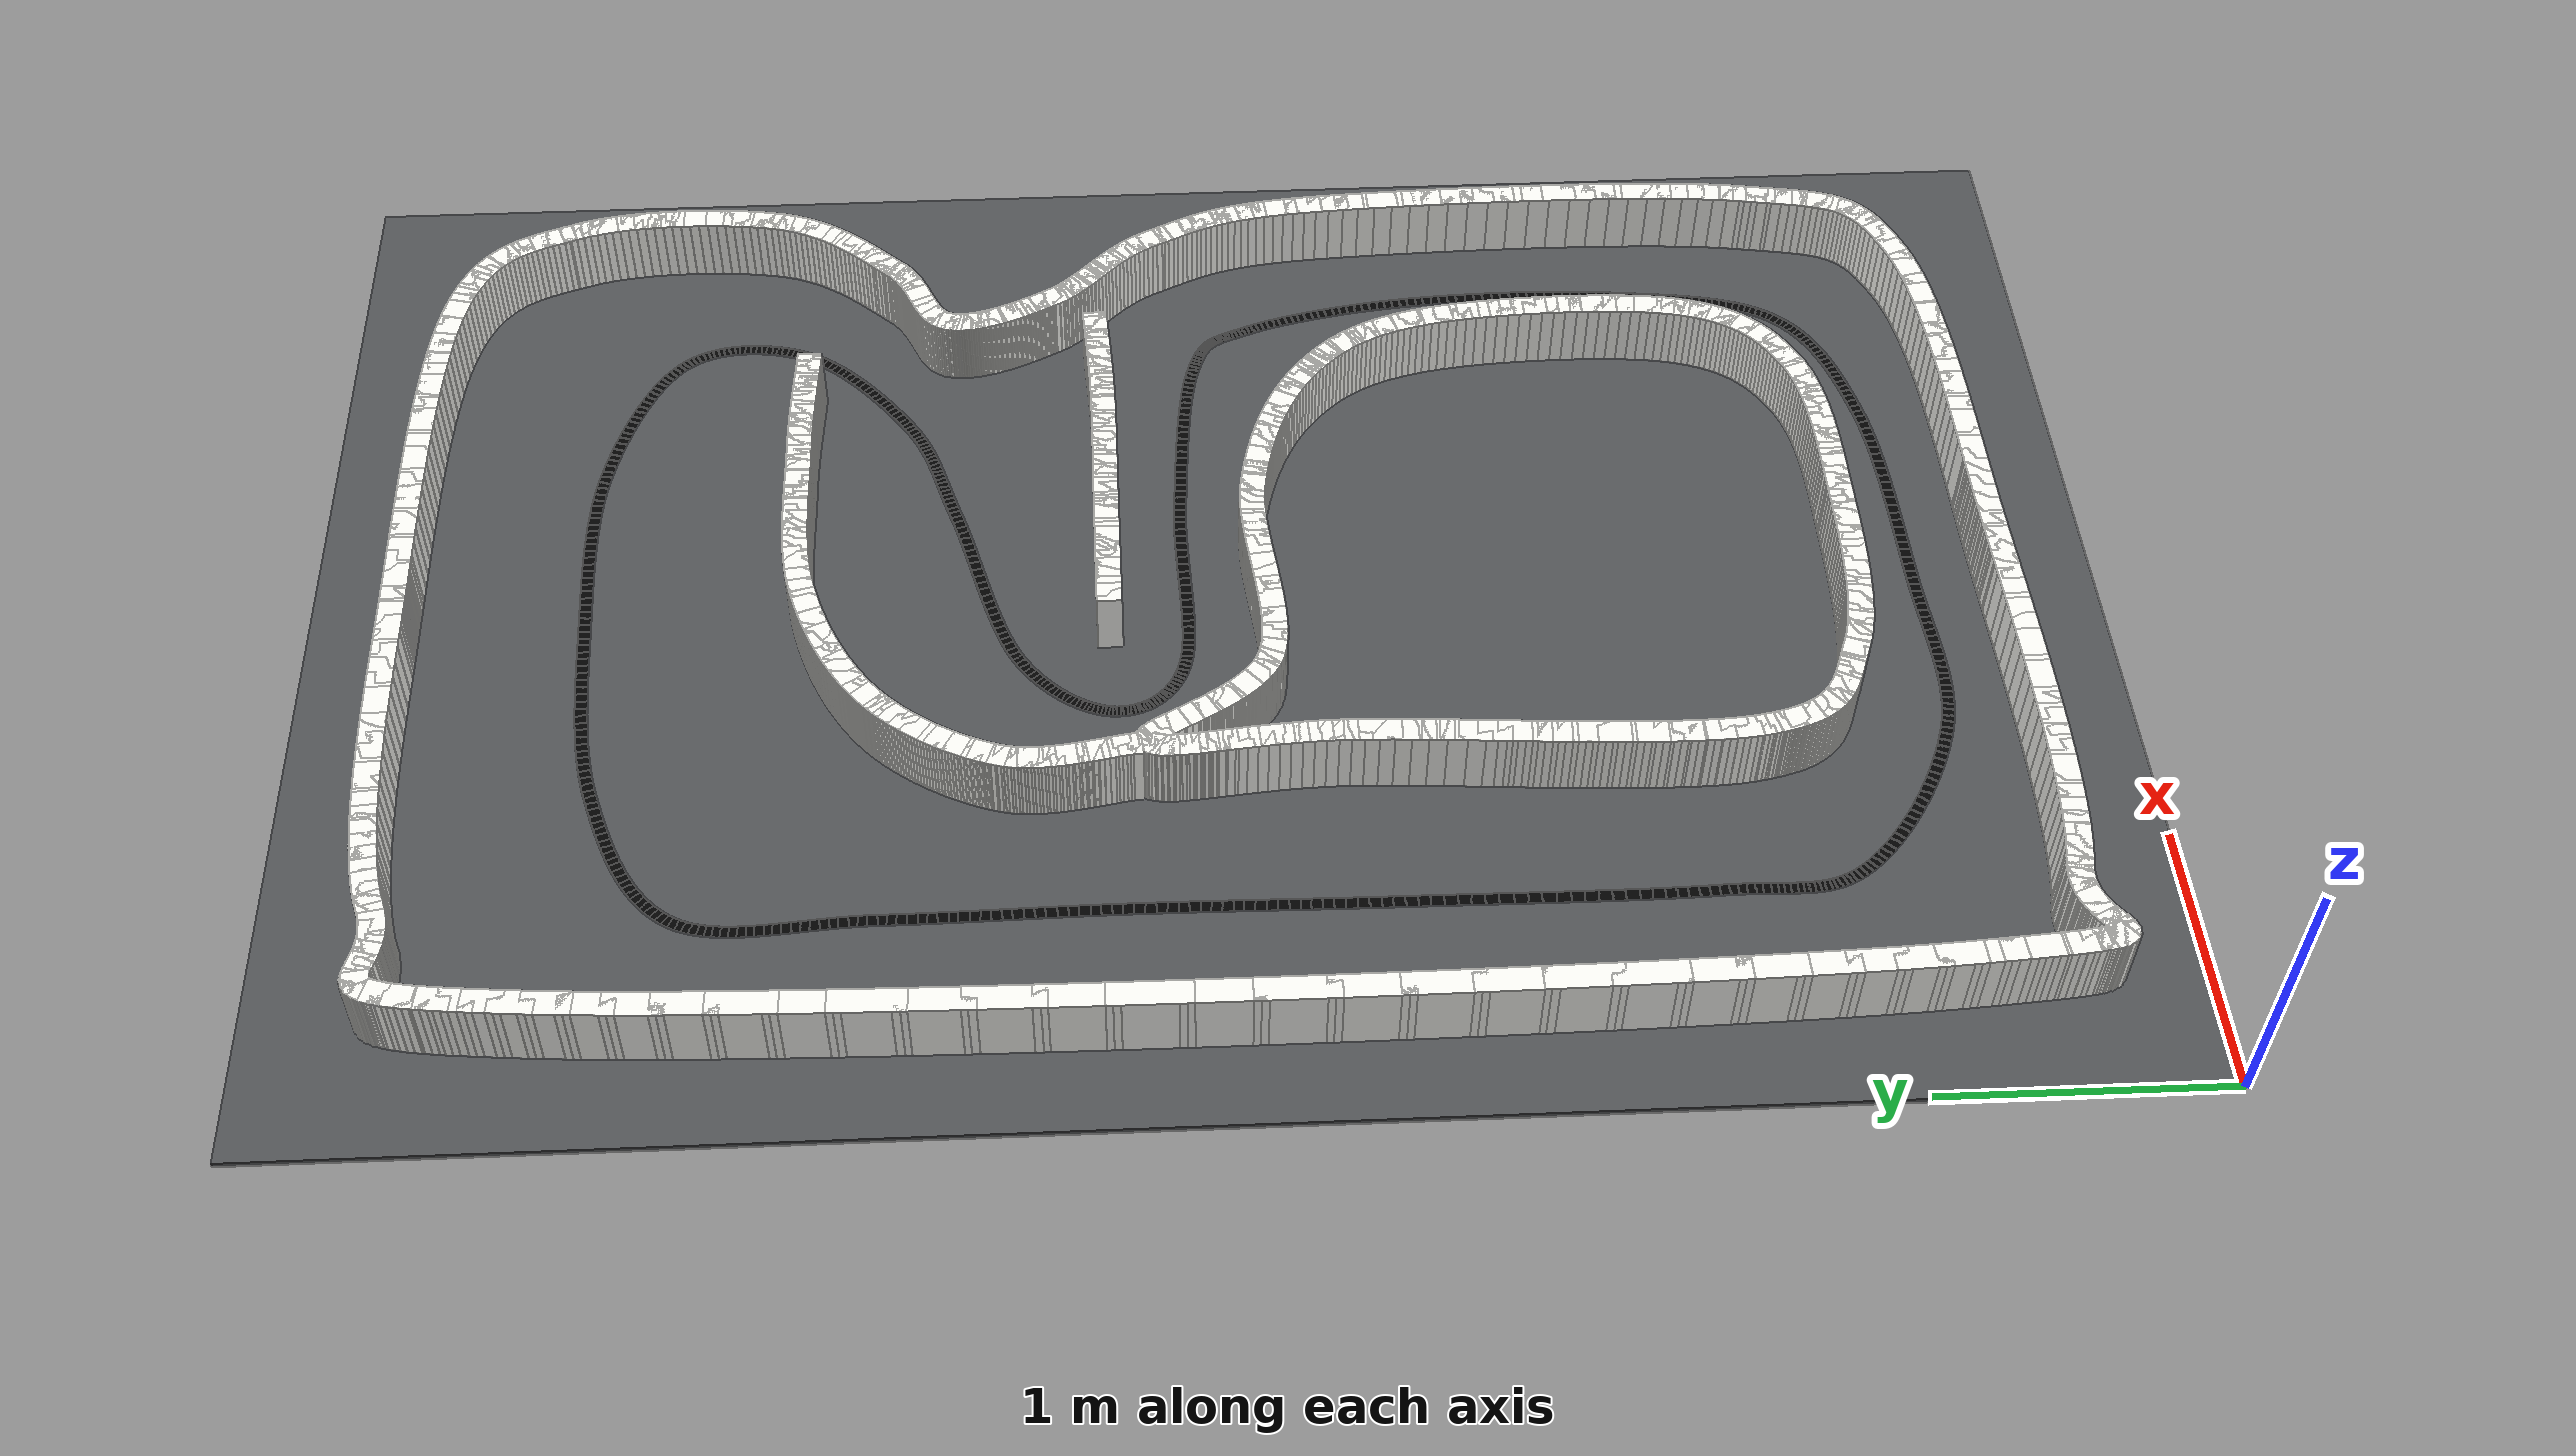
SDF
<?xml version='1.0' encoding='utf-8'?>
<sdf version="1.7">
  <world name="empty">
    <physics name="1ms" type="ignored">
      <max_step_size>0.001</max_step_size>
      <real_time_factor>1.0</real_time_factor>
    </physics>
    <plugin filename="gz-sim-physics-system" name="gz::sim::systems::Physics" />
    <plugin filename="gz-sim-imu-system" name="gz::sim::systems::Imu" />
    <plugin filename="gz-sim-sensors-system" name="gz::sim::systems::Sensors">
      <render_engine>ogre2</render_engine>
    </plugin>
    <plugin filename="gz-sim-user-commands-system" name="gz::sim::systems::UserCommands" />
    <plugin filename="gz-sim-scene-broadcaster-system" name="gz::sim::systems::SceneBroadcaster" />
    <scene>
      <ambient>0.75 0.75 0.75</ambient>
      <background>0.55 0.57 0.60</background>
    </scene>
    <light type="directional" name="lab_light">
      <cast_shadows>true</cast_shadows>
      <pose>2.2 3.2 5.0 0 0 0</pose>
      <diffuse>1 1 1 1</diffuse>
      <specular>0.2 0.2 0.2 1</specular>
      <direction>-0.25 0.15 -1.0</direction>
    </light>
    <model name="lab_floor">
      <static>true</static>
      <pose>2.2 3.2 -0.01 0 0 0</pose>
      <link name="floor_link">
        <collision name="floor_collision">
          <geometry>
            <box>
              <size>4.4 6.4 0.02</size>
            </box>
          </geometry>
        </collision>
        <visual name="floor_visual">
          <geometry>
            <box>
              <size>4.4 6.4 0.02</size>
            </box>
          </geometry>
          <material>
            <ambient>0.28 0.29 0.30 1</ambient>
            <diffuse>0.32 0.33 0.34 1</diffuse>
            <specular>0.15 0.15 0.15 1</specular>
          </material>
        </visual>
      </link>
    </model>
    <model name="lab_track_walls">
      <static>true</static>
      <link name="walls">
        <collision name="outer_collision_000">
          <pose>0.70139 0.42305 0.12500 0 0 2.9793475</pose>
          <geometry>
            <box>
              <size>0.08722 0.09000 0.25000</size>
            </box>
          </geometry>
        </collision>
        <visual name="outer_visual_000">
          <pose>0.70139 0.42305 0.12500 0 0 2.9793475</pose>
          <geometry>
            <box>
              <size>0.08722 0.09000 0.25000</size>
            </box>
          </geometry>
          <material>
            <ambient>0.92 0.92 0.90 1</ambient>
            <diffuse>0.98 0.98 0.96 1</diffuse>
            <specular>0.15 0.15 0.15 1</specular>
            <emissive>0.72 0.72 0.70 1</emissive>
          </material>
        </visual>
        <collision name="outer_collision_001">
          <pose>0.66583 0.42655 0.12500 0 0 3.1145189</pose>
          <geometry>
            <box>
              <size>0.08340 0.09000 0.25000</size>
            </box>
          </geometry>
        </collision>
        <visual name="outer_visual_001">
          <pose>0.66583 0.42655 0.12500 0 0 3.1145189</pose>
          <geometry>
            <box>
              <size>0.08340 0.09000 0.25000</size>
            </box>
          </geometry>
          <material>
            <ambient>0.92 0.92 0.90 1</ambient>
            <diffuse>0.98 0.98 0.96 1</diffuse>
            <specular>0.15 0.15 0.15 1</specular>
            <emissive>0.72 0.72 0.70 1</emissive>
          </material>
        </visual>
        <collision name="outer_collision_002">
          <pose>0.63353 0.42530 0.12500 0 0 -3.0305130</pose>
          <geometry>
            <box>
              <size>0.08042 0.09000 0.25000</size>
            </box>
          </geometry>
        </collision>
        <visual name="outer_visual_002">
          <pose>0.63353 0.42530 0.12500 0 0 -3.0305130</pose>
          <geometry>
            <box>
              <size>0.08042 0.09000 0.25000</size>
            </box>
          </geometry>
          <material>
            <ambient>0.92 0.92 0.90 1</ambient>
            <diffuse>0.98 0.98 0.96 1</diffuse>
            <specular>0.15 0.15 0.15 1</specular>
            <emissive>0.72 0.72 0.70 1</emissive>
          </material>
        </visual>
        <collision name="outer_collision_003">
          <pose>0.60429 0.42011 0.12500 0 0 -2.8964913</pose>
          <geometry>
            <box>
              <size>0.07810 0.09000 0.25000</size>
            </box>
          </geometry>
        </collision>
        <visual name="outer_visual_003">
          <pose>0.60429 0.42011 0.12500 0 0 -2.8964913</pose>
          <geometry>
            <box>
              <size>0.07810 0.09000 0.25000</size>
            </box>
          </geometry>
          <material>
            <ambient>0.92 0.92 0.90 1</ambient>
            <diffuse>0.98 0.98 0.96 1</diffuse>
            <specular>0.15 0.15 0.15 1</specular>
            <emissive>0.72 0.72 0.70 1</emissive>
          </material>
        </visual>
        <collision name="outer_collision_004">
          <pose>0.57794 0.41183 0.12500 0 0 -2.7735206</pose>
          <geometry>
            <box>
              <size>0.07624 0.09000 0.25000</size>
            </box>
          </geometry>
        </collision>
        <visual name="outer_visual_004">
          <pose>0.57794 0.41183 0.12500 0 0 -2.7735206</pose>
          <geometry>
            <box>
              <size>0.07624 0.09000 0.25000</size>
            </box>
          </geometry>
          <material>
            <ambient>0.92 0.92 0.90 1</ambient>
            <diffuse>0.98 0.98 0.96 1</diffuse>
            <specular>0.15 0.15 0.15 1</specular>
            <emissive>0.72 0.72 0.70 1</emissive>
          </material>
        </visual>
        <collision name="outer_collision_005">
          <pose>0.55429 0.40128 0.12500 0 0 -2.6671114</pose>
          <geometry>
            <box>
              <size>0.07461 0.09000 0.25000</size>
            </box>
          </geometry>
        </collision>
        <visual name="outer_visual_005">
          <pose>0.55429 0.40128 0.12500 0 0 -2.6671114</pose>
          <geometry>
            <box>
              <size>0.07461 0.09000 0.25000</size>
            </box>
          </geometry>
          <material>
            <ambient>0.92 0.92 0.90 1</ambient>
            <diffuse>0.98 0.98 0.96 1</diffuse>
            <specular>0.15 0.15 0.15 1</specular>
            <emissive>0.72 0.72 0.70 1</emissive>
          </material>
        </visual>
        <collision name="outer_collision_006">
          <pose>0.53317 0.38930 0.12500 0 0 -2.5811599</pose>
          <geometry>
            <box>
              <size>0.07300 0.09000 0.25000</size>
            </box>
          </geometry>
        </collision>
        <visual name="outer_visual_006">
          <pose>0.53317 0.38930 0.12500 0 0 -2.5811599</pose>
          <geometry>
            <box>
              <size>0.07300 0.09000 0.25000</size>
            </box>
          </geometry>
          <material>
            <ambient>0.92 0.92 0.90 1</ambient>
            <diffuse>0.98 0.98 0.96 1</diffuse>
            <specular>0.15 0.15 0.15 1</specular>
            <emissive>0.72 0.72 0.70 1</emissive>
          </material>
        </visual>
        <collision name="outer_collision_007">
          <pose>0.51439 0.37671 0.12500 0 0 -2.5188002</pose>
          <geometry>
            <box>
              <size>0.07124 0.09000 0.25000</size>
            </box>
          </geometry>
        </collision>
        <visual name="outer_visual_007">
          <pose>0.51439 0.37671 0.12500 0 0 -2.5188002</pose>
          <geometry>
            <box>
              <size>0.07124 0.09000 0.25000</size>
            </box>
          </geometry>
          <material>
            <ambient>0.92 0.92 0.90 1</ambient>
            <diffuse>0.98 0.98 0.96 1</diffuse>
            <specular>0.15 0.15 0.15 1</specular>
            <emissive>0.72 0.72 0.70 1</emissive>
          </material>
        </visual>
        <collision name="outer_collision_008">
          <pose>0.49776 0.36435 0.12500 0 0 -2.4841095</pose>
          <geometry>
            <box>
              <size>0.06920 0.09000 0.25000</size>
            </box>
          </geometry>
        </collision>
        <visual name="outer_visual_008">
          <pose>0.49776 0.36435 0.12500 0 0 -2.4841095</pose>
          <geometry>
            <box>
              <size>0.06920 0.09000 0.25000</size>
            </box>
          </geometry>
          <material>
            <ambient>0.92 0.92 0.90 1</ambient>
            <diffuse>0.98 0.98 0.96 1</diffuse>
            <specular>0.15 0.15 0.15 1</specular>
            <emissive>0.72 0.72 0.70 1</emissive>
          </material>
        </visual>
        <collision name="outer_collision_009">
          <pose>0.48311 0.35305 0.12500 0 0 -2.4849861</pose>
          <geometry>
            <box>
              <size>0.06681 0.09000 0.25000</size>
            </box>
          </geometry>
        </collision>
        <visual name="outer_visual_009">
          <pose>0.48311 0.35305 0.12500 0 0 -2.4849861</pose>
          <geometry>
            <box>
              <size>0.06681 0.09000 0.25000</size>
            </box>
          </geometry>
          <material>
            <ambient>0.92 0.92 0.90 1</ambient>
            <diffuse>0.98 0.98 0.96 1</diffuse>
            <specular>0.15 0.15 0.15 1</specular>
            <emissive>0.72 0.72 0.70 1</emissive>
          </material>
        </visual>
        <collision name="outer_collision_010">
          <pose>0.47025 0.34363 0.12500 0 0 -2.5389935</pose>
          <geometry>
            <box>
              <size>0.06408 0.09000 0.25000</size>
            </box>
          </geometry>
        </collision>
        <visual name="outer_visual_010">
          <pose>0.47025 0.34363 0.12500 0 0 -2.5389935</pose>
          <geometry>
            <box>
              <size>0.06408 0.09000 0.25000</size>
            </box>
          </geometry>
          <material>
            <ambient>0.92 0.92 0.90 1</ambient>
            <diffuse>0.98 0.98 0.96 1</diffuse>
            <specular>0.15 0.15 0.15 1</specular>
            <emissive>0.72 0.72 0.70 1</emissive>
          </material>
        </visual>
        <collision name="outer_collision_011">
          <pose>0.45900 0.33694 0.12500 0 0 -2.6870608</pose>
          <geometry>
            <box>
              <size>0.06118 0.09000 0.25000</size>
            </box>
          </geometry>
        </collision>
        <visual name="outer_visual_011">
          <pose>0.45900 0.33694 0.12500 0 0 -2.6870608</pose>
          <geometry>
            <box>
              <size>0.06118 0.09000 0.25000</size>
            </box>
          </geometry>
          <material>
            <ambient>0.92 0.92 0.90 1</ambient>
            <diffuse>0.98 0.98 0.96 1</diffuse>
            <specular>0.15 0.15 0.15 1</specular>
            <emissive>0.72 0.72 0.70 1</emissive>
          </material>
        </visual>
        <collision name="outer_collision_012">
          <pose>0.44917 0.33380 0.12500 0 0 -3.0156234</pose>
          <geometry>
            <box>
              <size>0.05873 0.09000 0.25000</size>
            </box>
          </geometry>
        </collision>
        <visual name="outer_visual_012">
          <pose>0.44917 0.33380 0.12500 0 0 -3.0156234</pose>
          <geometry>
            <box>
              <size>0.05873 0.09000 0.25000</size>
            </box>
          </geometry>
          <material>
            <ambient>0.92 0.92 0.90 1</ambient>
            <diffuse>0.98 0.98 0.96 1</diffuse>
            <specular>0.15 0.15 0.15 1</specular>
            <emissive>0.72 0.72 0.70 1</emissive>
          </material>
        </visual>
        <collision name="outer_collision_013">
          <pose>0.44060 0.33504 0.12500 0 0 2.7146552</pose>
          <geometry>
            <box>
              <size>0.05829 0.09000 0.25000</size>
            </box>
          </geometry>
        </collision>
        <visual name="outer_visual_013">
          <pose>0.44060 0.33504 0.12500 0 0 2.7146552</pose>
          <geometry>
            <box>
              <size>0.05829 0.09000 0.25000</size>
            </box>
          </geometry>
          <material>
            <ambient>0.92 0.92 0.90 1</ambient>
            <diffuse>0.98 0.98 0.96 1</diffuse>
            <specular>0.15 0.15 0.15 1</specular>
            <emissive>0.72 0.72 0.70 1</emissive>
          </material>
        </visual>
        <collision name="outer_collision_014">
          <pose>0.43308 0.34149 0.12500 0 0 2.2195031</pose>
          <geometry>
            <box>
              <size>0.06113 0.09000 0.25000</size>
            </box>
          </geometry>
        </collision>
        <visual name="outer_visual_014">
          <pose>0.43308 0.34149 0.12500 0 0 2.2195031</pose>
          <geometry>
            <box>
              <size>0.06113 0.09000 0.25000</size>
            </box>
          </geometry>
          <material>
            <ambient>0.92 0.92 0.90 1</ambient>
            <diffuse>0.98 0.98 0.96 1</diffuse>
            <specular>0.15 0.15 0.15 1</specular>
            <emissive>0.72 0.72 0.70 1</emissive>
          </material>
        </visual>
        <collision name="outer_collision_015">
          <pose>0.42645 0.35399 0.12500 0 0 1.9483097</pose>
          <geometry>
            <box>
              <size>0.06642 0.09000 0.25000</size>
            </box>
          </geometry>
        </collision>
        <visual name="outer_visual_015">
          <pose>0.42645 0.35399 0.12500 0 0 1.9483097</pose>
          <geometry>
            <box>
              <size>0.06642 0.09000 0.25000</size>
            </box>
          </geometry>
          <material>
            <ambient>0.92 0.92 0.90 1</ambient>
            <diffuse>0.98 0.98 0.96 1</diffuse>
            <specular>0.15 0.15 0.15 1</specular>
            <emissive>0.72 0.72 0.70 1</emissive>
          </material>
        </visual>
        <collision name="outer_collision_016">
          <pose>0.42052 0.37336 0.12500 0 0 1.8106261</pose>
          <geometry>
            <box>
              <size>0.07320 0.09000 0.25000</size>
            </box>
          </geometry>
        </collision>
        <visual name="outer_visual_016">
          <pose>0.42052 0.37336 0.12500 0 0 1.8106261</pose>
          <geometry>
            <box>
              <size>0.07320 0.09000 0.25000</size>
            </box>
          </geometry>
          <material>
            <ambient>0.92 0.92 0.90 1</ambient>
            <diffuse>0.98 0.98 0.96 1</diffuse>
            <specular>0.15 0.15 0.15 1</specular>
            <emissive>0.72 0.72 0.70 1</emissive>
          </material>
        </visual>
        <collision name="outer_collision_017">
          <pose>0.41510 0.40044 0.12500 0 0 1.7363650</pose>
          <geometry>
            <box>
              <size>0.08108 0.09000 0.25000</size>
            </box>
          </geometry>
        </collision>
        <visual name="outer_visual_017">
          <pose>0.41510 0.40044 0.12500 0 0 1.7363650</pose>
          <geometry>
            <box>
              <size>0.08108 0.09000 0.25000</size>
            </box>
          </geometry>
          <material>
            <ambient>0.92 0.92 0.90 1</ambient>
            <diffuse>0.98 0.98 0.96 1</diffuse>
            <specular>0.15 0.15 0.15 1</specular>
            <emissive>0.72 0.72 0.70 1</emissive>
          </material>
        </visual>
        <collision name="outer_collision_018">
          <pose>0.41002 0.43606 0.12500 0 0 1.6938933</pose>
          <geometry>
            <box>
              <size>0.08990 0.09000 0.25000</size>
            </box>
          </geometry>
        </collision>
        <visual name="outer_visual_018">
          <pose>0.41002 0.43606 0.12500 0 0 1.6938933</pose>
          <geometry>
            <box>
              <size>0.08990 0.09000 0.25000</size>
            </box>
          </geometry>
          <material>
            <ambient>0.92 0.92 0.90 1</ambient>
            <diffuse>0.98 0.98 0.96 1</diffuse>
            <specular>0.15 0.15 0.15 1</specular>
            <emissive>0.72 0.72 0.70 1</emissive>
          </material>
        </visual>
        <collision name="outer_collision_019">
          <pose>0.40509 0.48105 0.12500 0 0 1.6687166</pose>
          <geometry>
            <box>
              <size>0.09962 0.09000 0.25000</size>
            </box>
          </geometry>
        </collision>
        <visual name="outer_visual_019">
          <pose>0.40509 0.48105 0.12500 0 0 1.6687166</pose>
          <geometry>
            <box>
              <size>0.09962 0.09000 0.25000</size>
            </box>
          </geometry>
          <material>
            <ambient>0.92 0.92 0.90 1</ambient>
            <diffuse>0.98 0.98 0.96 1</diffuse>
            <specular>0.15 0.15 0.15 1</specular>
            <emissive>0.72 0.72 0.70 1</emissive>
          </material>
        </visual>
        <collision name="outer_collision_020">
          <pose>0.40013 0.53624 0.12500 0 0 1.6536115</pose>
          <geometry>
            <box>
              <size>0.11021 0.09000 0.25000</size>
            </box>
          </geometry>
        </collision>
        <visual name="outer_visual_020">
          <pose>0.40013 0.53624 0.12500 0 0 1.6536115</pose>
          <geometry>
            <box>
              <size>0.11021 0.09000 0.25000</size>
            </box>
          </geometry>
          <material>
            <ambient>0.92 0.92 0.90 1</ambient>
            <diffuse>0.98 0.98 0.96 1</diffuse>
            <specular>0.15 0.15 0.15 1</specular>
            <emissive>0.72 0.72 0.70 1</emissive>
          </material>
        </visual>
        <collision name="outer_collision_021">
          <pose>0.39495 0.60247 0.12500 0 0 1.6446824</pose>
          <geometry>
            <box>
              <size>0.12164 0.09000 0.25000</size>
            </box>
          </geometry>
        </collision>
        <visual name="outer_visual_021">
          <pose>0.39495 0.60247 0.12500 0 0 1.6446824</pose>
          <geometry>
            <box>
              <size>0.12164 0.09000 0.25000</size>
            </box>
          </geometry>
          <material>
            <ambient>0.92 0.92 0.90 1</ambient>
            <diffuse>0.98 0.98 0.96 1</diffuse>
            <specular>0.15 0.15 0.15 1</specular>
            <emissive>0.72 0.72 0.70 1</emissive>
          </material>
        </visual>
        <collision name="outer_collision_022">
          <pose>0.38939 0.68055 0.12500 0 0 1.6396885</pose>
          <geometry>
            <box>
              <size>0.13393 0.09000 0.25000</size>
            </box>
          </geometry>
        </collision>
        <visual name="outer_visual_022">
          <pose>0.38939 0.68055 0.12500 0 0 1.6396885</pose>
          <geometry>
            <box>
              <size>0.13393 0.09000 0.25000</size>
            </box>
          </geometry>
          <material>
            <ambient>0.92 0.92 0.90 1</ambient>
            <diffuse>0.98 0.98 0.96 1</diffuse>
            <specular>0.15 0.15 0.15 1</specular>
            <emissive>0.72 0.72 0.70 1</emissive>
          </material>
        </visual>
        <collision name="outer_collision_023">
          <pose>0.38324 0.77133 0.12500 0 0 1.6372730</pose>
          <geometry>
            <box>
              <size>0.14705 0.09000 0.25000</size>
            </box>
          </geometry>
        </collision>
        <visual name="outer_visual_023">
          <pose>0.38324 0.77133 0.12500 0 0 1.6372730</pose>
          <geometry>
            <box>
              <size>0.14705 0.09000 0.25000</size>
            </box>
          </geometry>
          <material>
            <ambient>0.92 0.92 0.90 1</ambient>
            <diffuse>0.98 0.98 0.96 1</diffuse>
            <specular>0.15 0.15 0.15 1</specular>
            <emissive>0.72 0.72 0.70 1</emissive>
          </material>
        </visual>
        <collision name="outer_collision_024">
          <pose>0.37670 0.87734 0.12500 0 0 1.6282488</pose>
          <geometry>
            <box>
              <size>0.16437 0.09000 0.25000</size>
            </box>
          </geometry>
        </collision>
        <visual name="outer_visual_024">
          <pose>0.37670 0.87734 0.12500 0 0 1.6282488</pose>
          <geometry>
            <box>
              <size>0.16437 0.09000 0.25000</size>
            </box>
          </geometry>
          <material>
            <ambient>0.92 0.92 0.90 1</ambient>
            <diffuse>0.98 0.98 0.96 1</diffuse>
            <specular>0.15 0.15 0.15 1</specular>
            <emissive>0.72 0.72 0.70 1</emissive>
          </material>
        </visual>
        <collision name="outer_collision_025">
          <pose>0.37039 1.00195 0.12500 0 0 1.6156215</pose>
          <geometry>
            <box>
              <size>0.18416 0.09000 0.25000</size>
            </box>
          </geometry>
        </collision>
        <visual name="outer_visual_025">
          <pose>0.37039 1.00195 0.12500 0 0 1.6156215</pose>
          <geometry>
            <box>
              <size>0.18416 0.09000 0.25000</size>
            </box>
          </geometry>
          <material>
            <ambient>0.92 0.92 0.90 1</ambient>
            <diffuse>0.98 0.98 0.96 1</diffuse>
            <specular>0.15 0.15 0.15 1</specular>
            <emissive>0.72 0.72 0.70 1</emissive>
          </material>
        </visual>
        <collision name="outer_collision_026">
          <pose>0.36464 1.14549 0.12500 0 0 1.6066038</pose>
          <geometry>
            <box>
              <size>0.20217 0.09000 0.25000</size>
            </box>
          </geometry>
        </collision>
        <visual name="outer_visual_026">
          <pose>0.36464 1.14549 0.12500 0 0 1.6066038</pose>
          <geometry>
            <box>
              <size>0.20217 0.09000 0.25000</size>
            </box>
          </geometry>
          <material>
            <ambient>0.92 0.92 0.90 1</ambient>
            <diffuse>0.98 0.98 0.96 1</diffuse>
            <specular>0.15 0.15 0.15 1</specular>
            <emissive>0.72 0.72 0.70 1</emissive>
          </material>
        </visual>
        <collision name="outer_collision_027">
          <pose>0.35946 1.30619 0.12500 0 0 1.5997556</pose>
          <geometry>
            <box>
              <size>0.21840 0.09000 0.25000</size>
            </box>
          </geometry>
        </collision>
        <visual name="outer_visual_027">
          <pose>0.35946 1.30619 0.12500 0 0 1.5997556</pose>
          <geometry>
            <box>
              <size>0.21840 0.09000 0.25000</size>
            </box>
          </geometry>
          <material>
            <ambient>0.92 0.92 0.90 1</ambient>
            <diffuse>0.98 0.98 0.96 1</diffuse>
            <specular>0.15 0.15 0.15 1</specular>
            <emissive>0.72 0.72 0.70 1</emissive>
          </material>
        </visual>
        <collision name="outer_collision_028">
          <pose>0.35486 1.48225 0.12500 0 0 1.5943006</pose>
          <geometry>
            <box>
              <size>0.23284 0.09000 0.25000</size>
            </box>
          </geometry>
        </collision>
        <visual name="outer_visual_028">
          <pose>0.35486 1.48225 0.12500 0 0 1.5943006</pose>
          <geometry>
            <box>
              <size>0.23284 0.09000 0.25000</size>
            </box>
          </geometry>
          <material>
            <ambient>0.92 0.92 0.90 1</ambient>
            <diffuse>0.98 0.98 0.96 1</diffuse>
            <specular>0.15 0.15 0.15 1</specular>
            <emissive>0.72 0.72 0.70 1</emissive>
          </material>
        </visual>
        <collision name="outer_collision_029">
          <pose>0.35084 1.67187 0.12500 0 0 1.5897815</pose>
          <geometry>
            <box>
              <size>0.24549 0.09000 0.25000</size>
            </box>
          </geometry>
        </collision>
        <visual name="outer_visual_029">
          <pose>0.35084 1.67187 0.12500 0 0 1.5897815</pose>
          <geometry>
            <box>
              <size>0.24549 0.09000 0.25000</size>
            </box>
          </geometry>
          <material>
            <ambient>0.92 0.92 0.90 1</ambient>
            <diffuse>0.98 0.98 0.96 1</diffuse>
            <specular>0.15 0.15 0.15 1</specular>
            <emissive>0.72 0.72 0.70 1</emissive>
          </material>
        </visual>
        <collision name="outer_collision_030">
          <pose>0.34742 1.87326 0.12500 0 0 1.5859093</pose>
          <geometry>
            <box>
              <size>0.25636 0.09000 0.25000</size>
            </box>
          </geometry>
        </collision>
        <visual name="outer_visual_030">
          <pose>0.34742 1.87326 0.12500 0 0 1.5859093</pose>
          <geometry>
            <box>
              <size>0.25636 0.09000 0.25000</size>
            </box>
          </geometry>
          <material>
            <ambient>0.92 0.92 0.90 1</ambient>
            <diffuse>0.98 0.98 0.96 1</diffuse>
            <specular>0.15 0.15 0.15 1</specular>
            <emissive>0.72 0.72 0.70 1</emissive>
          </material>
        </visual>
        <collision name="outer_collision_031">
          <pose>0.34460 2.08463 0.12500 0 0 1.5824899</pose>
          <geometry>
            <box>
              <size>0.26543 0.09000 0.25000</size>
            </box>
          </geometry>
        </collision>
        <visual name="outer_visual_031">
          <pose>0.34460 2.08463 0.12500 0 0 1.5824899</pose>
          <geometry>
            <box>
              <size>0.26543 0.09000 0.25000</size>
            </box>
          </geometry>
          <material>
            <ambient>0.92 0.92 0.90 1</ambient>
            <diffuse>0.98 0.98 0.96 1</diffuse>
            <specular>0.15 0.15 0.15 1</specular>
            <emissive>0.72 0.72 0.70 1</emissive>
          </material>
        </visual>
        <collision name="outer_collision_032">
          <pose>0.34237 2.30420 0.12500 0 0 1.5793859</pose>
          <geometry>
            <box>
              <size>0.27272 0.09000 0.25000</size>
            </box>
          </geometry>
        </collision>
        <visual name="outer_visual_032">
          <pose>0.34237 2.30420 0.12500 0 0 1.5793859</pose>
          <geometry>
            <box>
              <size>0.27272 0.09000 0.25000</size>
            </box>
          </geometry>
          <material>
            <ambient>0.92 0.92 0.90 1</ambient>
            <diffuse>0.98 0.98 0.96 1</diffuse>
            <specular>0.15 0.15 0.15 1</specular>
            <emissive>0.72 0.72 0.70 1</emissive>
          </material>
        </visual>
        <collision name="outer_collision_033">
          <pose>0.34076 2.53015 0.12500 0 0 1.5764942</pose>
          <geometry>
            <box>
              <size>0.27821 0.09000 0.25000</size>
            </box>
          </geometry>
        </collision>
        <visual name="outer_visual_033">
          <pose>0.34076 2.53015 0.12500 0 0 1.5764942</pose>
          <geometry>
            <box>
              <size>0.27821 0.09000 0.25000</size>
            </box>
          </geometry>
          <material>
            <ambient>0.92 0.92 0.90 1</ambient>
            <diffuse>0.98 0.98 0.96 1</diffuse>
            <specular>0.15 0.15 0.15 1</specular>
            <emissive>0.72 0.72 0.70 1</emissive>
          </material>
        </visual>
        <collision name="outer_collision_034">
          <pose>0.33977 2.76072 0.12500 0 0 1.5737329</pose>
          <geometry>
            <box>
              <size>0.28191 0.09000 0.25000</size>
            </box>
          </geometry>
        </collision>
        <visual name="outer_visual_034">
          <pose>0.33977 2.76072 0.12500 0 0 1.5737329</pose>
          <geometry>
            <box>
              <size>0.28191 0.09000 0.25000</size>
            </box>
          </geometry>
          <material>
            <ambient>0.92 0.92 0.90 1</ambient>
            <diffuse>0.98 0.98 0.96 1</diffuse>
            <specular>0.15 0.15 0.15 1</specular>
            <emissive>0.72 0.72 0.70 1</emissive>
          </material>
        </visual>
        <collision name="outer_collision_035">
          <pose>0.33940 2.99409 0.12500 0 0 1.5710325</pose>
          <geometry>
            <box>
              <size>0.28383 0.09000 0.25000</size>
            </box>
          </geometry>
        </collision>
        <visual name="outer_visual_035">
          <pose>0.33940 2.99409 0.12500 0 0 1.5710325</pose>
          <geometry>
            <box>
              <size>0.28383 0.09000 0.25000</size>
            </box>
          </geometry>
          <material>
            <ambient>0.92 0.92 0.90 1</ambient>
            <diffuse>0.98 0.98 0.96 1</diffuse>
            <specular>0.15 0.15 0.15 1</specular>
            <emissive>0.72 0.72 0.70 1</emissive>
          </material>
        </visual>
        <collision name="outer_collision_036">
          <pose>0.33966 3.22847 0.12500 0 0 1.5683295</pose>
          <geometry>
            <box>
              <size>0.28395 0.09000 0.25000</size>
            </box>
          </geometry>
        </collision>
        <visual name="outer_visual_036">
          <pose>0.33966 3.22847 0.12500 0 0 1.5683295</pose>
          <geometry>
            <box>
              <size>0.28395 0.09000 0.25000</size>
            </box>
          </geometry>
          <material>
            <ambient>0.92 0.92 0.90 1</ambient>
            <diffuse>0.98 0.98 0.96 1</diffuse>
            <specular>0.15 0.15 0.15 1</specular>
            <emissive>0.72 0.72 0.70 1</emissive>
          </material>
        </visual>
        <collision name="outer_collision_037">
          <pose>0.34056 3.46209 0.12500 0 0 1.5655616</pose>
          <geometry>
            <box>
              <size>0.28228 0.09000 0.25000</size>
            </box>
          </geometry>
        </collision>
        <visual name="outer_visual_037">
          <pose>0.34056 3.46209 0.12500 0 0 1.5655616</pose>
          <geometry>
            <box>
              <size>0.28228 0.09000 0.25000</size>
            </box>
          </geometry>
          <material>
            <ambient>0.92 0.92 0.90 1</ambient>
            <diffuse>0.98 0.98 0.96 1</diffuse>
            <specular>0.15 0.15 0.15 1</specular>
            <emissive>0.72 0.72 0.70 1</emissive>
          </material>
        </visual>
        <collision name="outer_collision_038">
          <pose>0.34210 3.69314 0.12500 0 0 1.5626626</pose>
          <geometry>
            <box>
              <size>0.27882 0.09000 0.25000</size>
            </box>
          </geometry>
        </collision>
        <visual name="outer_visual_038">
          <pose>0.34210 3.69314 0.12500 0 0 1.5626626</pose>
          <geometry>
            <box>
              <size>0.27882 0.09000 0.25000</size>
            </box>
          </geometry>
          <material>
            <ambient>0.92 0.92 0.90 1</ambient>
            <diffuse>0.98 0.98 0.96 1</diffuse>
            <specular>0.15 0.15 0.15 1</specular>
            <emissive>0.72 0.72 0.70 1</emissive>
          </material>
        </visual>
        <collision name="outer_collision_039">
          <pose>0.34430 3.91982 0.12500 0 0 1.5595567</pose>
          <geometry>
            <box>
              <size>0.27357 0.09000 0.25000</size>
            </box>
          </geometry>
        </collision>
        <visual name="outer_visual_039">
          <pose>0.34430 3.91982 0.12500 0 0 1.5595567</pose>
          <geometry>
            <box>
              <size>0.27357 0.09000 0.25000</size>
            </box>
          </geometry>
          <material>
            <ambient>0.92 0.92 0.90 1</ambient>
            <diffuse>0.98 0.98 0.96 1</diffuse>
            <specular>0.15 0.15 0.15 1</specular>
            <emissive>0.72 0.72 0.70 1</emissive>
          </material>
        </visual>
        <collision name="outer_collision_040">
          <pose>0.34714 4.14036 0.12500 0 0 1.5561521</pose>
          <geometry>
            <box>
              <size>0.26653 0.09000 0.25000</size>
            </box>
          </geometry>
        </collision>
        <visual name="outer_visual_040">
          <pose>0.34714 4.14036 0.12500 0 0 1.5561521</pose>
          <geometry>
            <box>
              <size>0.26653 0.09000 0.25000</size>
            </box>
          </geometry>
          <material>
            <ambient>0.92 0.92 0.90 1</ambient>
            <diffuse>0.98 0.98 0.96 1</diffuse>
            <specular>0.15 0.15 0.15 1</specular>
            <emissive>0.72 0.72 0.70 1</emissive>
          </material>
        </visual>
        <collision name="outer_collision_041">
          <pose>0.35066 4.35295 0.12500 0 0 1.5523307</pose>
          <geometry>
            <box>
              <size>0.25770 0.09000 0.25000</size>
            </box>
          </geometry>
        </collision>
        <visual name="outer_visual_041">
          <pose>0.35066 4.35295 0.12500 0 0 1.5523307</pose>
          <geometry>
            <box>
              <size>0.25770 0.09000 0.25000</size>
            </box>
          </geometry>
          <material>
            <ambient>0.92 0.92 0.90 1</ambient>
            <diffuse>0.98 0.98 0.96 1</diffuse>
            <specular>0.15 0.15 0.15 1</specular>
            <emissive>0.72 0.72 0.70 1</emissive>
          </material>
        </visual>
        <collision name="outer_collision_042">
          <pose>0.35484 4.55580 0.12500 0 0 1.5479328</pose>
          <geometry>
            <box>
              <size>0.24709 0.09000 0.25000</size>
            </box>
          </geometry>
        </collision>
        <visual name="outer_visual_042">
          <pose>0.35484 4.55580 0.12500 0 0 1.5479328</pose>
          <geometry>
            <box>
              <size>0.24709 0.09000 0.25000</size>
            </box>
          </geometry>
          <material>
            <ambient>0.92 0.92 0.90 1</ambient>
            <diffuse>0.98 0.98 0.96 1</diffuse>
            <specular>0.15 0.15 0.15 1</specular>
            <emissive>0.72 0.72 0.70 1</emissive>
          </material>
        </visual>
        <collision name="outer_collision_043">
          <pose>0.35969 4.74712 0.12500 0 0 1.5427316</pose>
          <geometry>
            <box>
              <size>0.23468 0.09000 0.25000</size>
            </box>
          </geometry>
        </collision>
        <visual name="outer_visual_043">
          <pose>0.35969 4.74712 0.12500 0 0 1.5427316</pose>
          <geometry>
            <box>
              <size>0.23468 0.09000 0.25000</size>
            </box>
          </geometry>
          <material>
            <ambient>0.92 0.92 0.90 1</ambient>
            <diffuse>0.98 0.98 0.96 1</diffuse>
            <specular>0.15 0.15 0.15 1</specular>
            <emissive>0.72 0.72 0.70 1</emissive>
          </material>
        </visual>
        <collision name="outer_collision_044">
          <pose>0.36523 4.92512 0.12500 0 0 1.5363893</pose>
          <geometry>
            <box>
              <size>0.22049 0.09000 0.25000</size>
            </box>
          </geometry>
        </collision>
        <visual name="outer_visual_044">
          <pose>0.36523 4.92512 0.12500 0 0 1.5363893</pose>
          <geometry>
            <box>
              <size>0.22049 0.09000 0.25000</size>
            </box>
          </geometry>
          <material>
            <ambient>0.92 0.92 0.90 1</ambient>
            <diffuse>0.98 0.98 0.96 1</diffuse>
            <specular>0.15 0.15 0.15 1</specular>
            <emissive>0.72 0.72 0.70 1</emissive>
          </material>
        </visual>
        <collision name="outer_collision_045">
          <pose>0.37146 5.08801 0.12500 0 0 1.5283730</pose>
          <geometry>
            <box>
              <size>0.20452 0.09000 0.25000</size>
            </box>
          </geometry>
        </collision>
        <visual name="outer_visual_045">
          <pose>0.37146 5.08801 0.12500 0 0 1.5283730</pose>
          <geometry>
            <box>
              <size>0.20452 0.09000 0.25000</size>
            </box>
          </geometry>
          <material>
            <ambient>0.92 0.92 0.90 1</ambient>
            <diffuse>0.98 0.98 0.96 1</diffuse>
            <specular>0.15 0.15 0.15 1</specular>
            <emissive>0.72 0.72 0.70 1</emissive>
          </material>
        </visual>
        <collision name="outer_collision_046">
          <pose>0.37838 5.23398 0.12500 0 0 1.5177860</pose>
          <geometry>
            <box>
              <size>0.18677 0.09000 0.25000</size>
            </box>
          </geometry>
        </collision>
        <visual name="outer_visual_046">
          <pose>0.37838 5.23398 0.12500 0 0 1.5177860</pose>
          <geometry>
            <box>
              <size>0.18677 0.09000 0.25000</size>
            </box>
          </geometry>
          <material>
            <ambient>0.92 0.92 0.90 1</ambient>
            <diffuse>0.98 0.98 0.96 1</diffuse>
            <specular>0.15 0.15 0.15 1</specular>
            <emissive>0.72 0.72 0.70 1</emissive>
          </material>
        </visual>
        <collision name="outer_collision_047">
          <pose>0.38601 5.36126 0.12500 0 0 1.5029861</pose>
          <geometry>
            <box>
              <size>0.16725 0.09000 0.25000</size>
            </box>
          </geometry>
        </collision>
        <visual name="outer_visual_047">
          <pose>0.38601 5.36126 0.12500 0 0 1.5029861</pose>
          <geometry>
            <box>
              <size>0.16725 0.09000 0.25000</size>
            </box>
          </geometry>
          <material>
            <ambient>0.92 0.92 0.90 1</ambient>
            <diffuse>0.98 0.98 0.96 1</diffuse>
            <specular>0.15 0.15 0.15 1</specular>
            <emissive>0.72 0.72 0.70 1</emissive>
          </material>
        </visual>
        <collision name="outer_collision_048">
          <pose>0.39406 5.47028 0.12500 0 0 1.4901957</pose>
          <geometry>
            <box>
              <size>0.15038 0.09000 0.25000</size>
            </box>
          </geometry>
        </collision>
        <visual name="outer_visual_048">
          <pose>0.39406 5.47028 0.12500 0 0 1.4901957</pose>
          <geometry>
            <box>
              <size>0.15038 0.09000 0.25000</size>
            </box>
          </geometry>
          <material>
            <ambient>0.92 0.92 0.90 1</ambient>
            <diffuse>0.98 0.98 0.96 1</diffuse>
            <specular>0.15 0.15 0.15 1</specular>
            <emissive>0.72 0.72 0.70 1</emissive>
          </material>
        </visual>
        <collision name="outer_collision_049">
          <pose>0.40202 5.56457 0.12500 0 0 1.4824732</pose>
          <geometry>
            <box>
              <size>0.13787 0.09000 0.25000</size>
            </box>
          </geometry>
        </collision>
        <visual name="outer_visual_049">
          <pose>0.40202 5.56457 0.12500 0 0 1.4824732</pose>
          <geometry>
            <box>
              <size>0.13787 0.09000 0.25000</size>
            </box>
          </geometry>
          <material>
            <ambient>0.92 0.92 0.90 1</ambient>
            <diffuse>0.98 0.98 0.96 1</diffuse>
            <specular>0.15 0.15 0.15 1</specular>
            <emissive>0.72 0.72 0.70 1</emissive>
          </material>
        </visual>
        <collision name="outer_collision_050">
          <pose>0.40972 5.64672 0.12500 0 0 1.4713779</pose>
          <geometry>
            <box>
              <size>0.12615 0.09000 0.25000</size>
            </box>
          </geometry>
        </collision>
        <visual name="outer_visual_050">
          <pose>0.40972 5.64672 0.12500 0 0 1.4713779</pose>
          <geometry>
            <box>
              <size>0.12615 0.09000 0.25000</size>
            </box>
          </geometry>
          <material>
            <ambient>0.92 0.92 0.90 1</ambient>
            <diffuse>0.98 0.98 0.96 1</diffuse>
            <specular>0.15 0.15 0.15 1</specular>
            <emissive>0.72 0.72 0.70 1</emissive>
          </material>
        </visual>
        <collision name="outer_collision_051">
          <pose>0.41731 5.71751 0.12500 0 0 1.4555121</pose>
          <geometry>
            <box>
              <size>0.11524 0.09000 0.25000</size>
            </box>
          </geometry>
        </collision>
        <visual name="outer_visual_051">
          <pose>0.41731 5.71751 0.12500 0 0 1.4555121</pose>
          <geometry>
            <box>
              <size>0.11524 0.09000 0.25000</size>
            </box>
          </geometry>
          <material>
            <ambient>0.92 0.92 0.90 1</ambient>
            <diffuse>0.98 0.98 0.96 1</diffuse>
            <specular>0.15 0.15 0.15 1</specular>
            <emissive>0.72 0.72 0.70 1</emissive>
          </material>
        </visual>
        <collision name="outer_collision_052">
          <pose>0.42492 5.77773 0.12500 0 0 1.4327612</pose>
          <geometry>
            <box>
              <size>0.10516 0.09000 0.25000</size>
            </box>
          </geometry>
        </collision>
        <visual name="outer_visual_052">
          <pose>0.42492 5.77773 0.12500 0 0 1.4327612</pose>
          <geometry>
            <box>
              <size>0.10516 0.09000 0.25000</size>
            </box>
          </geometry>
          <material>
            <ambient>0.92 0.92 0.90 1</ambient>
            <diffuse>0.98 0.98 0.96 1</diffuse>
            <specular>0.15 0.15 0.15 1</specular>
            <emissive>0.72 0.72 0.70 1</emissive>
          </material>
        </visual>
        <collision name="outer_collision_053">
          <pose>0.43269 5.82815 0.12500 0 0 1.3998365</pose>
          <geometry>
            <box>
              <size>0.09590 0.09000 0.25000</size>
            </box>
          </geometry>
        </collision>
        <visual name="outer_visual_053">
          <pose>0.43269 5.82815 0.12500 0 0 1.3998365</pose>
          <geometry>
            <box>
              <size>0.09590 0.09000 0.25000</size>
            </box>
          </geometry>
          <material>
            <ambient>0.92 0.92 0.90 1</ambient>
            <diffuse>0.98 0.98 0.96 1</diffuse>
            <specular>0.15 0.15 0.15 1</specular>
            <emissive>0.72 0.72 0.70 1</emissive>
          </material>
        </visual>
        <collision name="outer_collision_054">
          <pose>0.44078 5.86957 0.12500 0 0 1.3514825</pose>
          <geometry>
            <box>
              <size>0.08752 0.09000 0.25000</size>
            </box>
          </geometry>
        </collision>
        <visual name="outer_visual_054">
          <pose>0.44078 5.86957 0.12500 0 0 1.3514825</pose>
          <geometry>
            <box>
              <size>0.08752 0.09000 0.25000</size>
            </box>
          </geometry>
          <material>
            <ambient>0.92 0.92 0.90 1</ambient>
            <diffuse>0.98 0.98 0.96 1</diffuse>
            <specular>0.15 0.15 0.15 1</specular>
            <emissive>0.72 0.72 0.70 1</emissive>
          </material>
        </visual>
        <collision name="outer_collision_055">
          <pose>0.44931 5.90277 0.12500 0 0 1.2791231</pose>
          <geometry>
            <box>
              <size>0.08007 0.09000 0.25000</size>
            </box>
          </geometry>
        </collision>
        <visual name="outer_visual_055">
          <pose>0.44931 5.90277 0.12500 0 0 1.2791231</pose>
          <geometry>
            <box>
              <size>0.08007 0.09000 0.25000</size>
            </box>
          </geometry>
          <material>
            <ambient>0.92 0.92 0.90 1</ambient>
            <diffuse>0.98 0.98 0.96 1</diffuse>
            <specular>0.15 0.15 0.15 1</specular>
            <emissive>0.72 0.72 0.70 1</emissive>
          </material>
        </visual>
        <collision name="outer_collision_056">
          <pose>0.45843 5.92852 0.12500 0 0 1.1688378</pose>
          <geometry>
            <box>
              <size>0.07366 0.09000 0.25000</size>
            </box>
          </geometry>
        </collision>
        <visual name="outer_visual_056">
          <pose>0.45843 5.92852 0.12500 0 0 1.1688378</pose>
          <geometry>
            <box>
              <size>0.07366 0.09000 0.25000</size>
            </box>
          </geometry>
          <material>
            <ambient>0.92 0.92 0.90 1</ambient>
            <diffuse>0.98 0.98 0.96 1</diffuse>
            <specular>0.15 0.15 0.15 1</specular>
            <emissive>0.72 0.72 0.70 1</emissive>
          </material>
        </visual>
        <collision name="outer_collision_057">
          <pose>0.46828 5.94762 0.12500 0 0 1.0000143</pose>
          <geometry>
            <box>
              <size>0.06847 0.09000 0.25000</size>
            </box>
          </geometry>
        </collision>
        <visual name="outer_visual_057">
          <pose>0.46828 5.94762 0.12500 0 0 1.0000143</pose>
          <geometry>
            <box>
              <size>0.06847 0.09000 0.25000</size>
            </box>
          </geometry>
          <material>
            <ambient>0.92 0.92 0.90 1</ambient>
            <diffuse>0.98 0.98 0.96 1</diffuse>
            <specular>0.15 0.15 0.15 1</specular>
            <emissive>0.72 0.72 0.70 1</emissive>
          </material>
        </visual>
        <collision name="outer_collision_058">
          <pose>0.47900 5.96085 0.12500 0 0 0.7527072</pose>
          <geometry>
            <box>
              <size>0.06484 0.09000 0.25000</size>
            </box>
          </geometry>
        </collision>
        <visual name="outer_visual_058">
          <pose>0.47900 5.96085 0.12500 0 0 0.7527072</pose>
          <geometry>
            <box>
              <size>0.06484 0.09000 0.25000</size>
            </box>
          </geometry>
          <material>
            <ambient>0.92 0.92 0.90 1</ambient>
            <diffuse>0.98 0.98 0.96 1</diffuse>
            <specular>0.15 0.15 0.15 1</specular>
            <emissive>0.72 0.72 0.70 1</emissive>
          </material>
        </visual>
        <collision name="outer_collision_059">
          <pose>0.49074 5.96898 0.12500 0 0 0.4404398</pose>
          <geometry>
            <box>
              <size>0.06307 0.09000 0.25000</size>
            </box>
          </geometry>
        </collision>
        <visual name="outer_visual_059">
          <pose>0.49074 5.96898 0.12500 0 0 0.4404398</pose>
          <geometry>
            <box>
              <size>0.06307 0.09000 0.25000</size>
            </box>
          </geometry>
          <material>
            <ambient>0.92 0.92 0.90 1</ambient>
            <diffuse>0.98 0.98 0.96 1</diffuse>
            <specular>0.15 0.15 0.15 1</specular>
            <emissive>0.72 0.72 0.70 1</emissive>
          </material>
        </visual>
        <collision name="outer_collision_060">
          <pose>0.50363 5.97281 0.12500 0 0 0.1377162</pose>
          <geometry>
            <box>
              <size>0.06313 0.09000 0.25000</size>
            </box>
          </geometry>
        </collision>
        <visual name="outer_visual_060">
          <pose>0.50363 5.97281 0.12500 0 0 0.1377162</pose>
          <geometry>
            <box>
              <size>0.06313 0.09000 0.25000</size>
            </box>
          </geometry>
          <material>
            <ambient>0.92 0.92 0.90 1</ambient>
            <diffuse>0.98 0.98 0.96 1</diffuse>
            <specular>0.15 0.15 0.15 1</specular>
            <emissive>0.72 0.72 0.70 1</emissive>
          </material>
        </visual>
        <collision name="outer_collision_061">
          <pose>0.51781 5.97312 0.12500 0 0 -0.0845929</pose>
          <geometry>
            <box>
              <size>0.06442 0.09000 0.25000</size>
            </box>
          </geometry>
        </collision>
        <visual name="outer_visual_061">
          <pose>0.51781 5.97312 0.12500 0 0 -0.0845929</pose>
          <geometry>
            <box>
              <size>0.06442 0.09000 0.25000</size>
            </box>
          </geometry>
          <material>
            <ambient>0.92 0.92 0.90 1</ambient>
            <diffuse>0.98 0.98 0.96 1</diffuse>
            <specular>0.15 0.15 0.15 1</specular>
            <emissive>0.72 0.72 0.70 1</emissive>
          </material>
        </visual>
        <collision name="outer_collision_062">
          <pose>0.53343 5.97068 0.12500 0 0 -0.2169536</pose>
          <geometry>
            <box>
              <size>0.06626 0.09000 0.25000</size>
            </box>
          </geometry>
        </collision>
        <visual name="outer_visual_062">
          <pose>0.53343 5.97068 0.12500 0 0 -0.2169536</pose>
          <geometry>
            <box>
              <size>0.06626 0.09000 0.25000</size>
            </box>
          </geometry>
          <material>
            <ambient>0.92 0.92 0.90 1</ambient>
            <diffuse>0.98 0.98 0.96 1</diffuse>
            <specular>0.15 0.15 0.15 1</specular>
            <emissive>0.72 0.72 0.70 1</emissive>
          </material>
        </visual>
        <collision name="outer_collision_063">
          <pose>0.55062 5.96629 0.12500 0 0 -0.2795903</pose>
          <geometry>
            <box>
              <size>0.06825 0.09000 0.25000</size>
            </box>
          </geometry>
        </collision>
        <visual name="outer_visual_063">
          <pose>0.55062 5.96629 0.12500 0 0 -0.2795903</pose>
          <geometry>
            <box>
              <size>0.06825 0.09000 0.25000</size>
            </box>
          </geometry>
          <material>
            <ambient>0.92 0.92 0.90 1</ambient>
            <diffuse>0.98 0.98 0.96 1</diffuse>
            <specular>0.15 0.15 0.15 1</specular>
            <emissive>0.72 0.72 0.70 1</emissive>
          </material>
        </visual>
        <collision name="outer_collision_064">
          <pose>0.56953 5.96073 0.12500 0 0 -0.2920380</pose>
          <geometry>
            <box>
              <size>0.07018 0.09000 0.25000</size>
            </box>
          </geometry>
        </collision>
        <visual name="outer_visual_064">
          <pose>0.56953 5.96073 0.12500 0 0 -0.2920380</pose>
          <geometry>
            <box>
              <size>0.07018 0.09000 0.25000</size>
            </box>
          </geometry>
          <material>
            <ambient>0.92 0.92 0.90 1</ambient>
            <diffuse>0.98 0.98 0.96 1</diffuse>
            <specular>0.15 0.15 0.15 1</specular>
            <emissive>0.72 0.72 0.70 1</emissive>
          </material>
        </visual>
        <collision name="outer_collision_065">
          <pose>0.59030 5.95477 0.12500 0 0 -0.2672965</pose>
          <geometry>
            <box>
              <size>0.07204 0.09000 0.25000</size>
            </box>
          </geometry>
        </collision>
        <visual name="outer_visual_065">
          <pose>0.59030 5.95477 0.12500 0 0 -0.2672965</pose>
          <geometry>
            <box>
              <size>0.07204 0.09000 0.25000</size>
            </box>
          </geometry>
          <material>
            <ambient>0.92 0.92 0.90 1</ambient>
            <diffuse>0.98 0.98 0.96 1</diffuse>
            <specular>0.15 0.15 0.15 1</specular>
            <emissive>0.72 0.72 0.70 1</emissive>
          </material>
        </visual>
        <collision name="outer_collision_066">
          <pose>0.61307 5.94921 0.12500 0 0 -0.2137200</pose>
          <geometry>
            <box>
              <size>0.07386 0.09000 0.25000</size>
            </box>
          </geometry>
        </collision>
        <visual name="outer_visual_066">
          <pose>0.61307 5.94921 0.12500 0 0 -0.2137200</pose>
          <geometry>
            <box>
              <size>0.07386 0.09000 0.25000</size>
            </box>
          </geometry>
          <material>
            <ambient>0.92 0.92 0.90 1</ambient>
            <diffuse>0.98 0.98 0.96 1</diffuse>
            <specular>0.15 0.15 0.15 1</specular>
            <emissive>0.72 0.72 0.70 1</emissive>
          </material>
        </visual>
        <collision name="outer_collision_067">
          <pose>0.63799 5.94483 0.12500 0 0 -0.1374100</pose>
          <geometry>
            <box>
              <size>0.07577 0.09000 0.25000</size>
            </box>
          </geometry>
        </collision>
        <visual name="outer_visual_067">
          <pose>0.63799 5.94483 0.12500 0 0 -0.1374100</pose>
          <geometry>
            <box>
              <size>0.07577 0.09000 0.25000</size>
            </box>
          </geometry>
          <material>
            <ambient>0.92 0.92 0.90 1</ambient>
            <diffuse>0.98 0.98 0.96 1</diffuse>
            <specular>0.15 0.15 0.15 1</specular>
            <emissive>0.72 0.72 0.70 1</emissive>
          </material>
        </visual>
        <collision name="outer_collision_068">
          <pose>0.66518 5.94241 0.12500 0 0 -0.0438669</pose>
          <geometry>
            <box>
              <size>0.07790 0.09000 0.25000</size>
            </box>
          </geometry>
        </collision>
        <visual name="outer_visual_068">
          <pose>0.66518 5.94241 0.12500 0 0 -0.0438669</pose>
          <geometry>
            <box>
              <size>0.07790 0.09000 0.25000</size>
            </box>
          </geometry>
          <material>
            <ambient>0.92 0.92 0.90 1</ambient>
            <diffuse>0.98 0.98 0.96 1</diffuse>
            <specular>0.15 0.15 0.15 1</specular>
            <emissive>0.72 0.72 0.70 1</emissive>
          </material>
        </visual>
        <collision name="outer_collision_069">
          <pose>0.69480 5.94273 0.12500 0 0 0.0611791</pose>
          <geometry>
            <box>
              <size>0.08042 0.09000 0.25000</size>
            </box>
          </geometry>
        </collision>
        <visual name="outer_visual_069">
          <pose>0.69480 5.94273 0.12500 0 0 0.0611791</pose>
          <geometry>
            <box>
              <size>0.08042 0.09000 0.25000</size>
            </box>
          </geometry>
          <material>
            <ambient>0.92 0.92 0.90 1</ambient>
            <diffuse>0.98 0.98 0.96 1</diffuse>
            <specular>0.15 0.15 0.15 1</specular>
            <emissive>0.72 0.72 0.70 1</emissive>
          </material>
        </visual>
        <collision name="outer_collision_070">
          <pose>0.72698 5.94658 0.12500 0 0 0.1717301</pose>
          <geometry>
            <box>
              <size>0.08350 0.09000 0.25000</size>
            </box>
          </geometry>
        </collision>
        <visual name="outer_visual_070">
          <pose>0.72698 5.94658 0.12500 0 0 0.1717301</pose>
          <geometry>
            <box>
              <size>0.08350 0.09000 0.25000</size>
            </box>
          </geometry>
          <material>
            <ambient>0.92 0.92 0.90 1</ambient>
            <diffuse>0.98 0.98 0.96 1</diffuse>
            <specular>0.15 0.15 0.15 1</specular>
            <emissive>0.72 0.72 0.70 1</emissive>
          </material>
        </visual>
        <collision name="outer_collision_071">
          <pose>0.76186 5.95474 0.12500 0 0 0.2820844</pose>
          <geometry>
            <box>
              <size>0.08727 0.09000 0.25000</size>
            </box>
          </geometry>
        </collision>
        <visual name="outer_visual_071">
          <pose>0.76186 5.95474 0.12500 0 0 0.2820844</pose>
          <geometry>
            <box>
              <size>0.08727 0.09000 0.25000</size>
            </box>
          </geometry>
          <material>
            <ambient>0.92 0.92 0.90 1</ambient>
            <diffuse>0.98 0.98 0.96 1</diffuse>
            <specular>0.15 0.15 0.15 1</specular>
            <emissive>0.72 0.72 0.70 1</emissive>
          </material>
        </visual>
        <collision name="outer_collision_072">
          <pose>0.79974 5.96625 0.12500 0 0 0.3065019</pose>
          <geometry>
            <box>
              <size>0.09091 0.09000 0.25000</size>
            </box>
          </geometry>
        </collision>
        <visual name="outer_visual_072">
          <pose>0.79974 5.96625 0.12500 0 0 0.3065019</pose>
          <geometry>
            <box>
              <size>0.09091 0.09000 0.25000</size>
            </box>
          </geometry>
          <material>
            <ambient>0.92 0.92 0.90 1</ambient>
            <diffuse>0.98 0.98 0.96 1</diffuse>
            <specular>0.15 0.15 0.15 1</specular>
            <emissive>0.72 0.72 0.70 1</emissive>
          </material>
        </visual>
        <collision name="outer_collision_073">
          <pose>0.84091 5.97813 0.12500 0 0 0.2571625</pose>
          <geometry>
            <box>
              <size>0.09382 0.09000 0.25000</size>
            </box>
          </geometry>
        </collision>
        <visual name="outer_visual_073">
          <pose>0.84091 5.97813 0.12500 0 0 0.2571625</pose>
          <geometry>
            <box>
              <size>0.09382 0.09000 0.25000</size>
            </box>
          </geometry>
          <material>
            <ambient>0.92 0.92 0.90 1</ambient>
            <diffuse>0.98 0.98 0.96 1</diffuse>
            <specular>0.15 0.15 0.15 1</specular>
            <emissive>0.72 0.72 0.70 1</emissive>
          </material>
        </visual>
        <collision name="outer_collision_074">
          <pose>0.88534 5.98882 0.12500 0 0 0.2163282</pose>
          <geometry>
            <box>
              <size>0.09661 0.09000 0.25000</size>
            </box>
          </geometry>
        </collision>
        <visual name="outer_visual_074">
          <pose>0.88534 5.98882 0.12500 0 0 0.2163282</pose>
          <geometry>
            <box>
              <size>0.09661 0.09000 0.25000</size>
            </box>
          </geometry>
          <material>
            <ambient>0.92 0.92 0.90 1</ambient>
            <diffuse>0.98 0.98 0.96 1</diffuse>
            <specular>0.15 0.15 0.15 1</specular>
            <emissive>0.72 0.72 0.70 1</emissive>
          </material>
        </visual>
        <collision name="outer_collision_075">
          <pose>0.93282 5.99839 0.12500 0 0 0.1821866</pose>
          <geometry>
            <box>
              <size>0.09927 0.09000 0.25000</size>
            </box>
          </geometry>
        </collision>
        <visual name="outer_visual_075">
          <pose>0.93282 5.99839 0.12500 0 0 0.1821866</pose>
          <geometry>
            <box>
              <size>0.09927 0.09000 0.25000</size>
            </box>
          </geometry>
          <material>
            <ambient>0.92 0.92 0.90 1</ambient>
            <diffuse>0.98 0.98 0.96 1</diffuse>
            <specular>0.15 0.15 0.15 1</specular>
            <emissive>0.72 0.72 0.70 1</emissive>
          </material>
        </visual>
        <collision name="outer_collision_076">
          <pose>0.98311 6.00689 0.12500 0 0 0.1533813</pose>
          <geometry>
            <box>
              <size>0.10176 0.09000 0.25000</size>
            </box>
          </geometry>
        </collision>
        <visual name="outer_visual_076">
          <pose>0.98311 6.00689 0.12500 0 0 0.1533813</pose>
          <geometry>
            <box>
              <size>0.10176 0.09000 0.25000</size>
            </box>
          </geometry>
          <material>
            <ambient>0.92 0.92 0.90 1</ambient>
            <diffuse>0.98 0.98 0.96 1</diffuse>
            <specular>0.15 0.15 0.15 1</specular>
            <emissive>0.72 0.72 0.70 1</emissive>
          </material>
        </visual>
        <collision name="outer_collision_077">
          <pose>1.03599 6.01438 0.12500 0 0 0.1288892</pose>
          <geometry>
            <box>
              <size>0.10407 0.09000 0.25000</size>
            </box>
          </geometry>
        </collision>
        <visual name="outer_visual_077">
          <pose>1.03599 6.01438 0.12500 0 0 0.1288892</pose>
          <geometry>
            <box>
              <size>0.10407 0.09000 0.25000</size>
            </box>
          </geometry>
          <material>
            <ambient>0.92 0.92 0.90 1</ambient>
            <diffuse>0.98 0.98 0.96 1</diffuse>
            <specular>0.15 0.15 0.15 1</specular>
            <emissive>0.72 0.72 0.70 1</emissive>
          </material>
        </visual>
        <collision name="outer_collision_078">
          <pose>1.09123 6.02094 0.12500 0 0 0.1079304</pose>
          <geometry>
            <box>
              <size>0.10619 0.09000 0.25000</size>
            </box>
          </geometry>
        </collision>
        <visual name="outer_visual_078">
          <pose>1.09123 6.02094 0.12500 0 0 0.1079304</pose>
          <geometry>
            <box>
              <size>0.10619 0.09000 0.25000</size>
            </box>
          </geometry>
          <material>
            <ambient>0.92 0.92 0.90 1</ambient>
            <diffuse>0.98 0.98 0.96 1</diffuse>
            <specular>0.15 0.15 0.15 1</specular>
            <emissive>0.72 0.72 0.70 1</emissive>
          </material>
        </visual>
        <collision name="outer_collision_079">
          <pose>1.14859 6.02663 0.12500 0 0 0.0899045</pose>
          <geometry>
            <box>
              <size>0.10811 0.09000 0.25000</size>
            </box>
          </geometry>
        </collision>
        <visual name="outer_visual_079">
          <pose>1.14859 6.02663 0.12500 0 0 0.0899045</pose>
          <geometry>
            <box>
              <size>0.10811 0.09000 0.25000</size>
            </box>
          </geometry>
          <material>
            <ambient>0.92 0.92 0.90 1</ambient>
            <diffuse>0.98 0.98 0.96 1</diffuse>
            <specular>0.15 0.15 0.15 1</specular>
            <emissive>0.72 0.72 0.70 1</emissive>
          </material>
        </visual>
        <collision name="outer_collision_080">
          <pose>1.20786 6.03150 0.12500 0 0 0.0743449</pose>
          <geometry>
            <box>
              <size>0.10983 0.09000 0.25000</size>
            </box>
          </geometry>
        </collision>
        <visual name="outer_visual_080">
          <pose>1.20786 6.03150 0.12500 0 0 0.0743449</pose>
          <geometry>
            <box>
              <size>0.10983 0.09000 0.25000</size>
            </box>
          </geometry>
          <material>
            <ambient>0.92 0.92 0.90 1</ambient>
            <diffuse>0.98 0.98 0.96 1</diffuse>
            <specular>0.15 0.15 0.15 1</specular>
            <emissive>0.72 0.72 0.70 1</emissive>
          </material>
        </visual>
        <collision name="outer_collision_081">
          <pose>1.26880 6.03562 0.12500 0 0 0.0608860</pose>
          <geometry>
            <box>
              <size>0.11134 0.09000 0.25000</size>
            </box>
          </geometry>
        </collision>
        <visual name="outer_visual_081">
          <pose>1.26880 6.03562 0.12500 0 0 0.0608860</pose>
          <geometry>
            <box>
              <size>0.11134 0.09000 0.25000</size>
            </box>
          </geometry>
          <material>
            <ambient>0.92 0.92 0.90 1</ambient>
            <diffuse>0.98 0.98 0.96 1</diffuse>
            <specular>0.15 0.15 0.15 1</specular>
            <emissive>0.72 0.72 0.70 1</emissive>
          </material>
        </visual>
        <collision name="outer_collision_082">
          <pose>1.33119 6.03906 0.12500 0 0 0.0492394</pose>
          <geometry>
            <box>
              <size>0.11263 0.09000 0.25000</size>
            </box>
          </geometry>
        </collision>
        <visual name="outer_visual_082">
          <pose>1.33119 6.03906 0.12500 0 0 0.0492394</pose>
          <geometry>
            <box>
              <size>0.11263 0.09000 0.25000</size>
            </box>
          </geometry>
          <material>
            <ambient>0.92 0.92 0.90 1</ambient>
            <diffuse>0.98 0.98 0.96 1</diffuse>
            <specular>0.15 0.15 0.15 1</specular>
            <emissive>0.72 0.72 0.70 1</emissive>
          </material>
        </visual>
        <collision name="outer_collision_083">
          <pose>1.39480 6.04187 0.12500 0 0 0.0391767</pose>
          <geometry>
            <box>
              <size>0.11371 0.09000 0.25000</size>
            </box>
          </geometry>
        </collision>
        <visual name="outer_visual_083">
          <pose>1.39480 6.04187 0.12500 0 0 0.0391767</pose>
          <geometry>
            <box>
              <size>0.11371 0.09000 0.25000</size>
            </box>
          </geometry>
          <material>
            <ambient>0.92 0.92 0.90 1</ambient>
            <diffuse>0.98 0.98 0.96 1</diffuse>
            <specular>0.15 0.15 0.15 1</specular>
            <emissive>0.72 0.72 0.70 1</emissive>
          </material>
        </visual>
        <collision name="outer_collision_084">
          <pose>1.45939 6.04412 0.12500 0 0 0.0305170</pose>
          <geometry>
            <box>
              <size>0.11457 0.09000 0.25000</size>
            </box>
          </geometry>
        </collision>
        <visual name="outer_visual_084">
          <pose>1.45939 6.04412 0.12500 0 0 0.0305170</pose>
          <geometry>
            <box>
              <size>0.11457 0.09000 0.25000</size>
            </box>
          </geometry>
          <material>
            <ambient>0.92 0.92 0.90 1</ambient>
            <diffuse>0.98 0.98 0.96 1</diffuse>
            <specular>0.15 0.15 0.15 1</specular>
            <emissive>0.72 0.72 0.70 1</emissive>
          </material>
        </visual>
        <collision name="outer_collision_085">
          <pose>1.52475 6.04587 0.12500 0 0 0.0231175</pose>
          <geometry>
            <box>
              <size>0.11520 0.09000 0.25000</size>
            </box>
          </geometry>
        </collision>
        <visual name="outer_visual_085">
          <pose>1.52475 6.04587 0.12500 0 0 0.0231175</pose>
          <geometry>
            <box>
              <size>0.11520 0.09000 0.25000</size>
            </box>
          </geometry>
          <material>
            <ambient>0.92 0.92 0.90 1</ambient>
            <diffuse>0.98 0.98 0.96 1</diffuse>
            <specular>0.15 0.15 0.15 1</specular>
            <emissive>0.72 0.72 0.70 1</emissive>
          </material>
        </visual>
        <collision name="outer_collision_086">
          <pose>1.59065 6.04719 0.12500 0 0 0.0168667</pose>
          <geometry>
            <box>
              <size>0.11562 0.09000 0.25000</size>
            </box>
          </geometry>
        </collision>
        <visual name="outer_visual_086">
          <pose>1.59065 6.04719 0.12500 0 0 0.0168667</pose>
          <geometry>
            <box>
              <size>0.11562 0.09000 0.25000</size>
            </box>
          </geometry>
          <material>
            <ambient>0.92 0.92 0.90 1</ambient>
            <diffuse>0.98 0.98 0.96 1</diffuse>
            <specular>0.15 0.15 0.15 1</specular>
            <emissive>0.72 0.72 0.70 1</emissive>
          </material>
        </visual>
        <collision name="outer_collision_087">
          <pose>1.65685 6.04813 0.12500 0 0 0.0116796</pose>
          <geometry>
            <box>
              <size>0.11580 0.09000 0.25000</size>
            </box>
          </geometry>
        </collision>
        <visual name="outer_visual_087">
          <pose>1.65685 6.04813 0.12500 0 0 0.0116796</pose>
          <geometry>
            <box>
              <size>0.11580 0.09000 0.25000</size>
            </box>
          </geometry>
          <material>
            <ambient>0.92 0.92 0.90 1</ambient>
            <diffuse>0.98 0.98 0.96 1</diffuse>
            <specular>0.15 0.15 0.15 1</specular>
            <emissive>0.72 0.72 0.70 1</emissive>
          </material>
        </visual>
        <collision name="outer_collision_088">
          <pose>1.72313 6.04877 0.12500 0 0 0.0074941</pose>
          <geometry>
            <box>
              <size>0.11577 0.09000 0.25000</size>
            </box>
          </geometry>
        </collision>
        <visual name="outer_visual_088">
          <pose>1.72313 6.04877 0.12500 0 0 0.0074941</pose>
          <geometry>
            <box>
              <size>0.11577 0.09000 0.25000</size>
            </box>
          </geometry>
          <material>
            <ambient>0.92 0.92 0.90 1</ambient>
            <diffuse>0.98 0.98 0.96 1</diffuse>
            <specular>0.15 0.15 0.15 1</specular>
            <emissive>0.72 0.72 0.70 1</emissive>
          </material>
        </visual>
        <collision name="outer_collision_089">
          <pose>1.78926 6.04916 0.12500 0 0 0.0042689</pose>
          <geometry>
            <box>
              <size>0.11550 0.09000 0.25000</size>
            </box>
          </geometry>
        </collision>
        <visual name="outer_visual_089">
          <pose>1.78926 6.04916 0.12500 0 0 0.0042689</pose>
          <geometry>
            <box>
              <size>0.11550 0.09000 0.25000</size>
            </box>
          </geometry>
          <material>
            <ambient>0.92 0.92 0.90 1</ambient>
            <diffuse>0.98 0.98 0.96 1</diffuse>
            <specular>0.15 0.15 0.15 1</specular>
            <emissive>0.72 0.72 0.70 1</emissive>
          </material>
        </visual>
        <collision name="outer_collision_090">
          <pose>1.85502 6.04936 0.12500 0 0 0.0019821</pose>
          <geometry>
            <box>
              <size>0.11501 0.09000 0.25000</size>
            </box>
          </geometry>
        </collision>
        <visual name="outer_visual_090">
          <pose>1.85502 6.04936 0.12500 0 0 0.0019821</pose>
          <geometry>
            <box>
              <size>0.11501 0.09000 0.25000</size>
            </box>
          </geometry>
          <material>
            <ambient>0.92 0.92 0.90 1</ambient>
            <diffuse>0.98 0.98 0.96 1</diffuse>
            <specular>0.15 0.15 0.15 1</specular>
            <emissive>0.72 0.72 0.70 1</emissive>
          </material>
        </visual>
        <collision name="outer_collision_091">
          <pose>1.92017 6.04945 0.12500 0 0 0.0006308</pose>
          <geometry>
            <box>
              <size>0.11429 0.09000 0.25000</size>
            </box>
          </geometry>
        </collision>
        <visual name="outer_visual_091">
          <pose>1.92017 6.04945 0.12500 0 0 0.0006308</pose>
          <geometry>
            <box>
              <size>0.11429 0.09000 0.25000</size>
            </box>
          </geometry>
          <material>
            <ambient>0.92 0.92 0.90 1</ambient>
            <diffuse>0.98 0.98 0.96 1</diffuse>
            <specular>0.15 0.15 0.15 1</specular>
            <emissive>0.72 0.72 0.70 1</emissive>
          </material>
        </visual>
        <collision name="outer_collision_092">
          <pose>1.98449 6.04948 0.12500 0 0 0.0002323</pose>
          <geometry>
            <box>
              <size>0.11335 0.09000 0.25000</size>
            </box>
          </geometry>
        </collision>
        <visual name="outer_visual_092">
          <pose>1.98449 6.04948 0.12500 0 0 0.0002323</pose>
          <geometry>
            <box>
              <size>0.11335 0.09000 0.25000</size>
            </box>
          </geometry>
          <material>
            <ambient>0.92 0.92 0.90 1</ambient>
            <diffuse>0.98 0.98 0.96 1</diffuse>
            <specular>0.15 0.15 0.15 1</specular>
            <emissive>0.72 0.72 0.70 1</emissive>
          </material>
        </visual>
        <collision name="outer_collision_093">
          <pose>2.04775 6.04951 0.12500 0 0 0.0008253</pose>
          <geometry>
            <box>
              <size>0.11217 0.09000 0.25000</size>
            </box>
          </geometry>
        </collision>
        <visual name="outer_visual_093">
          <pose>2.04775 6.04951 0.12500 0 0 0.0008253</pose>
          <geometry>
            <box>
              <size>0.11217 0.09000 0.25000</size>
            </box>
          </geometry>
          <material>
            <ambient>0.92 0.92 0.90 1</ambient>
            <diffuse>0.98 0.98 0.96 1</diffuse>
            <specular>0.15 0.15 0.15 1</specular>
            <emissive>0.72 0.72 0.70 1</emissive>
          </material>
        </visual>
        <collision name="outer_collision_094">
          <pose>2.10972 6.04961 0.12500 0 0 0.0024734</pose>
          <geometry>
            <box>
              <size>0.11077 0.09000 0.25000</size>
            </box>
          </geometry>
        </collision>
        <visual name="outer_visual_094">
          <pose>2.10972 6.04961 0.12500 0 0 0.0024734</pose>
          <geometry>
            <box>
              <size>0.11077 0.09000 0.25000</size>
            </box>
          </geometry>
          <material>
            <ambient>0.92 0.92 0.90 1</ambient>
            <diffuse>0.98 0.98 0.96 1</diffuse>
            <specular>0.15 0.15 0.15 1</specular>
            <emissive>0.72 0.72 0.70 1</emissive>
          </material>
        </visual>
        <collision name="outer_collision_095">
          <pose>2.17018 6.04984 0.12500 0 0 0.0052700</pose>
          <geometry>
            <box>
              <size>0.10914 0.09000 0.25000</size>
            </box>
          </geometry>
        </collision>
        <visual name="outer_visual_095">
          <pose>2.17018 6.04984 0.12500 0 0 0.0052700</pose>
          <geometry>
            <box>
              <size>0.10914 0.09000 0.25000</size>
            </box>
          </geometry>
          <material>
            <ambient>0.92 0.92 0.90 1</ambient>
            <diffuse>0.98 0.98 0.96 1</diffuse>
            <specular>0.15 0.15 0.15 1</specular>
            <emissive>0.72 0.72 0.70 1</emissive>
          </material>
        </visual>
        <collision name="outer_collision_096">
          <pose>2.22977 6.05022 0.12500 0 0 0.0074587</pose>
          <geometry>
            <box>
              <size>0.10905 0.09000 0.25000</size>
            </box>
          </geometry>
        </collision>
        <visual name="outer_visual_096">
          <pose>2.22977 6.05022 0.12500 0 0 0.0074587</pose>
          <geometry>
            <box>
              <size>0.10905 0.09000 0.25000</size>
            </box>
          </geometry>
          <material>
            <ambient>0.92 0.92 0.90 1</ambient>
            <diffuse>0.98 0.98 0.96 1</diffuse>
            <specular>0.15 0.15 0.15 1</specular>
            <emissive>0.72 0.72 0.70 1</emissive>
          </material>
        </visual>
        <collision name="outer_collision_097">
          <pose>2.29005 6.05068 0.12500 0 0 0.0077078</pose>
          <geometry>
            <box>
              <size>0.11050 0.09000 0.25000</size>
            </box>
          </geometry>
        </collision>
        <visual name="outer_visual_097">
          <pose>2.29005 6.05068 0.12500 0 0 0.0077078</pose>
          <geometry>
            <box>
              <size>0.11050 0.09000 0.25000</size>
            </box>
          </geometry>
          <material>
            <ambient>0.92 0.92 0.90 1</ambient>
            <diffuse>0.98 0.98 0.96 1</diffuse>
            <specular>0.15 0.15 0.15 1</specular>
            <emissive>0.72 0.72 0.70 1</emissive>
          </material>
        </visual>
        <collision name="outer_collision_098">
          <pose>2.35167 6.05114 0.12500 0 0 0.0072751</pose>
          <geometry>
            <box>
              <size>0.11174 0.09000 0.25000</size>
            </box>
          </geometry>
        </collision>
        <visual name="outer_visual_098">
          <pose>2.35167 6.05114 0.12500 0 0 0.0072751</pose>
          <geometry>
            <box>
              <size>0.11174 0.09000 0.25000</size>
            </box>
          </geometry>
          <material>
            <ambient>0.92 0.92 0.90 1</ambient>
            <diffuse>0.98 0.98 0.96 1</diffuse>
            <specular>0.15 0.15 0.15 1</specular>
            <emissive>0.72 0.72 0.70 1</emissive>
          </material>
        </visual>
        <collision name="outer_collision_099">
          <pose>2.41443 6.05156 0.12500 0 0 0.0061965</pose>
          <geometry>
            <box>
              <size>0.11277 0.09000 0.25000</size>
            </box>
          </geometry>
        </collision>
        <visual name="outer_visual_099">
          <pose>2.41443 6.05156 0.12500 0 0 0.0061965</pose>
          <geometry>
            <box>
              <size>0.11277 0.09000 0.25000</size>
            </box>
          </geometry>
          <material>
            <ambient>0.92 0.92 0.90 1</ambient>
            <diffuse>0.98 0.98 0.96 1</diffuse>
            <specular>0.15 0.15 0.15 1</specular>
            <emissive>0.72 0.72 0.70 1</emissive>
          </material>
        </visual>
        <collision name="outer_collision_100">
          <pose>2.47811 6.05190 0.12500 0 0 0.0044923</pose>
          <geometry>
            <box>
              <size>0.11359 0.09000 0.25000</size>
            </box>
          </geometry>
        </collision>
        <visual name="outer_visual_100">
          <pose>2.47811 6.05190 0.12500 0 0 0.0044923</pose>
          <geometry>
            <box>
              <size>0.11359 0.09000 0.25000</size>
            </box>
          </geometry>
          <material>
            <ambient>0.92 0.92 0.90 1</ambient>
            <diffuse>0.98 0.98 0.96 1</diffuse>
            <specular>0.15 0.15 0.15 1</specular>
            <emissive>0.72 0.72 0.70 1</emissive>
          </material>
        </visual>
        <collision name="outer_collision_101">
          <pose>2.54250 6.05212 0.12500 0 0 0.0021693</pose>
          <geometry>
            <box>
              <size>0.11419 0.09000 0.25000</size>
            </box>
          </geometry>
        </collision>
        <visual name="outer_visual_101">
          <pose>2.54250 6.05212 0.12500 0 0 0.0021693</pose>
          <geometry>
            <box>
              <size>0.11419 0.09000 0.25000</size>
            </box>
          </geometry>
          <material>
            <ambient>0.92 0.92 0.90 1</ambient>
            <diffuse>0.98 0.98 0.96 1</diffuse>
            <specular>0.15 0.15 0.15 1</specular>
            <emissive>0.72 0.72 0.70 1</emissive>
          </material>
        </visual>
        <collision name="outer_collision_102">
          <pose>2.60738 6.05216 0.12500 0 0 -0.0007780</pose>
          <geometry>
            <box>
              <size>0.11458 0.09000 0.25000</size>
            </box>
          </geometry>
        </collision>
        <visual name="outer_visual_102">
          <pose>2.60738 6.05216 0.12500 0 0 -0.0007780</pose>
          <geometry>
            <box>
              <size>0.11458 0.09000 0.25000</size>
            </box>
          </geometry>
          <material>
            <ambient>0.92 0.92 0.90 1</ambient>
            <diffuse>0.98 0.98 0.96 1</diffuse>
            <specular>0.15 0.15 0.15 1</specular>
            <emissive>0.72 0.72 0.70 1</emissive>
          </material>
        </visual>
        <collision name="outer_collision_103">
          <pose>2.67256 6.05199 0.12500 0 0 -0.0043673</pose>
          <geometry>
            <box>
              <size>0.11476 0.09000 0.25000</size>
            </box>
          </geometry>
        </collision>
        <visual name="outer_visual_103">
          <pose>2.67256 6.05199 0.12500 0 0 -0.0043673</pose>
          <geometry>
            <box>
              <size>0.11476 0.09000 0.25000</size>
            </box>
          </geometry>
          <material>
            <ambient>0.92 0.92 0.90 1</ambient>
            <diffuse>0.98 0.98 0.96 1</diffuse>
            <specular>0.15 0.15 0.15 1</specular>
            <emissive>0.72 0.72 0.70 1</emissive>
          </material>
        </visual>
        <collision name="outer_collision_104">
          <pose>2.73780 6.05157 0.12500 0 0 -0.0086282</pose>
          <geometry>
            <box>
              <size>0.11473 0.09000 0.25000</size>
            </box>
          </geometry>
        </collision>
        <visual name="outer_visual_104">
          <pose>2.73780 6.05157 0.12500 0 0 -0.0086282</pose>
          <geometry>
            <box>
              <size>0.11473 0.09000 0.25000</size>
            </box>
          </geometry>
          <material>
            <ambient>0.92 0.92 0.90 1</ambient>
            <diffuse>0.98 0.98 0.96 1</diffuse>
            <specular>0.15 0.15 0.15 1</specular>
            <emissive>0.72 0.72 0.70 1</emissive>
          </material>
        </visual>
        <collision name="outer_collision_105">
          <pose>2.80290 6.05085 0.12500 0 0 -0.0136034</pose>
          <geometry>
            <box>
              <size>0.11448 0.09000 0.25000</size>
            </box>
          </geometry>
        </collision>
        <visual name="outer_visual_105">
          <pose>2.80290 6.05085 0.12500 0 0 -0.0136034</pose>
          <geometry>
            <box>
              <size>0.11448 0.09000 0.25000</size>
            </box>
          </geometry>
          <material>
            <ambient>0.92 0.92 0.90 1</ambient>
            <diffuse>0.98 0.98 0.96 1</diffuse>
            <specular>0.15 0.15 0.15 1</specular>
            <emissive>0.72 0.72 0.70 1</emissive>
          </material>
        </visual>
        <collision name="outer_collision_106">
          <pose>2.86765 6.04978 0.12500 0 0 -0.0193497</pose>
          <geometry>
            <box>
              <size>0.11403 0.09000 0.25000</size>
            </box>
          </geometry>
        </collision>
        <visual name="outer_visual_106">
          <pose>2.86765 6.04978 0.12500 0 0 -0.0193497</pose>
          <geometry>
            <box>
              <size>0.11403 0.09000 0.25000</size>
            </box>
          </geometry>
          <material>
            <ambient>0.92 0.92 0.90 1</ambient>
            <diffuse>0.98 0.98 0.96 1</diffuse>
            <specular>0.15 0.15 0.15 1</specular>
            <emissive>0.72 0.72 0.70 1</emissive>
          </material>
        </visual>
        <collision name="outer_collision_107">
          <pose>2.93183 6.04833 0.12500 0 0 -0.0259405</pose>
          <geometry>
            <box>
              <size>0.11337 0.09000 0.25000</size>
            </box>
          </geometry>
        </collision>
        <visual name="outer_visual_107">
          <pose>2.93183 6.04833 0.12500 0 0 -0.0259405</pose>
          <geometry>
            <box>
              <size>0.11337 0.09000 0.25000</size>
            </box>
          </geometry>
          <material>
            <ambient>0.92 0.92 0.90 1</ambient>
            <diffuse>0.98 0.98 0.96 1</diffuse>
            <specular>0.15 0.15 0.15 1</specular>
            <emissive>0.72 0.72 0.70 1</emissive>
          </material>
        </visual>
        <collision name="outer_collision_108">
          <pose>2.99523 6.04645 0.12500 0 0 -0.0334683</pose>
          <geometry>
            <box>
              <size>0.11249 0.09000 0.25000</size>
            </box>
          </geometry>
        </collision>
        <visual name="outer_visual_108">
          <pose>2.99523 6.04645 0.12500 0 0 -0.0334683</pose>
          <geometry>
            <box>
              <size>0.11249 0.09000 0.25000</size>
            </box>
          </geometry>
          <material>
            <ambient>0.92 0.92 0.90 1</ambient>
            <diffuse>0.98 0.98 0.96 1</diffuse>
            <specular>0.15 0.15 0.15 1</specular>
            <emissive>0.72 0.72 0.70 1</emissive>
          </material>
        </visual>
        <collision name="outer_collision_109">
          <pose>3.05764 6.04409 0.12500 0 0 -0.0420487</pose>
          <geometry>
            <box>
              <size>0.11142 0.09000 0.25000</size>
            </box>
          </geometry>
        </collision>
        <visual name="outer_visual_109">
          <pose>3.05764 6.04409 0.12500 0 0 -0.0420487</pose>
          <geometry>
            <box>
              <size>0.11142 0.09000 0.25000</size>
            </box>
          </geometry>
          <material>
            <ambient>0.92 0.92 0.90 1</ambient>
            <diffuse>0.98 0.98 0.96 1</diffuse>
            <specular>0.15 0.15 0.15 1</specular>
            <emissive>0.72 0.72 0.70 1</emissive>
          </material>
        </visual>
        <collision name="outer_collision_110">
          <pose>3.11885 6.04122 0.12500 0 0 -0.0518262</pose>
          <geometry>
            <box>
              <size>0.11013 0.09000 0.25000</size>
            </box>
          </geometry>
        </collision>
        <visual name="outer_visual_110">
          <pose>3.11885 6.04122 0.12500 0 0 -0.0518262</pose>
          <geometry>
            <box>
              <size>0.11013 0.09000 0.25000</size>
            </box>
          </geometry>
          <material>
            <ambient>0.92 0.92 0.90 1</ambient>
            <diffuse>0.98 0.98 0.96 1</diffuse>
            <specular>0.15 0.15 0.15 1</specular>
            <emissive>0.72 0.72 0.70 1</emissive>
          </material>
        </visual>
        <collision name="outer_collision_111">
          <pose>3.17863 6.03779 0.12500 0 0 -0.0629811</pose>
          <geometry>
            <box>
              <size>0.10864 0.09000 0.25000</size>
            </box>
          </geometry>
        </collision>
        <visual name="outer_visual_111">
          <pose>3.17863 6.03779 0.12500 0 0 -0.0629811</pose>
          <geometry>
            <box>
              <size>0.10864 0.09000 0.25000</size>
            </box>
          </geometry>
          <material>
            <ambient>0.92 0.92 0.90 1</ambient>
            <diffuse>0.98 0.98 0.96 1</diffuse>
            <specular>0.15 0.15 0.15 1</specular>
            <emissive>0.72 0.72 0.70 1</emissive>
          </material>
        </visual>
        <collision name="outer_collision_112">
          <pose>3.23679 6.03375 0.12500 0 0 -0.0757396</pose>
          <geometry>
            <box>
              <size>0.10696 0.09000 0.25000</size>
            </box>
          </geometry>
        </collision>
        <visual name="outer_visual_112">
          <pose>3.23679 6.03375 0.12500 0 0 -0.0757396</pose>
          <geometry>
            <box>
              <size>0.10696 0.09000 0.25000</size>
            </box>
          </geometry>
          <material>
            <ambient>0.92 0.92 0.90 1</ambient>
            <diffuse>0.98 0.98 0.96 1</diffuse>
            <specular>0.15 0.15 0.15 1</specular>
            <emissive>0.72 0.72 0.70 1</emissive>
          </material>
        </visual>
        <collision name="outer_collision_113">
          <pose>3.29311 6.02907 0.12500 0 0 -0.0903876</pose>
          <geometry>
            <box>
              <size>0.10507 0.09000 0.25000</size>
            </box>
          </geometry>
        </collision>
        <visual name="outer_visual_113">
          <pose>3.29311 6.02907 0.12500 0 0 -0.0903876</pose>
          <geometry>
            <box>
              <size>0.10507 0.09000 0.25000</size>
            </box>
          </geometry>
          <material>
            <ambient>0.92 0.92 0.90 1</ambient>
            <diffuse>0.98 0.98 0.96 1</diffuse>
            <specular>0.15 0.15 0.15 1</specular>
            <emissive>0.72 0.72 0.70 1</emissive>
          </material>
        </visual>
        <collision name="outer_collision_114">
          <pose>3.34737 6.02370 0.12500 0 0 -0.1072894</pose>
          <geometry>
            <box>
              <size>0.10299 0.09000 0.25000</size>
            </box>
          </geometry>
        </collision>
        <visual name="outer_visual_114">
          <pose>3.34737 6.02370 0.12500 0 0 -0.1072894</pose>
          <geometry>
            <box>
              <size>0.10299 0.09000 0.25000</size>
            </box>
          </geometry>
          <material>
            <ambient>0.92 0.92 0.90 1</ambient>
            <diffuse>0.98 0.98 0.96 1</diffuse>
            <specular>0.15 0.15 0.15 1</specular>
            <emissive>0.72 0.72 0.70 1</emissive>
          </material>
        </visual>
        <collision name="outer_collision_115">
          <pose>3.39937 6.01759 0.12500 0 0 -0.1269144</pose>
          <geometry>
            <box>
              <size>0.10072 0.09000 0.25000</size>
            </box>
          </geometry>
        </collision>
        <visual name="outer_visual_115">
          <pose>3.39937 6.01759 0.12500 0 0 -0.1269144</pose>
          <geometry>
            <box>
              <size>0.10072 0.09000 0.25000</size>
            </box>
          </geometry>
          <material>
            <ambient>0.92 0.92 0.90 1</ambient>
            <diffuse>0.98 0.98 0.96 1</diffuse>
            <specular>0.15 0.15 0.15 1</specular>
            <emissive>0.72 0.72 0.70 1</emissive>
          </material>
        </visual>
        <collision name="outer_collision_116">
          <pose>3.44888 6.01071 0.12500 0 0 -0.1498750</pose>
          <geometry>
            <box>
              <size>0.09827 0.09000 0.25000</size>
            </box>
          </geometry>
        </collision>
        <visual name="outer_visual_116">
          <pose>3.44888 6.01071 0.12500 0 0 -0.1498750</pose>
          <geometry>
            <box>
              <size>0.09827 0.09000 0.25000</size>
            </box>
          </geometry>
          <material>
            <ambient>0.92 0.92 0.90 1</ambient>
            <diffuse>0.98 0.98 0.96 1</diffuse>
            <specular>0.15 0.15 0.15 1</specular>
            <emissive>0.72 0.72 0.70 1</emissive>
          </material>
        </visual>
        <collision name="outer_collision_117">
          <pose>3.49570 6.00301 0.12500 0 0 -0.1769817</pose>
          <geometry>
            <box>
              <size>0.09564 0.09000 0.25000</size>
            </box>
          </geometry>
        </collision>
        <visual name="outer_visual_117">
          <pose>3.49570 6.00301 0.12500 0 0 -0.1769817</pose>
          <geometry>
            <box>
              <size>0.09564 0.09000 0.25000</size>
            </box>
          </geometry>
          <material>
            <ambient>0.92 0.92 0.90 1</ambient>
            <diffuse>0.98 0.98 0.96 1</diffuse>
            <specular>0.15 0.15 0.15 1</specular>
            <emissive>0.72 0.72 0.70 1</emissive>
          </material>
        </visual>
        <collision name="outer_collision_118">
          <pose>3.53961 5.99444 0.12500 0 0 -0.2093232</pose>
          <geometry>
            <box>
              <size>0.09285 0.09000 0.25000</size>
            </box>
          </geometry>
        </collision>
        <visual name="outer_visual_118">
          <pose>3.53961 5.99444 0.12500 0 0 -0.2093232</pose>
          <geometry>
            <box>
              <size>0.09285 0.09000 0.25000</size>
            </box>
          </geometry>
          <material>
            <ambient>0.92 0.92 0.90 1</ambient>
            <diffuse>0.98 0.98 0.96 1</diffuse>
            <specular>0.15 0.15 0.15 1</specular>
            <emissive>0.72 0.72 0.70 1</emissive>
          </material>
        </visual>
        <collision name="outer_collision_119">
          <pose>3.58041 5.98497 0.12500 0 0 -0.2483857</pose>
          <geometry>
            <box>
              <size>0.08992 0.09000 0.25000</size>
            </box>
          </geometry>
        </collision>
        <visual name="outer_visual_119">
          <pose>3.58041 5.98497 0.12500 0 0 -0.2483857</pose>
          <geometry>
            <box>
              <size>0.08992 0.09000 0.25000</size>
            </box>
          </geometry>
          <material>
            <ambient>0.92 0.92 0.90 1</ambient>
            <diffuse>0.98 0.98 0.96 1</diffuse>
            <specular>0.15 0.15 0.15 1</specular>
            <emissive>0.72 0.72 0.70 1</emissive>
          </material>
        </visual>
        <collision name="outer_collision_120">
          <pose>3.61806 5.97463 0.12500 0 0 -0.2891932</pose>
          <geometry>
            <box>
              <size>0.08718 0.09000 0.25000</size>
            </box>
          </geometry>
        </collision>
        <visual name="outer_visual_120">
          <pose>3.61806 5.97463 0.12500 0 0 -0.2891932</pose>
          <geometry>
            <box>
              <size>0.08718 0.09000 0.25000</size>
            </box>
          </geometry>
          <material>
            <ambient>0.92 0.92 0.90 1</ambient>
            <diffuse>0.98 0.98 0.96 1</diffuse>
            <specular>0.15 0.15 0.15 1</specular>
            <emissive>0.72 0.72 0.70 1</emissive>
          </material>
        </visual>
        <collision name="outer_collision_121">
          <pose>3.65284 5.96355 0.12500 0 0 -0.3286012</pose>
          <geometry>
            <box>
              <size>0.08483 0.09000 0.25000</size>
            </box>
          </geometry>
        </collision>
        <visual name="outer_visual_121">
          <pose>3.65284 5.96355 0.12500 0 0 -0.3286012</pose>
          <geometry>
            <box>
              <size>0.08483 0.09000 0.25000</size>
            </box>
          </geometry>
          <material>
            <ambient>0.92 0.92 0.90 1</ambient>
            <diffuse>0.98 0.98 0.96 1</diffuse>
            <specular>0.15 0.15 0.15 1</specular>
            <emissive>0.72 0.72 0.70 1</emissive>
          </material>
        </visual>
        <collision name="outer_collision_122">
          <pose>3.68500 5.95183 0.12500 0 0 -0.3719473</pose>
          <geometry>
            <box>
              <size>0.08266 0.09000 0.25000</size>
            </box>
          </geometry>
        </collision>
        <visual name="outer_visual_122">
          <pose>3.68500 5.95183 0.12500 0 0 -0.3719473</pose>
          <geometry>
            <box>
              <size>0.08266 0.09000 0.25000</size>
            </box>
          </geometry>
          <material>
            <ambient>0.92 0.92 0.90 1</ambient>
            <diffuse>0.98 0.98 0.96 1</diffuse>
            <specular>0.15 0.15 0.15 1</specular>
            <emissive>0.72 0.72 0.70 1</emissive>
          </material>
        </visual>
        <collision name="outer_collision_123">
          <pose>3.71469 5.93945 0.12500 0 0 -0.4193524</pose>
          <geometry>
            <box>
              <size>0.08069 0.09000 0.25000</size>
            </box>
          </geometry>
        </collision>
        <visual name="outer_visual_123">
          <pose>3.71469 5.93945 0.12500 0 0 -0.4193524</pose>
          <geometry>
            <box>
              <size>0.08069 0.09000 0.25000</size>
            </box>
          </geometry>
          <material>
            <ambient>0.92 0.92 0.90 1</ambient>
            <diffuse>0.98 0.98 0.96 1</diffuse>
            <specular>0.15 0.15 0.15 1</specular>
            <emissive>0.72 0.72 0.70 1</emissive>
          </material>
        </visual>
        <collision name="outer_collision_124">
          <pose>3.74204 5.92643 0.12500 0 0 -0.4708082</pose>
          <geometry>
            <box>
              <size>0.07891 0.09000 0.25000</size>
            </box>
          </geometry>
        </collision>
        <visual name="outer_visual_124">
          <pose>3.74204 5.92643 0.12500 0 0 -0.4708082</pose>
          <geometry>
            <box>
              <size>0.07891 0.09000 0.25000</size>
            </box>
          </geometry>
          <material>
            <ambient>0.92 0.92 0.90 1</ambient>
            <diffuse>0.98 0.98 0.96 1</diffuse>
            <specular>0.15 0.15 0.15 1</specular>
            <emissive>0.72 0.72 0.70 1</emissive>
          </material>
        </visual>
        <collision name="outer_collision_125">
          <pose>3.76718 5.91277 0.12500 0 0 -0.5261309</pose>
          <geometry>
            <box>
              <size>0.07734 0.09000 0.25000</size>
            </box>
          </geometry>
        </collision>
        <visual name="outer_visual_125">
          <pose>3.76718 5.91277 0.12500 0 0 -0.5261309</pose>
          <geometry>
            <box>
              <size>0.07734 0.09000 0.25000</size>
            </box>
          </geometry>
          <material>
            <ambient>0.92 0.92 0.90 1</ambient>
            <diffuse>0.98 0.98 0.96 1</diffuse>
            <specular>0.15 0.15 0.15 1</specular>
            <emissive>0.72 0.72 0.70 1</emissive>
          </material>
        </visual>
        <collision name="outer_collision_126">
          <pose>3.79025 5.89847 0.12500 0 0 -0.5849173</pose>
          <geometry>
            <box>
              <size>0.07597 0.09000 0.25000</size>
            </box>
          </geometry>
        </collision>
        <visual name="outer_visual_126">
          <pose>3.79025 5.89847 0.12500 0 0 -0.5849173</pose>
          <geometry>
            <box>
              <size>0.07597 0.09000 0.25000</size>
            </box>
          </geometry>
          <material>
            <ambient>0.92 0.92 0.90 1</ambient>
            <diffuse>0.98 0.98 0.96 1</diffuse>
            <specular>0.15 0.15 0.15 1</specular>
            <emissive>0.72 0.72 0.70 1</emissive>
          </material>
        </visual>
        <collision name="outer_collision_127">
          <pose>3.81138 5.88355 0.12500 0 0 -0.6465144</pose>
          <geometry>
            <box>
              <size>0.07480 0.09000 0.25000</size>
            </box>
          </geometry>
        </collision>
        <visual name="outer_visual_127">
          <pose>3.81138 5.88355 0.12500 0 0 -0.6465144</pose>
          <geometry>
            <box>
              <size>0.07480 0.09000 0.25000</size>
            </box>
          </geometry>
          <material>
            <ambient>0.92 0.92 0.90 1</ambient>
            <diffuse>0.98 0.98 0.96 1</diffuse>
            <specular>0.15 0.15 0.15 1</specular>
            <emissive>0.72 0.72 0.70 1</emissive>
          </material>
        </visual>
        <collision name="outer_collision_128">
          <pose>3.83071 5.86799 0.12500 0 0 -0.7100155</pose>
          <geometry>
            <box>
              <size>0.07384 0.09000 0.25000</size>
            </box>
          </geometry>
        </collision>
        <visual name="outer_visual_128">
          <pose>3.83071 5.86799 0.12500 0 0 -0.7100155</pose>
          <geometry>
            <box>
              <size>0.07384 0.09000 0.25000</size>
            </box>
          </geometry>
          <material>
            <ambient>0.92 0.92 0.90 1</ambient>
            <diffuse>0.98 0.98 0.96 1</diffuse>
            <specular>0.15 0.15 0.15 1</specular>
            <emissive>0.72 0.72 0.70 1</emissive>
          </material>
        </visual>
        <collision name="outer_collision_129">
          <pose>3.84837 5.85181 0.12500 0 0 -0.7742918</pose>
          <geometry>
            <box>
              <size>0.07308 0.09000 0.25000</size>
            </box>
          </geometry>
        </collision>
        <visual name="outer_visual_129">
          <pose>3.84837 5.85181 0.12500 0 0 -0.7742918</pose>
          <geometry>
            <box>
              <size>0.07308 0.09000 0.25000</size>
            </box>
          </geometry>
          <material>
            <ambient>0.92 0.92 0.90 1</ambient>
            <diffuse>0.98 0.98 0.96 1</diffuse>
            <specular>0.15 0.15 0.15 1</specular>
            <emissive>0.72 0.72 0.70 1</emissive>
          </material>
        </visual>
        <collision name="outer_collision_130">
          <pose>3.86450 5.83502 0.12500 0 0 -0.8380630</pose>
          <geometry>
            <box>
              <size>0.07251 0.09000 0.25000</size>
            </box>
          </geometry>
        </collision>
        <visual name="outer_visual_130">
          <pose>3.86450 5.83502 0.12500 0 0 -0.8380630</pose>
          <geometry>
            <box>
              <size>0.07251 0.09000 0.25000</size>
            </box>
          </geometry>
          <material>
            <ambient>0.92 0.92 0.90 1</ambient>
            <diffuse>0.98 0.98 0.96 1</diffuse>
            <specular>0.15 0.15 0.15 1</specular>
            <emissive>0.72 0.72 0.70 1</emissive>
          </material>
        </visual>
        <collision name="outer_collision_131">
          <pose>3.87922 5.81761 0.12500 0 0 -0.8999965</pose>
          <geometry>
            <box>
              <size>0.07212 0.09000 0.25000</size>
            </box>
          </geometry>
        </collision>
        <visual name="outer_visual_131">
          <pose>3.87922 5.81761 0.12500 0 0 -0.8999965</pose>
          <geometry>
            <box>
              <size>0.07212 0.09000 0.25000</size>
            </box>
          </geometry>
          <material>
            <ambient>0.92 0.92 0.90 1</ambient>
            <diffuse>0.98 0.98 0.96 1</diffuse>
            <specular>0.15 0.15 0.15 1</specular>
            <emissive>0.72 0.72 0.70 1</emissive>
          </material>
        </visual>
        <collision name="outer_collision_132">
          <pose>3.89268 5.79959 0.12500 0 0 -0.9588183</pose>
          <geometry>
            <box>
              <size>0.07189 0.09000 0.25000</size>
            </box>
          </geometry>
        </collision>
        <visual name="outer_visual_132">
          <pose>3.89268 5.79959 0.12500 0 0 -0.9588183</pose>
          <geometry>
            <box>
              <size>0.07189 0.09000 0.25000</size>
            </box>
          </geometry>
          <material>
            <ambient>0.92 0.92 0.90 1</ambient>
            <diffuse>0.98 0.98 0.96 1</diffuse>
            <specular>0.15 0.15 0.15 1</specular>
            <emissive>0.72 0.72 0.70 1</emissive>
          </material>
        </visual>
        <collision name="outer_collision_133">
          <pose>3.90501 5.78096 0.12500 0 0 -1.0134106</pose>
          <geometry>
            <box>
              <size>0.07180 0.09000 0.25000</size>
            </box>
          </geometry>
        </collision>
        <visual name="outer_visual_133">
          <pose>3.90501 5.78096 0.12500 0 0 -1.0134106</pose>
          <geometry>
            <box>
              <size>0.07180 0.09000 0.25000</size>
            </box>
          </geometry>
          <material>
            <ambient>0.92 0.92 0.90 1</ambient>
            <diffuse>0.98 0.98 0.96 1</diffuse>
            <specular>0.15 0.15 0.15 1</specular>
            <emissive>0.72 0.72 0.70 1</emissive>
          </material>
        </visual>
        <collision name="outer_collision_134">
          <pose>3.91634 5.76174 0.12500 0 0 -1.0628804</pose>
          <geometry>
            <box>
              <size>0.07185 0.09000 0.25000</size>
            </box>
          </geometry>
        </collision>
        <visual name="outer_visual_134">
          <pose>3.91634 5.76174 0.12500 0 0 -1.0628804</pose>
          <geometry>
            <box>
              <size>0.07185 0.09000 0.25000</size>
            </box>
          </geometry>
          <material>
            <ambient>0.92 0.92 0.90 1</ambient>
            <diffuse>0.98 0.98 0.96 1</diffuse>
            <specular>0.15 0.15 0.15 1</specular>
            <emissive>0.72 0.72 0.70 1</emissive>
          </material>
        </visual>
        <collision name="outer_collision_135">
          <pose>3.92681 5.74191 0.12500 0 0 -1.1065880</pose>
          <geometry>
            <box>
              <size>0.07200 0.09000 0.25000</size>
            </box>
          </geometry>
        </collision>
        <visual name="outer_visual_135">
          <pose>3.92681 5.74191 0.12500 0 0 -1.1065880</pose>
          <geometry>
            <box>
              <size>0.07200 0.09000 0.25000</size>
            </box>
          </geometry>
          <material>
            <ambient>0.92 0.92 0.90 1</ambient>
            <diffuse>0.98 0.98 0.96 1</diffuse>
            <specular>0.15 0.15 0.15 1</specular>
            <emissive>0.72 0.72 0.70 1</emissive>
          </material>
        </visual>
        <collision name="outer_collision_136">
          <pose>3.93656 5.72150 0.12500 0 0 -1.1441425</pose>
          <geometry>
            <box>
              <size>0.07225 0.09000 0.25000</size>
            </box>
          </geometry>
        </collision>
        <visual name="outer_visual_136">
          <pose>3.93656 5.72150 0.12500 0 0 -1.1441425</pose>
          <geometry>
            <box>
              <size>0.07225 0.09000 0.25000</size>
            </box>
          </geometry>
          <material>
            <ambient>0.92 0.92 0.90 1</ambient>
            <diffuse>0.98 0.98 0.96 1</diffuse>
            <specular>0.15 0.15 0.15 1</specular>
            <emissive>0.72 0.72 0.70 1</emissive>
          </material>
        </visual>
        <collision name="outer_collision_137">
          <pose>3.94571 5.70049 0.12500 0 0 -1.1753711</pose>
          <geometry>
            <box>
              <size>0.07258 0.09000 0.25000</size>
            </box>
          </geometry>
        </collision>
        <visual name="outer_visual_137">
          <pose>3.94571 5.70049 0.12500 0 0 -1.1753711</pose>
          <geometry>
            <box>
              <size>0.07258 0.09000 0.25000</size>
            </box>
          </geometry>
          <material>
            <ambient>0.92 0.92 0.90 1</ambient>
            <diffuse>0.98 0.98 0.96 1</diffuse>
            <specular>0.15 0.15 0.15 1</specular>
            <emissive>0.72 0.72 0.70 1</emissive>
          </material>
        </visual>
        <collision name="outer_collision_138">
          <pose>3.95441 5.67890 0.12500 0 0 -1.2002769</pose>
          <geometry>
            <box>
              <size>0.07297 0.09000 0.25000</size>
            </box>
          </geometry>
        </collision>
        <visual name="outer_visual_138">
          <pose>3.95441 5.67890 0.12500 0 0 -1.2002769</pose>
          <geometry>
            <box>
              <size>0.07297 0.09000 0.25000</size>
            </box>
          </geometry>
          <material>
            <ambient>0.92 0.92 0.90 1</ambient>
            <diffuse>0.98 0.98 0.96 1</diffuse>
            <specular>0.15 0.15 0.15 1</specular>
            <emissive>0.72 0.72 0.70 1</emissive>
          </material>
        </visual>
        <collision name="outer_collision_139">
          <pose>3.96278 5.65674 0.12500 0 0 -1.2189947</pose>
          <geometry>
            <box>
              <size>0.07342 0.09000 0.25000</size>
            </box>
          </geometry>
        </collision>
        <visual name="outer_visual_139">
          <pose>3.96278 5.65674 0.12500 0 0 -1.2189947</pose>
          <geometry>
            <box>
              <size>0.07342 0.09000 0.25000</size>
            </box>
          </geometry>
          <material>
            <ambient>0.92 0.92 0.90 1</ambient>
            <diffuse>0.98 0.98 0.96 1</diffuse>
            <specular>0.15 0.15 0.15 1</specular>
            <emissive>0.72 0.72 0.70 1</emissive>
          </material>
        </visual>
        <collision name="outer_collision_140">
          <pose>3.97096 5.63399 0.12500 0 0 -1.2317518</pose>
          <geometry>
            <box>
              <size>0.07392 0.09000 0.25000</size>
            </box>
          </geometry>
        </collision>
        <visual name="outer_visual_140">
          <pose>3.97096 5.63399 0.12500 0 0 -1.2317518</pose>
          <geometry>
            <box>
              <size>0.07392 0.09000 0.25000</size>
            </box>
          </geometry>
          <material>
            <ambient>0.92 0.92 0.90 1</ambient>
            <diffuse>0.98 0.98 0.96 1</diffuse>
            <specular>0.15 0.15 0.15 1</specular>
            <emissive>0.72 0.72 0.70 1</emissive>
          </material>
        </visual>
        <collision name="outer_collision_141">
          <pose>3.97909 5.61068 0.12500 0 0 -1.2388361</pose>
          <geometry>
            <box>
              <size>0.07446 0.09000 0.25000</size>
            </box>
          </geometry>
        </collision>
        <visual name="outer_visual_141">
          <pose>3.97909 5.61068 0.12500 0 0 -1.2388361</pose>
          <geometry>
            <box>
              <size>0.07446 0.09000 0.25000</size>
            </box>
          </geometry>
          <material>
            <ambient>0.92 0.92 0.90 1</ambient>
            <diffuse>0.98 0.98 0.96 1</diffuse>
            <specular>0.15 0.15 0.15 1</specular>
            <emissive>0.72 0.72 0.70 1</emissive>
          </material>
        </visual>
        <collision name="outer_collision_142">
          <pose>3.98729 5.58680 0.12500 0 0 -1.2405732</pose>
          <geometry>
            <box>
              <size>0.07504 0.09000 0.25000</size>
            </box>
          </geometry>
        </collision>
        <visual name="outer_visual_142">
          <pose>3.98729 5.58680 0.12500 0 0 -1.2405732</pose>
          <geometry>
            <box>
              <size>0.07504 0.09000 0.25000</size>
            </box>
          </geometry>
          <material>
            <ambient>0.92 0.92 0.90 1</ambient>
            <diffuse>0.98 0.98 0.96 1</diffuse>
            <specular>0.15 0.15 0.15 1</specular>
            <emissive>0.72 0.72 0.70 1</emissive>
          </material>
        </visual>
        <collision name="outer_collision_143">
          <pose>3.99572 5.56236 0.12500 0 0 -1.2373118</pose>
          <geometry>
            <box>
              <size>0.07566 0.09000 0.25000</size>
            </box>
          </geometry>
        </collision>
        <visual name="outer_visual_143">
          <pose>3.99572 5.56236 0.12500 0 0 -1.2373118</pose>
          <geometry>
            <box>
              <size>0.07566 0.09000 0.25000</size>
            </box>
          </geometry>
          <material>
            <ambient>0.92 0.92 0.90 1</ambient>
            <diffuse>0.98 0.98 0.96 1</diffuse>
            <specular>0.15 0.15 0.15 1</specular>
            <emissive>0.72 0.72 0.70 1</emissive>
          </material>
        </visual>
        <collision name="outer_collision_144">
          <pose>4.00418 5.53708 0.12500 0 0 -1.2578757</pose>
          <geometry>
            <box>
              <size>0.07666 0.09000 0.25000</size>
            </box>
          </geometry>
        </collision>
        <visual name="outer_visual_144">
          <pose>4.00418 5.53708 0.12500 0 0 -1.2578757</pose>
          <geometry>
            <box>
              <size>0.07666 0.09000 0.25000</size>
            </box>
          </geometry>
          <material>
            <ambient>0.92 0.92 0.90 1</ambient>
            <diffuse>0.98 0.98 0.96 1</diffuse>
            <specular>0.15 0.15 0.15 1</specular>
            <emissive>0.72 0.72 0.70 1</emissive>
          </material>
        </visual>
        <collision name="outer_collision_145">
          <pose>4.01216 5.51044 0.12500 0 0 -1.3007145</pose>
          <geometry>
            <box>
              <size>0.07797 0.09000 0.25000</size>
            </box>
          </geometry>
        </collision>
        <visual name="outer_visual_145">
          <pose>4.01216 5.51044 0.12500 0 0 -1.3007145</pose>
          <geometry>
            <box>
              <size>0.07797 0.09000 0.25000</size>
            </box>
          </geometry>
          <material>
            <ambient>0.92 0.92 0.90 1</ambient>
            <diffuse>0.98 0.98 0.96 1</diffuse>
            <specular>0.15 0.15 0.15 1</specular>
            <emissive>0.72 0.72 0.70 1</emissive>
          </material>
        </visual>
        <collision name="outer_collision_146">
          <pose>4.01938 5.48228 0.12500 0 0 -1.3381283</pose>
          <geometry>
            <box>
              <size>0.07919 0.09000 0.25000</size>
            </box>
          </geometry>
        </collision>
        <visual name="outer_visual_146">
          <pose>4.01938 5.48228 0.12500 0 0 -1.3381283</pose>
          <geometry>
            <box>
              <size>0.07919 0.09000 0.25000</size>
            </box>
          </geometry>
          <material>
            <ambient>0.92 0.92 0.90 1</ambient>
            <diffuse>0.98 0.98 0.96 1</diffuse>
            <specular>0.15 0.15 0.15 1</specular>
            <emissive>0.72 0.72 0.70 1</emissive>
          </material>
        </visual>
        <collision name="outer_collision_147">
          <pose>4.02586 5.45274 0.12500 0 0 -1.3711511</pose>
          <geometry>
            <box>
              <size>0.08031 0.09000 0.25000</size>
            </box>
          </geometry>
        </collision>
        <visual name="outer_visual_147">
          <pose>4.02586 5.45274 0.12500 0 0 -1.3711511</pose>
          <geometry>
            <box>
              <size>0.08031 0.09000 0.25000</size>
            </box>
          </geometry>
          <material>
            <ambient>0.92 0.92 0.90 1</ambient>
            <diffuse>0.98 0.98 0.96 1</diffuse>
            <specular>0.15 0.15 0.15 1</specular>
            <emissive>0.72 0.72 0.70 1</emissive>
          </material>
        </visual>
        <collision name="outer_collision_148">
          <pose>4.03161 5.42196 0.12500 0 0 -1.4006016</pose>
          <geometry>
            <box>
              <size>0.08132 0.09000 0.25000</size>
            </box>
          </geometry>
        </collision>
        <visual name="outer_visual_148">
          <pose>4.03161 5.42196 0.12500 0 0 -1.4006016</pose>
          <geometry>
            <box>
              <size>0.08132 0.09000 0.25000</size>
            </box>
          </geometry>
          <material>
            <ambient>0.92 0.92 0.90 1</ambient>
            <diffuse>0.98 0.98 0.96 1</diffuse>
            <specular>0.15 0.15 0.15 1</specular>
            <emissive>0.72 0.72 0.70 1</emissive>
          </material>
        </visual>
        <collision name="outer_collision_149">
          <pose>4.03664 5.39009 0.12500 0 0 -1.4271340</pose>
          <geometry>
            <box>
              <size>0.08221 0.09000 0.25000</size>
            </box>
          </geometry>
        </collision>
        <visual name="outer_visual_149">
          <pose>4.03664 5.39009 0.12500 0 0 -1.4271340</pose>
          <geometry>
            <box>
              <size>0.08221 0.09000 0.25000</size>
            </box>
          </geometry>
          <material>
            <ambient>0.92 0.92 0.90 1</ambient>
            <diffuse>0.98 0.98 0.96 1</diffuse>
            <specular>0.15 0.15 0.15 1</specular>
            <emissive>0.72 0.72 0.70 1</emissive>
          </material>
        </visual>
        <collision name="outer_collision_150">
          <pose>4.04098 5.35728 0.12500 0 0 -1.4512769</pose>
          <geometry>
            <box>
              <size>0.08299 0.09000 0.25000</size>
            </box>
          </geometry>
        </collision>
        <visual name="outer_visual_150">
          <pose>4.04098 5.35728 0.12500 0 0 -1.4512769</pose>
          <geometry>
            <box>
              <size>0.08299 0.09000 0.25000</size>
            </box>
          </geometry>
          <material>
            <ambient>0.92 0.92 0.90 1</ambient>
            <diffuse>0.98 0.98 0.96 1</diffuse>
            <specular>0.15 0.15 0.15 1</specular>
            <emissive>0.72 0.72 0.70 1</emissive>
          </material>
        </visual>
        <collision name="outer_collision_151">
          <pose>4.04464 5.32366 0.12500 0 0 -1.4734632</pose>
          <geometry>
            <box>
              <size>0.08365 0.09000 0.25000</size>
            </box>
          </geometry>
        </collision>
        <visual name="outer_visual_151">
          <pose>4.04464 5.32366 0.12500 0 0 -1.4734632</pose>
          <geometry>
            <box>
              <size>0.08365 0.09000 0.25000</size>
            </box>
          </geometry>
          <material>
            <ambient>0.92 0.92 0.90 1</ambient>
            <diffuse>0.98 0.98 0.96 1</diffuse>
            <specular>0.15 0.15 0.15 1</specular>
            <emissive>0.72 0.72 0.70 1</emissive>
          </material>
        </visual>
        <collision name="outer_collision_152">
          <pose>4.04763 5.28938 0.12500 0 0 -1.4940524</pose>
          <geometry>
            <box>
              <size>0.08418 0.09000 0.25000</size>
            </box>
          </geometry>
        </collision>
        <visual name="outer_visual_152">
          <pose>4.04763 5.28938 0.12500 0 0 -1.4940524</pose>
          <geometry>
            <box>
              <size>0.08418 0.09000 0.25000</size>
            </box>
          </geometry>
          <material>
            <ambient>0.92 0.92 0.90 1</ambient>
            <diffuse>0.98 0.98 0.96 1</diffuse>
            <specular>0.15 0.15 0.15 1</specular>
            <emissive>0.72 0.72 0.70 1</emissive>
          </material>
        </visual>
        <collision name="outer_collision_153">
          <pose>4.04996 5.25458 0.12500 0 0 -1.5133488</pose>
          <geometry>
            <box>
              <size>0.08458 0.09000 0.25000</size>
            </box>
          </geometry>
        </collision>
        <visual name="outer_visual_153">
          <pose>4.04996 5.25458 0.12500 0 0 -1.5133488</pose>
          <geometry>
            <box>
              <size>0.08458 0.09000 0.25000</size>
            </box>
          </geometry>
          <material>
            <ambient>0.92 0.92 0.90 1</ambient>
            <diffuse>0.98 0.98 0.96 1</diffuse>
            <specular>0.15 0.15 0.15 1</specular>
            <emissive>0.72 0.72 0.70 1</emissive>
          </material>
        </visual>
        <collision name="outer_collision_154">
          <pose>4.05166 5.21940 0.12500 0 0 -1.5316146</pose>
          <geometry>
            <box>
              <size>0.08485 0.09000 0.25000</size>
            </box>
          </geometry>
        </collision>
        <visual name="outer_visual_154">
          <pose>4.05166 5.21940 0.12500 0 0 -1.5316146</pose>
          <geometry>
            <box>
              <size>0.08485 0.09000 0.25000</size>
            </box>
          </geometry>
          <material>
            <ambient>0.92 0.92 0.90 1</ambient>
            <diffuse>0.98 0.98 0.96 1</diffuse>
            <specular>0.15 0.15 0.15 1</specular>
            <emissive>0.72 0.72 0.70 1</emissive>
          </material>
        </visual>
        <collision name="outer_collision_155">
          <pose>4.05274 5.18399 0.12500 0 0 -1.5490810</pose>
          <geometry>
            <box>
              <size>0.08500 0.09000 0.25000</size>
            </box>
          </geometry>
        </collision>
        <visual name="outer_visual_155">
          <pose>4.05274 5.18399 0.12500 0 0 -1.5490810</pose>
          <geometry>
            <box>
              <size>0.08500 0.09000 0.25000</size>
            </box>
          </geometry>
          <material>
            <ambient>0.92 0.92 0.90 1</ambient>
            <diffuse>0.98 0.98 0.96 1</diffuse>
            <specular>0.15 0.15 0.15 1</specular>
            <emissive>0.72 0.72 0.70 1</emissive>
          </material>
        </visual>
        <collision name="outer_collision_156">
          <pose>4.05321 5.14850 0.12500 0 0 -1.5659576</pose>
          <geometry>
            <box>
              <size>0.08501 0.09000 0.25000</size>
            </box>
          </geometry>
        </collision>
        <visual name="outer_visual_156">
          <pose>4.05321 5.14850 0.12500 0 0 -1.5659576</pose>
          <geometry>
            <box>
              <size>0.08501 0.09000 0.25000</size>
            </box>
          </geometry>
          <material>
            <ambient>0.92 0.92 0.90 1</ambient>
            <diffuse>0.98 0.98 0.96 1</diffuse>
            <specular>0.15 0.15 0.15 1</specular>
            <emissive>0.72 0.72 0.70 1</emissive>
          </material>
        </visual>
        <collision name="outer_collision_157">
          <pose>4.05309 5.11305 0.12500 0 0 -1.5824399</pose>
          <geometry>
            <box>
              <size>0.08488 0.09000 0.25000</size>
            </box>
          </geometry>
        </collision>
        <visual name="outer_visual_157">
          <pose>4.05309 5.11305 0.12500 0 0 -1.5824399</pose>
          <geometry>
            <box>
              <size>0.08488 0.09000 0.25000</size>
            </box>
          </geometry>
          <material>
            <ambient>0.92 0.92 0.90 1</ambient>
            <diffuse>0.98 0.98 0.96 1</diffuse>
            <specular>0.15 0.15 0.15 1</specular>
            <emissive>0.72 0.72 0.70 1</emissive>
          </material>
        </visual>
        <collision name="outer_collision_158">
          <pose>4.05239 5.07781 0.12500 0 0 -1.5987162</pose>
          <geometry>
            <box>
              <size>0.08462 0.09000 0.25000</size>
            </box>
          </geometry>
        </collision>
        <visual name="outer_visual_158">
          <pose>4.05239 5.07781 0.12500 0 0 -1.5987162</pose>
          <geometry>
            <box>
              <size>0.08462 0.09000 0.25000</size>
            </box>
          </geometry>
          <material>
            <ambient>0.92 0.92 0.90 1</ambient>
            <diffuse>0.98 0.98 0.96 1</diffuse>
            <specular>0.15 0.15 0.15 1</specular>
            <emissive>0.72 0.72 0.70 1</emissive>
          </material>
        </visual>
        <collision name="outer_collision_159">
          <pose>4.05114 5.04290 0.12500 0 0 -1.6149750</pose>
          <geometry>
            <box>
              <size>0.08423 0.09000 0.25000</size>
            </box>
          </geometry>
        </collision>
        <visual name="outer_visual_159">
          <pose>4.05114 5.04290 0.12500 0 0 -1.6149750</pose>
          <geometry>
            <box>
              <size>0.08423 0.09000 0.25000</size>
            </box>
          </geometry>
          <material>
            <ambient>0.92 0.92 0.90 1</ambient>
            <diffuse>0.98 0.98 0.96 1</diffuse>
            <specular>0.15 0.15 0.15 1</specular>
            <emissive>0.72 0.72 0.70 1</emissive>
          </material>
        </visual>
        <collision name="outer_collision_160">
          <pose>4.04933 5.00848 0.12500 0 0 -1.6314118</pose>
          <geometry>
            <box>
              <size>0.08371 0.09000 0.25000</size>
            </box>
          </geometry>
        </collision>
        <visual name="outer_visual_160">
          <pose>4.04933 5.00848 0.12500 0 0 -1.6314118</pose>
          <geometry>
            <box>
              <size>0.08371 0.09000 0.25000</size>
            </box>
          </geometry>
          <material>
            <ambient>0.92 0.92 0.90 1</ambient>
            <diffuse>0.98 0.98 0.96 1</diffuse>
            <specular>0.15 0.15 0.15 1</specular>
            <emissive>0.72 0.72 0.70 1</emissive>
          </material>
        </visual>
        <collision name="outer_collision_161">
          <pose>4.04700 4.97469 0.12500 0 0 -1.6482372</pose>
          <geometry>
            <box>
              <size>0.08304 0.09000 0.25000</size>
            </box>
          </geometry>
        </collision>
        <visual name="outer_visual_161">
          <pose>4.04700 4.97469 0.12500 0 0 -1.6482372</pose>
          <geometry>
            <box>
              <size>0.08304 0.09000 0.25000</size>
            </box>
          </geometry>
          <material>
            <ambient>0.92 0.92 0.90 1</ambient>
            <diffuse>0.98 0.98 0.96 1</diffuse>
            <specular>0.15 0.15 0.15 1</specular>
            <emissive>0.72 0.72 0.70 1</emissive>
          </material>
        </visual>
        <collision name="outer_collision_162">
          <pose>4.04415 4.94167 0.12500 0 0 -1.6656868</pose>
          <geometry>
            <box>
              <size>0.08225 0.09000 0.25000</size>
            </box>
          </geometry>
        </collision>
        <visual name="outer_visual_162">
          <pose>4.04415 4.94167 0.12500 0 0 -1.6656868</pose>
          <geometry>
            <box>
              <size>0.08225 0.09000 0.25000</size>
            </box>
          </geometry>
          <material>
            <ambient>0.92 0.92 0.90 1</ambient>
            <diffuse>0.98 0.98 0.96 1</diffuse>
            <specular>0.15 0.15 0.15 1</specular>
            <emissive>0.72 0.72 0.70 1</emissive>
          </material>
        </visual>
        <collision name="outer_collision_163">
          <pose>4.04080 4.90956 0.12500 0 0 -1.6840330</pose>
          <geometry>
            <box>
              <size>0.08132 0.09000 0.25000</size>
            </box>
          </geometry>
        </collision>
        <visual name="outer_visual_163">
          <pose>4.04080 4.90956 0.12500 0 0 -1.6840330</pose>
          <geometry>
            <box>
              <size>0.08132 0.09000 0.25000</size>
            </box>
          </geometry>
          <material>
            <ambient>0.92 0.92 0.90 1</ambient>
            <diffuse>0.98 0.98 0.96 1</diffuse>
            <specular>0.15 0.15 0.15 1</specular>
            <emissive>0.72 0.72 0.70 1</emissive>
          </material>
        </visual>
        <collision name="outer_collision_164">
          <pose>4.03697 4.87851 0.12500 0 0 -1.7036020</pose>
          <geometry>
            <box>
              <size>0.08026 0.09000 0.25000</size>
            </box>
          </geometry>
        </collision>
        <visual name="outer_visual_164">
          <pose>4.03697 4.87851 0.12500 0 0 -1.7036020</pose>
          <geometry>
            <box>
              <size>0.08026 0.09000 0.25000</size>
            </box>
          </geometry>
          <material>
            <ambient>0.92 0.92 0.90 1</ambient>
            <diffuse>0.98 0.98 0.96 1</diffuse>
            <specular>0.15 0.15 0.15 1</specular>
            <emissive>0.72 0.72 0.70 1</emissive>
          </material>
        </visual>
        <collision name="outer_collision_165">
          <pose>4.03266 4.84865 0.12500 0 0 -1.7247952</pose>
          <geometry>
            <box>
              <size>0.07907 0.09000 0.25000</size>
            </box>
          </geometry>
        </collision>
        <visual name="outer_visual_165">
          <pose>4.03266 4.84865 0.12500 0 0 -1.7247952</pose>
          <geometry>
            <box>
              <size>0.07907 0.09000 0.25000</size>
            </box>
          </geometry>
          <material>
            <ambient>0.92 0.92 0.90 1</ambient>
            <diffuse>0.98 0.98 0.96 1</diffuse>
            <specular>0.15 0.15 0.15 1</specular>
            <emissive>0.72 0.72 0.70 1</emissive>
          </material>
        </visual>
        <collision name="outer_collision_166">
          <pose>4.02791 4.82014 0.12500 0 0 -1.7481220</pose>
          <geometry>
            <box>
              <size>0.07774 0.09000 0.25000</size>
            </box>
          </geometry>
        </collision>
        <visual name="outer_visual_166">
          <pose>4.02791 4.82014 0.12500 0 0 -1.7481220</pose>
          <geometry>
            <box>
              <size>0.07774 0.09000 0.25000</size>
            </box>
          </geometry>
          <material>
            <ambient>0.92 0.92 0.90 1</ambient>
            <diffuse>0.98 0.98 0.96 1</diffuse>
            <specular>0.15 0.15 0.15 1</specular>
            <emissive>0.72 0.72 0.70 1</emissive>
          </material>
        </visual>
        <collision name="outer_collision_167">
          <pose>4.02271 4.79312 0.12500 0 0 -1.7742459</pose>
          <geometry>
            <box>
              <size>0.07630 0.09000 0.25000</size>
            </box>
          </geometry>
        </collision>
        <visual name="outer_visual_167">
          <pose>4.02271 4.79312 0.12500 0 0 -1.7742459</pose>
          <geometry>
            <box>
              <size>0.07630 0.09000 0.25000</size>
            </box>
          </geometry>
          <material>
            <ambient>0.92 0.92 0.90 1</ambient>
            <diffuse>0.98 0.98 0.96 1</diffuse>
            <specular>0.15 0.15 0.15 1</specular>
            <emissive>0.72 0.72 0.70 1</emissive>
          </material>
        </visual>
        <collision name="outer_collision_168">
          <pose>4.01693 4.76746 0.12500 0 0 -1.8110990</pose>
          <geometry>
            <box>
              <size>0.07531 0.09000 0.25000</size>
            </box>
          </geometry>
        </collision>
        <visual name="outer_visual_168">
          <pose>4.01693 4.76746 0.12500 0 0 -1.8110990</pose>
          <geometry>
            <box>
              <size>0.07531 0.09000 0.25000</size>
            </box>
          </geometry>
          <material>
            <ambient>0.92 0.92 0.90 1</ambient>
            <diffuse>0.98 0.98 0.96 1</diffuse>
            <specular>0.15 0.15 0.15 1</specular>
            <emissive>0.72 0.72 0.70 1</emissive>
          </material>
        </visual>
        <collision name="outer_collision_169">
          <pose>4.01029 4.74273 0.12500 0 0 -1.8554328</pose>
          <geometry>
            <box>
              <size>0.07492 0.09000 0.25000</size>
            </box>
          </geometry>
        </collision>
        <visual name="outer_visual_169">
          <pose>4.01029 4.74273 0.12500 0 0 -1.8554328</pose>
          <geometry>
            <box>
              <size>0.07492 0.09000 0.25000</size>
            </box>
          </geometry>
          <material>
            <ambient>0.92 0.92 0.90 1</ambient>
            <diffuse>0.98 0.98 0.96 1</diffuse>
            <specular>0.15 0.15 0.15 1</specular>
            <emissive>0.72 0.72 0.70 1</emissive>
          </material>
        </visual>
        <collision name="outer_collision_170">
          <pose>4.00269 4.71866 0.12500 0 0 -1.8983960</pose>
          <geometry>
            <box>
              <size>0.07457 0.09000 0.25000</size>
            </box>
          </geometry>
        </collision>
        <visual name="outer_visual_170">
          <pose>4.00269 4.71866 0.12500 0 0 -1.8983960</pose>
          <geometry>
            <box>
              <size>0.07457 0.09000 0.25000</size>
            </box>
          </geometry>
          <material>
            <ambient>0.92 0.92 0.90 1</ambient>
            <diffuse>0.98 0.98 0.96 1</diffuse>
            <specular>0.15 0.15 0.15 1</specular>
            <emissive>0.72 0.72 0.70 1</emissive>
          </material>
        </visual>
        <collision name="outer_collision_171">
          <pose>3.99419 4.69525 0.12500 0 0 -1.9397846</pose>
          <geometry>
            <box>
              <size>0.07426 0.09000 0.25000</size>
            </box>
          </geometry>
        </collision>
        <visual name="outer_visual_171">
          <pose>3.99419 4.69525 0.12500 0 0 -1.9397846</pose>
          <geometry>
            <box>
              <size>0.07426 0.09000 0.25000</size>
            </box>
          </geometry>
          <material>
            <ambient>0.92 0.92 0.90 1</ambient>
            <diffuse>0.98 0.98 0.96 1</diffuse>
            <specular>0.15 0.15 0.15 1</specular>
            <emissive>0.72 0.72 0.70 1</emissive>
          </material>
        </visual>
        <collision name="outer_collision_172">
          <pose>3.98486 4.67247 0.12500 0 0 -1.9794240</pose>
          <geometry>
            <box>
              <size>0.07398 0.09000 0.25000</size>
            </box>
          </geometry>
        </collision>
        <visual name="outer_visual_172">
          <pose>3.98486 4.67247 0.12500 0 0 -1.9794240</pose>
          <geometry>
            <box>
              <size>0.07398 0.09000 0.25000</size>
            </box>
          </geometry>
          <material>
            <ambient>0.92 0.92 0.90 1</ambient>
            <diffuse>0.98 0.98 0.96 1</diffuse>
            <specular>0.15 0.15 0.15 1</specular>
            <emissive>0.72 0.72 0.70 1</emissive>
          </material>
        </visual>
        <collision name="outer_collision_173">
          <pose>3.97476 4.65031 0.12500 0 0 -2.0171700</pose>
          <geometry>
            <box>
              <size>0.07374 0.09000 0.25000</size>
            </box>
          </geometry>
        </collision>
        <visual name="outer_visual_173">
          <pose>3.97476 4.65031 0.12500 0 0 -2.0171700</pose>
          <geometry>
            <box>
              <size>0.07374 0.09000 0.25000</size>
            </box>
          </geometry>
          <material>
            <ambient>0.92 0.92 0.90 1</ambient>
            <diffuse>0.98 0.98 0.96 1</diffuse>
            <specular>0.15 0.15 0.15 1</specular>
            <emissive>0.72 0.72 0.70 1</emissive>
          </material>
        </visual>
        <collision name="outer_collision_174">
          <pose>3.96397 4.62874 0.12500 0 0 -2.0529067</pose>
          <geometry>
            <box>
              <size>0.07351 0.09000 0.25000</size>
            </box>
          </geometry>
        </collision>
        <visual name="outer_visual_174">
          <pose>3.96397 4.62874 0.12500 0 0 -2.0529067</pose>
          <geometry>
            <box>
              <size>0.07351 0.09000 0.25000</size>
            </box>
          </geometry>
          <material>
            <ambient>0.92 0.92 0.90 1</ambient>
            <diffuse>0.98 0.98 0.96 1</diffuse>
            <specular>0.15 0.15 0.15 1</specular>
            <emissive>0.72 0.72 0.70 1</emissive>
          </material>
        </visual>
        <collision name="outer_collision_175">
          <pose>3.95253 4.60776 0.12500 0 0 -2.0865446</pose>
          <geometry>
            <box>
              <size>0.07329 0.09000 0.25000</size>
            </box>
          </geometry>
        </collision>
        <visual name="outer_visual_175">
          <pose>3.95253 4.60776 0.12500 0 0 -2.0865446</pose>
          <geometry>
            <box>
              <size>0.07329 0.09000 0.25000</size>
            </box>
          </geometry>
          <material>
            <ambient>0.92 0.92 0.90 1</ambient>
            <diffuse>0.98 0.98 0.96 1</diffuse>
            <specular>0.15 0.15 0.15 1</specular>
            <emissive>0.72 0.72 0.70 1</emissive>
          </material>
        </visual>
        <collision name="outer_collision_176">
          <pose>3.94053 4.58734 0.12500 0 0 -2.1180169</pose>
          <geometry>
            <box>
              <size>0.07309 0.09000 0.25000</size>
            </box>
          </geometry>
        </collision>
        <visual name="outer_visual_176">
          <pose>3.94053 4.58734 0.12500 0 0 -2.1180169</pose>
          <geometry>
            <box>
              <size>0.07309 0.09000 0.25000</size>
            </box>
          </geometry>
          <material>
            <ambient>0.92 0.92 0.90 1</ambient>
            <diffuse>0.98 0.98 0.96 1</diffuse>
            <specular>0.15 0.15 0.15 1</specular>
            <emissive>0.72 0.72 0.70 1</emissive>
          </material>
        </visual>
        <collision name="outer_collision_177">
          <pose>3.92802 4.56746 0.12500 0 0 -2.1472753</pose>
          <geometry>
            <box>
              <size>0.07288 0.09000 0.25000</size>
            </box>
          </geometry>
        </collision>
        <visual name="outer_visual_177">
          <pose>3.92802 4.56746 0.12500 0 0 -2.1472753</pose>
          <geometry>
            <box>
              <size>0.07288 0.09000 0.25000</size>
            </box>
          </geometry>
          <material>
            <ambient>0.92 0.92 0.90 1</ambient>
            <diffuse>0.98 0.98 0.96 1</diffuse>
            <specular>0.15 0.15 0.15 1</specular>
            <emissive>0.72 0.72 0.70 1</emissive>
          </material>
        </visual>
        <collision name="outer_collision_178">
          <pose>3.91507 4.54812 0.12500 0 0 -2.1742861</pose>
          <geometry>
            <box>
              <size>0.07268 0.09000 0.25000</size>
            </box>
          </geometry>
        </collision>
        <visual name="outer_visual_178">
          <pose>3.91507 4.54812 0.12500 0 0 -2.1742861</pose>
          <geometry>
            <box>
              <size>0.07268 0.09000 0.25000</size>
            </box>
          </geometry>
          <material>
            <ambient>0.92 0.92 0.90 1</ambient>
            <diffuse>0.98 0.98 0.96 1</diffuse>
            <specular>0.15 0.15 0.15 1</specular>
            <emissive>0.72 0.72 0.70 1</emissive>
          </material>
        </visual>
        <collision name="outer_collision_179">
          <pose>3.90175 4.52929 0.12500 0 0 -2.1990252</pose>
          <geometry>
            <box>
              <size>0.07246 0.09000 0.25000</size>
            </box>
          </geometry>
        </collision>
        <visual name="outer_visual_179">
          <pose>3.90175 4.52929 0.12500 0 0 -2.1990252</pose>
          <geometry>
            <box>
              <size>0.07246 0.09000 0.25000</size>
            </box>
          </geometry>
          <material>
            <ambient>0.92 0.92 0.90 1</ambient>
            <diffuse>0.98 0.98 0.96 1</diffuse>
            <specular>0.15 0.15 0.15 1</specular>
            <emissive>0.72 0.72 0.70 1</emissive>
          </material>
        </visual>
        <collision name="outer_collision_180">
          <pose>3.88811 4.51095 0.12500 0 0 -2.2214742</pose>
          <geometry>
            <box>
              <size>0.07224 0.09000 0.25000</size>
            </box>
          </geometry>
        </collision>
        <visual name="outer_visual_180">
          <pose>3.88811 4.51095 0.12500 0 0 -2.2214742</pose>
          <geometry>
            <box>
              <size>0.07224 0.09000 0.25000</size>
            </box>
          </geometry>
          <material>
            <ambient>0.92 0.92 0.90 1</ambient>
            <diffuse>0.98 0.98 0.96 1</diffuse>
            <specular>0.15 0.15 0.15 1</specular>
            <emissive>0.72 0.72 0.70 1</emissive>
          </material>
        </visual>
        <collision name="outer_collision_181">
          <pose>3.87423 4.49309 0.12500 0 0 -2.2416158</pose>
          <geometry>
            <box>
              <size>0.07200 0.09000 0.25000</size>
            </box>
          </geometry>
        </collision>
        <visual name="outer_visual_181">
          <pose>3.87423 4.49309 0.12500 0 0 -2.2416158</pose>
          <geometry>
            <box>
              <size>0.07200 0.09000 0.25000</size>
            </box>
          </geometry>
          <material>
            <ambient>0.92 0.92 0.90 1</ambient>
            <diffuse>0.98 0.98 0.96 1</diffuse>
            <specular>0.15 0.15 0.15 1</specular>
            <emissive>0.72 0.72 0.70 1</emissive>
          </material>
        </visual>
        <collision name="outer_collision_182">
          <pose>3.86017 4.47570 0.12500 0 0 -2.2594298</pose>
          <geometry>
            <box>
              <size>0.07174 0.09000 0.25000</size>
            </box>
          </geometry>
        </collision>
        <visual name="outer_visual_182">
          <pose>3.86017 4.47570 0.12500 0 0 -2.2594298</pose>
          <geometry>
            <box>
              <size>0.07174 0.09000 0.25000</size>
            </box>
          </geometry>
          <material>
            <ambient>0.92 0.92 0.90 1</ambient>
            <diffuse>0.98 0.98 0.96 1</diffuse>
            <specular>0.15 0.15 0.15 1</specular>
            <emissive>0.72 0.72 0.70 1</emissive>
          </material>
        </visual>
        <collision name="outer_collision_183">
          <pose>3.84600 4.45874 0.12500 0 0 -2.2748888</pose>
          <geometry>
            <box>
              <size>0.07146 0.09000 0.25000</size>
            </box>
          </geometry>
        </collision>
        <visual name="outer_visual_183">
          <pose>3.84600 4.45874 0.12500 0 0 -2.2748888</pose>
          <geometry>
            <box>
              <size>0.07146 0.09000 0.25000</size>
            </box>
          </geometry>
          <material>
            <ambient>0.92 0.92 0.90 1</ambient>
            <diffuse>0.98 0.98 0.96 1</diffuse>
            <specular>0.15 0.15 0.15 1</specular>
            <emissive>0.72 0.72 0.70 1</emissive>
          </material>
        </visual>
        <collision name="outer_collision_184">
          <pose>3.83177 4.44221 0.12500 0 0 -2.2879547</pose>
          <geometry>
            <box>
              <size>0.07116 0.09000 0.25000</size>
            </box>
          </geometry>
        </collision>
        <visual name="outer_visual_184">
          <pose>3.83177 4.44221 0.12500 0 0 -2.2879547</pose>
          <geometry>
            <box>
              <size>0.07116 0.09000 0.25000</size>
            </box>
          </geometry>
          <material>
            <ambient>0.92 0.92 0.90 1</ambient>
            <diffuse>0.98 0.98 0.96 1</diffuse>
            <specular>0.15 0.15 0.15 1</specular>
            <emissive>0.72 0.72 0.70 1</emissive>
          </material>
        </visual>
        <collision name="outer_collision_185">
          <pose>3.81756 4.42609 0.12500 0 0 -2.2985739</pose>
          <geometry>
            <box>
              <size>0.07083 0.09000 0.25000</size>
            </box>
          </geometry>
        </collision>
        <visual name="outer_visual_185">
          <pose>3.81756 4.42609 0.12500 0 0 -2.2985739</pose>
          <geometry>
            <box>
              <size>0.07083 0.09000 0.25000</size>
            </box>
          </geometry>
          <material>
            <ambient>0.92 0.92 0.90 1</ambient>
            <diffuse>0.98 0.98 0.96 1</diffuse>
            <specular>0.15 0.15 0.15 1</specular>
            <emissive>0.72 0.72 0.70 1</emissive>
          </material>
        </visual>
        <collision name="outer_collision_186">
          <pose>3.80343 4.41035 0.12500 0 0 -2.3066735</pose>
          <geometry>
            <box>
              <size>0.07047 0.09000 0.25000</size>
            </box>
          </geometry>
        </collision>
        <visual name="outer_visual_186">
          <pose>3.80343 4.41035 0.12500 0 0 -2.3066735</pose>
          <geometry>
            <box>
              <size>0.07047 0.09000 0.25000</size>
            </box>
          </geometry>
          <material>
            <ambient>0.92 0.92 0.90 1</ambient>
            <diffuse>0.98 0.98 0.96 1</diffuse>
            <specular>0.15 0.15 0.15 1</specular>
            <emissive>0.72 0.72 0.70 1</emissive>
          </material>
        </visual>
        <collision name="outer_collision_187">
          <pose>3.78945 4.39500 0.12500 0 0 -2.3121562</pose>
          <geometry>
            <box>
              <size>0.07008 0.09000 0.25000</size>
            </box>
          </geometry>
        </collision>
        <visual name="outer_visual_187">
          <pose>3.78945 4.39500 0.12500 0 0 -2.3121562</pose>
          <geometry>
            <box>
              <size>0.07008 0.09000 0.25000</size>
            </box>
          </geometry>
          <material>
            <ambient>0.92 0.92 0.90 1</ambient>
            <diffuse>0.98 0.98 0.96 1</diffuse>
            <specular>0.15 0.15 0.15 1</specular>
            <emissive>0.72 0.72 0.70 1</emissive>
          </material>
        </visual>
        <collision name="outer_collision_188">
          <pose>3.77567 4.37999 0.12500 0 0 -2.3148953</pose>
          <geometry>
            <box>
              <size>0.06966 0.09000 0.25000</size>
            </box>
          </geometry>
        </collision>
        <visual name="outer_visual_188">
          <pose>3.77567 4.37999 0.12500 0 0 -2.3148953</pose>
          <geometry>
            <box>
              <size>0.06966 0.09000 0.25000</size>
            </box>
          </geometry>
          <material>
            <ambient>0.92 0.92 0.90 1</ambient>
            <diffuse>0.98 0.98 0.96 1</diffuse>
            <specular>0.15 0.15 0.15 1</specular>
            <emissive>0.72 0.72 0.70 1</emissive>
          </material>
        </visual>
        <collision name="outer_collision_189">
          <pose>3.76218 4.36533 0.12500 0 0 -2.3147281</pose>
          <geometry>
            <box>
              <size>0.06921 0.09000 0.25000</size>
            </box>
          </geometry>
        </collision>
        <visual name="outer_visual_189">
          <pose>3.76218 4.36533 0.12500 0 0 -2.3147281</pose>
          <geometry>
            <box>
              <size>0.06921 0.09000 0.25000</size>
            </box>
          </geometry>
          <material>
            <ambient>0.92 0.92 0.90 1</ambient>
            <diffuse>0.98 0.98 0.96 1</diffuse>
            <specular>0.15 0.15 0.15 1</specular>
            <emissive>0.72 0.72 0.70 1</emissive>
          </material>
        </visual>
        <collision name="outer_collision_190">
          <pose>3.74902 4.35099 0.12500 0 0 -2.3114491</pose>
          <geometry>
            <box>
              <size>0.06872 0.09000 0.25000</size>
            </box>
          </geometry>
        </collision>
        <visual name="outer_visual_190">
          <pose>3.74902 4.35099 0.12500 0 0 -2.3114491</pose>
          <geometry>
            <box>
              <size>0.06872 0.09000 0.25000</size>
            </box>
          </geometry>
          <material>
            <ambient>0.92 0.92 0.90 1</ambient>
            <diffuse>0.98 0.98 0.96 1</diffuse>
            <specular>0.15 0.15 0.15 1</specular>
            <emissive>0.72 0.72 0.70 1</emissive>
          </material>
        </visual>
        <collision name="outer_collision_191">
          <pose>3.73627 4.33695 0.12500 0 0 -2.3048012</pose>
          <geometry>
            <box>
              <size>0.06821 0.09000 0.25000</size>
            </box>
          </geometry>
        </collision>
        <visual name="outer_visual_191">
          <pose>3.73627 4.33695 0.12500 0 0 -2.3048012</pose>
          <geometry>
            <box>
              <size>0.06821 0.09000 0.25000</size>
            </box>
          </geometry>
          <material>
            <ambient>0.92 0.92 0.90 1</ambient>
            <diffuse>0.98 0.98 0.96 1</diffuse>
            <specular>0.15 0.15 0.15 1</specular>
            <emissive>0.72 0.72 0.70 1</emissive>
          </material>
        </visual>
        <collision name="outer_collision_192">
          <pose>3.72367 4.32341 0.12500 0 0 -2.3358468</pose>
          <geometry>
            <box>
              <size>0.06778 0.09000 0.25000</size>
            </box>
          </geometry>
        </collision>
        <visual name="outer_visual_192">
          <pose>3.72367 4.32341 0.12500 0 0 -2.3358468</pose>
          <geometry>
            <box>
              <size>0.06778 0.09000 0.25000</size>
            </box>
          </geometry>
          <material>
            <ambient>0.92 0.92 0.90 1</ambient>
            <diffuse>0.98 0.98 0.96 1</diffuse>
            <specular>0.15 0.15 0.15 1</specular>
            <emissive>0.72 0.72 0.70 1</emissive>
          </material>
        </visual>
        <collision name="outer_collision_193">
          <pose>3.71068 4.31076 0.12500 0 0 -2.4038951</pose>
          <geometry>
            <box>
              <size>0.06751 0.09000 0.25000</size>
            </box>
          </geometry>
        </collision>
        <visual name="outer_visual_193">
          <pose>3.71068 4.31076 0.12500 0 0 -2.4038951</pose>
          <geometry>
            <box>
              <size>0.06751 0.09000 0.25000</size>
            </box>
          </geometry>
          <material>
            <ambient>0.92 0.92 0.90 1</ambient>
            <diffuse>0.98 0.98 0.96 1</diffuse>
            <specular>0.15 0.15 0.15 1</specular>
            <emissive>0.72 0.72 0.70 1</emissive>
          </material>
        </visual>
        <collision name="outer_collision_194">
          <pose>3.69706 4.29913 0.12500 0 0 -2.4662905</pose>
          <geometry>
            <box>
              <size>0.06732 0.09000 0.25000</size>
            </box>
          </geometry>
        </collision>
        <visual name="outer_visual_194">
          <pose>3.69706 4.29913 0.12500 0 0 -2.4662905</pose>
          <geometry>
            <box>
              <size>0.06732 0.09000 0.25000</size>
            </box>
          </geometry>
          <material>
            <ambient>0.92 0.92 0.90 1</ambient>
            <diffuse>0.98 0.98 0.96 1</diffuse>
            <specular>0.15 0.15 0.15 1</specular>
            <emissive>0.72 0.72 0.70 1</emissive>
          </material>
        </visual>
        <collision name="outer_collision_195">
          <pose>3.68291 4.28844 0.12500 0 0 -2.5224568</pose>
          <geometry>
            <box>
              <size>0.06717 0.09000 0.25000</size>
            </box>
          </geometry>
        </collision>
        <visual name="outer_visual_195">
          <pose>3.68291 4.28844 0.12500 0 0 -2.5224568</pose>
          <geometry>
            <box>
              <size>0.06717 0.09000 0.25000</size>
            </box>
          </geometry>
          <material>
            <ambient>0.92 0.92 0.90 1</ambient>
            <diffuse>0.98 0.98 0.96 1</diffuse>
            <specular>0.15 0.15 0.15 1</specular>
            <emissive>0.72 0.72 0.70 1</emissive>
          </material>
        </visual>
        <collision name="outer_collision_196">
          <pose>3.66833 4.27858 0.12500 0 0 -2.5720469</pose>
          <geometry>
            <box>
              <size>0.06705 0.09000 0.25000</size>
            </box>
          </geometry>
        </collision>
        <visual name="outer_visual_196">
          <pose>3.66833 4.27858 0.12500 0 0 -2.5720469</pose>
          <geometry>
            <box>
              <size>0.06705 0.09000 0.25000</size>
            </box>
          </geometry>
          <material>
            <ambient>0.92 0.92 0.90 1</ambient>
            <diffuse>0.98 0.98 0.96 1</diffuse>
            <specular>0.15 0.15 0.15 1</specular>
            <emissive>0.72 0.72 0.70 1</emissive>
          </material>
        </visual>
        <collision name="outer_collision_197">
          <pose>3.65340 4.26946 0.12500 0 0 -2.6148870</pose>
          <geometry>
            <box>
              <size>0.06694 0.09000 0.25000</size>
            </box>
          </geometry>
        </collision>
        <visual name="outer_visual_197">
          <pose>3.65340 4.26946 0.12500 0 0 -2.6148870</pose>
          <geometry>
            <box>
              <size>0.06694 0.09000 0.25000</size>
            </box>
          </geometry>
          <material>
            <ambient>0.92 0.92 0.90 1</ambient>
            <diffuse>0.98 0.98 0.96 1</diffuse>
            <specular>0.15 0.15 0.15 1</specular>
            <emissive>0.72 0.72 0.70 1</emissive>
          </material>
        </visual>
        <collision name="outer_collision_198">
          <pose>3.63822 4.26100 0.12500 0 0 -2.6509145</pose>
          <geometry>
            <box>
              <size>0.06683 0.09000 0.25000</size>
            </box>
          </geometry>
        </collision>
        <visual name="outer_visual_198">
          <pose>3.63822 4.26100 0.12500 0 0 -2.6509145</pose>
          <geometry>
            <box>
              <size>0.06683 0.09000 0.25000</size>
            </box>
          </geometry>
          <material>
            <ambient>0.92 0.92 0.90 1</ambient>
            <diffuse>0.98 0.98 0.96 1</diffuse>
            <specular>0.15 0.15 0.15 1</specular>
            <emissive>0.72 0.72 0.70 1</emissive>
          </material>
        </visual>
        <collision name="outer_collision_199">
          <pose>3.62288 4.25309 0.12500 0 0 -2.6801186</pose>
          <geometry>
            <box>
              <size>0.06669 0.09000 0.25000</size>
            </box>
          </geometry>
        </collision>
        <visual name="outer_visual_199">
          <pose>3.62288 4.25309 0.12500 0 0 -2.6801186</pose>
          <geometry>
            <box>
              <size>0.06669 0.09000 0.25000</size>
            </box>
          </geometry>
          <material>
            <ambient>0.92 0.92 0.90 1</ambient>
            <diffuse>0.98 0.98 0.96 1</diffuse>
            <specular>0.15 0.15 0.15 1</specular>
            <emissive>0.72 0.72 0.70 1</emissive>
          </material>
        </visual>
        <collision name="outer_collision_200">
          <pose>3.60748 4.24564 0.12500 0 0 -2.7024884</pose>
          <geometry>
            <box>
              <size>0.06652 0.09000 0.25000</size>
            </box>
          </geometry>
        </collision>
        <visual name="outer_visual_200">
          <pose>3.60748 4.24564 0.12500 0 0 -2.7024884</pose>
          <geometry>
            <box>
              <size>0.06652 0.09000 0.25000</size>
            </box>
          </geometry>
          <material>
            <ambient>0.92 0.92 0.90 1</ambient>
            <diffuse>0.98 0.98 0.96 1</diffuse>
            <specular>0.15 0.15 0.15 1</specular>
            <emissive>0.72 0.72 0.70 1</emissive>
          </material>
        </visual>
        <collision name="outer_collision_201">
          <pose>3.59211 4.23856 0.12500 0 0 -2.7179691</pose>
          <geometry>
            <box>
              <size>0.06632 0.09000 0.25000</size>
            </box>
          </geometry>
        </collision>
        <visual name="outer_visual_201">
          <pose>3.59211 4.23856 0.12500 0 0 -2.7179691</pose>
          <geometry>
            <box>
              <size>0.06632 0.09000 0.25000</size>
            </box>
          </geometry>
          <material>
            <ambient>0.92 0.92 0.90 1</ambient>
            <diffuse>0.98 0.98 0.96 1</diffuse>
            <specular>0.15 0.15 0.15 1</specular>
            <emissive>0.72 0.72 0.70 1</emissive>
          </material>
        </visual>
        <collision name="outer_collision_202">
          <pose>3.57686 4.23176 0.12500 0 0 -2.7264242</pose>
          <geometry>
            <box>
              <size>0.06607 0.09000 0.25000</size>
            </box>
          </geometry>
        </collision>
        <visual name="outer_visual_202">
          <pose>3.57686 4.23176 0.12500 0 0 -2.7264242</pose>
          <geometry>
            <box>
              <size>0.06607 0.09000 0.25000</size>
            </box>
          </geometry>
          <material>
            <ambient>0.92 0.92 0.90 1</ambient>
            <diffuse>0.98 0.98 0.96 1</diffuse>
            <specular>0.15 0.15 0.15 1</specular>
            <emissive>0.72 0.72 0.70 1</emissive>
          </material>
        </visual>
        <collision name="outer_collision_203">
          <pose>3.56183 4.22515 0.12500 0 0 -2.7276032</pose>
          <geometry>
            <box>
              <size>0.06578 0.09000 0.25000</size>
            </box>
          </geometry>
        </collision>
        <visual name="outer_visual_203">
          <pose>3.56183 4.22515 0.12500 0 0 -2.7276032</pose>
          <geometry>
            <box>
              <size>0.06578 0.09000 0.25000</size>
            </box>
          </geometry>
          <material>
            <ambient>0.92 0.92 0.90 1</ambient>
            <diffuse>0.98 0.98 0.96 1</diffuse>
            <specular>0.15 0.15 0.15 1</specular>
            <emissive>0.72 0.72 0.70 1</emissive>
          </material>
        </visual>
        <collision name="outer_collision_204">
          <pose>3.54710 4.21862 0.12500 0 0 -2.7211120</pose>
          <geometry>
            <box>
              <size>0.06543 0.09000 0.25000</size>
            </box>
          </geometry>
        </collision>
        <visual name="outer_visual_204">
          <pose>3.54710 4.21862 0.12500 0 0 -2.7211120</pose>
          <geometry>
            <box>
              <size>0.06543 0.09000 0.25000</size>
            </box>
          </geometry>
          <material>
            <ambient>0.92 0.92 0.90 1</ambient>
            <diffuse>0.98 0.98 0.96 1</diffuse>
            <specular>0.15 0.15 0.15 1</specular>
            <emissive>0.72 0.72 0.70 1</emissive>
          </material>
        </visual>
        <collision name="outer_collision_205">
          <pose>3.53278 4.21209 0.12500 0 0 -2.7063851</pose>
          <geometry>
            <box>
              <size>0.06505 0.09000 0.25000</size>
            </box>
          </geometry>
        </collision>
        <visual name="outer_visual_205">
          <pose>3.53278 4.21209 0.12500 0 0 -2.7063851</pose>
          <geometry>
            <box>
              <size>0.06505 0.09000 0.25000</size>
            </box>
          </geometry>
          <material>
            <ambient>0.92 0.92 0.90 1</ambient>
            <diffuse>0.98 0.98 0.96 1</diffuse>
            <specular>0.15 0.15 0.15 1</specular>
            <emissive>0.72 0.72 0.70 1</emissive>
          </material>
        </visual>
        <collision name="outer_collision_206">
          <pose>3.51895 4.20547 0.12500 0 0 -2.6826633</pose>
          <geometry>
            <box>
              <size>0.06462 0.09000 0.25000</size>
            </box>
          </geometry>
        </collision>
        <visual name="outer_visual_206">
          <pose>3.51895 4.20547 0.12500 0 0 -2.6826633</pose>
          <geometry>
            <box>
              <size>0.06462 0.09000 0.25000</size>
            </box>
          </geometry>
          <material>
            <ambient>0.92 0.92 0.90 1</ambient>
            <diffuse>0.98 0.98 0.96 1</diffuse>
            <specular>0.15 0.15 0.15 1</specular>
            <emissive>0.72 0.72 0.70 1</emissive>
          </material>
        </visual>
        <collision name="outer_collision_207">
          <pose>3.50572 4.19865 0.12500 0 0 -2.6489812</pose>
          <geometry>
            <box>
              <size>0.06416 0.09000 0.25000</size>
            </box>
          </geometry>
        </collision>
        <visual name="outer_visual_207">
          <pose>3.50572 4.19865 0.12500 0 0 -2.6489812</pose>
          <geometry>
            <box>
              <size>0.06416 0.09000 0.25000</size>
            </box>
          </geometry>
          <material>
            <ambient>0.92 0.92 0.90 1</ambient>
            <diffuse>0.98 0.98 0.96 1</diffuse>
            <specular>0.15 0.15 0.15 1</specular>
            <emissive>0.72 0.72 0.70 1</emissive>
          </material>
        </visual>
        <collision name="outer_collision_208">
          <pose>3.49316 4.19155 0.12500 0 0 -2.6041807</pose>
          <geometry>
            <box>
              <size>0.06369 0.09000 0.25000</size>
            </box>
          </geometry>
        </collision>
        <visual name="outer_visual_208">
          <pose>3.49316 4.19155 0.12500 0 0 -2.6041807</pose>
          <geometry>
            <box>
              <size>0.06369 0.09000 0.25000</size>
            </box>
          </geometry>
          <material>
            <ambient>0.92 0.92 0.90 1</ambient>
            <diffuse>0.98 0.98 0.96 1</diffuse>
            <specular>0.15 0.15 0.15 1</specular>
            <emissive>0.72 0.72 0.70 1</emissive>
          </material>
        </visual>
        <collision name="outer_collision_209">
          <pose>3.48139 4.18408 0.12500 0 0 -2.5469740</pose>
          <geometry>
            <box>
              <size>0.06322 0.09000 0.25000</size>
            </box>
          </geometry>
        </collision>
        <visual name="outer_visual_209">
          <pose>3.48139 4.18408 0.12500 0 0 -2.5469740</pose>
          <geometry>
            <box>
              <size>0.06322 0.09000 0.25000</size>
            </box>
          </geometry>
          <material>
            <ambient>0.92 0.92 0.90 1</ambient>
            <diffuse>0.98 0.98 0.96 1</diffuse>
            <specular>0.15 0.15 0.15 1</specular>
            <emissive>0.72 0.72 0.70 1</emissive>
          </material>
        </visual>
        <collision name="outer_collision_210">
          <pose>3.47048 4.17613 0.12500 0 0 -2.4760989</pose>
          <geometry>
            <box>
              <size>0.06279 0.09000 0.25000</size>
            </box>
          </geometry>
        </collision>
        <visual name="outer_visual_210">
          <pose>3.47048 4.17613 0.12500 0 0 -2.4760989</pose>
          <geometry>
            <box>
              <size>0.06279 0.09000 0.25000</size>
            </box>
          </geometry>
          <material>
            <ambient>0.92 0.92 0.90 1</ambient>
            <diffuse>0.98 0.98 0.96 1</diffuse>
            <specular>0.15 0.15 0.15 1</specular>
            <emissive>0.72 0.72 0.70 1</emissive>
          </material>
        </visual>
        <collision name="outer_collision_211">
          <pose>3.46053 4.16762 0.12500 0 0 -2.3906158</pose>
          <geometry>
            <box>
              <size>0.06242 0.09000 0.25000</size>
            </box>
          </geometry>
        </collision>
        <visual name="outer_visual_211">
          <pose>3.46053 4.16762 0.12500 0 0 -2.3906158</pose>
          <geometry>
            <box>
              <size>0.06242 0.09000 0.25000</size>
            </box>
          </geometry>
          <material>
            <ambient>0.92 0.92 0.90 1</ambient>
            <diffuse>0.98 0.98 0.96 1</diffuse>
            <specular>0.15 0.15 0.15 1</specular>
            <emissive>0.72 0.72 0.70 1</emissive>
          </material>
        </visual>
        <collision name="outer_collision_212">
          <pose>3.45164 4.15846 0.12500 0 0 -2.2903766</pose>
          <geometry>
            <box>
              <size>0.06215 0.09000 0.25000</size>
            </box>
          </geometry>
        </collision>
        <visual name="outer_visual_212">
          <pose>3.45164 4.15846 0.12500 0 0 -2.2903766</pose>
          <geometry>
            <box>
              <size>0.06215 0.09000 0.25000</size>
            </box>
          </geometry>
          <material>
            <ambient>0.92 0.92 0.90 1</ambient>
            <diffuse>0.98 0.98 0.96 1</diffuse>
            <specular>0.15 0.15 0.15 1</specular>
            <emissive>0.72 0.72 0.70 1</emissive>
          </material>
        </visual>
        <collision name="outer_collision_213">
          <pose>3.44390 4.14854 0.12500 0 0 -2.1766072</pose>
          <geometry>
            <box>
              <size>0.06205 0.09000 0.25000</size>
            </box>
          </geometry>
        </collision>
        <visual name="outer_visual_213">
          <pose>3.44390 4.14854 0.12500 0 0 -2.1766072</pose>
          <geometry>
            <box>
              <size>0.06205 0.09000 0.25000</size>
            </box>
          </geometry>
          <material>
            <ambient>0.92 0.92 0.90 1</ambient>
            <diffuse>0.98 0.98 0.96 1</diffuse>
            <specular>0.15 0.15 0.15 1</specular>
            <emissive>0.72 0.72 0.70 1</emissive>
          </material>
        </visual>
        <collision name="outer_collision_214">
          <pose>3.43740 4.13779 0.12500 0 0 -2.0523730</pose>
          <geometry>
            <box>
              <size>0.06214 0.09000 0.25000</size>
            </box>
          </geometry>
        </collision>
        <visual name="outer_visual_214">
          <pose>3.43740 4.13779 0.12500 0 0 -2.0523730</pose>
          <geometry>
            <box>
              <size>0.06214 0.09000 0.25000</size>
            </box>
          </geometry>
          <material>
            <ambient>0.92 0.92 0.90 1</ambient>
            <diffuse>0.98 0.98 0.96 1</diffuse>
            <specular>0.15 0.15 0.15 1</specular>
            <emissive>0.72 0.72 0.70 1</emissive>
          </material>
        </visual>
        <collision name="outer_collision_215">
          <pose>3.43224 4.12609 0.12500 0 0 -1.9225455</pose>
          <geometry>
            <box>
              <size>0.06248 0.09000 0.25000</size>
            </box>
          </geometry>
        </collision>
        <visual name="outer_visual_215">
          <pose>3.43224 4.12609 0.12500 0 0 -1.9225455</pose>
          <geometry>
            <box>
              <size>0.06248 0.09000 0.25000</size>
            </box>
          </geometry>
          <material>
            <ambient>0.92 0.92 0.90 1</ambient>
            <diffuse>0.98 0.98 0.96 1</diffuse>
            <specular>0.15 0.15 0.15 1</specular>
            <emissive>0.72 0.72 0.70 1</emissive>
          </material>
        </visual>
        <collision name="outer_collision_216">
          <pose>3.42840 4.11348 0.12500 0 0 -1.8108707</pose>
          <geometry>
            <box>
              <size>0.06293 0.09000 0.25000</size>
            </box>
          </geometry>
        </collision>
        <visual name="outer_visual_216">
          <pose>3.42840 4.11348 0.12500 0 0 -1.8108707</pose>
          <geometry>
            <box>
              <size>0.06293 0.09000 0.25000</size>
            </box>
          </geometry>
          <material>
            <ambient>0.92 0.92 0.90 1</ambient>
            <diffuse>0.98 0.98 0.96 1</diffuse>
            <specular>0.15 0.15 0.15 1</specular>
            <emissive>0.72 0.72 0.70 1</emissive>
          </material>
        </visual>
        <collision name="outer_collision_217">
          <pose>3.42575 4.10010 0.12500 0 0 -1.7240389</pose>
          <geometry>
            <box>
              <size>0.06336 0.09000 0.25000</size>
            </box>
          </geometry>
        </collision>
        <visual name="outer_visual_217">
          <pose>3.42575 4.10010 0.12500 0 0 -1.7240389</pose>
          <geometry>
            <box>
              <size>0.06336 0.09000 0.25000</size>
            </box>
          </geometry>
          <material>
            <ambient>0.92 0.92 0.90 1</ambient>
            <diffuse>0.98 0.98 0.96 1</diffuse>
            <specular>0.15 0.15 0.15 1</specular>
            <emissive>0.72 0.72 0.70 1</emissive>
          </material>
        </visual>
        <collision name="outer_collision_218">
          <pose>3.42415 4.08611 0.12500 0 0 -1.6466552</pose>
          <geometry>
            <box>
              <size>0.06384 0.09000 0.25000</size>
            </box>
          </geometry>
        </collision>
        <visual name="outer_visual_218">
          <pose>3.42415 4.08611 0.12500 0 0 -1.6466552</pose>
          <geometry>
            <box>
              <size>0.06384 0.09000 0.25000</size>
            </box>
          </geometry>
          <material>
            <ambient>0.92 0.92 0.90 1</ambient>
            <diffuse>0.98 0.98 0.96 1</diffuse>
            <specular>0.15 0.15 0.15 1</specular>
            <emissive>0.72 0.72 0.70 1</emissive>
          </material>
        </visual>
        <collision name="outer_collision_219">
          <pose>3.42355 4.07153 0.12500 0 0 -1.5780749</pose>
          <geometry>
            <box>
              <size>0.06436 0.09000 0.25000</size>
            </box>
          </geometry>
        </collision>
        <visual name="outer_visual_219">
          <pose>3.42355 4.07153 0.12500 0 0 -1.5780749</pose>
          <geometry>
            <box>
              <size>0.06436 0.09000 0.25000</size>
            </box>
          </geometry>
          <material>
            <ambient>0.92 0.92 0.90 1</ambient>
            <diffuse>0.98 0.98 0.96 1</diffuse>
            <specular>0.15 0.15 0.15 1</specular>
            <emissive>0.72 0.72 0.70 1</emissive>
          </material>
        </visual>
        <collision name="outer_collision_220">
          <pose>3.42391 4.05641 0.12500 0 0 -1.5174525</pose>
          <geometry>
            <box>
              <size>0.06489 0.09000 0.25000</size>
            </box>
          </geometry>
        </collision>
        <visual name="outer_visual_220">
          <pose>3.42391 4.05641 0.12500 0 0 -1.5174525</pose>
          <geometry>
            <box>
              <size>0.06489 0.09000 0.25000</size>
            </box>
          </geometry>
          <material>
            <ambient>0.92 0.92 0.90 1</ambient>
            <diffuse>0.98 0.98 0.96 1</diffuse>
            <specular>0.15 0.15 0.15 1</specular>
            <emissive>0.72 0.72 0.70 1</emissive>
          </material>
        </visual>
        <collision name="outer_collision_221">
          <pose>3.42517 4.04081 0.12500 0 0 -1.4638857</pose>
          <geometry>
            <box>
              <size>0.06543 0.09000 0.25000</size>
            </box>
          </geometry>
        </collision>
        <visual name="outer_visual_221">
          <pose>3.42517 4.04081 0.12500 0 0 -1.4638857</pose>
          <geometry>
            <box>
              <size>0.06543 0.09000 0.25000</size>
            </box>
          </geometry>
          <material>
            <ambient>0.92 0.92 0.90 1</ambient>
            <diffuse>0.98 0.98 0.96 1</diffuse>
            <specular>0.15 0.15 0.15 1</specular>
            <emissive>0.72 0.72 0.70 1</emissive>
          </material>
        </visual>
        <collision name="outer_collision_222">
          <pose>3.42728 4.02476 0.12500 0 0 -1.4165007</pose>
          <geometry>
            <box>
              <size>0.06595 0.09000 0.25000</size>
            </box>
          </geometry>
        </collision>
        <visual name="outer_visual_222">
          <pose>3.42728 4.02476 0.12500 0 0 -1.4165007</pose>
          <geometry>
            <box>
              <size>0.06595 0.09000 0.25000</size>
            </box>
          </geometry>
          <material>
            <ambient>0.92 0.92 0.90 1</ambient>
            <diffuse>0.98 0.98 0.96 1</diffuse>
            <specular>0.15 0.15 0.15 1</specular>
            <emissive>0.72 0.72 0.70 1</emissive>
          </material>
        </visual>
        <collision name="outer_collision_223">
          <pose>3.43020 4.00832 0.12500 0 0 -1.3744966</pose>
          <geometry>
            <box>
              <size>0.06646 0.09000 0.25000</size>
            </box>
          </geometry>
        </collision>
        <visual name="outer_visual_223">
          <pose>3.43020 4.00832 0.12500 0 0 -1.3744966</pose>
          <geometry>
            <box>
              <size>0.06646 0.09000 0.25000</size>
            </box>
          </geometry>
          <material>
            <ambient>0.92 0.92 0.90 1</ambient>
            <diffuse>0.98 0.98 0.96 1</diffuse>
            <specular>0.15 0.15 0.15 1</specular>
            <emissive>0.72 0.72 0.70 1</emissive>
          </material>
        </visual>
        <collision name="outer_collision_224">
          <pose>3.43387 3.99152 0.12500 0 0 -1.3371627</pose>
          <geometry>
            <box>
              <size>0.06694 0.09000 0.25000</size>
            </box>
          </geometry>
        </collision>
        <visual name="outer_visual_224">
          <pose>3.43387 3.99152 0.12500 0 0 -1.3371627</pose>
          <geometry>
            <box>
              <size>0.06694 0.09000 0.25000</size>
            </box>
          </geometry>
          <material>
            <ambient>0.92 0.92 0.90 1</ambient>
            <diffuse>0.98 0.98 0.96 1</diffuse>
            <specular>0.15 0.15 0.15 1</specular>
            <emissive>0.72 0.72 0.70 1</emissive>
          </material>
        </visual>
        <collision name="outer_collision_225">
          <pose>3.43825 3.97441 0.12500 0 0 -1.3038807</pose>
          <geometry>
            <box>
              <size>0.06738 0.09000 0.25000</size>
            </box>
          </geometry>
        </collision>
        <visual name="outer_visual_225">
          <pose>3.43825 3.97441 0.12500 0 0 -1.3038807</pose>
          <geometry>
            <box>
              <size>0.06738 0.09000 0.25000</size>
            </box>
          </geometry>
          <material>
            <ambient>0.92 0.92 0.90 1</ambient>
            <diffuse>0.98 0.98 0.96 1</diffuse>
            <specular>0.15 0.15 0.15 1</specular>
            <emissive>0.72 0.72 0.70 1</emissive>
          </material>
        </visual>
        <collision name="outer_collision_226">
          <pose>3.44328 3.95705 0.12500 0 0 -1.2741197</pose>
          <geometry>
            <box>
              <size>0.06778 0.09000 0.25000</size>
            </box>
          </geometry>
        </collision>
        <visual name="outer_visual_226">
          <pose>3.44328 3.95705 0.12500 0 0 -1.2741197</pose>
          <geometry>
            <box>
              <size>0.06778 0.09000 0.25000</size>
            </box>
          </geometry>
          <material>
            <ambient>0.92 0.92 0.90 1</ambient>
            <diffuse>0.98 0.98 0.96 1</diffuse>
            <specular>0.15 0.15 0.15 1</specular>
            <emissive>0.72 0.72 0.70 1</emissive>
          </material>
        </visual>
        <collision name="outer_collision_227">
          <pose>3.44891 3.93946 0.12500 0 0 -1.2474263</pose>
          <geometry>
            <box>
              <size>0.06815 0.09000 0.25000</size>
            </box>
          </geometry>
        </collision>
        <visual name="outer_visual_227">
          <pose>3.44891 3.93946 0.12500 0 0 -1.2474263</pose>
          <geometry>
            <box>
              <size>0.06815 0.09000 0.25000</size>
            </box>
          </geometry>
          <material>
            <ambient>0.92 0.92 0.90 1</ambient>
            <diffuse>0.98 0.98 0.96 1</diffuse>
            <specular>0.15 0.15 0.15 1</specular>
            <emissive>0.72 0.72 0.70 1</emissive>
          </material>
        </visual>
        <collision name="outer_collision_228">
          <pose>3.45510 3.92171 0.12500 0 0 -1.2234156</pose>
          <geometry>
            <box>
              <size>0.06846 0.09000 0.25000</size>
            </box>
          </geometry>
        </collision>
        <visual name="outer_visual_228">
          <pose>3.45510 3.92171 0.12500 0 0 -1.2234156</pose>
          <geometry>
            <box>
              <size>0.06846 0.09000 0.25000</size>
            </box>
          </geometry>
          <material>
            <ambient>0.92 0.92 0.90 1</ambient>
            <diffuse>0.98 0.98 0.96 1</diffuse>
            <specular>0.15 0.15 0.15 1</specular>
            <emissive>0.72 0.72 0.70 1</emissive>
          </material>
        </visual>
        <collision name="outer_collision_229">
          <pose>3.46180 3.90383 0.12500 0 0 -1.2017610</pose>
          <geometry>
            <box>
              <size>0.06872 0.09000 0.25000</size>
            </box>
          </geometry>
        </collision>
        <visual name="outer_visual_229">
          <pose>3.46180 3.90383 0.12500 0 0 -1.2017610</pose>
          <geometry>
            <box>
              <size>0.06872 0.09000 0.25000</size>
            </box>
          </geometry>
          <material>
            <ambient>0.92 0.92 0.90 1</ambient>
            <diffuse>0.98 0.98 0.96 1</diffuse>
            <specular>0.15 0.15 0.15 1</specular>
            <emissive>0.72 0.72 0.70 1</emissive>
          </material>
        </visual>
        <collision name="outer_collision_230">
          <pose>3.46895 3.88588 0.12500 0 0 -1.1821856</pose>
          <geometry>
            <box>
              <size>0.06893 0.09000 0.25000</size>
            </box>
          </geometry>
        </collision>
        <visual name="outer_visual_230">
          <pose>3.46895 3.88588 0.12500 0 0 -1.1821856</pose>
          <geometry>
            <box>
              <size>0.06893 0.09000 0.25000</size>
            </box>
          </geometry>
          <material>
            <ambient>0.92 0.92 0.90 1</ambient>
            <diffuse>0.98 0.98 0.96 1</diffuse>
            <specular>0.15 0.15 0.15 1</specular>
            <emissive>0.72 0.72 0.70 1</emissive>
          </material>
        </visual>
        <collision name="outer_collision_231">
          <pose>3.47650 3.86789 0.12500 0 0 -1.1644549</pose>
          <geometry>
            <box>
              <size>0.06909 0.09000 0.25000</size>
            </box>
          </geometry>
        </collision>
        <visual name="outer_visual_231">
          <pose>3.47650 3.86789 0.12500 0 0 -1.1644549</pose>
          <geometry>
            <box>
              <size>0.06909 0.09000 0.25000</size>
            </box>
          </geometry>
          <material>
            <ambient>0.92 0.92 0.90 1</ambient>
            <diffuse>0.98 0.98 0.96 1</diffuse>
            <specular>0.15 0.15 0.15 1</specular>
            <emissive>0.72 0.72 0.70 1</emissive>
          </material>
        </visual>
        <collision name="outer_collision_232">
          <pose>3.48441 3.84991 0.12500 0 0 -1.1483703</pose>
          <geometry>
            <box>
              <size>0.06919 0.09000 0.25000</size>
            </box>
          </geometry>
        </collision>
        <visual name="outer_visual_232">
          <pose>3.48441 3.84991 0.12500 0 0 -1.1483703</pose>
          <geometry>
            <box>
              <size>0.06919 0.09000 0.25000</size>
            </box>
          </geometry>
          <material>
            <ambient>0.92 0.92 0.90 1</ambient>
            <diffuse>0.98 0.98 0.96 1</diffuse>
            <specular>0.15 0.15 0.15 1</specular>
            <emissive>0.72 0.72 0.70 1</emissive>
          </material>
        </visual>
        <collision name="outer_collision_233">
          <pose>3.49262 3.83199 0.12500 0 0 -1.1337640</pose>
          <geometry>
            <box>
              <size>0.06924 0.09000 0.25000</size>
            </box>
          </geometry>
        </collision>
        <visual name="outer_visual_233">
          <pose>3.49262 3.83199 0.12500 0 0 -1.1337640</pose>
          <geometry>
            <box>
              <size>0.06924 0.09000 0.25000</size>
            </box>
          </geometry>
          <material>
            <ambient>0.92 0.92 0.90 1</ambient>
            <diffuse>0.98 0.98 0.96 1</diffuse>
            <specular>0.15 0.15 0.15 1</specular>
            <emissive>0.72 0.72 0.70 1</emissive>
          </material>
        </visual>
        <collision name="outer_collision_234">
          <pose>3.50109 3.81417 0.12500 0 0 -1.1204939</pose>
          <geometry>
            <box>
              <size>0.06922 0.09000 0.25000</size>
            </box>
          </geometry>
        </collision>
        <visual name="outer_visual_234">
          <pose>3.50109 3.81417 0.12500 0 0 -1.1204939</pose>
          <geometry>
            <box>
              <size>0.06922 0.09000 0.25000</size>
            </box>
          </geometry>
          <material>
            <ambient>0.92 0.92 0.90 1</ambient>
            <diffuse>0.98 0.98 0.96 1</diffuse>
            <specular>0.15 0.15 0.15 1</specular>
            <emissive>0.72 0.72 0.70 1</emissive>
          </material>
        </visual>
        <collision name="outer_collision_235">
          <pose>3.50976 3.79650 0.12500 0 0 -1.1084413</pose>
          <geometry>
            <box>
              <size>0.06915 0.09000 0.25000</size>
            </box>
          </geometry>
        </collision>
        <visual name="outer_visual_235">
          <pose>3.50976 3.79650 0.12500 0 0 -1.1084413</pose>
          <geometry>
            <box>
              <size>0.06915 0.09000 0.25000</size>
            </box>
          </geometry>
          <material>
            <ambient>0.92 0.92 0.90 1</ambient>
            <diffuse>0.98 0.98 0.96 1</diffuse>
            <specular>0.15 0.15 0.15 1</specular>
            <emissive>0.72 0.72 0.70 1</emissive>
          </material>
        </visual>
        <collision name="outer_collision_236">
          <pose>3.51859 3.77903 0.12500 0 0 -1.0975071</pose>
          <geometry>
            <box>
              <size>0.06901 0.09000 0.25000</size>
            </box>
          </geometry>
        </collision>
        <visual name="outer_visual_236">
          <pose>3.51859 3.77903 0.12500 0 0 -1.0975071</pose>
          <geometry>
            <box>
              <size>0.06901 0.09000 0.25000</size>
            </box>
          </geometry>
          <material>
            <ambient>0.92 0.92 0.90 1</ambient>
            <diffuse>0.98 0.98 0.96 1</diffuse>
            <specular>0.15 0.15 0.15 1</specular>
            <emissive>0.72 0.72 0.70 1</emissive>
          </material>
        </visual>
        <collision name="outer_collision_237">
          <pose>3.52752 3.76179 0.12500 0 0 -1.0876100</pose>
          <geometry>
            <box>
              <size>0.06882 0.09000 0.25000</size>
            </box>
          </geometry>
        </collision>
        <visual name="outer_visual_237">
          <pose>3.52752 3.76179 0.12500 0 0 -1.0876100</pose>
          <geometry>
            <box>
              <size>0.06882 0.09000 0.25000</size>
            </box>
          </geometry>
          <material>
            <ambient>0.92 0.92 0.90 1</ambient>
            <diffuse>0.98 0.98 0.96 1</diffuse>
            <specular>0.15 0.15 0.15 1</specular>
            <emissive>0.72 0.72 0.70 1</emissive>
          </material>
        </visual>
        <collision name="outer_collision_238">
          <pose>3.53651 3.74484 0.12500 0 0 -1.0786854</pose>
          <geometry>
            <box>
              <size>0.06856 0.09000 0.25000</size>
            </box>
          </geometry>
        </collision>
        <visual name="outer_visual_238">
          <pose>3.53651 3.74484 0.12500 0 0 -1.0786854</pose>
          <geometry>
            <box>
              <size>0.06856 0.09000 0.25000</size>
            </box>
          </geometry>
          <material>
            <ambient>0.92 0.92 0.90 1</ambient>
            <diffuse>0.98 0.98 0.96 1</diffuse>
            <specular>0.15 0.15 0.15 1</specular>
            <emissive>0.72 0.72 0.70 1</emissive>
          </material>
        </visual>
        <collision name="outer_collision_239">
          <pose>3.54551 3.72822 0.12500 0 0 -1.0706839</pose>
          <geometry>
            <box>
              <size>0.06824 0.09000 0.25000</size>
            </box>
          </geometry>
        </collision>
        <visual name="outer_visual_239">
          <pose>3.54551 3.72822 0.12500 0 0 -1.0706839</pose>
          <geometry>
            <box>
              <size>0.06824 0.09000 0.25000</size>
            </box>
          </geometry>
          <material>
            <ambient>0.92 0.92 0.90 1</ambient>
            <diffuse>0.98 0.98 0.96 1</diffuse>
            <specular>0.15 0.15 0.15 1</specular>
            <emissive>0.72 0.72 0.70 1</emissive>
          </material>
        </visual>
        <collision name="outer_collision_240">
          <pose>3.55470 3.71200 0.12500 0 0 -1.0397137</pose>
          <geometry>
            <box>
              <size>0.06806 0.09000 0.25000</size>
            </box>
          </geometry>
        </collision>
        <visual name="outer_visual_240">
          <pose>3.55470 3.71200 0.12500 0 0 -1.0397137</pose>
          <geometry>
            <box>
              <size>0.06806 0.09000 0.25000</size>
            </box>
          </geometry>
          <material>
            <ambient>0.92 0.92 0.90 1</ambient>
            <diffuse>0.98 0.98 0.96 1</diffuse>
            <specular>0.15 0.15 0.15 1</specular>
            <emissive>0.72 0.72 0.70 1</emissive>
          </material>
        </visual>
        <collision name="outer_collision_241">
          <pose>3.56451 3.69623 0.12500 0 0 -0.9886442</pose>
          <geometry>
            <box>
              <size>0.06810 0.09000 0.25000</size>
            </box>
          </geometry>
        </collision>
        <visual name="outer_visual_241">
          <pose>3.56451 3.69623 0.12500 0 0 -0.9886442</pose>
          <geometry>
            <box>
              <size>0.06810 0.09000 0.25000</size>
            </box>
          </geometry>
          <material>
            <ambient>0.92 0.92 0.90 1</ambient>
            <diffuse>0.98 0.98 0.96 1</diffuse>
            <specular>0.15 0.15 0.15 1</specular>
            <emissive>0.72 0.72 0.70 1</emissive>
          </material>
        </visual>
        <collision name="outer_collision_242">
          <pose>3.57512 3.68089 0.12500 0 0 -0.9429794</pose>
          <geometry>
            <box>
              <size>0.06821 0.09000 0.25000</size>
            </box>
          </geometry>
        </collision>
        <visual name="outer_visual_242">
          <pose>3.57512 3.68089 0.12500 0 0 -0.9429794</pose>
          <geometry>
            <box>
              <size>0.06821 0.09000 0.25000</size>
            </box>
          </geometry>
          <material>
            <ambient>0.92 0.92 0.90 1</ambient>
            <diffuse>0.98 0.98 0.96 1</diffuse>
            <specular>0.15 0.15 0.15 1</specular>
            <emissive>0.72 0.72 0.70 1</emissive>
          </material>
        </visual>
        <collision name="outer_collision_243">
          <pose>3.58645 3.66592 0.12500 0 0 -0.9028897</pose>
          <geometry>
            <box>
              <size>0.06835 0.09000 0.25000</size>
            </box>
          </geometry>
        </collision>
        <visual name="outer_visual_243">
          <pose>3.58645 3.66592 0.12500 0 0 -0.9028897</pose>
          <geometry>
            <box>
              <size>0.06835 0.09000 0.25000</size>
            </box>
          </geometry>
          <material>
            <ambient>0.92 0.92 0.90 1</ambient>
            <diffuse>0.98 0.98 0.96 1</diffuse>
            <specular>0.15 0.15 0.15 1</specular>
            <emissive>0.72 0.72 0.70 1</emissive>
          </material>
        </visual>
        <collision name="outer_collision_244">
          <pose>3.59844 3.65126 0.12500 0 0 -0.8684110</pose>
          <geometry>
            <box>
              <size>0.06853 0.09000 0.25000</size>
            </box>
          </geometry>
        </collision>
        <visual name="outer_visual_244">
          <pose>3.59844 3.65126 0.12500 0 0 -0.8684110</pose>
          <geometry>
            <box>
              <size>0.06853 0.09000 0.25000</size>
            </box>
          </geometry>
          <material>
            <ambient>0.92 0.92 0.90 1</ambient>
            <diffuse>0.98 0.98 0.96 1</diffuse>
            <specular>0.15 0.15 0.15 1</specular>
            <emissive>0.72 0.72 0.70 1</emissive>
          </material>
        </visual>
        <collision name="outer_collision_245">
          <pose>3.61100 3.63684 0.12500 0 0 -0.8394833</pose>
          <geometry>
            <box>
              <size>0.06872 0.09000 0.25000</size>
            </box>
          </geometry>
        </collision>
        <visual name="outer_visual_245">
          <pose>3.61100 3.63684 0.12500 0 0 -0.8394833</pose>
          <geometry>
            <box>
              <size>0.06872 0.09000 0.25000</size>
            </box>
          </geometry>
          <material>
            <ambient>0.92 0.92 0.90 1</ambient>
            <diffuse>0.98 0.98 0.96 1</diffuse>
            <specular>0.15 0.15 0.15 1</specular>
            <emissive>0.72 0.72 0.70 1</emissive>
          </material>
        </visual>
        <collision name="outer_collision_246">
          <pose>3.62408 3.62261 0.12500 0 0 -0.8159846</pose>
          <geometry>
            <box>
              <size>0.06893 0.09000 0.25000</size>
            </box>
          </geometry>
        </collision>
        <visual name="outer_visual_246">
          <pose>3.62408 3.62261 0.12500 0 0 -0.8159846</pose>
          <geometry>
            <box>
              <size>0.06893 0.09000 0.25000</size>
            </box>
          </geometry>
          <material>
            <ambient>0.92 0.92 0.90 1</ambient>
            <diffuse>0.98 0.98 0.96 1</diffuse>
            <specular>0.15 0.15 0.15 1</specular>
            <emissive>0.72 0.72 0.70 1</emissive>
          </material>
        </visual>
        <collision name="outer_collision_247">
          <pose>3.63759 3.60851 0.12500 0 0 -0.7977590</pose>
          <geometry>
            <box>
              <size>0.06914 0.09000 0.25000</size>
            </box>
          </geometry>
        </collision>
        <visual name="outer_visual_247">
          <pose>3.63759 3.60851 0.12500 0 0 -0.7977590</pose>
          <geometry>
            <box>
              <size>0.06914 0.09000 0.25000</size>
            </box>
          </geometry>
          <material>
            <ambient>0.92 0.92 0.90 1</ambient>
            <diffuse>0.98 0.98 0.96 1</diffuse>
            <specular>0.15 0.15 0.15 1</specular>
            <emissive>0.72 0.72 0.70 1</emissive>
          </material>
        </visual>
        <collision name="outer_collision_248">
          <pose>3.65147 3.59447 0.12500 0 0 -0.7846377</pose>
          <geometry>
            <box>
              <size>0.06934 0.09000 0.25000</size>
            </box>
          </geometry>
        </collision>
        <visual name="outer_visual_248">
          <pose>3.65147 3.59447 0.12500 0 0 -0.7846377</pose>
          <geometry>
            <box>
              <size>0.06934 0.09000 0.25000</size>
            </box>
          </geometry>
          <material>
            <ambient>0.92 0.92 0.90 1</ambient>
            <diffuse>0.98 0.98 0.96 1</diffuse>
            <specular>0.15 0.15 0.15 1</specular>
            <emissive>0.72 0.72 0.70 1</emissive>
          </material>
        </visual>
        <collision name="outer_collision_249">
          <pose>3.66564 3.58044 0.12500 0 0 -0.7764540</pose>
          <geometry>
            <box>
              <size>0.06954 0.09000 0.25000</size>
            </box>
          </geometry>
        </collision>
        <visual name="outer_visual_249">
          <pose>3.66564 3.58044 0.12500 0 0 -0.7764540</pose>
          <geometry>
            <box>
              <size>0.06954 0.09000 0.25000</size>
            </box>
          </geometry>
          <material>
            <ambient>0.92 0.92 0.90 1</ambient>
            <diffuse>0.98 0.98 0.96 1</diffuse>
            <specular>0.15 0.15 0.15 1</specular>
            <emissive>0.72 0.72 0.70 1</emissive>
          </material>
        </visual>
        <collision name="outer_collision_250">
          <pose>3.68003 3.56635 0.12500 0 0 -0.7730519</pose>
          <geometry>
            <box>
              <size>0.06974 0.09000 0.25000</size>
            </box>
          </geometry>
        </collision>
        <visual name="outer_visual_250">
          <pose>3.68003 3.56635 0.12500 0 0 -0.7730519</pose>
          <geometry>
            <box>
              <size>0.06974 0.09000 0.25000</size>
            </box>
          </geometry>
          <material>
            <ambient>0.92 0.92 0.90 1</ambient>
            <diffuse>0.98 0.98 0.96 1</diffuse>
            <specular>0.15 0.15 0.15 1</specular>
            <emissive>0.72 0.72 0.70 1</emissive>
          </material>
        </visual>
        <collision name="outer_collision_251">
          <pose>3.69457 3.55214 0.12500 0 0 -0.7742910</pose>
          <geometry>
            <box>
              <size>0.06992 0.09000 0.25000</size>
            </box>
          </geometry>
        </collision>
        <visual name="outer_visual_251">
          <pose>3.69457 3.55214 0.12500 0 0 -0.7742910</pose>
          <geometry>
            <box>
              <size>0.06992 0.09000 0.25000</size>
            </box>
          </geometry>
          <material>
            <ambient>0.92 0.92 0.90 1</ambient>
            <diffuse>0.98 0.98 0.96 1</diffuse>
            <specular>0.15 0.15 0.15 1</specular>
            <emissive>0.72 0.72 0.70 1</emissive>
          </material>
        </visual>
        <collision name="outer_collision_252">
          <pose>3.70920 3.53776 0.12500 0 0 -0.7800476</pose>
          <geometry>
            <box>
              <size>0.07010 0.09000 0.25000</size>
            </box>
          </geometry>
        </collision>
        <visual name="outer_visual_252">
          <pose>3.70920 3.53776 0.12500 0 0 -0.7800476</pose>
          <geometry>
            <box>
              <size>0.07010 0.09000 0.25000</size>
            </box>
          </geometry>
          <material>
            <ambient>0.92 0.92 0.90 1</ambient>
            <diffuse>0.98 0.98 0.96 1</diffuse>
            <specular>0.15 0.15 0.15 1</specular>
            <emissive>0.72 0.72 0.70 1</emissive>
          </material>
        </visual>
        <collision name="outer_collision_253">
          <pose>3.72383 3.52313 0.12500 0 0 -0.7902124</pose>
          <geometry>
            <box>
              <size>0.07027 0.09000 0.25000</size>
            </box>
          </geometry>
        </collision>
        <visual name="outer_visual_253">
          <pose>3.72383 3.52313 0.12500 0 0 -0.7902124</pose>
          <geometry>
            <box>
              <size>0.07027 0.09000 0.25000</size>
            </box>
          </geometry>
          <material>
            <ambient>0.92 0.92 0.90 1</ambient>
            <diffuse>0.98 0.98 0.96 1</diffuse>
            <specular>0.15 0.15 0.15 1</specular>
            <emissive>0.72 0.72 0.70 1</emissive>
          </material>
        </visual>
        <collision name="outer_collision_254">
          <pose>3.73840 3.50821 0.12500 0 0 -0.8046865</pose>
          <geometry>
            <box>
              <size>0.07044 0.09000 0.25000</size>
            </box>
          </geometry>
        </collision>
        <visual name="outer_visual_254">
          <pose>3.73840 3.50821 0.12500 0 0 -0.8046865</pose>
          <geometry>
            <box>
              <size>0.07044 0.09000 0.25000</size>
            </box>
          </geometry>
          <material>
            <ambient>0.92 0.92 0.90 1</ambient>
            <diffuse>0.98 0.98 0.96 1</diffuse>
            <specular>0.15 0.15 0.15 1</specular>
            <emissive>0.72 0.72 0.70 1</emissive>
          </material>
        </visual>
        <collision name="outer_collision_255">
          <pose>3.75283 3.49292 0.12500 0 0 -0.8233745</pose>
          <geometry>
            <box>
              <size>0.07060 0.09000 0.25000</size>
            </box>
          </geometry>
        </collision>
        <visual name="outer_visual_255">
          <pose>3.75283 3.49292 0.12500 0 0 -0.8233745</pose>
          <geometry>
            <box>
              <size>0.07060 0.09000 0.25000</size>
            </box>
          </geometry>
          <material>
            <ambient>0.92 0.92 0.90 1</ambient>
            <diffuse>0.98 0.98 0.96 1</diffuse>
            <specular>0.15 0.15 0.15 1</specular>
            <emissive>0.72 0.72 0.70 1</emissive>
          </material>
        </visual>
        <collision name="outer_collision_256">
          <pose>3.76705 3.47722 0.12500 0 0 -0.8461771</pose>
          <geometry>
            <box>
              <size>0.07078 0.09000 0.25000</size>
            </box>
          </geometry>
        </collision>
        <visual name="outer_visual_256">
          <pose>3.76705 3.47722 0.12500 0 0 -0.8461771</pose>
          <geometry>
            <box>
              <size>0.07078 0.09000 0.25000</size>
            </box>
          </geometry>
          <material>
            <ambient>0.92 0.92 0.90 1</ambient>
            <diffuse>0.98 0.98 0.96 1</diffuse>
            <specular>0.15 0.15 0.15 1</specular>
            <emissive>0.72 0.72 0.70 1</emissive>
          </material>
        </visual>
        <collision name="outer_collision_257">
          <pose>3.78100 3.46103 0.12500 0 0 -0.8729806</pose>
          <geometry>
            <box>
              <size>0.07096 0.09000 0.25000</size>
            </box>
          </geometry>
        </collision>
        <visual name="outer_visual_257">
          <pose>3.78100 3.46103 0.12500 0 0 -0.8729806</pose>
          <geometry>
            <box>
              <size>0.07096 0.09000 0.25000</size>
            </box>
          </geometry>
          <material>
            <ambient>0.92 0.92 0.90 1</ambient>
            <diffuse>0.98 0.98 0.96 1</diffuse>
            <specular>0.15 0.15 0.15 1</specular>
            <emissive>0.72 0.72 0.70 1</emissive>
          </material>
        </visual>
        <collision name="outer_collision_258">
          <pose>3.79459 3.44430 0.12500 0 0 -0.9036472</pose>
          <geometry>
            <box>
              <size>0.07116 0.09000 0.25000</size>
            </box>
          </geometry>
        </collision>
        <visual name="outer_visual_258">
          <pose>3.79459 3.44430 0.12500 0 0 -0.9036472</pose>
          <geometry>
            <box>
              <size>0.07116 0.09000 0.25000</size>
            </box>
          </geometry>
          <material>
            <ambient>0.92 0.92 0.90 1</ambient>
            <diffuse>0.98 0.98 0.96 1</diffuse>
            <specular>0.15 0.15 0.15 1</specular>
            <emissive>0.72 0.72 0.70 1</emissive>
          </material>
        </visual>
        <collision name="outer_collision_259">
          <pose>3.80776 3.42697 0.12500 0 0 -0.9380040</pose>
          <geometry>
            <box>
              <size>0.07139 0.09000 0.25000</size>
            </box>
          </geometry>
        </collision>
        <visual name="outer_visual_259">
          <pose>3.80776 3.42697 0.12500 0 0 -0.9380040</pose>
          <geometry>
            <box>
              <size>0.07139 0.09000 0.25000</size>
            </box>
          </geometry>
          <material>
            <ambient>0.92 0.92 0.90 1</ambient>
            <diffuse>0.98 0.98 0.96 1</diffuse>
            <specular>0.15 0.15 0.15 1</specular>
            <emissive>0.72 0.72 0.70 1</emissive>
          </material>
        </visual>
        <collision name="outer_collision_260">
          <pose>3.82044 3.40898 0.12500 0 0 -0.9758326</pose>
          <geometry>
            <box>
              <size>0.07165 0.09000 0.25000</size>
            </box>
          </geometry>
        </collision>
        <visual name="outer_visual_260">
          <pose>3.82044 3.40898 0.12500 0 0 -0.9758326</pose>
          <geometry>
            <box>
              <size>0.07165 0.09000 0.25000</size>
            </box>
          </geometry>
          <material>
            <ambient>0.92 0.92 0.90 1</ambient>
            <diffuse>0.98 0.98 0.96 1</diffuse>
            <specular>0.15 0.15 0.15 1</specular>
            <emissive>0.72 0.72 0.70 1</emissive>
          </material>
        </visual>
        <collision name="outer_collision_261">
          <pose>3.83256 3.39026 0.12500 0 0 -1.0168612</pose>
          <geometry>
            <box>
              <size>0.07196 0.09000 0.25000</size>
            </box>
          </geometry>
        </collision>
        <visual name="outer_visual_261">
          <pose>3.83256 3.39026 0.12500 0 0 -1.0168612</pose>
          <geometry>
            <box>
              <size>0.07196 0.09000 0.25000</size>
            </box>
          </geometry>
          <material>
            <ambient>0.92 0.92 0.90 1</ambient>
            <diffuse>0.98 0.98 0.96 1</diffuse>
            <specular>0.15 0.15 0.15 1</specular>
            <emissive>0.72 0.72 0.70 1</emissive>
          </material>
        </visual>
        <collision name="outer_collision_262">
          <pose>3.84403 3.37075 0.12500 0 0 -1.0607589</pose>
          <geometry>
            <box>
              <size>0.07232 0.09000 0.25000</size>
            </box>
          </geometry>
        </collision>
        <visual name="outer_visual_262">
          <pose>3.84403 3.37075 0.12500 0 0 -1.0607589</pose>
          <geometry>
            <box>
              <size>0.07232 0.09000 0.25000</size>
            </box>
          </geometry>
          <material>
            <ambient>0.92 0.92 0.90 1</ambient>
            <diffuse>0.98 0.98 0.96 1</diffuse>
            <specular>0.15 0.15 0.15 1</specular>
            <emissive>0.72 0.72 0.70 1</emissive>
          </material>
        </visual>
        <collision name="outer_collision_263">
          <pose>3.85480 3.35040 0.12500 0 0 -1.1071348</pose>
          <geometry>
            <box>
              <size>0.07275 0.09000 0.25000</size>
            </box>
          </geometry>
        </collision>
        <visual name="outer_visual_263">
          <pose>3.85480 3.35040 0.12500 0 0 -1.1071348</pose>
          <geometry>
            <box>
              <size>0.07275 0.09000 0.25000</size>
            </box>
          </geometry>
          <material>
            <ambient>0.92 0.92 0.90 1</ambient>
            <diffuse>0.98 0.98 0.96 1</diffuse>
            <specular>0.15 0.15 0.15 1</specular>
            <emissive>0.72 0.72 0.70 1</emissive>
          </material>
        </visual>
        <collision name="outer_collision_264">
          <pose>3.86496 3.32958 0.12500 0 0 -1.1267586</pose>
          <geometry>
            <box>
              <size>0.07257 0.09000 0.25000</size>
            </box>
          </geometry>
        </collision>
        <visual name="outer_visual_264">
          <pose>3.86496 3.32958 0.12500 0 0 -1.1267586</pose>
          <geometry>
            <box>
              <size>0.07257 0.09000 0.25000</size>
            </box>
          </geometry>
          <material>
            <ambient>0.92 0.92 0.90 1</ambient>
            <diffuse>0.98 0.98 0.96 1</diffuse>
            <specular>0.15 0.15 0.15 1</specular>
            <emissive>0.72 0.72 0.70 1</emissive>
          </material>
        </visual>
        <collision name="outer_collision_265">
          <pose>3.87478 3.30911 0.12500 0 0 -1.1203159</pose>
          <geometry>
            <box>
              <size>0.07185 0.09000 0.25000</size>
            </box>
          </geometry>
        </collision>
        <visual name="outer_visual_265">
          <pose>3.87478 3.30911 0.12500 0 0 -1.1203159</pose>
          <geometry>
            <box>
              <size>0.07185 0.09000 0.25000</size>
            </box>
          </geometry>
          <material>
            <ambient>0.92 0.92 0.90 1</ambient>
            <diffuse>0.98 0.98 0.96 1</diffuse>
            <specular>0.15 0.15 0.15 1</specular>
            <emissive>0.72 0.72 0.70 1</emissive>
          </material>
        </visual>
        <collision name="outer_collision_266">
          <pose>3.88441 3.28927 0.12500 0 0 -1.1171884</pose>
          <geometry>
            <box>
              <size>0.07127 0.09000 0.25000</size>
            </box>
          </geometry>
        </collision>
        <visual name="outer_visual_266">
          <pose>3.88441 3.28927 0.12500 0 0 -1.1171884</pose>
          <geometry>
            <box>
              <size>0.07127 0.09000 0.25000</size>
            </box>
          </geometry>
          <material>
            <ambient>0.92 0.92 0.90 1</ambient>
            <diffuse>0.98 0.98 0.96 1</diffuse>
            <specular>0.15 0.15 0.15 1</specular>
            <emissive>0.72 0.72 0.70 1</emissive>
          </material>
        </visual>
        <collision name="outer_collision_267">
          <pose>3.89385 3.26989 0.12500 0 0 -1.1177105</pose>
          <geometry>
            <box>
              <size>0.07083 0.09000 0.25000</size>
            </box>
          </geometry>
        </collision>
        <visual name="outer_visual_267">
          <pose>3.89385 3.26989 0.12500 0 0 -1.1177105</pose>
          <geometry>
            <box>
              <size>0.07083 0.09000 0.25000</size>
            </box>
          </geometry>
          <material>
            <ambient>0.92 0.92 0.90 1</ambient>
            <diffuse>0.98 0.98 0.96 1</diffuse>
            <specular>0.15 0.15 0.15 1</specular>
            <emissive>0.72 0.72 0.70 1</emissive>
          </material>
        </visual>
        <collision name="outer_collision_268">
          <pose>3.90308 3.25082 0.12500 0 0 -1.1220965</pose>
          <geometry>
            <box>
              <size>0.07055 0.09000 0.25000</size>
            </box>
          </geometry>
        </collision>
        <visual name="outer_visual_268">
          <pose>3.90308 3.25082 0.12500 0 0 -1.1220965</pose>
          <geometry>
            <box>
              <size>0.07055 0.09000 0.25000</size>
            </box>
          </geometry>
          <material>
            <ambient>0.92 0.92 0.90 1</ambient>
            <diffuse>0.98 0.98 0.96 1</diffuse>
            <specular>0.15 0.15 0.15 1</specular>
            <emissive>0.72 0.72 0.70 1</emissive>
          </material>
        </visual>
        <collision name="outer_collision_269">
          <pose>3.91211 3.23188 0.12500 0 0 -1.1304124</pose>
          <geometry>
            <box>
              <size>0.07041 0.09000 0.25000</size>
            </box>
          </geometry>
        </collision>
        <visual name="outer_visual_269">
          <pose>3.91211 3.23188 0.12500 0 0 -1.1304124</pose>
          <geometry>
            <box>
              <size>0.07041 0.09000 0.25000</size>
            </box>
          </geometry>
          <material>
            <ambient>0.92 0.92 0.90 1</ambient>
            <diffuse>0.98 0.98 0.96 1</diffuse>
            <specular>0.15 0.15 0.15 1</specular>
            <emissive>0.72 0.72 0.70 1</emissive>
          </material>
        </visual>
        <collision name="outer_collision_270">
          <pose>3.92091 3.21291 0.12500 0 0 -1.1425592</pose>
          <geometry>
            <box>
              <size>0.07042 0.09000 0.25000</size>
            </box>
          </geometry>
        </collision>
        <visual name="outer_visual_270">
          <pose>3.92091 3.21291 0.12500 0 0 -1.1425592</pose>
          <geometry>
            <box>
              <size>0.07042 0.09000 0.25000</size>
            </box>
          </geometry>
          <material>
            <ambient>0.92 0.92 0.90 1</ambient>
            <diffuse>0.98 0.98 0.96 1</diffuse>
            <specular>0.15 0.15 0.15 1</specular>
            <emissive>0.72 0.72 0.70 1</emissive>
          </material>
        </visual>
        <collision name="outer_collision_271">
          <pose>3.92948 3.19373 0.12500 0 0 -1.1582710</pose>
          <geometry>
            <box>
              <size>0.07058 0.09000 0.25000</size>
            </box>
          </geometry>
        </collision>
        <visual name="outer_visual_271">
          <pose>3.92948 3.19373 0.12500 0 0 -1.1582710</pose>
          <geometry>
            <box>
              <size>0.07058 0.09000 0.25000</size>
            </box>
          </geometry>
          <material>
            <ambient>0.92 0.92 0.90 1</ambient>
            <diffuse>0.98 0.98 0.96 1</diffuse>
            <specular>0.15 0.15 0.15 1</specular>
            <emissive>0.72 0.72 0.70 1</emissive>
          </material>
        </visual>
        <collision name="outer_collision_272">
          <pose>3.93781 3.17419 0.12500 0 0 -1.1771296</pose>
          <geometry>
            <box>
              <size>0.07090 0.09000 0.25000</size>
            </box>
          </geometry>
        </collision>
        <visual name="outer_visual_272">
          <pose>3.93781 3.17419 0.12500 0 0 -1.1771296</pose>
          <geometry>
            <box>
              <size>0.07090 0.09000 0.25000</size>
            </box>
          </geometry>
          <material>
            <ambient>0.92 0.92 0.90 1</ambient>
            <diffuse>0.98 0.98 0.96 1</diffuse>
            <specular>0.15 0.15 0.15 1</specular>
            <emissive>0.72 0.72 0.70 1</emissive>
          </material>
        </visual>
        <collision name="outer_collision_273">
          <pose>3.94589 3.15411 0.12500 0 0 -1.1985949</pose>
          <geometry>
            <box>
              <size>0.07138 0.09000 0.25000</size>
            </box>
          </geometry>
        </collision>
        <visual name="outer_visual_273">
          <pose>3.94589 3.15411 0.12500 0 0 -1.1985949</pose>
          <geometry>
            <box>
              <size>0.07138 0.09000 0.25000</size>
            </box>
          </geometry>
          <material>
            <ambient>0.92 0.92 0.90 1</ambient>
            <diffuse>0.98 0.98 0.96 1</diffuse>
            <specular>0.15 0.15 0.15 1</specular>
            <emissive>0.72 0.72 0.70 1</emissive>
          </material>
        </visual>
        <collision name="outer_collision_274">
          <pose>3.95372 3.13333 0.12500 0 0 -1.2220473</pose>
          <geometry>
            <box>
              <size>0.07203 0.09000 0.25000</size>
            </box>
          </geometry>
        </collision>
        <visual name="outer_visual_274">
          <pose>3.95372 3.13333 0.12500 0 0 -1.2220473</pose>
          <geometry>
            <box>
              <size>0.07203 0.09000 0.25000</size>
            </box>
          </geometry>
          <material>
            <ambient>0.92 0.92 0.90 1</ambient>
            <diffuse>0.98 0.98 0.96 1</diffuse>
            <specular>0.15 0.15 0.15 1</specular>
            <emissive>0.72 0.72 0.70 1</emissive>
          </material>
        </visual>
        <collision name="outer_collision_275">
          <pose>3.96129 3.11169 0.12500 0 0 -1.2468355</pose>
          <geometry>
            <box>
              <size>0.07284 0.09000 0.25000</size>
            </box>
          </geometry>
        </collision>
        <visual name="outer_visual_275">
          <pose>3.96129 3.11169 0.12500 0 0 -1.2468355</pose>
          <geometry>
            <box>
              <size>0.07284 0.09000 0.25000</size>
            </box>
          </geometry>
          <material>
            <ambient>0.92 0.92 0.90 1</ambient>
            <diffuse>0.98 0.98 0.96 1</diffuse>
            <specular>0.15 0.15 0.15 1</specular>
            <emissive>0.72 0.72 0.70 1</emissive>
          </material>
        </visual>
        <collision name="outer_collision_276">
          <pose>3.96858 3.08900 0.12500 0 0 -1.2723236</pose>
          <geometry>
            <box>
              <size>0.07382 0.09000 0.25000</size>
            </box>
          </geometry>
        </collision>
        <visual name="outer_visual_276">
          <pose>3.96858 3.08900 0.12500 0 0 -1.2723236</pose>
          <geometry>
            <box>
              <size>0.07382 0.09000 0.25000</size>
            </box>
          </geometry>
          <material>
            <ambient>0.92 0.92 0.90 1</ambient>
            <diffuse>0.98 0.98 0.96 1</diffuse>
            <specular>0.15 0.15 0.15 1</specular>
            <emissive>0.72 0.72 0.70 1</emissive>
          </material>
        </visual>
        <collision name="outer_collision_277">
          <pose>3.97558 3.06512 0.12500 0 0 -1.2979304</pose>
          <geometry>
            <box>
              <size>0.07497 0.09000 0.25000</size>
            </box>
          </geometry>
        </collision>
        <visual name="outer_visual_277">
          <pose>3.97558 3.06512 0.12500 0 0 -1.2979304</pose>
          <geometry>
            <box>
              <size>0.07497 0.09000 0.25000</size>
            </box>
          </geometry>
          <material>
            <ambient>0.92 0.92 0.90 1</ambient>
            <diffuse>0.98 0.98 0.96 1</diffuse>
            <specular>0.15 0.15 0.15 1</specular>
            <emissive>0.72 0.72 0.70 1</emissive>
          </material>
        </visual>
        <collision name="outer_collision_278">
          <pose>3.98230 3.03986 0.12500 0 0 -1.3231568</pose>
          <geometry>
            <box>
              <size>0.07630 0.09000 0.25000</size>
            </box>
          </geometry>
        </collision>
        <visual name="outer_visual_278">
          <pose>3.98230 3.03986 0.12500 0 0 -1.3231568</pose>
          <geometry>
            <box>
              <size>0.07630 0.09000 0.25000</size>
            </box>
          </geometry>
          <material>
            <ambient>0.92 0.92 0.90 1</ambient>
            <diffuse>0.98 0.98 0.96 1</diffuse>
            <specular>0.15 0.15 0.15 1</specular>
            <emissive>0.72 0.72 0.70 1</emissive>
          </material>
        </visual>
        <collision name="outer_collision_279">
          <pose>3.98872 3.01306 0.12500 0 0 -1.3476012</pose>
          <geometry>
            <box>
              <size>0.07781 0.09000 0.25000</size>
            </box>
          </geometry>
        </collision>
        <visual name="outer_visual_279">
          <pose>3.98872 3.01306 0.12500 0 0 -1.3476012</pose>
          <geometry>
            <box>
              <size>0.07781 0.09000 0.25000</size>
            </box>
          </geometry>
          <material>
            <ambient>0.92 0.92 0.90 1</ambient>
            <diffuse>0.98 0.98 0.96 1</diffuse>
            <specular>0.15 0.15 0.15 1</specular>
            <emissive>0.72 0.72 0.70 1</emissive>
          </material>
        </visual>
        <collision name="outer_collision_280">
          <pose>3.99483 2.98456 0.12500 0 0 -1.3709623</pose>
          <geometry>
            <box>
              <size>0.07949 0.09000 0.25000</size>
            </box>
          </geometry>
        </collision>
        <visual name="outer_visual_280">
          <pose>3.99483 2.98456 0.12500 0 0 -1.3709623</pose>
          <geometry>
            <box>
              <size>0.07949 0.09000 0.25000</size>
            </box>
          </geometry>
          <material>
            <ambient>0.92 0.92 0.90 1</ambient>
            <diffuse>0.98 0.98 0.96 1</diffuse>
            <specular>0.15 0.15 0.15 1</specular>
            <emissive>0.72 0.72 0.70 1</emissive>
          </material>
        </visual>
        <collision name="outer_collision_281">
          <pose>4.00062 2.95419 0.12500 0 0 -1.3930331</pose>
          <geometry>
            <box>
              <size>0.08135 0.09000 0.25000</size>
            </box>
          </geometry>
        </collision>
        <visual name="outer_visual_281">
          <pose>4.00062 2.95419 0.12500 0 0 -1.3930331</pose>
          <geometry>
            <box>
              <size>0.08135 0.09000 0.25000</size>
            </box>
          </geometry>
          <material>
            <ambient>0.92 0.92 0.90 1</ambient>
            <diffuse>0.98 0.98 0.96 1</diffuse>
            <specular>0.15 0.15 0.15 1</specular>
            <emissive>0.72 0.72 0.70 1</emissive>
          </material>
        </visual>
        <collision name="outer_collision_282">
          <pose>4.00609 2.92178 0.12500 0 0 -1.4136890</pose>
          <geometry>
            <box>
              <size>0.08339 0.09000 0.25000</size>
            </box>
          </geometry>
        </collision>
        <visual name="outer_visual_282">
          <pose>4.00609 2.92178 0.12500 0 0 -1.4136890</pose>
          <geometry>
            <box>
              <size>0.08339 0.09000 0.25000</size>
            </box>
          </geometry>
          <material>
            <ambient>0.92 0.92 0.90 1</ambient>
            <diffuse>0.98 0.98 0.96 1</diffuse>
            <specular>0.15 0.15 0.15 1</specular>
            <emissive>0.72 0.72 0.70 1</emissive>
          </material>
        </visual>
        <collision name="outer_collision_283">
          <pose>4.01122 2.88716 0.12500 0 0 -1.4328733</pose>
          <geometry>
            <box>
              <size>0.08560 0.09000 0.25000</size>
            </box>
          </geometry>
        </collision>
        <visual name="outer_visual_283">
          <pose>4.01122 2.88716 0.12500 0 0 -1.4328733</pose>
          <geometry>
            <box>
              <size>0.08560 0.09000 0.25000</size>
            </box>
          </geometry>
          <material>
            <ambient>0.92 0.92 0.90 1</ambient>
            <diffuse>0.98 0.98 0.96 1</diffuse>
            <specular>0.15 0.15 0.15 1</specular>
            <emissive>0.72 0.72 0.70 1</emissive>
          </material>
        </visual>
        <collision name="outer_collision_284">
          <pose>4.01601 2.85017 0.12500 0 0 -1.4505819</pose>
          <geometry>
            <box>
              <size>0.08800 0.09000 0.25000</size>
            </box>
          </geometry>
        </collision>
        <visual name="outer_visual_284">
          <pose>4.01601 2.85017 0.12500 0 0 -1.4505819</pose>
          <geometry>
            <box>
              <size>0.08800 0.09000 0.25000</size>
            </box>
          </geometry>
          <material>
            <ambient>0.92 0.92 0.90 1</ambient>
            <diffuse>0.98 0.98 0.96 1</diffuse>
            <specular>0.15 0.15 0.15 1</specular>
            <emissive>0.72 0.72 0.70 1</emissive>
          </material>
        </visual>
        <collision name="outer_collision_285">
          <pose>4.02045 2.81064 0.12500 0 0 -1.4668498</pose>
          <geometry>
            <box>
              <size>0.09056 0.09000 0.25000</size>
            </box>
          </geometry>
        </collision>
        <visual name="outer_visual_285">
          <pose>4.02045 2.81064 0.12500 0 0 -1.4668498</pose>
          <geometry>
            <box>
              <size>0.09056 0.09000 0.25000</size>
            </box>
          </geometry>
          <material>
            <ambient>0.92 0.92 0.90 1</ambient>
            <diffuse>0.98 0.98 0.96 1</diffuse>
            <specular>0.15 0.15 0.15 1</specular>
            <emissive>0.72 0.72 0.70 1</emissive>
          </material>
        </visual>
        <collision name="outer_collision_286">
          <pose>4.02453 2.76841 0.12500 0 0 -1.4817384</pose>
          <geometry>
            <box>
              <size>0.09331 0.09000 0.25000</size>
            </box>
          </geometry>
        </collision>
        <visual name="outer_visual_286">
          <pose>4.02453 2.76841 0.12500 0 0 -1.4817384</pose>
          <geometry>
            <box>
              <size>0.09331 0.09000 0.25000</size>
            </box>
          </geometry>
          <material>
            <ambient>0.92 0.92 0.90 1</ambient>
            <diffuse>0.98 0.98 0.96 1</diffuse>
            <specular>0.15 0.15 0.15 1</specular>
            <emissive>0.72 0.72 0.70 1</emissive>
          </material>
        </visual>
        <collision name="outer_collision_287">
          <pose>4.02824 2.72330 0.12500 0 0 -1.4953265</pose>
          <geometry>
            <box>
              <size>0.09622 0.09000 0.25000</size>
            </box>
          </geometry>
        </collision>
        <visual name="outer_visual_287">
          <pose>4.02824 2.72330 0.12500 0 0 -1.4953265</pose>
          <geometry>
            <box>
              <size>0.09622 0.09000 0.25000</size>
            </box>
          </geometry>
          <material>
            <ambient>0.92 0.92 0.90 1</ambient>
            <diffuse>0.98 0.98 0.96 1</diffuse>
            <specular>0.15 0.15 0.15 1</specular>
            <emissive>0.72 0.72 0.70 1</emissive>
          </material>
        </visual>
        <collision name="outer_collision_288">
          <pose>4.03165 2.67460 0.12500 0 0 -1.5059000</pose>
          <geometry>
            <box>
              <size>0.10041 0.09000 0.25000</size>
            </box>
          </geometry>
        </collision>
        <visual name="outer_visual_288">
          <pose>4.03165 2.67460 0.12500 0 0 -1.5059000</pose>
          <geometry>
            <box>
              <size>0.10041 0.09000 0.25000</size>
            </box>
          </geometry>
          <material>
            <ambient>0.92 0.92 0.90 1</ambient>
            <diffuse>0.98 0.98 0.96 1</diffuse>
            <specular>0.15 0.15 0.15 1</specular>
            <emissive>0.72 0.72 0.70 1</emissive>
          </material>
        </visual>
        <collision name="outer_collision_289">
          <pose>4.03491 2.62126 0.12500 0 0 -1.5132673</pose>
          <geometry>
            <box>
              <size>0.10545 0.09000 0.25000</size>
            </box>
          </geometry>
        </collision>
        <visual name="outer_visual_289">
          <pose>4.03491 2.62126 0.12500 0 0 -1.5132673</pose>
          <geometry>
            <box>
              <size>0.10545 0.09000 0.25000</size>
            </box>
          </geometry>
          <material>
            <ambient>0.92 0.92 0.90 1</ambient>
            <diffuse>0.98 0.98 0.96 1</diffuse>
            <specular>0.15 0.15 0.15 1</specular>
            <emissive>0.72 0.72 0.70 1</emissive>
          </material>
        </visual>
        <collision name="outer_collision_290">
          <pose>4.03807 2.56311 0.12500 0 0 -1.5195581</pose>
          <geometry>
            <box>
              <size>0.11003 0.09000 0.25000</size>
            </box>
          </geometry>
        </collision>
        <visual name="outer_visual_290">
          <pose>4.03807 2.56311 0.12500 0 0 -1.5195581</pose>
          <geometry>
            <box>
              <size>0.11003 0.09000 0.25000</size>
            </box>
          </geometry>
          <material>
            <ambient>0.92 0.92 0.90 1</ambient>
            <diffuse>0.98 0.98 0.96 1</diffuse>
            <specular>0.15 0.15 0.15 1</specular>
            <emissive>0.72 0.72 0.70 1</emissive>
          </material>
        </visual>
        <collision name="outer_collision_291">
          <pose>4.04109 2.50060 0.12500 0 0 -1.5251370</pose>
          <geometry>
            <box>
              <size>0.11414 0.09000 0.25000</size>
            </box>
          </geometry>
        </collision>
        <visual name="outer_visual_291">
          <pose>4.04109 2.50060 0.12500 0 0 -1.5251370</pose>
          <geometry>
            <box>
              <size>0.11414 0.09000 0.25000</size>
            </box>
          </geometry>
          <material>
            <ambient>0.92 0.92 0.90 1</ambient>
            <diffuse>0.98 0.98 0.96 1</diffuse>
            <specular>0.15 0.15 0.15 1</specular>
            <emissive>0.72 0.72 0.70 1</emissive>
          </material>
        </visual>
        <collision name="outer_collision_292">
          <pose>4.04395 2.43420 0.12500 0 0 -1.5302469</pose>
          <geometry>
            <box>
              <size>0.11778 0.09000 0.25000</size>
            </box>
          </geometry>
        </collision>
        <visual name="outer_visual_292">
          <pose>4.04395 2.43420 0.12500 0 0 -1.5302469</pose>
          <geometry>
            <box>
              <size>0.11778 0.09000 0.25000</size>
            </box>
          </geometry>
          <material>
            <ambient>0.92 0.92 0.90 1</ambient>
            <diffuse>0.98 0.98 0.96 1</diffuse>
            <specular>0.15 0.15 0.15 1</specular>
            <emissive>0.72 0.72 0.70 1</emissive>
          </material>
        </visual>
        <collision name="outer_collision_293">
          <pose>4.04661 2.36438 0.12500 0 0 -1.5350595</pose>
          <geometry>
            <box>
              <size>0.12096 0.09000 0.25000</size>
            </box>
          </geometry>
        </collision>
        <visual name="outer_visual_293">
          <pose>4.04661 2.36438 0.12500 0 0 -1.5350595</pose>
          <geometry>
            <box>
              <size>0.12096 0.09000 0.25000</size>
            </box>
          </geometry>
          <material>
            <ambient>0.92 0.92 0.90 1</ambient>
            <diffuse>0.98 0.98 0.96 1</diffuse>
            <specular>0.15 0.15 0.15 1</specular>
            <emissive>0.72 0.72 0.70 1</emissive>
          </material>
        </visual>
        <collision name="outer_collision_294">
          <pose>4.04904 2.29160 0.12500 0 0 -1.5397038</pose>
          <geometry>
            <box>
              <size>0.12367 0.09000 0.25000</size>
            </box>
          </geometry>
        </collision>
        <visual name="outer_visual_294">
          <pose>4.04904 2.29160 0.12500 0 0 -1.5397038</pose>
          <geometry>
            <box>
              <size>0.12367 0.09000 0.25000</size>
            </box>
          </geometry>
          <material>
            <ambient>0.92 0.92 0.90 1</ambient>
            <diffuse>0.98 0.98 0.96 1</diffuse>
            <specular>0.15 0.15 0.15 1</specular>
            <emissive>0.72 0.72 0.70 1</emissive>
          </material>
        </visual>
        <collision name="outer_collision_295">
          <pose>4.05121 2.21634 0.12500 0 0 -1.5442828</pose>
          <geometry>
            <box>
              <size>0.12592 0.09000 0.25000</size>
            </box>
          </geometry>
        </collision>
        <visual name="outer_visual_295">
          <pose>4.05121 2.21634 0.12500 0 0 -1.5442828</pose>
          <geometry>
            <box>
              <size>0.12592 0.09000 0.25000</size>
            </box>
          </geometry>
          <material>
            <ambient>0.92 0.92 0.90 1</ambient>
            <diffuse>0.98 0.98 0.96 1</diffuse>
            <specular>0.15 0.15 0.15 1</specular>
            <emissive>0.72 0.72 0.70 1</emissive>
          </material>
        </visual>
        <collision name="outer_collision_296">
          <pose>4.05308 2.13906 0.12500 0 0 -1.5488840</pose>
          <geometry>
            <box>
              <size>0.12770 0.09000 0.25000</size>
            </box>
          </geometry>
        </collision>
        <visual name="outer_visual_296">
          <pose>4.05308 2.13906 0.12500 0 0 -1.5488840</pose>
          <geometry>
            <box>
              <size>0.12770 0.09000 0.25000</size>
            </box>
          </geometry>
          <material>
            <ambient>0.92 0.92 0.90 1</ambient>
            <diffuse>0.98 0.98 0.96 1</diffuse>
            <specular>0.15 0.15 0.15 1</specular>
            <emissive>0.72 0.72 0.70 1</emissive>
          </material>
        </visual>
        <collision name="outer_collision_297">
          <pose>4.05462 2.06022 0.12500 0 0 -1.5535868</pose>
          <geometry>
            <box>
              <size>0.12901 0.09000 0.25000</size>
            </box>
          </geometry>
        </collision>
        <visual name="outer_visual_297">
          <pose>4.05462 2.06022 0.12500 0 0 -1.5535868</pose>
          <geometry>
            <box>
              <size>0.12901 0.09000 0.25000</size>
            </box>
          </geometry>
          <material>
            <ambient>0.92 0.92 0.90 1</ambient>
            <diffuse>0.98 0.98 0.96 1</diffuse>
            <specular>0.15 0.15 0.15 1</specular>
            <emissive>0.72 0.72 0.70 1</emissive>
          </material>
        </visual>
        <collision name="outer_collision_298">
          <pose>4.05580 1.98029 0.12500 0 0 -1.5584682</pose>
          <geometry>
            <box>
              <size>0.12986 0.09000 0.25000</size>
            </box>
          </geometry>
        </collision>
        <visual name="outer_visual_298">
          <pose>4.05580 1.98029 0.12500 0 0 -1.5584682</pose>
          <geometry>
            <box>
              <size>0.12986 0.09000 0.25000</size>
            </box>
          </geometry>
          <material>
            <ambient>0.92 0.92 0.90 1</ambient>
            <diffuse>0.98 0.98 0.96 1</diffuse>
            <specular>0.15 0.15 0.15 1</specular>
            <emissive>0.72 0.72 0.70 1</emissive>
          </material>
        </visual>
        <collision name="outer_collision_299">
          <pose>4.05658 1.89975 0.12500 0 0 -1.5636068</pose>
          <geometry>
            <box>
              <size>0.13024 0.09000 0.25000</size>
            </box>
          </geometry>
        </collision>
        <visual name="outer_visual_299">
          <pose>4.05658 1.89975 0.12500 0 0 -1.5636068</pose>
          <geometry>
            <box>
              <size>0.13024 0.09000 0.25000</size>
            </box>
          </geometry>
          <material>
            <ambient>0.92 0.92 0.90 1</ambient>
            <diffuse>0.98 0.98 0.96 1</diffuse>
            <specular>0.15 0.15 0.15 1</specular>
            <emissive>0.72 0.72 0.70 1</emissive>
          </material>
        </visual>
        <collision name="outer_collision_300">
          <pose>4.05694 1.81904 0.12500 0 0 -1.5690880</pose>
          <geometry>
            <box>
              <size>0.13016 0.09000 0.25000</size>
            </box>
          </geometry>
        </collision>
        <visual name="outer_visual_300">
          <pose>4.05694 1.81904 0.12500 0 0 -1.5690880</pose>
          <geometry>
            <box>
              <size>0.13016 0.09000 0.25000</size>
            </box>
          </geometry>
          <material>
            <ambient>0.92 0.92 0.90 1</ambient>
            <diffuse>0.98 0.98 0.96 1</diffuse>
            <specular>0.15 0.15 0.15 1</specular>
            <emissive>0.72 0.72 0.70 1</emissive>
          </material>
        </visual>
        <collision name="outer_collision_301">
          <pose>4.05684 1.73865 0.12500 0 0 -1.5750082</pose>
          <geometry>
            <box>
              <size>0.12962 0.09000 0.25000</size>
            </box>
          </geometry>
        </collision>
        <visual name="outer_visual_301">
          <pose>4.05684 1.73865 0.12500 0 0 -1.5750082</pose>
          <geometry>
            <box>
              <size>0.12962 0.09000 0.25000</size>
            </box>
          </geometry>
          <material>
            <ambient>0.92 0.92 0.90 1</ambient>
            <diffuse>0.98 0.98 0.96 1</diffuse>
            <specular>0.15 0.15 0.15 1</specular>
            <emissive>0.72 0.72 0.70 1</emissive>
          </material>
        </visual>
        <collision name="outer_collision_302">
          <pose>4.05625 1.65904 0.12500 0 0 -1.5814809</pose>
          <geometry>
            <box>
              <size>0.12861 0.09000 0.25000</size>
            </box>
          </geometry>
        </collision>
        <visual name="outer_visual_302">
          <pose>4.05625 1.65904 0.12500 0 0 -1.5814809</pose>
          <geometry>
            <box>
              <size>0.12861 0.09000 0.25000</size>
            </box>
          </geometry>
          <material>
            <ambient>0.92 0.92 0.90 1</ambient>
            <diffuse>0.98 0.98 0.96 1</diffuse>
            <specular>0.15 0.15 0.15 1</specular>
            <emissive>0.72 0.72 0.70 1</emissive>
          </material>
        </visual>
        <collision name="outer_collision_303">
          <pose>4.05514 1.58067 0.12500 0 0 -1.5886435</pose>
          <geometry>
            <box>
              <size>0.12714 0.09000 0.25000</size>
            </box>
          </geometry>
        </collision>
        <visual name="outer_visual_303">
          <pose>4.05514 1.58067 0.12500 0 0 -1.5886435</pose>
          <geometry>
            <box>
              <size>0.12714 0.09000 0.25000</size>
            </box>
          </geometry>
          <material>
            <ambient>0.92 0.92 0.90 1</ambient>
            <diffuse>0.98 0.98 0.96 1</diffuse>
            <specular>0.15 0.15 0.15 1</specular>
            <emissive>0.72 0.72 0.70 1</emissive>
          </material>
        </visual>
        <collision name="outer_collision_304">
          <pose>4.05347 1.50401 0.12500 0 0 -1.5966678</pose>
          <geometry>
            <box>
              <size>0.12521 0.09000 0.25000</size>
            </box>
          </geometry>
        </collision>
        <visual name="outer_visual_304">
          <pose>4.05347 1.50401 0.12500 0 0 -1.5966678</pose>
          <geometry>
            <box>
              <size>0.12521 0.09000 0.25000</size>
            </box>
          </geometry>
          <material>
            <ambient>0.92 0.92 0.90 1</ambient>
            <diffuse>0.98 0.98 0.96 1</diffuse>
            <specular>0.15 0.15 0.15 1</specular>
            <emissive>0.72 0.72 0.70 1</emissive>
          </material>
        </visual>
        <collision name="outer_collision_305">
          <pose>4.05120 1.42953 0.12500 0 0 -1.6057737</pose>
          <geometry>
            <box>
              <size>0.12282 0.09000 0.25000</size>
            </box>
          </geometry>
        </collision>
        <visual name="outer_visual_305">
          <pose>4.05120 1.42953 0.12500 0 0 -1.6057737</pose>
          <geometry>
            <box>
              <size>0.12282 0.09000 0.25000</size>
            </box>
          </geometry>
          <material>
            <ambient>0.92 0.92 0.90 1</ambient>
            <diffuse>0.98 0.98 0.96 1</diffuse>
            <specular>0.15 0.15 0.15 1</specular>
            <emissive>0.72 0.72 0.70 1</emissive>
          </material>
        </visual>
        <collision name="outer_collision_306">
          <pose>4.04832 1.35769 0.12500 0 0 -1.6162501</pose>
          <geometry>
            <box>
              <size>0.11997 0.09000 0.25000</size>
            </box>
          </geometry>
        </collision>
        <visual name="outer_visual_306">
          <pose>4.04832 1.35769 0.12500 0 0 -1.6162501</pose>
          <geometry>
            <box>
              <size>0.11997 0.09000 0.25000</size>
            </box>
          </geometry>
          <material>
            <ambient>0.92 0.92 0.90 1</ambient>
            <diffuse>0.98 0.98 0.96 1</diffuse>
            <specular>0.15 0.15 0.15 1</specular>
            <emissive>0.72 0.72 0.70 1</emissive>
          </material>
        </visual>
        <collision name="outer_collision_307">
          <pose>4.04478 1.28897 0.12500 0 0 -1.6284865</pose>
          <geometry>
            <box>
              <size>0.11667 0.09000 0.25000</size>
            </box>
          </geometry>
        </collision>
        <visual name="outer_visual_307">
          <pose>4.04478 1.28897 0.12500 0 0 -1.6284865</pose>
          <geometry>
            <box>
              <size>0.11667 0.09000 0.25000</size>
            </box>
          </geometry>
          <material>
            <ambient>0.92 0.92 0.90 1</ambient>
            <diffuse>0.98 0.98 0.96 1</diffuse>
            <specular>0.15 0.15 0.15 1</specular>
            <emissive>0.72 0.72 0.70 1</emissive>
          </material>
        </visual>
        <collision name="outer_collision_308">
          <pose>4.04056 1.22382 0.12500 0 0 -1.6430227</pose>
          <geometry>
            <box>
              <size>0.11291 0.09000 0.25000</size>
            </box>
          </geometry>
        </collision>
        <visual name="outer_visual_308">
          <pose>4.04056 1.22382 0.12500 0 0 -1.6430227</pose>
          <geometry>
            <box>
              <size>0.11291 0.09000 0.25000</size>
            </box>
          </geometry>
          <material>
            <ambient>0.92 0.92 0.90 1</ambient>
            <diffuse>0.98 0.98 0.96 1</diffuse>
            <specular>0.15 0.15 0.15 1</specular>
            <emissive>0.72 0.72 0.70 1</emissive>
          </material>
        </visual>
        <collision name="outer_collision_309">
          <pose>4.03562 1.16271 0.12500 0 0 -1.6606310</pose>
          <geometry>
            <box>
              <size>0.10870 0.09000 0.25000</size>
            </box>
          </geometry>
        </collision>
        <visual name="outer_visual_309">
          <pose>4.03562 1.16271 0.12500 0 0 -1.6606310</pose>
          <geometry>
            <box>
              <size>0.10870 0.09000 0.25000</size>
            </box>
          </geometry>
          <material>
            <ambient>0.92 0.92 0.90 1</ambient>
            <diffuse>0.98 0.98 0.96 1</diffuse>
            <specular>0.15 0.15 0.15 1</specular>
            <emissive>0.72 0.72 0.70 1</emissive>
          </material>
        </visual>
        <collision name="outer_collision_310">
          <pose>4.02992 1.10612 0.12500 0 0 -1.6824565</pose>
          <geometry>
            <box>
              <size>0.10406 0.09000 0.25000</size>
            </box>
          </geometry>
        </collision>
        <visual name="outer_visual_310">
          <pose>4.02992 1.10612 0.12500 0 0 -1.6824565</pose>
          <geometry>
            <box>
              <size>0.10406 0.09000 0.25000</size>
            </box>
          </geometry>
          <material>
            <ambient>0.92 0.92 0.90 1</ambient>
            <diffuse>0.98 0.98 0.96 1</diffuse>
            <specular>0.15 0.15 0.15 1</specular>
            <emissive>0.72 0.72 0.70 1</emissive>
          </material>
        </visual>
        <collision name="outer_collision_311">
          <pose>4.02344 1.05451 0.12500 0 0 -1.7102708</pose>
          <geometry>
            <box>
              <size>0.09899 0.09000 0.25000</size>
            </box>
          </geometry>
        </collision>
        <visual name="outer_visual_311">
          <pose>4.02344 1.05451 0.12500 0 0 -1.7102708</pose>
          <geometry>
            <box>
              <size>0.09899 0.09000 0.25000</size>
            </box>
          </geometry>
          <material>
            <ambient>0.92 0.92 0.90 1</ambient>
            <diffuse>0.98 0.98 0.96 1</diffuse>
            <specular>0.15 0.15 0.15 1</specular>
            <emissive>0.72 0.72 0.70 1</emissive>
          </material>
        </visual>
        <collision name="outer_collision_312">
          <pose>4.01653 1.00764 0.12500 0 0 -1.7248551</pose>
          <geometry>
            <box>
              <size>0.09476 0.09000 0.25000</size>
            </box>
          </geometry>
        </collision>
        <visual name="outer_visual_312">
          <pose>4.01653 1.00764 0.12500 0 0 -1.7248551</pose>
          <geometry>
            <box>
              <size>0.09476 0.09000 0.25000</size>
            </box>
          </geometry>
          <material>
            <ambient>0.92 0.92 0.90 1</ambient>
            <diffuse>0.98 0.98 0.96 1</diffuse>
            <specular>0.15 0.15 0.15 1</specular>
            <emissive>0.72 0.72 0.70 1</emissive>
          </material>
        </visual>
        <collision name="outer_collision_313">
          <pose>4.00987 0.96438 0.12500 0 0 -1.7219570</pose>
          <geometry>
            <box>
              <size>0.09176 0.09000 0.25000</size>
            </box>
          </geometry>
        </collision>
        <visual name="outer_visual_313">
          <pose>4.00987 0.96438 0.12500 0 0 -1.7219570</pose>
          <geometry>
            <box>
              <size>0.09176 0.09000 0.25000</size>
            </box>
          </geometry>
          <material>
            <ambient>0.92 0.92 0.90 1</ambient>
            <diffuse>0.98 0.98 0.96 1</diffuse>
            <specular>0.15 0.15 0.15 1</specular>
            <emissive>0.72 0.72 0.70 1</emissive>
          </material>
        </visual>
        <collision name="outer_collision_314">
          <pose>4.00372 0.92400 0.12500 0 0 -1.7222182</pose>
          <geometry>
            <box>
              <size>0.08893 0.09000 0.25000</size>
            </box>
          </geometry>
        </collision>
        <visual name="outer_visual_314">
          <pose>4.00372 0.92400 0.12500 0 0 -1.7222182</pose>
          <geometry>
            <box>
              <size>0.08893 0.09000 0.25000</size>
            </box>
          </geometry>
          <material>
            <ambient>0.92 0.92 0.90 1</ambient>
            <diffuse>0.98 0.98 0.96 1</diffuse>
            <specular>0.15 0.15 0.15 1</specular>
            <emissive>0.72 0.72 0.70 1</emissive>
          </material>
        </visual>
        <collision name="outer_collision_315">
          <pose>3.99789 0.88635 0.12500 0 0 -1.7263660</pose>
          <geometry>
            <box>
              <size>0.08626 0.09000 0.25000</size>
            </box>
          </geometry>
        </collision>
        <visual name="outer_visual_315">
          <pose>3.99789 0.88635 0.12500 0 0 -1.7263660</pose>
          <geometry>
            <box>
              <size>0.08626 0.09000 0.25000</size>
            </box>
          </geometry>
          <material>
            <ambient>0.92 0.92 0.90 1</ambient>
            <diffuse>0.98 0.98 0.96 1</diffuse>
            <specular>0.15 0.15 0.15 1</specular>
            <emissive>0.72 0.72 0.70 1</emissive>
          </material>
        </visual>
        <collision name="outer_collision_316">
          <pose>3.99224 0.85129 0.12500 0 0 -1.7352473</pose>
          <geometry>
            <box>
              <size>0.08376 0.09000 0.25000</size>
            </box>
          </geometry>
        </collision>
        <visual name="outer_visual_316">
          <pose>3.99224 0.85129 0.12500 0 0 -1.7352473</pose>
          <geometry>
            <box>
              <size>0.08376 0.09000 0.25000</size>
            </box>
          </geometry>
          <material>
            <ambient>0.92 0.92 0.90 1</ambient>
            <diffuse>0.98 0.98 0.96 1</diffuse>
            <specular>0.15 0.15 0.15 1</specular>
            <emissive>0.72 0.72 0.70 1</emissive>
          </material>
        </visual>
        <collision name="outer_collision_317">
          <pose>3.98659 0.81868 0.12500 0 0 -1.7498313</pose>
          <geometry>
            <box>
              <size>0.08144 0.09000 0.25000</size>
            </box>
          </geometry>
        </collision>
        <visual name="outer_visual_317">
          <pose>3.98659 0.81868 0.12500 0 0 -1.7498313</pose>
          <geometry>
            <box>
              <size>0.08144 0.09000 0.25000</size>
            </box>
          </geometry>
          <material>
            <ambient>0.92 0.92 0.90 1</ambient>
            <diffuse>0.98 0.98 0.96 1</diffuse>
            <specular>0.15 0.15 0.15 1</specular>
            <emissive>0.72 0.72 0.70 1</emissive>
          </material>
        </visual>
        <collision name="outer_collision_318">
          <pose>3.98078 0.78837 0.12500 0 0 -1.7711967</pose>
          <geometry>
            <box>
              <size>0.07929 0.09000 0.25000</size>
            </box>
          </geometry>
        </collision>
        <visual name="outer_visual_318">
          <pose>3.98078 0.78837 0.12500 0 0 -1.7711967</pose>
          <geometry>
            <box>
              <size>0.07929 0.09000 0.25000</size>
            </box>
          </geometry>
          <material>
            <ambient>0.92 0.92 0.90 1</ambient>
            <diffuse>0.98 0.98 0.96 1</diffuse>
            <specular>0.15 0.15 0.15 1</specular>
            <emissive>0.72 0.72 0.70 1</emissive>
          </material>
        </visual>
        <collision name="outer_collision_319">
          <pose>3.97465 0.76022 0.12500 0 0 -1.8004913</pose>
          <geometry>
            <box>
              <size>0.07734 0.09000 0.25000</size>
            </box>
          </geometry>
        </collision>
        <visual name="outer_visual_319">
          <pose>3.97465 0.76022 0.12500 0 0 -1.8004913</pose>
          <geometry>
            <box>
              <size>0.07734 0.09000 0.25000</size>
            </box>
          </geometry>
          <material>
            <ambient>0.92 0.92 0.90 1</ambient>
            <diffuse>0.98 0.98 0.96 1</diffuse>
            <specular>0.15 0.15 0.15 1</specular>
            <emissive>0.72 0.72 0.70 1</emissive>
          </material>
        </visual>
        <collision name="outer_collision_320">
          <pose>3.96803 0.73409 0.12500 0 0 -1.8388451</pose>
          <geometry>
            <box>
              <size>0.07559 0.09000 0.25000</size>
            </box>
          </geometry>
        </collision>
        <visual name="outer_visual_320">
          <pose>3.96803 0.73409 0.12500 0 0 -1.8388451</pose>
          <geometry>
            <box>
              <size>0.07559 0.09000 0.25000</size>
            </box>
          </geometry>
          <material>
            <ambient>0.92 0.92 0.90 1</ambient>
            <diffuse>0.98 0.98 0.96 1</diffuse>
            <specular>0.15 0.15 0.15 1</specular>
            <emissive>0.72 0.72 0.70 1</emissive>
          </material>
        </visual>
        <collision name="outer_collision_321">
          <pose>3.96075 0.70982 0.12500 0 0 -1.8872147</pose>
          <geometry>
            <box>
              <size>0.07408 0.09000 0.25000</size>
            </box>
          </geometry>
        </collision>
        <visual name="outer_visual_321">
          <pose>3.96075 0.70982 0.12500 0 0 -1.8872147</pose>
          <geometry>
            <box>
              <size>0.07408 0.09000 0.25000</size>
            </box>
          </geometry>
          <material>
            <ambient>0.92 0.92 0.90 1</ambient>
            <diffuse>0.98 0.98 0.96 1</diffuse>
            <specular>0.15 0.15 0.15 1</specular>
            <emissive>0.72 0.72 0.70 1</emissive>
          </material>
        </visual>
        <collision name="outer_collision_322">
          <pose>3.95265 0.68729 0.12500 0 0 -1.9461432</pose>
          <geometry>
            <box>
              <size>0.07283 0.09000 0.25000</size>
            </box>
          </geometry>
        </collision>
        <visual name="outer_visual_322">
          <pose>3.95265 0.68729 0.12500 0 0 -1.9461432</pose>
          <geometry>
            <box>
              <size>0.07283 0.09000 0.25000</size>
            </box>
          </geometry>
          <material>
            <ambient>0.92 0.92 0.90 1</ambient>
            <diffuse>0.98 0.98 0.96 1</diffuse>
            <specular>0.15 0.15 0.15 1</specular>
            <emissive>0.72 0.72 0.70 1</emissive>
          </material>
        </visual>
        <collision name="outer_collision_323">
          <pose>3.94356 0.66634 0.12500 0 0 -2.0154492</pose>
          <geometry>
            <box>
              <size>0.07186 0.09000 0.25000</size>
            </box>
          </geometry>
        </collision>
        <visual name="outer_visual_323">
          <pose>3.94356 0.66634 0.12500 0 0 -2.0154492</pose>
          <geometry>
            <box>
              <size>0.07186 0.09000 0.25000</size>
            </box>
          </geometry>
          <material>
            <ambient>0.92 0.92 0.90 1</ambient>
            <diffuse>0.98 0.98 0.96 1</diffuse>
            <specular>0.15 0.15 0.15 1</specular>
            <emissive>0.72 0.72 0.70 1</emissive>
          </material>
        </visual>
        <collision name="outer_collision_324">
          <pose>3.93332 0.64684 0.12500 0 0 -2.0939160</pose>
          <geometry>
            <box>
              <size>0.07122 0.09000 0.25000</size>
            </box>
          </geometry>
        </collision>
        <visual name="outer_visual_324">
          <pose>3.93332 0.64684 0.12500 0 0 -2.0939160</pose>
          <geometry>
            <box>
              <size>0.07122 0.09000 0.25000</size>
            </box>
          </geometry>
          <material>
            <ambient>0.92 0.92 0.90 1</ambient>
            <diffuse>0.98 0.98 0.96 1</diffuse>
            <specular>0.15 0.15 0.15 1</specular>
            <emissive>0.72 0.72 0.70 1</emissive>
          </material>
        </visual>
        <collision name="outer_collision_325">
          <pose>3.92177 0.62864 0.12500 0 0 -2.1791307</pose>
          <geometry>
            <box>
              <size>0.07093 0.09000 0.25000</size>
            </box>
          </geometry>
        </collision>
        <visual name="outer_visual_325">
          <pose>3.92177 0.62864 0.12500 0 0 -2.1791307</pose>
          <geometry>
            <box>
              <size>0.07093 0.09000 0.25000</size>
            </box>
          </geometry>
          <material>
            <ambient>0.92 0.92 0.90 1</ambient>
            <diffuse>0.98 0.98 0.96 1</diffuse>
            <specular>0.15 0.15 0.15 1</specular>
            <emissive>0.72 0.72 0.70 1</emissive>
          </material>
        </visual>
        <collision name="outer_collision_326">
          <pose>3.90874 0.61159 0.12500 0 0 -2.2676391</pose>
          <geometry>
            <box>
              <size>0.07102 0.09000 0.25000</size>
            </box>
          </geometry>
        </collision>
        <visual name="outer_visual_326">
          <pose>3.90874 0.61159 0.12500 0 0 -2.2676391</pose>
          <geometry>
            <box>
              <size>0.07102 0.09000 0.25000</size>
            </box>
          </geometry>
          <material>
            <ambient>0.92 0.92 0.90 1</ambient>
            <diffuse>0.98 0.98 0.96 1</diffuse>
            <specular>0.15 0.15 0.15 1</specular>
            <emissive>0.72 0.72 0.70 1</emissive>
          </material>
        </visual>
        <collision name="outer_collision_327">
          <pose>3.89407 0.59556 0.12500 0 0 -2.3554735</pose>
          <geometry>
            <box>
              <size>0.07149 0.09000 0.25000</size>
            </box>
          </geometry>
        </collision>
        <visual name="outer_visual_327">
          <pose>3.89407 0.59556 0.12500 0 0 -2.3554735</pose>
          <geometry>
            <box>
              <size>0.07149 0.09000 0.25000</size>
            </box>
          </geometry>
          <material>
            <ambient>0.92 0.92 0.90 1</ambient>
            <diffuse>0.98 0.98 0.96 1</diffuse>
            <specular>0.15 0.15 0.15 1</specular>
            <emissive>0.72 0.72 0.70 1</emissive>
          </material>
        </visual>
        <collision name="outer_collision_328">
          <pose>3.87758 0.58040 0.12500 0 0 -2.4388913</pose>
          <geometry>
            <box>
              <size>0.07234 0.09000 0.25000</size>
            </box>
          </geometry>
        </collision>
        <visual name="outer_visual_328">
          <pose>3.87758 0.58040 0.12500 0 0 -2.4388913</pose>
          <geometry>
            <box>
              <size>0.07234 0.09000 0.25000</size>
            </box>
          </geometry>
          <material>
            <ambient>0.92 0.92 0.90 1</ambient>
            <diffuse>0.98 0.98 0.96 1</diffuse>
            <specular>0.15 0.15 0.15 1</specular>
            <emissive>0.72 0.72 0.70 1</emissive>
          </material>
        </visual>
        <collision name="outer_collision_329">
          <pose>3.85912 0.56596 0.12500 0 0 -2.5150135</pose>
          <geometry>
            <box>
              <size>0.07356 0.09000 0.25000</size>
            </box>
          </geometry>
        </collision>
        <visual name="outer_visual_329">
          <pose>3.85912 0.56596 0.12500 0 0 -2.5150135</pose>
          <geometry>
            <box>
              <size>0.07356 0.09000 0.25000</size>
            </box>
          </geometry>
          <material>
            <ambient>0.92 0.92 0.90 1</ambient>
            <diffuse>0.98 0.98 0.96 1</diffuse>
            <specular>0.15 0.15 0.15 1</specular>
            <emissive>0.72 0.72 0.70 1</emissive>
          </material>
        </visual>
        <collision name="outer_collision_330">
          <pose>3.83852 0.55211 0.12500 0 0 -2.5821253</pose>
          <geometry>
            <box>
              <size>0.07512 0.09000 0.25000</size>
            </box>
          </geometry>
        </collision>
        <visual name="outer_visual_330">
          <pose>3.83852 0.55211 0.12500 0 0 -2.5821253</pose>
          <geometry>
            <box>
              <size>0.07512 0.09000 0.25000</size>
            </box>
          </geometry>
          <material>
            <ambient>0.92 0.92 0.90 1</ambient>
            <diffuse>0.98 0.98 0.96 1</diffuse>
            <specular>0.15 0.15 0.15 1</specular>
            <emissive>0.72 0.72 0.70 1</emissive>
          </material>
        </visual>
        <collision name="outer_collision_331">
          <pose>3.81561 0.53870 0.12500 0 0 -2.6396187</pose>
          <geometry>
            <box>
              <size>0.07699 0.09000 0.25000</size>
            </box>
          </geometry>
        </collision>
        <visual name="outer_visual_331">
          <pose>3.81561 0.53870 0.12500 0 0 -2.6396187</pose>
          <geometry>
            <box>
              <size>0.07699 0.09000 0.25000</size>
            </box>
          </geometry>
          <material>
            <ambient>0.92 0.92 0.90 1</ambient>
            <diffuse>0.98 0.98 0.96 1</diffuse>
            <specular>0.15 0.15 0.15 1</specular>
            <emissive>0.72 0.72 0.70 1</emissive>
          </material>
        </visual>
        <collision name="outer_collision_332">
          <pose>3.79024 0.52558 0.12500 0 0 -2.6877203</pose>
          <geometry>
            <box>
              <size>0.07915 0.09000 0.25000</size>
            </box>
          </geometry>
        </collision>
        <visual name="outer_visual_332">
          <pose>3.79024 0.52558 0.12500 0 0 -2.6877203</pose>
          <geometry>
            <box>
              <size>0.07915 0.09000 0.25000</size>
            </box>
          </geometry>
          <material>
            <ambient>0.92 0.92 0.90 1</ambient>
            <diffuse>0.98 0.98 0.96 1</diffuse>
            <specular>0.15 0.15 0.15 1</specular>
            <emissive>0.72 0.72 0.70 1</emissive>
          </material>
        </visual>
        <collision name="outer_collision_333">
          <pose>3.76223 0.51262 0.12500 0 0 -2.7271708</pose>
          <geometry>
            <box>
              <size>0.08158 0.09000 0.25000</size>
            </box>
          </geometry>
        </collision>
        <visual name="outer_visual_333">
          <pose>3.76223 0.51262 0.12500 0 0 -2.7271708</pose>
          <geometry>
            <box>
              <size>0.08158 0.09000 0.25000</size>
            </box>
          </geometry>
          <material>
            <ambient>0.92 0.92 0.90 1</ambient>
            <diffuse>0.98 0.98 0.96 1</diffuse>
            <specular>0.15 0.15 0.15 1</specular>
            <emissive>0.72 0.72 0.70 1</emissive>
          </material>
        </visual>
        <collision name="outer_collision_334">
          <pose>3.73142 0.49967 0.12500 0 0 -2.7589572</pose>
          <geometry>
            <box>
              <size>0.08426 0.09000 0.25000</size>
            </box>
          </geometry>
        </collision>
        <visual name="outer_visual_334">
          <pose>3.73142 0.49967 0.12500 0 0 -2.7589572</pose>
          <geometry>
            <box>
              <size>0.08426 0.09000 0.25000</size>
            </box>
          </geometry>
          <material>
            <ambient>0.92 0.92 0.90 1</ambient>
            <diffuse>0.98 0.98 0.96 1</diffuse>
            <specular>0.15 0.15 0.15 1</specular>
            <emissive>0.72 0.72 0.70 1</emissive>
          </material>
        </visual>
        <collision name="outer_collision_335">
          <pose>3.69765 0.48659 0.12500 0 0 -2.7841298</pose>
          <geometry>
            <box>
              <size>0.08718 0.09000 0.25000</size>
            </box>
          </geometry>
        </collision>
        <visual name="outer_visual_335">
          <pose>3.69765 0.48659 0.12500 0 0 -2.7841298</pose>
          <geometry>
            <box>
              <size>0.08718 0.09000 0.25000</size>
            </box>
          </geometry>
          <material>
            <ambient>0.92 0.92 0.90 1</ambient>
            <diffuse>0.98 0.98 0.96 1</diffuse>
            <specular>0.15 0.15 0.15 1</specular>
            <emissive>0.72 0.72 0.70 1</emissive>
          </material>
        </visual>
        <collision name="outer_collision_336">
          <pose>3.66068 0.47367 0.12500 0 0 -2.8252174</pose>
          <geometry>
            <box>
              <size>0.09016 0.09000 0.25000</size>
            </box>
          </geometry>
        </collision>
        <visual name="outer_visual_336">
          <pose>3.66068 0.47367 0.12500 0 0 -2.8252174</pose>
          <geometry>
            <box>
              <size>0.09016 0.09000 0.25000</size>
            </box>
          </geometry>
          <material>
            <ambient>0.92 0.92 0.90 1</ambient>
            <diffuse>0.98 0.98 0.96 1</diffuse>
            <specular>0.15 0.15 0.15 1</specular>
            <emissive>0.72 0.72 0.70 1</emissive>
          </material>
        </visual>
        <collision name="outer_collision_337">
          <pose>3.62033 0.46168 0.12500 0 0 -2.8782132</pose>
          <geometry>
            <box>
              <size>0.09304 0.09000 0.25000</size>
            </box>
          </geometry>
        </collision>
        <visual name="outer_visual_337">
          <pose>3.62033 0.46168 0.12500 0 0 -2.8782132</pose>
          <geometry>
            <box>
              <size>0.09304 0.09000 0.25000</size>
            </box>
          </geometry>
          <material>
            <ambient>0.92 0.92 0.90 1</ambient>
            <diffuse>0.98 0.98 0.96 1</diffuse>
            <specular>0.15 0.15 0.15 1</specular>
            <emissive>0.72 0.72 0.70 1</emissive>
          </material>
        </visual>
        <collision name="outer_collision_338">
          <pose>3.57670 0.45097 0.12500 0 0 -2.9219687</pose>
          <geometry>
            <box>
              <size>0.09584 0.09000 0.25000</size>
            </box>
          </geometry>
        </collision>
        <visual name="outer_visual_338">
          <pose>3.57670 0.45097 0.12500 0 0 -2.9219687</pose>
          <geometry>
            <box>
              <size>0.09584 0.09000 0.25000</size>
            </box>
          </geometry>
          <material>
            <ambient>0.92 0.92 0.90 1</ambient>
            <diffuse>0.98 0.98 0.96 1</diffuse>
            <specular>0.15 0.15 0.15 1</specular>
            <emissive>0.72 0.72 0.70 1</emissive>
          </material>
        </visual>
        <collision name="outer_collision_339">
          <pose>3.53000 0.44145 0.12500 0 0 -2.9584149</pose>
          <geometry>
            <box>
              <size>0.09851 0.09000 0.25000</size>
            </box>
          </geometry>
        </collision>
        <visual name="outer_visual_339">
          <pose>3.53000 0.44145 0.12500 0 0 -2.9584149</pose>
          <geometry>
            <box>
              <size>0.09851 0.09000 0.25000</size>
            </box>
          </geometry>
          <material>
            <ambient>0.92 0.92 0.90 1</ambient>
            <diffuse>0.98 0.98 0.96 1</diffuse>
            <specular>0.15 0.15 0.15 1</specular>
            <emissive>0.72 0.72 0.70 1</emissive>
          </material>
        </visual>
        <collision name="outer_collision_340">
          <pose>3.48043 0.43307 0.12500 0 0 -2.9890116</pose>
          <geometry>
            <box>
              <size>0.10104 0.09000 0.25000</size>
            </box>
          </geometry>
        </collision>
        <visual name="outer_visual_340">
          <pose>3.48043 0.43307 0.12500 0 0 -2.9890116</pose>
          <geometry>
            <box>
              <size>0.10104 0.09000 0.25000</size>
            </box>
          </geometry>
          <material>
            <ambient>0.92 0.92 0.90 1</ambient>
            <diffuse>0.98 0.98 0.96 1</diffuse>
            <specular>0.15 0.15 0.15 1</specular>
            <emissive>0.72 0.72 0.70 1</emissive>
          </material>
        </visual>
        <collision name="outer_collision_341">
          <pose>3.42822 0.42575 0.12500 0 0 -3.0148668</pose>
          <geometry>
            <box>
              <size>0.10341 0.09000 0.25000</size>
            </box>
          </geometry>
        </collision>
        <visual name="outer_visual_341">
          <pose>3.42822 0.42575 0.12500 0 0 -3.0148668</pose>
          <geometry>
            <box>
              <size>0.10341 0.09000 0.25000</size>
            </box>
          </geometry>
          <material>
            <ambient>0.92 0.92 0.90 1</ambient>
            <diffuse>0.98 0.98 0.96 1</diffuse>
            <specular>0.15 0.15 0.15 1</specular>
            <emissive>0.72 0.72 0.70 1</emissive>
          </material>
        </visual>
        <collision name="outer_collision_342">
          <pose>3.37358 0.41941 0.12500 0 0 -3.0368277</pose>
          <geometry>
            <box>
              <size>0.10561 0.09000 0.25000</size>
            </box>
          </geometry>
        </collision>
        <visual name="outer_visual_342">
          <pose>3.37358 0.41941 0.12500 0 0 -3.0368277</pose>
          <geometry>
            <box>
              <size>0.10561 0.09000 0.25000</size>
            </box>
          </geometry>
          <material>
            <ambient>0.92 0.92 0.90 1</ambient>
            <diffuse>0.98 0.98 0.96 1</diffuse>
            <specular>0.15 0.15 0.15 1</specular>
            <emissive>0.72 0.72 0.70 1</emissive>
          </material>
        </visual>
        <collision name="outer_collision_343">
          <pose>3.31673 0.41398 0.12500 0 0 -3.0555476</pose>
          <geometry>
            <box>
              <size>0.10762 0.09000 0.25000</size>
            </box>
          </geometry>
        </collision>
        <visual name="outer_visual_343">
          <pose>3.31673 0.41398 0.12500 0 0 -3.0555476</pose>
          <geometry>
            <box>
              <size>0.10762 0.09000 0.25000</size>
            </box>
          </geometry>
          <material>
            <ambient>0.92 0.92 0.90 1</ambient>
            <diffuse>0.98 0.98 0.96 1</diffuse>
            <specular>0.15 0.15 0.15 1</specular>
            <emissive>0.72 0.72 0.70 1</emissive>
          </material>
        </visual>
        <collision name="outer_collision_344">
          <pose>3.25788 0.40938 0.12500 0 0 -3.0715340</pose>
          <geometry>
            <box>
              <size>0.10945 0.09000 0.25000</size>
            </box>
          </geometry>
        </collision>
        <visual name="outer_visual_344">
          <pose>3.25788 0.40938 0.12500 0 0 -3.0715340</pose>
          <geometry>
            <box>
              <size>0.10945 0.09000 0.25000</size>
            </box>
          </geometry>
          <material>
            <ambient>0.92 0.92 0.90 1</ambient>
            <diffuse>0.98 0.98 0.96 1</diffuse>
            <specular>0.15 0.15 0.15 1</specular>
            <emissive>0.72 0.72 0.70 1</emissive>
          </material>
        </visual>
        <collision name="outer_collision_345">
          <pose>3.19724 0.40555 0.12500 0 0 -3.0851841</pose>
          <geometry>
            <box>
              <size>0.11107 0.09000 0.25000</size>
            </box>
          </geometry>
        </collision>
        <visual name="outer_visual_345">
          <pose>3.19724 0.40555 0.12500 0 0 -3.0851841</pose>
          <geometry>
            <box>
              <size>0.11107 0.09000 0.25000</size>
            </box>
          </geometry>
          <material>
            <ambient>0.92 0.92 0.90 1</ambient>
            <diffuse>0.98 0.98 0.96 1</diffuse>
            <specular>0.15 0.15 0.15 1</specular>
            <emissive>0.72 0.72 0.70 1</emissive>
          </material>
        </visual>
        <collision name="outer_collision_346">
          <pose>3.13503 0.40240 0.12500 0 0 -3.0968104</pose>
          <geometry>
            <box>
              <size>0.11250 0.09000 0.25000</size>
            </box>
          </geometry>
        </collision>
        <visual name="outer_visual_346">
          <pose>3.13503 0.40240 0.12500 0 0 -3.0968104</pose>
          <geometry>
            <box>
              <size>0.11250 0.09000 0.25000</size>
            </box>
          </geometry>
          <material>
            <ambient>0.92 0.92 0.90 1</ambient>
            <diffuse>0.98 0.98 0.96 1</diffuse>
            <specular>0.15 0.15 0.15 1</specular>
            <emissive>0.72 0.72 0.70 1</emissive>
          </material>
        </visual>
        <collision name="outer_collision_347">
          <pose>3.07147 0.39987 0.12500 0 0 -3.1066591</pose>
          <geometry>
            <box>
              <size>0.11373 0.09000 0.25000</size>
            </box>
          </geometry>
        </collision>
        <visual name="outer_visual_347">
          <pose>3.07147 0.39987 0.12500 0 0 -3.1066591</pose>
          <geometry>
            <box>
              <size>0.11373 0.09000 0.25000</size>
            </box>
          </geometry>
          <material>
            <ambient>0.92 0.92 0.90 1</ambient>
            <diffuse>0.98 0.98 0.96 1</diffuse>
            <specular>0.15 0.15 0.15 1</specular>
            <emissive>0.72 0.72 0.70 1</emissive>
          </material>
        </visual>
        <collision name="outer_collision_348">
          <pose>3.00676 0.39788 0.12500 0 0 -3.1149243</pose>
          <geometry>
            <box>
              <size>0.11474 0.09000 0.25000</size>
            </box>
          </geometry>
        </collision>
        <visual name="outer_visual_348">
          <pose>3.00676 0.39788 0.12500 0 0 -3.1149243</pose>
          <geometry>
            <box>
              <size>0.11474 0.09000 0.25000</size>
            </box>
          </geometry>
          <material>
            <ambient>0.92 0.92 0.90 1</ambient>
            <diffuse>0.98 0.98 0.96 1</diffuse>
            <specular>0.15 0.15 0.15 1</specular>
            <emissive>0.72 0.72 0.70 1</emissive>
          </material>
        </visual>
        <collision name="outer_collision_349">
          <pose>2.94114 0.39636 0.12500 0 0 -3.1217577</pose>
          <geometry>
            <box>
              <size>0.11555 0.09000 0.25000</size>
            </box>
          </geometry>
        </collision>
        <visual name="outer_visual_349">
          <pose>2.94114 0.39636 0.12500 0 0 -3.1217577</pose>
          <geometry>
            <box>
              <size>0.11555 0.09000 0.25000</size>
            </box>
          </geometry>
          <material>
            <ambient>0.92 0.92 0.90 1</ambient>
            <diffuse>0.98 0.98 0.96 1</diffuse>
            <specular>0.15 0.15 0.15 1</specular>
            <emissive>0.72 0.72 0.70 1</emissive>
          </material>
        </visual>
        <collision name="outer_collision_350">
          <pose>2.87480 0.39522 0.12500 0 0 -3.1272762</pose>
          <geometry>
            <box>
              <size>0.11615 0.09000 0.25000</size>
            </box>
          </geometry>
        </collision>
        <visual name="outer_visual_350">
          <pose>2.87480 0.39522 0.12500 0 0 -3.1272762</pose>
          <geometry>
            <box>
              <size>0.11615 0.09000 0.25000</size>
            </box>
          </geometry>
          <material>
            <ambient>0.92 0.92 0.90 1</ambient>
            <diffuse>0.98 0.98 0.96 1</diffuse>
            <specular>0.15 0.15 0.15 1</specular>
            <emissive>0.72 0.72 0.70 1</emissive>
          </material>
        </visual>
        <collision name="outer_collision_351">
          <pose>2.80796 0.39441 0.12500 0 0 -3.1315674</pose>
          <geometry>
            <box>
              <size>0.11653 0.09000 0.25000</size>
            </box>
          </geometry>
        </collision>
        <visual name="outer_visual_351">
          <pose>2.80796 0.39441 0.12500 0 0 -3.1315674</pose>
          <geometry>
            <box>
              <size>0.11653 0.09000 0.25000</size>
            </box>
          </geometry>
          <material>
            <ambient>0.92 0.92 0.90 1</ambient>
            <diffuse>0.98 0.98 0.96 1</diffuse>
            <specular>0.15 0.15 0.15 1</specular>
            <emissive>0.72 0.72 0.70 1</emissive>
          </material>
        </visual>
        <collision name="outer_collision_352">
          <pose>2.74084 0.39384 0.12500 0 0 -3.1346931</pose>
          <geometry>
            <box>
              <size>0.11671 0.09000 0.25000</size>
            </box>
          </geometry>
        </collision>
        <visual name="outer_visual_352">
          <pose>2.74084 0.39384 0.12500 0 0 -3.1346931</pose>
          <geometry>
            <box>
              <size>0.11671 0.09000 0.25000</size>
            </box>
          </geometry>
          <material>
            <ambient>0.92 0.92 0.90 1</ambient>
            <diffuse>0.98 0.98 0.96 1</diffuse>
            <specular>0.15 0.15 0.15 1</specular>
            <emissive>0.72 0.72 0.70 1</emissive>
          </material>
        </visual>
        <collision name="outer_collision_353">
          <pose>2.67366 0.39345 0.12500 0 0 -3.1366921</pose>
          <geometry>
            <box>
              <size>0.11666 0.09000 0.25000</size>
            </box>
          </geometry>
        </collision>
        <visual name="outer_visual_353">
          <pose>2.67366 0.39345 0.12500 0 0 -3.1366921</pose>
          <geometry>
            <box>
              <size>0.11666 0.09000 0.25000</size>
            </box>
          </geometry>
          <material>
            <ambient>0.92 0.92 0.90 1</ambient>
            <diffuse>0.98 0.98 0.96 1</diffuse>
            <specular>0.15 0.15 0.15 1</specular>
            <emissive>0.72 0.72 0.70 1</emissive>
          </material>
        </visual>
        <collision name="outer_collision_354">
          <pose>2.60662 0.39315 0.12500 0 0 -3.1375815</pose>
          <geometry>
            <box>
              <size>0.11641 0.09000 0.25000</size>
            </box>
          </geometry>
        </collision>
        <visual name="outer_visual_354">
          <pose>2.60662 0.39315 0.12500 0 0 -3.1375815</pose>
          <geometry>
            <box>
              <size>0.11641 0.09000 0.25000</size>
            </box>
          </geometry>
          <material>
            <ambient>0.92 0.92 0.90 1</ambient>
            <diffuse>0.98 0.98 0.96 1</diffuse>
            <specular>0.15 0.15 0.15 1</specular>
            <emissive>0.72 0.72 0.70 1</emissive>
          </material>
        </visual>
        <collision name="outer_collision_355">
          <pose>2.53995 0.39287 0.12500 0 0 -3.1373571</pose>
          <geometry>
            <box>
              <size>0.11594 0.09000 0.25000</size>
            </box>
          </geometry>
        </collision>
        <visual name="outer_visual_355">
          <pose>2.53995 0.39287 0.12500 0 0 -3.1373571</pose>
          <geometry>
            <box>
              <size>0.11594 0.09000 0.25000</size>
            </box>
          </geometry>
          <material>
            <ambient>0.92 0.92 0.90 1</ambient>
            <diffuse>0.98 0.98 0.96 1</diffuse>
            <specular>0.15 0.15 0.15 1</specular>
            <emissive>0.72 0.72 0.70 1</emissive>
          </material>
        </visual>
        <collision name="outer_collision_356">
          <pose>2.47386 0.39255 0.12500 0 0 -3.1359927</pose>
          <geometry>
            <box>
              <size>0.11525 0.09000 0.25000</size>
            </box>
          </geometry>
        </collision>
        <visual name="outer_visual_356">
          <pose>2.47386 0.39255 0.12500 0 0 -3.1359927</pose>
          <geometry>
            <box>
              <size>0.11525 0.09000 0.25000</size>
            </box>
          </geometry>
          <material>
            <ambient>0.92 0.92 0.90 1</ambient>
            <diffuse>0.98 0.98 0.96 1</diffuse>
            <specular>0.15 0.15 0.15 1</specular>
            <emissive>0.72 0.72 0.70 1</emissive>
          </material>
        </visual>
        <collision name="outer_collision_357">
          <pose>2.40856 0.39210 0.12500 0 0 -3.1334387</pose>
          <geometry>
            <box>
              <size>0.11435 0.09000 0.25000</size>
            </box>
          </geometry>
        </collision>
        <visual name="outer_visual_357">
          <pose>2.40856 0.39210 0.12500 0 0 -3.1334387</pose>
          <geometry>
            <box>
              <size>0.11435 0.09000 0.25000</size>
            </box>
          </geometry>
          <material>
            <ambient>0.92 0.92 0.90 1</ambient>
            <diffuse>0.98 0.98 0.96 1</diffuse>
            <specular>0.15 0.15 0.15 1</specular>
            <emissive>0.72 0.72 0.70 1</emissive>
          </material>
        </visual>
        <collision name="outer_collision_358">
          <pose>2.34427 0.39145 0.12500 0 0 -3.1296189</pose>
          <geometry>
            <box>
              <size>0.11324 0.09000 0.25000</size>
            </box>
          </geometry>
        </collision>
        <visual name="outer_visual_358">
          <pose>2.34427 0.39145 0.12500 0 0 -3.1296189</pose>
          <geometry>
            <box>
              <size>0.11324 0.09000 0.25000</size>
            </box>
          </geometry>
          <material>
            <ambient>0.92 0.92 0.90 1</ambient>
            <diffuse>0.98 0.98 0.96 1</diffuse>
            <specular>0.15 0.15 0.15 1</specular>
            <emissive>0.72 0.72 0.70 1</emissive>
          </material>
        </visual>
        <collision name="outer_collision_359">
          <pose>2.28120 0.39054 0.12500 0 0 -3.1244266</pose>
          <geometry>
            <box>
              <size>0.11191 0.09000 0.25000</size>
            </box>
          </geometry>
        </collision>
        <visual name="outer_visual_359">
          <pose>2.28120 0.39054 0.12500 0 0 -3.1244266</pose>
          <geometry>
            <box>
              <size>0.11191 0.09000 0.25000</size>
            </box>
          </geometry>
          <material>
            <ambient>0.92 0.92 0.90 1</ambient>
            <diffuse>0.98 0.98 0.96 1</diffuse>
            <specular>0.15 0.15 0.15 1</specular>
            <emissive>0.72 0.72 0.70 1</emissive>
          </material>
        </visual>
        <collision name="outer_collision_360">
          <pose>2.21859 0.38932 0.12500 0 0 -3.1200477</pose>
          <geometry>
            <box>
              <size>0.11234 0.09000 0.25000</size>
            </box>
          </geometry>
        </collision>
        <visual name="outer_visual_360">
          <pose>2.21859 0.38932 0.12500 0 0 -3.1200477</pose>
          <geometry>
            <box>
              <size>0.11234 0.09000 0.25000</size>
            </box>
          </geometry>
          <material>
            <ambient>0.92 0.92 0.90 1</ambient>
            <diffuse>0.98 0.98 0.96 1</diffuse>
            <specular>0.15 0.15 0.15 1</specular>
            <emissive>0.72 0.72 0.70 1</emissive>
          </material>
        </visual>
        <collision name="outer_collision_361">
          <pose>2.15469 0.38788 0.12500 0 0 -3.1181171</pose>
          <geometry>
            <box>
              <size>0.11448 0.09000 0.25000</size>
            </box>
          </geometry>
        </collision>
        <visual name="outer_visual_361">
          <pose>2.15469 0.38788 0.12500 0 0 -3.1181171</pose>
          <geometry>
            <box>
              <size>0.11448 0.09000 0.25000</size>
            </box>
          </geometry>
          <material>
            <ambient>0.92 0.92 0.90 1</ambient>
            <diffuse>0.98 0.98 0.96 1</diffuse>
            <specular>0.15 0.15 0.15 1</specular>
            <emissive>0.72 0.72 0.70 1</emissive>
          </material>
        </visual>
        <collision name="outer_collision_362">
          <pose>2.08881 0.38630 0.12500 0 0 -3.1170151</pose>
          <geometry>
            <box>
              <size>0.11633 0.09000 0.25000</size>
            </box>
          </geometry>
        </collision>
        <visual name="outer_visual_362">
          <pose>2.08881 0.38630 0.12500 0 0 -3.1170151</pose>
          <geometry>
            <box>
              <size>0.11633 0.09000 0.25000</size>
            </box>
          </geometry>
          <material>
            <ambient>0.92 0.92 0.90 1</ambient>
            <diffuse>0.98 0.98 0.96 1</diffuse>
            <specular>0.15 0.15 0.15 1</specular>
            <emissive>0.72 0.72 0.70 1</emissive>
          </material>
        </visual>
        <collision name="outer_collision_363">
          <pose>2.02121 0.38463 0.12500 0 0 -3.1166606</pose>
          <geometry>
            <box>
              <size>0.11791 0.09000 0.25000</size>
            </box>
          </geometry>
        </collision>
        <visual name="outer_visual_363">
          <pose>2.02121 0.38463 0.12500 0 0 -3.1166606</pose>
          <geometry>
            <box>
              <size>0.11791 0.09000 0.25000</size>
            </box>
          </geometry>
          <material>
            <ambient>0.92 0.92 0.90 1</ambient>
            <diffuse>0.98 0.98 0.96 1</diffuse>
            <specular>0.15 0.15 0.15 1</specular>
            <emissive>0.72 0.72 0.70 1</emissive>
          </material>
        </visual>
        <collision name="outer_collision_364">
          <pose>1.95217 0.38292 0.12500 0 0 -3.1169987</pose>
          <geometry>
            <box>
              <size>0.11920 0.09000 0.25000</size>
            </box>
          </geometry>
        </collision>
        <visual name="outer_visual_364">
          <pose>1.95217 0.38292 0.12500 0 0 -3.1169987</pose>
          <geometry>
            <box>
              <size>0.11920 0.09000 0.25000</size>
            </box>
          </geometry>
          <material>
            <ambient>0.92 0.92 0.90 1</ambient>
            <diffuse>0.98 0.98 0.96 1</diffuse>
            <specular>0.15 0.15 0.15 1</specular>
            <emissive>0.72 0.72 0.70 1</emissive>
          </material>
        </visual>
        <collision name="outer_collision_365">
          <pose>1.88199 0.38122 0.12500 0 0 -3.1179955</pose>
          <geometry>
            <box>
              <size>0.12021 0.09000 0.25000</size>
            </box>
          </geometry>
        </collision>
        <visual name="outer_visual_365">
          <pose>1.88199 0.38122 0.12500 0 0 -3.1179955</pose>
          <geometry>
            <box>
              <size>0.12021 0.09000 0.25000</size>
            </box>
          </geometry>
          <material>
            <ambient>0.92 0.92 0.90 1</ambient>
            <diffuse>0.98 0.98 0.96 1</diffuse>
            <specular>0.15 0.15 0.15 1</specular>
            <emissive>0.72 0.72 0.70 1</emissive>
          </material>
        </visual>
        <collision name="outer_collision_366">
          <pose>1.81093 0.37961 0.12500 0 0 -3.1196346</pose>
          <geometry>
            <box>
              <size>0.12094 0.09000 0.25000</size>
            </box>
          </geometry>
        </collision>
        <visual name="outer_visual_366">
          <pose>1.81093 0.37961 0.12500 0 0 -3.1196346</pose>
          <geometry>
            <box>
              <size>0.12094 0.09000 0.25000</size>
            </box>
          </geometry>
          <material>
            <ambient>0.92 0.92 0.90 1</ambient>
            <diffuse>0.98 0.98 0.96 1</diffuse>
            <specular>0.15 0.15 0.15 1</specular>
            <emissive>0.72 0.72 0.70 1</emissive>
          </material>
        </visual>
        <collision name="outer_collision_367">
          <pose>1.73927 0.37811 0.12500 0 0 -3.1219157</pose>
          <geometry>
            <box>
              <size>0.12139 0.09000 0.25000</size>
            </box>
          </geometry>
        </collision>
        <visual name="outer_visual_367">
          <pose>1.73927 0.37811 0.12500 0 0 -3.1219157</pose>
          <geometry>
            <box>
              <size>0.12139 0.09000 0.25000</size>
            </box>
          </geometry>
          <material>
            <ambient>0.92 0.92 0.90 1</ambient>
            <diffuse>0.98 0.98 0.96 1</diffuse>
            <specular>0.15 0.15 0.15 1</specular>
            <emissive>0.72 0.72 0.70 1</emissive>
          </material>
        </visual>
        <collision name="outer_collision_368">
          <pose>1.66731 0.37680 0.12500 0 0 -3.1248535</pose>
          <geometry>
            <box>
              <size>0.12156 0.09000 0.25000</size>
            </box>
          </geometry>
        </collision>
        <visual name="outer_visual_368">
          <pose>1.66731 0.37680 0.12500 0 0 -3.1248535</pose>
          <geometry>
            <box>
              <size>0.12156 0.09000 0.25000</size>
            </box>
          </geometry>
          <material>
            <ambient>0.92 0.92 0.90 1</ambient>
            <diffuse>0.98 0.98 0.96 1</diffuse>
            <specular>0.15 0.15 0.15 1</specular>
            <emissive>0.72 0.72 0.70 1</emissive>
          </material>
        </visual>
        <collision name="outer_collision_369">
          <pose>1.59531 0.37573 0.12500 0 0 -3.1284776</pose>
          <geometry>
            <box>
              <size>0.12145 0.09000 0.25000</size>
            </box>
          </geometry>
        </collision>
        <visual name="outer_visual_369">
          <pose>1.59531 0.37573 0.12500 0 0 -3.1284776</pose>
          <geometry>
            <box>
              <size>0.12145 0.09000 0.25000</size>
            </box>
          </geometry>
          <material>
            <ambient>0.92 0.92 0.90 1</ambient>
            <diffuse>0.98 0.98 0.96 1</diffuse>
            <specular>0.15 0.15 0.15 1</specular>
            <emissive>0.72 0.72 0.70 1</emissive>
          </material>
        </visual>
        <collision name="outer_collision_370">
          <pose>1.52355 0.37494 0.12500 0 0 -3.1328338</pose>
          <geometry>
            <box>
              <size>0.12106 0.09000 0.25000</size>
            </box>
          </geometry>
        </collision>
        <visual name="outer_visual_370">
          <pose>1.52355 0.37494 0.12500 0 0 -3.1328338</pose>
          <geometry>
            <box>
              <size>0.12106 0.09000 0.25000</size>
            </box>
          </geometry>
          <material>
            <ambient>0.92 0.92 0.90 1</ambient>
            <diffuse>0.98 0.98 0.96 1</diffuse>
            <specular>0.15 0.15 0.15 1</specular>
            <emissive>0.72 0.72 0.70 1</emissive>
          </material>
        </visual>
        <collision name="outer_collision_371">
          <pose>1.45232 0.37450 0.12500 0 0 -3.1379857</pose>
          <geometry>
            <box>
              <size>0.12040 0.09000 0.25000</size>
            </box>
          </geometry>
        </collision>
        <visual name="outer_visual_371">
          <pose>1.45232 0.37450 0.12500 0 0 -3.1379857</pose>
          <geometry>
            <box>
              <size>0.12040 0.09000 0.25000</size>
            </box>
          </geometry>
          <material>
            <ambient>0.92 0.92 0.90 1</ambient>
            <diffuse>0.98 0.98 0.96 1</diffuse>
            <specular>0.15 0.15 0.15 1</specular>
            <emissive>0.72 0.72 0.70 1</emissive>
          </material>
        </visual>
        <collision name="outer_collision_372">
          <pose>1.38190 0.37446 0.12500 0 0 3.1391676</pose>
          <geometry>
            <box>
              <size>0.11945 0.09000 0.25000</size>
            </box>
          </geometry>
        </collision>
        <visual name="outer_visual_372">
          <pose>1.38190 0.37446 0.12500 0 0 3.1391676</pose>
          <geometry>
            <box>
              <size>0.11945 0.09000 0.25000</size>
            </box>
          </geometry>
          <material>
            <ambient>0.92 0.92 0.90 1</ambient>
            <diffuse>0.98 0.98 0.96 1</diffuse>
            <specular>0.15 0.15 0.15 1</specular>
            <emissive>0.72 0.72 0.70 1</emissive>
          </material>
        </visual>
        <collision name="outer_collision_373">
          <pose>1.31256 0.37487 0.12500 0 0 3.1321458</pose>
          <geometry>
            <box>
              <size>0.11823 0.09000 0.25000</size>
            </box>
          </geometry>
        </collision>
        <visual name="outer_visual_373">
          <pose>1.31256 0.37487 0.12500 0 0 3.1321458</pose>
          <geometry>
            <box>
              <size>0.11823 0.09000 0.25000</size>
            </box>
          </geometry>
          <material>
            <ambient>0.92 0.92 0.90 1</ambient>
            <diffuse>0.98 0.98 0.96 1</diffuse>
            <specular>0.15 0.15 0.15 1</specular>
            <emissive>0.72 0.72 0.70 1</emissive>
          </material>
        </visual>
        <collision name="outer_collision_374">
          <pose>1.24459 0.37579 0.12500 0 0 3.1239934</pose>
          <geometry>
            <box>
              <size>0.11673 0.09000 0.25000</size>
            </box>
          </geometry>
        </collision>
        <visual name="outer_visual_374">
          <pose>1.24459 0.37579 0.12500 0 0 3.1239934</pose>
          <geometry>
            <box>
              <size>0.11673 0.09000 0.25000</size>
            </box>
          </geometry>
          <material>
            <ambient>0.92 0.92 0.90 1</ambient>
            <diffuse>0.98 0.98 0.96 1</diffuse>
            <specular>0.15 0.15 0.15 1</specular>
            <emissive>0.72 0.72 0.70 1</emissive>
          </material>
        </visual>
        <collision name="outer_collision_375">
          <pose>1.17827 0.37726 0.12500 0 0 3.1145295</pose>
          <geometry>
            <box>
              <size>0.11495 0.09000 0.25000</size>
            </box>
          </geometry>
        </collision>
        <visual name="outer_visual_375">
          <pose>1.17827 0.37726 0.12500 0 0 3.1145295</pose>
          <geometry>
            <box>
              <size>0.11495 0.09000 0.25000</size>
            </box>
          </geometry>
          <material>
            <ambient>0.92 0.92 0.90 1</ambient>
            <diffuse>0.98 0.98 0.96 1</diffuse>
            <specular>0.15 0.15 0.15 1</specular>
            <emissive>0.72 0.72 0.70 1</emissive>
          </material>
        </visual>
        <collision name="outer_collision_376">
          <pose>1.11387 0.37935 0.12500 0 0 3.1035212</pose>
          <geometry>
            <box>
              <size>0.11291 0.09000 0.25000</size>
            </box>
          </geometry>
        </collision>
        <visual name="outer_visual_376">
          <pose>1.11387 0.37935 0.12500 0 0 3.1035212</pose>
          <geometry>
            <box>
              <size>0.11291 0.09000 0.25000</size>
            </box>
          </geometry>
          <material>
            <ambient>0.92 0.92 0.90 1</ambient>
            <diffuse>0.98 0.98 0.96 1</diffuse>
            <specular>0.15 0.15 0.15 1</specular>
            <emissive>0.72 0.72 0.70 1</emissive>
          </material>
        </visual>
        <collision name="outer_collision_377">
          <pose>1.05168 0.38212 0.12500 0 0 3.0906661</pose>
          <geometry>
            <box>
              <size>0.11060 0.09000 0.25000</size>
            </box>
          </geometry>
        </collision>
        <visual name="outer_visual_377">
          <pose>1.05168 0.38212 0.12500 0 0 3.0906661</pose>
          <geometry>
            <box>
              <size>0.11060 0.09000 0.25000</size>
            </box>
          </geometry>
          <material>
            <ambient>0.92 0.92 0.90 1</ambient>
            <diffuse>0.98 0.98 0.96 1</diffuse>
            <specular>0.15 0.15 0.15 1</specular>
            <emissive>0.72 0.72 0.70 1</emissive>
          </material>
        </visual>
        <collision name="outer_collision_378">
          <pose>0.99198 0.38560 0.12500 0 0 3.0755672</pose>
          <geometry>
            <box>
              <size>0.10802 0.09000 0.25000</size>
            </box>
          </geometry>
        </collision>
        <visual name="outer_visual_378">
          <pose>0.99198 0.38560 0.12500 0 0 3.0755672</pose>
          <geometry>
            <box>
              <size>0.10802 0.09000 0.25000</size>
            </box>
          </geometry>
          <material>
            <ambient>0.92 0.92 0.90 1</ambient>
            <diffuse>0.98 0.98 0.96 1</diffuse>
            <specular>0.15 0.15 0.15 1</specular>
            <emissive>0.72 0.72 0.70 1</emissive>
          </material>
        </visual>
        <collision name="outer_collision_379">
          <pose>0.93504 0.38987 0.12500 0 0 3.0576957</pose>
          <geometry>
            <box>
              <size>0.10518 0.09000 0.25000</size>
            </box>
          </geometry>
        </collision>
        <visual name="outer_visual_379">
          <pose>0.93504 0.38987 0.12500 0 0 3.0576957</pose>
          <geometry>
            <box>
              <size>0.10518 0.09000 0.25000</size>
            </box>
          </geometry>
          <material>
            <ambient>0.92 0.92 0.90 1</ambient>
            <diffuse>0.98 0.98 0.96 1</diffuse>
            <specular>0.15 0.15 0.15 1</specular>
            <emissive>0.72 0.72 0.70 1</emissive>
          </material>
        </visual>
        <collision name="outer_collision_380">
          <pose>0.88114 0.39496 0.12500 0 0 3.0363352</pose>
          <geometry>
            <box>
              <size>0.10209 0.09000 0.25000</size>
            </box>
          </geometry>
        </collision>
        <visual name="outer_visual_380">
          <pose>0.88114 0.39496 0.12500 0 0 3.0363352</pose>
          <geometry>
            <box>
              <size>0.10209 0.09000 0.25000</size>
            </box>
          </geometry>
          <material>
            <ambient>0.92 0.92 0.90 1</ambient>
            <diffuse>0.98 0.98 0.96 1</diffuse>
            <specular>0.15 0.15 0.15 1</specular>
            <emissive>0.72 0.72 0.70 1</emissive>
          </material>
        </visual>
        <collision name="outer_collision_381">
          <pose>0.83057 0.40094 0.12500 0 0 3.0104953</pose>
          <geometry>
            <box>
              <size>0.09876 0.09000 0.25000</size>
            </box>
          </geometry>
        </collision>
        <visual name="outer_visual_381">
          <pose>0.83057 0.40094 0.12500 0 0 3.0104953</pose>
          <geometry>
            <box>
              <size>0.09876 0.09000 0.25000</size>
            </box>
          </geometry>
          <material>
            <ambient>0.92 0.92 0.90 1</ambient>
            <diffuse>0.98 0.98 0.96 1</diffuse>
            <specular>0.15 0.15 0.15 1</specular>
            <emissive>0.72 0.72 0.70 1</emissive>
          </material>
        </visual>
        <collision name="outer_collision_382">
          <pose>0.78361 0.40787 0.12500 0 0 2.9787746</pose>
          <geometry>
            <box>
              <size>0.09519 0.09000 0.25000</size>
            </box>
          </geometry>
        </collision>
        <visual name="outer_visual_382">
          <pose>0.78361 0.40787 0.12500 0 0 2.9787746</pose>
          <geometry>
            <box>
              <size>0.09519 0.09000 0.25000</size>
            </box>
          </geometry>
          <material>
            <ambient>0.92 0.92 0.90 1</ambient>
            <diffuse>0.98 0.98 0.96 1</diffuse>
            <specular>0.15 0.15 0.15 1</specular>
            <emissive>0.72 0.72 0.70 1</emissive>
          </material>
        </visual>
        <collision name="outer_collision_383">
          <pose>0.74053 0.41579 0.12500 0 0 2.9391377</pose>
          <geometry>
            <box>
              <size>0.09142 0.09000 0.25000</size>
            </box>
          </geometry>
        </collision>
        <visual name="outer_visual_383">
          <pose>0.74053 0.41579 0.12500 0 0 2.9391377</pose>
          <geometry>
            <box>
              <size>0.09142 0.09000 0.25000</size>
            </box>
          </geometry>
          <material>
            <ambient>0.92 0.92 0.90 1</ambient>
            <diffuse>0.98 0.98 0.96 1</diffuse>
            <specular>0.15 0.15 0.15 1</specular>
            <emissive>0.72 0.72 0.70 1</emissive>
          </material>
        </visual>
        <collision name="upper_finger_collision_000">
          <pose>1.34953 3.48507 0.12500 0 0 1.6626364</pose>
          <geometry>
            <box>
              <size>0.05968 0.09000 0.25000</size>
            </box>
          </geometry>
        </collision>
        <visual name="upper_finger_visual_000">
          <pose>1.34953 3.48507 0.12500 0 0 1.6626364</pose>
          <geometry>
            <box>
              <size>0.05968 0.09000 0.25000</size>
            </box>
          </geometry>
          <material>
            <ambient>0.92 0.92 0.90 1</ambient>
            <diffuse>0.98 0.98 0.96 1</diffuse>
            <specular>0.15 0.15 0.15 1</specular>
            <emissive>0.72 0.72 0.70 1</emissive>
          </material>
        </visual>
        <collision name="upper_finger_collision_001">
          <pose>1.34831 3.49594 0.12500 0 0 1.6995487</pose>
          <geometry>
            <box>
              <size>0.06120 0.09000 0.25000</size>
            </box>
          </geometry>
        </collision>
        <visual name="upper_finger_visual_001">
          <pose>1.34831 3.49594 0.12500 0 0 1.6995487</pose>
          <geometry>
            <box>
              <size>0.06120 0.09000 0.25000</size>
            </box>
          </geometry>
          <material>
            <ambient>0.92 0.92 0.90 1</ambient>
            <diffuse>0.98 0.98 0.96 1</diffuse>
            <specular>0.15 0.15 0.15 1</specular>
            <emissive>0.72 0.72 0.70 1</emissive>
          </material>
        </visual>
        <collision name="upper_finger_collision_002">
          <pose>1.34657 3.50823 0.12500 0 0 1.7235630</pose>
          <geometry>
            <box>
              <size>0.06262 0.09000 0.25000</size>
            </box>
          </geometry>
        </collision>
        <visual name="upper_finger_visual_002">
          <pose>1.34657 3.50823 0.12500 0 0 1.7235630</pose>
          <geometry>
            <box>
              <size>0.06262 0.09000 0.25000</size>
            </box>
          </geometry>
          <material>
            <ambient>0.92 0.92 0.90 1</ambient>
            <diffuse>0.98 0.98 0.96 1</diffuse>
            <specular>0.15 0.15 0.15 1</specular>
            <emissive>0.72 0.72 0.70 1</emissive>
          </material>
        </visual>
        <collision name="upper_finger_collision_003">
          <pose>1.34436 3.52184 0.12500 0 0 1.7389952</pose>
          <geometry>
            <box>
              <size>0.06395 0.09000 0.25000</size>
            </box>
          </geometry>
        </collision>
        <visual name="upper_finger_visual_003">
          <pose>1.34436 3.52184 0.12500 0 0 1.7389952</pose>
          <geometry>
            <box>
              <size>0.06395 0.09000 0.25000</size>
            </box>
          </geometry>
          <material>
            <ambient>0.92 0.92 0.90 1</ambient>
            <diffuse>0.98 0.98 0.96 1</diffuse>
            <specular>0.15 0.15 0.15 1</specular>
            <emissive>0.72 0.72 0.70 1</emissive>
          </material>
        </visual>
        <collision name="upper_finger_collision_004">
          <pose>1.34177 3.53667 0.12500 0 0 1.7483278</pose>
          <geometry>
            <box>
              <size>0.06516 0.09000 0.25000</size>
            </box>
          </geometry>
        </collision>
        <visual name="upper_finger_visual_004">
          <pose>1.34177 3.53667 0.12500 0 0 1.7483278</pose>
          <geometry>
            <box>
              <size>0.06516 0.09000 0.25000</size>
            </box>
          </geometry>
          <material>
            <ambient>0.92 0.92 0.90 1</ambient>
            <diffuse>0.98 0.98 0.96 1</diffuse>
            <specular>0.15 0.15 0.15 1</specular>
            <emissive>0.72 0.72 0.70 1</emissive>
          </material>
        </visual>
        <collision name="upper_finger_collision_005">
          <pose>1.33886 3.55262 0.12500 0 0 1.7530657</pose>
          <geometry>
            <box>
              <size>0.06627 0.09000 0.25000</size>
            </box>
          </geometry>
        </collision>
        <visual name="upper_finger_visual_005">
          <pose>1.33886 3.55262 0.12500 0 0 1.7530657</pose>
          <geometry>
            <box>
              <size>0.06627 0.09000 0.25000</size>
            </box>
          </geometry>
          <material>
            <ambient>0.92 0.92 0.90 1</ambient>
            <diffuse>0.98 0.98 0.96 1</diffuse>
            <specular>0.15 0.15 0.15 1</specular>
            <emissive>0.72 0.72 0.70 1</emissive>
          </material>
        </visual>
        <collision name="upper_finger_collision_006">
          <pose>1.33572 3.56959 0.12500 0 0 1.7541541</pose>
          <geometry>
            <box>
              <size>0.06726 0.09000 0.25000</size>
            </box>
          </geometry>
        </collision>
        <visual name="upper_finger_visual_006">
          <pose>1.33572 3.56959 0.12500 0 0 1.7541541</pose>
          <geometry>
            <box>
              <size>0.06726 0.09000 0.25000</size>
            </box>
          </geometry>
          <material>
            <ambient>0.92 0.92 0.90 1</ambient>
            <diffuse>0.98 0.98 0.96 1</diffuse>
            <specular>0.15 0.15 0.15 1</specular>
            <emissive>0.72 0.72 0.70 1</emissive>
          </material>
        </visual>
        <collision name="upper_finger_collision_007">
          <pose>1.33242 3.58750 0.12500 0 0 1.7521972</pose>
          <geometry>
            <box>
              <size>0.06815 0.09000 0.25000</size>
            </box>
          </geometry>
        </collision>
        <visual name="upper_finger_visual_007">
          <pose>1.33242 3.58750 0.12500 0 0 1.7521972</pose>
          <geometry>
            <box>
              <size>0.06815 0.09000 0.25000</size>
            </box>
          </geometry>
          <material>
            <ambient>0.92 0.92 0.90 1</ambient>
            <diffuse>0.98 0.98 0.96 1</diffuse>
            <specular>0.15 0.15 0.15 1</specular>
            <emissive>0.72 0.72 0.70 1</emissive>
          </material>
        </visual>
        <collision name="upper_finger_collision_008">
          <pose>1.32903 3.60623 0.12500 0 0 1.7475791</pose>
          <geometry>
            <box>
              <size>0.06893 0.09000 0.25000</size>
            </box>
          </geometry>
        </collision>
        <visual name="upper_finger_visual_008">
          <pose>1.32903 3.60623 0.12500 0 0 1.7475791</pose>
          <geometry>
            <box>
              <size>0.06893 0.09000 0.25000</size>
            </box>
          </geometry>
          <material>
            <ambient>0.92 0.92 0.90 1</ambient>
            <diffuse>0.98 0.98 0.96 1</diffuse>
            <specular>0.15 0.15 0.15 1</specular>
            <emissive>0.72 0.72 0.70 1</emissive>
          </material>
        </visual>
        <collision name="upper_finger_collision_009">
          <pose>1.32563 3.62569 0.12500 0 0 1.7405341</pose>
          <geometry>
            <box>
              <size>0.06960 0.09000 0.25000</size>
            </box>
          </geometry>
        </collision>
        <visual name="upper_finger_visual_009">
          <pose>1.32563 3.62569 0.12500 0 0 1.7405341</pose>
          <geometry>
            <box>
              <size>0.06960 0.09000 0.25000</size>
            </box>
          </geometry>
          <material>
            <ambient>0.92 0.92 0.90 1</ambient>
            <diffuse>0.98 0.98 0.96 1</diffuse>
            <specular>0.15 0.15 0.15 1</specular>
            <emissive>0.72 0.72 0.70 1</emissive>
          </material>
        </visual>
        <collision name="upper_finger_collision_010">
          <pose>1.32228 3.64580 0.12500 0 0 1.7311873</pose>
          <geometry>
            <box>
              <size>0.07016 0.09000 0.25000</size>
            </box>
          </geometry>
        </collision>
        <visual name="upper_finger_visual_010">
          <pose>1.32228 3.64580 0.12500 0 0 1.7311873</pose>
          <geometry>
            <box>
              <size>0.07016 0.09000 0.25000</size>
            </box>
          </geometry>
          <material>
            <ambient>0.92 0.92 0.90 1</ambient>
            <diffuse>0.98 0.98 0.96 1</diffuse>
            <specular>0.15 0.15 0.15 1</specular>
            <emissive>0.72 0.72 0.70 1</emissive>
          </material>
        </visual>
        <collision name="upper_finger_collision_011">
          <pose>1.31907 3.66643 0.12500 0 0 1.7195804</pose>
          <geometry>
            <box>
              <size>0.07062 0.09000 0.25000</size>
            </box>
          </geometry>
        </collision>
        <visual name="upper_finger_visual_011">
          <pose>1.31907 3.66643 0.12500 0 0 1.7195804</pose>
          <geometry>
            <box>
              <size>0.07062 0.09000 0.25000</size>
            </box>
          </geometry>
          <material>
            <ambient>0.92 0.92 0.90 1</ambient>
            <diffuse>0.98 0.98 0.96 1</diffuse>
            <specular>0.15 0.15 0.15 1</specular>
            <emissive>0.72 0.72 0.70 1</emissive>
          </material>
        </visual>
        <collision name="upper_finger_collision_012">
          <pose>1.31606 3.68751 0.12500 0 0 1.7056859</pose>
          <geometry>
            <box>
              <size>0.07097 0.09000 0.25000</size>
            </box>
          </geometry>
        </collision>
        <visual name="upper_finger_visual_012">
          <pose>1.31606 3.68751 0.12500 0 0 1.7056859</pose>
          <geometry>
            <box>
              <size>0.07097 0.09000 0.25000</size>
            </box>
          </geometry>
          <material>
            <ambient>0.92 0.92 0.90 1</ambient>
            <diffuse>0.98 0.98 0.96 1</diffuse>
            <specular>0.15 0.15 0.15 1</specular>
            <emissive>0.72 0.72 0.70 1</emissive>
          </material>
        </visual>
        <collision name="upper_finger_collision_013">
          <pose>1.31333 3.70893 0.12500 0 0 1.6894150</pose>
          <geometry>
            <box>
              <size>0.07122 0.09000 0.25000</size>
            </box>
          </geometry>
        </collision>
        <visual name="upper_finger_visual_013">
          <pose>1.31333 3.70893 0.12500 0 0 1.6894150</pose>
          <geometry>
            <box>
              <size>0.07122 0.09000 0.25000</size>
            </box>
          </geometry>
          <material>
            <ambient>0.92 0.92 0.90 1</ambient>
            <diffuse>0.98 0.98 0.96 1</diffuse>
            <specular>0.15 0.15 0.15 1</specular>
            <emissive>0.72 0.72 0.70 1</emissive>
          </material>
        </visual>
        <collision name="upper_finger_collision_014">
          <pose>1.31095 3.73059 0.12500 0 0 1.6706213</pose>
          <geometry>
            <box>
              <size>0.07137 0.09000 0.25000</size>
            </box>
          </geometry>
        </collision>
        <visual name="upper_finger_visual_014">
          <pose>1.31095 3.73059 0.12500 0 0 1.6706213</pose>
          <geometry>
            <box>
              <size>0.07137 0.09000 0.25000</size>
            </box>
          </geometry>
          <material>
            <ambient>0.92 0.92 0.90 1</ambient>
            <diffuse>0.98 0.98 0.96 1</diffuse>
            <specular>0.15 0.15 0.15 1</specular>
            <emissive>0.72 0.72 0.70 1</emissive>
          </material>
        </visual>
        <collision name="upper_finger_collision_015">
          <pose>1.30901 3.75240 0.12500 0 0 1.6491004</pose>
          <geometry>
            <box>
              <size>0.07143 0.09000 0.25000</size>
            </box>
          </geometry>
        </collision>
        <visual name="upper_finger_visual_015">
          <pose>1.30901 3.75240 0.12500 0 0 1.6491004</pose>
          <geometry>
            <box>
              <size>0.07143 0.09000 0.25000</size>
            </box>
          </geometry>
          <material>
            <ambient>0.92 0.92 0.90 1</ambient>
            <diffuse>0.98 0.98 0.96 1</diffuse>
            <specular>0.15 0.15 0.15 1</specular>
            <emissive>0.72 0.72 0.70 1</emissive>
          </material>
        </visual>
        <collision name="upper_finger_collision_016">
          <pose>1.30756 3.77426 0.12500 0 0 1.6245874</pose>
          <geometry>
            <box>
              <size>0.07139 0.09000 0.25000</size>
            </box>
          </geometry>
        </collision>
        <visual name="upper_finger_visual_016">
          <pose>1.30756 3.77426 0.12500 0 0 1.6245874</pose>
          <geometry>
            <box>
              <size>0.07139 0.09000 0.25000</size>
            </box>
          </geometry>
          <material>
            <ambient>0.92 0.92 0.90 1</ambient>
            <diffuse>0.98 0.98 0.96 1</diffuse>
            <specular>0.15 0.15 0.15 1</specular>
            <emissive>0.72 0.72 0.70 1</emissive>
          </material>
        </visual>
        <collision name="upper_finger_collision_017">
          <pose>1.30669 3.79607 0.12500 0 0 1.5967524</pose>
          <geometry>
            <box>
              <size>0.07127 0.09000 0.25000</size>
            </box>
          </geometry>
        </collision>
        <visual name="upper_finger_visual_017">
          <pose>1.30669 3.79607 0.12500 0 0 1.5967524</pose>
          <geometry>
            <box>
              <size>0.07127 0.09000 0.25000</size>
            </box>
          </geometry>
          <material>
            <ambient>0.92 0.92 0.90 1</ambient>
            <diffuse>0.98 0.98 0.96 1</diffuse>
            <specular>0.15 0.15 0.15 1</specular>
            <emissive>0.72 0.72 0.70 1</emissive>
          </material>
        </visual>
        <collision name="upper_finger_collision_018">
          <pose>1.30647 3.81774 0.12500 0 0 1.5651947</pose>
          <geometry>
            <box>
              <size>0.07107 0.09000 0.25000</size>
            </box>
          </geometry>
        </collision>
        <visual name="upper_finger_visual_018">
          <pose>1.30647 3.81774 0.12500 0 0 1.5651947</pose>
          <geometry>
            <box>
              <size>0.07107 0.09000 0.25000</size>
            </box>
          </geometry>
          <material>
            <ambient>0.92 0.92 0.90 1</ambient>
            <diffuse>0.98 0.98 0.96 1</diffuse>
            <specular>0.15 0.15 0.15 1</specular>
            <emissive>0.72 0.72 0.70 1</emissive>
          </material>
        </visual>
        <collision name="upper_finger_collision_019">
          <pose>1.30697 3.83916 0.12500 0 0 1.5294359</pose>
          <geometry>
            <box>
              <size>0.07079 0.09000 0.25000</size>
            </box>
          </geometry>
        </collision>
        <visual name="upper_finger_visual_019">
          <pose>1.30697 3.83916 0.12500 0 0 1.5294359</pose>
          <geometry>
            <box>
              <size>0.07079 0.09000 0.25000</size>
            </box>
          </geometry>
          <material>
            <ambient>0.92 0.92 0.90 1</ambient>
            <diffuse>0.98 0.98 0.96 1</diffuse>
            <specular>0.15 0.15 0.15 1</specular>
            <emissive>0.72 0.72 0.70 1</emissive>
          </material>
        </visual>
        <collision name="upper_finger_collision_020">
          <pose>1.30826 3.86023 0.12500 0 0 1.4889152</pose>
          <geometry>
            <box>
              <size>0.07045 0.09000 0.25000</size>
            </box>
          </geometry>
        </collision>
        <visual name="upper_finger_visual_020">
          <pose>1.30826 3.86023 0.12500 0 0 1.4889152</pose>
          <geometry>
            <box>
              <size>0.07045 0.09000 0.25000</size>
            </box>
          </geometry>
          <material>
            <ambient>0.92 0.92 0.90 1</ambient>
            <diffuse>0.98 0.98 0.96 1</diffuse>
            <specular>0.15 0.15 0.15 1</specular>
            <emissive>0.72 0.72 0.70 1</emissive>
          </material>
        </visual>
        <collision name="upper_finger_collision_021">
          <pose>1.31043 3.88087 0.12500 0 0 1.4429875</pose>
          <geometry>
            <box>
              <size>0.07006 0.09000 0.25000</size>
            </box>
          </geometry>
        </collision>
        <visual name="upper_finger_visual_021">
          <pose>1.31043 3.88087 0.12500 0 0 1.4429875</pose>
          <geometry>
            <box>
              <size>0.07006 0.09000 0.25000</size>
            </box>
          </geometry>
          <material>
            <ambient>0.92 0.92 0.90 1</ambient>
            <diffuse>0.98 0.98 0.96 1</diffuse>
            <specular>0.15 0.15 0.15 1</specular>
            <emissive>0.72 0.72 0.70 1</emissive>
          </material>
        </visual>
        <collision name="upper_finger_collision_022">
          <pose>1.31354 3.90097 0.12500 0 0 1.3909300</pose>
          <geometry>
            <box>
              <size>0.06963 0.09000 0.25000</size>
            </box>
          </geometry>
        </collision>
        <visual name="upper_finger_visual_022">
          <pose>1.31354 3.90097 0.12500 0 0 1.3909300</pose>
          <geometry>
            <box>
              <size>0.06963 0.09000 0.25000</size>
            </box>
          </geometry>
          <material>
            <ambient>0.92 0.92 0.90 1</ambient>
            <diffuse>0.98 0.98 0.96 1</diffuse>
            <specular>0.15 0.15 0.15 1</specular>
            <emissive>0.72 0.72 0.70 1</emissive>
          </material>
        </visual>
        <collision name="upper_finger_collision_023">
          <pose>1.31767 3.92044 0.12500 0 0 1.3319636</pose>
          <geometry>
            <box>
              <size>0.06918 0.09000 0.25000</size>
            </box>
          </geometry>
        </collision>
        <visual name="upper_finger_visual_023">
          <pose>1.31767 3.92044 0.12500 0 0 1.3319636</pose>
          <geometry>
            <box>
              <size>0.06918 0.09000 0.25000</size>
            </box>
          </geometry>
          <material>
            <ambient>0.92 0.92 0.90 1</ambient>
            <diffuse>0.98 0.98 0.96 1</diffuse>
            <specular>0.15 0.15 0.15 1</specular>
            <emissive>0.72 0.72 0.70 1</emissive>
          </material>
        </visual>
        <collision name="upper_finger_collision_024">
          <pose>1.32277 3.93946 0.12500 0 0 1.2861067</pose>
          <geometry>
            <box>
              <size>0.06921 0.09000 0.25000</size>
            </box>
          </geometry>
        </collision>
        <visual name="upper_finger_visual_024">
          <pose>1.32277 3.93946 0.12500 0 0 1.2861067</pose>
          <geometry>
            <box>
              <size>0.06921 0.09000 0.25000</size>
            </box>
          </geometry>
          <material>
            <ambient>0.92 0.92 0.90 1</ambient>
            <diffuse>0.98 0.98 0.96 1</diffuse>
            <specular>0.15 0.15 0.15 1</specular>
            <emissive>0.72 0.72 0.70 1</emissive>
          </material>
        </visual>
        <collision name="upper_finger_collision_025">
          <pose>1.32863 3.95853 0.12500 0 0 1.2596908</pose>
          <geometry>
            <box>
              <size>0.06969 0.09000 0.25000</size>
            </box>
          </geometry>
        </collision>
        <visual name="upper_finger_visual_025">
          <pose>1.32863 3.95853 0.12500 0 0 1.2596908</pose>
          <geometry>
            <box>
              <size>0.06969 0.09000 0.25000</size>
            </box>
          </geometry>
          <material>
            <ambient>0.92 0.92 0.90 1</ambient>
            <diffuse>0.98 0.98 0.96 1</diffuse>
            <specular>0.15 0.15 0.15 1</specular>
            <emissive>0.72 0.72 0.70 1</emissive>
          </material>
        </visual>
        <collision name="upper_finger_collision_026">
          <pose>1.33512 3.97788 0.12500 0 0 1.2345185</pose>
          <geometry>
            <box>
              <size>0.07014 0.09000 0.25000</size>
            </box>
          </geometry>
        </collision>
        <visual name="upper_finger_visual_026">
          <pose>1.33512 3.97788 0.12500 0 0 1.2345185</pose>
          <geometry>
            <box>
              <size>0.07014 0.09000 0.25000</size>
            </box>
          </geometry>
          <material>
            <ambient>0.92 0.92 0.90 1</ambient>
            <diffuse>0.98 0.98 0.96 1</diffuse>
            <specular>0.15 0.15 0.15 1</specular>
            <emissive>0.72 0.72 0.70 1</emissive>
          </material>
        </visual>
        <collision name="upper_finger_collision_027">
          <pose>1.34224 3.99747 0.12500 0 0 1.2103766</pose>
          <geometry>
            <box>
              <size>0.07055 0.09000 0.25000</size>
            </box>
          </geometry>
        </collision>
        <visual name="upper_finger_visual_027">
          <pose>1.34224 3.99747 0.12500 0 0 1.2103766</pose>
          <geometry>
            <box>
              <size>0.07055 0.09000 0.25000</size>
            </box>
          </geometry>
          <material>
            <ambient>0.92 0.92 0.90 1</ambient>
            <diffuse>0.98 0.98 0.96 1</diffuse>
            <specular>0.15 0.15 0.15 1</specular>
            <emissive>0.72 0.72 0.70 1</emissive>
          </material>
        </visual>
        <collision name="upper_finger_collision_028">
          <pose>1.34996 4.01725 0.12500 0 0 1.1870774</pose>
          <geometry>
            <box>
              <size>0.07093 0.09000 0.25000</size>
            </box>
          </geometry>
        </collision>
        <visual name="upper_finger_visual_028">
          <pose>1.34996 4.01725 0.12500 0 0 1.1870774</pose>
          <geometry>
            <box>
              <size>0.07093 0.09000 0.25000</size>
            </box>
          </geometry>
          <material>
            <ambient>0.92 0.92 0.90 1</ambient>
            <diffuse>0.98 0.98 0.96 1</diffuse>
            <specular>0.15 0.15 0.15 1</specular>
            <emissive>0.72 0.72 0.70 1</emissive>
          </material>
        </visual>
        <collision name="upper_finger_collision_029">
          <pose>1.35827 4.03719 0.12500 0 0 1.1644541</pose>
          <geometry>
            <box>
              <size>0.07127 0.09000 0.25000</size>
            </box>
          </geometry>
        </collision>
        <visual name="upper_finger_visual_029">
          <pose>1.35827 4.03719 0.12500 0 0 1.1644541</pose>
          <geometry>
            <box>
              <size>0.07127 0.09000 0.25000</size>
            </box>
          </geometry>
          <material>
            <ambient>0.92 0.92 0.90 1</ambient>
            <diffuse>0.98 0.98 0.96 1</diffuse>
            <specular>0.15 0.15 0.15 1</specular>
            <emissive>0.72 0.72 0.70 1</emissive>
          </material>
        </visual>
        <collision name="upper_finger_collision_030">
          <pose>1.36717 4.05723 0.12500 0 0 1.1423566</pose>
          <geometry>
            <box>
              <size>0.07158 0.09000 0.25000</size>
            </box>
          </geometry>
        </collision>
        <visual name="upper_finger_visual_030">
          <pose>1.36717 4.05723 0.12500 0 0 1.1423566</pose>
          <geometry>
            <box>
              <size>0.07158 0.09000 0.25000</size>
            </box>
          </geometry>
          <material>
            <ambient>0.92 0.92 0.90 1</ambient>
            <diffuse>0.98 0.98 0.96 1</diffuse>
            <specular>0.15 0.15 0.15 1</specular>
            <emissive>0.72 0.72 0.70 1</emissive>
          </material>
        </visual>
        <collision name="upper_finger_collision_031">
          <pose>1.37662 4.07734 0.12500 0 0 1.1206484</pose>
          <geometry>
            <box>
              <size>0.07186 0.09000 0.25000</size>
            </box>
          </geometry>
        </collision>
        <visual name="upper_finger_visual_031">
          <pose>1.37662 4.07734 0.12500 0 0 1.1206484</pose>
          <geometry>
            <box>
              <size>0.07186 0.09000 0.25000</size>
            </box>
          </geometry>
          <material>
            <ambient>0.92 0.92 0.90 1</ambient>
            <diffuse>0.98 0.98 0.96 1</diffuse>
            <specular>0.15 0.15 0.15 1</specular>
            <emissive>0.72 0.72 0.70 1</emissive>
          </material>
        </visual>
        <collision name="upper_finger_collision_032">
          <pose>1.38661 4.09747 0.12500 0 0 1.0992036</pose>
          <geometry>
            <box>
              <size>0.07210 0.09000 0.25000</size>
            </box>
          </geometry>
        </collision>
        <visual name="upper_finger_visual_032">
          <pose>1.38661 4.09747 0.12500 0 0 1.0992036</pose>
          <geometry>
            <box>
              <size>0.07210 0.09000 0.25000</size>
            </box>
          </geometry>
          <material>
            <ambient>0.92 0.92 0.90 1</ambient>
            <diffuse>0.98 0.98 0.96 1</diffuse>
            <specular>0.15 0.15 0.15 1</specular>
            <emissive>0.72 0.72 0.70 1</emissive>
          </material>
        </visual>
        <collision name="upper_finger_collision_033">
          <pose>1.39714 4.11758 0.12500 0 0 1.0779046</pose>
          <geometry>
            <box>
              <size>0.07230 0.09000 0.25000</size>
            </box>
          </geometry>
        </collision>
        <visual name="upper_finger_visual_033">
          <pose>1.39714 4.11758 0.12500 0 0 1.0779046</pose>
          <geometry>
            <box>
              <size>0.07230 0.09000 0.25000</size>
            </box>
          </geometry>
          <material>
            <ambient>0.92 0.92 0.90 1</ambient>
            <diffuse>0.98 0.98 0.96 1</diffuse>
            <specular>0.15 0.15 0.15 1</specular>
            <emissive>0.72 0.72 0.70 1</emissive>
          </material>
        </visual>
        <collision name="upper_finger_collision_034">
          <pose>1.40819 4.13763 0.12500 0 0 1.0566400</pose>
          <geometry>
            <box>
              <size>0.07247 0.09000 0.25000</size>
            </box>
          </geometry>
        </collision>
        <visual name="upper_finger_visual_034">
          <pose>1.40819 4.13763 0.12500 0 0 1.0566400</pose>
          <geometry>
            <box>
              <size>0.07247 0.09000 0.25000</size>
            </box>
          </geometry>
          <material>
            <ambient>0.92 0.92 0.90 1</ambient>
            <diffuse>0.98 0.98 0.96 1</diffuse>
            <specular>0.15 0.15 0.15 1</specular>
            <emissive>0.72 0.72 0.70 1</emissive>
          </material>
        </visual>
        <collision name="upper_finger_collision_035">
          <pose>1.41973 4.15756 0.12500 0 0 1.0353031</pose>
          <geometry>
            <box>
              <size>0.07261 0.09000 0.25000</size>
            </box>
          </geometry>
        </collision>
        <visual name="upper_finger_visual_035">
          <pose>1.41973 4.15756 0.12500 0 0 1.0353031</pose>
          <geometry>
            <box>
              <size>0.07261 0.09000 0.25000</size>
            </box>
          </geometry>
          <material>
            <ambient>0.92 0.92 0.90 1</ambient>
            <diffuse>0.98 0.98 0.96 1</diffuse>
            <specular>0.15 0.15 0.15 1</specular>
            <emissive>0.72 0.72 0.70 1</emissive>
          </material>
        </visual>
        <collision name="upper_finger_collision_036">
          <pose>1.43176 4.17735 0.12500 0 0 1.0137897</pose>
          <geometry>
            <box>
              <size>0.07271 0.09000 0.25000</size>
            </box>
          </geometry>
        </collision>
        <visual name="upper_finger_visual_036">
          <pose>1.43176 4.17735 0.12500 0 0 1.0137897</pose>
          <geometry>
            <box>
              <size>0.07271 0.09000 0.25000</size>
            </box>
          </geometry>
          <material>
            <ambient>0.92 0.92 0.90 1</ambient>
            <diffuse>0.98 0.98 0.96 1</diffuse>
            <specular>0.15 0.15 0.15 1</specular>
            <emissive>0.72 0.72 0.70 1</emissive>
          </material>
        </visual>
        <collision name="upper_finger_collision_037">
          <pose>1.44426 4.19694 0.12500 0 0 0.9919972</pose>
          <geometry>
            <box>
              <size>0.07277 0.09000 0.25000</size>
            </box>
          </geometry>
        </collision>
        <visual name="upper_finger_visual_037">
          <pose>1.44426 4.19694 0.12500 0 0 0.9919972</pose>
          <geometry>
            <box>
              <size>0.07277 0.09000 0.25000</size>
            </box>
          </geometry>
          <material>
            <ambient>0.92 0.92 0.90 1</ambient>
            <diffuse>0.98 0.98 0.96 1</diffuse>
            <specular>0.15 0.15 0.15 1</specular>
            <emissive>0.72 0.72 0.70 1</emissive>
          </material>
        </visual>
        <collision name="upper_finger_collision_038">
          <pose>1.45721 4.21629 0.12500 0 0 0.9698231</pose>
          <geometry>
            <box>
              <size>0.07280 0.09000 0.25000</size>
            </box>
          </geometry>
        </collision>
        <visual name="upper_finger_visual_038">
          <pose>1.45721 4.21629 0.12500 0 0 0.9698231</pose>
          <geometry>
            <box>
              <size>0.07280 0.09000 0.25000</size>
            </box>
          </geometry>
          <material>
            <ambient>0.92 0.92 0.90 1</ambient>
            <diffuse>0.98 0.98 0.96 1</diffuse>
            <specular>0.15 0.15 0.15 1</specular>
            <emissive>0.72 0.72 0.70 1</emissive>
          </material>
        </visual>
        <collision name="upper_finger_collision_039">
          <pose>1.47060 4.23536 0.12500 0 0 0.9471638</pose>
          <geometry>
            <box>
              <size>0.07280 0.09000 0.25000</size>
            </box>
          </geometry>
        </collision>
        <visual name="upper_finger_visual_039">
          <pose>1.47060 4.23536 0.12500 0 0 0.9471638</pose>
          <geometry>
            <box>
              <size>0.07280 0.09000 0.25000</size>
            </box>
          </geometry>
          <material>
            <ambient>0.92 0.92 0.90 1</ambient>
            <diffuse>0.98 0.98 0.96 1</diffuse>
            <specular>0.15 0.15 0.15 1</specular>
            <emissive>0.72 0.72 0.70 1</emissive>
          </material>
        </visual>
        <collision name="upper_finger_collision_040">
          <pose>1.48442 4.25410 0.12500 0 0 0.9239131</pose>
          <geometry>
            <box>
              <size>0.07277 0.09000 0.25000</size>
            </box>
          </geometry>
        </collision>
        <visual name="upper_finger_visual_040">
          <pose>1.48442 4.25410 0.12500 0 0 0.9239131</pose>
          <geometry>
            <box>
              <size>0.07277 0.09000 0.25000</size>
            </box>
          </geometry>
          <material>
            <ambient>0.92 0.92 0.90 1</ambient>
            <diffuse>0.98 0.98 0.96 1</diffuse>
            <specular>0.15 0.15 0.15 1</specular>
            <emissive>0.72 0.72 0.70 1</emissive>
          </material>
        </visual>
        <collision name="upper_finger_collision_041">
          <pose>1.49865 4.27247 0.12500 0 0 0.8999619</pose>
          <geometry>
            <box>
              <size>0.07271 0.09000 0.25000</size>
            </box>
          </geometry>
        </collision>
        <visual name="upper_finger_visual_041">
          <pose>1.49865 4.27247 0.12500 0 0 0.8999619</pose>
          <geometry>
            <box>
              <size>0.07271 0.09000 0.25000</size>
            </box>
          </geometry>
          <material>
            <ambient>0.92 0.92 0.90 1</ambient>
            <diffuse>0.98 0.98 0.96 1</diffuse>
            <specular>0.15 0.15 0.15 1</specular>
            <emissive>0.72 0.72 0.70 1</emissive>
          </material>
        </visual>
        <collision name="upper_finger_collision_042">
          <pose>1.51327 4.29043 0.12500 0 0 0.8751966</pose>
          <geometry>
            <box>
              <size>0.07261 0.09000 0.25000</size>
            </box>
          </geometry>
        </collision>
        <visual name="upper_finger_visual_042">
          <pose>1.51327 4.29043 0.12500 0 0 0.8751966</pose>
          <geometry>
            <box>
              <size>0.07261 0.09000 0.25000</size>
            </box>
          </geometry>
          <material>
            <ambient>0.92 0.92 0.90 1</ambient>
            <diffuse>0.98 0.98 0.96 1</diffuse>
            <specular>0.15 0.15 0.15 1</specular>
            <emissive>0.72 0.72 0.70 1</emissive>
          </material>
        </visual>
        <collision name="upper_finger_collision_043">
          <pose>1.52826 4.30794 0.12500 0 0 0.8494981</pose>
          <geometry>
            <box>
              <size>0.07249 0.09000 0.25000</size>
            </box>
          </geometry>
        </collision>
        <visual name="upper_finger_visual_043">
          <pose>1.52826 4.30794 0.12500 0 0 0.8494981</pose>
          <geometry>
            <box>
              <size>0.07249 0.09000 0.25000</size>
            </box>
          </geometry>
          <material>
            <ambient>0.92 0.92 0.90 1</ambient>
            <diffuse>0.98 0.98 0.96 1</diffuse>
            <specular>0.15 0.15 0.15 1</specular>
            <emissive>0.72 0.72 0.70 1</emissive>
          </material>
        </visual>
        <collision name="upper_finger_collision_044">
          <pose>1.54363 4.32495 0.12500 0 0 0.8227415</pose>
          <geometry>
            <box>
              <size>0.07235 0.09000 0.25000</size>
            </box>
          </geometry>
        </collision>
        <visual name="upper_finger_visual_044">
          <pose>1.54363 4.32495 0.12500 0 0 0.8227415</pose>
          <geometry>
            <box>
              <size>0.07235 0.09000 0.25000</size>
            </box>
          </geometry>
          <material>
            <ambient>0.92 0.92 0.90 1</ambient>
            <diffuse>0.98 0.98 0.96 1</diffuse>
            <specular>0.15 0.15 0.15 1</specular>
            <emissive>0.72 0.72 0.70 1</emissive>
          </material>
        </visual>
        <collision name="upper_finger_collision_045">
          <pose>1.55934 4.34141 0.12500 0 0 0.7947947</pose>
          <geometry>
            <box>
              <size>0.07217 0.09000 0.25000</size>
            </box>
          </geometry>
        </collision>
        <visual name="upper_finger_visual_045">
          <pose>1.55934 4.34141 0.12500 0 0 0.7947947</pose>
          <geometry>
            <box>
              <size>0.07217 0.09000 0.25000</size>
            </box>
          </geometry>
          <material>
            <ambient>0.92 0.92 0.90 1</ambient>
            <diffuse>0.98 0.98 0.96 1</diffuse>
            <specular>0.15 0.15 0.15 1</specular>
            <emissive>0.72 0.72 0.70 1</emissive>
          </material>
        </visual>
        <collision name="upper_finger_collision_046">
          <pose>1.57538 4.35729 0.12500 0 0 0.7655185</pose>
          <geometry>
            <box>
              <size>0.07198 0.09000 0.25000</size>
            </box>
          </geometry>
        </collision>
        <visual name="upper_finger_visual_046">
          <pose>1.57538 4.35729 0.12500 0 0 0.7655185</pose>
          <geometry>
            <box>
              <size>0.07198 0.09000 0.25000</size>
            </box>
          </geometry>
          <material>
            <ambient>0.92 0.92 0.90 1</ambient>
            <diffuse>0.98 0.98 0.96 1</diffuse>
            <specular>0.15 0.15 0.15 1</specular>
            <emissive>0.72 0.72 0.70 1</emissive>
          </material>
        </visual>
        <collision name="upper_finger_collision_047">
          <pose>1.59174 4.37254 0.12500 0 0 0.7347656</pose>
          <geometry>
            <box>
              <size>0.07176 0.09000 0.25000</size>
            </box>
          </geometry>
        </collision>
        <visual name="upper_finger_visual_047">
          <pose>1.59174 4.37254 0.12500 0 0 0.7347656</pose>
          <geometry>
            <box>
              <size>0.07176 0.09000 0.25000</size>
            </box>
          </geometry>
          <material>
            <ambient>0.92 0.92 0.90 1</ambient>
            <diffuse>0.98 0.98 0.96 1</diffuse>
            <specular>0.15 0.15 0.15 1</specular>
            <emissive>0.72 0.72 0.70 1</emissive>
          </material>
        </visual>
        <collision name="upper_finger_collision_048">
          <pose>1.60848 4.38721 0.12500 0 0 0.7049013</pose>
          <geometry>
            <box>
              <size>0.07176 0.09000 0.25000</size>
            </box>
          </geometry>
        </collision>
        <visual name="upper_finger_visual_048">
          <pose>1.60848 4.38721 0.12500 0 0 0.7049013</pose>
          <geometry>
            <box>
              <size>0.07176 0.09000 0.25000</size>
            </box>
          </geometry>
          <material>
            <ambient>0.92 0.92 0.90 1</ambient>
            <diffuse>0.98 0.98 0.96 1</diffuse>
            <specular>0.15 0.15 0.15 1</specular>
            <emissive>0.72 0.72 0.70 1</emissive>
          </material>
        </visual>
        <collision name="upper_finger_collision_049">
          <pose>1.62572 4.40148 0.12500 0 0 0.6777987</pose>
          <geometry>
            <box>
              <size>0.07200 0.09000 0.25000</size>
            </box>
          </geometry>
        </collision>
        <visual name="upper_finger_visual_049">
          <pose>1.62572 4.40148 0.12500 0 0 0.6777987</pose>
          <geometry>
            <box>
              <size>0.07200 0.09000 0.25000</size>
            </box>
          </geometry>
          <material>
            <ambient>0.92 0.92 0.90 1</ambient>
            <diffuse>0.98 0.98 0.96 1</diffuse>
            <specular>0.15 0.15 0.15 1</specular>
            <emissive>0.72 0.72 0.70 1</emissive>
          </material>
        </visual>
        <collision name="upper_finger_collision_050">
          <pose>1.64352 4.41543 0.12500 0 0 0.6517047</pose>
          <geometry>
            <box>
              <size>0.07223 0.09000 0.25000</size>
            </box>
          </geometry>
        </collision>
        <visual name="upper_finger_visual_050">
          <pose>1.64352 4.41543 0.12500 0 0 0.6517047</pose>
          <geometry>
            <box>
              <size>0.07223 0.09000 0.25000</size>
            </box>
          </geometry>
          <material>
            <ambient>0.92 0.92 0.90 1</ambient>
            <diffuse>0.98 0.98 0.96 1</diffuse>
            <specular>0.15 0.15 0.15 1</specular>
            <emissive>0.72 0.72 0.70 1</emissive>
          </material>
        </visual>
        <collision name="upper_finger_collision_051">
          <pose>1.66186 4.42906 0.12500 0 0 0.6265564</pose>
          <geometry>
            <box>
              <size>0.07246 0.09000 0.25000</size>
            </box>
          </geometry>
        </collision>
        <visual name="upper_finger_visual_051">
          <pose>1.66186 4.42906 0.12500 0 0 0.6265564</pose>
          <geometry>
            <box>
              <size>0.07246 0.09000 0.25000</size>
            </box>
          </geometry>
          <material>
            <ambient>0.92 0.92 0.90 1</ambient>
            <diffuse>0.98 0.98 0.96 1</diffuse>
            <specular>0.15 0.15 0.15 1</specular>
            <emissive>0.72 0.72 0.70 1</emissive>
          </material>
        </visual>
        <collision name="upper_finger_collision_052">
          <pose>1.68071 4.44235 0.12500 0 0 0.6022922</pose>
          <geometry>
            <box>
              <size>0.07268 0.09000 0.25000</size>
            </box>
          </geometry>
        </collision>
        <visual name="upper_finger_visual_052">
          <pose>1.68071 4.44235 0.12500 0 0 0.6022922</pose>
          <geometry>
            <box>
              <size>0.07268 0.09000 0.25000</size>
            </box>
          </geometry>
          <material>
            <ambient>0.92 0.92 0.90 1</ambient>
            <diffuse>0.98 0.98 0.96 1</diffuse>
            <specular>0.15 0.15 0.15 1</specular>
            <emissive>0.72 0.72 0.70 1</emissive>
          </material>
        </visual>
        <collision name="upper_finger_collision_053">
          <pose>1.70005 4.45532 0.12500 0 0 0.5788523</pose>
          <geometry>
            <box>
              <size>0.07290 0.09000 0.25000</size>
            </box>
          </geometry>
        </collision>
        <visual name="upper_finger_visual_053">
          <pose>1.70005 4.45532 0.12500 0 0 0.5788523</pose>
          <geometry>
            <box>
              <size>0.07290 0.09000 0.25000</size>
            </box>
          </geometry>
          <material>
            <ambient>0.92 0.92 0.90 1</ambient>
            <diffuse>0.98 0.98 0.96 1</diffuse>
            <specular>0.15 0.15 0.15 1</specular>
            <emissive>0.72 0.72 0.70 1</emissive>
          </material>
        </visual>
        <collision name="upper_finger_collision_054">
          <pose>1.71987 4.46795 0.12500 0 0 0.5561789</pose>
          <geometry>
            <box>
              <size>0.07310 0.09000 0.25000</size>
            </box>
          </geometry>
        </collision>
        <visual name="upper_finger_visual_054">
          <pose>1.71987 4.46795 0.12500 0 0 0.5561789</pose>
          <geometry>
            <box>
              <size>0.07310 0.09000 0.25000</size>
            </box>
          </geometry>
          <material>
            <ambient>0.92 0.92 0.90 1</ambient>
            <diffuse>0.98 0.98 0.96 1</diffuse>
            <specular>0.15 0.15 0.15 1</specular>
            <emissive>0.72 0.72 0.70 1</emissive>
          </material>
        </visual>
        <collision name="upper_finger_collision_055">
          <pose>1.74013 4.48024 0.12500 0 0 0.5342161</pose>
          <geometry>
            <box>
              <size>0.07330 0.09000 0.25000</size>
            </box>
          </geometry>
        </collision>
        <visual name="upper_finger_visual_055">
          <pose>1.74013 4.48024 0.12500 0 0 0.5342161</pose>
          <geometry>
            <box>
              <size>0.07330 0.09000 0.25000</size>
            </box>
          </geometry>
          <material>
            <ambient>0.92 0.92 0.90 1</ambient>
            <diffuse>0.98 0.98 0.96 1</diffuse>
            <specular>0.15 0.15 0.15 1</specular>
            <emissive>0.72 0.72 0.70 1</emissive>
          </material>
        </visual>
        <collision name="upper_finger_collision_056">
          <pose>1.76082 4.49218 0.12500 0 0 0.5129102</pose>
          <geometry>
            <box>
              <size>0.07349 0.09000 0.25000</size>
            </box>
          </geometry>
        </collision>
        <visual name="upper_finger_visual_056">
          <pose>1.76082 4.49218 0.12500 0 0 0.5129102</pose>
          <geometry>
            <box>
              <size>0.07349 0.09000 0.25000</size>
            </box>
          </geometry>
          <material>
            <ambient>0.92 0.92 0.90 1</ambient>
            <diffuse>0.98 0.98 0.96 1</diffuse>
            <specular>0.15 0.15 0.15 1</specular>
            <emissive>0.72 0.72 0.70 1</emissive>
          </material>
        </visual>
        <collision name="upper_finger_collision_057">
          <pose>1.78192 4.50378 0.12500 0 0 0.4922097</pose>
          <geometry>
            <box>
              <size>0.07366 0.09000 0.25000</size>
            </box>
          </geometry>
        </collision>
        <visual name="upper_finger_visual_057">
          <pose>1.78192 4.50378 0.12500 0 0 0.4922097</pose>
          <geometry>
            <box>
              <size>0.07366 0.09000 0.25000</size>
            </box>
          </geometry>
          <material>
            <ambient>0.92 0.92 0.90 1</ambient>
            <diffuse>0.98 0.98 0.96 1</diffuse>
            <specular>0.15 0.15 0.15 1</specular>
            <emissive>0.72 0.72 0.70 1</emissive>
          </material>
        </visual>
        <collision name="upper_finger_collision_058">
          <pose>1.80340 4.51502 0.12500 0 0 0.4720651</pose>
          <geometry>
            <box>
              <size>0.07383 0.09000 0.25000</size>
            </box>
          </geometry>
        </collision>
        <visual name="upper_finger_visual_058">
          <pose>1.80340 4.51502 0.12500 0 0 0.4720651</pose>
          <geometry>
            <box>
              <size>0.07383 0.09000 0.25000</size>
            </box>
          </geometry>
          <material>
            <ambient>0.92 0.92 0.90 1</ambient>
            <diffuse>0.98 0.98 0.96 1</diffuse>
            <specular>0.15 0.15 0.15 1</specular>
            <emissive>0.72 0.72 0.70 1</emissive>
          </material>
        </visual>
        <collision name="upper_finger_collision_059">
          <pose>1.82524 4.52590 0.12500 0 0 0.4524288</pose>
          <geometry>
            <box>
              <size>0.07398 0.09000 0.25000</size>
            </box>
          </geometry>
        </collision>
        <visual name="upper_finger_visual_059">
          <pose>1.82524 4.52590 0.12500 0 0 0.4524288</pose>
          <geometry>
            <box>
              <size>0.07398 0.09000 0.25000</size>
            </box>
          </geometry>
          <material>
            <ambient>0.92 0.92 0.90 1</ambient>
            <diffuse>0.98 0.98 0.96 1</diffuse>
            <specular>0.15 0.15 0.15 1</specular>
            <emissive>0.72 0.72 0.70 1</emissive>
          </material>
        </visual>
        <collision name="upper_finger_collision_060">
          <pose>1.84742 4.53642 0.12500 0 0 0.4332552</pose>
          <geometry>
            <box>
              <size>0.07412 0.09000 0.25000</size>
            </box>
          </geometry>
        </collision>
        <visual name="upper_finger_visual_060">
          <pose>1.84742 4.53642 0.12500 0 0 0.4332552</pose>
          <geometry>
            <box>
              <size>0.07412 0.09000 0.25000</size>
            </box>
          </geometry>
          <material>
            <ambient>0.92 0.92 0.90 1</ambient>
            <diffuse>0.98 0.98 0.96 1</diffuse>
            <specular>0.15 0.15 0.15 1</specular>
            <emissive>0.72 0.72 0.70 1</emissive>
          </material>
        </visual>
        <collision name="upper_finger_collision_061">
          <pose>1.86993 4.54657 0.12500 0 0 0.4145005</pose>
          <geometry>
            <box>
              <size>0.07425 0.09000 0.25000</size>
            </box>
          </geometry>
        </collision>
        <visual name="upper_finger_visual_061">
          <pose>1.86993 4.54657 0.12500 0 0 0.4145005</pose>
          <geometry>
            <box>
              <size>0.07425 0.09000 0.25000</size>
            </box>
          </geometry>
          <material>
            <ambient>0.92 0.92 0.90 1</ambient>
            <diffuse>0.98 0.98 0.96 1</diffuse>
            <specular>0.15 0.15 0.15 1</specular>
            <emissive>0.72 0.72 0.70 1</emissive>
          </material>
        </visual>
        <collision name="upper_finger_collision_062">
          <pose>1.89273 4.55635 0.12500 0 0 0.3961224</pose>
          <geometry>
            <box>
              <size>0.07437 0.09000 0.25000</size>
            </box>
          </geometry>
        </collision>
        <visual name="upper_finger_visual_062">
          <pose>1.89273 4.55635 0.12500 0 0 0.3961224</pose>
          <geometry>
            <box>
              <size>0.07437 0.09000 0.25000</size>
            </box>
          </geometry>
          <material>
            <ambient>0.92 0.92 0.90 1</ambient>
            <diffuse>0.98 0.98 0.96 1</diffuse>
            <specular>0.15 0.15 0.15 1</specular>
            <emissive>0.72 0.72 0.70 1</emissive>
          </material>
        </visual>
        <collision name="upper_finger_collision_063">
          <pose>1.91580 4.56576 0.12500 0 0 0.3780804</pose>
          <geometry>
            <box>
              <size>0.07447 0.09000 0.25000</size>
            </box>
          </geometry>
        </collision>
        <visual name="upper_finger_visual_063">
          <pose>1.91580 4.56576 0.12500 0 0 0.3780804</pose>
          <geometry>
            <box>
              <size>0.07447 0.09000 0.25000</size>
            </box>
          </geometry>
          <material>
            <ambient>0.92 0.92 0.90 1</ambient>
            <diffuse>0.98 0.98 0.96 1</diffuse>
            <specular>0.15 0.15 0.15 1</specular>
            <emissive>0.72 0.72 0.70 1</emissive>
          </material>
        </visual>
        <collision name="upper_finger_collision_064">
          <pose>1.93913 4.57479 0.12500 0 0 0.3603349</pose>
          <geometry>
            <box>
              <size>0.07456 0.09000 0.25000</size>
            </box>
          </geometry>
        </collision>
        <visual name="upper_finger_visual_064">
          <pose>1.93913 4.57479 0.12500 0 0 0.3603349</pose>
          <geometry>
            <box>
              <size>0.07456 0.09000 0.25000</size>
            </box>
          </geometry>
          <material>
            <ambient>0.92 0.92 0.90 1</ambient>
            <diffuse>0.98 0.98 0.96 1</diffuse>
            <specular>0.15 0.15 0.15 1</specular>
            <emissive>0.72 0.72 0.70 1</emissive>
          </material>
        </visual>
        <collision name="upper_finger_collision_065">
          <pose>1.96269 4.58343 0.12500 0 0 0.3428478</pose>
          <geometry>
            <box>
              <size>0.07464 0.09000 0.25000</size>
            </box>
          </geometry>
        </collision>
        <visual name="upper_finger_visual_065">
          <pose>1.96269 4.58343 0.12500 0 0 0.3428478</pose>
          <geometry>
            <box>
              <size>0.07464 0.09000 0.25000</size>
            </box>
          </geometry>
          <material>
            <ambient>0.92 0.92 0.90 1</ambient>
            <diffuse>0.98 0.98 0.96 1</diffuse>
            <specular>0.15 0.15 0.15 1</specular>
            <emissive>0.72 0.72 0.70 1</emissive>
          </material>
        </visual>
        <collision name="upper_finger_collision_066">
          <pose>1.98647 4.59169 0.12500 0 0 0.3255819</pose>
          <geometry>
            <box>
              <size>0.07470 0.09000 0.25000</size>
            </box>
          </geometry>
        </collision>
        <visual name="upper_finger_visual_066">
          <pose>1.98647 4.59169 0.12500 0 0 0.3255819</pose>
          <geometry>
            <box>
              <size>0.07470 0.09000 0.25000</size>
            </box>
          </geometry>
          <material>
            <ambient>0.92 0.92 0.90 1</ambient>
            <diffuse>0.98 0.98 0.96 1</diffuse>
            <specular>0.15 0.15 0.15 1</specular>
            <emissive>0.72 0.72 0.70 1</emissive>
          </material>
        </visual>
        <collision name="upper_finger_collision_067">
          <pose>2.01043 4.59955 0.12500 0 0 0.3085009</pose>
          <geometry>
            <box>
              <size>0.07474 0.09000 0.25000</size>
            </box>
          </geometry>
        </collision>
        <visual name="upper_finger_visual_067">
          <pose>2.01043 4.59955 0.12500 0 0 0.3085009</pose>
          <geometry>
            <box>
              <size>0.07474 0.09000 0.25000</size>
            </box>
          </geometry>
          <material>
            <ambient>0.92 0.92 0.90 1</ambient>
            <diffuse>0.98 0.98 0.96 1</diffuse>
            <specular>0.15 0.15 0.15 1</specular>
            <emissive>0.72 0.72 0.70 1</emissive>
          </material>
        </visual>
        <collision name="upper_finger_collision_068">
          <pose>2.03456 4.60701 0.12500 0 0 0.2915692</pose>
          <geometry>
            <box>
              <size>0.07477 0.09000 0.25000</size>
            </box>
          </geometry>
        </collision>
        <visual name="upper_finger_visual_068">
          <pose>2.03456 4.60701 0.12500 0 0 0.2915692</pose>
          <geometry>
            <box>
              <size>0.07477 0.09000 0.25000</size>
            </box>
          </geometry>
          <material>
            <ambient>0.92 0.92 0.90 1</ambient>
            <diffuse>0.98 0.98 0.96 1</diffuse>
            <specular>0.15 0.15 0.15 1</specular>
            <emissive>0.72 0.72 0.70 1</emissive>
          </material>
        </visual>
        <collision name="upper_finger_collision_069">
          <pose>2.05883 4.61408 0.12500 0 0 0.2747517</pose>
          <geometry>
            <box>
              <size>0.07479 0.09000 0.25000</size>
            </box>
          </geometry>
        </collision>
        <visual name="upper_finger_visual_069">
          <pose>2.05883 4.61408 0.12500 0 0 0.2747517</pose>
          <geometry>
            <box>
              <size>0.07479 0.09000 0.25000</size>
            </box>
          </geometry>
          <material>
            <ambient>0.92 0.92 0.90 1</ambient>
            <diffuse>0.98 0.98 0.96 1</diffuse>
            <specular>0.15 0.15 0.15 1</specular>
            <emissive>0.72 0.72 0.70 1</emissive>
          </material>
        </visual>
        <collision name="upper_finger_collision_070">
          <pose>2.08323 4.62073 0.12500 0 0 0.2580138</pose>
          <geometry>
            <box>
              <size>0.07479 0.09000 0.25000</size>
            </box>
          </geometry>
        </collision>
        <visual name="upper_finger_visual_070">
          <pose>2.08323 4.62073 0.12500 0 0 0.2580138</pose>
          <geometry>
            <box>
              <size>0.07479 0.09000 0.25000</size>
            </box>
          </geometry>
          <material>
            <ambient>0.92 0.92 0.90 1</ambient>
            <diffuse>0.98 0.98 0.96 1</diffuse>
            <specular>0.15 0.15 0.15 1</specular>
            <emissive>0.72 0.72 0.70 1</emissive>
          </material>
        </visual>
        <collision name="upper_finger_collision_071">
          <pose>2.10773 4.62698 0.12500 0 0 0.2413209</pose>
          <geometry>
            <box>
              <size>0.07478 0.09000 0.25000</size>
            </box>
          </geometry>
        </collision>
        <visual name="upper_finger_visual_071">
          <pose>2.10773 4.62698 0.12500 0 0 0.2413209</pose>
          <geometry>
            <box>
              <size>0.07478 0.09000 0.25000</size>
            </box>
          </geometry>
          <material>
            <ambient>0.92 0.92 0.90 1</ambient>
            <diffuse>0.98 0.98 0.96 1</diffuse>
            <specular>0.15 0.15 0.15 1</specular>
            <emissive>0.72 0.72 0.70 1</emissive>
          </material>
        </visual>
        <collision name="upper_finger_collision_072">
          <pose>2.13249 4.63275 0.12500 0 0 0.2167594</pose>
          <geometry>
            <box>
              <size>0.07508 0.09000 0.25000</size>
            </box>
          </geometry>
        </collision>
        <visual name="upper_finger_visual_072">
          <pose>2.13249 4.63275 0.12500 0 0 0.2167594</pose>
          <geometry>
            <box>
              <size>0.07508 0.09000 0.25000</size>
            </box>
          </geometry>
          <material>
            <ambient>0.92 0.92 0.90 1</ambient>
            <diffuse>0.98 0.98 0.96 1</diffuse>
            <specular>0.15 0.15 0.15 1</specular>
            <emissive>0.72 0.72 0.70 1</emissive>
          </material>
        </visual>
        <collision name="upper_finger_collision_073">
          <pose>2.15784 4.63793 0.12500 0 0 0.1867577</pose>
          <geometry>
            <box>
              <size>0.07568 0.09000 0.25000</size>
            </box>
          </geometry>
        </collision>
        <visual name="upper_finger_visual_073">
          <pose>2.15784 4.63793 0.12500 0 0 0.1867577</pose>
          <geometry>
            <box>
              <size>0.07568 0.09000 0.25000</size>
            </box>
          </geometry>
          <material>
            <ambient>0.92 0.92 0.90 1</ambient>
            <diffuse>0.98 0.98 0.96 1</diffuse>
            <specular>0.15 0.15 0.15 1</specular>
            <emissive>0.72 0.72 0.70 1</emissive>
          </material>
        </visual>
        <collision name="upper_finger_collision_074">
          <pose>2.18390 4.64249 0.12500 0 0 0.1599114</pose>
          <geometry>
            <box>
              <size>0.07624 0.09000 0.25000</size>
            </box>
          </geometry>
        </collision>
        <visual name="upper_finger_visual_074">
          <pose>2.18390 4.64249 0.12500 0 0 0.1599114</pose>
          <geometry>
            <box>
              <size>0.07624 0.09000 0.25000</size>
            </box>
          </geometry>
          <material>
            <ambient>0.92 0.92 0.90 1</ambient>
            <diffuse>0.98 0.98 0.96 1</diffuse>
            <specular>0.15 0.15 0.15 1</specular>
            <emissive>0.72 0.72 0.70 1</emissive>
          </material>
        </visual>
        <collision name="upper_finger_collision_075">
          <pose>2.21060 4.64646 0.12500 0 0 0.1358750</pose>
          <geometry>
            <box>
              <size>0.07675 0.09000 0.25000</size>
            </box>
          </geometry>
        </collision>
        <visual name="upper_finger_visual_075">
          <pose>2.21060 4.64646 0.12500 0 0 0.1358750</pose>
          <geometry>
            <box>
              <size>0.07675 0.09000 0.25000</size>
            </box>
          </geometry>
          <material>
            <ambient>0.92 0.92 0.90 1</ambient>
            <diffuse>0.98 0.98 0.96 1</diffuse>
            <specular>0.15 0.15 0.15 1</specular>
            <emissive>0.72 0.72 0.70 1</emissive>
          </material>
        </visual>
        <collision name="upper_finger_collision_076">
          <pose>2.23786 4.64989 0.12500 0 0 0.1143504</pose>
          <geometry>
            <box>
              <size>0.07721 0.09000 0.25000</size>
            </box>
          </geometry>
        </collision>
        <visual name="upper_finger_visual_076">
          <pose>2.23786 4.64989 0.12500 0 0 0.1143504</pose>
          <geometry>
            <box>
              <size>0.07721 0.09000 0.25000</size>
            </box>
          </geometry>
          <material>
            <ambient>0.92 0.92 0.90 1</ambient>
            <diffuse>0.98 0.98 0.96 1</diffuse>
            <specular>0.15 0.15 0.15 1</specular>
            <emissive>0.72 0.72 0.70 1</emissive>
          </material>
        </visual>
        <collision name="upper_finger_collision_077">
          <pose>2.26562 4.65281 0.12500 0 0 0.0950816</pose>
          <geometry>
            <box>
              <size>0.07761 0.09000 0.25000</size>
            </box>
          </geometry>
        </collision>
        <visual name="upper_finger_visual_077">
          <pose>2.26562 4.65281 0.12500 0 0 0.0950816</pose>
          <geometry>
            <box>
              <size>0.07761 0.09000 0.25000</size>
            </box>
          </geometry>
          <material>
            <ambient>0.92 0.92 0.90 1</ambient>
            <diffuse>0.98 0.98 0.96 1</diffuse>
            <specular>0.15 0.15 0.15 1</specular>
            <emissive>0.72 0.72 0.70 1</emissive>
          </material>
        </visual>
        <collision name="upper_finger_collision_078">
          <pose>2.29380 4.65525 0.12500 0 0 0.0778500</pose>
          <geometry>
            <box>
              <size>0.07796 0.09000 0.25000</size>
            </box>
          </geometry>
        </collision>
        <visual name="upper_finger_visual_078">
          <pose>2.29380 4.65525 0.12500 0 0 0.0778500</pose>
          <geometry>
            <box>
              <size>0.07796 0.09000 0.25000</size>
            </box>
          </geometry>
          <material>
            <ambient>0.92 0.92 0.90 1</ambient>
            <diffuse>0.98 0.98 0.96 1</diffuse>
            <specular>0.15 0.15 0.15 1</specular>
            <emissive>0.72 0.72 0.70 1</emissive>
          </material>
        </visual>
        <collision name="upper_finger_collision_079">
          <pose>2.32232 4.65725 0.12500 0 0 0.0624698</pose>
          <geometry>
            <box>
              <size>0.07824 0.09000 0.25000</size>
            </box>
          </geometry>
        </collision>
        <visual name="upper_finger_visual_079">
          <pose>2.32232 4.65725 0.12500 0 0 0.0624698</pose>
          <geometry>
            <box>
              <size>0.07824 0.09000 0.25000</size>
            </box>
          </geometry>
          <material>
            <ambient>0.92 0.92 0.90 1</ambient>
            <diffuse>0.98 0.98 0.96 1</diffuse>
            <specular>0.15 0.15 0.15 1</specular>
            <emissive>0.72 0.72 0.70 1</emissive>
          </material>
        </visual>
        <collision name="upper_finger_collision_080">
          <pose>2.35113 4.65885 0.12500 0 0 0.0487841</pose>
          <geometry>
            <box>
              <size>0.07846 0.09000 0.25000</size>
            </box>
          </geometry>
        </collision>
        <visual name="upper_finger_visual_080">
          <pose>2.35113 4.65885 0.12500 0 0 0.0487841</pose>
          <geometry>
            <box>
              <size>0.07846 0.09000 0.25000</size>
            </box>
          </geometry>
          <material>
            <ambient>0.92 0.92 0.90 1</ambient>
            <diffuse>0.98 0.98 0.96 1</diffuse>
            <specular>0.15 0.15 0.15 1</specular>
            <emissive>0.72 0.72 0.70 1</emissive>
          </material>
        </visual>
        <collision name="upper_finger_collision_081">
          <pose>2.38015 4.66009 0.12500 0 0 0.0366615</pose>
          <geometry>
            <box>
              <size>0.07862 0.09000 0.25000</size>
            </box>
          </geometry>
        </collision>
        <visual name="upper_finger_visual_081">
          <pose>2.38015 4.66009 0.12500 0 0 0.0366615</pose>
          <geometry>
            <box>
              <size>0.07862 0.09000 0.25000</size>
            </box>
          </geometry>
          <material>
            <ambient>0.92 0.92 0.90 1</ambient>
            <diffuse>0.98 0.98 0.96 1</diffuse>
            <specular>0.15 0.15 0.15 1</specular>
            <emissive>0.72 0.72 0.70 1</emissive>
          </material>
        </visual>
        <collision name="upper_finger_collision_082">
          <pose>2.40930 4.66101 0.12500 0 0 0.0259934</pose>
          <geometry>
            <box>
              <size>0.07871 0.09000 0.25000</size>
            </box>
          </geometry>
        </collision>
        <visual name="upper_finger_visual_082">
          <pose>2.40930 4.66101 0.12500 0 0 0.0259934</pose>
          <geometry>
            <box>
              <size>0.07871 0.09000 0.25000</size>
            </box>
          </geometry>
          <material>
            <ambient>0.92 0.92 0.90 1</ambient>
            <diffuse>0.98 0.98 0.96 1</diffuse>
            <specular>0.15 0.15 0.15 1</specular>
            <emissive>0.72 0.72 0.70 1</emissive>
          </material>
        </visual>
        <collision name="upper_finger_collision_083">
          <pose>2.43851 4.66163 0.12500 0 0 0.0166917</pose>
          <geometry>
            <box>
              <size>0.07873 0.09000 0.25000</size>
            </box>
          </geometry>
        </collision>
        <visual name="upper_finger_visual_083">
          <pose>2.43851 4.66163 0.12500 0 0 0.0166917</pose>
          <geometry>
            <box>
              <size>0.07873 0.09000 0.25000</size>
            </box>
          </geometry>
          <material>
            <ambient>0.92 0.92 0.90 1</ambient>
            <diffuse>0.98 0.98 0.96 1</diffuse>
            <specular>0.15 0.15 0.15 1</specular>
            <emissive>0.72 0.72 0.70 1</emissive>
          </material>
        </visual>
        <collision name="upper_finger_collision_084">
          <pose>2.46772 4.66200 0.12500 0 0 0.0086872</pose>
          <geometry>
            <box>
              <size>0.07869 0.09000 0.25000</size>
            </box>
          </geometry>
        </collision>
        <visual name="upper_finger_visual_084">
          <pose>2.46772 4.66200 0.12500 0 0 0.0086872</pose>
          <geometry>
            <box>
              <size>0.07869 0.09000 0.25000</size>
            </box>
          </geometry>
          <material>
            <ambient>0.92 0.92 0.90 1</ambient>
            <diffuse>0.98 0.98 0.96 1</diffuse>
            <specular>0.15 0.15 0.15 1</specular>
            <emissive>0.72 0.72 0.70 1</emissive>
          </material>
        </visual>
        <collision name="upper_finger_collision_085">
          <pose>2.49685 4.66216 0.12500 0 0 0.0019285</pose>
          <geometry>
            <box>
              <size>0.07857 0.09000 0.25000</size>
            </box>
          </geometry>
        </collision>
        <visual name="upper_finger_visual_085">
          <pose>2.49685 4.66216 0.12500 0 0 0.0019285</pose>
          <geometry>
            <box>
              <size>0.07857 0.09000 0.25000</size>
            </box>
          </geometry>
          <material>
            <ambient>0.92 0.92 0.90 1</ambient>
            <diffuse>0.98 0.98 0.96 1</diffuse>
            <specular>0.15 0.15 0.15 1</specular>
            <emissive>0.72 0.72 0.70 1</emissive>
          </material>
        </visual>
        <collision name="upper_finger_collision_086">
          <pose>2.52582 4.66213 0.12500 0 0 -0.0036190</pose>
          <geometry>
            <box>
              <size>0.07838 0.09000 0.25000</size>
            </box>
          </geometry>
        </collision>
        <visual name="upper_finger_visual_086">
          <pose>2.52582 4.66213 0.12500 0 0 -0.0036190</pose>
          <geometry>
            <box>
              <size>0.07838 0.09000 0.25000</size>
            </box>
          </geometry>
          <material>
            <ambient>0.92 0.92 0.90 1</ambient>
            <diffuse>0.98 0.98 0.96 1</diffuse>
            <specular>0.15 0.15 0.15 1</specular>
            <emissive>0.72 0.72 0.70 1</emissive>
          </material>
        </visual>
        <collision name="upper_finger_collision_087">
          <pose>2.55458 4.66197 0.12500 0 0 -0.0079727</pose>
          <geometry>
            <box>
              <size>0.07813 0.09000 0.25000</size>
            </box>
          </geometry>
        </collision>
        <visual name="upper_finger_visual_087">
          <pose>2.55458 4.66197 0.12500 0 0 -0.0079727</pose>
          <geometry>
            <box>
              <size>0.07813 0.09000 0.25000</size>
            </box>
          </geometry>
          <material>
            <ambient>0.92 0.92 0.90 1</ambient>
            <diffuse>0.98 0.98 0.96 1</diffuse>
            <specular>0.15 0.15 0.15 1</specular>
            <emissive>0.72 0.72 0.70 1</emissive>
          </material>
        </visual>
        <collision name="upper_finger_collision_088">
          <pose>2.58304 4.66169 0.12500 0 0 -0.0111332</pose>
          <geometry>
            <box>
              <size>0.07780 0.09000 0.25000</size>
            </box>
          </geometry>
        </collision>
        <visual name="upper_finger_visual_088">
          <pose>2.58304 4.66169 0.12500 0 0 -0.0111332</pose>
          <geometry>
            <box>
              <size>0.07780 0.09000 0.25000</size>
            </box>
          </geometry>
          <material>
            <ambient>0.92 0.92 0.90 1</ambient>
            <diffuse>0.98 0.98 0.96 1</diffuse>
            <specular>0.15 0.15 0.15 1</specular>
            <emissive>0.72 0.72 0.70 1</emissive>
          </material>
        </visual>
        <collision name="upper_finger_collision_089">
          <pose>2.61113 4.66135 0.12500 0 0 -0.0130826</pose>
          <geometry>
            <box>
              <size>0.07740 0.09000 0.25000</size>
            </box>
          </geometry>
        </collision>
        <visual name="upper_finger_visual_089">
          <pose>2.61113 4.66135 0.12500 0 0 -0.0130826</pose>
          <geometry>
            <box>
              <size>0.07740 0.09000 0.25000</size>
            </box>
          </geometry>
          <material>
            <ambient>0.92 0.92 0.90 1</ambient>
            <diffuse>0.98 0.98 0.96 1</diffuse>
            <specular>0.15 0.15 0.15 1</specular>
            <emissive>0.72 0.72 0.70 1</emissive>
          </material>
        </visual>
        <collision name="upper_finger_collision_090">
          <pose>2.63879 4.66098 0.12500 0 0 -0.0137830</pose>
          <geometry>
            <box>
              <size>0.07692 0.09000 0.25000</size>
            </box>
          </geometry>
        </collision>
        <visual name="upper_finger_visual_090">
          <pose>2.63879 4.66098 0.12500 0 0 -0.0137830</pose>
          <geometry>
            <box>
              <size>0.07692 0.09000 0.25000</size>
            </box>
          </geometry>
          <material>
            <ambient>0.92 0.92 0.90 1</ambient>
            <diffuse>0.98 0.98 0.96 1</diffuse>
            <specular>0.15 0.15 0.15 1</specular>
            <emissive>0.72 0.72 0.70 1</emissive>
          </material>
        </visual>
        <collision name="upper_finger_collision_091">
          <pose>2.66594 4.66062 0.12500 0 0 -0.0131743</pose>
          <geometry>
            <box>
              <size>0.07638 0.09000 0.25000</size>
            </box>
          </geometry>
        </collision>
        <visual name="upper_finger_visual_091">
          <pose>2.66594 4.66062 0.12500 0 0 -0.0131743</pose>
          <geometry>
            <box>
              <size>0.07638 0.09000 0.25000</size>
            </box>
          </geometry>
          <material>
            <ambient>0.92 0.92 0.90 1</ambient>
            <diffuse>0.98 0.98 0.96 1</diffuse>
            <specular>0.15 0.15 0.15 1</specular>
            <emissive>0.72 0.72 0.70 1</emissive>
          </material>
        </visual>
        <collision name="upper_finger_collision_092">
          <pose>2.69250 4.66029 0.12500 0 0 -0.0111699</pose>
          <geometry>
            <box>
              <size>0.07576 0.09000 0.25000</size>
            </box>
          </geometry>
        </collision>
        <visual name="upper_finger_visual_092">
          <pose>2.69250 4.66029 0.12500 0 0 -0.0111699</pose>
          <geometry>
            <box>
              <size>0.07576 0.09000 0.25000</size>
            </box>
          </geometry>
          <material>
            <ambient>0.92 0.92 0.90 1</ambient>
            <diffuse>0.98 0.98 0.96 1</diffuse>
            <specular>0.15 0.15 0.15 1</specular>
            <emissive>0.72 0.72 0.70 1</emissive>
          </material>
        </visual>
        <collision name="upper_finger_collision_093">
          <pose>2.71842 4.66005 0.12500 0 0 -0.0076518</pose>
          <geometry>
            <box>
              <size>0.07507 0.09000 0.25000</size>
            </box>
          </geometry>
        </collision>
        <visual name="upper_finger_visual_093">
          <pose>2.71842 4.66005 0.12500 0 0 -0.0076518</pose>
          <geometry>
            <box>
              <size>0.07507 0.09000 0.25000</size>
            </box>
          </geometry>
          <material>
            <ambient>0.92 0.92 0.90 1</ambient>
            <diffuse>0.98 0.98 0.96 1</diffuse>
            <specular>0.15 0.15 0.15 1</specular>
            <emissive>0.72 0.72 0.70 1</emissive>
          </material>
        </visual>
        <collision name="upper_finger_collision_094">
          <pose>2.74361 4.65992 0.12500 0 0 -0.0024635</pose>
          <geometry>
            <box>
              <size>0.07431 0.09000 0.25000</size>
            </box>
          </geometry>
        </collision>
        <visual name="upper_finger_visual_094">
          <pose>2.74361 4.65992 0.12500 0 0 -0.0024635</pose>
          <geometry>
            <box>
              <size>0.07431 0.09000 0.25000</size>
            </box>
          </geometry>
          <material>
            <ambient>0.92 0.92 0.90 1</ambient>
            <diffuse>0.98 0.98 0.96 1</diffuse>
            <specular>0.15 0.15 0.15 1</specular>
            <emissive>0.72 0.72 0.70 1</emissive>
          </material>
        </visual>
        <collision name="upper_finger_collision_095">
          <pose>2.76801 4.65994 0.12500 0 0 0.0046001</pose>
          <geometry>
            <box>
              <size>0.07348 0.09000 0.25000</size>
            </box>
          </geometry>
        </collision>
        <visual name="upper_finger_visual_095">
          <pose>2.76801 4.65994 0.12500 0 0 0.0046001</pose>
          <geometry>
            <box>
              <size>0.07348 0.09000 0.25000</size>
            </box>
          </geometry>
          <material>
            <ambient>0.92 0.92 0.90 1</ambient>
            <diffuse>0.98 0.98 0.96 1</diffuse>
            <specular>0.15 0.15 0.15 1</specular>
            <emissive>0.72 0.72 0.70 1</emissive>
          </material>
        </visual>
        <collision name="upper_finger_collision_096">
          <pose>2.79180 4.66005 0.12500 0 0 0.0045192</pose>
          <geometry>
            <box>
              <size>0.07311 0.09000 0.25000</size>
            </box>
          </geometry>
        </collision>
        <visual name="upper_finger_visual_096">
          <pose>2.79180 4.66005 0.12500 0 0 0.0045192</pose>
          <geometry>
            <box>
              <size>0.07311 0.09000 0.25000</size>
            </box>
          </geometry>
          <material>
            <ambient>0.92 0.92 0.90 1</ambient>
            <diffuse>0.98 0.98 0.96 1</diffuse>
            <specular>0.15 0.15 0.15 1</specular>
            <emissive>0.72 0.72 0.70 1</emissive>
          </material>
        </visual>
        <collision name="upper_finger_collision_097">
          <pose>2.81546 4.66006 0.12500 0 0 -0.0036466</pose>
          <geometry>
            <box>
              <size>0.07321 0.09000 0.25000</size>
            </box>
          </geometry>
        </collision>
        <visual name="upper_finger_visual_097">
          <pose>2.81546 4.66006 0.12500 0 0 -0.0036466</pose>
          <geometry>
            <box>
              <size>0.07321 0.09000 0.25000</size>
            </box>
          </geometry>
          <material>
            <ambient>0.92 0.92 0.90 1</ambient>
            <diffuse>0.98 0.98 0.96 1</diffuse>
            <specular>0.15 0.15 0.15 1</specular>
            <emissive>0.72 0.72 0.70 1</emissive>
          </material>
        </visual>
        <collision name="upper_finger_collision_098">
          <pose>2.83918 4.65989 0.12500 0 0 -0.0111367</pose>
          <geometry>
            <box>
              <size>0.07324 0.09000 0.25000</size>
            </box>
          </geometry>
        </collision>
        <visual name="upper_finger_visual_098">
          <pose>2.83918 4.65989 0.12500 0 0 -0.0111367</pose>
          <geometry>
            <box>
              <size>0.07324 0.09000 0.25000</size>
            </box>
          </geometry>
          <material>
            <ambient>0.92 0.92 0.90 1</ambient>
            <diffuse>0.98 0.98 0.96 1</diffuse>
            <specular>0.15 0.15 0.15 1</specular>
            <emissive>0.72 0.72 0.70 1</emissive>
          </material>
        </visual>
        <collision name="upper_finger_collision_099">
          <pose>2.86291 4.65954 0.12500 0 0 -0.0180110</pose>
          <geometry>
            <box>
              <size>0.07322 0.09000 0.25000</size>
            </box>
          </geometry>
        </collision>
        <visual name="upper_finger_visual_099">
          <pose>2.86291 4.65954 0.12500 0 0 -0.0180110</pose>
          <geometry>
            <box>
              <size>0.07322 0.09000 0.25000</size>
            </box>
          </geometry>
          <material>
            <ambient>0.92 0.92 0.90 1</ambient>
            <diffuse>0.98 0.98 0.96 1</diffuse>
            <specular>0.15 0.15 0.15 1</specular>
            <emissive>0.72 0.72 0.70 1</emissive>
          </material>
        </visual>
        <collision name="upper_finger_collision_100">
          <pose>2.88658 4.65904 0.12500 0 0 -0.0243201</pose>
          <geometry>
            <box>
              <size>0.07313 0.09000 0.25000</size>
            </box>
          </geometry>
        </collision>
        <visual name="upper_finger_visual_100">
          <pose>2.88658 4.65904 0.12500 0 0 -0.0243201</pose>
          <geometry>
            <box>
              <size>0.07313 0.09000 0.25000</size>
            </box>
          </geometry>
          <material>
            <ambient>0.92 0.92 0.90 1</ambient>
            <diffuse>0.98 0.98 0.96 1</diffuse>
            <specular>0.15 0.15 0.15 1</specular>
            <emissive>0.72 0.72 0.70 1</emissive>
          </material>
        </visual>
        <collision name="upper_finger_collision_101">
          <pose>2.91014 4.65840 0.12500 0 0 -0.0301067</pose>
          <geometry>
            <box>
              <size>0.07299 0.09000 0.25000</size>
            </box>
          </geometry>
        </collision>
        <visual name="upper_finger_visual_101">
          <pose>2.91014 4.65840 0.12500 0 0 -0.0301067</pose>
          <geometry>
            <box>
              <size>0.07299 0.09000 0.25000</size>
            </box>
          </geometry>
          <material>
            <ambient>0.92 0.92 0.90 1</ambient>
            <diffuse>0.98 0.98 0.96 1</diffuse>
            <specular>0.15 0.15 0.15 1</specular>
            <emissive>0.72 0.72 0.70 1</emissive>
          </material>
        </visual>
        <collision name="upper_finger_collision_102">
          <pose>2.93351 4.65763 0.12500 0 0 -0.0354064</pose>
          <geometry>
            <box>
              <size>0.07279 0.09000 0.25000</size>
            </box>
          </geometry>
        </collision>
        <visual name="upper_finger_visual_102">
          <pose>2.93351 4.65763 0.12500 0 0 -0.0354064</pose>
          <geometry>
            <box>
              <size>0.07279 0.09000 0.25000</size>
            </box>
          </geometry>
          <material>
            <ambient>0.92 0.92 0.90 1</ambient>
            <diffuse>0.98 0.98 0.96 1</diffuse>
            <specular>0.15 0.15 0.15 1</specular>
            <emissive>0.72 0.72 0.70 1</emissive>
          </material>
        </visual>
        <collision name="upper_finger_collision_103">
          <pose>2.95665 4.65676 0.12500 0 0 -0.0402481</pose>
          <geometry>
            <box>
              <size>0.07252 0.09000 0.25000</size>
            </box>
          </geometry>
        </collision>
        <visual name="upper_finger_visual_103">
          <pose>2.95665 4.65676 0.12500 0 0 -0.0402481</pose>
          <geometry>
            <box>
              <size>0.07252 0.09000 0.25000</size>
            </box>
          </geometry>
          <material>
            <ambient>0.92 0.92 0.90 1</ambient>
            <diffuse>0.98 0.98 0.96 1</diffuse>
            <specular>0.15 0.15 0.15 1</specular>
            <emissive>0.72 0.72 0.70 1</emissive>
          </material>
        </visual>
        <collision name="upper_finger_collision_104">
          <pose>2.97948 4.65579 0.12500 0 0 -0.0446547</pose>
          <geometry>
            <box>
              <size>0.07219 0.09000 0.25000</size>
            </box>
          </geometry>
        </collision>
        <visual name="upper_finger_visual_104">
          <pose>2.97948 4.65579 0.12500 0 0 -0.0446547</pose>
          <geometry>
            <box>
              <size>0.07219 0.09000 0.25000</size>
            </box>
          </geometry>
          <material>
            <ambient>0.92 0.92 0.90 1</ambient>
            <diffuse>0.98 0.98 0.96 1</diffuse>
            <specular>0.15 0.15 0.15 1</specular>
            <emissive>0.72 0.72 0.70 1</emissive>
          </material>
        </visual>
        <collision name="upper_finger_collision_105">
          <pose>3.00196 4.65474 0.12500 0 0 -0.0486435</pose>
          <geometry>
            <box>
              <size>0.07181 0.09000 0.25000</size>
            </box>
          </geometry>
        </collision>
        <visual name="upper_finger_visual_105">
          <pose>3.00196 4.65474 0.12500 0 0 -0.0486435</pose>
          <geometry>
            <box>
              <size>0.07181 0.09000 0.25000</size>
            </box>
          </geometry>
          <material>
            <ambient>0.92 0.92 0.90 1</ambient>
            <diffuse>0.98 0.98 0.96 1</diffuse>
            <specular>0.15 0.15 0.15 1</specular>
            <emissive>0.72 0.72 0.70 1</emissive>
          </material>
        </visual>
        <collision name="upper_finger_collision_106">
          <pose>3.02402 4.65363 0.12500 0 0 -0.0522256</pose>
          <geometry>
            <box>
              <size>0.07136 0.09000 0.25000</size>
            </box>
          </geometry>
        </collision>
        <visual name="upper_finger_visual_106">
          <pose>3.02402 4.65363 0.12500 0 0 -0.0522256</pose>
          <geometry>
            <box>
              <size>0.07136 0.09000 0.25000</size>
            </box>
          </geometry>
          <material>
            <ambient>0.92 0.92 0.90 1</ambient>
            <diffuse>0.98 0.98 0.96 1</diffuse>
            <specular>0.15 0.15 0.15 1</specular>
            <emissive>0.72 0.72 0.70 1</emissive>
          </material>
        </visual>
        <collision name="upper_finger_collision_107">
          <pose>3.04559 4.65247 0.12500 0 0 -0.0554064</pose>
          <geometry>
            <box>
              <size>0.07085 0.09000 0.25000</size>
            </box>
          </geometry>
        </collision>
        <visual name="upper_finger_visual_107">
          <pose>3.04559 4.65247 0.12500 0 0 -0.0554064</pose>
          <geometry>
            <box>
              <size>0.07085 0.09000 0.25000</size>
            </box>
          </geometry>
          <material>
            <ambient>0.92 0.92 0.90 1</ambient>
            <diffuse>0.98 0.98 0.96 1</diffuse>
            <specular>0.15 0.15 0.15 1</specular>
            <emissive>0.72 0.72 0.70 1</emissive>
          </material>
        </visual>
        <collision name="upper_finger_collision_108">
          <pose>3.06662 4.65127 0.12500 0 0 -0.0581845</pose>
          <geometry>
            <box>
              <size>0.07028 0.09000 0.25000</size>
            </box>
          </geometry>
        </collision>
        <visual name="upper_finger_visual_108">
          <pose>3.06662 4.65127 0.12500 0 0 -0.0581845</pose>
          <geometry>
            <box>
              <size>0.07028 0.09000 0.25000</size>
            </box>
          </geometry>
          <material>
            <ambient>0.92 0.92 0.90 1</ambient>
            <diffuse>0.98 0.98 0.96 1</diffuse>
            <specular>0.15 0.15 0.15 1</specular>
            <emissive>0.72 0.72 0.70 1</emissive>
          </material>
        </visual>
        <collision name="upper_finger_collision_109">
          <pose>3.08705 4.65006 0.12500 0 0 -0.0605510</pose>
          <geometry>
            <box>
              <size>0.06965 0.09000 0.25000</size>
            </box>
          </geometry>
        </collision>
        <visual name="upper_finger_visual_109">
          <pose>3.08705 4.65006 0.12500 0 0 -0.0605510</pose>
          <geometry>
            <box>
              <size>0.06965 0.09000 0.25000</size>
            </box>
          </geometry>
          <material>
            <ambient>0.92 0.92 0.90 1</ambient>
            <diffuse>0.98 0.98 0.96 1</diffuse>
            <specular>0.15 0.15 0.15 1</specular>
            <emissive>0.72 0.72 0.70 1</emissive>
          </material>
        </visual>
        <collision name="upper_finger_collision_110">
          <pose>3.10681 4.64884 0.12500 0 0 -0.0624884</pose>
          <geometry>
            <box>
              <size>0.06895 0.09000 0.25000</size>
            </box>
          </geometry>
        </collision>
        <visual name="upper_finger_visual_110">
          <pose>3.10681 4.64884 0.12500 0 0 -0.0624884</pose>
          <geometry>
            <box>
              <size>0.06895 0.09000 0.25000</size>
            </box>
          </geometry>
          <material>
            <ambient>0.92 0.92 0.90 1</ambient>
            <diffuse>0.98 0.98 0.96 1</diffuse>
            <specular>0.15 0.15 0.15 1</specular>
            <emissive>0.72 0.72 0.70 1</emissive>
          </material>
        </visual>
        <collision name="upper_finger_collision_111">
          <pose>3.12585 4.64763 0.12500 0 0 -0.0639680</pose>
          <geometry>
            <box>
              <size>0.06820 0.09000 0.25000</size>
            </box>
          </geometry>
        </collision>
        <visual name="upper_finger_visual_111">
          <pose>3.12585 4.64763 0.12500 0 0 -0.0639680</pose>
          <geometry>
            <box>
              <size>0.06820 0.09000 0.25000</size>
            </box>
          </geometry>
          <material>
            <ambient>0.92 0.92 0.90 1</ambient>
            <diffuse>0.98 0.98 0.96 1</diffuse>
            <specular>0.15 0.15 0.15 1</specular>
            <emissive>0.72 0.72 0.70 1</emissive>
          </material>
        </visual>
        <collision name="upper_finger_collision_112">
          <pose>3.14411 4.64646 0.12500 0 0 -0.0649470</pose>
          <geometry>
            <box>
              <size>0.06738 0.09000 0.25000</size>
            </box>
          </geometry>
        </collision>
        <visual name="upper_finger_visual_112">
          <pose>3.14411 4.64646 0.12500 0 0 -0.0649470</pose>
          <geometry>
            <box>
              <size>0.06738 0.09000 0.25000</size>
            </box>
          </geometry>
          <material>
            <ambient>0.92 0.92 0.90 1</ambient>
            <diffuse>0.98 0.98 0.96 1</diffuse>
            <specular>0.15 0.15 0.15 1</specular>
            <emissive>0.72 0.72 0.70 1</emissive>
          </material>
        </visual>
        <collision name="upper_finger_collision_113">
          <pose>3.16152 4.64532 0.12500 0 0 -0.0653642</pose>
          <geometry>
            <box>
              <size>0.06651 0.09000 0.25000</size>
            </box>
          </geometry>
        </collision>
        <visual name="upper_finger_visual_113">
          <pose>3.16152 4.64532 0.12500 0 0 -0.0653642</pose>
          <geometry>
            <box>
              <size>0.06651 0.09000 0.25000</size>
            </box>
          </geometry>
          <material>
            <ambient>0.92 0.92 0.90 1</ambient>
            <diffuse>0.98 0.98 0.96 1</diffuse>
            <specular>0.15 0.15 0.15 1</specular>
            <emissive>0.72 0.72 0.70 1</emissive>
          </material>
        </visual>
        <collision name="upper_finger_collision_114">
          <pose>3.17802 4.64424 0.12500 0 0 -0.0651320</pose>
          <geometry>
            <box>
              <size>0.06557 0.09000 0.25000</size>
            </box>
          </geometry>
        </collision>
        <visual name="upper_finger_visual_114">
          <pose>3.17802 4.64424 0.12500 0 0 -0.0651320</pose>
          <geometry>
            <box>
              <size>0.06557 0.09000 0.25000</size>
            </box>
          </geometry>
          <material>
            <ambient>0.92 0.92 0.90 1</ambient>
            <diffuse>0.98 0.98 0.96 1</diffuse>
            <specular>0.15 0.15 0.15 1</specular>
            <emissive>0.72 0.72 0.70 1</emissive>
          </material>
        </visual>
        <collision name="upper_finger_collision_115">
          <pose>3.19355 4.64324 0.12500 0 0 -0.0641262</pose>
          <geometry>
            <box>
              <size>0.06456 0.09000 0.25000</size>
            </box>
          </geometry>
        </collision>
        <visual name="upper_finger_visual_115">
          <pose>3.19355 4.64324 0.12500 0 0 -0.0641262</pose>
          <geometry>
            <box>
              <size>0.06456 0.09000 0.25000</size>
            </box>
          </geometry>
          <material>
            <ambient>0.92 0.92 0.90 1</ambient>
            <diffuse>0.98 0.98 0.96 1</diffuse>
            <specular>0.15 0.15 0.15 1</specular>
            <emissive>0.72 0.72 0.70 1</emissive>
          </material>
        </visual>
        <collision name="upper_finger_collision_116">
          <pose>3.20805 4.64232 0.12500 0 0 -0.0621674</pose>
          <geometry>
            <box>
              <size>0.06350 0.09000 0.25000</size>
            </box>
          </geometry>
        </collision>
        <visual name="upper_finger_visual_116">
          <pose>3.20805 4.64232 0.12500 0 0 -0.0621674</pose>
          <geometry>
            <box>
              <size>0.06350 0.09000 0.25000</size>
            </box>
          </geometry>
          <material>
            <ambient>0.92 0.92 0.90 1</ambient>
            <diffuse>0.98 0.98 0.96 1</diffuse>
            <specular>0.15 0.15 0.15 1</specular>
            <emissive>0.72 0.72 0.70 1</emissive>
          </material>
        </visual>
        <collision name="upper_finger_collision_117">
          <pose>3.22147 4.64151 0.12500 0 0 -0.0589917</pose>
          <geometry>
            <box>
              <size>0.06238 0.09000 0.25000</size>
            </box>
          </geometry>
        </collision>
        <visual name="upper_finger_visual_117">
          <pose>3.22147 4.64151 0.12500 0 0 -0.0589917</pose>
          <geometry>
            <box>
              <size>0.06238 0.09000 0.25000</size>
            </box>
          </geometry>
          <material>
            <ambient>0.92 0.92 0.90 1</ambient>
            <diffuse>0.98 0.98 0.96 1</diffuse>
            <specular>0.15 0.15 0.15 1</specular>
            <emissive>0.72 0.72 0.70 1</emissive>
          </material>
        </visual>
        <collision name="upper_finger_collision_118">
          <pose>3.23373 4.64081 0.12500 0 0 -0.0541977</pose>
          <geometry>
            <box>
              <size>0.06119 0.09000 0.25000</size>
            </box>
          </geometry>
        </collision>
        <visual name="upper_finger_visual_118">
          <pose>3.23373 4.64081 0.12500 0 0 -0.0541977</pose>
          <geometry>
            <box>
              <size>0.06119 0.09000 0.25000</size>
            </box>
          </geometry>
          <material>
            <ambient>0.92 0.92 0.90 1</ambient>
            <diffuse>0.98 0.98 0.96 1</diffuse>
            <specular>0.15 0.15 0.15 1</specular>
            <emissive>0.72 0.72 0.70 1</emissive>
          </material>
        </visual>
        <collision name="upper_finger_collision_119">
          <pose>3.24478 4.64025 0.12500 0 0 -0.0471499</pose>
          <geometry>
            <box>
              <size>0.05994 0.09000 0.25000</size>
            </box>
          </geometry>
        </collision>
        <visual name="upper_finger_visual_119">
          <pose>3.24478 4.64025 0.12500 0 0 -0.0471499</pose>
          <geometry>
            <box>
              <size>0.05994 0.09000 0.25000</size>
            </box>
          </geometry>
          <material>
            <ambient>0.92 0.92 0.90 1</ambient>
            <diffuse>0.98 0.98 0.96 1</diffuse>
            <specular>0.15 0.15 0.15 1</specular>
            <emissive>0.72 0.72 0.70 1</emissive>
          </material>
        </visual>
        <collision name="middle_finger_collision_000">
          <pose>2.02515 3.55000 0.12500 0 0 0.0000000</pose>
          <geometry>
            <box>
              <size>0.05980 0.09000 0.25000</size>
            </box>
          </geometry>
        </collision>
        <visual name="middle_finger_visual_000">
          <pose>2.02515 3.55000 0.12500 0 0 0.0000000</pose>
          <geometry>
            <box>
              <size>0.05980 0.09000 0.25000</size>
            </box>
          </geometry>
          <material>
            <ambient>0.92 0.92 0.90 1</ambient>
            <diffuse>0.98 0.98 0.96 1</diffuse>
            <specular>0.15 0.15 0.15 1</specular>
            <emissive>0.72 0.72 0.70 1</emissive>
          </material>
        </visual>
        <collision name="middle_finger_collision_001">
          <pose>2.03614 3.55000 0.12500 0 0 0.0000000</pose>
          <geometry>
            <box>
              <size>0.06117 0.09000 0.25000</size>
            </box>
          </geometry>
        </collision>
        <visual name="middle_finger_visual_001">
          <pose>2.03614 3.55000 0.12500 0 0 0.0000000</pose>
          <geometry>
            <box>
              <size>0.06117 0.09000 0.25000</size>
            </box>
          </geometry>
          <material>
            <ambient>0.92 0.92 0.90 1</ambient>
            <diffuse>0.98 0.98 0.96 1</diffuse>
            <specular>0.15 0.15 0.15 1</specular>
            <emissive>0.72 0.72 0.70 1</emissive>
          </material>
        </visual>
        <collision name="middle_finger_collision_002">
          <pose>2.04846 3.55000 0.12500 0 0 0.0000000</pose>
          <geometry>
            <box>
              <size>0.06247 0.09000 0.25000</size>
            </box>
          </geometry>
        </collision>
        <visual name="middle_finger_visual_002">
          <pose>2.04846 3.55000 0.12500 0 0 0.0000000</pose>
          <geometry>
            <box>
              <size>0.06247 0.09000 0.25000</size>
            </box>
          </geometry>
          <material>
            <ambient>0.92 0.92 0.90 1</ambient>
            <diffuse>0.98 0.98 0.96 1</diffuse>
            <specular>0.15 0.15 0.15 1</specular>
            <emissive>0.72 0.72 0.70 1</emissive>
          </material>
        </visual>
        <collision name="middle_finger_collision_003">
          <pose>2.06203 3.55000 0.12500 0 0 0.0000000</pose>
          <geometry>
            <box>
              <size>0.06368 0.09000 0.25000</size>
            </box>
          </geometry>
        </collision>
        <visual name="middle_finger_visual_003">
          <pose>2.06203 3.55000 0.12500 0 0 0.0000000</pose>
          <geometry>
            <box>
              <size>0.06368 0.09000 0.25000</size>
            </box>
          </geometry>
          <material>
            <ambient>0.92 0.92 0.90 1</ambient>
            <diffuse>0.98 0.98 0.96 1</diffuse>
            <specular>0.15 0.15 0.15 1</specular>
            <emissive>0.72 0.72 0.70 1</emissive>
          </material>
        </visual>
        <collision name="middle_finger_collision_004">
          <pose>2.07677 3.55000 0.12500 0 0 0.0000000</pose>
          <geometry>
            <box>
              <size>0.06481 0.09000 0.25000</size>
            </box>
          </geometry>
        </collision>
        <visual name="middle_finger_visual_004">
          <pose>2.07677 3.55000 0.12500 0 0 0.0000000</pose>
          <geometry>
            <box>
              <size>0.06481 0.09000 0.25000</size>
            </box>
          </geometry>
          <material>
            <ambient>0.92 0.92 0.90 1</ambient>
            <diffuse>0.98 0.98 0.96 1</diffuse>
            <specular>0.15 0.15 0.15 1</specular>
            <emissive>0.72 0.72 0.70 1</emissive>
          </material>
        </visual>
        <collision name="middle_finger_collision_005">
          <pose>2.09260 3.55000 0.12500 0 0 0.0000000</pose>
          <geometry>
            <box>
              <size>0.06585 0.09000 0.25000</size>
            </box>
          </geometry>
        </collision>
        <visual name="middle_finger_visual_005">
          <pose>2.09260 3.55000 0.12500 0 0 0.0000000</pose>
          <geometry>
            <box>
              <size>0.06585 0.09000 0.25000</size>
            </box>
          </geometry>
          <material>
            <ambient>0.92 0.92 0.90 1</ambient>
            <diffuse>0.98 0.98 0.96 1</diffuse>
            <specular>0.15 0.15 0.15 1</specular>
            <emissive>0.72 0.72 0.70 1</emissive>
          </material>
        </visual>
        <collision name="middle_finger_collision_006">
          <pose>2.10944 3.55000 0.12500 0 0 0.0000000</pose>
          <geometry>
            <box>
              <size>0.06682 0.09000 0.25000</size>
            </box>
          </geometry>
        </collision>
        <visual name="middle_finger_visual_006">
          <pose>2.10944 3.55000 0.12500 0 0 0.0000000</pose>
          <geometry>
            <box>
              <size>0.06682 0.09000 0.25000</size>
            </box>
          </geometry>
          <material>
            <ambient>0.92 0.92 0.90 1</ambient>
            <diffuse>0.98 0.98 0.96 1</diffuse>
            <specular>0.15 0.15 0.15 1</specular>
            <emissive>0.72 0.72 0.70 1</emissive>
          </material>
        </visual>
        <collision name="middle_finger_collision_007">
          <pose>2.12720 3.55000 0.12500 0 0 0.0000000</pose>
          <geometry>
            <box>
              <size>0.06770 0.09000 0.25000</size>
            </box>
          </geometry>
        </collision>
        <visual name="middle_finger_visual_007">
          <pose>2.12720 3.55000 0.12500 0 0 0.0000000</pose>
          <geometry>
            <box>
              <size>0.06770 0.09000 0.25000</size>
            </box>
          </geometry>
          <material>
            <ambient>0.92 0.92 0.90 1</ambient>
            <diffuse>0.98 0.98 0.96 1</diffuse>
            <specular>0.15 0.15 0.15 1</specular>
            <emissive>0.72 0.72 0.70 1</emissive>
          </material>
        </visual>
        <collision name="middle_finger_collision_008">
          <pose>2.14579 3.55000 0.12500 0 0 0.0000000</pose>
          <geometry>
            <box>
              <size>0.06850 0.09000 0.25000</size>
            </box>
          </geometry>
        </collision>
        <visual name="middle_finger_visual_008">
          <pose>2.14579 3.55000 0.12500 0 0 0.0000000</pose>
          <geometry>
            <box>
              <size>0.06850 0.09000 0.25000</size>
            </box>
          </geometry>
          <material>
            <ambient>0.92 0.92 0.90 1</ambient>
            <diffuse>0.98 0.98 0.96 1</diffuse>
            <specular>0.15 0.15 0.15 1</specular>
            <emissive>0.72 0.72 0.70 1</emissive>
          </material>
        </visual>
        <collision name="middle_finger_collision_009">
          <pose>2.16515 3.55000 0.12500 0 0 0.0000000</pose>
          <geometry>
            <box>
              <size>0.06921 0.09000 0.25000</size>
            </box>
          </geometry>
        </collision>
        <visual name="middle_finger_visual_009">
          <pose>2.16515 3.55000 0.12500 0 0 0.0000000</pose>
          <geometry>
            <box>
              <size>0.06921 0.09000 0.25000</size>
            </box>
          </geometry>
          <material>
            <ambient>0.92 0.92 0.90 1</ambient>
            <diffuse>0.98 0.98 0.96 1</diffuse>
            <specular>0.15 0.15 0.15 1</specular>
            <emissive>0.72 0.72 0.70 1</emissive>
          </material>
        </visual>
        <collision name="middle_finger_collision_010">
          <pose>2.18518 3.55000 0.12500 0 0 0.0000000</pose>
          <geometry>
            <box>
              <size>0.06985 0.09000 0.25000</size>
            </box>
          </geometry>
        </collision>
        <visual name="middle_finger_visual_010">
          <pose>2.18518 3.55000 0.12500 0 0 0.0000000</pose>
          <geometry>
            <box>
              <size>0.06985 0.09000 0.25000</size>
            </box>
          </geometry>
          <material>
            <ambient>0.92 0.92 0.90 1</ambient>
            <diffuse>0.98 0.98 0.96 1</diffuse>
            <specular>0.15 0.15 0.15 1</specular>
            <emissive>0.72 0.72 0.70 1</emissive>
          </material>
        </visual>
        <collision name="middle_finger_collision_011">
          <pose>2.20580 3.55000 0.12500 0 0 0.0000000</pose>
          <geometry>
            <box>
              <size>0.07040 0.09000 0.25000</size>
            </box>
          </geometry>
        </collision>
        <visual name="middle_finger_visual_011">
          <pose>2.20580 3.55000 0.12500 0 0 0.0000000</pose>
          <geometry>
            <box>
              <size>0.07040 0.09000 0.25000</size>
            </box>
          </geometry>
          <material>
            <ambient>0.92 0.92 0.90 1</ambient>
            <diffuse>0.98 0.98 0.96 1</diffuse>
            <specular>0.15 0.15 0.15 1</specular>
            <emissive>0.72 0.72 0.70 1</emissive>
          </material>
        </visual>
        <collision name="middle_finger_collision_012">
          <pose>2.22693 3.55000 0.12500 0 0 0.0000000</pose>
          <geometry>
            <box>
              <size>0.07087 0.09000 0.25000</size>
            </box>
          </geometry>
        </collision>
        <visual name="middle_finger_visual_012">
          <pose>2.22693 3.55000 0.12500 0 0 0.0000000</pose>
          <geometry>
            <box>
              <size>0.07087 0.09000 0.25000</size>
            </box>
          </geometry>
          <material>
            <ambient>0.92 0.92 0.90 1</ambient>
            <diffuse>0.98 0.98 0.96 1</diffuse>
            <specular>0.15 0.15 0.15 1</specular>
            <emissive>0.72 0.72 0.70 1</emissive>
          </material>
        </visual>
        <collision name="middle_finger_collision_013">
          <pose>2.24849 3.55000 0.12500 0 0 0.0000000</pose>
          <geometry>
            <box>
              <size>0.07125 0.09000 0.25000</size>
            </box>
          </geometry>
        </collision>
        <visual name="middle_finger_visual_013">
          <pose>2.24849 3.55000 0.12500 0 0 0.0000000</pose>
          <geometry>
            <box>
              <size>0.07125 0.09000 0.25000</size>
            </box>
          </geometry>
          <material>
            <ambient>0.92 0.92 0.90 1</ambient>
            <diffuse>0.98 0.98 0.96 1</diffuse>
            <specular>0.15 0.15 0.15 1</specular>
            <emissive>0.72 0.72 0.70 1</emissive>
          </material>
        </visual>
        <collision name="middle_finger_collision_014">
          <pose>2.27040 3.55000 0.12500 0 0 0.0000000</pose>
          <geometry>
            <box>
              <size>0.07156 0.09000 0.25000</size>
            </box>
          </geometry>
        </collision>
        <visual name="middle_finger_visual_014">
          <pose>2.27040 3.55000 0.12500 0 0 0.0000000</pose>
          <geometry>
            <box>
              <size>0.07156 0.09000 0.25000</size>
            </box>
          </geometry>
          <material>
            <ambient>0.92 0.92 0.90 1</ambient>
            <diffuse>0.98 0.98 0.96 1</diffuse>
            <specular>0.15 0.15 0.15 1</specular>
            <emissive>0.72 0.72 0.70 1</emissive>
          </material>
        </visual>
        <collision name="middle_finger_collision_015">
          <pose>2.29256 3.55000 0.12500 0 0 0.0000000</pose>
          <geometry>
            <box>
              <size>0.07178 0.09000 0.25000</size>
            </box>
          </geometry>
        </collision>
        <visual name="middle_finger_visual_015">
          <pose>2.29256 3.55000 0.12500 0 0 0.0000000</pose>
          <geometry>
            <box>
              <size>0.07178 0.09000 0.25000</size>
            </box>
          </geometry>
          <material>
            <ambient>0.92 0.92 0.90 1</ambient>
            <diffuse>0.98 0.98 0.96 1</diffuse>
            <specular>0.15 0.15 0.15 1</specular>
            <emissive>0.72 0.72 0.70 1</emissive>
          </material>
        </visual>
        <collision name="middle_finger_collision_016">
          <pose>2.31491 3.55000 0.12500 0 0 -0.0000000</pose>
          <geometry>
            <box>
              <size>0.07192 0.09000 0.25000</size>
            </box>
          </geometry>
        </collision>
        <visual name="middle_finger_visual_016">
          <pose>2.31491 3.55000 0.12500 0 0 -0.0000000</pose>
          <geometry>
            <box>
              <size>0.07192 0.09000 0.25000</size>
            </box>
          </geometry>
          <material>
            <ambient>0.92 0.92 0.90 1</ambient>
            <diffuse>0.98 0.98 0.96 1</diffuse>
            <specular>0.15 0.15 0.15 1</specular>
            <emissive>0.72 0.72 0.70 1</emissive>
          </material>
        </visual>
        <collision name="middle_finger_collision_017">
          <pose>2.33736 3.55000 0.12500 0 0 0.0000000</pose>
          <geometry>
            <box>
              <size>0.07197 0.09000 0.25000</size>
            </box>
          </geometry>
        </collision>
        <visual name="middle_finger_visual_017">
          <pose>2.33736 3.55000 0.12500 0 0 0.0000000</pose>
          <geometry>
            <box>
              <size>0.07197 0.09000 0.25000</size>
            </box>
          </geometry>
          <material>
            <ambient>0.92 0.92 0.90 1</ambient>
            <diffuse>0.98 0.98 0.96 1</diffuse>
            <specular>0.15 0.15 0.15 1</specular>
            <emissive>0.72 0.72 0.70 1</emissive>
          </material>
        </visual>
        <collision name="middle_finger_collision_018">
          <pose>2.35982 3.55000 0.12500 0 0 0.0000000</pose>
          <geometry>
            <box>
              <size>0.07195 0.09000 0.25000</size>
            </box>
          </geometry>
        </collision>
        <visual name="middle_finger_visual_018">
          <pose>2.35982 3.55000 0.12500 0 0 0.0000000</pose>
          <geometry>
            <box>
              <size>0.07195 0.09000 0.25000</size>
            </box>
          </geometry>
          <material>
            <ambient>0.92 0.92 0.90 1</ambient>
            <diffuse>0.98 0.98 0.96 1</diffuse>
            <specular>0.15 0.15 0.15 1</specular>
            <emissive>0.72 0.72 0.70 1</emissive>
          </material>
        </visual>
        <collision name="middle_finger_collision_019">
          <pose>2.38221 3.55000 0.12500 0 0 0.0000000</pose>
          <geometry>
            <box>
              <size>0.07184 0.09000 0.25000</size>
            </box>
          </geometry>
        </collision>
        <visual name="middle_finger_visual_019">
          <pose>2.38221 3.55000 0.12500 0 0 0.0000000</pose>
          <geometry>
            <box>
              <size>0.07184 0.09000 0.25000</size>
            </box>
          </geometry>
          <material>
            <ambient>0.92 0.92 0.90 1</ambient>
            <diffuse>0.98 0.98 0.96 1</diffuse>
            <specular>0.15 0.15 0.15 1</specular>
            <emissive>0.72 0.72 0.70 1</emissive>
          </material>
        </visual>
        <collision name="middle_finger_collision_020">
          <pose>2.40445 3.55000 0.12500 0 0 0.0000000</pose>
          <geometry>
            <box>
              <size>0.07165 0.09000 0.25000</size>
            </box>
          </geometry>
        </collision>
        <visual name="middle_finger_visual_020">
          <pose>2.40445 3.55000 0.12500 0 0 0.0000000</pose>
          <geometry>
            <box>
              <size>0.07165 0.09000 0.25000</size>
            </box>
          </geometry>
          <material>
            <ambient>0.92 0.92 0.90 1</ambient>
            <diffuse>0.98 0.98 0.96 1</diffuse>
            <specular>0.15 0.15 0.15 1</specular>
            <emissive>0.72 0.72 0.70 1</emissive>
          </material>
        </visual>
        <collision name="middle_finger_collision_021">
          <pose>2.42646 3.55000 0.12500 0 0 0.0000000</pose>
          <geometry>
            <box>
              <size>0.07137 0.09000 0.25000</size>
            </box>
          </geometry>
        </collision>
        <visual name="middle_finger_visual_021">
          <pose>2.42646 3.55000 0.12500 0 0 0.0000000</pose>
          <geometry>
            <box>
              <size>0.07137 0.09000 0.25000</size>
            </box>
          </geometry>
          <material>
            <ambient>0.92 0.92 0.90 1</ambient>
            <diffuse>0.98 0.98 0.96 1</diffuse>
            <specular>0.15 0.15 0.15 1</specular>
            <emissive>0.72 0.72 0.70 1</emissive>
          </material>
        </visual>
        <collision name="middle_finger_collision_022">
          <pose>2.44816 3.55000 0.12500 0 0 0.0000000</pose>
          <geometry>
            <box>
              <size>0.07102 0.09000 0.25000</size>
            </box>
          </geometry>
        </collision>
        <visual name="middle_finger_visual_022">
          <pose>2.44816 3.55000 0.12500 0 0 0.0000000</pose>
          <geometry>
            <box>
              <size>0.07102 0.09000 0.25000</size>
            </box>
          </geometry>
          <material>
            <ambient>0.92 0.92 0.90 1</ambient>
            <diffuse>0.98 0.98 0.96 1</diffuse>
            <specular>0.15 0.15 0.15 1</specular>
            <emissive>0.72 0.72 0.70 1</emissive>
          </material>
        </visual>
        <collision name="middle_finger_collision_023">
          <pose>2.46946 3.55000 0.12500 0 0 0.0000000</pose>
          <geometry>
            <box>
              <size>0.07058 0.09000 0.25000</size>
            </box>
          </geometry>
        </collision>
        <visual name="middle_finger_visual_023">
          <pose>2.46946 3.55000 0.12500 0 0 0.0000000</pose>
          <geometry>
            <box>
              <size>0.07058 0.09000 0.25000</size>
            </box>
          </geometry>
          <material>
            <ambient>0.92 0.92 0.90 1</ambient>
            <diffuse>0.98 0.98 0.96 1</diffuse>
            <specular>0.15 0.15 0.15 1</specular>
            <emissive>0.72 0.72 0.70 1</emissive>
          </material>
        </visual>
        <collision name="middle_finger_collision_024">
          <pose>2.49054 3.54999 0.12500 0 0 -0.0007894</pose>
          <geometry>
            <box>
              <size>0.07058 0.09000 0.25000</size>
            </box>
          </geometry>
        </collision>
        <visual name="middle_finger_visual_024">
          <pose>2.49054 3.54999 0.12500 0 0 -0.0007894</pose>
          <geometry>
            <box>
              <size>0.07058 0.09000 0.25000</size>
            </box>
          </geometry>
          <material>
            <ambient>0.92 0.92 0.90 1</ambient>
            <diffuse>0.98 0.98 0.96 1</diffuse>
            <specular>0.15 0.15 0.15 1</specular>
            <emissive>0.72 0.72 0.70 1</emissive>
          </material>
        </visual>
        <collision name="middle_finger_collision_025">
          <pose>2.51185 3.54996 0.12500 0 0 -0.0021834</pose>
          <geometry>
            <box>
              <size>0.07104 0.09000 0.25000</size>
            </box>
          </geometry>
        </collision>
        <visual name="middle_finger_visual_025">
          <pose>2.51185 3.54996 0.12500 0 0 -0.0021834</pose>
          <geometry>
            <box>
              <size>0.07104 0.09000 0.25000</size>
            </box>
          </geometry>
          <material>
            <ambient>0.92 0.92 0.90 1</ambient>
            <diffuse>0.98 0.98 0.96 1</diffuse>
            <specular>0.15 0.15 0.15 1</specular>
            <emissive>0.72 0.72 0.70 1</emissive>
          </material>
        </visual>
        <collision name="middle_finger_collision_026">
          <pose>2.53359 3.54990 0.12500 0 0 -0.0033289</pose>
          <geometry>
            <box>
              <size>0.07145 0.09000 0.25000</size>
            </box>
          </geometry>
        </collision>
        <visual name="middle_finger_visual_026">
          <pose>2.53359 3.54990 0.12500 0 0 -0.0033289</pose>
          <geometry>
            <box>
              <size>0.07145 0.09000 0.25000</size>
            </box>
          </geometry>
          <material>
            <ambient>0.92 0.92 0.90 1</ambient>
            <diffuse>0.98 0.98 0.96 1</diffuse>
            <specular>0.15 0.15 0.15 1</specular>
            <emissive>0.72 0.72 0.70 1</emissive>
          </material>
        </visual>
        <collision name="middle_finger_collision_027">
          <pose>2.55572 3.54982 0.12500 0 0 -0.0042467</pose>
          <geometry>
            <box>
              <size>0.07181 0.09000 0.25000</size>
            </box>
          </geometry>
        </collision>
        <visual name="middle_finger_visual_027">
          <pose>2.55572 3.54982 0.12500 0 0 -0.0042467</pose>
          <geometry>
            <box>
              <size>0.07181 0.09000 0.25000</size>
            </box>
          </geometry>
          <material>
            <ambient>0.92 0.92 0.90 1</ambient>
            <diffuse>0.98 0.98 0.96 1</diffuse>
            <specular>0.15 0.15 0.15 1</specular>
            <emissive>0.72 0.72 0.70 1</emissive>
          </material>
        </visual>
        <collision name="middle_finger_collision_028">
          <pose>2.57819 3.54971 0.12500 0 0 -0.0049534</pose>
          <geometry>
            <box>
              <size>0.07214 0.09000 0.25000</size>
            </box>
          </geometry>
        </collision>
        <visual name="middle_finger_visual_028">
          <pose>2.57819 3.54971 0.12500 0 0 -0.0049534</pose>
          <geometry>
            <box>
              <size>0.07214 0.09000 0.25000</size>
            </box>
          </geometry>
          <material>
            <ambient>0.92 0.92 0.90 1</ambient>
            <diffuse>0.98 0.98 0.96 1</diffuse>
            <specular>0.15 0.15 0.15 1</specular>
            <emissive>0.72 0.72 0.70 1</emissive>
          </material>
        </visual>
        <collision name="middle_finger_collision_029">
          <pose>2.60097 3.54959 0.12500 0 0 -0.0054621</pose>
          <geometry>
            <box>
              <size>0.07241 0.09000 0.25000</size>
            </box>
          </geometry>
        </collision>
        <visual name="middle_finger_visual_029">
          <pose>2.60097 3.54959 0.12500 0 0 -0.0054621</pose>
          <geometry>
            <box>
              <size>0.07241 0.09000 0.25000</size>
            </box>
          </geometry>
          <material>
            <ambient>0.92 0.92 0.90 1</ambient>
            <diffuse>0.98 0.98 0.96 1</diffuse>
            <specular>0.15 0.15 0.15 1</specular>
            <emissive>0.72 0.72 0.70 1</emissive>
          </material>
        </visual>
        <collision name="middle_finger_collision_030">
          <pose>2.62399 3.54946 0.12500 0 0 -0.0057829</pose>
          <geometry>
            <box>
              <size>0.07264 0.09000 0.25000</size>
            </box>
          </geometry>
        </collision>
        <visual name="middle_finger_visual_030">
          <pose>2.62399 3.54946 0.12500 0 0 -0.0057829</pose>
          <geometry>
            <box>
              <size>0.07264 0.09000 0.25000</size>
            </box>
          </geometry>
          <material>
            <ambient>0.92 0.92 0.90 1</ambient>
            <diffuse>0.98 0.98 0.96 1</diffuse>
            <specular>0.15 0.15 0.15 1</specular>
            <emissive>0.72 0.72 0.70 1</emissive>
          </material>
        </visual>
        <collision name="middle_finger_collision_031">
          <pose>2.64723 3.54933 0.12500 0 0 -0.0059232</pose>
          <geometry>
            <box>
              <size>0.07283 0.09000 0.25000</size>
            </box>
          </geometry>
        </collision>
        <visual name="middle_finger_visual_031">
          <pose>2.64723 3.54933 0.12500 0 0 -0.0059232</pose>
          <geometry>
            <box>
              <size>0.07283 0.09000 0.25000</size>
            </box>
          </geometry>
          <material>
            <ambient>0.92 0.92 0.90 1</ambient>
            <diffuse>0.98 0.98 0.96 1</diffuse>
            <specular>0.15 0.15 0.15 1</specular>
            <emissive>0.72 0.72 0.70 1</emissive>
          </material>
        </visual>
        <collision name="middle_finger_collision_032">
          <pose>2.67062 3.54919 0.12500 0 0 -0.0058882</pose>
          <geometry>
            <box>
              <size>0.07297 0.09000 0.25000</size>
            </box>
          </geometry>
        </collision>
        <visual name="middle_finger_visual_032">
          <pose>2.67062 3.54919 0.12500 0 0 -0.0058882</pose>
          <geometry>
            <box>
              <size>0.07297 0.09000 0.25000</size>
            </box>
          </geometry>
          <material>
            <ambient>0.92 0.92 0.90 1</ambient>
            <diffuse>0.98 0.98 0.96 1</diffuse>
            <specular>0.15 0.15 0.15 1</specular>
            <emissive>0.72 0.72 0.70 1</emissive>
          </material>
        </visual>
        <collision name="middle_finger_collision_033">
          <pose>2.69413 3.54905 0.12500 0 0 -0.0056806</pose>
          <geometry>
            <box>
              <size>0.07306 0.09000 0.25000</size>
            </box>
          </geometry>
        </collision>
        <visual name="middle_finger_visual_033">
          <pose>2.69413 3.54905 0.12500 0 0 -0.0056806</pose>
          <geometry>
            <box>
              <size>0.07306 0.09000 0.25000</size>
            </box>
          </geometry>
          <material>
            <ambient>0.92 0.92 0.90 1</ambient>
            <diffuse>0.98 0.98 0.96 1</diffuse>
            <specular>0.15 0.15 0.15 1</specular>
            <emissive>0.72 0.72 0.70 1</emissive>
          </material>
        </visual>
        <collision name="middle_finger_collision_034">
          <pose>2.71771 3.54892 0.12500 0 0 -0.0053014</pose>
          <geometry>
            <box>
              <size>0.07311 0.09000 0.25000</size>
            </box>
          </geometry>
        </collision>
        <visual name="middle_finger_visual_034">
          <pose>2.71771 3.54892 0.12500 0 0 -0.0053014</pose>
          <geometry>
            <box>
              <size>0.07311 0.09000 0.25000</size>
            </box>
          </geometry>
          <material>
            <ambient>0.92 0.92 0.90 1</ambient>
            <diffuse>0.98 0.98 0.96 1</diffuse>
            <specular>0.15 0.15 0.15 1</specular>
            <emissive>0.72 0.72 0.70 1</emissive>
          </material>
        </visual>
        <collision name="middle_finger_collision_035">
          <pose>2.74132 3.54881 0.12500 0 0 -0.0047494</pose>
          <geometry>
            <box>
              <size>0.07311 0.09000 0.25000</size>
            </box>
          </geometry>
        </collision>
        <visual name="middle_finger_visual_035">
          <pose>2.74132 3.54881 0.12500 0 0 -0.0047494</pose>
          <geometry>
            <box>
              <size>0.07311 0.09000 0.25000</size>
            </box>
          </geometry>
          <material>
            <ambient>0.92 0.92 0.90 1</ambient>
            <diffuse>0.98 0.98 0.96 1</diffuse>
            <specular>0.15 0.15 0.15 1</specular>
            <emissive>0.72 0.72 0.70 1</emissive>
          </material>
        </visual>
        <collision name="middle_finger_collision_036">
          <pose>2.76491 3.54870 0.12500 0 0 -0.0040214</pose>
          <geometry>
            <box>
              <size>0.07306 0.09000 0.25000</size>
            </box>
          </geometry>
        </collision>
        <visual name="middle_finger_visual_036">
          <pose>2.76491 3.54870 0.12500 0 0 -0.0040214</pose>
          <geometry>
            <box>
              <size>0.07306 0.09000 0.25000</size>
            </box>
          </geometry>
          <material>
            <ambient>0.92 0.92 0.90 1</ambient>
            <diffuse>0.98 0.98 0.96 1</diffuse>
            <specular>0.15 0.15 0.15 1</specular>
            <emissive>0.72 0.72 0.70 1</emissive>
          </material>
        </visual>
        <collision name="middle_finger_collision_037">
          <pose>2.78843 3.54862 0.12500 0 0 -0.0031122</pose>
          <geometry>
            <box>
              <size>0.07298 0.09000 0.25000</size>
            </box>
          </geometry>
        </collision>
        <visual name="middle_finger_visual_037">
          <pose>2.78843 3.54862 0.12500 0 0 -0.0031122</pose>
          <geometry>
            <box>
              <size>0.07298 0.09000 0.25000</size>
            </box>
          </geometry>
          <material>
            <ambient>0.92 0.92 0.90 1</ambient>
            <diffuse>0.98 0.98 0.96 1</diffuse>
            <specular>0.15 0.15 0.15 1</specular>
            <emissive>0.72 0.72 0.70 1</emissive>
          </material>
        </visual>
        <collision name="middle_finger_collision_038">
          <pose>2.81184 3.54856 0.12500 0 0 -0.0020145</pose>
          <geometry>
            <box>
              <size>0.07284 0.09000 0.25000</size>
            </box>
          </geometry>
        </collision>
        <visual name="middle_finger_visual_038">
          <pose>2.81184 3.54856 0.12500 0 0 -0.0020145</pose>
          <geometry>
            <box>
              <size>0.07284 0.09000 0.25000</size>
            </box>
          </geometry>
          <material>
            <ambient>0.92 0.92 0.90 1</ambient>
            <diffuse>0.98 0.98 0.96 1</diffuse>
            <specular>0.15 0.15 0.15 1</specular>
            <emissive>0.72 0.72 0.70 1</emissive>
          </material>
        </visual>
        <collision name="middle_finger_collision_039">
          <pose>2.83509 3.54853 0.12500 0 0 -0.0007184</pose>
          <geometry>
            <box>
              <size>0.07266 0.09000 0.25000</size>
            </box>
          </geometry>
        </collision>
        <visual name="middle_finger_visual_039">
          <pose>2.83509 3.54853 0.12500 0 0 -0.0007184</pose>
          <geometry>
            <box>
              <size>0.07266 0.09000 0.25000</size>
            </box>
          </geometry>
          <material>
            <ambient>0.92 0.92 0.90 1</ambient>
            <diffuse>0.98 0.98 0.96 1</diffuse>
            <specular>0.15 0.15 0.15 1</specular>
            <emissive>0.72 0.72 0.70 1</emissive>
          </material>
        </visual>
        <collision name="middle_finger_collision_040">
          <pose>2.85813 3.54853 0.12500 0 0 0.0007885</pose>
          <geometry>
            <box>
              <size>0.07244 0.09000 0.25000</size>
            </box>
          </geometry>
        </collision>
        <visual name="middle_finger_visual_040">
          <pose>2.85813 3.54853 0.12500 0 0 0.0007885</pose>
          <geometry>
            <box>
              <size>0.07244 0.09000 0.25000</size>
            </box>
          </geometry>
          <material>
            <ambient>0.92 0.92 0.90 1</ambient>
            <diffuse>0.98 0.98 0.96 1</diffuse>
            <specular>0.15 0.15 0.15 1</specular>
            <emissive>0.72 0.72 0.70 1</emissive>
          </material>
        </visual>
        <collision name="middle_finger_collision_041">
          <pose>2.88093 3.54857 0.12500 0 0 0.0025215</pose>
          <geometry>
            <box>
              <size>0.07216 0.09000 0.25000</size>
            </box>
          </geometry>
        </collision>
        <visual name="middle_finger_visual_041">
          <pose>2.88093 3.54857 0.12500 0 0 0.0025215</pose>
          <geometry>
            <box>
              <size>0.07216 0.09000 0.25000</size>
            </box>
          </geometry>
          <material>
            <ambient>0.92 0.92 0.90 1</ambient>
            <diffuse>0.98 0.98 0.96 1</diffuse>
            <specular>0.15 0.15 0.15 1</specular>
            <emissive>0.72 0.72 0.70 1</emissive>
          </material>
        </visual>
        <collision name="middle_finger_collision_042">
          <pose>2.90344 3.54864 0.12500 0 0 0.0044994</pose>
          <geometry>
            <box>
              <size>0.07185 0.09000 0.25000</size>
            </box>
          </geometry>
        </collision>
        <visual name="middle_finger_visual_042">
          <pose>2.90344 3.54864 0.12500 0 0 0.0044994</pose>
          <geometry>
            <box>
              <size>0.07185 0.09000 0.25000</size>
            </box>
          </geometry>
          <material>
            <ambient>0.92 0.92 0.90 1</ambient>
            <diffuse>0.98 0.98 0.96 1</diffuse>
            <specular>0.15 0.15 0.15 1</specular>
            <emissive>0.72 0.72 0.70 1</emissive>
          </material>
        </visual>
        <collision name="middle_finger_collision_043">
          <pose>2.92560 3.54877 0.12500 0 0 0.0067452</pose>
          <geometry>
            <box>
              <size>0.07149 0.09000 0.25000</size>
            </box>
          </geometry>
        </collision>
        <visual name="middle_finger_visual_043">
          <pose>2.92560 3.54877 0.12500 0 0 0.0067452</pose>
          <geometry>
            <box>
              <size>0.07149 0.09000 0.25000</size>
            </box>
          </geometry>
          <material>
            <ambient>0.92 0.92 0.90 1</ambient>
            <diffuse>0.98 0.98 0.96 1</diffuse>
            <specular>0.15 0.15 0.15 1</specular>
            <emissive>0.72 0.72 0.70 1</emissive>
          </material>
        </visual>
        <collision name="middle_finger_collision_044">
          <pose>2.94739 3.54894 0.12500 0 0 0.0092865</pose>
          <geometry>
            <box>
              <size>0.07108 0.09000 0.25000</size>
            </box>
          </geometry>
        </collision>
        <visual name="middle_finger_visual_044">
          <pose>2.94739 3.54894 0.12500 0 0 0.0092865</pose>
          <geometry>
            <box>
              <size>0.07108 0.09000 0.25000</size>
            </box>
          </geometry>
          <material>
            <ambient>0.92 0.92 0.90 1</ambient>
            <diffuse>0.98 0.98 0.96 1</diffuse>
            <specular>0.15 0.15 0.15 1</specular>
            <emissive>0.72 0.72 0.70 1</emissive>
          </material>
        </visual>
        <collision name="middle_finger_collision_045">
          <pose>2.96874 3.54917 0.12500 0 0 0.0121567</pose>
          <geometry>
            <box>
              <size>0.07062 0.09000 0.25000</size>
            </box>
          </geometry>
        </collision>
        <visual name="middle_finger_visual_045">
          <pose>2.96874 3.54917 0.12500 0 0 0.0121567</pose>
          <geometry>
            <box>
              <size>0.07062 0.09000 0.25000</size>
            </box>
          </geometry>
          <material>
            <ambient>0.92 0.92 0.90 1</ambient>
            <diffuse>0.98 0.98 0.96 1</diffuse>
            <specular>0.15 0.15 0.15 1</specular>
            <emissive>0.72 0.72 0.70 1</emissive>
          </material>
        </visual>
        <collision name="middle_finger_collision_046">
          <pose>2.98961 3.54946 0.12500 0 0 0.0153966</pose>
          <geometry>
            <box>
              <size>0.07013 0.09000 0.25000</size>
            </box>
          </geometry>
        </collision>
        <visual name="middle_finger_visual_046">
          <pose>2.98961 3.54946 0.12500 0 0 0.0153966</pose>
          <geometry>
            <box>
              <size>0.07013 0.09000 0.25000</size>
            </box>
          </geometry>
          <material>
            <ambient>0.92 0.92 0.90 1</ambient>
            <diffuse>0.98 0.98 0.96 1</diffuse>
            <specular>0.15 0.15 0.15 1</specular>
            <emissive>0.72 0.72 0.70 1</emissive>
          </material>
        </visual>
        <collision name="middle_finger_collision_047">
          <pose>3.00996 3.54981 0.12500 0 0 0.0190556</pose>
          <geometry>
            <box>
              <size>0.06958 0.09000 0.25000</size>
            </box>
          </geometry>
        </collision>
        <visual name="middle_finger_visual_047">
          <pose>3.00996 3.54981 0.12500 0 0 0.0190556</pose>
          <geometry>
            <box>
              <size>0.06958 0.09000 0.25000</size>
            </box>
          </geometry>
          <material>
            <ambient>0.92 0.92 0.90 1</ambient>
            <diffuse>0.98 0.98 0.96 1</diffuse>
            <specular>0.15 0.15 0.15 1</specular>
            <emissive>0.72 0.72 0.70 1</emissive>
          </material>
        </visual>
        <collision name="middle_finger_collision_048">
          <pose>3.02996 3.55023 0.12500 0 0 0.0234644</pose>
          <geometry>
            <box>
              <size>0.06942 0.09000 0.25000</size>
            </box>
          </geometry>
        </collision>
        <visual name="middle_finger_visual_048">
          <pose>3.02996 3.55023 0.12500 0 0 0.0234644</pose>
          <geometry>
            <box>
              <size>0.06942 0.09000 0.25000</size>
            </box>
          </geometry>
          <material>
            <ambient>0.92 0.92 0.90 1</ambient>
            <diffuse>0.98 0.98 0.96 1</diffuse>
            <specular>0.15 0.15 0.15 1</specular>
            <emissive>0.72 0.72 0.70 1</emissive>
          </material>
        </visual>
        <collision name="middle_finger_collision_049">
          <pose>3.04997 3.55075 0.12500 0 0 0.0279763</pose>
          <geometry>
            <box>
              <size>0.06962 0.09000 0.25000</size>
            </box>
          </geometry>
        </collision>
        <visual name="middle_finger_visual_049">
          <pose>3.04997 3.55075 0.12500 0 0 0.0279763</pose>
          <geometry>
            <box>
              <size>0.06962 0.09000 0.25000</size>
            </box>
          </geometry>
          <material>
            <ambient>0.92 0.92 0.90 1</ambient>
            <diffuse>0.98 0.98 0.96 1</diffuse>
            <specular>0.15 0.15 0.15 1</specular>
            <emissive>0.72 0.72 0.70 1</emissive>
          </material>
        </visual>
        <collision name="middle_finger_collision_050">
          <pose>3.07015 3.55135 0.12500 0 0 0.0320673</pose>
          <geometry>
            <box>
              <size>0.06976 0.09000 0.25000</size>
            </box>
          </geometry>
        </collision>
        <visual name="middle_finger_visual_050">
          <pose>3.07015 3.55135 0.12500 0 0 0.0320673</pose>
          <geometry>
            <box>
              <size>0.06976 0.09000 0.25000</size>
            </box>
          </geometry>
          <material>
            <ambient>0.92 0.92 0.90 1</ambient>
            <diffuse>0.98 0.98 0.96 1</diffuse>
            <specular>0.15 0.15 0.15 1</specular>
            <emissive>0.72 0.72 0.70 1</emissive>
          </material>
        </visual>
        <collision name="middle_finger_collision_051">
          <pose>3.09044 3.55204 0.12500 0 0 0.0357829</pose>
          <geometry>
            <box>
              <size>0.06984 0.09000 0.25000</size>
            </box>
          </geometry>
        </collision>
        <visual name="middle_finger_visual_051">
          <pose>3.09044 3.55204 0.12500 0 0 0.0357829</pose>
          <geometry>
            <box>
              <size>0.06984 0.09000 0.25000</size>
            </box>
          </geometry>
          <material>
            <ambient>0.92 0.92 0.90 1</ambient>
            <diffuse>0.98 0.98 0.96 1</diffuse>
            <specular>0.15 0.15 0.15 1</specular>
            <emissive>0.72 0.72 0.70 1</emissive>
          </material>
        </visual>
        <collision name="middle_finger_collision_052">
          <pose>3.11077 3.55281 0.12500 0 0 0.0391608</pose>
          <geometry>
            <box>
              <size>0.06986 0.09000 0.25000</size>
            </box>
          </geometry>
        </collision>
        <visual name="middle_finger_visual_052">
          <pose>3.11077 3.55281 0.12500 0 0 0.0391608</pose>
          <geometry>
            <box>
              <size>0.06986 0.09000 0.25000</size>
            </box>
          </geometry>
          <material>
            <ambient>0.92 0.92 0.90 1</ambient>
            <diffuse>0.98 0.98 0.96 1</diffuse>
            <specular>0.15 0.15 0.15 1</specular>
            <emissive>0.72 0.72 0.70 1</emissive>
          </material>
        </visual>
        <collision name="middle_finger_collision_053">
          <pose>3.13110 3.55363 0.12500 0 0 0.0422324</pose>
          <geometry>
            <box>
              <size>0.06982 0.09000 0.25000</size>
            </box>
          </geometry>
        </collision>
        <visual name="middle_finger_visual_053">
          <pose>3.13110 3.55363 0.12500 0 0 0.0422324</pose>
          <geometry>
            <box>
              <size>0.06982 0.09000 0.25000</size>
            </box>
          </geometry>
          <material>
            <ambient>0.92 0.92 0.90 1</ambient>
            <diffuse>0.98 0.98 0.96 1</diffuse>
            <specular>0.15 0.15 0.15 1</specular>
            <emissive>0.72 0.72 0.70 1</emissive>
          </material>
        </visual>
        <collision name="middle_finger_collision_054">
          <pose>3.15135 3.55452 0.12500 0 0 0.0450236</pose>
          <geometry>
            <box>
              <size>0.06972 0.09000 0.25000</size>
            </box>
          </geometry>
        </collision>
        <visual name="middle_finger_visual_054">
          <pose>3.15135 3.55452 0.12500 0 0 0.0450236</pose>
          <geometry>
            <box>
              <size>0.06972 0.09000 0.25000</size>
            </box>
          </geometry>
          <material>
            <ambient>0.92 0.92 0.90 1</ambient>
            <diffuse>0.98 0.98 0.96 1</diffuse>
            <specular>0.15 0.15 0.15 1</specular>
            <emissive>0.72 0.72 0.70 1</emissive>
          </material>
        </visual>
        <collision name="middle_finger_collision_055">
          <pose>3.17146 3.55545 0.12500 0 0 0.0475557</pose>
          <geometry>
            <box>
              <size>0.06956 0.09000 0.25000</size>
            </box>
          </geometry>
        </collision>
        <visual name="middle_finger_visual_055">
          <pose>3.17146 3.55545 0.12500 0 0 0.0475557</pose>
          <geometry>
            <box>
              <size>0.06956 0.09000 0.25000</size>
            </box>
          </geometry>
          <material>
            <ambient>0.92 0.92 0.90 1</ambient>
            <diffuse>0.98 0.98 0.96 1</diffuse>
            <specular>0.15 0.15 0.15 1</specular>
            <emissive>0.72 0.72 0.70 1</emissive>
          </material>
        </visual>
        <collision name="middle_finger_collision_056">
          <pose>3.19139 3.55642 0.12500 0 0 0.0498455</pose>
          <geometry>
            <box>
              <size>0.06933 0.09000 0.25000</size>
            </box>
          </geometry>
        </collision>
        <visual name="middle_finger_visual_056">
          <pose>3.19139 3.55642 0.12500 0 0 0.0498455</pose>
          <geometry>
            <box>
              <size>0.06933 0.09000 0.25000</size>
            </box>
          </geometry>
          <material>
            <ambient>0.92 0.92 0.90 1</ambient>
            <diffuse>0.98 0.98 0.96 1</diffuse>
            <specular>0.15 0.15 0.15 1</specular>
            <emissive>0.72 0.72 0.70 1</emissive>
          </material>
        </visual>
        <collision name="middle_finger_collision_057">
          <pose>3.21105 3.55742 0.12500 0 0 0.0519062</pose>
          <geometry>
            <box>
              <size>0.06905 0.09000 0.25000</size>
            </box>
          </geometry>
        </collision>
        <visual name="middle_finger_visual_057">
          <pose>3.21105 3.55742 0.12500 0 0 0.0519062</pose>
          <geometry>
            <box>
              <size>0.06905 0.09000 0.25000</size>
            </box>
          </geometry>
          <material>
            <ambient>0.92 0.92 0.90 1</ambient>
            <diffuse>0.98 0.98 0.96 1</diffuse>
            <specular>0.15 0.15 0.15 1</specular>
            <emissive>0.72 0.72 0.70 1</emissive>
          </material>
        </visual>
        <collision name="middle_finger_collision_058">
          <pose>3.23040 3.55844 0.12500 0 0 0.0537473</pose>
          <geometry>
            <box>
              <size>0.06870 0.09000 0.25000</size>
            </box>
          </geometry>
        </collision>
        <visual name="middle_finger_visual_058">
          <pose>3.23040 3.55844 0.12500 0 0 0.0537473</pose>
          <geometry>
            <box>
              <size>0.06870 0.09000 0.25000</size>
            </box>
          </geometry>
          <material>
            <ambient>0.92 0.92 0.90 1</ambient>
            <diffuse>0.98 0.98 0.96 1</diffuse>
            <specular>0.15 0.15 0.15 1</specular>
            <emissive>0.72 0.72 0.70 1</emissive>
          </material>
        </visual>
        <collision name="middle_finger_collision_059">
          <pose>3.24937 3.55948 0.12500 0 0 0.0553747</pose>
          <geometry>
            <box>
              <size>0.06829 0.09000 0.25000</size>
            </box>
          </geometry>
        </collision>
        <visual name="middle_finger_visual_059">
          <pose>3.24937 3.55948 0.12500 0 0 0.0553747</pose>
          <geometry>
            <box>
              <size>0.06829 0.09000 0.25000</size>
            </box>
          </geometry>
          <material>
            <ambient>0.92 0.92 0.90 1</ambient>
            <diffuse>0.98 0.98 0.96 1</diffuse>
            <specular>0.15 0.15 0.15 1</specular>
            <emissive>0.72 0.72 0.70 1</emissive>
          </material>
        </visual>
        <collision name="middle_finger_collision_060">
          <pose>3.26790 3.56052 0.12500 0 0 0.0567903</pose>
          <geometry>
            <box>
              <size>0.06783 0.09000 0.25000</size>
            </box>
          </geometry>
        </collision>
        <visual name="middle_finger_visual_060">
          <pose>3.26790 3.56052 0.12500 0 0 0.0567903</pose>
          <geometry>
            <box>
              <size>0.06783 0.09000 0.25000</size>
            </box>
          </geometry>
          <material>
            <ambient>0.92 0.92 0.90 1</ambient>
            <diffuse>0.98 0.98 0.96 1</diffuse>
            <specular>0.15 0.15 0.15 1</specular>
            <emissive>0.72 0.72 0.70 1</emissive>
          </material>
        </visual>
        <collision name="middle_finger_collision_061">
          <pose>3.28593 3.56156 0.12500 0 0 0.0579921</pose>
          <geometry>
            <box>
              <size>0.06730 0.09000 0.25000</size>
            </box>
          </geometry>
        </collision>
        <visual name="middle_finger_visual_061">
          <pose>3.28593 3.56156 0.12500 0 0 0.0579921</pose>
          <geometry>
            <box>
              <size>0.06730 0.09000 0.25000</size>
            </box>
          </geometry>
          <material>
            <ambient>0.92 0.92 0.90 1</ambient>
            <diffuse>0.98 0.98 0.96 1</diffuse>
            <specular>0.15 0.15 0.15 1</specular>
            <emissive>0.72 0.72 0.70 1</emissive>
          </material>
        </visual>
        <collision name="middle_finger_collision_062">
          <pose>3.30340 3.56258 0.12500 0 0 0.0589731</pose>
          <geometry>
            <box>
              <size>0.06671 0.09000 0.25000</size>
            </box>
          </geometry>
        </collision>
        <visual name="middle_finger_visual_062">
          <pose>3.30340 3.56258 0.12500 0 0 0.0589731</pose>
          <geometry>
            <box>
              <size>0.06671 0.09000 0.25000</size>
            </box>
          </geometry>
          <material>
            <ambient>0.92 0.92 0.90 1</ambient>
            <diffuse>0.98 0.98 0.96 1</diffuse>
            <specular>0.15 0.15 0.15 1</specular>
            <emissive>0.72 0.72 0.70 1</emissive>
          </material>
        </visual>
        <collision name="middle_finger_collision_063">
          <pose>3.32026 3.56358 0.12500 0 0 0.0597205</pose>
          <geometry>
            <box>
              <size>0.06606 0.09000 0.25000</size>
            </box>
          </geometry>
        </collision>
        <visual name="middle_finger_visual_063">
          <pose>3.32026 3.56358 0.12500 0 0 0.0597205</pose>
          <geometry>
            <box>
              <size>0.06606 0.09000 0.25000</size>
            </box>
          </geometry>
          <material>
            <ambient>0.92 0.92 0.90 1</ambient>
            <diffuse>0.98 0.98 0.96 1</diffuse>
            <specular>0.15 0.15 0.15 1</specular>
            <emissive>0.72 0.72 0.70 1</emissive>
          </material>
        </visual>
        <collision name="middle_finger_collision_064">
          <pose>3.33643 3.56455 0.12500 0 0 0.0602144</pose>
          <geometry>
            <box>
              <size>0.06534 0.09000 0.25000</size>
            </box>
          </geometry>
        </collision>
        <visual name="middle_finger_visual_064">
          <pose>3.33643 3.56455 0.12500 0 0 0.0602144</pose>
          <geometry>
            <box>
              <size>0.06534 0.09000 0.25000</size>
            </box>
          </geometry>
          <material>
            <ambient>0.92 0.92 0.90 1</ambient>
            <diffuse>0.98 0.98 0.96 1</diffuse>
            <specular>0.15 0.15 0.15 1</specular>
            <emissive>0.72 0.72 0.70 1</emissive>
          </material>
        </visual>
        <collision name="middle_finger_collision_065">
          <pose>3.35185 3.56548 0.12500 0 0 0.0604246</pose>
          <geometry>
            <box>
              <size>0.06457 0.09000 0.25000</size>
            </box>
          </geometry>
        </collision>
        <visual name="middle_finger_visual_065">
          <pose>3.35185 3.56548 0.12500 0 0 0.0604246</pose>
          <geometry>
            <box>
              <size>0.06457 0.09000 0.25000</size>
            </box>
          </geometry>
          <material>
            <ambient>0.92 0.92 0.90 1</ambient>
            <diffuse>0.98 0.98 0.96 1</diffuse>
            <specular>0.15 0.15 0.15 1</specular>
            <emissive>0.72 0.72 0.70 1</emissive>
          </material>
        </visual>
        <collision name="middle_finger_collision_066">
          <pose>3.36648 3.56637 0.12500 0 0 0.0603076</pose>
          <geometry>
            <box>
              <size>0.06373 0.09000 0.25000</size>
            </box>
          </geometry>
        </collision>
        <visual name="middle_finger_visual_066">
          <pose>3.36648 3.56637 0.12500 0 0 0.0603076</pose>
          <geometry>
            <box>
              <size>0.06373 0.09000 0.25000</size>
            </box>
          </geometry>
          <material>
            <ambient>0.92 0.92 0.90 1</ambient>
            <diffuse>0.98 0.98 0.96 1</diffuse>
            <specular>0.15 0.15 0.15 1</specular>
            <emissive>0.72 0.72 0.70 1</emissive>
          </material>
        </visual>
        <collision name="middle_finger_collision_067">
          <pose>3.38024 3.56719 0.12500 0 0 0.0598004</pose>
          <geometry>
            <box>
              <size>0.06284 0.09000 0.25000</size>
            </box>
          </geometry>
        </collision>
        <visual name="middle_finger_visual_067">
          <pose>3.38024 3.56719 0.12500 0 0 0.0598004</pose>
          <geometry>
            <box>
              <size>0.06284 0.09000 0.25000</size>
            </box>
          </geometry>
          <material>
            <ambient>0.92 0.92 0.90 1</ambient>
            <diffuse>0.98 0.98 0.96 1</diffuse>
            <specular>0.15 0.15 0.15 1</specular>
            <emissive>0.72 0.72 0.70 1</emissive>
          </material>
        </visual>
        <collision name="middle_finger_collision_068">
          <pose>3.39308 3.56796 0.12500 0 0 0.0588107</pose>
          <geometry>
            <box>
              <size>0.06188 0.09000 0.25000</size>
            </box>
          </geometry>
        </collision>
        <visual name="middle_finger_visual_068">
          <pose>3.39308 3.56796 0.12500 0 0 0.0588107</pose>
          <geometry>
            <box>
              <size>0.06188 0.09000 0.25000</size>
            </box>
          </geometry>
          <material>
            <ambient>0.92 0.92 0.90 1</ambient>
            <diffuse>0.98 0.98 0.96 1</diffuse>
            <specular>0.15 0.15 0.15 1</specular>
            <emissive>0.72 0.72 0.70 1</emissive>
          </material>
        </visual>
        <collision name="middle_finger_collision_069">
          <pose>3.40493 3.56865 0.12500 0 0 0.0572006</pose>
          <geometry>
            <box>
              <size>0.06086 0.09000 0.25000</size>
            </box>
          </geometry>
        </collision>
        <visual name="middle_finger_visual_069">
          <pose>3.40493 3.56865 0.12500 0 0 0.0572006</pose>
          <geometry>
            <box>
              <size>0.06086 0.09000 0.25000</size>
            </box>
          </geometry>
          <material>
            <ambient>0.92 0.92 0.90 1</ambient>
            <diffuse>0.98 0.98 0.96 1</diffuse>
            <specular>0.15 0.15 0.15 1</specular>
            <emissive>0.72 0.72 0.70 1</emissive>
          </material>
        </visual>
        <collision name="middle_finger_collision_070">
          <pose>3.41574 3.56925 0.12500 0 0 0.0547571</pose>
          <geometry>
            <box>
              <size>0.05978 0.09000 0.25000</size>
            </box>
          </geometry>
        </collision>
        <visual name="middle_finger_visual_070">
          <pose>3.41574 3.56925 0.12500 0 0 0.0547571</pose>
          <geometry>
            <box>
              <size>0.05978 0.09000 0.25000</size>
            </box>
          </geometry>
          <material>
            <ambient>0.92 0.92 0.90 1</ambient>
            <diffuse>0.98 0.98 0.96 1</diffuse>
            <specular>0.15 0.15 0.15 1</specular>
            <emissive>0.72 0.72 0.70 1</emissive>
          </material>
        </visual>
        <collision name="middle_finger_collision_071">
          <pose>3.42543 3.56977 0.12500 0 0 0.0511359</pose>
          <geometry>
            <box>
              <size>0.05864 0.09000 0.25000</size>
            </box>
          </geometry>
        </collision>
        <visual name="middle_finger_visual_071">
          <pose>3.42543 3.56977 0.12500 0 0 0.0511359</pose>
          <geometry>
            <box>
              <size>0.05864 0.09000 0.25000</size>
            </box>
          </geometry>
          <material>
            <ambient>0.92 0.92 0.90 1</ambient>
            <diffuse>0.98 0.98 0.96 1</diffuse>
            <specular>0.15 0.15 0.15 1</specular>
            <emissive>0.72 0.72 0.70 1</emissive>
          </material>
        </visual>
        <collision name="inner_loop_collision_000">
          <pose>1.35681 3.42675 0.12500 0 0 -2.3477446</pose>
          <geometry>
            <box>
              <size>0.05861 0.09000 0.25000</size>
            </box>
          </geometry>
        </collision>
        <visual name="inner_loop_visual_000">
          <pose>1.35681 3.42675 0.12500 0 0 -2.3477446</pose>
          <geometry>
            <box>
              <size>0.05861 0.09000 0.25000</size>
            </box>
          </geometry>
          <material>
            <ambient>0.92 0.92 0.90 1</ambient>
            <diffuse>0.98 0.98 0.96 1</diffuse>
            <specular>0.15 0.15 0.15 1</specular>
            <emissive>0.72 0.72 0.70 1</emissive>
          </material>
        </visual>
        <collision name="inner_loop_collision_001">
          <pose>1.35108 3.41900 0.12500 0 0 -2.0821662</pose>
          <geometry>
            <box>
              <size>0.05984 0.09000 0.25000</size>
            </box>
          </geometry>
        </collision>
        <visual name="inner_loop_visual_001">
          <pose>1.35108 3.41900 0.12500 0 0 -2.0821662</pose>
          <geometry>
            <box>
              <size>0.05984 0.09000 0.25000</size>
            </box>
          </geometry>
          <material>
            <ambient>0.92 0.92 0.90 1</ambient>
            <diffuse>0.98 0.98 0.96 1</diffuse>
            <specular>0.15 0.15 0.15 1</specular>
            <emissive>0.72 0.72 0.70 1</emissive>
          </material>
        </visual>
        <collision name="inner_loop_collision_002">
          <pose>1.34664 3.40876 0.12500 0 0 -1.8933142</pose>
          <geometry>
            <box>
              <size>0.06157 0.09000 0.25000</size>
            </box>
          </geometry>
        </collision>
        <visual name="inner_loop_visual_002">
          <pose>1.34664 3.40876 0.12500 0 0 -1.8933142</pose>
          <geometry>
            <box>
              <size>0.06157 0.09000 0.25000</size>
            </box>
          </geometry>
          <material>
            <ambient>0.92 0.92 0.90 1</ambient>
            <diffuse>0.98 0.98 0.96 1</diffuse>
            <specular>0.15 0.15 0.15 1</specular>
            <emissive>0.72 0.72 0.70 1</emissive>
          </material>
        </visual>
        <collision name="inner_loop_collision_003">
          <pose>1.34338 3.39614 0.12500 0 0 -1.7632631</pose>
          <geometry>
            <box>
              <size>0.06356 0.09000 0.25000</size>
            </box>
          </geometry>
        </collision>
        <visual name="inner_loop_visual_003">
          <pose>1.34338 3.39614 0.12500 0 0 -1.7632631</pose>
          <geometry>
            <box>
              <size>0.06356 0.09000 0.25000</size>
            </box>
          </geometry>
          <material>
            <ambient>0.92 0.92 0.90 1</ambient>
            <diffuse>0.98 0.98 0.96 1</diffuse>
            <specular>0.15 0.15 0.15 1</specular>
            <emissive>0.72 0.72 0.70 1</emissive>
          </material>
        </visual>
        <collision name="inner_loop_collision_004">
          <pose>1.34121 3.38120 0.12500 0 0 -1.6730030</pose>
          <geometry>
            <box>
              <size>0.06565 0.09000 0.25000</size>
            </box>
          </geometry>
        </collision>
        <visual name="inner_loop_visual_004">
          <pose>1.34121 3.38120 0.12500 0 0 -1.6730030</pose>
          <geometry>
            <box>
              <size>0.06565 0.09000 0.25000</size>
            </box>
          </geometry>
          <material>
            <ambient>0.92 0.92 0.90 1</ambient>
            <diffuse>0.98 0.98 0.96 1</diffuse>
            <specular>0.15 0.15 0.15 1</specular>
            <emissive>0.72 0.72 0.70 1</emissive>
          </material>
        </visual>
        <collision name="inner_loop_collision_005">
          <pose>1.34004 3.36405 0.12500 0 0 -1.6092305</pose>
          <geometry>
            <box>
              <size>0.06776 0.09000 0.25000</size>
            </box>
          </geometry>
        </collision>
        <visual name="inner_loop_visual_005">
          <pose>1.34004 3.36405 0.12500 0 0 -1.6092305</pose>
          <geometry>
            <box>
              <size>0.06776 0.09000 0.25000</size>
            </box>
          </geometry>
          <material>
            <ambient>0.92 0.92 0.90 1</ambient>
            <diffuse>0.98 0.98 0.96 1</diffuse>
            <specular>0.15 0.15 0.15 1</specular>
            <emissive>0.72 0.72 0.70 1</emissive>
          </material>
        </visual>
        <collision name="inner_loop_collision_006">
          <pose>1.33976 3.34475 0.12500 0 0 -1.5634716</pose>
          <geometry>
            <box>
              <size>0.06984 0.09000 0.25000</size>
            </box>
          </geometry>
        </collision>
        <visual name="inner_loop_visual_006">
          <pose>1.33976 3.34475 0.12500 0 0 -1.5634716</pose>
          <geometry>
            <box>
              <size>0.06984 0.09000 0.25000</size>
            </box>
          </geometry>
          <material>
            <ambient>0.92 0.92 0.90 1</ambient>
            <diffuse>0.98 0.98 0.96 1</diffuse>
            <specular>0.15 0.15 0.15 1</specular>
            <emissive>0.72 0.72 0.70 1</emissive>
          </material>
        </visual>
        <collision name="inner_loop_collision_007">
          <pose>1.34029 3.32340 0.12500 0 0 -1.5303712</pose>
          <geometry>
            <box>
              <size>0.07187 0.09000 0.25000</size>
            </box>
          </geometry>
        </collision>
        <visual name="inner_loop_visual_007">
          <pose>1.34029 3.32340 0.12500 0 0 -1.5303712</pose>
          <geometry>
            <box>
              <size>0.07187 0.09000 0.25000</size>
            </box>
          </geometry>
          <material>
            <ambient>0.92 0.92 0.90 1</ambient>
            <diffuse>0.98 0.98 0.96 1</diffuse>
            <specular>0.15 0.15 0.15 1</specular>
            <emissive>0.72 0.72 0.70 1</emissive>
          </material>
        </visual>
        <collision name="inner_loop_collision_008">
          <pose>1.34152 3.30008 0.12500 0 0 -1.5064795</pose>
          <geometry>
            <box>
              <size>0.07383 0.09000 0.25000</size>
            </box>
          </geometry>
        </collision>
        <visual name="inner_loop_visual_008">
          <pose>1.34152 3.30008 0.12500 0 0 -1.5064795</pose>
          <geometry>
            <box>
              <size>0.07383 0.09000 0.25000</size>
            </box>
          </geometry>
          <material>
            <ambient>0.92 0.92 0.90 1</ambient>
            <diffuse>0.98 0.98 0.96 1</diffuse>
            <specular>0.15 0.15 0.15 1</specular>
            <emissive>0.72 0.72 0.70 1</emissive>
          </material>
        </visual>
        <collision name="inner_loop_collision_009">
          <pose>1.34337 3.27488 0.12500 0 0 -1.4895149</pose>
          <geometry>
            <box>
              <size>0.07571 0.09000 0.25000</size>
            </box>
          </geometry>
        </collision>
        <visual name="inner_loop_visual_009">
          <pose>1.34337 3.27488 0.12500 0 0 -1.4895149</pose>
          <geometry>
            <box>
              <size>0.07571 0.09000 0.25000</size>
            </box>
          </geometry>
          <material>
            <ambient>0.92 0.92 0.90 1</ambient>
            <diffuse>0.98 0.98 0.96 1</diffuse>
            <specular>0.15 0.15 0.15 1</specular>
            <emissive>0.72 0.72 0.70 1</emissive>
          </material>
        </visual>
        <collision name="inner_loop_collision_010">
          <pose>1.34573 3.24787 0.12500 0 0 -1.4779276</pose>
          <geometry>
            <box>
              <size>0.07750 0.09000 0.25000</size>
            </box>
          </geometry>
        </collision>
        <visual name="inner_loop_visual_010">
          <pose>1.34573 3.24787 0.12500 0 0 -1.4779276</pose>
          <geometry>
            <box>
              <size>0.07750 0.09000 0.25000</size>
            </box>
          </geometry>
          <material>
            <ambient>0.92 0.92 0.90 1</ambient>
            <diffuse>0.98 0.98 0.96 1</diffuse>
            <specular>0.15 0.15 0.15 1</specular>
            <emissive>0.72 0.72 0.70 1</emissive>
          </material>
        </visual>
        <collision name="inner_loop_collision_011">
          <pose>1.34851 3.21915 0.12500 0 0 -1.4706394</pose>
          <geometry>
            <box>
              <size>0.07921 0.09000 0.25000</size>
            </box>
          </geometry>
        </collision>
        <visual name="inner_loop_visual_011">
          <pose>1.34851 3.21915 0.12500 0 0 -1.4706394</pose>
          <geometry>
            <box>
              <size>0.07921 0.09000 0.25000</size>
            </box>
          </geometry>
          <material>
            <ambient>0.92 0.92 0.90 1</ambient>
            <diffuse>0.98 0.98 0.96 1</diffuse>
            <specular>0.15 0.15 0.15 1</specular>
            <emissive>0.72 0.72 0.70 1</emissive>
          </material>
        </visual>
        <collision name="inner_loop_collision_012">
          <pose>1.35162 3.18880 0.12500 0 0 -1.4668855</pose>
          <geometry>
            <box>
              <size>0.08081 0.09000 0.25000</size>
            </box>
          </geometry>
        </collision>
        <visual name="inner_loop_visual_012">
          <pose>1.35162 3.18880 0.12500 0 0 -1.4668855</pose>
          <geometry>
            <box>
              <size>0.08081 0.09000 0.25000</size>
            </box>
          </geometry>
          <material>
            <ambient>0.92 0.92 0.90 1</ambient>
            <diffuse>0.98 0.98 0.96 1</diffuse>
            <specular>0.15 0.15 0.15 1</specular>
            <emissive>0.72 0.72 0.70 1</emissive>
          </material>
        </visual>
        <collision name="inner_loop_collision_013">
          <pose>1.35496 3.15691 0.12500 0 0 -1.4661143</pose>
          <geometry>
            <box>
              <size>0.08233 0.09000 0.25000</size>
            </box>
          </geometry>
        </collision>
        <visual name="inner_loop_visual_013">
          <pose>1.35496 3.15691 0.12500 0 0 -1.4661143</pose>
          <geometry>
            <box>
              <size>0.08233 0.09000 0.25000</size>
            </box>
          </geometry>
          <material>
            <ambient>0.92 0.92 0.90 1</ambient>
            <diffuse>0.98 0.98 0.96 1</diffuse>
            <specular>0.15 0.15 0.15 1</specular>
            <emissive>0.72 0.72 0.70 1</emissive>
          </material>
        </visual>
        <collision name="inner_loop_collision_014">
          <pose>1.35844 3.12355 0.12500 0 0 -1.4679237</pose>
          <geometry>
            <box>
              <size>0.08375 0.09000 0.25000</size>
            </box>
          </geometry>
        </collision>
        <visual name="inner_loop_visual_014">
          <pose>1.35844 3.12355 0.12500 0 0 -1.4679237</pose>
          <geometry>
            <box>
              <size>0.08375 0.09000 0.25000</size>
            </box>
          </geometry>
          <material>
            <ambient>0.92 0.92 0.90 1</ambient>
            <diffuse>0.98 0.98 0.96 1</diffuse>
            <specular>0.15 0.15 0.15 1</specular>
            <emissive>0.72 0.72 0.70 1</emissive>
          </material>
        </visual>
        <collision name="inner_loop_collision_015">
          <pose>1.36195 3.08881 0.12500 0 0 -1.4720189</pose>
          <geometry>
            <box>
              <size>0.08508 0.09000 0.25000</size>
            </box>
          </geometry>
        </collision>
        <visual name="inner_loop_visual_015">
          <pose>1.36195 3.08881 0.12500 0 0 -1.4720189</pose>
          <geometry>
            <box>
              <size>0.08508 0.09000 0.25000</size>
            </box>
          </geometry>
          <material>
            <ambient>0.92 0.92 0.90 1</ambient>
            <diffuse>0.98 0.98 0.96 1</diffuse>
            <specular>0.15 0.15 0.15 1</specular>
            <emissive>0.72 0.72 0.70 1</emissive>
          </material>
        </visual>
        <collision name="inner_loop_collision_016">
          <pose>1.36541 3.05278 0.12500 0 0 -1.4781838</pose>
          <geometry>
            <box>
              <size>0.08631 0.09000 0.25000</size>
            </box>
          </geometry>
        </collision>
        <visual name="inner_loop_visual_016">
          <pose>1.36541 3.05278 0.12500 0 0 -1.4781838</pose>
          <geometry>
            <box>
              <size>0.08631 0.09000 0.25000</size>
            </box>
          </geometry>
          <material>
            <ambient>0.92 0.92 0.90 1</ambient>
            <diffuse>0.98 0.98 0.96 1</diffuse>
            <specular>0.15 0.15 0.15 1</specular>
            <emissive>0.72 0.72 0.70 1</emissive>
          </material>
        </visual>
        <collision name="inner_loop_collision_017">
          <pose>1.36871 3.01555 0.12500 0 0 -1.4862614</pose>
          <geometry>
            <box>
              <size>0.08745 0.09000 0.25000</size>
            </box>
          </geometry>
        </collision>
        <visual name="inner_loop_visual_017">
          <pose>1.36871 3.01555 0.12500 0 0 -1.4862614</pose>
          <geometry>
            <box>
              <size>0.08745 0.09000 0.25000</size>
            </box>
          </geometry>
          <material>
            <ambient>0.92 0.92 0.90 1</ambient>
            <diffuse>0.98 0.98 0.96 1</diffuse>
            <specular>0.15 0.15 0.15 1</specular>
            <emissive>0.72 0.72 0.70 1</emissive>
          </material>
        </visual>
        <collision name="inner_loop_collision_018">
          <pose>1.37177 2.97719 0.12500 0 0 -1.4961401</pose>
          <geometry>
            <box>
              <size>0.08851 0.09000 0.25000</size>
            </box>
          </geometry>
        </collision>
        <visual name="inner_loop_visual_018">
          <pose>1.37177 2.97719 0.12500 0 0 -1.4961401</pose>
          <geometry>
            <box>
              <size>0.08851 0.09000 0.25000</size>
            </box>
          </geometry>
          <material>
            <ambient>0.92 0.92 0.90 1</ambient>
            <diffuse>0.98 0.98 0.96 1</diffuse>
            <specular>0.15 0.15 0.15 1</specular>
            <emissive>0.72 0.72 0.70 1</emissive>
          </material>
        </visual>
        <collision name="inner_loop_collision_019">
          <pose>1.37448 2.93779 0.12500 0 0 -1.5077437</pose>
          <geometry>
            <box>
              <size>0.08947 0.09000 0.25000</size>
            </box>
          </geometry>
        </collision>
        <visual name="inner_loop_visual_019">
          <pose>1.37448 2.93779 0.12500 0 0 -1.5077437</pose>
          <geometry>
            <box>
              <size>0.08947 0.09000 0.25000</size>
            </box>
          </geometry>
          <material>
            <ambient>0.92 0.92 0.90 1</ambient>
            <diffuse>0.98 0.98 0.96 1</diffuse>
            <specular>0.15 0.15 0.15 1</specular>
            <emissive>0.72 0.72 0.70 1</emissive>
          </material>
        </visual>
        <collision name="inner_loop_collision_020">
          <pose>1.37676 2.89744 0.12500 0 0 -1.5210240</pose>
          <geometry>
            <box>
              <size>0.09036 0.09000 0.25000</size>
            </box>
          </geometry>
        </collision>
        <visual name="inner_loop_visual_020">
          <pose>1.37676 2.89744 0.12500 0 0 -1.5210240</pose>
          <geometry>
            <box>
              <size>0.09036 0.09000 0.25000</size>
            </box>
          </geometry>
          <material>
            <ambient>0.92 0.92 0.90 1</ambient>
            <diffuse>0.98 0.98 0.96 1</diffuse>
            <specular>0.15 0.15 0.15 1</specular>
            <emissive>0.72 0.72 0.70 1</emissive>
          </material>
        </visual>
        <collision name="inner_loop_collision_021">
          <pose>1.37850 2.85622 0.12500 0 0 -1.5359559</pose>
          <geometry>
            <box>
              <size>0.09116 0.09000 0.25000</size>
            </box>
          </geometry>
        </collision>
        <visual name="inner_loop_visual_021">
          <pose>1.37850 2.85622 0.12500 0 0 -1.5359559</pose>
          <geometry>
            <box>
              <size>0.09116 0.09000 0.25000</size>
            </box>
          </geometry>
          <material>
            <ambient>0.92 0.92 0.90 1</ambient>
            <diffuse>0.98 0.98 0.96 1</diffuse>
            <specular>0.15 0.15 0.15 1</specular>
            <emissive>0.72 0.72 0.70 1</emissive>
          </material>
        </visual>
        <collision name="inner_loop_collision_022">
          <pose>1.37961 2.81422 0.12500 0 0 -1.5525326</pose>
          <geometry>
            <box>
              <size>0.09188 0.09000 0.25000</size>
            </box>
          </geometry>
        </collision>
        <visual name="inner_loop_visual_022">
          <pose>1.37961 2.81422 0.12500 0 0 -1.5525326</pose>
          <geometry>
            <box>
              <size>0.09188 0.09000 0.25000</size>
            </box>
          </geometry>
          <material>
            <ambient>0.92 0.92 0.90 1</ambient>
            <diffuse>0.98 0.98 0.96 1</diffuse>
            <specular>0.15 0.15 0.15 1</specular>
            <emissive>0.72 0.72 0.70 1</emissive>
          </material>
        </visual>
        <collision name="inner_loop_collision_023">
          <pose>1.38000 2.77152 0.12500 0 0 -1.5707627</pose>
          <geometry>
            <box>
              <size>0.09253 0.09000 0.25000</size>
            </box>
          </geometry>
        </collision>
        <visual name="inner_loop_visual_023">
          <pose>1.38000 2.77152 0.12500 0 0 -1.5707627</pose>
          <geometry>
            <box>
              <size>0.09253 0.09000 0.25000</size>
            </box>
          </geometry>
          <material>
            <ambient>0.92 0.92 0.90 1</ambient>
            <diffuse>0.98 0.98 0.96 1</diffuse>
            <specular>0.15 0.15 0.15 1</specular>
            <emissive>0.72 0.72 0.70 1</emissive>
          </material>
        </visual>
        <collision name="inner_loop_collision_024">
          <pose>1.37958 2.72729 0.12500 0 0 -1.5891758</pose>
          <geometry>
            <box>
              <size>0.09492 0.09000 0.25000</size>
            </box>
          </geometry>
        </collision>
        <visual name="inner_loop_visual_024">
          <pose>1.37958 2.72729 0.12500 0 0 -1.5891758</pose>
          <geometry>
            <box>
              <size>0.09492 0.09000 0.25000</size>
            </box>
          </geometry>
          <material>
            <ambient>0.92 0.92 0.90 1</ambient>
            <diffuse>0.98 0.98 0.96 1</diffuse>
            <specular>0.15 0.15 0.15 1</specular>
            <emissive>0.72 0.72 0.70 1</emissive>
          </material>
        </visual>
        <collision name="inner_loop_collision_025">
          <pose>1.37836 2.67992 0.12500 0 0 -1.6033733</pose>
          <geometry>
            <box>
              <size>0.09885 0.09000 0.25000</size>
            </box>
          </geometry>
        </collision>
        <visual name="inner_loop_visual_025">
          <pose>1.37836 2.67992 0.12500 0 0 -1.6033733</pose>
          <geometry>
            <box>
              <size>0.09885 0.09000 0.25000</size>
            </box>
          </geometry>
          <material>
            <ambient>0.92 0.92 0.90 1</ambient>
            <diffuse>0.98 0.98 0.96 1</diffuse>
            <specular>0.15 0.15 0.15 1</specular>
            <emissive>0.72 0.72 0.70 1</emissive>
          </material>
        </visual>
        <collision name="inner_loop_collision_026">
          <pose>1.37642 2.62884 0.12500 0 0 -1.6139933</pose>
          <geometry>
            <box>
              <size>0.10240 0.09000 0.25000</size>
            </box>
          </geometry>
        </collision>
        <visual name="inner_loop_visual_026">
          <pose>1.37642 2.62884 0.12500 0 0 -1.6139933</pose>
          <geometry>
            <box>
              <size>0.10240 0.09000 0.25000</size>
            </box>
          </geometry>
          <material>
            <ambient>0.92 0.92 0.90 1</ambient>
            <diffuse>0.98 0.98 0.96 1</diffuse>
            <specular>0.15 0.15 0.15 1</specular>
            <emissive>0.72 0.72 0.70 1</emissive>
          </material>
        </visual>
        <collision name="inner_loop_collision_027">
          <pose>1.37384 2.57441 0.12500 0 0 -1.6219308</pose>
          <geometry>
            <box>
              <size>0.10557 0.09000 0.25000</size>
            </box>
          </geometry>
        </collision>
        <visual name="inner_loop_visual_027">
          <pose>1.37384 2.57441 0.12500 0 0 -1.6219308</pose>
          <geometry>
            <box>
              <size>0.10557 0.09000 0.25000</size>
            </box>
          </geometry>
          <material>
            <ambient>0.92 0.92 0.90 1</ambient>
            <diffuse>0.98 0.98 0.96 1</diffuse>
            <specular>0.15 0.15 0.15 1</specular>
            <emissive>0.72 0.72 0.70 1</emissive>
          </material>
        </visual>
        <collision name="inner_loop_collision_028">
          <pose>1.37073 2.51703 0.12500 0 0 -1.6277737</pose>
          <geometry>
            <box>
              <size>0.10836 0.09000 0.25000</size>
            </box>
          </geometry>
        </collision>
        <visual name="inner_loop_visual_028">
          <pose>1.37073 2.51703 0.12500 0 0 -1.6277737</pose>
          <geometry>
            <box>
              <size>0.10836 0.09000 0.25000</size>
            </box>
          </geometry>
          <material>
            <ambient>0.92 0.92 0.90 1</ambient>
            <diffuse>0.98 0.98 0.96 1</diffuse>
            <specular>0.15 0.15 0.15 1</specular>
            <emissive>0.72 0.72 0.70 1</emissive>
          </material>
        </visual>
        <collision name="inner_loop_collision_029">
          <pose>1.36718 2.45706 0.12500 0 0 -1.6319179</pose>
          <geometry>
            <box>
              <size>0.11077 0.09000 0.25000</size>
            </box>
          </geometry>
        </collision>
        <visual name="inner_loop_visual_029">
          <pose>1.36718 2.45706 0.12500 0 0 -1.6319179</pose>
          <geometry>
            <box>
              <size>0.11077 0.09000 0.25000</size>
            </box>
          </geometry>
          <material>
            <ambient>0.92 0.92 0.90 1</ambient>
            <diffuse>0.98 0.98 0.96 1</diffuse>
            <specular>0.15 0.15 0.15 1</specular>
            <emissive>0.72 0.72 0.70 1</emissive>
          </material>
        </visual>
        <collision name="inner_loop_collision_030">
          <pose>1.36329 2.39490 0.12500 0 0 -1.6346327</pose>
          <geometry>
            <box>
              <size>0.11280 0.09000 0.25000</size>
            </box>
          </geometry>
        </collision>
        <visual name="inner_loop_visual_030">
          <pose>1.36329 2.39490 0.12500 0 0 -1.6346327</pose>
          <geometry>
            <box>
              <size>0.11280 0.09000 0.25000</size>
            </box>
          </geometry>
          <material>
            <ambient>0.92 0.92 0.90 1</ambient>
            <diffuse>0.98 0.98 0.96 1</diffuse>
            <specular>0.15 0.15 0.15 1</specular>
            <emissive>0.72 0.72 0.70 1</emissive>
          </material>
        </visual>
        <collision name="inner_loop_collision_031">
          <pose>1.35916 2.33092 0.12500 0 0 -1.6361000</pose>
          <geometry>
            <box>
              <size>0.11444 0.09000 0.25000</size>
            </box>
          </geometry>
        </collision>
        <visual name="inner_loop_visual_031">
          <pose>1.35916 2.33092 0.12500 0 0 -1.6361000</pose>
          <geometry>
            <box>
              <size>0.11444 0.09000 0.25000</size>
            </box>
          </geometry>
          <material>
            <ambient>0.92 0.92 0.90 1</ambient>
            <diffuse>0.98 0.98 0.96 1</diffuse>
            <specular>0.15 0.15 0.15 1</specular>
            <emissive>0.72 0.72 0.70 1</emissive>
          </material>
        </visual>
        <collision name="inner_loop_collision_032">
          <pose>1.35487 2.26549 0.12500 0 0 -1.6364380</pose>
          <geometry>
            <box>
              <size>0.11569 0.09000 0.25000</size>
            </box>
          </geometry>
        </collision>
        <visual name="inner_loop_visual_032">
          <pose>1.35487 2.26549 0.12500 0 0 -1.6364380</pose>
          <geometry>
            <box>
              <size>0.11569 0.09000 0.25000</size>
            </box>
          </geometry>
          <material>
            <ambient>0.92 0.92 0.90 1</ambient>
            <diffuse>0.98 0.98 0.96 1</diffuse>
            <specular>0.15 0.15 0.15 1</specular>
            <emissive>0.72 0.72 0.70 1</emissive>
          </material>
        </visual>
        <collision name="inner_loop_collision_033">
          <pose>1.35052 2.19901 0.12500 0 0 -1.6357159</pose>
          <geometry>
            <box>
              <size>0.11656 0.09000 0.25000</size>
            </box>
          </geometry>
        </collision>
        <visual name="inner_loop_visual_033">
          <pose>1.35052 2.19901 0.12500 0 0 -1.6357159</pose>
          <geometry>
            <box>
              <size>0.11656 0.09000 0.25000</size>
            </box>
          </geometry>
          <material>
            <ambient>0.92 0.92 0.90 1</ambient>
            <diffuse>0.98 0.98 0.96 1</diffuse>
            <specular>0.15 0.15 0.15 1</specular>
            <emissive>0.72 0.72 0.70 1</emissive>
          </material>
        </visual>
        <collision name="inner_loop_collision_034">
          <pose>1.34621 2.13185 0.12500 0 0 -1.6339624</pose>
          <geometry>
            <box>
              <size>0.11704 0.09000 0.25000</size>
            </box>
          </geometry>
        </collision>
        <visual name="inner_loop_visual_034">
          <pose>1.34621 2.13185 0.12500 0 0 -1.6339624</pose>
          <geometry>
            <box>
              <size>0.11704 0.09000 0.25000</size>
            </box>
          </geometry>
          <material>
            <ambient>0.92 0.92 0.90 1</ambient>
            <diffuse>0.98 0.98 0.96 1</diffuse>
            <specular>0.15 0.15 0.15 1</specular>
            <emissive>0.72 0.72 0.70 1</emissive>
          </material>
        </visual>
        <collision name="inner_loop_collision_035">
          <pose>1.34204 2.06438 0.12500 0 0 -1.6311695</pose>
          <geometry>
            <box>
              <size>0.11714 0.09000 0.25000</size>
            </box>
          </geometry>
        </collision>
        <visual name="inner_loop_visual_035">
          <pose>1.34204 2.06438 0.12500 0 0 -1.6311695</pose>
          <geometry>
            <box>
              <size>0.11714 0.09000 0.25000</size>
            </box>
          </geometry>
          <material>
            <ambient>0.92 0.92 0.90 1</ambient>
            <diffuse>0.98 0.98 0.96 1</diffuse>
            <specular>0.15 0.15 0.15 1</specular>
            <emissive>0.72 0.72 0.70 1</emissive>
          </material>
        </visual>
        <collision name="inner_loop_collision_036">
          <pose>1.33810 1.99700 0.12500 0 0 -1.6272941</pose>
          <geometry>
            <box>
              <size>0.11686 0.09000 0.25000</size>
            </box>
          </geometry>
        </collision>
        <visual name="inner_loop_visual_036">
          <pose>1.33810 1.99700 0.12500 0 0 -1.6272941</pose>
          <geometry>
            <box>
              <size>0.11686 0.09000 0.25000</size>
            </box>
          </geometry>
          <material>
            <ambient>0.92 0.92 0.90 1</ambient>
            <diffuse>0.98 0.98 0.96 1</diffuse>
            <specular>0.15 0.15 0.15 1</specular>
            <emissive>0.72 0.72 0.70 1</emissive>
          </material>
        </visual>
        <collision name="inner_loop_collision_037">
          <pose>1.33448 1.93007 0.12500 0 0 -1.6222554</pose>
          <geometry>
            <box>
              <size>0.11619 0.09000 0.25000</size>
            </box>
          </geometry>
        </collision>
        <visual name="inner_loop_visual_037">
          <pose>1.33448 1.93007 0.12500 0 0 -1.6222554</pose>
          <geometry>
            <box>
              <size>0.11619 0.09000 0.25000</size>
            </box>
          </geometry>
          <material>
            <ambient>0.92 0.92 0.90 1</ambient>
            <diffuse>0.98 0.98 0.96 1</diffuse>
            <specular>0.15 0.15 0.15 1</specular>
            <emissive>0.72 0.72 0.70 1</emissive>
          </material>
        </visual>
        <collision name="inner_loop_collision_038">
          <pose>1.33129 1.86399 0.12500 0 0 -1.6159296</pose>
          <geometry>
            <box>
              <size>0.11514 0.09000 0.25000</size>
            </box>
          </geometry>
        </collision>
        <visual name="inner_loop_visual_038">
          <pose>1.33129 1.86399 0.12500 0 0 -1.6159296</pose>
          <geometry>
            <box>
              <size>0.11514 0.09000 0.25000</size>
            </box>
          </geometry>
          <material>
            <ambient>0.92 0.92 0.90 1</ambient>
            <diffuse>0.98 0.98 0.96 1</diffuse>
            <specular>0.15 0.15 0.15 1</specular>
            <emissive>0.72 0.72 0.70 1</emissive>
          </material>
        </visual>
        <collision name="inner_loop_collision_039">
          <pose>1.32861 1.79912 0.12500 0 0 -1.6081406</pose>
          <geometry>
            <box>
              <size>0.11371 0.09000 0.25000</size>
            </box>
          </geometry>
        </collision>
        <visual name="inner_loop_visual_039">
          <pose>1.32861 1.79912 0.12500 0 0 -1.6081406</pose>
          <geometry>
            <box>
              <size>0.11371 0.09000 0.25000</size>
            </box>
          </geometry>
          <material>
            <ambient>0.92 0.92 0.90 1</ambient>
            <diffuse>0.98 0.98 0.96 1</diffuse>
            <specular>0.15 0.15 0.15 1</specular>
            <emissive>0.72 0.72 0.70 1</emissive>
          </material>
        </visual>
        <collision name="inner_loop_collision_040">
          <pose>1.32654 1.73585 0.12500 0 0 -1.5986453</pose>
          <geometry>
            <box>
              <size>0.11190 0.09000 0.25000</size>
            </box>
          </geometry>
        </collision>
        <visual name="inner_loop_visual_040">
          <pose>1.32654 1.73585 0.12500 0 0 -1.5986453</pose>
          <geometry>
            <box>
              <size>0.11190 0.09000 0.25000</size>
            </box>
          </geometry>
          <material>
            <ambient>0.92 0.92 0.90 1</ambient>
            <diffuse>0.98 0.98 0.96 1</diffuse>
            <specular>0.15 0.15 0.15 1</specular>
            <emissive>0.72 0.72 0.70 1</emissive>
          </material>
        </visual>
        <collision name="inner_loop_collision_041">
          <pose>1.32518 1.67456 0.12500 0 0 -1.5871108</pose>
          <geometry>
            <box>
              <size>0.10972 0.09000 0.25000</size>
            </box>
          </geometry>
        </collision>
        <visual name="inner_loop_visual_041">
          <pose>1.32518 1.67456 0.12500 0 0 -1.5871108</pose>
          <geometry>
            <box>
              <size>0.10972 0.09000 0.25000</size>
            </box>
          </geometry>
          <material>
            <ambient>0.92 0.92 0.90 1</ambient>
            <diffuse>0.98 0.98 0.96 1</diffuse>
            <specular>0.15 0.15 0.15 1</specular>
            <emissive>0.72 0.72 0.70 1</emissive>
          </material>
        </visual>
        <collision name="inner_loop_collision_042">
          <pose>1.32462 1.61562 0.12500 0 0 -1.5730796</pose>
          <geometry>
            <box>
              <size>0.10716 0.09000 0.25000</size>
            </box>
          </geometry>
        </collision>
        <visual name="inner_loop_visual_042">
          <pose>1.32462 1.61562 0.12500 0 0 -1.5730796</pose>
          <geometry>
            <box>
              <size>0.10716 0.09000 0.25000</size>
            </box>
          </geometry>
          <material>
            <ambient>0.92 0.92 0.90 1</ambient>
            <diffuse>0.98 0.98 0.96 1</diffuse>
            <specular>0.15 0.15 0.15 1</specular>
            <emissive>0.72 0.72 0.70 1</emissive>
          </material>
        </visual>
        <collision name="inner_loop_collision_043">
          <pose>1.32496 1.55943 0.12500 0 0 -1.5559155</pose>
          <geometry>
            <box>
              <size>0.10424 0.09000 0.25000</size>
            </box>
          </geometry>
        </collision>
        <visual name="inner_loop_visual_043">
          <pose>1.32496 1.55943 0.12500 0 0 -1.5559155</pose>
          <geometry>
            <box>
              <size>0.10424 0.09000 0.25000</size>
            </box>
          </geometry>
          <material>
            <ambient>0.92 0.92 0.90 1</ambient>
            <diffuse>0.98 0.98 0.96 1</diffuse>
            <specular>0.15 0.15 0.15 1</specular>
            <emissive>0.72 0.72 0.70 1</emissive>
          </material>
        </visual>
        <collision name="inner_loop_collision_044">
          <pose>1.32630 1.50635 0.12500 0 0 -1.5347172</pose>
          <geometry>
            <box>
              <size>0.10096 0.09000 0.25000</size>
            </box>
          </geometry>
        </collision>
        <visual name="inner_loop_visual_044">
          <pose>1.32630 1.50635 0.12500 0 0 -1.5347172</pose>
          <geometry>
            <box>
              <size>0.10096 0.09000 0.25000</size>
            </box>
          </geometry>
          <material>
            <ambient>0.92 0.92 0.90 1</ambient>
            <diffuse>0.98 0.98 0.96 1</diffuse>
            <specular>0.15 0.15 0.15 1</specular>
            <emissive>0.72 0.72 0.70 1</emissive>
          </material>
        </visual>
        <collision name="inner_loop_collision_045">
          <pose>1.32872 1.45677 0.12500 0 0 -1.5081752</pose>
          <geometry>
            <box>
              <size>0.09733 0.09000 0.25000</size>
            </box>
          </geometry>
        </collision>
        <visual name="inner_loop_visual_045">
          <pose>1.32872 1.45677 0.12500 0 0 -1.5081752</pose>
          <geometry>
            <box>
              <size>0.09733 0.09000 0.25000</size>
            </box>
          </geometry>
          <material>
            <ambient>0.92 0.92 0.90 1</ambient>
            <diffuse>0.98 0.98 0.96 1</diffuse>
            <specular>0.15 0.15 0.15 1</specular>
            <emissive>0.72 0.72 0.70 1</emissive>
          </material>
        </visual>
        <collision name="inner_loop_collision_046">
          <pose>1.33233 1.41106 0.12500 0 0 -1.4743292</pose>
          <geometry>
            <box>
              <size>0.09338 0.09000 0.25000</size>
            </box>
          </geometry>
        </collision>
        <visual name="inner_loop_visual_046">
          <pose>1.33233 1.41106 0.12500 0 0 -1.4743292</pose>
          <geometry>
            <box>
              <size>0.09338 0.09000 0.25000</size>
            </box>
          </geometry>
          <material>
            <ambient>0.92 0.92 0.90 1</ambient>
            <diffuse>0.98 0.98 0.96 1</diffuse>
            <specular>0.15 0.15 0.15 1</specular>
            <emissive>0.72 0.72 0.70 1</emissive>
          </material>
        </visual>
        <collision name="inner_loop_collision_047">
          <pose>1.33722 1.36961 0.12500 0 0 -1.4301349</pose>
          <geometry>
            <box>
              <size>0.08912 0.09000 0.25000</size>
            </box>
          </geometry>
        </collision>
        <visual name="inner_loop_visual_047">
          <pose>1.33722 1.36961 0.12500 0 0 -1.4301349</pose>
          <geometry>
            <box>
              <size>0.08912 0.09000 0.25000</size>
            </box>
          </geometry>
          <material>
            <ambient>0.92 0.92 0.90 1</ambient>
            <diffuse>0.98 0.98 0.96 1</diffuse>
            <specular>0.15 0.15 0.15 1</specular>
            <emissive>0.72 0.72 0.70 1</emissive>
          </material>
        </visual>
        <collision name="inner_loop_collision_048">
          <pose>1.34328 1.33231 0.12500 0 0 -1.3873425</pose>
          <geometry>
            <box>
              <size>0.08548 0.09000 0.25000</size>
            </box>
          </geometry>
        </collision>
        <visual name="inner_loop_visual_048">
          <pose>1.34328 1.33231 0.12500 0 0 -1.3873425</pose>
          <geometry>
            <box>
              <size>0.08548 0.09000 0.25000</size>
            </box>
          </geometry>
          <material>
            <ambient>0.92 0.92 0.90 1</ambient>
            <diffuse>0.98 0.98 0.96 1</diffuse>
            <specular>0.15 0.15 0.15 1</specular>
            <emissive>0.72 0.72 0.70 1</emissive>
          </material>
        </visual>
        <collision name="inner_loop_collision_049">
          <pose>1.35016 1.29839 0.12500 0 0 -1.3528445</pose>
          <geometry>
            <box>
              <size>0.08276 0.09000 0.25000</size>
            </box>
          </geometry>
        </collision>
        <visual name="inner_loop_visual_049">
          <pose>1.35016 1.29839 0.12500 0 0 -1.3528445</pose>
          <geometry>
            <box>
              <size>0.08276 0.09000 0.25000</size>
            </box>
          </geometry>
          <material>
            <ambient>0.92 0.92 0.90 1</ambient>
            <diffuse>0.98 0.98 0.96 1</diffuse>
            <specular>0.15 0.15 0.15 1</specular>
            <emissive>0.72 0.72 0.70 1</emissive>
          </material>
        </visual>
        <collision name="inner_loop_collision_050">
          <pose>1.35767 1.26728 0.12500 0 0 -1.3134564</pose>
          <geometry>
            <box>
              <size>0.08025 0.09000 0.25000</size>
            </box>
          </geometry>
        </collision>
        <visual name="inner_loop_visual_050">
          <pose>1.35767 1.26728 0.12500 0 0 -1.3134564</pose>
          <geometry>
            <box>
              <size>0.08025 0.09000 0.25000</size>
            </box>
          </geometry>
          <material>
            <ambient>0.92 0.92 0.90 1</ambient>
            <diffuse>0.98 0.98 0.96 1</diffuse>
            <specular>0.15 0.15 0.15 1</specular>
            <emissive>0.72 0.72 0.70 1</emissive>
          </material>
        </visual>
        <collision name="inner_loop_collision_051">
          <pose>1.36581 1.23883 0.12500 0 0 -1.2686647</pose>
          <geometry>
            <box>
              <size>0.07795 0.09000 0.25000</size>
            </box>
          </geometry>
        </collision>
        <visual name="inner_loop_visual_051">
          <pose>1.36581 1.23883 0.12500 0 0 -1.2686647</pose>
          <geometry>
            <box>
              <size>0.07795 0.09000 0.25000</size>
            </box>
          </geometry>
          <material>
            <ambient>0.92 0.92 0.90 1</ambient>
            <diffuse>0.98 0.98 0.96 1</diffuse>
            <specular>0.15 0.15 0.15 1</specular>
            <emissive>0.72 0.72 0.70 1</emissive>
          </material>
        </visual>
        <collision name="inner_loop_collision_052">
          <pose>1.37460 1.21289 0.12500 0 0 -1.2180370</pose>
          <geometry>
            <box>
              <size>0.07586 0.09000 0.25000</size>
            </box>
          </geometry>
        </collision>
        <visual name="inner_loop_visual_052">
          <pose>1.37460 1.21289 0.12500 0 0 -1.2180370</pose>
          <geometry>
            <box>
              <size>0.07586 0.09000 0.25000</size>
            </box>
          </geometry>
          <material>
            <ambient>0.92 0.92 0.90 1</ambient>
            <diffuse>0.98 0.98 0.96 1</diffuse>
            <specular>0.15 0.15 0.15 1</specular>
            <emissive>0.72 0.72 0.70 1</emissive>
          </material>
        </visual>
        <collision name="inner_loop_collision_053">
          <pose>1.38403 1.18928 0.12500 0 0 -1.1613118</pose>
          <geometry>
            <box>
              <size>0.07400 0.09000 0.25000</size>
            </box>
          </geometry>
        </collision>
        <visual name="inner_loop_visual_053">
          <pose>1.38403 1.18928 0.12500 0 0 -1.1613118</pose>
          <geometry>
            <box>
              <size>0.07400 0.09000 0.25000</size>
            </box>
          </geometry>
          <material>
            <ambient>0.92 0.92 0.90 1</ambient>
            <diffuse>0.98 0.98 0.96 1</diffuse>
            <specular>0.15 0.15 0.15 1</specular>
            <emissive>0.72 0.72 0.70 1</emissive>
          </material>
        </visual>
        <collision name="inner_loop_collision_054">
          <pose>1.39411 1.16786 0.12500 0 0 -1.0985131</pose>
          <geometry>
            <box>
              <size>0.07237 0.09000 0.25000</size>
            </box>
          </geometry>
        </collision>
        <visual name="inner_loop_visual_054">
          <pose>1.39411 1.16786 0.12500 0 0 -1.0985131</pose>
          <geometry>
            <box>
              <size>0.07237 0.09000 0.25000</size>
            </box>
          </geometry>
          <material>
            <ambient>0.92 0.92 0.90 1</ambient>
            <diffuse>0.98 0.98 0.96 1</diffuse>
            <specular>0.15 0.15 0.15 1</specular>
            <emissive>0.72 0.72 0.70 1</emissive>
          </material>
        </visual>
        <collision name="inner_loop_collision_055">
          <pose>1.40484 1.14847 0.12500 0 0 -1.0300795</pose>
          <geometry>
            <box>
              <size>0.07099 0.09000 0.25000</size>
            </box>
          </geometry>
        </collision>
        <visual name="inner_loop_visual_055">
          <pose>1.40484 1.14847 0.12500 0 0 -1.0300795</pose>
          <geometry>
            <box>
              <size>0.07099 0.09000 0.25000</size>
            </box>
          </geometry>
          <material>
            <ambient>0.92 0.92 0.90 1</ambient>
            <diffuse>0.98 0.98 0.96 1</diffuse>
            <specular>0.15 0.15 0.15 1</specular>
            <emissive>0.72 0.72 0.70 1</emissive>
          </material>
        </visual>
        <collision name="inner_loop_collision_056">
          <pose>1.41623 1.13094 0.12500 0 0 -0.9569757</pose>
          <geometry>
            <box>
              <size>0.06985 0.09000 0.25000</size>
            </box>
          </geometry>
        </collision>
        <visual name="inner_loop_visual_056">
          <pose>1.41623 1.13094 0.12500 0 0 -0.9569757</pose>
          <geometry>
            <box>
              <size>0.06985 0.09000 0.25000</size>
            </box>
          </geometry>
          <material>
            <ambient>0.92 0.92 0.90 1</ambient>
            <diffuse>0.98 0.98 0.96 1</diffuse>
            <specular>0.15 0.15 0.15 1</specular>
            <emissive>0.72 0.72 0.70 1</emissive>
          </material>
        </visual>
        <collision name="inner_loop_collision_057">
          <pose>1.42828 1.11513 0.12500 0 0 -0.8807406</pose>
          <geometry>
            <box>
              <size>0.06895 0.09000 0.25000</size>
            </box>
          </geometry>
        </collision>
        <visual name="inner_loop_visual_057">
          <pose>1.42828 1.11513 0.12500 0 0 -0.8807406</pose>
          <geometry>
            <box>
              <size>0.06895 0.09000 0.25000</size>
            </box>
          </geometry>
          <material>
            <ambient>0.92 0.92 0.90 1</ambient>
            <diffuse>0.98 0.98 0.96 1</diffuse>
            <specular>0.15 0.15 0.15 1</specular>
            <emissive>0.72 0.72 0.70 1</emissive>
          </material>
        </visual>
        <collision name="inner_loop_collision_058">
          <pose>1.44100 1.10086 0.12500 0 0 -0.8034242</pose>
          <geometry>
            <box>
              <size>0.06830 0.09000 0.25000</size>
            </box>
          </geometry>
        </collision>
        <visual name="inner_loop_visual_058">
          <pose>1.44100 1.10086 0.12500 0 0 -0.8034242</pose>
          <geometry>
            <box>
              <size>0.06830 0.09000 0.25000</size>
            </box>
          </geometry>
          <material>
            <ambient>0.92 0.92 0.90 1</ambient>
            <diffuse>0.98 0.98 0.96 1</diffuse>
            <specular>0.15 0.15 0.15 1</specular>
            <emissive>0.72 0.72 0.70 1</emissive>
          </material>
        </visual>
        <collision name="inner_loop_collision_059">
          <pose>1.45439 1.08798 0.12500 0 0 -0.7273959</pose>
          <geometry>
            <box>
              <size>0.06788 0.09000 0.25000</size>
            </box>
          </geometry>
        </collision>
        <visual name="inner_loop_visual_059">
          <pose>1.45439 1.08798 0.12500 0 0 -0.7273959</pose>
          <geometry>
            <box>
              <size>0.06788 0.09000 0.25000</size>
            </box>
          </geometry>
          <material>
            <ambient>0.92 0.92 0.90 1</ambient>
            <diffuse>0.98 0.98 0.96 1</diffuse>
            <specular>0.15 0.15 0.15 1</specular>
            <emissive>0.72 0.72 0.70 1</emissive>
          </material>
        </visual>
        <collision name="inner_loop_collision_060">
          <pose>1.46845 1.07634 0.12500 0 0 -0.6550606</pose>
          <geometry>
            <box>
              <size>0.06766 0.09000 0.25000</size>
            </box>
          </geometry>
        </collision>
        <visual name="inner_loop_visual_060">
          <pose>1.46845 1.07634 0.12500 0 0 -0.6550606</pose>
          <geometry>
            <box>
              <size>0.06766 0.09000 0.25000</size>
            </box>
          </geometry>
          <material>
            <ambient>0.92 0.92 0.90 1</ambient>
            <diffuse>0.98 0.98 0.96 1</diffuse>
            <specular>0.15 0.15 0.15 1</specular>
            <emissive>0.72 0.72 0.70 1</emissive>
          </material>
        </visual>
        <collision name="inner_loop_collision_061">
          <pose>1.48319 1.06578 0.12500 0 0 -0.5885613</pose>
          <geometry>
            <box>
              <size>0.06763 0.09000 0.25000</size>
            </box>
          </geometry>
        </collision>
        <visual name="inner_loop_visual_061">
          <pose>1.48319 1.06578 0.12500 0 0 -0.5885613</pose>
          <geometry>
            <box>
              <size>0.06763 0.09000 0.25000</size>
            </box>
          </geometry>
          <material>
            <ambient>0.92 0.92 0.90 1</ambient>
            <diffuse>0.98 0.98 0.96 1</diffuse>
            <specular>0.15 0.15 0.15 1</specular>
            <emissive>0.72 0.72 0.70 1</emissive>
          </material>
        </visual>
        <collision name="inner_loop_collision_062">
          <pose>1.49862 1.05613 0.12500 0 0 -0.5295592</pose>
          <geometry>
            <box>
              <size>0.06777 0.09000 0.25000</size>
            </box>
          </geometry>
        </collision>
        <visual name="inner_loop_visual_062">
          <pose>1.49862 1.05613 0.12500 0 0 -0.5295592</pose>
          <geometry>
            <box>
              <size>0.06777 0.09000 0.25000</size>
            </box>
          </geometry>
          <material>
            <ambient>0.92 0.92 0.90 1</ambient>
            <diffuse>0.98 0.98 0.96 1</diffuse>
            <specular>0.15 0.15 0.15 1</specular>
            <emissive>0.72 0.72 0.70 1</emissive>
          </material>
        </visual>
        <collision name="inner_loop_collision_063">
          <pose>1.51473 1.04724 0.12500 0 0 -0.4791366</pose>
          <geometry>
            <box>
              <size>0.06805 0.09000 0.25000</size>
            </box>
          </geometry>
        </collision>
        <visual name="inner_loop_visual_063">
          <pose>1.51473 1.04724 0.12500 0 0 -0.4791366</pose>
          <geometry>
            <box>
              <size>0.06805 0.09000 0.25000</size>
            </box>
          </geometry>
          <material>
            <ambient>0.92 0.92 0.90 1</ambient>
            <diffuse>0.98 0.98 0.96 1</diffuse>
            <specular>0.15 0.15 0.15 1</specular>
            <emissive>0.72 0.72 0.70 1</emissive>
          </material>
        </visual>
        <collision name="inner_loop_collision_064">
          <pose>1.53154 1.03895 0.12500 0 0 -0.4378189</pose>
          <geometry>
            <box>
              <size>0.06844 0.09000 0.25000</size>
            </box>
          </geometry>
        </collision>
        <visual name="inner_loop_visual_064">
          <pose>1.53154 1.03895 0.12500 0 0 -0.4378189</pose>
          <geometry>
            <box>
              <size>0.06844 0.09000 0.25000</size>
            </box>
          </geometry>
          <material>
            <ambient>0.92 0.92 0.90 1</ambient>
            <diffuse>0.98 0.98 0.96 1</diffuse>
            <specular>0.15 0.15 0.15 1</specular>
            <emissive>0.72 0.72 0.70 1</emissive>
          </material>
        </visual>
        <collision name="inner_loop_collision_065">
          <pose>1.54904 1.03110 0.12500 0 0 -0.4056715</pose>
          <geometry>
            <box>
              <size>0.06893 0.09000 0.25000</size>
            </box>
          </geometry>
        </collision>
        <visual name="inner_loop_visual_065">
          <pose>1.54904 1.03110 0.12500 0 0 -0.4056715</pose>
          <geometry>
            <box>
              <size>0.06893 0.09000 0.25000</size>
            </box>
          </geometry>
          <material>
            <ambient>0.92 0.92 0.90 1</ambient>
            <diffuse>0.98 0.98 0.96 1</diffuse>
            <specular>0.15 0.15 0.15 1</specular>
            <emissive>0.72 0.72 0.70 1</emissive>
          </material>
        </visual>
        <collision name="inner_loop_collision_066">
          <pose>1.56725 1.02353 0.12500 0 0 -0.3824239</pose>
          <geometry>
            <box>
              <size>0.06950 0.09000 0.25000</size>
            </box>
          </geometry>
        </collision>
        <visual name="inner_loop_visual_066">
          <pose>1.56725 1.02353 0.12500 0 0 -0.3824239</pose>
          <geometry>
            <box>
              <size>0.06950 0.09000 0.25000</size>
            </box>
          </geometry>
          <material>
            <ambient>0.92 0.92 0.90 1</ambient>
            <diffuse>0.98 0.98 0.96 1</diffuse>
            <specular>0.15 0.15 0.15 1</specular>
            <emissive>0.72 0.72 0.70 1</emissive>
          </material>
        </visual>
        <collision name="inner_loop_collision_067">
          <pose>1.58616 1.01609 0.12500 0 0 -0.3675852</pose>
          <geometry>
            <box>
              <size>0.07014 0.09000 0.25000</size>
            </box>
          </geometry>
        </collision>
        <visual name="inner_loop_visual_067">
          <pose>1.58616 1.01609 0.12500 0 0 -0.3675852</pose>
          <geometry>
            <box>
              <size>0.07014 0.09000 0.25000</size>
            </box>
          </geometry>
          <material>
            <ambient>0.92 0.92 0.90 1</ambient>
            <diffuse>0.98 0.98 0.96 1</diffuse>
            <specular>0.15 0.15 0.15 1</specular>
            <emissive>0.72 0.72 0.70 1</emissive>
          </material>
        </visual>
        <collision name="inner_loop_collision_068">
          <pose>1.60577 1.00862 0.12500 0 0 -0.3605356</pose>
          <geometry>
            <box>
              <size>0.07085 0.09000 0.25000</size>
            </box>
          </geometry>
        </collision>
        <visual name="inner_loop_visual_068">
          <pose>1.60577 1.00862 0.12500 0 0 -0.3605356</pose>
          <geometry>
            <box>
              <size>0.07085 0.09000 0.25000</size>
            </box>
          </geometry>
          <material>
            <ambient>0.92 0.92 0.90 1</ambient>
            <diffuse>0.98 0.98 0.96 1</diffuse>
            <specular>0.15 0.15 0.15 1</specular>
            <emissive>0.72 0.72 0.70 1</emissive>
          </material>
        </visual>
        <collision name="inner_loop_collision_069">
          <pose>1.62611 1.00095 0.12500 0 0 -0.3605893</pose>
          <geometry>
            <box>
              <size>0.07161 0.09000 0.25000</size>
            </box>
          </geometry>
        </collision>
        <visual name="inner_loop_visual_069">
          <pose>1.62611 1.00095 0.12500 0 0 -0.3605893</pose>
          <geometry>
            <box>
              <size>0.07161 0.09000 0.25000</size>
            </box>
          </geometry>
          <material>
            <ambient>0.92 0.92 0.90 1</ambient>
            <diffuse>0.98 0.98 0.96 1</diffuse>
            <specular>0.15 0.15 0.15 1</specular>
            <emissive>0.72 0.72 0.70 1</emissive>
          </material>
        </visual>
        <collision name="inner_loop_collision_070">
          <pose>1.64716 0.99294 0.12500 0 0 -0.3670346</pose>
          <geometry>
            <box>
              <size>0.07244 0.09000 0.25000</size>
            </box>
          </geometry>
        </collision>
        <visual name="inner_loop_visual_070">
          <pose>1.64716 0.99294 0.12500 0 0 -0.3670346</pose>
          <geometry>
            <box>
              <size>0.07244 0.09000 0.25000</size>
            </box>
          </geometry>
          <material>
            <ambient>0.92 0.92 0.90 1</ambient>
            <diffuse>0.98 0.98 0.96 1</diffuse>
            <specular>0.15 0.15 0.15 1</specular>
            <emissive>0.72 0.72 0.70 1</emissive>
          </material>
        </visual>
        <collision name="inner_loop_collision_071">
          <pose>1.66893 0.98441 0.12500 0 0 -0.3791562</pose>
          <geometry>
            <box>
              <size>0.07333 0.09000 0.25000</size>
            </box>
          </geometry>
        </collision>
        <visual name="inner_loop_visual_071">
          <pose>1.66893 0.98441 0.12500 0 0 -0.3791562</pose>
          <geometry>
            <box>
              <size>0.07333 0.09000 0.25000</size>
            </box>
          </geometry>
          <material>
            <ambient>0.92 0.92 0.90 1</ambient>
            <diffuse>0.98 0.98 0.96 1</diffuse>
            <specular>0.15 0.15 0.15 1</specular>
            <emissive>0.72 0.72 0.70 1</emissive>
          </material>
        </visual>
        <collision name="inner_loop_collision_072">
          <pose>1.69162 0.97561 0.12500 0 0 -0.3608697</pose>
          <geometry>
            <box>
              <size>0.07435 0.09000 0.25000</size>
            </box>
          </geometry>
        </collision>
        <visual name="inner_loop_visual_072">
          <pose>1.69162 0.97561 0.12500 0 0 -0.3608697</pose>
          <geometry>
            <box>
              <size>0.07435 0.09000 0.25000</size>
            </box>
          </geometry>
          <material>
            <ambient>0.92 0.92 0.90 1</ambient>
            <diffuse>0.98 0.98 0.96 1</diffuse>
            <specular>0.15 0.15 0.15 1</specular>
            <emissive>0.72 0.72 0.70 1</emissive>
          </material>
        </visual>
        <collision name="inner_loop_collision_073">
          <pose>1.71558 0.96722 0.12500 0 0 -0.3139189</pose>
          <geometry>
            <box>
              <size>0.07544 0.09000 0.25000</size>
            </box>
          </geometry>
        </collision>
        <visual name="inner_loop_visual_073">
          <pose>1.71558 0.96722 0.12500 0 0 -0.3139189</pose>
          <geometry>
            <box>
              <size>0.07544 0.09000 0.25000</size>
            </box>
          </geometry>
          <material>
            <ambient>0.92 0.92 0.90 1</ambient>
            <diffuse>0.98 0.98 0.96 1</diffuse>
            <specular>0.15 0.15 0.15 1</specular>
            <emissive>0.72 0.72 0.70 1</emissive>
          </material>
        </visual>
        <collision name="inner_loop_collision_074">
          <pose>1.74091 0.95958 0.12500 0 0 -0.2731161</pose>
          <geometry>
            <box>
              <size>0.07649 0.09000 0.25000</size>
            </box>
          </geometry>
        </collision>
        <visual name="inner_loop_visual_074">
          <pose>1.74091 0.95958 0.12500 0 0 -0.2731161</pose>
          <geometry>
            <box>
              <size>0.07649 0.09000 0.25000</size>
            </box>
          </geometry>
          <material>
            <ambient>0.92 0.92 0.90 1</ambient>
            <diffuse>0.98 0.98 0.96 1</diffuse>
            <specular>0.15 0.15 0.15 1</specular>
            <emissive>0.72 0.72 0.70 1</emissive>
          </material>
        </visual>
        <collision name="inner_loop_collision_075">
          <pose>1.76751 0.95264 0.12500 0 0 -0.2375071</pose>
          <geometry>
            <box>
              <size>0.07749 0.09000 0.25000</size>
            </box>
          </geometry>
        </collision>
        <visual name="inner_loop_visual_075">
          <pose>1.76751 0.95264 0.12500 0 0 -0.2375071</pose>
          <geometry>
            <box>
              <size>0.07749 0.09000 0.25000</size>
            </box>
          </geometry>
          <material>
            <ambient>0.92 0.92 0.90 1</ambient>
            <diffuse>0.98 0.98 0.96 1</diffuse>
            <specular>0.15 0.15 0.15 1</specular>
            <emissive>0.72 0.72 0.70 1</emissive>
          </material>
        </visual>
        <collision name="inner_loop_collision_076">
          <pose>1.79527 0.94639 0.12500 0 0 -0.2063011</pose>
          <geometry>
            <box>
              <size>0.07843 0.09000 0.25000</size>
            </box>
          </geometry>
        </collision>
        <visual name="inner_loop_visual_076">
          <pose>1.79527 0.94639 0.12500 0 0 -0.2063011</pose>
          <geometry>
            <box>
              <size>0.07843 0.09000 0.25000</size>
            </box>
          </geometry>
          <material>
            <ambient>0.92 0.92 0.90 1</ambient>
            <diffuse>0.98 0.98 0.96 1</diffuse>
            <specular>0.15 0.15 0.15 1</specular>
            <emissive>0.72 0.72 0.70 1</emissive>
          </material>
        </visual>
        <collision name="inner_loop_collision_077">
          <pose>1.82409 0.94078 0.12500 0 0 -0.1788460</pose>
          <geometry>
            <box>
              <size>0.07930 0.09000 0.25000</size>
            </box>
          </geometry>
        </collision>
        <visual name="inner_loop_visual_077">
          <pose>1.82409 0.94078 0.12500 0 0 -0.1788460</pose>
          <geometry>
            <box>
              <size>0.07930 0.09000 0.25000</size>
            </box>
          </geometry>
          <material>
            <ambient>0.92 0.92 0.90 1</ambient>
            <diffuse>0.98 0.98 0.96 1</diffuse>
            <specular>0.15 0.15 0.15 1</specular>
            <emissive>0.72 0.72 0.70 1</emissive>
          </material>
        </visual>
        <collision name="inner_loop_collision_078">
          <pose>1.85386 0.93577 0.12500 0 0 -0.1546054</pose>
          <geometry>
            <box>
              <size>0.08009 0.09000 0.25000</size>
            </box>
          </geometry>
        </collision>
        <visual name="inner_loop_visual_078">
          <pose>1.85386 0.93577 0.12500 0 0 -0.1546054</pose>
          <geometry>
            <box>
              <size>0.08009 0.09000 0.25000</size>
            </box>
          </geometry>
          <material>
            <ambient>0.92 0.92 0.90 1</ambient>
            <diffuse>0.98 0.98 0.96 1</diffuse>
            <specular>0.15 0.15 0.15 1</specular>
            <emissive>0.72 0.72 0.70 1</emissive>
          </material>
        </visual>
        <collision name="inner_loop_collision_079">
          <pose>1.88449 0.93134 0.12500 0 0 -0.1331380</pose>
          <geometry>
            <box>
              <size>0.08080 0.09000 0.25000</size>
            </box>
          </geometry>
        </collision>
        <visual name="inner_loop_visual_079">
          <pose>1.88449 0.93134 0.12500 0 0 -0.1331380</pose>
          <geometry>
            <box>
              <size>0.08080 0.09000 0.25000</size>
            </box>
          </geometry>
          <material>
            <ambient>0.92 0.92 0.90 1</ambient>
            <diffuse>0.98 0.98 0.96 1</diffuse>
            <specular>0.15 0.15 0.15 1</specular>
            <emissive>0.72 0.72 0.70 1</emissive>
          </material>
        </visual>
        <collision name="inner_loop_collision_080">
          <pose>1.91586 0.92744 0.12500 0 0 -0.1140802</pose>
          <geometry>
            <box>
              <size>0.08143 0.09000 0.25000</size>
            </box>
          </geometry>
        </collision>
        <visual name="inner_loop_visual_080">
          <pose>1.91586 0.92744 0.12500 0 0 -0.1140802</pose>
          <geometry>
            <box>
              <size>0.08143 0.09000 0.25000</size>
            </box>
          </geometry>
          <material>
            <ambient>0.92 0.92 0.90 1</ambient>
            <diffuse>0.98 0.98 0.96 1</diffuse>
            <specular>0.15 0.15 0.15 1</specular>
            <emissive>0.72 0.72 0.70 1</emissive>
          </material>
        </visual>
        <collision name="inner_loop_collision_081">
          <pose>1.94787 0.92405 0.12500 0 0 -0.0971320</pose>
          <geometry>
            <box>
              <size>0.08196 0.09000 0.25000</size>
            </box>
          </geometry>
        </collision>
        <visual name="inner_loop_visual_081">
          <pose>1.94787 0.92405 0.12500 0 0 -0.0971320</pose>
          <geometry>
            <box>
              <size>0.08196 0.09000 0.25000</size>
            </box>
          </geometry>
          <material>
            <ambient>0.92 0.92 0.90 1</ambient>
            <diffuse>0.98 0.98 0.96 1</diffuse>
            <specular>0.15 0.15 0.15 1</specular>
            <emissive>0.72 0.72 0.70 1</emissive>
          </material>
        </visual>
        <collision name="inner_loop_collision_082">
          <pose>1.98043 0.92113 0.12500 0 0 -0.0820459</pose>
          <geometry>
            <box>
              <size>0.08241 0.09000 0.25000</size>
            </box>
          </geometry>
        </collision>
        <visual name="inner_loop_visual_082">
          <pose>1.98043 0.92113 0.12500 0 0 -0.0820459</pose>
          <geometry>
            <box>
              <size>0.08241 0.09000 0.25000</size>
            </box>
          </geometry>
          <material>
            <ambient>0.92 0.92 0.90 1</ambient>
            <diffuse>0.98 0.98 0.96 1</diffuse>
            <specular>0.15 0.15 0.15 1</specular>
            <emissive>0.72 0.72 0.70 1</emissive>
          </material>
        </visual>
        <collision name="inner_loop_collision_083">
          <pose>2.01341 0.91864 0.12500 0 0 -0.0686170</pose>
          <geometry>
            <box>
              <size>0.08276 0.09000 0.25000</size>
            </box>
          </geometry>
        </collision>
        <visual name="inner_loop_visual_083">
          <pose>2.01341 0.91864 0.12500 0 0 -0.0686170</pose>
          <geometry>
            <box>
              <size>0.08276 0.09000 0.25000</size>
            </box>
          </geometry>
          <material>
            <ambient>0.92 0.92 0.90 1</ambient>
            <diffuse>0.98 0.98 0.96 1</diffuse>
            <specular>0.15 0.15 0.15 1</specular>
            <emissive>0.72 0.72 0.70 1</emissive>
          </material>
        </visual>
        <collision name="inner_loop_collision_084">
          <pose>2.04673 0.91655 0.12500 0 0 -0.0566768</pose>
          <geometry>
            <box>
              <size>0.08301 0.09000 0.25000</size>
            </box>
          </geometry>
        </collision>
        <visual name="inner_loop_visual_084">
          <pose>2.04673 0.91655 0.12500 0 0 -0.0566768</pose>
          <geometry>
            <box>
              <size>0.08301 0.09000 0.25000</size>
            </box>
          </geometry>
          <material>
            <ambient>0.92 0.92 0.90 1</ambient>
            <diffuse>0.98 0.98 0.96 1</diffuse>
            <specular>0.15 0.15 0.15 1</specular>
            <emissive>0.72 0.72 0.70 1</emissive>
          </material>
        </visual>
        <collision name="inner_loop_collision_085">
          <pose>2.08027 0.91483 0.12500 0 0 -0.0460868</pose>
          <geometry>
            <box>
              <size>0.08316 0.09000 0.25000</size>
            </box>
          </geometry>
        </collision>
        <visual name="inner_loop_visual_085">
          <pose>2.08027 0.91483 0.12500 0 0 -0.0460868</pose>
          <geometry>
            <box>
              <size>0.08316 0.09000 0.25000</size>
            </box>
          </geometry>
          <material>
            <ambient>0.92 0.92 0.90 1</ambient>
            <diffuse>0.98 0.98 0.96 1</diffuse>
            <specular>0.15 0.15 0.15 1</specular>
            <emissive>0.72 0.72 0.70 1</emissive>
          </material>
        </visual>
        <collision name="inner_loop_collision_086">
          <pose>2.11393 0.91343 0.12500 0 0 -0.0367343</pose>
          <geometry>
            <box>
              <size>0.08322 0.09000 0.25000</size>
            </box>
          </geometry>
        </collision>
        <visual name="inner_loop_visual_086">
          <pose>2.11393 0.91343 0.12500 0 0 -0.0367343</pose>
          <geometry>
            <box>
              <size>0.08322 0.09000 0.25000</size>
            </box>
          </geometry>
          <material>
            <ambient>0.92 0.92 0.90 1</ambient>
            <diffuse>0.98 0.98 0.96 1</diffuse>
            <specular>0.15 0.15 0.15 1</specular>
            <emissive>0.72 0.72 0.70 1</emissive>
          </material>
        </visual>
        <collision name="inner_loop_collision_087">
          <pose>2.14761 0.91233 0.12500 0 0 -0.0285293</pose>
          <geometry>
            <box>
              <size>0.08318 0.09000 0.25000</size>
            </box>
          </geometry>
        </collision>
        <visual name="inner_loop_visual_087">
          <pose>2.14761 0.91233 0.12500 0 0 -0.0285293</pose>
          <geometry>
            <box>
              <size>0.08318 0.09000 0.25000</size>
            </box>
          </geometry>
          <material>
            <ambient>0.92 0.92 0.90 1</ambient>
            <diffuse>0.98 0.98 0.96 1</diffuse>
            <specular>0.15 0.15 0.15 1</specular>
            <emissive>0.72 0.72 0.70 1</emissive>
          </material>
        </visual>
        <collision name="inner_loop_collision_088">
          <pose>2.18121 0.91149 0.12500 0 0 -0.0214019</pose>
          <geometry>
            <box>
              <size>0.08303 0.09000 0.25000</size>
            </box>
          </geometry>
        </collision>
        <visual name="inner_loop_visual_088">
          <pose>2.18121 0.91149 0.12500 0 0 -0.0214019</pose>
          <geometry>
            <box>
              <size>0.08303 0.09000 0.25000</size>
            </box>
          </geometry>
          <material>
            <ambient>0.92 0.92 0.90 1</ambient>
            <diffuse>0.98 0.98 0.96 1</diffuse>
            <specular>0.15 0.15 0.15 1</specular>
            <emissive>0.72 0.72 0.70 1</emissive>
          </material>
        </visual>
        <collision name="inner_loop_collision_089">
          <pose>2.21461 0.91088 0.12500 0 0 -0.0153005</pose>
          <geometry>
            <box>
              <size>0.08279 0.09000 0.25000</size>
            </box>
          </geometry>
        </collision>
        <visual name="inner_loop_visual_089">
          <pose>2.21461 0.91088 0.12500 0 0 -0.0153005</pose>
          <geometry>
            <box>
              <size>0.08279 0.09000 0.25000</size>
            </box>
          </geometry>
          <material>
            <ambient>0.92 0.92 0.90 1</ambient>
            <diffuse>0.98 0.98 0.96 1</diffuse>
            <specular>0.15 0.15 0.15 1</specular>
            <emissive>0.72 0.72 0.70 1</emissive>
          </material>
        </visual>
        <collision name="inner_loop_collision_090">
          <pose>2.24772 0.91046 0.12500 0 0 -0.0101912</pose>
          <geometry>
            <box>
              <size>0.08244 0.09000 0.25000</size>
            </box>
          </geometry>
        </collision>
        <visual name="inner_loop_visual_090">
          <pose>2.24772 0.91046 0.12500 0 0 -0.0101912</pose>
          <geometry>
            <box>
              <size>0.08244 0.09000 0.25000</size>
            </box>
          </geometry>
          <material>
            <ambient>0.92 0.92 0.90 1</ambient>
            <diffuse>0.98 0.98 0.96 1</diffuse>
            <specular>0.15 0.15 0.15 1</specular>
            <emissive>0.72 0.72 0.70 1</emissive>
          </material>
        </visual>
        <collision name="inner_loop_collision_091">
          <pose>2.28043 0.91019 0.12500 0 0 -0.0060573</pose>
          <geometry>
            <box>
              <size>0.08198 0.09000 0.25000</size>
            </box>
          </geometry>
        </collision>
        <visual name="inner_loop_visual_091">
          <pose>2.28043 0.91019 0.12500 0 0 -0.0060573</pose>
          <geometry>
            <box>
              <size>0.08198 0.09000 0.25000</size>
            </box>
          </geometry>
          <material>
            <ambient>0.92 0.92 0.90 1</ambient>
            <diffuse>0.98 0.98 0.96 1</diffuse>
            <specular>0.15 0.15 0.15 1</specular>
            <emissive>0.72 0.72 0.70 1</emissive>
          </material>
        </visual>
        <collision name="inner_loop_collision_092">
          <pose>2.31263 0.91005 0.12500 0 0 -0.0029001</pose>
          <geometry>
            <box>
              <size>0.08143 0.09000 0.25000</size>
            </box>
          </geometry>
        </collision>
        <visual name="inner_loop_visual_092">
          <pose>2.31263 0.91005 0.12500 0 0 -0.0029001</pose>
          <geometry>
            <box>
              <size>0.08143 0.09000 0.25000</size>
            </box>
          </geometry>
          <material>
            <ambient>0.92 0.92 0.90 1</ambient>
            <diffuse>0.98 0.98 0.96 1</diffuse>
            <specular>0.15 0.15 0.15 1</specular>
            <emissive>0.72 0.72 0.70 1</emissive>
          </material>
        </visual>
        <collision name="inner_loop_collision_093">
          <pose>2.34423 0.90999 0.12500 0 0 -0.0007403</pose>
          <geometry>
            <box>
              <size>0.08077 0.09000 0.25000</size>
            </box>
          </geometry>
        </collision>
        <visual name="inner_loop_visual_093">
          <pose>2.34423 0.90999 0.12500 0 0 -0.0007403</pose>
          <geometry>
            <box>
              <size>0.08077 0.09000 0.25000</size>
            </box>
          </geometry>
          <material>
            <ambient>0.92 0.92 0.90 1</ambient>
            <diffuse>0.98 0.98 0.96 1</diffuse>
            <specular>0.15 0.15 0.15 1</specular>
            <emissive>0.72 0.72 0.70 1</emissive>
          </material>
        </visual>
        <collision name="inner_loop_collision_094">
          <pose>2.37511 0.90998 0.12500 0 0 0.0003794</pose>
          <geometry>
            <box>
              <size>0.08000 0.09000 0.25000</size>
            </box>
          </geometry>
        </collision>
        <visual name="inner_loop_visual_094">
          <pose>2.37511 0.90998 0.12500 0 0 0.0003794</pose>
          <geometry>
            <box>
              <size>0.08000 0.09000 0.25000</size>
            </box>
          </geometry>
          <material>
            <ambient>0.92 0.92 0.90 1</ambient>
            <diffuse>0.98 0.98 0.96 1</diffuse>
            <specular>0.15 0.15 0.15 1</specular>
            <emissive>0.72 0.72 0.70 1</emissive>
          </material>
        </visual>
        <collision name="inner_loop_collision_095">
          <pose>2.40518 0.90999 0.12500 0 0 0.0003905</pose>
          <geometry>
            <box>
              <size>0.07914 0.09000 0.25000</size>
            </box>
          </geometry>
        </collision>
        <visual name="inner_loop_visual_095">
          <pose>2.40518 0.90999 0.12500 0 0 0.0003905</pose>
          <geometry>
            <box>
              <size>0.07914 0.09000 0.25000</size>
            </box>
          </geometry>
          <material>
            <ambient>0.92 0.92 0.90 1</ambient>
            <diffuse>0.98 0.98 0.96 1</diffuse>
            <specular>0.15 0.15 0.15 1</specular>
            <emissive>0.72 0.72 0.70 1</emissive>
          </material>
        </visual>
        <collision name="inner_loop_collision_096">
          <pose>2.43466 0.90999 0.12500 0 0 -0.0009621</pose>
          <geometry>
            <box>
              <size>0.07882 0.09000 0.25000</size>
            </box>
          </geometry>
        </collision>
        <visual name="inner_loop_visual_096">
          <pose>2.43466 0.90999 0.12500 0 0 -0.0009621</pose>
          <geometry>
            <box>
              <size>0.07882 0.09000 0.25000</size>
            </box>
          </geometry>
          <material>
            <ambient>0.92 0.92 0.90 1</ambient>
            <diffuse>0.98 0.98 0.96 1</diffuse>
            <specular>0.15 0.15 0.15 1</specular>
            <emissive>0.72 0.72 0.70 1</emissive>
          </material>
        </visual>
        <collision name="inner_loop_collision_097">
          <pose>2.46412 0.90994 0.12500 0 0 -0.0019800</pose>
          <geometry>
            <box>
              <size>0.07909 0.09000 0.25000</size>
            </box>
          </geometry>
        </collision>
        <visual name="inner_loop_visual_097">
          <pose>2.46412 0.90994 0.12500 0 0 -0.0019800</pose>
          <geometry>
            <box>
              <size>0.07909 0.09000 0.25000</size>
            </box>
          </geometry>
          <material>
            <ambient>0.92 0.92 0.90 1</ambient>
            <diffuse>0.98 0.98 0.96 1</diffuse>
            <specular>0.15 0.15 0.15 1</specular>
            <emissive>0.72 0.72 0.70 1</emissive>
          </material>
        </visual>
        <collision name="inner_loop_collision_098">
          <pose>2.49382 0.90989 0.12500 0 0 -0.0016746</pose>
          <geometry>
            <box>
              <size>0.07931 0.09000 0.25000</size>
            </box>
          </geometry>
        </collision>
        <visual name="inner_loop_visual_098">
          <pose>2.49382 0.90989 0.12500 0 0 -0.0016746</pose>
          <geometry>
            <box>
              <size>0.07931 0.09000 0.25000</size>
            </box>
          </geometry>
          <material>
            <ambient>0.92 0.92 0.90 1</ambient>
            <diffuse>0.98 0.98 0.96 1</diffuse>
            <specular>0.15 0.15 0.15 1</specular>
            <emissive>0.72 0.72 0.70 1</emissive>
          </material>
        </visual>
        <collision name="inner_loop_collision_099">
          <pose>2.52370 0.90986 0.12500 0 0 -0.0000724</pose>
          <geometry>
            <box>
              <size>0.07946 0.09000 0.25000</size>
            </box>
          </geometry>
        </collision>
        <visual name="inner_loop_visual_099">
          <pose>2.52370 0.90986 0.12500 0 0 -0.0000724</pose>
          <geometry>
            <box>
              <size>0.07946 0.09000 0.25000</size>
            </box>
          </geometry>
          <material>
            <ambient>0.92 0.92 0.90 1</ambient>
            <diffuse>0.98 0.98 0.96 1</diffuse>
            <specular>0.15 0.15 0.15 1</specular>
            <emissive>0.72 0.72 0.70 1</emissive>
          </material>
        </visual>
        <collision name="inner_loop_collision_100">
          <pose>2.55371 0.90990 0.12500 0 0 0.0028160</pose>
          <geometry>
            <box>
              <size>0.07956 0.09000 0.25000</size>
            </box>
          </geometry>
        </collision>
        <visual name="inner_loop_visual_100">
          <pose>2.55371 0.90990 0.12500 0 0 0.0028160</pose>
          <geometry>
            <box>
              <size>0.07956 0.09000 0.25000</size>
            </box>
          </geometry>
          <material>
            <ambient>0.92 0.92 0.90 1</ambient>
            <diffuse>0.98 0.98 0.96 1</diffuse>
            <specular>0.15 0.15 0.15 1</specular>
            <emissive>0.72 0.72 0.70 1</emissive>
          </material>
        </visual>
        <collision name="inner_loop_collision_101">
          <pose>2.58378 0.91005 0.12500 0 0 0.0069952</pose>
          <geometry>
            <box>
              <size>0.07959 0.09000 0.25000</size>
            </box>
          </geometry>
        </collision>
        <visual name="inner_loop_visual_101">
          <pose>2.58378 0.91005 0.12500 0 0 0.0069952</pose>
          <geometry>
            <box>
              <size>0.07959 0.09000 0.25000</size>
            </box>
          </geometry>
          <material>
            <ambient>0.92 0.92 0.90 1</ambient>
            <diffuse>0.98 0.98 0.96 1</diffuse>
            <specular>0.15 0.15 0.15 1</specular>
            <emissive>0.72 0.72 0.70 1</emissive>
          </material>
        </visual>
        <collision name="inner_loop_collision_102">
          <pose>2.61386 0.91034 0.12500 0 0 0.0124845</pose>
          <geometry>
            <box>
              <size>0.07957 0.09000 0.25000</size>
            </box>
          </geometry>
        </collision>
        <visual name="inner_loop_visual_102">
          <pose>2.61386 0.91034 0.12500 0 0 0.0124845</pose>
          <geometry>
            <box>
              <size>0.07957 0.09000 0.25000</size>
            </box>
          </geometry>
          <material>
            <ambient>0.92 0.92 0.90 1</ambient>
            <diffuse>0.98 0.98 0.96 1</diffuse>
            <specular>0.15 0.15 0.15 1</specular>
            <emissive>0.72 0.72 0.70 1</emissive>
          </material>
        </visual>
        <collision name="inner_loop_collision_103">
          <pose>2.64389 0.91082 0.12500 0 0 0.0193181</pose>
          <geometry>
            <box>
              <size>0.07950 0.09000 0.25000</size>
            </box>
          </geometry>
        </collision>
        <visual name="inner_loop_visual_103">
          <pose>2.64389 0.91082 0.12500 0 0 0.0193181</pose>
          <geometry>
            <box>
              <size>0.07950 0.09000 0.25000</size>
            </box>
          </geometry>
          <material>
            <ambient>0.92 0.92 0.90 1</ambient>
            <diffuse>0.98 0.98 0.96 1</diffuse>
            <specular>0.15 0.15 0.15 1</specular>
            <emissive>0.72 0.72 0.70 1</emissive>
          </material>
        </visual>
        <collision name="inner_loop_collision_104">
          <pose>2.67381 0.91152 0.12500 0 0 0.0275456</pose>
          <geometry>
            <box>
              <size>0.07936 0.09000 0.25000</size>
            </box>
          </geometry>
        </collision>
        <visual name="inner_loop_visual_104">
          <pose>2.67381 0.91152 0.12500 0 0 0.0275456</pose>
          <geometry>
            <box>
              <size>0.07936 0.09000 0.25000</size>
            </box>
          </geometry>
          <material>
            <ambient>0.92 0.92 0.90 1</ambient>
            <diffuse>0.98 0.98 0.96 1</diffuse>
            <specular>0.15 0.15 0.15 1</specular>
            <emissive>0.72 0.72 0.70 1</emissive>
          </material>
        </visual>
        <collision name="inner_loop_collision_105">
          <pose>2.70357 0.91249 0.12500 0 0 0.0372326</pose>
          <geometry>
            <box>
              <size>0.07917 0.09000 0.25000</size>
            </box>
          </geometry>
        </collision>
        <visual name="inner_loop_visual_105">
          <pose>2.70357 0.91249 0.12500 0 0 0.0372326</pose>
          <geometry>
            <box>
              <size>0.07917 0.09000 0.25000</size>
            </box>
          </geometry>
          <material>
            <ambient>0.92 0.92 0.90 1</ambient>
            <diffuse>0.98 0.98 0.96 1</diffuse>
            <specular>0.15 0.15 0.15 1</specular>
            <emissive>0.72 0.72 0.70 1</emissive>
          </material>
        </visual>
        <collision name="inner_loop_collision_106">
          <pose>2.73309 0.91375 0.12500 0 0 0.0484616</pose>
          <geometry>
            <box>
              <size>0.07893 0.09000 0.25000</size>
            </box>
          </geometry>
        </collision>
        <visual name="inner_loop_visual_106">
          <pose>2.73309 0.91375 0.12500 0 0 0.0484616</pose>
          <geometry>
            <box>
              <size>0.07893 0.09000 0.25000</size>
            </box>
          </geometry>
          <material>
            <ambient>0.92 0.92 0.90 1</ambient>
            <diffuse>0.98 0.98 0.96 1</diffuse>
            <specular>0.15 0.15 0.15 1</specular>
            <emissive>0.72 0.72 0.70 1</emissive>
          </material>
        </visual>
        <collision name="inner_loop_collision_107">
          <pose>2.76233 0.91536 0.12500 0 0 0.0613340</pose>
          <geometry>
            <box>
              <size>0.07864 0.09000 0.25000</size>
            </box>
          </geometry>
        </collision>
        <visual name="inner_loop_visual_107">
          <pose>2.76233 0.91536 0.12500 0 0 0.0613340</pose>
          <geometry>
            <box>
              <size>0.07864 0.09000 0.25000</size>
            </box>
          </geometry>
          <material>
            <ambient>0.92 0.92 0.90 1</ambient>
            <diffuse>0.98 0.98 0.96 1</diffuse>
            <specular>0.15 0.15 0.15 1</specular>
            <emissive>0.72 0.72 0.70 1</emissive>
          </material>
        </visual>
        <collision name="inner_loop_collision_108">
          <pose>2.79123 0.91734 0.12500 0 0 0.0759713</pose>
          <geometry>
            <box>
              <size>0.07829 0.09000 0.25000</size>
            </box>
          </geometry>
        </collision>
        <visual name="inner_loop_visual_108">
          <pose>2.79123 0.91734 0.12500 0 0 0.0759713</pose>
          <geometry>
            <box>
              <size>0.07829 0.09000 0.25000</size>
            </box>
          </geometry>
          <material>
            <ambient>0.92 0.92 0.90 1</ambient>
            <diffuse>0.98 0.98 0.96 1</diffuse>
            <specular>0.15 0.15 0.15 1</specular>
            <emissive>0.72 0.72 0.70 1</emissive>
          </material>
        </visual>
        <collision name="inner_loop_collision_109">
          <pose>2.81972 0.91975 0.12500 0 0 0.0925174</pose>
          <geometry>
            <box>
              <size>0.07790 0.09000 0.25000</size>
            </box>
          </geometry>
        </collision>
        <visual name="inner_loop_visual_109">
          <pose>2.81972 0.91975 0.12500 0 0 0.0925174</pose>
          <geometry>
            <box>
              <size>0.07790 0.09000 0.25000</size>
            </box>
          </geometry>
          <material>
            <ambient>0.92 0.92 0.90 1</ambient>
            <diffuse>0.98 0.98 0.96 1</diffuse>
            <specular>0.15 0.15 0.15 1</specular>
            <emissive>0.72 0.72 0.70 1</emissive>
          </material>
        </visual>
        <collision name="inner_loop_collision_110">
          <pose>2.84776 0.92261 0.12500 0 0 0.1111415</pose>
          <geometry>
            <box>
              <size>0.07746 0.09000 0.25000</size>
            </box>
          </geometry>
        </collision>
        <visual name="inner_loop_visual_110">
          <pose>2.84776 0.92261 0.12500 0 0 0.1111415</pose>
          <geometry>
            <box>
              <size>0.07746 0.09000 0.25000</size>
            </box>
          </geometry>
          <material>
            <ambient>0.92 0.92 0.90 1</ambient>
            <diffuse>0.98 0.98 0.96 1</diffuse>
            <specular>0.15 0.15 0.15 1</specular>
            <emissive>0.72 0.72 0.70 1</emissive>
          </material>
        </visual>
        <collision name="inner_loop_collision_111">
          <pose>2.87527 0.92597 0.12500 0 0 0.1320401</pose>
          <geometry>
            <box>
              <size>0.07698 0.09000 0.25000</size>
            </box>
          </geometry>
        </collision>
        <visual name="inner_loop_visual_111">
          <pose>2.87527 0.92597 0.12500 0 0 0.1320401</pose>
          <geometry>
            <box>
              <size>0.07698 0.09000 0.25000</size>
            </box>
          </geometry>
          <material>
            <ambient>0.92 0.92 0.90 1</ambient>
            <diffuse>0.98 0.98 0.96 1</diffuse>
            <specular>0.15 0.15 0.15 1</specular>
            <emissive>0.72 0.72 0.70 1</emissive>
          </material>
        </visual>
        <collision name="inner_loop_collision_112">
          <pose>2.90220 0.92986 0.12500 0 0 0.1554404</pose>
          <geometry>
            <box>
              <size>0.07646 0.09000 0.25000</size>
            </box>
          </geometry>
        </collision>
        <visual name="inner_loop_visual_112">
          <pose>2.90220 0.92986 0.12500 0 0 0.1554404</pose>
          <geometry>
            <box>
              <size>0.07646 0.09000 0.25000</size>
            </box>
          </geometry>
          <material>
            <ambient>0.92 0.92 0.90 1</ambient>
            <diffuse>0.98 0.98 0.96 1</diffuse>
            <specular>0.15 0.15 0.15 1</specular>
            <emissive>0.72 0.72 0.70 1</emissive>
          </material>
        </visual>
        <collision name="inner_loop_collision_113">
          <pose>2.92850 0.93433 0.12500 0 0 0.1816035</pose>
          <geometry>
            <box>
              <size>0.07590 0.09000 0.25000</size>
            </box>
          </geometry>
        </collision>
        <visual name="inner_loop_visual_113">
          <pose>2.92850 0.93433 0.12500 0 0 0.1816035</pose>
          <geometry>
            <box>
              <size>0.07590 0.09000 0.25000</size>
            </box>
          </geometry>
          <material>
            <ambient>0.92 0.92 0.90 1</ambient>
            <diffuse>0.98 0.98 0.96 1</diffuse>
            <specular>0.15 0.15 0.15 1</specular>
            <emissive>0.72 0.72 0.70 1</emissive>
          </material>
        </visual>
        <collision name="inner_loop_collision_114">
          <pose>2.95410 0.93942 0.12500 0 0 0.2108261</pose>
          <geometry>
            <box>
              <size>0.07531 0.09000 0.25000</size>
            </box>
          </geometry>
        </collision>
        <visual name="inner_loop_visual_114">
          <pose>2.95410 0.93942 0.12500 0 0 0.2108261</pose>
          <geometry>
            <box>
              <size>0.07531 0.09000 0.25000</size>
            </box>
          </geometry>
          <material>
            <ambient>0.92 0.92 0.90 1</ambient>
            <diffuse>0.98 0.98 0.96 1</diffuse>
            <specular>0.15 0.15 0.15 1</specular>
            <emissive>0.72 0.72 0.70 1</emissive>
          </material>
        </visual>
        <collision name="inner_loop_collision_115">
          <pose>2.97895 0.94516 0.12500 0 0 0.2434435</pose>
          <geometry>
            <box>
              <size>0.07470 0.09000 0.25000</size>
            </box>
          </geometry>
        </collision>
        <visual name="inner_loop_visual_115">
          <pose>2.97895 0.94516 0.12500 0 0 0.2434435</pose>
          <geometry>
            <box>
              <size>0.07470 0.09000 0.25000</size>
            </box>
          </geometry>
          <material>
            <ambient>0.92 0.92 0.90 1</ambient>
            <diffuse>0.98 0.98 0.96 1</diffuse>
            <specular>0.15 0.15 0.15 1</specular>
            <emissive>0.72 0.72 0.70 1</emissive>
          </material>
        </visual>
        <collision name="inner_loop_collision_116">
          <pose>3.00299 0.95159 0.12500 0 0 0.2798283</pose>
          <geometry>
            <box>
              <size>0.07407 0.09000 0.25000</size>
            </box>
          </geometry>
        </collision>
        <visual name="inner_loop_visual_116">
          <pose>3.00299 0.95159 0.12500 0 0 0.2798283</pose>
          <geometry>
            <box>
              <size>0.07407 0.09000 0.25000</size>
            </box>
          </geometry>
          <material>
            <ambient>0.92 0.92 0.90 1</ambient>
            <diffuse>0.98 0.98 0.96 1</diffuse>
            <specular>0.15 0.15 0.15 1</specular>
            <emissive>0.72 0.72 0.70 1</emissive>
          </material>
        </visual>
        <collision name="inner_loop_collision_117">
          <pose>3.02615 0.95875 0.12500 0 0 0.3203885</pose>
          <geometry>
            <box>
              <size>0.07343 0.09000 0.25000</size>
            </box>
          </geometry>
        </collision>
        <visual name="inner_loop_visual_117">
          <pose>3.02615 0.95875 0.12500 0 0 0.3203885</pose>
          <geometry>
            <box>
              <size>0.07343 0.09000 0.25000</size>
            </box>
          </geometry>
          <material>
            <ambient>0.92 0.92 0.90 1</ambient>
            <diffuse>0.98 0.98 0.96 1</diffuse>
            <specular>0.15 0.15 0.15 1</specular>
            <emissive>0.72 0.72 0.70 1</emissive>
          </material>
        </visual>
        <collision name="inner_loop_collision_118">
          <pose>3.04839 0.96668 0.12500 0 0 0.3655585</pose>
          <geometry>
            <box>
              <size>0.07279 0.09000 0.25000</size>
            </box>
          </geometry>
        </collision>
        <visual name="inner_loop_visual_118">
          <pose>3.04839 0.96668 0.12500 0 0 0.3655585</pose>
          <geometry>
            <box>
              <size>0.07279 0.09000 0.25000</size>
            </box>
          </geometry>
          <material>
            <ambient>0.92 0.92 0.90 1</ambient>
            <diffuse>0.98 0.98 0.96 1</diffuse>
            <specular>0.15 0.15 0.15 1</specular>
            <emissive>0.72 0.72 0.70 1</emissive>
          </material>
        </visual>
        <collision name="inner_loop_collision_119">
          <pose>3.06963 0.97542 0.12500 0 0 0.4157845</pose>
          <geometry>
            <box>
              <size>0.07217 0.09000 0.25000</size>
            </box>
          </geometry>
        </collision>
        <visual name="inner_loop_visual_119">
          <pose>3.06963 0.97542 0.12500 0 0 0.4157845</pose>
          <geometry>
            <box>
              <size>0.07217 0.09000 0.25000</size>
            </box>
          </geometry>
          <material>
            <ambient>0.92 0.92 0.90 1</ambient>
            <diffuse>0.98 0.98 0.96 1</diffuse>
            <specular>0.15 0.15 0.15 1</specular>
            <emissive>0.72 0.72 0.70 1</emissive>
          </material>
        </visual>
        <collision name="inner_loop_collision_120">
          <pose>3.08994 0.98483 0.12500 0 0 0.4527232</pose>
          <geometry>
            <box>
              <size>0.07161 0.09000 0.25000</size>
            </box>
          </geometry>
        </collision>
        <visual name="inner_loop_visual_120">
          <pose>3.08994 0.98483 0.12500 0 0 0.4527232</pose>
          <geometry>
            <box>
              <size>0.07161 0.09000 0.25000</size>
            </box>
          </geometry>
          <material>
            <ambient>0.92 0.92 0.90 1</ambient>
            <diffuse>0.98 0.98 0.96 1</diffuse>
            <specular>0.15 0.15 0.15 1</specular>
            <emissive>0.72 0.72 0.70 1</emissive>
          </material>
        </visual>
        <collision name="inner_loop_collision_121">
          <pose>3.10949 0.99461 0.12500 0 0 0.4745214</pose>
          <geometry>
            <box>
              <size>0.07111 0.09000 0.25000</size>
            </box>
          </geometry>
        </collision>
        <visual name="inner_loop_visual_121">
          <pose>3.10949 0.99461 0.12500 0 0 0.4745214</pose>
          <geometry>
            <box>
              <size>0.07111 0.09000 0.25000</size>
            </box>
          </geometry>
          <material>
            <ambient>0.92 0.92 0.90 1</ambient>
            <diffuse>0.98 0.98 0.96 1</diffuse>
            <specular>0.15 0.15 0.15 1</specular>
            <emissive>0.72 0.72 0.70 1</emissive>
          </material>
        </visual>
        <collision name="inner_loop_collision_122">
          <pose>3.12840 1.00461 0.12500 0 0 0.4992499</pose>
          <geometry>
            <box>
              <size>0.07066 0.09000 0.25000</size>
            </box>
          </geometry>
        </collision>
        <visual name="inner_loop_visual_122">
          <pose>3.12840 1.00461 0.12500 0 0 0.4992499</pose>
          <geometry>
            <box>
              <size>0.07066 0.09000 0.25000</size>
            </box>
          </geometry>
          <material>
            <ambient>0.92 0.92 0.90 1</ambient>
            <diffuse>0.98 0.98 0.96 1</diffuse>
            <specular>0.15 0.15 0.15 1</specular>
            <emissive>0.72 0.72 0.70 1</emissive>
          </material>
        </visual>
        <collision name="inner_loop_collision_123">
          <pose>3.14666 1.01490 0.12500 0 0 0.5269643</pose>
          <geometry>
            <box>
              <size>0.07026 0.09000 0.25000</size>
            </box>
          </geometry>
        </collision>
        <visual name="inner_loop_visual_123">
          <pose>3.14666 1.01490 0.12500 0 0 0.5269643</pose>
          <geometry>
            <box>
              <size>0.07026 0.09000 0.25000</size>
            </box>
          </geometry>
          <material>
            <ambient>0.92 0.92 0.90 1</ambient>
            <diffuse>0.98 0.98 0.96 1</diffuse>
            <specular>0.15 0.15 0.15 1</specular>
            <emissive>0.72 0.72 0.70 1</emissive>
          </material>
        </visual>
        <collision name="inner_loop_collision_124">
          <pose>3.16428 1.02551 0.12500 0 0 0.5576764</pose>
          <geometry>
            <box>
              <size>0.06990 0.09000 0.25000</size>
            </box>
          </geometry>
        </collision>
        <visual name="inner_loop_visual_124">
          <pose>3.16428 1.02551 0.12500 0 0 0.5576764</pose>
          <geometry>
            <box>
              <size>0.06990 0.09000 0.25000</size>
            </box>
          </geometry>
          <material>
            <ambient>0.92 0.92 0.90 1</ambient>
            <diffuse>0.98 0.98 0.96 1</diffuse>
            <specular>0.15 0.15 0.15 1</specular>
            <emissive>0.72 0.72 0.70 1</emissive>
          </material>
        </visual>
        <collision name="inner_loop_collision_125">
          <pose>3.18127 1.03651 0.12500 0 0 0.5913431</pose>
          <geometry>
            <box>
              <size>0.06959 0.09000 0.25000</size>
            </box>
          </geometry>
        </collision>
        <visual name="inner_loop_visual_125">
          <pose>3.18127 1.03651 0.12500 0 0 0.5913431</pose>
          <geometry>
            <box>
              <size>0.06959 0.09000 0.25000</size>
            </box>
          </geometry>
          <material>
            <ambient>0.92 0.92 0.90 1</ambient>
            <diffuse>0.98 0.98 0.96 1</diffuse>
            <specular>0.15 0.15 0.15 1</specular>
            <emissive>0.72 0.72 0.70 1</emissive>
          </material>
        </visual>
        <collision name="inner_loop_collision_126">
          <pose>3.19764 1.04794 0.12500 0 0 0.6278568</pose>
          <geometry>
            <box>
              <size>0.06934 0.09000 0.25000</size>
            </box>
          </geometry>
        </collision>
        <visual name="inner_loop_visual_126">
          <pose>3.19764 1.04794 0.12500 0 0 0.6278568</pose>
          <geometry>
            <box>
              <size>0.06934 0.09000 0.25000</size>
            </box>
          </geometry>
          <material>
            <ambient>0.92 0.92 0.90 1</ambient>
            <diffuse>0.98 0.98 0.96 1</diffuse>
            <specular>0.15 0.15 0.15 1</specular>
            <emissive>0.72 0.72 0.70 1</emissive>
          </material>
        </visual>
        <collision name="inner_loop_collision_127">
          <pose>3.21339 1.05985 0.12500 0 0 0.6670368</pose>
          <geometry>
            <box>
              <size>0.06916 0.09000 0.25000</size>
            </box>
          </geometry>
        </collision>
        <visual name="inner_loop_visual_127">
          <pose>3.21339 1.05985 0.12500 0 0 0.6670368</pose>
          <geometry>
            <box>
              <size>0.06916 0.09000 0.25000</size>
            </box>
          </geometry>
          <material>
            <ambient>0.92 0.92 0.90 1</ambient>
            <diffuse>0.98 0.98 0.96 1</diffuse>
            <specular>0.15 0.15 0.15 1</specular>
            <emissive>0.72 0.72 0.70 1</emissive>
          </material>
        </visual>
        <collision name="inner_loop_collision_128">
          <pose>3.22853 1.07228 0.12500 0 0 0.7086243</pose>
          <geometry>
            <box>
              <size>0.06904 0.09000 0.25000</size>
            </box>
          </geometry>
        </collision>
        <visual name="inner_loop_visual_128">
          <pose>3.22853 1.07228 0.12500 0 0 0.7086243</pose>
          <geometry>
            <box>
              <size>0.06904 0.09000 0.25000</size>
            </box>
          </geometry>
          <material>
            <ambient>0.92 0.92 0.90 1</ambient>
            <diffuse>0.98 0.98 0.96 1</diffuse>
            <specular>0.15 0.15 0.15 1</specular>
            <emissive>0.72 0.72 0.70 1</emissive>
          </material>
        </visual>
        <collision name="inner_loop_collision_129">
          <pose>3.24306 1.08530 0.12500 0 0 0.7522826</pose>
          <geometry>
            <box>
              <size>0.06900 0.09000 0.25000</size>
            </box>
          </geometry>
        </collision>
        <visual name="inner_loop_visual_129">
          <pose>3.24306 1.08530 0.12500 0 0 0.7522826</pose>
          <geometry>
            <box>
              <size>0.06900 0.09000 0.25000</size>
            </box>
          </geometry>
          <material>
            <ambient>0.92 0.92 0.90 1</ambient>
            <diffuse>0.98 0.98 0.96 1</diffuse>
            <specular>0.15 0.15 0.15 1</specular>
            <emissive>0.72 0.72 0.70 1</emissive>
          </material>
        </visual>
        <collision name="inner_loop_collision_130">
          <pose>3.25700 1.09895 0.12500 0 0 0.7976032</pose>
          <geometry>
            <box>
              <size>0.06903 0.09000 0.25000</size>
            </box>
          </geometry>
        </collision>
        <visual name="inner_loop_visual_130">
          <pose>3.25700 1.09895 0.12500 0 0 0.7976032</pose>
          <geometry>
            <box>
              <size>0.06903 0.09000 0.25000</size>
            </box>
          </geometry>
          <material>
            <ambient>0.92 0.92 0.90 1</ambient>
            <diffuse>0.98 0.98 0.96 1</diffuse>
            <specular>0.15 0.15 0.15 1</specular>
            <emissive>0.72 0.72 0.70 1</emissive>
          </material>
        </visual>
        <collision name="inner_loop_collision_131">
          <pose>3.27035 1.11328 0.12500 0 0 0.8441188</pose>
          <geometry>
            <box>
              <size>0.06915 0.09000 0.25000</size>
            </box>
          </geometry>
        </collision>
        <visual name="inner_loop_visual_131">
          <pose>3.27035 1.11328 0.12500 0 0 0.8441188</pose>
          <geometry>
            <box>
              <size>0.06915 0.09000 0.25000</size>
            </box>
          </geometry>
          <material>
            <ambient>0.92 0.92 0.90 1</ambient>
            <diffuse>0.98 0.98 0.96 1</diffuse>
            <specular>0.15 0.15 0.15 1</specular>
            <emissive>0.72 0.72 0.70 1</emissive>
          </material>
        </visual>
        <collision name="inner_loop_collision_132">
          <pose>3.28311 1.12834 0.12500 0 0 0.8913220</pose>
          <geometry>
            <box>
              <size>0.06935 0.09000 0.25000</size>
            </box>
          </geometry>
        </collision>
        <visual name="inner_loop_visual_132">
          <pose>3.28311 1.12834 0.12500 0 0 0.8913220</pose>
          <geometry>
            <box>
              <size>0.06935 0.09000 0.25000</size>
            </box>
          </geometry>
          <material>
            <ambient>0.92 0.92 0.90 1</ambient>
            <diffuse>0.98 0.98 0.96 1</diffuse>
            <specular>0.15 0.15 0.15 1</specular>
            <emissive>0.72 0.72 0.70 1</emissive>
          </material>
        </visual>
        <collision name="inner_loop_collision_133">
          <pose>3.29529 1.14418 0.12500 0 0 0.9386888</pose>
          <geometry>
            <box>
              <size>0.06963 0.09000 0.25000</size>
            </box>
          </geometry>
        </collision>
        <visual name="inner_loop_visual_133">
          <pose>3.29529 1.14418 0.12500 0 0 0.9386888</pose>
          <geometry>
            <box>
              <size>0.06963 0.09000 0.25000</size>
            </box>
          </geometry>
          <material>
            <ambient>0.92 0.92 0.90 1</ambient>
            <diffuse>0.98 0.98 0.96 1</diffuse>
            <specular>0.15 0.15 0.15 1</specular>
            <emissive>0.72 0.72 0.70 1</emissive>
          </material>
        </visual>
        <collision name="inner_loop_collision_134">
          <pose>3.30690 1.16086 0.12500 0 0 0.9857039</pose>
          <geometry>
            <box>
              <size>0.07001 0.09000 0.25000</size>
            </box>
          </geometry>
        </collision>
        <visual name="inner_loop_visual_134">
          <pose>3.30690 1.16086 0.12500 0 0 0.9857039</pose>
          <geometry>
            <box>
              <size>0.07001 0.09000 0.25000</size>
            </box>
          </geometry>
          <material>
            <ambient>0.92 0.92 0.90 1</ambient>
            <diffuse>0.98 0.98 0.96 1</diffuse>
            <specular>0.15 0.15 0.15 1</specular>
            <emissive>0.72 0.72 0.70 1</emissive>
          </material>
        </visual>
        <collision name="inner_loop_collision_135">
          <pose>3.31795 1.17841 0.12500 0 0 1.0318850</pose>
          <geometry>
            <box>
              <size>0.07048 0.09000 0.25000</size>
            </box>
          </geometry>
        </collision>
        <visual name="inner_loop_visual_135">
          <pose>3.31795 1.17841 0.12500 0 0 1.0318850</pose>
          <geometry>
            <box>
              <size>0.07048 0.09000 0.25000</size>
            </box>
          </geometry>
          <material>
            <ambient>0.92 0.92 0.90 1</ambient>
            <diffuse>0.98 0.98 0.96 1</diffuse>
            <specular>0.15 0.15 0.15 1</specular>
            <emissive>0.72 0.72 0.70 1</emissive>
          </material>
        </visual>
        <collision name="inner_loop_collision_136">
          <pose>3.32844 1.19689 0.12500 0 0 1.0768026</pose>
          <geometry>
            <box>
              <size>0.07103 0.09000 0.25000</size>
            </box>
          </geometry>
        </collision>
        <visual name="inner_loop_visual_136">
          <pose>3.32844 1.19689 0.12500 0 0 1.0768026</pose>
          <geometry>
            <box>
              <size>0.07103 0.09000 0.25000</size>
            </box>
          </geometry>
          <material>
            <ambient>0.92 0.92 0.90 1</ambient>
            <diffuse>0.98 0.98 0.96 1</diffuse>
            <specular>0.15 0.15 0.15 1</specular>
            <emissive>0.72 0.72 0.70 1</emissive>
          </material>
        </visual>
        <collision name="inner_loop_collision_137">
          <pose>3.33837 1.21635 0.12500 0 0 1.1200952</pose>
          <geometry>
            <box>
              <size>0.07168 0.09000 0.25000</size>
            </box>
          </geometry>
        </collision>
        <visual name="inner_loop_visual_137">
          <pose>3.33837 1.21635 0.12500 0 0 1.1200952</pose>
          <geometry>
            <box>
              <size>0.07168 0.09000 0.25000</size>
            </box>
          </geometry>
          <material>
            <ambient>0.92 0.92 0.90 1</ambient>
            <diffuse>0.98 0.98 0.96 1</diffuse>
            <specular>0.15 0.15 0.15 1</specular>
            <emissive>0.72 0.72 0.70 1</emissive>
          </material>
        </visual>
        <collision name="inner_loop_collision_138">
          <pose>3.34776 1.23684 0.12500 0 0 1.1614766</pose>
          <geometry>
            <box>
              <size>0.07241 0.09000 0.25000</size>
            </box>
          </geometry>
        </collision>
        <visual name="inner_loop_visual_138">
          <pose>3.34776 1.23684 0.12500 0 0 1.1614766</pose>
          <geometry>
            <box>
              <size>0.07241 0.09000 0.25000</size>
            </box>
          </geometry>
          <material>
            <ambient>0.92 0.92 0.90 1</ambient>
            <diffuse>0.98 0.98 0.96 1</diffuse>
            <specular>0.15 0.15 0.15 1</specular>
            <emissive>0.72 0.72 0.70 1</emissive>
          </material>
        </visual>
        <collision name="inner_loop_collision_139">
          <pose>3.35661 1.25841 0.12500 0 0 1.2007377</pose>
          <geometry>
            <box>
              <size>0.07323 0.09000 0.25000</size>
            </box>
          </geometry>
        </collision>
        <visual name="inner_loop_visual_139">
          <pose>3.35661 1.25841 0.12500 0 0 1.2007377</pose>
          <geometry>
            <box>
              <size>0.07323 0.09000 0.25000</size>
            </box>
          </geometry>
          <material>
            <ambient>0.92 0.92 0.90 1</ambient>
            <diffuse>0.98 0.98 0.96 1</diffuse>
            <specular>0.15 0.15 0.15 1</specular>
            <emissive>0.72 0.72 0.70 1</emissive>
          </material>
        </visual>
        <collision name="inner_loop_collision_140">
          <pose>3.36493 1.28111 0.12500 0 0 1.2377426</pose>
          <geometry>
            <box>
              <size>0.07413 0.09000 0.25000</size>
            </box>
          </geometry>
        </collision>
        <visual name="inner_loop_visual_140">
          <pose>3.36493 1.28111 0.12500 0 0 1.2377426</pose>
          <geometry>
            <box>
              <size>0.07413 0.09000 0.25000</size>
            </box>
          </geometry>
          <material>
            <ambient>0.92 0.92 0.90 1</ambient>
            <diffuse>0.98 0.98 0.96 1</diffuse>
            <specular>0.15 0.15 0.15 1</specular>
            <emissive>0.72 0.72 0.70 1</emissive>
          </material>
        </visual>
        <collision name="inner_loop_collision_141">
          <pose>3.37272 1.30498 0.12500 0 0 1.2724209</pose>
          <geometry>
            <box>
              <size>0.07511 0.09000 0.25000</size>
            </box>
          </geometry>
        </collision>
        <visual name="inner_loop_visual_141">
          <pose>3.37272 1.30498 0.12500 0 0 1.2724209</pose>
          <geometry>
            <box>
              <size>0.07511 0.09000 0.25000</size>
            </box>
          </geometry>
          <material>
            <ambient>0.92 0.92 0.90 1</ambient>
            <diffuse>0.98 0.98 0.96 1</diffuse>
            <specular>0.15 0.15 0.15 1</specular>
            <emissive>0.72 0.72 0.70 1</emissive>
          </material>
        </visual>
        <collision name="inner_loop_collision_142">
          <pose>3.37999 1.33009 0.12500 0 0 1.3047583</pose>
          <geometry>
            <box>
              <size>0.07617 0.09000 0.25000</size>
            </box>
          </geometry>
        </collision>
        <visual name="inner_loop_visual_142">
          <pose>3.37999 1.33009 0.12500 0 0 1.3047583</pose>
          <geometry>
            <box>
              <size>0.07617 0.09000 0.25000</size>
            </box>
          </geometry>
          <material>
            <ambient>0.92 0.92 0.90 1</ambient>
            <diffuse>0.98 0.98 0.96 1</diffuse>
            <specular>0.15 0.15 0.15 1</specular>
            <emissive>0.72 0.72 0.70 1</emissive>
          </material>
        </visual>
        <collision name="inner_loop_collision_143">
          <pose>3.38675 1.35648 0.12500 0 0 1.3347855</pose>
          <geometry>
            <box>
              <size>0.07731 0.09000 0.25000</size>
            </box>
          </geometry>
        </collision>
        <visual name="inner_loop_visual_143">
          <pose>3.38675 1.35648 0.12500 0 0 1.3347855</pose>
          <geometry>
            <box>
              <size>0.07731 0.09000 0.25000</size>
            </box>
          </geometry>
          <material>
            <ambient>0.92 0.92 0.90 1</ambient>
            <diffuse>0.98 0.98 0.96 1</diffuse>
            <specular>0.15 0.15 0.15 1</specular>
            <emissive>0.72 0.72 0.70 1</emissive>
          </material>
        </visual>
        <collision name="inner_loop_collision_144">
          <pose>3.39296 1.38451 0.12500 0 0 1.3695241</pose>
          <geometry>
            <box>
              <size>0.07912 0.09000 0.25000</size>
            </box>
          </geometry>
        </collision>
        <visual name="inner_loop_visual_144">
          <pose>3.39296 1.38451 0.12500 0 0 1.3695241</pose>
          <geometry>
            <box>
              <size>0.07912 0.09000 0.25000</size>
            </box>
          </geometry>
          <material>
            <ambient>0.92 0.92 0.90 1</ambient>
            <diffuse>0.98 0.98 0.96 1</diffuse>
            <specular>0.15 0.15 0.15 1</specular>
            <emissive>0.72 0.72 0.70 1</emissive>
          </material>
        </visual>
        <collision name="inner_loop_collision_145">
          <pose>3.39856 1.41478 0.12500 0 0 1.4049349</pose>
          <geometry>
            <box>
              <size>0.08145 0.09000 0.25000</size>
            </box>
          </geometry>
        </collision>
        <visual name="inner_loop_visual_145">
          <pose>3.39856 1.41478 0.12500 0 0 1.4049349</pose>
          <geometry>
            <box>
              <size>0.08145 0.09000 0.25000</size>
            </box>
          </geometry>
          <material>
            <ambient>0.92 0.92 0.90 1</ambient>
            <diffuse>0.98 0.98 0.96 1</diffuse>
            <specular>0.15 0.15 0.15 1</specular>
            <emissive>0.72 0.72 0.70 1</emissive>
          </material>
        </visual>
        <collision name="inner_loop_collision_146">
          <pose>3.40352 1.44743 0.12500 0 0 1.4342555</pose>
          <geometry>
            <box>
              <size>0.08360 0.09000 0.25000</size>
            </box>
          </geometry>
        </collision>
        <visual name="inner_loop_visual_146">
          <pose>3.40352 1.44743 0.12500 0 0 1.4342555</pose>
          <geometry>
            <box>
              <size>0.08360 0.09000 0.25000</size>
            </box>
          </geometry>
          <material>
            <ambient>0.92 0.92 0.90 1</ambient>
            <diffuse>0.98 0.98 0.96 1</diffuse>
            <specular>0.15 0.15 0.15 1</specular>
            <emissive>0.72 0.72 0.70 1</emissive>
          </material>
        </visual>
        <collision name="inner_loop_collision_147">
          <pose>3.40785 1.48224 0.12500 0 0 1.4590503</pose>
          <geometry>
            <box>
              <size>0.08556 0.09000 0.25000</size>
            </box>
          </geometry>
        </collision>
        <visual name="inner_loop_visual_147">
          <pose>3.40785 1.48224 0.12500 0 0 1.4590503</pose>
          <geometry>
            <box>
              <size>0.08556 0.09000 0.25000</size>
            </box>
          </geometry>
          <material>
            <ambient>0.92 0.92 0.90 1</ambient>
            <diffuse>0.98 0.98 0.96 1</diffuse>
            <specular>0.15 0.15 0.15 1</specular>
            <emissive>0.72 0.72 0.70 1</emissive>
          </material>
        </visual>
        <collision name="inner_loop_collision_148">
          <pose>3.41157 1.51900 0.12500 0 0 1.4804178</pose>
          <geometry>
            <box>
              <size>0.08732 0.09000 0.25000</size>
            </box>
          </geometry>
        </collision>
        <visual name="inner_loop_visual_148">
          <pose>3.41157 1.51900 0.12500 0 0 1.4804178</pose>
          <geometry>
            <box>
              <size>0.08732 0.09000 0.25000</size>
            </box>
          </geometry>
          <material>
            <ambient>0.92 0.92 0.90 1</ambient>
            <diffuse>0.98 0.98 0.96 1</diffuse>
            <specular>0.15 0.15 0.15 1</specular>
            <emissive>0.72 0.72 0.70 1</emissive>
          </material>
        </visual>
        <collision name="inner_loop_collision_149">
          <pose>3.41468 1.55747 0.12500 0 0 1.4991519</pose>
          <geometry>
            <box>
              <size>0.08888 0.09000 0.25000</size>
            </box>
          </geometry>
        </collision>
        <visual name="inner_loop_visual_149">
          <pose>3.41468 1.55747 0.12500 0 0 1.4991519</pose>
          <geometry>
            <box>
              <size>0.08888 0.09000 0.25000</size>
            </box>
          </geometry>
          <material>
            <ambient>0.92 0.92 0.90 1</ambient>
            <diffuse>0.98 0.98 0.96 1</diffuse>
            <specular>0.15 0.15 0.15 1</specular>
            <emissive>0.72 0.72 0.70 1</emissive>
          </material>
        </visual>
        <collision name="inner_loop_collision_150">
          <pose>3.41721 1.59745 0.12500 0 0 1.5158421</pose>
          <geometry>
            <box>
              <size>0.09023 0.09000 0.25000</size>
            </box>
          </geometry>
        </collision>
        <visual name="inner_loop_visual_150">
          <pose>3.41721 1.59745 0.12500 0 0 1.5158421</pose>
          <geometry>
            <box>
              <size>0.09023 0.09000 0.25000</size>
            </box>
          </geometry>
          <material>
            <ambient>0.92 0.92 0.90 1</ambient>
            <diffuse>0.98 0.98 0.96 1</diffuse>
            <specular>0.15 0.15 0.15 1</specular>
            <emissive>0.72 0.72 0.70 1</emissive>
          </material>
        </visual>
        <collision name="inner_loop_collision_151">
          <pose>3.41917 1.63871 0.12500 0 0 1.5309381</pose>
          <geometry>
            <box>
              <size>0.09138 0.09000 0.25000</size>
            </box>
          </geometry>
        </collision>
        <visual name="inner_loop_visual_151">
          <pose>3.41917 1.63871 0.12500 0 0 1.5309381</pose>
          <geometry>
            <box>
              <size>0.09138 0.09000 0.25000</size>
            </box>
          </geometry>
          <material>
            <ambient>0.92 0.92 0.90 1</ambient>
            <diffuse>0.98 0.98 0.96 1</diffuse>
            <specular>0.15 0.15 0.15 1</specular>
            <emissive>0.72 0.72 0.70 1</emissive>
          </material>
        </visual>
        <collision name="inner_loop_collision_152">
          <pose>3.42056 1.68103 0.12500 0 0 1.5447922</pose>
          <geometry>
            <box>
              <size>0.09232 0.09000 0.25000</size>
            </box>
          </geometry>
        </collision>
        <visual name="inner_loop_visual_152">
          <pose>3.42056 1.68103 0.12500 0 0 1.5447922</pose>
          <geometry>
            <box>
              <size>0.09232 0.09000 0.25000</size>
            </box>
          </geometry>
          <material>
            <ambient>0.92 0.92 0.90 1</ambient>
            <diffuse>0.98 0.98 0.96 1</diffuse>
            <specular>0.15 0.15 0.15 1</specular>
            <emissive>0.72 0.72 0.70 1</emissive>
          </material>
        </visual>
        <collision name="inner_loop_collision_153">
          <pose>3.42140 1.72420 0.12500 0 0 1.5576878</pose>
          <geometry>
            <box>
              <size>0.09304 0.09000 0.25000</size>
            </box>
          </geometry>
        </collision>
        <visual name="inner_loop_visual_153">
          <pose>3.42140 1.72420 0.12500 0 0 1.5576878</pose>
          <geometry>
            <box>
              <size>0.09304 0.09000 0.25000</size>
            </box>
          </geometry>
          <material>
            <ambient>0.92 0.92 0.90 1</ambient>
            <diffuse>0.98 0.98 0.96 1</diffuse>
            <specular>0.15 0.15 0.15 1</specular>
            <emissive>0.72 0.72 0.70 1</emissive>
          </material>
        </visual>
        <collision name="inner_loop_collision_154">
          <pose>3.42170 1.76800 0.12500 0 0 1.5698604</pose>
          <geometry>
            <box>
              <size>0.09355 0.09000 0.25000</size>
            </box>
          </geometry>
        </collision>
        <visual name="inner_loop_visual_154">
          <pose>3.42170 1.76800 0.12500 0 0 1.5698604</pose>
          <geometry>
            <box>
              <size>0.09355 0.09000 0.25000</size>
            </box>
          </geometry>
          <material>
            <ambient>0.92 0.92 0.90 1</ambient>
            <diffuse>0.98 0.98 0.96 1</diffuse>
            <specular>0.15 0.15 0.15 1</specular>
            <emissive>0.72 0.72 0.70 1</emissive>
          </material>
        </visual>
        <collision name="inner_loop_collision_155">
          <pose>3.42149 1.81220 0.12500 0 0 1.5815117</pose>
          <geometry>
            <box>
              <size>0.09385 0.09000 0.25000</size>
            </box>
          </geometry>
        </collision>
        <visual name="inner_loop_visual_155">
          <pose>3.42149 1.81220 0.12500 0 0 1.5815117</pose>
          <geometry>
            <box>
              <size>0.09385 0.09000 0.25000</size>
            </box>
          </geometry>
          <material>
            <ambient>0.92 0.92 0.90 1</ambient>
            <diffuse>0.98 0.98 0.96 1</diffuse>
            <specular>0.15 0.15 0.15 1</specular>
            <emissive>0.72 0.72 0.70 1</emissive>
          </material>
        </visual>
        <collision name="inner_loop_collision_156">
          <pose>3.42076 1.85659 0.12500 0 0 1.5928216</pose>
          <geometry>
            <box>
              <size>0.09394 0.09000 0.25000</size>
            </box>
          </geometry>
        </collision>
        <visual name="inner_loop_visual_156">
          <pose>3.42076 1.85659 0.12500 0 0 1.5928216</pose>
          <geometry>
            <box>
              <size>0.09394 0.09000 0.25000</size>
            </box>
          </geometry>
          <material>
            <ambient>0.92 0.92 0.90 1</ambient>
            <diffuse>0.98 0.98 0.96 1</diffuse>
            <specular>0.15 0.15 0.15 1</specular>
            <emissive>0.72 0.72 0.70 1</emissive>
          </material>
        </visual>
        <collision name="inner_loop_collision_157">
          <pose>3.41954 1.90095 0.12500 0 0 1.6039572</pose>
          <geometry>
            <box>
              <size>0.09381 0.09000 0.25000</size>
            </box>
          </geometry>
        </collision>
        <visual name="inner_loop_visual_157">
          <pose>3.41954 1.90095 0.12500 0 0 1.6039572</pose>
          <geometry>
            <box>
              <size>0.09381 0.09000 0.25000</size>
            </box>
          </geometry>
          <material>
            <ambient>0.92 0.92 0.90 1</ambient>
            <diffuse>0.98 0.98 0.96 1</diffuse>
            <specular>0.15 0.15 0.15 1</specular>
            <emissive>0.72 0.72 0.70 1</emissive>
          </material>
        </visual>
        <collision name="inner_loop_collision_158">
          <pose>3.41783 1.94506 0.12500 0 0 1.6150808</pose>
          <geometry>
            <box>
              <size>0.09347 0.09000 0.25000</size>
            </box>
          </geometry>
        </collision>
        <visual name="inner_loop_visual_158">
          <pose>3.41783 1.94506 0.12500 0 0 1.6150808</pose>
          <geometry>
            <box>
              <size>0.09347 0.09000 0.25000</size>
            </box>
          </geometry>
          <material>
            <ambient>0.92 0.92 0.90 1</ambient>
            <diffuse>0.98 0.98 0.96 1</diffuse>
            <specular>0.15 0.15 0.15 1</specular>
            <emissive>0.72 0.72 0.70 1</emissive>
          </material>
        </visual>
        <collision name="inner_loop_collision_159">
          <pose>3.41565 1.98870 0.12500 0 0 1.6263581</pose>
          <geometry>
            <box>
              <size>0.09292 0.09000 0.25000</size>
            </box>
          </geometry>
        </collision>
        <visual name="inner_loop_visual_159">
          <pose>3.41565 1.98870 0.12500 0 0 1.6263581</pose>
          <geometry>
            <box>
              <size>0.09292 0.09000 0.25000</size>
            </box>
          </geometry>
          <material>
            <ambient>0.92 0.92 0.90 1</ambient>
            <diffuse>0.98 0.98 0.96 1</diffuse>
            <specular>0.15 0.15 0.15 1</specular>
            <emissive>0.72 0.72 0.70 1</emissive>
          </material>
        </visual>
        <collision name="inner_loop_collision_160">
          <pose>3.41301 2.03165 0.12500 0 0 1.6379664</pose>
          <geometry>
            <box>
              <size>0.09215 0.09000 0.25000</size>
            </box>
          </geometry>
        </collision>
        <visual name="inner_loop_visual_160">
          <pose>3.41301 2.03165 0.12500 0 0 1.6379664</pose>
          <geometry>
            <box>
              <size>0.09215 0.09000 0.25000</size>
            </box>
          </geometry>
          <material>
            <ambient>0.92 0.92 0.90 1</ambient>
            <diffuse>0.98 0.98 0.96 1</diffuse>
            <specular>0.15 0.15 0.15 1</specular>
            <emissive>0.72 0.72 0.70 1</emissive>
          </material>
        </visual>
        <collision name="inner_loop_collision_161">
          <pose>3.40993 2.07369 0.12500 0 0 1.6501043</pose>
          <geometry>
            <box>
              <size>0.09116 0.09000 0.25000</size>
            </box>
          </geometry>
        </collision>
        <visual name="inner_loop_visual_161">
          <pose>3.40993 2.07369 0.12500 0 0 1.6501043</pose>
          <geometry>
            <box>
              <size>0.09116 0.09000 0.25000</size>
            </box>
          </geometry>
          <material>
            <ambient>0.92 0.92 0.90 1</ambient>
            <diffuse>0.98 0.98 0.96 1</diffuse>
            <specular>0.15 0.15 0.15 1</specular>
            <emissive>0.72 0.72 0.70 1</emissive>
          </material>
        </visual>
        <collision name="inner_loop_collision_162">
          <pose>3.40642 2.11460 0.12500 0 0 1.6630042</pose>
          <geometry>
            <box>
              <size>0.08997 0.09000 0.25000</size>
            </box>
          </geometry>
        </collision>
        <visual name="inner_loop_visual_162">
          <pose>3.40642 2.11460 0.12500 0 0 1.6630042</pose>
          <geometry>
            <box>
              <size>0.08997 0.09000 0.25000</size>
            </box>
          </geometry>
          <material>
            <ambient>0.92 0.92 0.90 1</ambient>
            <diffuse>0.98 0.98 0.96 1</diffuse>
            <specular>0.15 0.15 0.15 1</specular>
            <emissive>0.72 0.72 0.70 1</emissive>
          </material>
        </visual>
        <collision name="inner_loop_collision_163">
          <pose>3.40249 2.15417 0.12500 0 0 1.6769490</pose>
          <geometry>
            <box>
              <size>0.08856 0.09000 0.25000</size>
            </box>
          </geometry>
        </collision>
        <visual name="inner_loop_visual_163">
          <pose>3.40249 2.15417 0.12500 0 0 1.6769490</pose>
          <geometry>
            <box>
              <size>0.08856 0.09000 0.25000</size>
            </box>
          </geometry>
          <material>
            <ambient>0.92 0.92 0.90 1</ambient>
            <diffuse>0.98 0.98 0.96 1</diffuse>
            <specular>0.15 0.15 0.15 1</specular>
            <emissive>0.72 0.72 0.70 1</emissive>
          </material>
        </visual>
        <collision name="inner_loop_collision_164">
          <pose>3.39815 2.19217 0.12500 0 0 1.6922959</pose>
          <geometry>
            <box>
              <size>0.08694 0.09000 0.25000</size>
            </box>
          </geometry>
        </collision>
        <visual name="inner_loop_visual_164">
          <pose>3.39815 2.19217 0.12500 0 0 1.6922959</pose>
          <geometry>
            <box>
              <size>0.08694 0.09000 0.25000</size>
            </box>
          </geometry>
          <material>
            <ambient>0.92 0.92 0.90 1</ambient>
            <diffuse>0.98 0.98 0.96 1</diffuse>
            <specular>0.15 0.15 0.15 1</specular>
            <emissive>0.72 0.72 0.70 1</emissive>
          </material>
        </visual>
        <collision name="inner_loop_collision_165">
          <pose>3.39342 2.22839 0.12500 0 0 1.7095119</pose>
          <geometry>
            <box>
              <size>0.08511 0.09000 0.25000</size>
            </box>
          </geometry>
        </collision>
        <visual name="inner_loop_visual_165">
          <pose>3.39342 2.22839 0.12500 0 0 1.7095119</pose>
          <geometry>
            <box>
              <size>0.08511 0.09000 0.25000</size>
            </box>
          </geometry>
          <material>
            <ambient>0.92 0.92 0.90 1</ambient>
            <diffuse>0.98 0.98 0.96 1</diffuse>
            <specular>0.15 0.15 0.15 1</specular>
            <emissive>0.72 0.72 0.70 1</emissive>
          </material>
        </visual>
        <collision name="inner_loop_collision_166">
          <pose>3.38831 2.26260 0.12500 0 0 1.7292278</pose>
          <geometry>
            <box>
              <size>0.08308 0.09000 0.25000</size>
            </box>
          </geometry>
        </collision>
        <visual name="inner_loop_visual_166">
          <pose>3.38831 2.26260 0.12500 0 0 1.7292278</pose>
          <geometry>
            <box>
              <size>0.08308 0.09000 0.25000</size>
            </box>
          </geometry>
          <material>
            <ambient>0.92 0.92 0.90 1</ambient>
            <diffuse>0.98 0.98 0.96 1</diffuse>
            <specular>0.15 0.15 0.15 1</specular>
            <emissive>0.72 0.72 0.70 1</emissive>
          </material>
        </visual>
        <collision name="inner_loop_collision_167">
          <pose>3.38283 2.29459 0.12500 0 0 1.7523263</pose>
          <geometry>
            <box>
              <size>0.08084 0.09000 0.25000</size>
            </box>
          </geometry>
        </collision>
        <visual name="inner_loop_visual_167">
          <pose>3.38283 2.29459 0.12500 0 0 1.7523263</pose>
          <geometry>
            <box>
              <size>0.08084 0.09000 0.25000</size>
            </box>
          </geometry>
          <material>
            <ambient>0.92 0.92 0.90 1</ambient>
            <diffuse>0.98 0.98 0.96 1</diffuse>
            <specular>0.15 0.15 0.15 1</specular>
            <emissive>0.72 0.72 0.70 1</emissive>
          </material>
        </visual>
        <collision name="inner_loop_collision_168">
          <pose>3.37699 2.32450 0.12500 0 0 1.7753267</pose>
          <geometry>
            <box>
              <size>0.07913 0.09000 0.25000</size>
            </box>
          </geometry>
        </collision>
        <visual name="inner_loop_visual_168">
          <pose>3.37699 2.32450 0.12500 0 0 1.7753267</pose>
          <geometry>
            <box>
              <size>0.07913 0.09000 0.25000</size>
            </box>
          </geometry>
          <material>
            <ambient>0.92 0.92 0.90 1</ambient>
            <diffuse>0.98 0.98 0.96 1</diffuse>
            <specular>0.15 0.15 0.15 1</specular>
            <emissive>0.72 0.72 0.70 1</emissive>
          </material>
        </visual>
        <collision name="inner_loop_collision_169">
          <pose>3.37079 2.35296 0.12500 0 0 1.7961078</pose>
          <geometry>
            <box>
              <size>0.07811 0.09000 0.25000</size>
            </box>
          </geometry>
        </collision>
        <visual name="inner_loop_visual_169">
          <pose>3.37079 2.35296 0.12500 0 0 1.7961078</pose>
          <geometry>
            <box>
              <size>0.07811 0.09000 0.25000</size>
            </box>
          </geometry>
          <material>
            <ambient>0.92 0.92 0.90 1</ambient>
            <diffuse>0.98 0.98 0.96 1</diffuse>
            <specular>0.15 0.15 0.15 1</specular>
            <emissive>0.72 0.72 0.70 1</emissive>
          </material>
        </visual>
        <collision name="inner_loop_collision_170">
          <pose>3.36420 2.38031 0.12500 0 0 1.8183785</pose>
          <geometry>
            <box>
              <size>0.07716 0.09000 0.25000</size>
            </box>
          </geometry>
        </collision>
        <visual name="inner_loop_visual_170">
          <pose>3.36420 2.38031 0.12500 0 0 1.8183785</pose>
          <geometry>
            <box>
              <size>0.07716 0.09000 0.25000</size>
            </box>
          </geometry>
          <material>
            <ambient>0.92 0.92 0.90 1</ambient>
            <diffuse>0.98 0.98 0.96 1</diffuse>
            <specular>0.15 0.15 0.15 1</specular>
            <emissive>0.72 0.72 0.70 1</emissive>
          </material>
        </visual>
        <collision name="inner_loop_collision_171">
          <pose>3.35722 2.40662 0.12500 0 0 1.8421575</pose>
          <geometry>
            <box>
              <size>0.07627 0.09000 0.25000</size>
            </box>
          </geometry>
        </collision>
        <visual name="inner_loop_visual_171">
          <pose>3.35722 2.40662 0.12500 0 0 1.8421575</pose>
          <geometry>
            <box>
              <size>0.07627 0.09000 0.25000</size>
            </box>
          </geometry>
          <material>
            <ambient>0.92 0.92 0.90 1</ambient>
            <diffuse>0.98 0.98 0.96 1</diffuse>
            <specular>0.15 0.15 0.15 1</specular>
            <emissive>0.72 0.72 0.70 1</emissive>
          </material>
        </visual>
        <collision name="inner_loop_collision_172">
          <pose>3.34984 2.43192 0.12500 0 0 1.8674432</pose>
          <geometry>
            <box>
              <size>0.07545 0.09000 0.25000</size>
            </box>
          </geometry>
        </collision>
        <visual name="inner_loop_visual_172">
          <pose>3.34984 2.43192 0.12500 0 0 1.8674432</pose>
          <geometry>
            <box>
              <size>0.07545 0.09000 0.25000</size>
            </box>
          </geometry>
          <material>
            <ambient>0.92 0.92 0.90 1</ambient>
            <diffuse>0.98 0.98 0.96 1</diffuse>
            <specular>0.15 0.15 0.15 1</specular>
            <emissive>0.72 0.72 0.70 1</emissive>
          </material>
        </visual>
        <collision name="inner_loop_collision_173">
          <pose>3.34205 2.45626 0.12500 0 0 1.8942092</pose>
          <geometry>
            <box>
              <size>0.07468 0.09000 0.25000</size>
            </box>
          </geometry>
        </collision>
        <visual name="inner_loop_visual_173">
          <pose>3.34205 2.45626 0.12500 0 0 1.8942092</pose>
          <geometry>
            <box>
              <size>0.07468 0.09000 0.25000</size>
            </box>
          </geometry>
          <material>
            <ambient>0.92 0.92 0.90 1</ambient>
            <diffuse>0.98 0.98 0.96 1</diffuse>
            <specular>0.15 0.15 0.15 1</specular>
            <emissive>0.72 0.72 0.70 1</emissive>
          </material>
        </visual>
        <collision name="inner_loop_collision_174">
          <pose>3.33383 2.47970 0.12500 0 0 1.9224006</pose>
          <geometry>
            <box>
              <size>0.07399 0.09000 0.25000</size>
            </box>
          </geometry>
        </collision>
        <visual name="inner_loop_visual_174">
          <pose>3.33383 2.47970 0.12500 0 0 1.9224006</pose>
          <geometry>
            <box>
              <size>0.07399 0.09000 0.25000</size>
            </box>
          </geometry>
          <material>
            <ambient>0.92 0.92 0.90 1</ambient>
            <diffuse>0.98 0.98 0.96 1</diffuse>
            <specular>0.15 0.15 0.15 1</specular>
            <emissive>0.72 0.72 0.70 1</emissive>
          </material>
        </visual>
        <collision name="inner_loop_collision_175">
          <pose>3.32518 2.50226 0.12500 0 0 1.9519306</pose>
          <geometry>
            <box>
              <size>0.07335 0.09000 0.25000</size>
            </box>
          </geometry>
        </collision>
        <visual name="inner_loop_visual_175">
          <pose>3.32518 2.50226 0.12500 0 0 1.9519306</pose>
          <geometry>
            <box>
              <size>0.07335 0.09000 0.25000</size>
            </box>
          </geometry>
          <material>
            <ambient>0.92 0.92 0.90 1</ambient>
            <diffuse>0.98 0.98 0.96 1</diffuse>
            <specular>0.15 0.15 0.15 1</specular>
            <emissive>0.72 0.72 0.70 1</emissive>
          </material>
        </visual>
        <collision name="inner_loop_collision_176">
          <pose>3.31608 2.52401 0.12500 0 0 1.9826777</pose>
          <geometry>
            <box>
              <size>0.07279 0.09000 0.25000</size>
            </box>
          </geometry>
        </collision>
        <visual name="inner_loop_visual_176">
          <pose>3.31608 2.52401 0.12500 0 0 1.9826777</pose>
          <geometry>
            <box>
              <size>0.07279 0.09000 0.25000</size>
            </box>
          </geometry>
          <material>
            <ambient>0.92 0.92 0.90 1</ambient>
            <diffuse>0.98 0.98 0.96 1</diffuse>
            <specular>0.15 0.15 0.15 1</specular>
            <emissive>0.72 0.72 0.70 1</emissive>
          </material>
        </visual>
        <collision name="inner_loop_collision_177">
          <pose>3.30652 2.54497 0.12500 0 0 2.0144850</pose>
          <geometry>
            <box>
              <size>0.07230 0.09000 0.25000</size>
            </box>
          </geometry>
        </collision>
        <visual name="inner_loop_visual_177">
          <pose>3.30652 2.54497 0.12500 0 0 2.0144850</pose>
          <geometry>
            <box>
              <size>0.07230 0.09000 0.25000</size>
            </box>
          </geometry>
          <material>
            <ambient>0.92 0.92 0.90 1</ambient>
            <diffuse>0.98 0.98 0.96 1</diffuse>
            <specular>0.15 0.15 0.15 1</specular>
            <emissive>0.72 0.72 0.70 1</emissive>
          </material>
        </visual>
        <collision name="inner_loop_collision_178">
          <pose>3.29650 2.56521 0.12500 0 0 2.0471604</pose>
          <geometry>
            <box>
              <size>0.07187 0.09000 0.25000</size>
            </box>
          </geometry>
        </collision>
        <visual name="inner_loop_visual_178">
          <pose>3.29650 2.56521 0.12500 0 0 2.0471604</pose>
          <geometry>
            <box>
              <size>0.07187 0.09000 0.25000</size>
            </box>
          </geometry>
          <material>
            <ambient>0.92 0.92 0.90 1</ambient>
            <diffuse>0.98 0.98 0.96 1</diffuse>
            <specular>0.15 0.15 0.15 1</specular>
            <emissive>0.72 0.72 0.70 1</emissive>
          </material>
        </visual>
        <collision name="inner_loop_collision_179">
          <pose>3.28600 2.58476 0.12500 0 0 2.0804793</pose>
          <geometry>
            <box>
              <size>0.07152 0.09000 0.25000</size>
            </box>
          </geometry>
        </collision>
        <visual name="inner_loop_visual_179">
          <pose>3.28600 2.58476 0.12500 0 0 2.0804793</pose>
          <geometry>
            <box>
              <size>0.07152 0.09000 0.25000</size>
            </box>
          </geometry>
          <material>
            <ambient>0.92 0.92 0.90 1</ambient>
            <diffuse>0.98 0.98 0.96 1</diffuse>
            <specular>0.15 0.15 0.15 1</specular>
            <emissive>0.72 0.72 0.70 1</emissive>
          </material>
        </visual>
        <collision name="inner_loop_collision_180">
          <pose>3.27501 2.60368 0.12500 0 0 2.1141894</pose>
          <geometry>
            <box>
              <size>0.07124 0.09000 0.25000</size>
            </box>
          </geometry>
        </collision>
        <visual name="inner_loop_visual_180">
          <pose>3.27501 2.60368 0.12500 0 0 2.1141894</pose>
          <geometry>
            <box>
              <size>0.07124 0.09000 0.25000</size>
            </box>
          </geometry>
          <material>
            <ambient>0.92 0.92 0.90 1</ambient>
            <diffuse>0.98 0.98 0.96 1</diffuse>
            <specular>0.15 0.15 0.15 1</specular>
            <emissive>0.72 0.72 0.70 1</emissive>
          </material>
        </visual>
        <collision name="inner_loop_collision_181">
          <pose>3.26351 2.62200 0.12500 0 0 2.1480177</pose>
          <geometry>
            <box>
              <size>0.07102 0.09000 0.25000</size>
            </box>
          </geometry>
        </collision>
        <visual name="inner_loop_visual_181">
          <pose>3.26351 2.62200 0.12500 0 0 2.1480177</pose>
          <geometry>
            <box>
              <size>0.07102 0.09000 0.25000</size>
            </box>
          </geometry>
          <material>
            <ambient>0.92 0.92 0.90 1</ambient>
            <diffuse>0.98 0.98 0.96 1</diffuse>
            <specular>0.15 0.15 0.15 1</specular>
            <emissive>0.72 0.72 0.70 1</emissive>
          </material>
        </visual>
        <collision name="inner_loop_collision_182">
          <pose>3.25151 2.63977 0.12500 0 0 2.1816789</pose>
          <geometry>
            <box>
              <size>0.07088 0.09000 0.25000</size>
            </box>
          </geometry>
        </collision>
        <visual name="inner_loop_visual_182">
          <pose>3.25151 2.63977 0.12500 0 0 2.1816789</pose>
          <geometry>
            <box>
              <size>0.07088 0.09000 0.25000</size>
            </box>
          </geometry>
          <material>
            <ambient>0.92 0.92 0.90 1</ambient>
            <diffuse>0.98 0.98 0.96 1</diffuse>
            <specular>0.15 0.15 0.15 1</specular>
            <emissive>0.72 0.72 0.70 1</emissive>
          </material>
        </visual>
        <collision name="inner_loop_collision_183">
          <pose>3.23899 2.65704 0.12500 0 0 2.2148850</pose>
          <geometry>
            <box>
              <size>0.07080 0.09000 0.25000</size>
            </box>
          </geometry>
        </collision>
        <visual name="inner_loop_visual_183">
          <pose>3.23899 2.65704 0.12500 0 0 2.2148850</pose>
          <geometry>
            <box>
              <size>0.07080 0.09000 0.25000</size>
            </box>
          </geometry>
          <material>
            <ambient>0.92 0.92 0.90 1</ambient>
            <diffuse>0.98 0.98 0.96 1</diffuse>
            <specular>0.15 0.15 0.15 1</specular>
            <emissive>0.72 0.72 0.70 1</emissive>
          </material>
        </visual>
        <collision name="inner_loop_collision_184">
          <pose>3.22593 2.67385 0.12500 0 0 2.2473552</pose>
          <geometry>
            <box>
              <size>0.07078 0.09000 0.25000</size>
            </box>
          </geometry>
        </collision>
        <visual name="inner_loop_visual_184">
          <pose>3.22593 2.67385 0.12500 0 0 2.2473552</pose>
          <geometry>
            <box>
              <size>0.07078 0.09000 0.25000</size>
            </box>
          </geometry>
          <material>
            <ambient>0.92 0.92 0.90 1</ambient>
            <diffuse>0.98 0.98 0.96 1</diffuse>
            <specular>0.15 0.15 0.15 1</specular>
            <emissive>0.72 0.72 0.70 1</emissive>
          </material>
        </visual>
        <collision name="inner_loop_collision_185">
          <pose>3.21233 2.69026 0.12500 0 0 2.2788250</pose>
          <geometry>
            <box>
              <size>0.07084 0.09000 0.25000</size>
            </box>
          </geometry>
        </collision>
        <visual name="inner_loop_visual_185">
          <pose>3.21233 2.69026 0.12500 0 0 2.2788250</pose>
          <geometry>
            <box>
              <size>0.07084 0.09000 0.25000</size>
            </box>
          </geometry>
          <material>
            <ambient>0.92 0.92 0.90 1</ambient>
            <diffuse>0.98 0.98 0.96 1</diffuse>
            <specular>0.15 0.15 0.15 1</specular>
            <emissive>0.72 0.72 0.70 1</emissive>
          </material>
        </visual>
        <collision name="inner_loop_collision_186">
          <pose>3.19817 2.70629 0.12500 0 0 2.3090549</pose>
          <geometry>
            <box>
              <size>0.07095 0.09000 0.25000</size>
            </box>
          </geometry>
        </collision>
        <visual name="inner_loop_visual_186">
          <pose>3.19817 2.70629 0.12500 0 0 2.3090549</pose>
          <geometry>
            <box>
              <size>0.07095 0.09000 0.25000</size>
            </box>
          </geometry>
          <material>
            <ambient>0.92 0.92 0.90 1</ambient>
            <diffuse>0.98 0.98 0.96 1</diffuse>
            <specular>0.15 0.15 0.15 1</specular>
            <emissive>0.72 0.72 0.70 1</emissive>
          </material>
        </visual>
        <collision name="inner_loop_collision_187">
          <pose>3.18345 2.72201 0.12500 0 0 2.3378362</pose>
          <geometry>
            <box>
              <size>0.07112 0.09000 0.25000</size>
            </box>
          </geometry>
        </collision>
        <visual name="inner_loop_visual_187">
          <pose>3.18345 2.72201 0.12500 0 0 2.3378362</pose>
          <geometry>
            <box>
              <size>0.07112 0.09000 0.25000</size>
            </box>
          </geometry>
          <material>
            <ambient>0.92 0.92 0.90 1</ambient>
            <diffuse>0.98 0.98 0.96 1</diffuse>
            <specular>0.15 0.15 0.15 1</specular>
            <emissive>0.72 0.72 0.70 1</emissive>
          </material>
        </visual>
        <collision name="inner_loop_collision_188">
          <pose>3.16816 2.73745 0.12500 0 0 2.3649956</pose>
          <geometry>
            <box>
              <size>0.07135 0.09000 0.25000</size>
            </box>
          </geometry>
        </collision>
        <visual name="inner_loop_visual_188">
          <pose>3.16816 2.73745 0.12500 0 0 2.3649956</pose>
          <geometry>
            <box>
              <size>0.07135 0.09000 0.25000</size>
            </box>
          </geometry>
          <material>
            <ambient>0.92 0.92 0.90 1</ambient>
            <diffuse>0.98 0.98 0.96 1</diffuse>
            <specular>0.15 0.15 0.15 1</specular>
            <emissive>0.72 0.72 0.70 1</emissive>
          </material>
        </visual>
        <collision name="inner_loop_collision_189">
          <pose>3.15227 2.75266 0.12500 0 0 2.3903968</pose>
          <geometry>
            <box>
              <size>0.07164 0.09000 0.25000</size>
            </box>
          </geometry>
        </collision>
        <visual name="inner_loop_visual_189">
          <pose>3.15227 2.75266 0.12500 0 0 2.3903968</pose>
          <geometry>
            <box>
              <size>0.07164 0.09000 0.25000</size>
            </box>
          </geometry>
          <material>
            <ambient>0.92 0.92 0.90 1</ambient>
            <diffuse>0.98 0.98 0.96 1</diffuse>
            <specular>0.15 0.15 0.15 1</specular>
            <emissive>0.72 0.72 0.70 1</emissive>
          </material>
        </visual>
        <collision name="inner_loop_collision_190">
          <pose>3.13579 2.76769 0.12500 0 0 2.4139413</pose>
          <geometry>
            <box>
              <size>0.07198 0.09000 0.25000</size>
            </box>
          </geometry>
        </collision>
        <visual name="inner_loop_visual_190">
          <pose>3.13579 2.76769 0.12500 0 0 2.4139413</pose>
          <geometry>
            <box>
              <size>0.07198 0.09000 0.25000</size>
            </box>
          </geometry>
          <material>
            <ambient>0.92 0.92 0.90 1</ambient>
            <diffuse>0.98 0.98 0.96 1</diffuse>
            <specular>0.15 0.15 0.15 1</specular>
            <emissive>0.72 0.72 0.70 1</emissive>
          </material>
        </visual>
        <collision name="inner_loop_collision_191">
          <pose>3.11870 2.78258 0.12500 0 0 2.4355660</pose>
          <geometry>
            <box>
              <size>0.07236 0.09000 0.25000</size>
            </box>
          </geometry>
        </collision>
        <visual name="inner_loop_visual_191">
          <pose>3.11870 2.78258 0.12500 0 0 2.4355660</pose>
          <geometry>
            <box>
              <size>0.07236 0.09000 0.25000</size>
            </box>
          </geometry>
          <material>
            <ambient>0.92 0.92 0.90 1</ambient>
            <diffuse>0.98 0.98 0.96 1</diffuse>
            <specular>0.15 0.15 0.15 1</specular>
            <emissive>0.72 0.72 0.70 1</emissive>
          </material>
        </visual>
        <collision name="inner_loop_collision_192">
          <pose>3.10098 2.79729 0.12500 0 0 2.4621565</pose>
          <geometry>
            <box>
              <size>0.07269 0.09000 0.25000</size>
            </box>
          </geometry>
        </collision>
        <visual name="inner_loop_visual_192">
          <pose>3.10098 2.79729 0.12500 0 0 2.4621565</pose>
          <geometry>
            <box>
              <size>0.07269 0.09000 0.25000</size>
            </box>
          </geometry>
          <material>
            <ambient>0.92 0.92 0.90 1</ambient>
            <diffuse>0.98 0.98 0.96 1</diffuse>
            <specular>0.15 0.15 0.15 1</specular>
            <emissive>0.72 0.72 0.70 1</emissive>
          </material>
        </visual>
        <collision name="inner_loop_collision_193">
          <pose>3.08260 2.81164 0.12500 0 0 2.4942413</pose>
          <geometry>
            <box>
              <size>0.07295 0.09000 0.25000</size>
            </box>
          </geometry>
        </collision>
        <visual name="inner_loop_visual_193">
          <pose>3.08260 2.81164 0.12500 0 0 2.4942413</pose>
          <geometry>
            <box>
              <size>0.07295 0.09000 0.25000</size>
            </box>
          </geometry>
          <material>
            <ambient>0.92 0.92 0.90 1</ambient>
            <diffuse>0.98 0.98 0.96 1</diffuse>
            <specular>0.15 0.15 0.15 1</specular>
            <emissive>0.72 0.72 0.70 1</emissive>
          </material>
        </visual>
        <collision name="inner_loop_collision_194">
          <pose>3.06358 2.82557 0.12500 0 0 2.5251878</pose>
          <geometry>
            <box>
              <size>0.07321 0.09000 0.25000</size>
            </box>
          </geometry>
        </collision>
        <visual name="inner_loop_visual_194">
          <pose>3.06358 2.82557 0.12500 0 0 2.5251878</pose>
          <geometry>
            <box>
              <size>0.07321 0.09000 0.25000</size>
            </box>
          </geometry>
          <material>
            <ambient>0.92 0.92 0.90 1</ambient>
            <diffuse>0.98 0.98 0.96 1</diffuse>
            <specular>0.15 0.15 0.15 1</specular>
            <emissive>0.72 0.72 0.70 1</emissive>
          </material>
        </visual>
        <collision name="inner_loop_collision_195">
          <pose>3.04392 2.83906 0.12500 0 0 2.5550291</pose>
          <geometry>
            <box>
              <size>0.07348 0.09000 0.25000</size>
            </box>
          </geometry>
        </collision>
        <visual name="inner_loop_visual_195">
          <pose>3.04392 2.83906 0.12500 0 0 2.5550291</pose>
          <geometry>
            <box>
              <size>0.07348 0.09000 0.25000</size>
            </box>
          </geometry>
          <material>
            <ambient>0.92 0.92 0.90 1</ambient>
            <diffuse>0.98 0.98 0.96 1</diffuse>
            <specular>0.15 0.15 0.15 1</specular>
            <emissive>0.72 0.72 0.70 1</emissive>
          </material>
        </visual>
        <collision name="inner_loop_collision_196">
          <pose>3.02365 2.85211 0.12500 0 0 2.5838026</pose>
          <geometry>
            <box>
              <size>0.07376 0.09000 0.25000</size>
            </box>
          </geometry>
        </collision>
        <visual name="inner_loop_visual_196">
          <pose>3.02365 2.85211 0.12500 0 0 2.5838026</pose>
          <geometry>
            <box>
              <size>0.07376 0.09000 0.25000</size>
            </box>
          </geometry>
          <material>
            <ambient>0.92 0.92 0.90 1</ambient>
            <diffuse>0.98 0.98 0.96 1</diffuse>
            <specular>0.15 0.15 0.15 1</specular>
            <emissive>0.72 0.72 0.70 1</emissive>
          </material>
        </visual>
        <collision name="inner_loop_collision_197">
          <pose>3.00277 2.86474 0.12500 0 0 2.6115488</pose>
          <geometry>
            <box>
              <size>0.07404 0.09000 0.25000</size>
            </box>
          </geometry>
        </collision>
        <visual name="inner_loop_visual_197">
          <pose>3.00277 2.86474 0.12500 0 0 2.6115488</pose>
          <geometry>
            <box>
              <size>0.07404 0.09000 0.25000</size>
            </box>
          </geometry>
          <material>
            <ambient>0.92 0.92 0.90 1</ambient>
            <diffuse>0.98 0.98 0.96 1</diffuse>
            <specular>0.15 0.15 0.15 1</specular>
            <emissive>0.72 0.72 0.70 1</emissive>
          </material>
        </visual>
        <collision name="inner_loop_collision_198">
          <pose>2.98132 2.87692 0.12500 0 0 2.6383102</pose>
          <geometry>
            <box>
              <size>0.07432 0.09000 0.25000</size>
            </box>
          </geometry>
        </collision>
        <visual name="inner_loop_visual_198">
          <pose>2.98132 2.87692 0.12500 0 0 2.6383102</pose>
          <geometry>
            <box>
              <size>0.07432 0.09000 0.25000</size>
            </box>
          </geometry>
          <material>
            <ambient>0.92 0.92 0.90 1</ambient>
            <diffuse>0.98 0.98 0.96 1</diffuse>
            <specular>0.15 0.15 0.15 1</specular>
            <emissive>0.72 0.72 0.70 1</emissive>
          </material>
        </visual>
        <collision name="inner_loop_collision_199">
          <pose>2.95930 2.88868 0.12500 0 0 2.6641308</pose>
          <geometry>
            <box>
              <size>0.07461 0.09000 0.25000</size>
            </box>
          </geometry>
        </collision>
        <visual name="inner_loop_visual_199">
          <pose>2.95930 2.88868 0.12500 0 0 2.6641308</pose>
          <geometry>
            <box>
              <size>0.07461 0.09000 0.25000</size>
            </box>
          </geometry>
          <material>
            <ambient>0.92 0.92 0.90 1</ambient>
            <diffuse>0.98 0.98 0.96 1</diffuse>
            <specular>0.15 0.15 0.15 1</specular>
            <emissive>0.72 0.72 0.70 1</emissive>
          </material>
        </visual>
        <collision name="inner_loop_collision_200">
          <pose>2.93673 2.90000 0.12500 0 0 2.6890551</pose>
          <geometry>
            <box>
              <size>0.07489 0.09000 0.25000</size>
            </box>
          </geometry>
        </collision>
        <visual name="inner_loop_visual_200">
          <pose>2.93673 2.90000 0.12500 0 0 2.6890551</pose>
          <geometry>
            <box>
              <size>0.07489 0.09000 0.25000</size>
            </box>
          </geometry>
          <material>
            <ambient>0.92 0.92 0.90 1</ambient>
            <diffuse>0.98 0.98 0.96 1</diffuse>
            <specular>0.15 0.15 0.15 1</specular>
            <emissive>0.72 0.72 0.70 1</emissive>
          </material>
        </visual>
        <collision name="inner_loop_collision_201">
          <pose>2.91363 2.91088 0.12500 0 0 2.7131279</pose>
          <geometry>
            <box>
              <size>0.07518 0.09000 0.25000</size>
            </box>
          </geometry>
        </collision>
        <visual name="inner_loop_visual_201">
          <pose>2.91363 2.91088 0.12500 0 0 2.7131279</pose>
          <geometry>
            <box>
              <size>0.07518 0.09000 0.25000</size>
            </box>
          </geometry>
          <material>
            <ambient>0.92 0.92 0.90 1</ambient>
            <diffuse>0.98 0.98 0.96 1</diffuse>
            <specular>0.15 0.15 0.15 1</specular>
            <emissive>0.72 0.72 0.70 1</emissive>
          </material>
        </visual>
        <collision name="inner_loop_collision_202">
          <pose>2.89003 2.92133 0.12500 0 0 2.7363935</pose>
          <geometry>
            <box>
              <size>0.07546 0.09000 0.25000</size>
            </box>
          </geometry>
        </collision>
        <visual name="inner_loop_visual_202">
          <pose>2.89003 2.92133 0.12500 0 0 2.7363935</pose>
          <geometry>
            <box>
              <size>0.07546 0.09000 0.25000</size>
            </box>
          </geometry>
          <material>
            <ambient>0.92 0.92 0.90 1</ambient>
            <diffuse>0.98 0.98 0.96 1</diffuse>
            <specular>0.15 0.15 0.15 1</specular>
            <emissive>0.72 0.72 0.70 1</emissive>
          </material>
        </visual>
        <collision name="inner_loop_collision_203">
          <pose>2.86592 2.93135 0.12500 0 0 2.7588956</pose>
          <geometry>
            <box>
              <size>0.07574 0.09000 0.25000</size>
            </box>
          </geometry>
        </collision>
        <visual name="inner_loop_visual_203">
          <pose>2.86592 2.93135 0.12500 0 0 2.7588956</pose>
          <geometry>
            <box>
              <size>0.07574 0.09000 0.25000</size>
            </box>
          </geometry>
          <material>
            <ambient>0.92 0.92 0.90 1</ambient>
            <diffuse>0.98 0.98 0.96 1</diffuse>
            <specular>0.15 0.15 0.15 1</specular>
            <emissive>0.72 0.72 0.70 1</emissive>
          </material>
        </visual>
        <collision name="inner_loop_collision_204">
          <pose>2.84134 2.94093 0.12500 0 0 2.7806769</pose>
          <geometry>
            <box>
              <size>0.07602 0.09000 0.25000</size>
            </box>
          </geometry>
        </collision>
        <visual name="inner_loop_visual_204">
          <pose>2.84134 2.94093 0.12500 0 0 2.7806769</pose>
          <geometry>
            <box>
              <size>0.07602 0.09000 0.25000</size>
            </box>
          </geometry>
          <material>
            <ambient>0.92 0.92 0.90 1</ambient>
            <diffuse>0.98 0.98 0.96 1</diffuse>
            <specular>0.15 0.15 0.15 1</specular>
            <emissive>0.72 0.72 0.70 1</emissive>
          </material>
        </visual>
        <collision name="inner_loop_collision_205">
          <pose>2.81630 2.95008 0.12500 0 0 2.8017790</pose>
          <geometry>
            <box>
              <size>0.07630 0.09000 0.25000</size>
            </box>
          </geometry>
        </collision>
        <visual name="inner_loop_visual_205">
          <pose>2.81630 2.95008 0.12500 0 0 2.8017790</pose>
          <geometry>
            <box>
              <size>0.07630 0.09000 0.25000</size>
            </box>
          </geometry>
          <material>
            <ambient>0.92 0.92 0.90 1</ambient>
            <diffuse>0.98 0.98 0.96 1</diffuse>
            <specular>0.15 0.15 0.15 1</specular>
            <emissive>0.72 0.72 0.70 1</emissive>
          </material>
        </visual>
        <collision name="inner_loop_collision_206">
          <pose>2.79082 2.95880 0.12500 0 0 2.8222421</pose>
          <geometry>
            <box>
              <size>0.07657 0.09000 0.25000</size>
            </box>
          </geometry>
        </collision>
        <visual name="inner_loop_visual_206">
          <pose>2.79082 2.95880 0.12500 0 0 2.8222421</pose>
          <geometry>
            <box>
              <size>0.07657 0.09000 0.25000</size>
            </box>
          </geometry>
          <material>
            <ambient>0.92 0.92 0.90 1</ambient>
            <diffuse>0.98 0.98 0.96 1</diffuse>
            <specular>0.15 0.15 0.15 1</specular>
            <emissive>0.72 0.72 0.70 1</emissive>
          </material>
        </visual>
        <collision name="inner_loop_collision_207">
          <pose>2.76491 2.96708 0.12500 0 0 2.8421053</pose>
          <geometry>
            <box>
              <size>0.07683 0.09000 0.25000</size>
            </box>
          </geometry>
        </collision>
        <visual name="inner_loop_visual_207">
          <pose>2.76491 2.96708 0.12500 0 0 2.8421053</pose>
          <geometry>
            <box>
              <size>0.07683 0.09000 0.25000</size>
            </box>
          </geometry>
          <material>
            <ambient>0.92 0.92 0.90 1</ambient>
            <diffuse>0.98 0.98 0.96 1</diffuse>
            <specular>0.15 0.15 0.15 1</specular>
            <emissive>0.72 0.72 0.70 1</emissive>
          </material>
        </visual>
        <collision name="inner_loop_collision_208">
          <pose>2.73859 2.97493 0.12500 0 0 2.8614060</pose>
          <geometry>
            <box>
              <size>0.07709 0.09000 0.25000</size>
            </box>
          </geometry>
        </collision>
        <visual name="inner_loop_visual_208">
          <pose>2.73859 2.97493 0.12500 0 0 2.8614060</pose>
          <geometry>
            <box>
              <size>0.07709 0.09000 0.25000</size>
            </box>
          </geometry>
          <material>
            <ambient>0.92 0.92 0.90 1</ambient>
            <diffuse>0.98 0.98 0.96 1</diffuse>
            <specular>0.15 0.15 0.15 1</specular>
            <emissive>0.72 0.72 0.70 1</emissive>
          </material>
        </visual>
        <collision name="inner_loop_collision_209">
          <pose>2.71189 2.98234 0.12500 0 0 2.8801803</pose>
          <geometry>
            <box>
              <size>0.07734 0.09000 0.25000</size>
            </box>
          </geometry>
        </collision>
        <visual name="inner_loop_visual_209">
          <pose>2.71189 2.98234 0.12500 0 0 2.8801803</pose>
          <geometry>
            <box>
              <size>0.07734 0.09000 0.25000</size>
            </box>
          </geometry>
          <material>
            <ambient>0.92 0.92 0.90 1</ambient>
            <diffuse>0.98 0.98 0.96 1</diffuse>
            <specular>0.15 0.15 0.15 1</specular>
            <emissive>0.72 0.72 0.70 1</emissive>
          </material>
        </visual>
        <collision name="inner_loop_collision_210">
          <pose>2.68481 2.98932 0.12500 0 0 2.8984628</pose>
          <geometry>
            <box>
              <size>0.07759 0.09000 0.25000</size>
            </box>
          </geometry>
        </collision>
        <visual name="inner_loop_visual_210">
          <pose>2.68481 2.98932 0.12500 0 0 2.8984628</pose>
          <geometry>
            <box>
              <size>0.07759 0.09000 0.25000</size>
            </box>
          </geometry>
          <material>
            <ambient>0.92 0.92 0.90 1</ambient>
            <diffuse>0.98 0.98 0.96 1</diffuse>
            <specular>0.15 0.15 0.15 1</specular>
            <emissive>0.72 0.72 0.70 1</emissive>
          </material>
        </visual>
        <collision name="inner_loop_collision_211">
          <pose>2.65737 2.99586 0.12500 0 0 2.9162868</pose>
          <geometry>
            <box>
              <size>0.07783 0.09000 0.25000</size>
            </box>
          </geometry>
        </collision>
        <visual name="inner_loop_visual_211">
          <pose>2.65737 2.99586 0.12500 0 0 2.9162868</pose>
          <geometry>
            <box>
              <size>0.07783 0.09000 0.25000</size>
            </box>
          </geometry>
          <material>
            <ambient>0.92 0.92 0.90 1</ambient>
            <diffuse>0.98 0.98 0.96 1</diffuse>
            <specular>0.15 0.15 0.15 1</specular>
            <emissive>0.72 0.72 0.70 1</emissive>
          </material>
        </visual>
        <collision name="inner_loop_collision_212">
          <pose>2.62959 3.00197 0.12500 0 0 2.9336841</pose>
          <geometry>
            <box>
              <size>0.07805 0.09000 0.25000</size>
            </box>
          </geometry>
        </collision>
        <visual name="inner_loop_visual_212">
          <pose>2.62959 3.00197 0.12500 0 0 2.9336841</pose>
          <geometry>
            <box>
              <size>0.07805 0.09000 0.25000</size>
            </box>
          </geometry>
          <material>
            <ambient>0.92 0.92 0.90 1</ambient>
            <diffuse>0.98 0.98 0.96 1</diffuse>
            <specular>0.15 0.15 0.15 1</specular>
            <emissive>0.72 0.72 0.70 1</emissive>
          </material>
        </visual>
        <collision name="inner_loop_collision_213">
          <pose>2.60150 3.00765 0.12500 0 0 2.9506853</pose>
          <geometry>
            <box>
              <size>0.07828 0.09000 0.25000</size>
            </box>
          </geometry>
        </collision>
        <visual name="inner_loop_visual_213">
          <pose>2.60150 3.00765 0.12500 0 0 2.9506853</pose>
          <geometry>
            <box>
              <size>0.07828 0.09000 0.25000</size>
            </box>
          </geometry>
          <material>
            <ambient>0.92 0.92 0.90 1</ambient>
            <diffuse>0.98 0.98 0.96 1</diffuse>
            <specular>0.15 0.15 0.15 1</specular>
            <emissive>0.72 0.72 0.70 1</emissive>
          </material>
        </visual>
        <collision name="inner_loop_collision_214">
          <pose>2.57310 3.01289 0.12500 0 0 2.9673195</pose>
          <geometry>
            <box>
              <size>0.07849 0.09000 0.25000</size>
            </box>
          </geometry>
        </collision>
        <visual name="inner_loop_visual_214">
          <pose>2.57310 3.01289 0.12500 0 0 2.9673195</pose>
          <geometry>
            <box>
              <size>0.07849 0.09000 0.25000</size>
            </box>
          </geometry>
          <material>
            <ambient>0.92 0.92 0.90 1</ambient>
            <diffuse>0.98 0.98 0.96 1</diffuse>
            <specular>0.15 0.15 0.15 1</specular>
            <emissive>0.72 0.72 0.70 1</emissive>
          </material>
        </visual>
        <collision name="inner_loop_collision_215">
          <pose>2.54441 3.01770 0.12500 0 0 2.9836148</pose>
          <geometry>
            <box>
              <size>0.07869 0.09000 0.25000</size>
            </box>
          </geometry>
        </collision>
        <visual name="inner_loop_visual_215">
          <pose>2.54441 3.01770 0.12500 0 0 2.9836148</pose>
          <geometry>
            <box>
              <size>0.07869 0.09000 0.25000</size>
            </box>
          </geometry>
          <material>
            <ambient>0.92 0.92 0.90 1</ambient>
            <diffuse>0.98 0.98 0.96 1</diffuse>
            <specular>0.15 0.15 0.15 1</specular>
            <emissive>0.72 0.72 0.70 1</emissive>
          </material>
        </visual>
        <collision name="inner_loop_collision_216">
          <pose>2.51514 3.02179 0.12500 0 0 3.0218710</pose>
          <geometry>
            <box>
              <size>0.07944 0.09000 0.25000</size>
            </box>
          </geometry>
        </collision>
        <visual name="inner_loop_visual_216">
          <pose>2.51514 3.02179 0.12500 0 0 3.0218710</pose>
          <geometry>
            <box>
              <size>0.07944 0.09000 0.25000</size>
            </box>
          </geometry>
          <material>
            <ambient>0.92 0.92 0.90 1</ambient>
            <diffuse>0.98 0.98 0.96 1</diffuse>
            <specular>0.15 0.15 0.15 1</specular>
            <emissive>0.72 0.72 0.70 1</emissive>
          </material>
        </visual>
        <collision name="inner_loop_collision_217">
          <pose>2.48470 3.02461 0.12500 0 0 3.0749860</pose>
          <geometry>
            <box>
              <size>0.08073 0.09000 0.25000</size>
            </box>
          </geometry>
        </collision>
        <visual name="inner_loop_visual_217">
          <pose>2.48470 3.02461 0.12500 0 0 3.0749860</pose>
          <geometry>
            <box>
              <size>0.08073 0.09000 0.25000</size>
            </box>
          </geometry>
          <material>
            <ambient>0.92 0.92 0.90 1</ambient>
            <diffuse>0.98 0.98 0.96 1</diffuse>
            <specular>0.15 0.15 0.15 1</specular>
            <emissive>0.72 0.72 0.70 1</emissive>
          </material>
        </visual>
        <collision name="inner_loop_collision_218">
          <pose>2.45290 3.02602 0.12500 0 0 3.1190081</pose>
          <geometry>
            <box>
              <size>0.08195 0.09000 0.25000</size>
            </box>
          </geometry>
        </collision>
        <visual name="inner_loop_visual_218">
          <pose>2.45290 3.02602 0.12500 0 0 3.1190081</pose>
          <geometry>
            <box>
              <size>0.08195 0.09000 0.25000</size>
            </box>
          </geometry>
          <material>
            <ambient>0.92 0.92 0.90 1</ambient>
            <diffuse>0.98 0.98 0.96 1</diffuse>
            <specular>0.15 0.15 0.15 1</specular>
            <emissive>0.72 0.72 0.70 1</emissive>
          </material>
        </visual>
        <collision name="inner_loop_collision_219">
          <pose>2.41989 3.02616 0.12500 0 0 -3.1278704</pose>
          <geometry>
            <box>
              <size>0.08308 0.09000 0.25000</size>
            </box>
          </geometry>
        </collision>
        <visual name="inner_loop_visual_219">
          <pose>2.41989 3.02616 0.12500 0 0 -3.1278704</pose>
          <geometry>
            <box>
              <size>0.08308 0.09000 0.25000</size>
            </box>
          </geometry>
          <material>
            <ambient>0.92 0.92 0.90 1</ambient>
            <diffuse>0.98 0.98 0.96 1</diffuse>
            <specular>0.15 0.15 0.15 1</specular>
            <emissive>0.72 0.72 0.70 1</emissive>
          </material>
        </visual>
        <collision name="inner_loop_collision_220">
          <pose>2.38582 3.02517 0.12500 0 0 -3.0981554</pose>
          <geometry>
            <box>
              <size>0.08410 0.09000 0.25000</size>
            </box>
          </geometry>
        </collision>
        <visual name="inner_loop_visual_220">
          <pose>2.38582 3.02517 0.12500 0 0 -3.0981554</pose>
          <geometry>
            <box>
              <size>0.08410 0.09000 0.25000</size>
            </box>
          </geometry>
          <material>
            <ambient>0.92 0.92 0.90 1</ambient>
            <diffuse>0.98 0.98 0.96 1</diffuse>
            <specular>0.15 0.15 0.15 1</specular>
            <emissive>0.72 0.72 0.70 1</emissive>
          </material>
        </visual>
        <collision name="inner_loop_collision_221">
          <pose>2.35083 3.02323 0.12500 0 0 -3.0741364</pose>
          <geometry>
            <box>
              <size>0.08499 0.09000 0.25000</size>
            </box>
          </geometry>
        </collision>
        <visual name="inner_loop_visual_221">
          <pose>2.35083 3.02323 0.12500 0 0 -3.0741364</pose>
          <geometry>
            <box>
              <size>0.08499 0.09000 0.25000</size>
            </box>
          </geometry>
          <material>
            <ambient>0.92 0.92 0.90 1</ambient>
            <diffuse>0.98 0.98 0.96 1</diffuse>
            <specular>0.15 0.15 0.15 1</specular>
            <emissive>0.72 0.72 0.70 1</emissive>
          </material>
        </visual>
        <collision name="inner_loop_collision_222">
          <pose>2.31507 3.02047 0.12500 0 0 -3.0551128</pose>
          <geometry>
            <box>
              <size>0.08574 0.09000 0.25000</size>
            </box>
          </geometry>
        </collision>
        <visual name="inner_loop_visual_222">
          <pose>2.31507 3.02047 0.12500 0 0 -3.0551128</pose>
          <geometry>
            <box>
              <size>0.08574 0.09000 0.25000</size>
            </box>
          </geometry>
          <material>
            <ambient>0.92 0.92 0.90 1</ambient>
            <diffuse>0.98 0.98 0.96 1</diffuse>
            <specular>0.15 0.15 0.15 1</specular>
            <emissive>0.72 0.72 0.70 1</emissive>
          </material>
        </visual>
        <collision name="inner_loop_collision_223">
          <pose>2.27870 3.01704 0.12500 0 0 -3.0405485</pose>
          <geometry>
            <box>
              <size>0.08634 0.09000 0.25000</size>
            </box>
          </geometry>
        </collision>
        <visual name="inner_loop_visual_223">
          <pose>2.27870 3.01704 0.12500 0 0 -3.0405485</pose>
          <geometry>
            <box>
              <size>0.08634 0.09000 0.25000</size>
            </box>
          </geometry>
          <material>
            <ambient>0.92 0.92 0.90 1</ambient>
            <diffuse>0.98 0.98 0.96 1</diffuse>
            <specular>0.15 0.15 0.15 1</specular>
            <emissive>0.72 0.72 0.70 1</emissive>
          </material>
        </visual>
        <collision name="inner_loop_collision_224">
          <pose>2.24185 3.01311 0.12500 0 0 -3.0300462</pose>
          <geometry>
            <box>
              <size>0.08678 0.09000 0.25000</size>
            </box>
          </geometry>
        </collision>
        <visual name="inner_loop_visual_224">
          <pose>2.24185 3.01311 0.12500 0 0 -3.0300462</pose>
          <geometry>
            <box>
              <size>0.08678 0.09000 0.25000</size>
            </box>
          </geometry>
          <material>
            <ambient>0.92 0.92 0.90 1</ambient>
            <diffuse>0.98 0.98 0.96 1</diffuse>
            <specular>0.15 0.15 0.15 1</specular>
            <emissive>0.72 0.72 0.70 1</emissive>
          </material>
        </visual>
        <collision name="inner_loop_collision_225">
          <pose>2.20467 3.00882 0.12500 0 0 -3.0233285</pose>
          <geometry>
            <box>
              <size>0.08706 0.09000 0.25000</size>
            </box>
          </geometry>
        </collision>
        <visual name="inner_loop_visual_225">
          <pose>2.20467 3.00882 0.12500 0 0 -3.0233285</pose>
          <geometry>
            <box>
              <size>0.08706 0.09000 0.25000</size>
            </box>
          </geometry>
          <material>
            <ambient>0.92 0.92 0.90 1</ambient>
            <diffuse>0.98 0.98 0.96 1</diffuse>
            <specular>0.15 0.15 0.15 1</specular>
            <emissive>0.72 0.72 0.70 1</emissive>
          </material>
        </visual>
        <collision name="inner_loop_collision_226">
          <pose>2.16732 3.00432 0.12500 0 0 -3.0202235</pose>
          <geometry>
            <box>
              <size>0.08718 0.09000 0.25000</size>
            </box>
          </geometry>
        </collision>
        <visual name="inner_loop_visual_226">
          <pose>2.16732 3.00432 0.12500 0 0 -3.0202235</pose>
          <geometry>
            <box>
              <size>0.08718 0.09000 0.25000</size>
            </box>
          </geometry>
          <material>
            <ambient>0.92 0.92 0.90 1</ambient>
            <diffuse>0.98 0.98 0.96 1</diffuse>
            <specular>0.15 0.15 0.15 1</specular>
            <emissive>0.72 0.72 0.70 1</emissive>
          </material>
        </visual>
        <collision name="inner_loop_collision_227">
          <pose>2.12993 2.99977 0.12500 0 0 -3.0206562</pose>
          <geometry>
            <box>
              <size>0.08714 0.09000 0.25000</size>
            </box>
          </geometry>
        </collision>
        <visual name="inner_loop_visual_227">
          <pose>2.12993 2.99977 0.12500 0 0 -3.0206562</pose>
          <geometry>
            <box>
              <size>0.08714 0.09000 0.25000</size>
            </box>
          </geometry>
          <material>
            <ambient>0.92 0.92 0.90 1</ambient>
            <diffuse>0.98 0.98 0.96 1</diffuse>
            <specular>0.15 0.15 0.15 1</specular>
            <emissive>0.72 0.72 0.70 1</emissive>
          </material>
        </visual>
        <collision name="inner_loop_collision_228">
          <pose>2.09266 2.99532 0.12500 0 0 -3.0246454</pose>
          <geometry>
            <box>
              <size>0.08693 0.09000 0.25000</size>
            </box>
          </geometry>
        </collision>
        <visual name="inner_loop_visual_228">
          <pose>2.09266 2.99532 0.12500 0 0 -3.0246454</pose>
          <geometry>
            <box>
              <size>0.08693 0.09000 0.25000</size>
            </box>
          </geometry>
          <material>
            <ambient>0.92 0.92 0.90 1</ambient>
            <diffuse>0.98 0.98 0.96 1</diffuse>
            <specular>0.15 0.15 0.15 1</specular>
            <emissive>0.72 0.72 0.70 1</emissive>
          </material>
        </visual>
        <collision name="inner_loop_collision_229">
          <pose>2.05566 2.99111 0.12500 0 0 -3.0323044</pose>
          <geometry>
            <box>
              <size>0.08655 0.09000 0.25000</size>
            </box>
          </geometry>
        </collision>
        <visual name="inner_loop_visual_229">
          <pose>2.05566 2.99111 0.12500 0 0 -3.0323044</pose>
          <geometry>
            <box>
              <size>0.08655 0.09000 0.25000</size>
            </box>
          </geometry>
          <material>
            <ambient>0.92 0.92 0.90 1</ambient>
            <diffuse>0.98 0.98 0.96 1</diffuse>
            <specular>0.15 0.15 0.15 1</specular>
            <emissive>0.72 0.72 0.70 1</emissive>
          </material>
        </visual>
        <collision name="inner_loop_collision_230">
          <pose>2.01907 2.98731 0.12500 0 0 -3.0438476</pose>
          <geometry>
            <box>
              <size>0.08602 0.09000 0.25000</size>
            </box>
          </geometry>
        </collision>
        <visual name="inner_loop_visual_230">
          <pose>2.01907 2.98731 0.12500 0 0 -3.0438476</pose>
          <geometry>
            <box>
              <size>0.08602 0.09000 0.25000</size>
            </box>
          </geometry>
          <material>
            <ambient>0.92 0.92 0.90 1</ambient>
            <diffuse>0.98 0.98 0.96 1</diffuse>
            <specular>0.15 0.15 0.15 1</specular>
            <emissive>0.72 0.72 0.70 1</emissive>
          </material>
        </visual>
        <collision name="inner_loop_collision_231">
          <pose>1.98304 2.98406 0.12500 0 0 -3.0596015</pose>
          <geometry>
            <box>
              <size>0.08533 0.09000 0.25000</size>
            </box>
          </geometry>
        </collision>
        <visual name="inner_loop_visual_231">
          <pose>1.98304 2.98406 0.12500 0 0 -3.0596015</pose>
          <geometry>
            <box>
              <size>0.08533 0.09000 0.25000</size>
            </box>
          </geometry>
          <material>
            <ambient>0.92 0.92 0.90 1</ambient>
            <diffuse>0.98 0.98 0.96 1</diffuse>
            <specular>0.15 0.15 0.15 1</specular>
            <emissive>0.72 0.72 0.70 1</emissive>
          </material>
        </visual>
        <collision name="inner_loop_collision_232">
          <pose>1.94772 2.98152 0.12500 0 0 -3.0800222</pose>
          <geometry>
            <box>
              <size>0.08450 0.09000 0.25000</size>
            </box>
          </geometry>
        </collision>
        <visual name="inner_loop_visual_232">
          <pose>1.94772 2.98152 0.12500 0 0 -3.0800222</pose>
          <geometry>
            <box>
              <size>0.08450 0.09000 0.25000</size>
            </box>
          </geometry>
          <material>
            <ambient>0.92 0.92 0.90 1</ambient>
            <diffuse>0.98 0.98 0.96 1</diffuse>
            <specular>0.15 0.15 0.15 1</specular>
            <emissive>0.72 0.72 0.70 1</emissive>
          </material>
        </visual>
        <collision name="inner_loop_collision_233">
          <pose>1.91325 2.97983 0.12500 0 0 -3.1057190</pose>
          <geometry>
            <box>
              <size>0.08353 0.09000 0.25000</size>
            </box>
          </geometry>
        </collision>
        <visual name="inner_loop_visual_233">
          <pose>1.91325 2.97983 0.12500 0 0 -3.1057190</pose>
          <geometry>
            <box>
              <size>0.08353 0.09000 0.25000</size>
            </box>
          </geometry>
          <material>
            <ambient>0.92 0.92 0.90 1</ambient>
            <diffuse>0.98 0.98 0.96 1</diffuse>
            <specular>0.15 0.15 0.15 1</specular>
            <emissive>0.72 0.72 0.70 1</emissive>
          </material>
        </visual>
        <collision name="inner_loop_collision_234">
          <pose>1.87979 2.97915 0.12500 0 0 -3.1374844</pose>
          <geometry>
            <box>
              <size>0.08243 0.09000 0.25000</size>
            </box>
          </geometry>
        </collision>
        <visual name="inner_loop_visual_234">
          <pose>1.87979 2.97915 0.12500 0 0 -3.1374844</pose>
          <geometry>
            <box>
              <size>0.08243 0.09000 0.25000</size>
            </box>
          </geometry>
          <material>
            <ambient>0.92 0.92 0.90 1</ambient>
            <diffuse>0.98 0.98 0.96 1</diffuse>
            <specular>0.15 0.15 0.15 1</specular>
            <emissive>0.72 0.72 0.70 1</emissive>
          </material>
        </visual>
        <collision name="inner_loop_collision_235">
          <pose>1.84747 2.97963 0.12500 0 0 3.1068556</pose>
          <geometry>
            <box>
              <size>0.08122 0.09000 0.25000</size>
            </box>
          </geometry>
        </collision>
        <visual name="inner_loop_visual_235">
          <pose>1.84747 2.97963 0.12500 0 0 3.1068556</pose>
          <geometry>
            <box>
              <size>0.08122 0.09000 0.25000</size>
            </box>
          </geometry>
          <material>
            <ambient>0.92 0.92 0.90 1</ambient>
            <diffuse>0.98 0.98 0.96 1</diffuse>
            <specular>0.15 0.15 0.15 1</specular>
            <emissive>0.72 0.72 0.70 1</emissive>
          </material>
        </visual>
        <collision name="inner_loop_collision_236">
          <pose>1.81645 2.98143 0.12500 0 0 3.0596634</pose>
          <geometry>
            <box>
              <size>0.07993 0.09000 0.25000</size>
            </box>
          </geometry>
        </collision>
        <visual name="inner_loop_visual_236">
          <pose>1.81645 2.98143 0.12500 0 0 3.0596634</pose>
          <geometry>
            <box>
              <size>0.07993 0.09000 0.25000</size>
            </box>
          </geometry>
          <material>
            <ambient>0.92 0.92 0.90 1</ambient>
            <diffuse>0.98 0.98 0.96 1</diffuse>
            <specular>0.15 0.15 0.15 1</specular>
            <emissive>0.72 0.72 0.70 1</emissive>
          </material>
        </visual>
        <collision name="inner_loop_collision_237">
          <pose>1.78688 2.98469 0.12500 0 0 3.0025755</pose>
          <geometry>
            <box>
              <size>0.07859 0.09000 0.25000</size>
            </box>
          </geometry>
        </collision>
        <visual name="inner_loop_visual_237">
          <pose>1.78688 2.98469 0.12500 0 0 3.0025755</pose>
          <geometry>
            <box>
              <size>0.07859 0.09000 0.25000</size>
            </box>
          </geometry>
          <material>
            <ambient>0.92 0.92 0.90 1</ambient>
            <diffuse>0.98 0.98 0.96 1</diffuse>
            <specular>0.15 0.15 0.15 1</specular>
            <emissive>0.72 0.72 0.70 1</emissive>
          </material>
        </visual>
        <collision name="inner_loop_collision_238">
          <pose>1.75890 2.98957 0.12500 0 0 2.9337701</pose>
          <geometry>
            <box>
              <size>0.07724 0.09000 0.25000</size>
            </box>
          </geometry>
        </collision>
        <visual name="inner_loop_visual_238">
          <pose>1.75890 2.98957 0.12500 0 0 2.9337701</pose>
          <geometry>
            <box>
              <size>0.07724 0.09000 0.25000</size>
            </box>
          </geometry>
          <material>
            <ambient>0.92 0.92 0.90 1</ambient>
            <diffuse>0.98 0.98 0.96 1</diffuse>
            <specular>0.15 0.15 0.15 1</specular>
            <emissive>0.72 0.72 0.70 1</emissive>
          </material>
        </visual>
        <collision name="inner_loop_collision_239">
          <pose>1.73267 2.99622 0.12500 0 0 2.8512471</pose>
          <geometry>
            <box>
              <size>0.07594 0.09000 0.25000</size>
            </box>
          </geometry>
        </collision>
        <visual name="inner_loop_visual_239">
          <pose>1.73267 2.99622 0.12500 0 0 2.8512471</pose>
          <geometry>
            <box>
              <size>0.07594 0.09000 0.25000</size>
            </box>
          </geometry>
          <material>
            <ambient>0.92 0.92 0.90 1</ambient>
            <diffuse>0.98 0.98 0.96 1</diffuse>
            <specular>0.15 0.15 0.15 1</specular>
            <emissive>0.72 0.72 0.70 1</emissive>
          </material>
        </visual>
        <collision name="inner_loop_collision_240">
          <pose>1.70804 3.00512 0.12500 0 0 2.7375495</pose>
          <geometry>
            <box>
              <size>0.07552 0.09000 0.25000</size>
            </box>
          </geometry>
        </collision>
        <visual name="inner_loop_visual_240">
          <pose>1.70804 3.00512 0.12500 0 0 2.7375495</pose>
          <geometry>
            <box>
              <size>0.07552 0.09000 0.25000</size>
            </box>
          </geometry>
          <material>
            <ambient>0.92 0.92 0.90 1</ambient>
            <diffuse>0.98 0.98 0.96 1</diffuse>
            <specular>0.15 0.15 0.15 1</specular>
            <emissive>0.72 0.72 0.70 1</emissive>
          </material>
        </visual>
        <collision name="inner_loop_collision_241">
          <pose>1.68455 3.01692 0.12500 0 0 2.6154013</pose>
          <geometry>
            <box>
              <size>0.07614 0.09000 0.25000</size>
            </box>
          </geometry>
        </collision>
        <visual name="inner_loop_visual_241">
          <pose>1.68455 3.01692 0.12500 0 0 2.6154013</pose>
          <geometry>
            <box>
              <size>0.07614 0.09000 0.25000</size>
            </box>
          </geometry>
          <material>
            <ambient>0.92 0.92 0.90 1</ambient>
            <diffuse>0.98 0.98 0.96 1</diffuse>
            <specular>0.15 0.15 0.15 1</specular>
            <emissive>0.72 0.72 0.70 1</emissive>
          </material>
        </visual>
        <collision name="inner_loop_collision_242">
          <pose>1.66195 3.03171 0.12500 0 0 2.5106536</pose>
          <geometry>
            <box>
              <size>0.07695 0.09000 0.25000</size>
            </box>
          </geometry>
        </collision>
        <visual name="inner_loop_visual_242">
          <pose>1.66195 3.03171 0.12500 0 0 2.5106536</pose>
          <geometry>
            <box>
              <size>0.07695 0.09000 0.25000</size>
            </box>
          </geometry>
          <material>
            <ambient>0.92 0.92 0.90 1</ambient>
            <diffuse>0.98 0.98 0.96 1</diffuse>
            <specular>0.15 0.15 0.15 1</specular>
            <emissive>0.72 0.72 0.70 1</emissive>
          </material>
        </visual>
        <collision name="inner_loop_collision_243">
          <pose>1.64021 3.04914 0.12500 0 0 2.4221729</pose>
          <geometry>
            <box>
              <size>0.07783 0.09000 0.25000</size>
            </box>
          </geometry>
        </collision>
        <visual name="inner_loop_visual_243">
          <pose>1.64021 3.04914 0.12500 0 0 2.4221729</pose>
          <geometry>
            <box>
              <size>0.07783 0.09000 0.25000</size>
            </box>
          </geometry>
          <material>
            <ambient>0.92 0.92 0.90 1</ambient>
            <diffuse>0.98 0.98 0.96 1</diffuse>
            <specular>0.15 0.15 0.15 1</specular>
            <emissive>0.72 0.72 0.70 1</emissive>
          </material>
        </visual>
        <collision name="inner_loop_collision_244">
          <pose>1.61933 3.06887 0.12500 0 0 2.3480529</pose>
          <geometry>
            <box>
              <size>0.07868 0.09000 0.25000</size>
            </box>
          </geometry>
        </collision>
        <visual name="inner_loop_visual_244">
          <pose>1.61933 3.06887 0.12500 0 0 2.3480529</pose>
          <geometry>
            <box>
              <size>0.07868 0.09000 0.25000</size>
            </box>
          </geometry>
          <material>
            <ambient>0.92 0.92 0.90 1</ambient>
            <diffuse>0.98 0.98 0.96 1</diffuse>
            <specular>0.15 0.15 0.15 1</specular>
            <emissive>0.72 0.72 0.70 1</emissive>
          </material>
        </visual>
        <collision name="inner_loop_collision_245">
          <pose>1.59927 3.09058 0.12500 0 0 2.2862399</pose>
          <geometry>
            <box>
              <size>0.07944 0.09000 0.25000</size>
            </box>
          </geometry>
        </collision>
        <visual name="inner_loop_visual_245">
          <pose>1.59927 3.09058 0.12500 0 0 2.2862399</pose>
          <geometry>
            <box>
              <size>0.07944 0.09000 0.25000</size>
            </box>
          </geometry>
          <material>
            <ambient>0.92 0.92 0.90 1</ambient>
            <diffuse>0.98 0.98 0.96 1</diffuse>
            <specular>0.15 0.15 0.15 1</specular>
            <emissive>0.72 0.72 0.70 1</emissive>
          </material>
        </visual>
        <collision name="inner_loop_collision_246">
          <pose>1.58004 3.11390 0.12500 0 0 2.2348518</pose>
          <geometry>
            <box>
              <size>0.08005 0.09000 0.25000</size>
            </box>
          </geometry>
        </collision>
        <visual name="inner_loop_visual_246">
          <pose>1.58004 3.11390 0.12500 0 0 2.2348518</pose>
          <geometry>
            <box>
              <size>0.08005 0.09000 0.25000</size>
            </box>
          </geometry>
          <material>
            <ambient>0.92 0.92 0.90 1</ambient>
            <diffuse>0.98 0.98 0.96 1</diffuse>
            <specular>0.15 0.15 0.15 1</specular>
            <emissive>0.72 0.72 0.70 1</emissive>
          </material>
        </visual>
        <collision name="inner_loop_collision_247">
          <pose>1.56161 3.13852 0.12500 0 0 2.1923017</pose>
          <geometry>
            <box>
              <size>0.08047 0.09000 0.25000</size>
            </box>
          </geometry>
        </collision>
        <visual name="inner_loop_visual_247">
          <pose>1.56161 3.13852 0.12500 0 0 2.1923017</pose>
          <geometry>
            <box>
              <size>0.08047 0.09000 0.25000</size>
            </box>
          </geometry>
          <material>
            <ambient>0.92 0.92 0.90 1</ambient>
            <diffuse>0.98 0.98 0.96 1</diffuse>
            <specular>0.15 0.15 0.15 1</specular>
            <emissive>0.72 0.72 0.70 1</emissive>
          </material>
        </visual>
        <collision name="inner_loop_collision_248">
          <pose>1.54397 3.16409 0.12500 0 0 2.1573217</pose>
          <geometry>
            <box>
              <size>0.08067 0.09000 0.25000</size>
            </box>
          </geometry>
        </collision>
        <visual name="inner_loop_visual_248">
          <pose>1.54397 3.16409 0.12500 0 0 2.1573217</pose>
          <geometry>
            <box>
              <size>0.08067 0.09000 0.25000</size>
            </box>
          </geometry>
          <material>
            <ambient>0.92 0.92 0.90 1</ambient>
            <diffuse>0.98 0.98 0.96 1</diffuse>
            <specular>0.15 0.15 0.15 1</specular>
            <emissive>0.72 0.72 0.70 1</emissive>
          </material>
        </visual>
        <collision name="inner_loop_collision_249">
          <pose>1.52710 3.19027 0.12500 0 0 2.1289473</pose>
          <geometry>
            <box>
              <size>0.08063 0.09000 0.25000</size>
            </box>
          </geometry>
        </collision>
        <visual name="inner_loop_visual_249">
          <pose>1.52710 3.19027 0.12500 0 0 2.1289473</pose>
          <geometry>
            <box>
              <size>0.08063 0.09000 0.25000</size>
            </box>
          </geometry>
          <material>
            <ambient>0.92 0.92 0.90 1</ambient>
            <diffuse>0.98 0.98 0.96 1</diffuse>
            <specular>0.15 0.15 0.15 1</specular>
            <emissive>0.72 0.72 0.70 1</emissive>
          </material>
        </visual>
        <collision name="inner_loop_collision_250">
          <pose>1.51099 3.21673 0.12500 0 0 2.1064928</pose>
          <geometry>
            <box>
              <size>0.08032 0.09000 0.25000</size>
            </box>
          </geometry>
        </collision>
        <visual name="inner_loop_visual_250">
          <pose>1.51099 3.21673 0.12500 0 0 2.1064928</pose>
          <geometry>
            <box>
              <size>0.08032 0.09000 0.25000</size>
            </box>
          </geometry>
          <material>
            <ambient>0.92 0.92 0.90 1</ambient>
            <diffuse>0.98 0.98 0.96 1</diffuse>
            <specular>0.15 0.15 0.15 1</specular>
            <emissive>0.72 0.72 0.70 1</emissive>
          </material>
        </visual>
        <collision name="inner_loop_collision_251">
          <pose>1.49562 3.24311 0.12500 0 0 2.0895346</pose>
          <geometry>
            <box>
              <size>0.07975 0.09000 0.25000</size>
            </box>
          </geometry>
        </collision>
        <visual name="inner_loop_visual_251">
          <pose>1.49562 3.24311 0.12500 0 0 2.0895346</pose>
          <geometry>
            <box>
              <size>0.07975 0.09000 0.25000</size>
            </box>
          </geometry>
          <material>
            <ambient>0.92 0.92 0.90 1</ambient>
            <diffuse>0.98 0.98 0.96 1</diffuse>
            <specular>0.15 0.15 0.15 1</specular>
            <emissive>0.72 0.72 0.70 1</emissive>
          </material>
        </visual>
        <collision name="inner_loop_collision_252">
          <pose>1.48099 3.26910 0.12500 0 0 2.0779128</pose>
          <geometry>
            <box>
              <size>0.07890 0.09000 0.25000</size>
            </box>
          </geometry>
        </collision>
        <visual name="inner_loop_visual_252">
          <pose>1.48099 3.26910 0.12500 0 0 2.0779128</pose>
          <geometry>
            <box>
              <size>0.07890 0.09000 0.25000</size>
            </box>
          </geometry>
          <material>
            <ambient>0.92 0.92 0.90 1</ambient>
            <diffuse>0.98 0.98 0.96 1</diffuse>
            <specular>0.15 0.15 0.15 1</specular>
            <emissive>0.72 0.72 0.70 1</emissive>
          </material>
        </visual>
        <collision name="inner_loop_collision_253">
          <pose>1.46706 3.29434 0.12500 0 0 2.0717600</pose>
          <geometry>
            <box>
              <size>0.07776 0.09000 0.25000</size>
            </box>
          </geometry>
        </collision>
        <visual name="inner_loop_visual_253">
          <pose>1.46706 3.29434 0.12500 0 0 2.0717600</pose>
          <geometry>
            <box>
              <size>0.07776 0.09000 0.25000</size>
            </box>
          </geometry>
          <material>
            <ambient>0.92 0.92 0.90 1</ambient>
            <diffuse>0.98 0.98 0.96 1</diffuse>
            <specular>0.15 0.15 0.15 1</specular>
            <emissive>0.72 0.72 0.70 1</emissive>
          </material>
        </visual>
        <collision name="inner_loop_collision_254">
          <pose>1.45383 3.31850 0.12500 0 0 2.0715749</pose>
          <geometry>
            <box>
              <size>0.07633 0.09000 0.25000</size>
            </box>
          </geometry>
        </collision>
        <visual name="inner_loop_visual_254">
          <pose>1.45383 3.31850 0.12500 0 0 2.0715749</pose>
          <geometry>
            <box>
              <size>0.07633 0.09000 0.25000</size>
            </box>
          </geometry>
          <material>
            <ambient>0.92 0.92 0.90 1</ambient>
            <diffuse>0.98 0.98 0.96 1</diffuse>
            <specular>0.15 0.15 0.15 1</specular>
            <emissive>0.72 0.72 0.70 1</emissive>
          </material>
        </visual>
        <collision name="inner_loop_collision_255">
          <pose>1.44129 3.34125 0.12500 0 0 2.0783690</pose>
          <geometry>
            <box>
              <size>0.07462 0.09000 0.25000</size>
            </box>
          </geometry>
        </collision>
        <visual name="inner_loop_visual_255">
          <pose>1.44129 3.34125 0.12500 0 0 2.0783690</pose>
          <geometry>
            <box>
              <size>0.07462 0.09000 0.25000</size>
            </box>
          </geometry>
          <material>
            <ambient>0.92 0.92 0.90 1</ambient>
            <diffuse>0.98 0.98 0.96 1</diffuse>
            <specular>0.15 0.15 0.15 1</specular>
            <emissive>0.72 0.72 0.70 1</emissive>
          </material>
        </visual>
        <collision name="inner_loop_collision_256">
          <pose>1.42941 3.36223 0.12500 0 0 2.0939506</pose>
          <geometry>
            <box>
              <size>0.07261 0.09000 0.25000</size>
            </box>
          </geometry>
        </collision>
        <visual name="inner_loop_visual_256">
          <pose>1.42941 3.36223 0.12500 0 0 2.0939506</pose>
          <geometry>
            <box>
              <size>0.07261 0.09000 0.25000</size>
            </box>
          </geometry>
          <material>
            <ambient>0.92 0.92 0.90 1</ambient>
            <diffuse>0.98 0.98 0.96 1</diffuse>
            <specular>0.15 0.15 0.15 1</specular>
            <emissive>0.72 0.72 0.70 1</emissive>
          </material>
        </visual>
        <collision name="inner_loop_collision_257">
          <pose>1.41819 3.38112 0.12500 0 0 2.1214836</pose>
          <geometry>
            <box>
              <size>0.07034 0.09000 0.25000</size>
            </box>
          </geometry>
        </collision>
        <visual name="inner_loop_visual_257">
          <pose>1.41819 3.38112 0.12500 0 0 2.1214836</pose>
          <geometry>
            <box>
              <size>0.07034 0.09000 0.25000</size>
            </box>
          </geometry>
          <material>
            <ambient>0.92 0.92 0.90 1</ambient>
            <diffuse>0.98 0.98 0.96 1</diffuse>
            <specular>0.15 0.15 0.15 1</specular>
            <emissive>0.72 0.72 0.70 1</emissive>
          </material>
        </visual>
        <collision name="inner_loop_collision_258">
          <pose>1.40760 3.39758 0.12500 0 0 2.1666405</pose>
          <geometry>
            <box>
              <size>0.06781 0.09000 0.25000</size>
            </box>
          </geometry>
        </collision>
        <visual name="inner_loop_visual_258">
          <pose>1.40760 3.39758 0.12500 0 0 2.1666405</pose>
          <geometry>
            <box>
              <size>0.06781 0.09000 0.25000</size>
            </box>
          </geometry>
          <material>
            <ambient>0.92 0.92 0.90 1</ambient>
            <diffuse>0.98 0.98 0.96 1</diffuse>
            <specular>0.15 0.15 0.15 1</specular>
            <emissive>0.72 0.72 0.70 1</emissive>
          </material>
        </visual>
        <collision name="inner_loop_collision_259">
          <pose>1.39763 3.41126 0.12500 0 0 2.2401347</pose>
          <geometry>
            <box>
              <size>0.06507 0.09000 0.25000</size>
            </box>
          </geometry>
        </collision>
        <visual name="inner_loop_visual_259">
          <pose>1.39763 3.41126 0.12500 0 0 2.2401347</pose>
          <geometry>
            <box>
              <size>0.06507 0.09000 0.25000</size>
            </box>
          </geometry>
          <material>
            <ambient>0.92 0.92 0.90 1</ambient>
            <diffuse>0.98 0.98 0.96 1</diffuse>
            <specular>0.15 0.15 0.15 1</specular>
            <emissive>0.72 0.72 0.70 1</emissive>
          </material>
        </visual>
        <collision name="inner_loop_collision_260">
          <pose>1.38827 3.42183 0.12500 0 0 2.3635735</pose>
          <geometry>
            <box>
              <size>0.06222 0.09000 0.25000</size>
            </box>
          </geometry>
        </collision>
        <visual name="inner_loop_visual_260">
          <pose>1.38827 3.42183 0.12500 0 0 2.3635735</pose>
          <geometry>
            <box>
              <size>0.06222 0.09000 0.25000</size>
            </box>
          </geometry>
          <material>
            <ambient>0.92 0.92 0.90 1</ambient>
            <diffuse>0.98 0.98 0.96 1</diffuse>
            <specular>0.15 0.15 0.15 1</specular>
            <emissive>0.72 0.72 0.70 1</emissive>
          </material>
        </visual>
        <collision name="inner_loop_collision_261">
          <pose>1.37950 3.42894 0.12500 0 0 2.5821385</pose>
          <geometry>
            <box>
              <size>0.05950 0.09000 0.25000</size>
            </box>
          </geometry>
        </collision>
        <visual name="inner_loop_visual_261">
          <pose>1.37950 3.42894 0.12500 0 0 2.5821385</pose>
          <geometry>
            <box>
              <size>0.05950 0.09000 0.25000</size>
            </box>
          </geometry>
          <material>
            <ambient>0.92 0.92 0.90 1</ambient>
            <diffuse>0.98 0.98 0.96 1</diffuse>
            <specular>0.15 0.15 0.15 1</specular>
            <emissive>0.72 0.72 0.70 1</emissive>
          </material>
        </visual>
        <collision name="inner_loop_collision_262">
          <pose>1.37131 3.43227 0.12500 0 0 2.9725380</pose>
          <geometry>
            <box>
              <size>0.05752 0.09000 0.25000</size>
            </box>
          </geometry>
        </collision>
        <visual name="inner_loop_visual_262">
          <pose>1.37131 3.43227 0.12500 0 0 2.9725380</pose>
          <geometry>
            <box>
              <size>0.05752 0.09000 0.25000</size>
            </box>
          </geometry>
          <material>
            <ambient>0.92 0.92 0.90 1</ambient>
            <diffuse>0.98 0.98 0.96 1</diffuse>
            <specular>0.15 0.15 0.15 1</specular>
            <emissive>0.72 0.72 0.70 1</emissive>
          </material>
        </visual>
        <collision name="inner_loop_collision_263">
          <pose>1.36368 3.43147 0.12500 0 0 -2.7604929</pose>
          <geometry>
            <box>
              <size>0.05742 0.09000 0.25000</size>
            </box>
          </geometry>
        </collision>
        <visual name="inner_loop_visual_263">
          <pose>1.36368 3.43147 0.12500 0 0 -2.7604929</pose>
          <geometry>
            <box>
              <size>0.05742 0.09000 0.25000</size>
            </box>
          </geometry>
          <material>
            <ambient>0.92 0.92 0.90 1</ambient>
            <diffuse>0.98 0.98 0.96 1</diffuse>
            <specular>0.15 0.15 0.15 1</specular>
            <emissive>0.72 0.72 0.70 1</emissive>
          </material>
        </visual>
      </link>
    </model>
    <model name="lab_centerline">
      <static>true</static>
      <link name="paint">
        <visual name="line_0000">
          <pose>1.513469 0.656227 0.001 0 0 -0.27312972</pose>
          <geometry>
            <box>
              <size>0.030974 0.045 0.001</size>
            </box>
          </geometry>
          <material>
            <ambient>0.005 0.005 0.005 1</ambient>
            <diffuse>0.005 0.005 0.005 1</diffuse>
            <specular>0 0 0 1</specular>
          </material>
          <cast_shadows>false</cast_shadows>
        </visual>
        <visual name="line_0001">
          <pose>1.540471 0.649238 0.001 0 0 -0.23332463</pose>
          <geometry>
            <box>
              <size>0.030821 0.045 0.001</size>
            </box>
          </geometry>
          <material>
            <ambient>0.005 0.005 0.005 1</ambient>
            <diffuse>0.005 0.005 0.005 1</diffuse>
            <specular>0 0 0 1</specular>
          </material>
          <cast_shadows>false</cast_shadows>
        </visual>
        <visual name="line_0002">
          <pose>1.567608 0.643328 0.001 0 0 -0.19546458</pose>
          <geometry>
            <box>
              <size>0.030734 0.045 0.001</size>
            </box>
          </geometry>
          <material>
            <ambient>0.005 0.005 0.005 1</ambient>
            <diffuse>0.005 0.005 0.005 1</diffuse>
            <specular>0 0 0 1</specular>
          </material>
          <cast_shadows>false</cast_shadows>
        </visual>
        <visual name="line_0003">
          <pose>1.594888 0.638431 0.001 0 0 -0.15977053</pose>
          <geometry>
            <box>
              <size>0.030707 0.045 0.001</size>
            </box>
          </geometry>
          <material>
            <ambient>0.005 0.005 0.005 1</ambient>
            <diffuse>0.005 0.005 0.005 1</diffuse>
            <specular>0 0 0 1</specular>
          </material>
          <cast_shadows>false</cast_shadows>
        </visual>
        <visual name="line_0004">
          <pose>1.622320 0.634479 0.001 0 0 -0.12641923</pose>
          <geometry>
            <box>
              <size>0.030731 0.045 0.001</size>
            </box>
          </geometry>
          <material>
            <ambient>0.005 0.005 0.005 1</ambient>
            <diffuse>0.005 0.005 0.005 1</diffuse>
            <specular>0 0 0 1</specular>
          </material>
          <cast_shadows>false</cast_shadows>
        </visual>
        <visual name="line_0005">
          <pose>1.649912 0.631404 0.001 0 0 -0.09554437</pose>
          <geometry>
            <box>
              <size>0.030802 0.045 0.001</size>
            </box>
          </geometry>
          <material>
            <ambient>0.005 0.005 0.005 1</ambient>
            <diffuse>0.005 0.005 0.005 1</diffuse>
            <specular>0 0 0 1</specular>
          </material>
          <cast_shadows>false</cast_shadows>
        </visual>
        <visual name="line_0006">
          <pose>1.677674 0.629140 0.001 0 0 -0.06723964</pose>
          <geometry>
            <box>
              <size>0.030912 0.045 0.001</size>
            </box>
          </geometry>
          <material>
            <ambient>0.005 0.005 0.005 1</ambient>
            <diffuse>0.005 0.005 0.005 1</diffuse>
            <specular>0 0 0 1</specular>
          </material>
          <cast_shadows>false</cast_shadows>
        </visual>
        <visual name="line_0007">
          <pose>1.705614 0.627620 0.001 0 0 -0.04156315</pose>
          <geometry>
            <box>
              <size>0.031055 0.045 0.001</size>
            </box>
          </geometry>
          <material>
            <ambient>0.005 0.005 0.005 1</ambient>
            <diffuse>0.005 0.005 0.005 1</diffuse>
            <specular>0 0 0 1</specular>
          </material>
          <cast_shadows>false</cast_shadows>
        </visual>
        <visual name="line_0008">
          <pose>1.733741 0.626775 0.001 0 0 -0.01854250</pose>
          <geometry>
            <box>
              <size>0.031227 0.045 0.001</size>
            </box>
          </geometry>
          <material>
            <ambient>0.005 0.005 0.005 1</ambient>
            <diffuse>0.005 0.005 0.005 1</diffuse>
            <specular>0 0 0 1</specular>
          </material>
          <cast_shadows>false</cast_shadows>
        </visual>
        <visual name="line_0009">
          <pose>1.762062 0.626540 0.001 0 0 0.00181980</pose>
          <geometry>
            <box>
              <size>0.031422 0.045 0.001</size>
            </box>
          </geometry>
          <material>
            <ambient>0.005 0.005 0.005 1</ambient>
            <diffuse>0.005 0.005 0.005 1</diffuse>
            <specular>0 0 0 1</specular>
          </material>
          <cast_shadows>false</cast_shadows>
        </visual>
        <visual name="line_0010">
          <pose>1.790588 0.626845 0.001 0 0 0.01954120</pose>
          <geometry>
            <box>
              <size>0.031635 0.045 0.001</size>
            </box>
          </geometry>
          <material>
            <ambient>0.005 0.005 0.005 1</ambient>
            <diffuse>0.005 0.005 0.005 1</diffuse>
            <specular>0 0 0 1</specular>
          </material>
          <cast_shadows>false</cast_shadows>
        </visual>
        <visual name="line_0011">
          <pose>1.819327 0.627625 0.001 0 0 0.03465436</pose>
          <geometry>
            <box>
              <size>0.031864 0.045 0.001</size>
            </box>
          </geometry>
          <material>
            <ambient>0.005 0.005 0.005 1</ambient>
            <diffuse>0.005 0.005 0.005 1</diffuse>
            <specular>0 0 0 1</specular>
          </material>
          <cast_shadows>false</cast_shadows>
        </visual>
        <visual name="line_0012">
          <pose>1.848286 0.628812 0.001 0 0 0.04720303</pose>
          <geometry>
            <box>
              <size>0.032105 0.045 0.001</size>
            </box>
          </geometry>
          <material>
            <ambient>0.005 0.005 0.005 1</ambient>
            <diffuse>0.005 0.005 0.005 1</diffuse>
            <specular>0 0 0 1</specular>
          </material>
          <cast_shadows>false</cast_shadows>
        </visual>
        <visual name="line_0013">
          <pose>1.877476 0.630338 0.001 0 0 0.05723859</pose>
          <geometry>
            <box>
              <size>0.032355 0.045 0.001</size>
            </box>
          </geometry>
          <material>
            <ambient>0.005 0.005 0.005 1</ambient>
            <diffuse>0.005 0.005 0.005 1</diffuse>
            <specular>0 0 0 1</specular>
          </material>
          <cast_shadows>false</cast_shadows>
        </visual>
        <visual name="line_0014">
          <pose>1.906905 0.632137 0.001 0 0 0.06481728</pose>
          <geometry>
            <box>
              <size>0.032612 0.045 0.001</size>
            </box>
          </geometry>
          <material>
            <ambient>0.005 0.005 0.005 1</ambient>
            <diffuse>0.005 0.005 0.005 1</diffuse>
            <specular>0 0 0 1</specular>
          </material>
          <cast_shadows>false</cast_shadows>
        </visual>
        <visual name="line_0015">
          <pose>1.936581 0.634140 0.001 0 0 0.06999808</pose>
          <geometry>
            <box>
              <size>0.032875 0.045 0.001</size>
            </box>
          </geometry>
          <material>
            <ambient>0.005 0.005 0.005 1</ambient>
            <diffuse>0.005 0.005 0.005 1</diffuse>
            <specular>0 0 0 1</specular>
          </material>
          <cast_shadows>false</cast_shadows>
        </visual>
        <visual name="line_0016">
          <pose>1.966513 0.636282 0.001 0 0 0.07284120</pose>
          <geometry>
            <box>
              <size>0.033142 0.045 0.001</size>
            </box>
          </geometry>
          <material>
            <ambient>0.005 0.005 0.005 1</ambient>
            <diffuse>0.005 0.005 0.005 1</diffuse>
            <specular>0 0 0 1</specular>
          </material>
          <cast_shadows>false</cast_shadows>
        </visual>
        <visual name="line_0017">
          <pose>1.996709 0.638494 0.001 0 0 0.07340709</pose>
          <geometry>
            <box>
              <size>0.033413 0.045 0.001</size>
            </box>
          </geometry>
          <material>
            <ambient>0.005 0.005 0.005 1</ambient>
            <diffuse>0.005 0.005 0.005 1</diffuse>
            <specular>0 0 0 1</specular>
          </material>
          <cast_shadows>false</cast_shadows>
        </visual>
        <visual name="line_0018">
          <pose>2.027180 0.640709 0.001 0 0 0.07175587</pose>
          <geometry>
            <box>
              <size>0.033688 0.045 0.001</size>
            </box>
          </geometry>
          <material>
            <ambient>0.005 0.005 0.005 1</ambient>
            <diffuse>0.005 0.005 0.005 1</diffuse>
            <specular>0 0 0 1</specular>
          </material>
          <cast_shadows>false</cast_shadows>
        </visual>
        <visual name="line_0019">
          <pose>2.057932 0.642861 0.001 0 0 0.06794722</pose>
          <geometry>
            <box>
              <size>0.033967 0.045 0.001</size>
            </box>
          </geometry>
          <material>
            <ambient>0.005 0.005 0.005 1</ambient>
            <diffuse>0.005 0.005 0.005 1</diffuse>
            <specular>0 0 0 1</specular>
          </material>
          <cast_shadows>false</cast_shadows>
        </visual>
        <visual name="line_0020">
          <pose>2.088975 0.644881 0.001 0 0 0.06204051</pose>
          <geometry>
            <box>
              <size>0.034251 0.045 0.001</size>
            </box>
          </geometry>
          <material>
            <ambient>0.005 0.005 0.005 1</ambient>
            <diffuse>0.005 0.005 0.005 1</diffuse>
            <specular>0 0 0 1</specular>
          </material>
          <cast_shadows>false</cast_shadows>
        </visual>
        <visual name="line_0021">
          <pose>2.120318 0.646702 0.001 0 0 0.05409527</pose>
          <geometry>
            <box>
              <size>0.034541 0.045 0.001</size>
            </box>
          </geometry>
          <material>
            <ambient>0.005 0.005 0.005 1</ambient>
            <diffuse>0.005 0.005 0.005 1</diffuse>
            <specular>0 0 0 1</specular>
          </material>
          <cast_shadows>false</cast_shadows>
        </visual>
        <visual name="line_0022">
          <pose>2.151968 0.648258 0.001 0 0 0.04417184</pose>
          <geometry>
            <box>
              <size>0.034838 0.045 0.001</size>
            </box>
          </geometry>
          <material>
            <ambient>0.005 0.005 0.005 1</ambient>
            <diffuse>0.005 0.005 0.005 1</diffuse>
            <specular>0 0 0 1</specular>
          </material>
          <cast_shadows>false</cast_shadows>
        </visual>
        <visual name="line_0023">
          <pose>2.183936 0.649480 0.001 0 0 0.03233213</pose>
          <geometry>
            <box>
              <size>0.035145 0.045 0.001</size>
            </box>
          </geometry>
          <material>
            <ambient>0.005 0.005 0.005 1</ambient>
            <diffuse>0.005 0.005 0.005 1</diffuse>
            <specular>0 0 0 1</specular>
          </material>
          <cast_shadows>false</cast_shadows>
        </visual>
        <visual name="line_0024">
          <pose>2.216411 0.650389 0.001 0 0 0.02367758</pose>
          <geometry>
            <box>
              <size>0.035830 0.045 0.001</size>
            </box>
          </geometry>
          <material>
            <ambient>0.005 0.005 0.005 1</ambient>
            <diffuse>0.005 0.005 0.005 1</diffuse>
            <specular>0 0 0 1</specular>
          </material>
          <cast_shadows>false</cast_shadows>
        </visual>
        <visual name="line_0025">
          <pose>2.249727 0.651119 0.001 0 0 0.02022617</pose>
          <geometry>
            <box>
              <size>0.036818 0.045 0.001</size>
            </box>
          </geometry>
          <material>
            <ambient>0.005 0.005 0.005 1</ambient>
            <diffuse>0.005 0.005 0.005 1</diffuse>
            <specular>0 0 0 1</specular>
          </material>
          <cast_shadows>false</cast_shadows>
        </visual>
        <visual name="line_0026">
          <pose>2.283980 0.651771 0.001 0 0 0.01783440</pose>
          <geometry>
            <box>
              <size>0.037702 0.045 0.001</size>
            </box>
          </geometry>
          <material>
            <ambient>0.005 0.005 0.005 1</ambient>
            <diffuse>0.005 0.005 0.005 1</diffuse>
            <specular>0 0 0 1</specular>
          </material>
          <cast_shadows>false</cast_shadows>
        </visual>
        <visual name="line_0027">
          <pose>2.319067 0.652371 0.001 0 0 0.01640217</pose>
          <geometry>
            <box>
              <size>0.038482 0.045 0.001</size>
            </box>
          </geometry>
          <material>
            <ambient>0.005 0.005 0.005 1</ambient>
            <diffuse>0.005 0.005 0.005 1</diffuse>
            <specular>0 0 0 1</specular>
          </material>
          <cast_shadows>false</cast_shadows>
        </visual>
        <visual name="line_0028">
          <pose>2.354883 0.652949 0.001 0 0 0.01585501</pose>
          <geometry>
            <box>
              <size>0.039159 0.045 0.001</size>
            </box>
          </geometry>
          <material>
            <ambient>0.005 0.005 0.005 1</ambient>
            <diffuse>0.005 0.005 0.005 1</diffuse>
            <specular>0 0 0 1</specular>
          </material>
          <cast_shadows>false</cast_shadows>
        </visual>
        <visual name="line_0029">
          <pose>2.391324 0.653532 0.001 0 0 0.01613938</pose>
          <geometry>
            <box>
              <size>0.039732 0.045 0.001</size>
            </box>
          </geometry>
          <material>
            <ambient>0.005 0.005 0.005 1</ambient>
            <diffuse>0.005 0.005 0.005 1</diffuse>
            <specular>0 0 0 1</specular>
          </material>
          <cast_shadows>false</cast_shadows>
        </visual>
        <visual name="line_0030">
          <pose>2.428286 0.654148 0.001 0 0 0.01721922</pose>
          <geometry>
            <box>
              <size>0.040202 0.045 0.001</size>
            </box>
          </geometry>
          <material>
            <ambient>0.005 0.005 0.005 1</ambient>
            <diffuse>0.005 0.005 0.005 1</diffuse>
            <specular>0 0 0 1</specular>
          </material>
          <cast_shadows>false</cast_shadows>
        </visual>
        <visual name="line_0031">
          <pose>2.465664 0.654827 0.001 0 0 0.01907364</pose>
          <geometry>
            <box>
              <size>0.040568 0.045 0.001</size>
            </box>
          </geometry>
          <material>
            <ambient>0.005 0.005 0.005 1</ambient>
            <diffuse>0.005 0.005 0.005 1</diffuse>
            <specular>0 0 0 1</specular>
          </material>
          <cast_shadows>false</cast_shadows>
        </visual>
        <visual name="line_0032">
          <pose>2.503355 0.655596 0.001 0 0 0.02169539</pose>
          <geometry>
            <box>
              <size>0.040830 0.045 0.001</size>
            </box>
          </geometry>
          <material>
            <ambient>0.005 0.005 0.005 1</ambient>
            <diffuse>0.005 0.005 0.005 1</diffuse>
            <specular>0 0 0 1</specular>
          </material>
          <cast_shadows>false</cast_shadows>
        </visual>
        <visual name="line_0033">
          <pose>2.541254 0.656482 0.001 0 0 0.02508997</pose>
          <geometry>
            <box>
              <size>0.040989 0.045 0.001</size>
            </box>
          </geometry>
          <material>
            <ambient>0.005 0.005 0.005 1</ambient>
            <diffuse>0.005 0.005 0.005 1</diffuse>
            <specular>0 0 0 1</specular>
          </material>
          <cast_shadows>false</cast_shadows>
        </visual>
        <visual name="line_0034">
          <pose>2.579258 0.657516 0.001 0 0 0.02927528</pose>
          <geometry>
            <box>
              <size>0.041046 0.045 0.001</size>
            </box>
          </geometry>
          <material>
            <ambient>0.005 0.005 0.005 1</ambient>
            <diffuse>0.005 0.005 0.005 1</diffuse>
            <specular>0 0 0 1</specular>
          </material>
          <cast_shadows>false</cast_shadows>
        </visual>
        <visual name="line_0035">
          <pose>2.617261 0.658724 0.001 0 0 0.03428180</pose>
          <geometry>
            <box>
              <size>0.041000 0.045 0.001</size>
            </box>
          </geometry>
          <material>
            <ambient>0.005 0.005 0.005 1</ambient>
            <diffuse>0.005 0.005 0.005 1</diffuse>
            <specular>0 0 0 1</specular>
          </material>
          <cast_shadows>false</cast_shadows>
        </visual>
        <visual name="line_0036">
          <pose>2.655161 0.660135 0.001 0 0 0.04015322</pose>
          <geometry>
            <box>
              <size>0.040852 0.045 0.001</size>
            </box>
          </geometry>
          <material>
            <ambient>0.005 0.005 0.005 1</ambient>
            <diffuse>0.005 0.005 0.005 1</diffuse>
            <specular>0 0 0 1</specular>
          </material>
          <cast_shadows>false</cast_shadows>
        </visual>
        <visual name="line_0037">
          <pose>2.692852 0.661777 0.001 0 0 0.04694761</pose>
          <geometry>
            <box>
              <size>0.040602 0.045 0.001</size>
            </box>
          </geometry>
          <material>
            <ambient>0.005 0.005 0.005 1</ambient>
            <diffuse>0.005 0.005 0.005 1</diffuse>
            <specular>0 0 0 1</specular>
          </material>
          <cast_shadows>false</cast_shadows>
        </visual>
        <visual name="line_0038">
          <pose>2.730230 0.663678 0.001 0 0 0.05473912</pose>
          <geometry>
            <box>
              <size>0.040252 0.045 0.001</size>
            </box>
          </geometry>
          <material>
            <ambient>0.005 0.005 0.005 1</ambient>
            <diffuse>0.005 0.005 0.005 1</diffuse>
            <specular>0 0 0 1</specular>
          </material>
          <cast_shadows>false</cast_shadows>
        </visual>
        <visual name="line_0039">
          <pose>2.767192 0.665867 0.001 0 0 0.06362040</pose>
          <geometry>
            <box>
              <size>0.039802 0.045 0.001</size>
            </box>
          </geometry>
          <material>
            <ambient>0.005 0.005 0.005 1</ambient>
            <diffuse>0.005 0.005 0.005 1</diffuse>
            <specular>0 0 0 1</specular>
          </material>
          <cast_shadows>false</cast_shadows>
        </visual>
        <visual name="line_0040">
          <pose>2.803633 0.668372 0.001 0 0 0.07370578</pose>
          <geometry>
            <box>
              <size>0.039253 0.045 0.001</size>
            </box>
          </geometry>
          <material>
            <ambient>0.005 0.005 0.005 1</ambient>
            <diffuse>0.005 0.005 0.005 1</diffuse>
            <specular>0 0 0 1</specular>
          </material>
          <cast_shadows>false</cast_shadows>
        </visual>
        <visual name="line_0041">
          <pose>2.839449 0.671221 0.001 0 0 0.08513545</pose>
          <geometry>
            <box>
              <size>0.038606 0.045 0.001</size>
            </box>
          </geometry>
          <material>
            <ambient>0.005 0.005 0.005 1</ambient>
            <diffuse>0.005 0.005 0.005 1</diffuse>
            <specular>0 0 0 1</specular>
          </material>
          <cast_shadows>false</cast_shadows>
        </visual>
        <visual name="line_0042">
          <pose>2.874536 0.674441 0.001 0 0 0.09808099</pose>
          <geometry>
            <box>
              <size>0.037864 0.045 0.001</size>
            </box>
          </geometry>
          <material>
            <ambient>0.005 0.005 0.005 1</ambient>
            <diffuse>0.005 0.005 0.005 1</diffuse>
            <specular>0 0 0 1</specular>
          </material>
          <cast_shadows>false</cast_shadows>
        </visual>
        <visual name="line_0043">
          <pose>2.908789 0.678063 0.001 0 0 0.11275252</pose>
          <geometry>
            <box>
              <size>0.037027 0.045 0.001</size>
            </box>
          </geometry>
          <material>
            <ambient>0.005 0.005 0.005 1</ambient>
            <diffuse>0.005 0.005 0.005 1</diffuse>
            <specular>0 0 0 1</specular>
          </material>
          <cast_shadows>false</cast_shadows>
        </visual>
        <visual name="line_0044">
          <pose>2.942105 0.682112 0.001 0 0 0.12940808</pose>
          <geometry>
            <box>
              <size>0.036098 0.045 0.001</size>
            </box>
          </geometry>
          <material>
            <ambient>0.005 0.005 0.005 1</ambient>
            <diffuse>0.005 0.005 0.005 1</diffuse>
            <specular>0 0 0 1</specular>
          </material>
          <cast_shadows>false</cast_shadows>
        </visual>
        <visual name="line_0045">
          <pose>2.974379 0.686619 0.001 0 0 0.14836590</pose>
          <geometry>
            <box>
              <size>0.035080 0.045 0.001</size>
            </box>
          </geometry>
          <material>
            <ambient>0.005 0.005 0.005 1</ambient>
            <diffuse>0.005 0.005 0.005 1</diffuse>
            <specular>0 0 0 1</specular>
          </material>
          <cast_shadows>false</cast_shadows>
        </visual>
        <visual name="line_0046">
          <pose>3.005508 0.691611 0.001 0 0 0.17002061</pose>
          <geometry>
            <box>
              <size>0.033976 0.045 0.001</size>
            </box>
          </geometry>
          <material>
            <ambient>0.005 0.005 0.005 1</ambient>
            <diffuse>0.005 0.005 0.005 1</diffuse>
            <specular>0 0 0 1</specular>
          </material>
          <cast_shadows>false</cast_shadows>
        </visual>
        <visual name="line_0047">
          <pose>3.035386 0.697116 0.001 0 0 0.19486455</pose>
          <geometry>
            <box>
              <size>0.032791 0.045 0.001</size>
            </box>
          </geometry>
          <material>
            <ambient>0.005 0.005 0.005 1</ambient>
            <diffuse>0.005 0.005 0.005 1</diffuse>
            <specular>0 0 0 1</specular>
          </material>
          <cast_shadows>false</cast_shadows>
        </visual>
        <visual name="line_0048">
          <pose>3.064144 0.703028 0.001 0 0 0.21092568</pose>
          <geometry>
            <box>
              <size>0.031930 0.045 0.001</size>
            </box>
          </geometry>
          <material>
            <ambient>0.005 0.005 0.005 1</ambient>
            <diffuse>0.005 0.005 0.005 1</diffuse>
            <specular>0 0 0 1</specular>
          </material>
          <cast_shadows>false</cast_shadows>
        </visual>
        <visual name="line_0049">
          <pose>3.092177 0.709113 0.001 0 0 0.21663576</pose>
          <geometry>
            <box>
              <size>0.031441 0.045 0.001</size>
            </box>
          </geometry>
          <material>
            <ambient>0.005 0.005 0.005 1</ambient>
            <diffuse>0.005 0.005 0.005 1</diffuse>
            <specular>0 0 0 1</specular>
          </material>
          <cast_shadows>false</cast_shadows>
        </visual>
        <visual name="line_0050">
          <pose>3.119693 0.715275 0.001 0 0 0.22397670</pose>
          <geometry>
            <box>
              <size>0.030954 0.045 0.001</size>
            </box>
          </geometry>
          <material>
            <ambient>0.005 0.005 0.005 1</ambient>
            <diffuse>0.005 0.005 0.005 1</diffuse>
            <specular>0 0 0 1</specular>
          </material>
          <cast_shadows>false</cast_shadows>
        </visual>
        <visual name="line_0051">
          <pose>3.146683 0.721551 0.001 0 0 0.23303439</pose>
          <geometry>
            <box>
              <size>0.030468 0.045 0.001</size>
            </box>
          </geometry>
          <material>
            <ambient>0.005 0.005 0.005 1</ambient>
            <diffuse>0.005 0.005 0.005 1</diffuse>
            <specular>0 0 0 1</specular>
          </material>
          <cast_shadows>false</cast_shadows>
        </visual>
        <visual name="line_0052">
          <pose>3.173140 0.727981 0.001 0 0 0.24389946</pose>
          <geometry>
            <box>
              <size>0.029986 0.045 0.001</size>
            </box>
          </geometry>
          <material>
            <ambient>0.005 0.005 0.005 1</ambient>
            <diffuse>0.005 0.005 0.005 1</diffuse>
            <specular>0 0 0 1</specular>
          </material>
          <cast_shadows>false</cast_shadows>
        </visual>
        <visual name="line_0053">
          <pose>3.199055 0.734604 0.001 0 0 0.25666676</pose>
          <geometry>
            <box>
              <size>0.029509 0.045 0.001</size>
            </box>
          </geometry>
          <material>
            <ambient>0.005 0.005 0.005 1</ambient>
            <diffuse>0.005 0.005 0.005 1</diffuse>
            <specular>0 0 0 1</specular>
          </material>
          <cast_shadows>false</cast_shadows>
        </visual>
        <visual name="line_0054">
          <pose>3.224418 0.741459 0.001 0 0 0.27143461</pose>
          <geometry>
            <box>
              <size>0.029039 0.045 0.001</size>
            </box>
          </geometry>
          <material>
            <ambient>0.005 0.005 0.005 1</ambient>
            <diffuse>0.005 0.005 0.005 1</diffuse>
            <specular>0 0 0 1</specular>
          </material>
          <cast_shadows>false</cast_shadows>
        </visual>
        <visual name="line_0055">
          <pose>3.249221 0.748586 0.001 0 0 0.28830352</pose>
          <geometry>
            <box>
              <size>0.028577 0.045 0.001</size>
            </box>
          </geometry>
          <material>
            <ambient>0.005 0.005 0.005 1</ambient>
            <diffuse>0.005 0.005 0.005 1</diffuse>
            <specular>0 0 0 1</specular>
          </material>
          <cast_shadows>false</cast_shadows>
        </visual>
        <visual name="line_0056">
          <pose>3.273456 0.756023 0.001 0 0 0.30737439</pose>
          <geometry>
            <box>
              <size>0.028126 0.045 0.001</size>
            </box>
          </geometry>
          <material>
            <ambient>0.005 0.005 0.005 1</ambient>
            <diffuse>0.005 0.005 0.005 1</diffuse>
            <specular>0 0 0 1</specular>
          </material>
          <cast_shadows>false</cast_shadows>
        </visual>
        <visual name="line_0057">
          <pose>3.297113 0.763810 0.001 0 0 0.32874604</pose>
          <geometry>
            <box>
              <size>0.027689 0.045 0.001</size>
            </box>
          </geometry>
          <material>
            <ambient>0.005 0.005 0.005 1</ambient>
            <diffuse>0.005 0.005 0.005 1</diffuse>
            <specular>0 0 0 1</specular>
          </material>
          <cast_shadows>false</cast_shadows>
        </visual>
        <visual name="line_0058">
          <pose>3.320184 0.771985 0.001 0 0 0.35251196</pose>
          <geometry>
            <box>
              <size>0.027269 0.045 0.001</size>
            </box>
          </geometry>
          <material>
            <ambient>0.005 0.005 0.005 1</ambient>
            <diffuse>0.005 0.005 0.005 1</diffuse>
            <specular>0 0 0 1</specular>
          </material>
          <cast_shadows>false</cast_shadows>
        </visual>
        <visual name="line_0059">
          <pose>3.342661 0.780587 0.001 0 0 0.37875616</pose>
          <geometry>
            <box>
              <size>0.026869 0.045 0.001</size>
            </box>
          </geometry>
          <material>
            <ambient>0.005 0.005 0.005 1</ambient>
            <diffuse>0.005 0.005 0.005 1</diffuse>
            <specular>0 0 0 1</specular>
          </material>
          <cast_shadows>false</cast_shadows>
        </visual>
        <visual name="line_0060">
          <pose>3.364535 0.789656 0.001 0 0 0.40754799</pose>
          <geometry>
            <box>
              <size>0.026494 0.045 0.001</size>
            </box>
          </geometry>
          <material>
            <ambient>0.005 0.005 0.005 1</ambient>
            <diffuse>0.005 0.005 0.005 1</diffuse>
            <specular>0 0 0 1</specular>
          </material>
          <cast_shadows>false</cast_shadows>
        </visual>
        <visual name="line_0061">
          <pose>3.385796 0.799231 0.001 0 0 0.43893608</pose>
          <geometry>
            <box>
              <size>0.026148 0.045 0.001</size>
            </box>
          </geometry>
          <material>
            <ambient>0.005 0.005 0.005 1</ambient>
            <diffuse>0.005 0.005 0.005 1</diffuse>
            <specular>0 0 0 1</specular>
          </material>
          <cast_shadows>false</cast_shadows>
        </visual>
        <visual name="line_0062">
          <pose>3.406437 0.809350 0.001 0 0 0.47294136</pose>
          <geometry>
            <box>
              <size>0.025835 0.045 0.001</size>
            </box>
          </geometry>
          <material>
            <ambient>0.005 0.005 0.005 1</ambient>
            <diffuse>0.005 0.005 0.005 1</diffuse>
            <specular>0 0 0 1</specular>
          </material>
          <cast_shadows>false</cast_shadows>
        </visual>
        <visual name="line_0063">
          <pose>3.426449 0.820053 0.001 0 0 0.50954946</pose>
          <geometry>
            <box>
              <size>0.025561 0.045 0.001</size>
            </box>
          </geometry>
          <material>
            <ambient>0.005 0.005 0.005 1</ambient>
            <diffuse>0.005 0.005 0.005 1</diffuse>
            <specular>0 0 0 1</specular>
          </material>
          <cast_shadows>false</cast_shadows>
        </visual>
        <visual name="line_0064">
          <pose>3.445822 0.831379 0.001 0 0 0.54870297</pose>
          <geometry>
            <box>
              <size>0.025330 0.045 0.001</size>
            </box>
          </geometry>
          <material>
            <ambient>0.005 0.005 0.005 1</ambient>
            <diffuse>0.005 0.005 0.005 1</diffuse>
            <specular>0 0 0 1</specular>
          </material>
          <cast_shadows>false</cast_shadows>
        </visual>
        <visual name="line_0065">
          <pose>3.464549 0.843367 0.001 0 0 0.59029427</pose>
          <geometry>
            <box>
              <size>0.025150 0.045 0.001</size>
            </box>
          </geometry>
          <material>
            <ambient>0.005 0.005 0.005 1</ambient>
            <diffuse>0.005 0.005 0.005 1</diffuse>
            <specular>0 0 0 1</specular>
          </material>
          <cast_shadows>false</cast_shadows>
        </visual>
        <visual name="line_0066">
          <pose>3.482621 0.856056 0.001 0 0 0.63415970</pose>
          <geometry>
            <box>
              <size>0.025024 0.045 0.001</size>
            </box>
          </geometry>
          <material>
            <ambient>0.005 0.005 0.005 1</ambient>
            <diffuse>0.005 0.005 0.005 1</diffuse>
            <specular>0 0 0 1</specular>
          </material>
          <cast_shadows>false</cast_shadows>
        </visual>
        <visual name="line_0067">
          <pose>3.500028 0.869485 0.001 0 0 0.68007619</pose>
          <geometry>
            <box>
              <size>0.024958 0.045 0.001</size>
            </box>
          </geometry>
          <material>
            <ambient>0.005 0.005 0.005 1</ambient>
            <diffuse>0.005 0.005 0.005 1</diffuse>
            <specular>0 0 0 1</specular>
          </material>
          <cast_shadows>false</cast_shadows>
        </visual>
        <visual name="line_0068">
          <pose>3.516763 0.883692 0.001 0 0 0.72776124</pose>
          <geometry>
            <box>
              <size>0.024959 0.045 0.001</size>
            </box>
          </geometry>
          <material>
            <ambient>0.005 0.005 0.005 1</ambient>
            <diffuse>0.005 0.005 0.005 1</diffuse>
            <specular>0 0 0 1</specular>
          </material>
          <cast_shadows>false</cast_shadows>
        </visual>
        <visual name="line_0069">
          <pose>3.532816 0.898719 0.001 0 0 0.77687716</pose>
          <geometry>
            <box>
              <size>0.025031 0.045 0.001</size>
            </box>
          </geometry>
          <material>
            <ambient>0.005 0.005 0.005 1</ambient>
            <diffuse>0.005 0.005 0.005 1</diffuse>
            <specular>0 0 0 1</specular>
          </material>
          <cast_shadows>false</cast_shadows>
        </visual>
        <visual name="line_0070">
          <pose>3.548179 0.914602 0.001 0 0 0.82703978</pose>
          <geometry>
            <box>
              <size>0.025178 0.045 0.001</size>
            </box>
          </geometry>
          <material>
            <ambient>0.005 0.005 0.005 1</ambient>
            <diffuse>0.005 0.005 0.005 1</diffuse>
            <specular>0 0 0 1</specular>
          </material>
          <cast_shadows>false</cast_shadows>
        </visual>
        <visual name="line_0071">
          <pose>3.562844 0.931381 0.001 0 0 0.87783148</pose>
          <geometry>
            <box>
              <size>0.025405 0.045 0.001</size>
            </box>
          </geometry>
          <material>
            <ambient>0.005 0.005 0.005 1</ambient>
            <diffuse>0.005 0.005 0.005 1</diffuse>
            <specular>0 0 0 1</specular>
          </material>
          <cast_shadows>false</cast_shadows>
        </visual>
        <visual name="line_0072">
          <pose>3.576727 0.949090 0.001 0 0 0.93367303</pose>
          <geometry>
            <box>
              <size>0.025616 0.045 0.001</size>
            </box>
          </geometry>
          <material>
            <ambient>0.005 0.005 0.005 1</ambient>
            <diffuse>0.005 0.005 0.005 1</diffuse>
            <specular>0 0 0 1</specular>
          </material>
          <cast_shadows>false</cast_shadows>
        </visual>
        <visual name="line_0073">
          <pose>3.589693 0.967727 0.001 0 0 0.99200280</pose>
          <geometry>
            <box>
              <size>0.025810 0.045 0.001</size>
            </box>
          </geometry>
          <material>
            <ambient>0.005 0.005 0.005 1</ambient>
            <diffuse>0.005 0.005 0.005 1</diffuse>
            <specular>0 0 0 1</specular>
          </material>
          <cast_shadows>false</cast_shadows>
        </visual>
        <visual name="line_0074">
          <pose>3.601706 0.987260 0.001 0 0 1.04652042</pose>
          <geometry>
            <box>
              <size>0.026070 0.045 0.001</size>
            </box>
          </geometry>
          <material>
            <ambient>0.005 0.005 0.005 1</ambient>
            <diffuse>0.005 0.005 0.005 1</diffuse>
            <specular>0 0 0 1</specular>
          </material>
          <cast_shadows>false</cast_shadows>
        </visual>
        <visual name="line_0075">
          <pose>3.612814 1.007651 0.001 0 0 1.09709109</pose>
          <geometry>
            <box>
              <size>0.026384 0.045 0.001</size>
            </box>
          </geometry>
          <material>
            <ambient>0.005 0.005 0.005 1</ambient>
            <diffuse>0.005 0.005 0.005 1</diffuse>
            <specular>0 0 0 1</specular>
          </material>
          <cast_shadows>false</cast_shadows>
        </visual>
        <visual name="line_0076">
          <pose>3.623065 1.028860 0.001 0 0 1.14368971</pose>
          <geometry>
            <box>
              <size>0.026741 0.045 0.001</size>
            </box>
          </geometry>
          <material>
            <ambient>0.005 0.005 0.005 1</ambient>
            <diffuse>0.005 0.005 0.005 1</diffuse>
            <specular>0 0 0 1</specular>
          </material>
          <cast_shadows>false</cast_shadows>
        </visual>
        <visual name="line_0077">
          <pose>3.632507 1.050847 0.001 0 0 1.18637622</pose>
          <geometry>
            <box>
              <size>0.027129 0.045 0.001</size>
            </box>
          </geometry>
          <material>
            <ambient>0.005 0.005 0.005 1</ambient>
            <diffuse>0.005 0.005 0.005 1</diffuse>
            <specular>0 0 0 1</specular>
          </material>
          <cast_shadows>false</cast_shadows>
        </visual>
        <visual name="line_0078">
          <pose>3.641187 1.073575 0.001 0 0 1.22527181</pose>
          <geometry>
            <box>
              <size>0.027538 0.045 0.001</size>
            </box>
          </geometry>
          <material>
            <ambient>0.005 0.005 0.005 1</ambient>
            <diffuse>0.005 0.005 0.005 1</diffuse>
            <specular>0 0 0 1</specular>
          </material>
          <cast_shadows>false</cast_shadows>
        </visual>
        <visual name="line_0079">
          <pose>3.649153 1.097004 0.001 0 0 1.26053804</pose>
          <geometry>
            <box>
              <size>0.027961 0.045 0.001</size>
            </box>
          </geometry>
          <material>
            <ambient>0.005 0.005 0.005 1</ambient>
            <diffuse>0.005 0.005 0.005 1</diffuse>
            <specular>0 0 0 1</specular>
          </material>
          <cast_shadows>false</cast_shadows>
        </visual>
        <visual name="line_0080">
          <pose>3.656452 1.121095 0.001 0 0 1.29235969</pose>
          <geometry>
            <box>
              <size>0.028390 0.045 0.001</size>
            </box>
          </geometry>
          <material>
            <ambient>0.005 0.005 0.005 1</ambient>
            <diffuse>0.005 0.005 0.005 1</diffuse>
            <specular>0 0 0 1</specular>
          </material>
          <cast_shadows>false</cast_shadows>
        </visual>
        <visual name="line_0081">
          <pose>3.663133 1.145808 0.001 0 0 1.32093150</pose>
          <geometry>
            <box>
              <size>0.028817 0.045 0.001</size>
            </box>
          </geometry>
          <material>
            <ambient>0.005 0.005 0.005 1</ambient>
            <diffuse>0.005 0.005 0.005 1</diffuse>
            <specular>0 0 0 1</specular>
          </material>
          <cast_shadows>false</cast_shadows>
        </visual>
        <visual name="line_0082">
          <pose>3.669244 1.171106 0.001 0 0 1.34644839</pose>
          <geometry>
            <box>
              <size>0.029237 0.045 0.001</size>
            </box>
          </geometry>
          <material>
            <ambient>0.005 0.005 0.005 1</ambient>
            <diffuse>0.005 0.005 0.005 1</diffuse>
            <specular>0 0 0 1</specular>
          </material>
          <cast_shadows>false</cast_shadows>
        </visual>
        <visual name="line_0083">
          <pose>3.674831 1.196948 0.001 0 0 1.36909866</pose>
          <geometry>
            <box>
              <size>0.029645 0.045 0.001</size>
            </box>
          </geometry>
          <material>
            <ambient>0.005 0.005 0.005 1</ambient>
            <diffuse>0.005 0.005 0.005 1</diffuse>
            <specular>0 0 0 1</specular>
          </material>
          <cast_shadows>false</cast_shadows>
        </visual>
        <visual name="line_0084">
          <pose>3.679943 1.223295 0.001 0 0 1.38905942</pose>
          <geometry>
            <box>
              <size>0.030036 0.045 0.001</size>
            </box>
          </geometry>
          <material>
            <ambient>0.005 0.005 0.005 1</ambient>
            <diffuse>0.005 0.005 0.005 1</diffuse>
            <specular>0 0 0 1</specular>
          </material>
          <cast_shadows>false</cast_shadows>
        </visual>
        <visual name="line_0085">
          <pose>3.684628 1.250110 0.001 0 0 1.40649379</pose>
          <geometry>
            <box>
              <size>0.030407 0.045 0.001</size>
            </box>
          </geometry>
          <material>
            <ambient>0.005 0.005 0.005 1</ambient>
            <diffuse>0.005 0.005 0.005 1</diffuse>
            <specular>0 0 0 1</specular>
          </material>
          <cast_shadows>false</cast_shadows>
        </visual>
        <visual name="line_0086">
          <pose>3.688933 1.277351 0.001 0 0 1.42154939</pose>
          <geometry>
            <box>
              <size>0.030754 0.045 0.001</size>
            </box>
          </geometry>
          <material>
            <ambient>0.005 0.005 0.005 1</ambient>
            <diffuse>0.005 0.005 0.005 1</diffuse>
            <specular>0 0 0 1</specular>
          </material>
          <cast_shadows>false</cast_shadows>
        </visual>
        <visual name="line_0087">
          <pose>3.692905 1.304982 0.001 0 0 1.43435769</pose>
          <geometry>
            <box>
              <size>0.031076 0.045 0.001</size>
            </box>
          </geometry>
          <material>
            <ambient>0.005 0.005 0.005 1</ambient>
            <diffuse>0.005 0.005 0.005 1</diffuse>
            <specular>0 0 0 1</specular>
          </material>
          <cast_shadows>false</cast_shadows>
        </visual>
        <visual name="line_0088">
          <pose>3.696594 1.332961 0.001 0 0 1.44503388</pose>
          <geometry>
            <box>
              <size>0.031369 0.045 0.001</size>
            </box>
          </geometry>
          <material>
            <ambient>0.005 0.005 0.005 1</ambient>
            <diffuse>0.005 0.005 0.005 1</diffuse>
            <specular>0 0 0 1</specular>
          </material>
          <cast_shadows>false</cast_shadows>
        </visual>
        <visual name="line_0089">
          <pose>3.700046 1.361251 0.001 0 0 1.45367725</pose>
          <geometry>
            <box>
              <size>0.031631 0.045 0.001</size>
            </box>
          </geometry>
          <material>
            <ambient>0.005 0.005 0.005 1</ambient>
            <diffuse>0.005 0.005 0.005 1</diffuse>
            <specular>0 0 0 1</specular>
          </material>
          <cast_shadows>false</cast_shadows>
        </visual>
        <visual name="line_0090">
          <pose>3.703309 1.389812 0.001 0 0 1.46037159</pose>
          <geometry>
            <box>
              <size>0.031863 0.045 0.001</size>
            </box>
          </geometry>
          <material>
            <ambient>0.005 0.005 0.005 1</ambient>
            <diffuse>0.005 0.005 0.005 1</diffuse>
            <specular>0 0 0 1</specular>
          </material>
          <cast_shadows>false</cast_shadows>
        </visual>
        <visual name="line_0091">
          <pose>3.706431 1.418606 0.001 0 0 1.46518587</pose>
          <geometry>
            <box>
              <size>0.032062 0.045 0.001</size>
            </box>
          </geometry>
          <material>
            <ambient>0.005 0.005 0.005 1</ambient>
            <diffuse>0.005 0.005 0.005 1</diffuse>
            <specular>0 0 0 1</specular>
          </material>
          <cast_shadows>false</cast_shadows>
        </visual>
        <visual name="line_0092">
          <pose>3.709460 1.447592 0.001 0 0 1.46817484</pose>
          <geometry>
            <box>
              <size>0.032227 0.045 0.001</size>
            </box>
          </geometry>
          <material>
            <ambient>0.005 0.005 0.005 1</ambient>
            <diffuse>0.005 0.005 0.005 1</diffuse>
            <specular>0 0 0 1</specular>
          </material>
          <cast_shadows>false</cast_shadows>
        </visual>
        <visual name="line_0093">
          <pose>3.712443 1.476733 0.001 0 0 1.46937961</pose>
          <geometry>
            <box>
              <size>0.032359 0.045 0.001</size>
            </box>
          </geometry>
          <material>
            <ambient>0.005 0.005 0.005 1</ambient>
            <diffuse>0.005 0.005 0.005 1</diffuse>
            <specular>0 0 0 1</specular>
          </material>
          <cast_shadows>false</cast_shadows>
        </visual>
        <visual name="line_0094">
          <pose>3.715429 1.505988 0.001 0 0 1.46882827</pose>
          <geometry>
            <box>
              <size>0.032456 0.045 0.001</size>
            </box>
          </geometry>
          <material>
            <ambient>0.005 0.005 0.005 1</ambient>
            <diffuse>0.005 0.005 0.005 1</diffuse>
            <specular>0 0 0 1</specular>
          </material>
          <cast_shadows>false</cast_shadows>
        </visual>
        <visual name="line_0095">
          <pose>3.718464 1.535320 0.001 0 0 1.46653633</pose>
          <geometry>
            <box>
              <size>0.032520 0.045 0.001</size>
            </box>
          </geometry>
          <material>
            <ambient>0.005 0.005 0.005 1</ambient>
            <diffuse>0.005 0.005 0.005 1</diffuse>
            <specular>0 0 0 1</specular>
          </material>
          <cast_shadows>false</cast_shadows>
        </visual>
        <visual name="line_0096">
          <pose>3.721489 1.564920 0.001 0 0 1.47131970</pose>
          <geometry>
            <box>
              <size>0.032988 0.045 0.001</size>
            </box>
          </geometry>
          <material>
            <ambient>0.005 0.005 0.005 1</ambient>
            <diffuse>0.005 0.005 0.005 1</diffuse>
            <specular>0 0 0 1</specular>
          </material>
          <cast_shadows>false</cast_shadows>
        </visual>
        <visual name="line_0097">
          <pose>3.724322 1.595197 0.001 0 0 1.48352855</pose>
          <geometry>
            <box>
              <size>0.033833 0.045 0.001</size>
            </box>
          </geometry>
          <material>
            <ambient>0.005 0.005 0.005 1</ambient>
            <diffuse>0.005 0.005 0.005 1</diffuse>
            <specular>0 0 0 1</specular>
          </material>
          <cast_shadows>false</cast_shadows>
        </visual>
        <visual name="line_0098">
          <pose>3.726866 1.626313 0.001 0 0 1.49475994</pose>
          <geometry>
            <box>
              <size>0.034606 0.045 0.001</size>
            </box>
          </geometry>
          <material>
            <ambient>0.005 0.005 0.005 1</ambient>
            <diffuse>0.005 0.005 0.005 1</diffuse>
            <specular>0 0 0 1</specular>
          </material>
          <cast_shadows>false</cast_shadows>
        </visual>
        <visual name="line_0099">
          <pose>3.729126 1.658188 0.001 0 0 1.50516209</pose>
          <geometry>
            <box>
              <size>0.035305 0.045 0.001</size>
            </box>
          </geometry>
          <material>
            <ambient>0.005 0.005 0.005 1</ambient>
            <diffuse>0.005 0.005 0.005 1</diffuse>
            <specular>0 0 0 1</specular>
          </material>
          <cast_shadows>false</cast_shadows>
        </visual>
        <visual name="line_0100">
          <pose>3.731106 1.690744 0.001 0 0 1.51485914</pose>
          <geometry>
            <box>
              <size>0.035929 0.045 0.001</size>
            </box>
          </geometry>
          <material>
            <ambient>0.005 0.005 0.005 1</ambient>
            <diffuse>0.005 0.005 0.005 1</diffuse>
            <specular>0 0 0 1</specular>
          </material>
          <cast_shadows>false</cast_shadows>
        </visual>
        <visual name="line_0101">
          <pose>3.732810 1.723904 0.001 0 0 1.52395629</pose>
          <geometry>
            <box>
              <size>0.036479 0.045 0.001</size>
            </box>
          </geometry>
          <material>
            <ambient>0.005 0.005 0.005 1</ambient>
            <diffuse>0.005 0.005 0.005 1</diffuse>
            <specular>0 0 0 1</specular>
          </material>
          <cast_shadows>false</cast_shadows>
        </visual>
        <visual name="line_0102">
          <pose>3.734243 1.757589 0.001 0 0 1.53254371</pose>
          <geometry>
            <box>
              <size>0.036953 0.045 0.001</size>
            </box>
          </geometry>
          <material>
            <ambient>0.005 0.005 0.005 1</ambient>
            <diffuse>0.005 0.005 0.005 1</diffuse>
            <specular>0 0 0 1</specular>
          </material>
          <cast_shadows>false</cast_shadows>
        </visual>
        <visual name="line_0103">
          <pose>3.735409 1.791721 0.001 0 0 1.54069966</pose>
          <geometry>
            <box>
              <size>0.037351 0.045 0.001</size>
            </box>
          </geometry>
          <material>
            <ambient>0.005 0.005 0.005 1</ambient>
            <diffuse>0.005 0.005 0.005 1</diffuse>
            <specular>0 0 0 1</specular>
          </material>
          <cast_shadows>false</cast_shadows>
        </visual>
        <visual name="line_0104">
          <pose>3.736313 1.826222 0.001 0 0 1.54849294</pose>
          <geometry>
            <box>
              <size>0.037674 0.045 0.001</size>
            </box>
          </geometry>
          <material>
            <ambient>0.005 0.005 0.005 1</ambient>
            <diffuse>0.005 0.005 0.005 1</diffuse>
            <specular>0 0 0 1</specular>
          </material>
          <cast_shadows>false</cast_shadows>
        </visual>
        <visual name="line_0105">
          <pose>3.736958 1.861013 0.001 0 0 1.55598490</pose>
          <geometry>
            <box>
              <size>0.037921 0.045 0.001</size>
            </box>
          </geometry>
          <material>
            <ambient>0.005 0.005 0.005 1</ambient>
            <diffuse>0.005 0.005 0.005 1</diffuse>
            <specular>0 0 0 1</specular>
          </material>
          <cast_shadows>false</cast_shadows>
        </visual>
        <visual name="line_0106">
          <pose>3.737349 1.896018 0.001 0 0 1.56323102</pose>
          <geometry>
            <box>
              <size>0.038092 0.045 0.001</size>
            </box>
          </geometry>
          <material>
            <ambient>0.005 0.005 0.005 1</ambient>
            <diffuse>0.005 0.005 0.005 1</diffuse>
            <specular>0 0 0 1</specular>
          </material>
          <cast_shadows>false</cast_shadows>
        </visual>
        <visual name="line_0107">
          <pose>3.737491 1.931157 0.001 0 0 1.57028237</pose>
          <geometry>
            <box>
              <size>0.038187 0.045 0.001</size>
            </box>
          </geometry>
          <material>
            <ambient>0.005 0.005 0.005 1</ambient>
            <diffuse>0.005 0.005 0.005 1</diffuse>
            <specular>0 0 0 1</specular>
          </material>
          <cast_shadows>false</cast_shadows>
        </visual>
        <visual name="line_0108">
          <pose>3.737388 1.966352 0.001 0 0 1.57718674</pose>
          <geometry>
            <box>
              <size>0.038205 0.045 0.001</size>
            </box>
          </geometry>
          <material>
            <ambient>0.005 0.005 0.005 1</ambient>
            <diffuse>0.005 0.005 0.005 1</diffuse>
            <specular>0 0 0 1</specular>
          </material>
          <cast_shadows>false</cast_shadows>
        </visual>
        <visual name="line_0109">
          <pose>3.737043 2.001526 0.001 0 0 1.58398975</pose>
          <geometry>
            <box>
              <size>0.038146 0.045 0.001</size>
            </box>
          </geometry>
          <material>
            <ambient>0.005 0.005 0.005 1</ambient>
            <diffuse>0.005 0.005 0.005 1</diffuse>
            <specular>0 0 0 1</specular>
          </material>
          <cast_shadows>false</cast_shadows>
        </visual>
        <visual name="line_0110">
          <pose>3.736462 2.036599 0.001 0 0 1.59073582</pose>
          <geometry>
            <box>
              <size>0.038011 0.045 0.001</size>
            </box>
          </geometry>
          <material>
            <ambient>0.005 0.005 0.005 1</ambient>
            <diffuse>0.005 0.005 0.005 1</diffuse>
            <specular>0 0 0 1</specular>
          </material>
          <cast_shadows>false</cast_shadows>
        </visual>
        <visual name="line_0111">
          <pose>3.735649 2.071495 0.001 0 0 1.59746914</pose>
          <geometry>
            <box>
              <size>0.037800 0.045 0.001</size>
            </box>
          </geometry>
          <material>
            <ambient>0.005 0.005 0.005 1</ambient>
            <diffuse>0.005 0.005 0.005 1</diffuse>
            <specular>0 0 0 1</specular>
          </material>
          <cast_shadows>false</cast_shadows>
        </visual>
        <visual name="line_0112">
          <pose>3.734608 2.106135 0.001 0 0 1.60423464</pose>
          <geometry>
            <box>
              <size>0.037511 0.045 0.001</size>
            </box>
          </geometry>
          <material>
            <ambient>0.005 0.005 0.005 1</ambient>
            <diffuse>0.005 0.005 0.005 1</diffuse>
            <specular>0 0 0 1</specular>
          </material>
          <cast_shadows>false</cast_shadows>
        </visual>
        <visual name="line_0113">
          <pose>3.733344 2.140441 0.001 0 0 1.61107898</pose>
          <geometry>
            <box>
              <size>0.037147 0.045 0.001</size>
            </box>
          </geometry>
          <material>
            <ambient>0.005 0.005 0.005 1</ambient>
            <diffuse>0.005 0.005 0.005 1</diffuse>
            <specular>0 0 0 1</specular>
          </material>
          <cast_shadows>false</cast_shadows>
        </visual>
        <visual name="line_0114">
          <pose>3.731860 2.174334 0.001 0 0 1.61805174</pose>
          <geometry>
            <box>
              <size>0.036705 0.045 0.001</size>
            </box>
          </geometry>
          <material>
            <ambient>0.005 0.005 0.005 1</ambient>
            <diffuse>0.005 0.005 0.005 1</diffuse>
            <specular>0 0 0 1</specular>
          </material>
          <cast_shadows>false</cast_shadows>
        </visual>
        <visual name="line_0115">
          <pose>3.730162 2.207737 0.001 0 0 1.62520666</pose>
          <geometry>
            <box>
              <size>0.036187 0.045 0.001</size>
            </box>
          </geometry>
          <material>
            <ambient>0.005 0.005 0.005 1</ambient>
            <diffuse>0.005 0.005 0.005 1</diffuse>
            <specular>0 0 0 1</specular>
          </material>
          <cast_shadows>false</cast_shadows>
        </visual>
        <visual name="line_0116">
          <pose>3.728253 2.240571 0.001 0 0 1.63260321</pose>
          <geometry>
            <box>
              <size>0.035593 0.045 0.001</size>
            </box>
          </geometry>
          <material>
            <ambient>0.005 0.005 0.005 1</ambient>
            <diffuse>0.005 0.005 0.005 1</diffuse>
            <specular>0 0 0 1</specular>
          </material>
          <cast_shadows>false</cast_shadows>
        </visual>
        <visual name="line_0117">
          <pose>3.726138 2.272758 0.001 0 0 1.64030843</pose>
          <geometry>
            <box>
              <size>0.034922 0.045 0.001</size>
            </box>
          </geometry>
          <material>
            <ambient>0.005 0.005 0.005 1</ambient>
            <diffuse>0.005 0.005 0.005 1</diffuse>
            <specular>0 0 0 1</specular>
          </material>
          <cast_shadows>false</cast_shadows>
        </visual>
        <visual name="line_0118">
          <pose>3.723821 2.304221 0.001 0 0 1.64839933</pose>
          <geometry>
            <box>
              <size>0.034175 0.045 0.001</size>
            </box>
          </geometry>
          <material>
            <ambient>0.005 0.005 0.005 1</ambient>
            <diffuse>0.005 0.005 0.005 1</diffuse>
            <specular>0 0 0 1</specular>
          </material>
          <cast_shadows>false</cast_shadows>
        </visual>
        <visual name="line_0119">
          <pose>3.721306 2.334881 0.001 0 0 1.65696584</pose>
          <geometry>
            <box>
              <size>0.033351 0.045 0.001</size>
            </box>
          </geometry>
          <material>
            <ambient>0.005 0.005 0.005 1</ambient>
            <diffuse>0.005 0.005 0.005 1</diffuse>
            <specular>0 0 0 1</specular>
          </material>
          <cast_shadows>false</cast_shadows>
        </visual>
        <visual name="line_0120">
          <pose>3.718569 2.364922 0.001 0 0 1.66642916</pose>
          <geometry>
            <box>
              <size>0.032981 0.045 0.001</size>
            </box>
          </geometry>
          <material>
            <ambient>0.005 0.005 0.005 1</ambient>
            <diffuse>0.005 0.005 0.005 1</diffuse>
            <specular>0 0 0 1</specular>
          </material>
          <cast_shadows>false</cast_shadows>
        </visual>
        <visual name="line_0121">
          <pose>3.715555 2.394800 0.001 0 0 1.67619124</pose>
          <geometry>
            <box>
              <size>0.033080 0.045 0.001</size>
            </box>
          </geometry>
          <material>
            <ambient>0.005 0.005 0.005 1</ambient>
            <diffuse>0.005 0.005 0.005 1</diffuse>
            <specular>0 0 0 1</specular>
          </material>
          <cast_shadows>false</cast_shadows>
        </visual>
        <visual name="line_0122">
          <pose>3.712245 2.424722 0.001 0 0 1.68572889</pose>
          <geometry>
            <box>
              <size>0.033129 0.045 0.001</size>
            </box>
          </geometry>
          <material>
            <ambient>0.005 0.005 0.005 1</ambient>
            <diffuse>0.005 0.005 0.005 1</diffuse>
            <specular>0 0 0 1</specular>
          </material>
          <cast_shadows>false</cast_shadows>
        </visual>
        <visual name="line_0123">
          <pose>3.708650 2.454635 0.001 0 0 1.69509176</pose>
          <geometry>
            <box>
              <size>0.033128 0.045 0.001</size>
            </box>
          </geometry>
          <material>
            <ambient>0.005 0.005 0.005 1</ambient>
            <diffuse>0.005 0.005 0.005 1</diffuse>
            <specular>0 0 0 1</specular>
          </material>
          <cast_shadows>false</cast_shadows>
        </visual>
        <visual name="line_0124">
          <pose>3.704780 2.484488 0.001 0 0 1.70432769</pose>
          <geometry>
            <box>
              <size>0.033077 0.045 0.001</size>
            </box>
          </geometry>
          <material>
            <ambient>0.005 0.005 0.005 1</ambient>
            <diffuse>0.005 0.005 0.005 1</diffuse>
            <specular>0 0 0 1</specular>
          </material>
          <cast_shadows>false</cast_shadows>
        </visual>
        <visual name="line_0125">
          <pose>3.700647 2.514227 0.001 0 0 1.71348347</pose>
          <geometry>
            <box>
              <size>0.032975 0.045 0.001</size>
            </box>
          </geometry>
          <material>
            <ambient>0.005 0.005 0.005 1</ambient>
            <diffuse>0.005 0.005 0.005 1</diffuse>
            <specular>0 0 0 1</specular>
          </material>
          <cast_shadows>false</cast_shadows>
        </visual>
        <visual name="line_0126">
          <pose>3.696261 2.543802 0.001 0 0 1.72260563</pose>
          <geometry>
            <box>
              <size>0.032822 0.045 0.001</size>
            </box>
          </geometry>
          <material>
            <ambient>0.005 0.005 0.005 1</ambient>
            <diffuse>0.005 0.005 0.005 1</diffuse>
            <specular>0 0 0 1</specular>
          </material>
          <cast_shadows>false</cast_shadows>
        </visual>
        <visual name="line_0127">
          <pose>3.691632 2.573160 0.001 0 0 1.73174118</pose>
          <geometry>
            <box>
              <size>0.032619 0.045 0.001</size>
            </box>
          </geometry>
          <material>
            <ambient>0.005 0.005 0.005 1</ambient>
            <diffuse>0.005 0.005 0.005 1</diffuse>
            <specular>0 0 0 1</specular>
          </material>
          <cast_shadows>false</cast_shadows>
        </visual>
        <visual name="line_0128">
          <pose>3.686773 2.602248 0.001 0 0 1.74093845</pose>
          <geometry>
            <box>
              <size>0.032365 0.045 0.001</size>
            </box>
          </geometry>
          <material>
            <ambient>0.005 0.005 0.005 1</ambient>
            <diffuse>0.005 0.005 0.005 1</diffuse>
            <specular>0 0 0 1</specular>
          </material>
          <cast_shadows>false</cast_shadows>
        </visual>
        <visual name="line_0129">
          <pose>3.681694 2.631016 0.001 0 0 1.75024796</pose>
          <geometry>
            <box>
              <size>0.032060 0.045 0.001</size>
            </box>
          </geometry>
          <material>
            <ambient>0.005 0.005 0.005 1</ambient>
            <diffuse>0.005 0.005 0.005 1</diffuse>
            <specular>0 0 0 1</specular>
          </material>
          <cast_shadows>false</cast_shadows>
        </visual>
        <visual name="line_0130">
          <pose>3.676405 2.659410 0.001 0 0 1.75972336</pose>
          <geometry>
            <box>
              <size>0.031705 0.045 0.001</size>
            </box>
          </geometry>
          <material>
            <ambient>0.005 0.005 0.005 1</ambient>
            <diffuse>0.005 0.005 0.005 1</diffuse>
            <specular>0 0 0 1</specular>
          </material>
          <cast_shadows>false</cast_shadows>
        </visual>
        <visual name="line_0131">
          <pose>3.670917 2.687378 0.001 0 0 1.76942259</pose>
          <geometry>
            <box>
              <size>0.031299 0.045 0.001</size>
            </box>
          </geometry>
          <material>
            <ambient>0.005 0.005 0.005 1</ambient>
            <diffuse>0.005 0.005 0.005 1</diffuse>
            <specular>0 0 0 1</specular>
          </material>
          <cast_shadows>false</cast_shadows>
        </visual>
        <visual name="line_0132">
          <pose>3.665242 2.714870 0.001 0 0 1.77940916</pose>
          <geometry>
            <box>
              <size>0.030843 0.045 0.001</size>
            </box>
          </geometry>
          <material>
            <ambient>0.005 0.005 0.005 1</ambient>
            <diffuse>0.005 0.005 0.005 1</diffuse>
            <specular>0 0 0 1</specular>
          </material>
          <cast_shadows>false</cast_shadows>
        </visual>
        <visual name="line_0133">
          <pose>3.659390 2.741832 0.001 0 0 1.78975373</pose>
          <geometry>
            <box>
              <size>0.030337 0.045 0.001</size>
            </box>
          </geometry>
          <material>
            <ambient>0.005 0.005 0.005 1</ambient>
            <diffuse>0.005 0.005 0.005 1</diffuse>
            <specular>0 0 0 1</specular>
          </material>
          <cast_shadows>false</cast_shadows>
        </visual>
        <visual name="line_0134">
          <pose>3.653371 2.768212 0.001 0 0 1.80053595</pose>
          <geometry>
            <box>
              <size>0.029780 0.045 0.001</size>
            </box>
          </geometry>
          <material>
            <ambient>0.005 0.005 0.005 1</ambient>
            <diffuse>0.005 0.005 0.005 1</diffuse>
            <specular>0 0 0 1</specular>
          </material>
          <cast_shadows>false</cast_shadows>
        </visual>
        <visual name="line_0135">
          <pose>3.647198 2.793958 0.001 0 0 1.81184691</pose>
          <geometry>
            <box>
              <size>0.029173 0.045 0.001</size>
            </box>
          </geometry>
          <material>
            <ambient>0.005 0.005 0.005 1</ambient>
            <diffuse>0.005 0.005 0.005 1</diffuse>
            <specular>0 0 0 1</specular>
          </material>
          <cast_shadows>false</cast_shadows>
        </visual>
        <visual name="line_0136">
          <pose>3.640881 2.819019 0.001 0 0 1.82379201</pose>
          <geometry>
            <box>
              <size>0.028517 0.045 0.001</size>
            </box>
          </geometry>
          <material>
            <ambient>0.005 0.005 0.005 1</ambient>
            <diffuse>0.005 0.005 0.005 1</diffuse>
            <specular>0 0 0 1</specular>
          </material>
          <cast_shadows>false</cast_shadows>
        </visual>
        <visual name="line_0137">
          <pose>3.634429 2.843342 0.001 0 0 1.83649477</pose>
          <geometry>
            <box>
              <size>0.027812 0.045 0.001</size>
            </box>
          </geometry>
          <material>
            <ambient>0.005 0.005 0.005 1</ambient>
            <diffuse>0.005 0.005 0.005 1</diffuse>
            <specular>0 0 0 1</specular>
          </material>
          <cast_shadows>false</cast_shadows>
        </visual>
        <visual name="line_0138">
          <pose>3.627856 2.866875 0.001 0 0 1.85010171</pose>
          <geometry>
            <box>
              <size>0.027057 0.045 0.001</size>
            </box>
          </geometry>
          <material>
            <ambient>0.005 0.005 0.005 1</ambient>
            <diffuse>0.005 0.005 0.005 1</diffuse>
            <specular>0 0 0 1</specular>
          </material>
          <cast_shadows>false</cast_shadows>
        </visual>
        <visual name="line_0139">
          <pose>3.621170 2.889566 0.001 0 0 1.86478867</pose>
          <geometry>
            <box>
              <size>0.026255 0.045 0.001</size>
            </box>
          </geometry>
          <material>
            <ambient>0.005 0.005 0.005 1</ambient>
            <diffuse>0.005 0.005 0.005 1</diffuse>
            <specular>0 0 0 1</specular>
          </material>
          <cast_shadows>false</cast_shadows>
        </visual>
        <visual name="line_0140">
          <pose>3.614384 2.911363 0.001 0 0 1.88076927</pose>
          <geometry>
            <box>
              <size>0.025405 0.045 0.001</size>
            </box>
          </geometry>
          <material>
            <ambient>0.005 0.005 0.005 1</ambient>
            <diffuse>0.005 0.005 0.005 1</diffuse>
            <specular>0 0 0 1</specular>
          </material>
          <cast_shadows>false</cast_shadows>
        </visual>
        <visual name="line_0141">
          <pose>3.607507 2.932214 0.001 0 0 1.89830620</pose>
          <geometry>
            <box>
              <size>0.024508 0.045 0.001</size>
            </box>
          </geometry>
          <material>
            <ambient>0.005 0.005 0.005 1</ambient>
            <diffuse>0.005 0.005 0.005 1</diffuse>
            <specular>0 0 0 1</specular>
          </material>
          <cast_shadows>false</cast_shadows>
        </visual>
        <visual name="line_0142">
          <pose>3.600552 2.952066 0.001 0 0 1.91772668</pose>
          <geometry>
            <box>
              <size>0.023566 0.045 0.001</size>
            </box>
          </geometry>
          <material>
            <ambient>0.005 0.005 0.005 1</ambient>
            <diffuse>0.005 0.005 0.005 1</diffuse>
            <specular>0 0 0 1</specular>
          </material>
          <cast_shadows>false</cast_shadows>
        </visual>
        <visual name="line_0143">
          <pose>3.593528 2.970868 0.001 0 0 1.93944367</pose>
          <geometry>
            <box>
              <size>0.022579 0.045 0.001</size>
            </box>
          </geometry>
          <material>
            <ambient>0.005 0.005 0.005 1</ambient>
            <diffuse>0.005 0.005 0.005 1</diffuse>
            <specular>0 0 0 1</specular>
          </material>
          <cast_shadows>false</cast_shadows>
        </visual>
        <visual name="line_0144">
          <pose>3.586607 2.988564 0.001 0 0 1.94805813</pose>
          <geometry>
            <box>
              <size>0.021423 0.045 0.001</size>
            </box>
          </geometry>
          <material>
            <ambient>0.005 0.005 0.005 1</ambient>
            <diffuse>0.005 0.005 0.005 1</diffuse>
            <specular>0 0 0 1</specular>
          </material>
          <cast_shadows>false</cast_shadows>
        </visual>
        <visual name="line_0145">
          <pose>3.580085 3.005131 0.001 0 0 1.94346279</pose>
          <geometry>
            <box>
              <size>0.020185 0.045 0.001</size>
            </box>
          </geometry>
          <material>
            <ambient>0.005 0.005 0.005 1</ambient>
            <diffuse>0.005 0.005 0.005 1</diffuse>
            <specular>0 0 0 1</specular>
          </material>
          <cast_shadows>false</cast_shadows>
        </visual>
        <visual name="line_0146">
          <pose>3.574044 3.020605 0.001 0 0 1.94239879</pose>
          <geometry>
            <box>
              <size>0.019037 0.045 0.001</size>
            </box>
          </geometry>
          <material>
            <ambient>0.005 0.005 0.005 1</ambient>
            <diffuse>0.005 0.005 0.005 1</diffuse>
            <specular>0 0 0 1</specular>
          </material>
          <cast_shadows>false</cast_shadows>
        </visual>
        <visual name="line_0147">
          <pose>3.568390 3.035045 0.001 0 0 1.94569746</pose>
          <geometry>
            <box>
              <size>0.017978 0.045 0.001</size>
            </box>
          </geometry>
          <material>
            <ambient>0.005 0.005 0.005 1</ambient>
            <diffuse>0.005 0.005 0.005 1</diffuse>
            <specular>0 0 0 1</specular>
          </material>
          <cast_shadows>false</cast_shadows>
        </visual>
        <visual name="line_0148">
          <pose>3.563027 3.048510 0.001 0 0 1.95428478</pose>
          <geometry>
            <box>
              <size>0.017009 0.045 0.001</size>
            </box>
          </geometry>
          <material>
            <ambient>0.005 0.005 0.005 1</ambient>
            <diffuse>0.005 0.005 0.005 1</diffuse>
            <specular>0 0 0 1</specular>
          </material>
          <cast_shadows>false</cast_shadows>
        </visual>
        <visual name="line_0149">
          <pose>3.557860 3.061057 0.001 0 0 1.96915311</pose>
          <geometry>
            <box>
              <size>0.016132 0.045 0.001</size>
            </box>
          </geometry>
          <material>
            <ambient>0.005 0.005 0.005 1</ambient>
            <diffuse>0.005 0.005 0.005 1</diffuse>
            <specular>0 0 0 1</specular>
          </material>
          <cast_shadows>false</cast_shadows>
        </visual>
        <visual name="line_0150">
          <pose>3.552792 3.072747 0.001 0 0 1.99130421</pose>
          <geometry>
            <box>
              <size>0.015351 0.045 0.001</size>
            </box>
          </geometry>
          <material>
            <ambient>0.005 0.005 0.005 1</ambient>
            <diffuse>0.005 0.005 0.005 1</diffuse>
            <specular>0 0 0 1</specular>
          </material>
          <cast_shadows>false</cast_shadows>
        </visual>
        <visual name="line_0151">
          <pose>3.547728 3.083637 0.001 0 0 2.02165113</pose>
          <geometry>
            <box>
              <size>0.014671 0.045 0.001</size>
            </box>
          </geometry>
          <material>
            <ambient>0.005 0.005 0.005 1</ambient>
            <diffuse>0.005 0.005 0.005 1</diffuse>
            <specular>0 0 0 1</specular>
          </material>
          <cast_shadows>false</cast_shadows>
        </visual>
        <visual name="line_0152">
          <pose>3.542573 3.093785 0.001 0 0 2.06086867</pose>
          <geometry>
            <box>
              <size>0.014099 0.045 0.001</size>
            </box>
          </geometry>
          <material>
            <ambient>0.005 0.005 0.005 1</ambient>
            <diffuse>0.005 0.005 0.005 1</diffuse>
            <specular>0 0 0 1</specular>
          </material>
          <cast_shadows>false</cast_shadows>
        </visual>
        <visual name="line_0153">
          <pose>3.537232 3.103251 0.001 0 0 2.10919393</pose>
          <geometry>
            <box>
              <size>0.013646 0.045 0.001</size>
            </box>
          </geometry>
          <material>
            <ambient>0.005 0.005 0.005 1</ambient>
            <diffuse>0.005 0.005 0.005 1</diffuse>
            <specular>0 0 0 1</specular>
          </material>
          <cast_shadows>false</cast_shadows>
        </visual>
        <visual name="line_0154">
          <pose>3.531608 3.112094 0.001 0 0 2.16620527</pose>
          <geometry>
            <box>
              <size>0.013321 0.045 0.001</size>
            </box>
          </geometry>
          <material>
            <ambient>0.005 0.005 0.005 1</ambient>
            <diffuse>0.005 0.005 0.005 1</diffuse>
            <specular>0 0 0 1</specular>
          </material>
          <cast_shadows>false</cast_shadows>
        </visual>
        <visual name="line_0155">
          <pose>3.525607 3.120371 0.001 0 0 2.23064718</pose>
          <geometry>
            <box>
              <size>0.013137 0.045 0.001</size>
            </box>
          </geometry>
          <material>
            <ambient>0.005 0.005 0.005 1</ambient>
            <diffuse>0.005 0.005 0.005 1</diffuse>
            <specular>0 0 0 1</specular>
          </material>
          <cast_shadows>false</cast_shadows>
        </visual>
        <visual name="line_0156">
          <pose>3.519133 3.128141 0.001 0 0 2.30039971</pose>
          <geometry>
            <box>
              <size>0.013103 0.045 0.001</size>
            </box>
          </geometry>
          <material>
            <ambient>0.005 0.005 0.005 1</ambient>
            <diffuse>0.005 0.005 0.005 1</diffuse>
            <specular>0 0 0 1</specular>
          </material>
          <cast_shadows>false</cast_shadows>
        </visual>
        <visual name="line_0157">
          <pose>3.512090 3.135463 0.001 0 0 2.37267253</pose>
          <geometry>
            <box>
              <size>0.013229 0.045 0.001</size>
            </box>
          </geometry>
          <material>
            <ambient>0.005 0.005 0.005 1</ambient>
            <diffuse>0.005 0.005 0.005 1</diffuse>
            <specular>0 0 0 1</specular>
          </material>
          <cast_shadows>false</cast_shadows>
        </visual>
        <visual name="line_0158">
          <pose>3.504383 3.142395 0.001 0 0 2.44441490</pose>
          <geometry>
            <box>
              <size>0.013517 0.045 0.001</size>
            </box>
          </geometry>
          <material>
            <ambient>0.005 0.005 0.005 1</ambient>
            <diffuse>0.005 0.005 0.005 1</diffuse>
            <specular>0 0 0 1</specular>
          </material>
          <cast_shadows>false</cast_shadows>
        </visual>
        <visual name="line_0159">
          <pose>3.495917 3.148997 0.001 0 0 2.51281334</pose>
          <geometry>
            <box>
              <size>0.013968 0.045 0.001</size>
            </box>
          </geometry>
          <material>
            <ambient>0.005 0.005 0.005 1</ambient>
            <diffuse>0.005 0.005 0.005 1</diffuse>
            <specular>0 0 0 1</specular>
          </material>
          <cast_shadows>false</cast_shadows>
        </visual>
        <visual name="line_0160">
          <pose>3.486595 3.155326 0.001 0 0 2.57569485</pose>
          <geometry>
            <box>
              <size>0.014578 0.045 0.001</size>
            </box>
          </geometry>
          <material>
            <ambient>0.005 0.005 0.005 1</ambient>
            <diffuse>0.005 0.005 0.005 1</diffuse>
            <specular>0 0 0 1</specular>
          </material>
          <cast_shadows>false</cast_shadows>
        </visual>
        <visual name="line_0161">
          <pose>3.476323 3.161442 0.001 0 0 2.63171294</pose>
          <geometry>
            <box>
              <size>0.015341 0.045 0.001</size>
            </box>
          </geometry>
          <material>
            <ambient>0.005 0.005 0.005 1</ambient>
            <diffuse>0.005 0.005 0.005 1</diffuse>
            <specular>0 0 0 1</specular>
          </material>
          <cast_shadows>false</cast_shadows>
        </visual>
        <visual name="line_0162">
          <pose>3.465005 3.167402 0.001 0 0 2.68031341</pose>
          <geometry>
            <box>
              <size>0.016250 0.045 0.001</size>
            </box>
          </geometry>
          <material>
            <ambient>0.005 0.005 0.005 1</ambient>
            <diffuse>0.005 0.005 0.005 1</diffuse>
            <specular>0 0 0 1</specular>
          </material>
          <cast_shadows>false</cast_shadows>
        </visual>
        <visual name="line_0163">
          <pose>3.452546 3.173266 0.001 0 0 2.72156254</pose>
          <geometry>
            <box>
              <size>0.017297 0.045 0.001</size>
            </box>
          </geometry>
          <material>
            <ambient>0.005 0.005 0.005 1</ambient>
            <diffuse>0.005 0.005 0.005 1</diffuse>
            <specular>0 0 0 1</specular>
          </material>
          <cast_shadows>false</cast_shadows>
        </visual>
        <visual name="line_0164">
          <pose>3.438849 3.179091 0.001 0 0 2.75593464</pose>
          <geometry>
            <box>
              <size>0.018475 0.045 0.001</size>
            </box>
          </geometry>
          <material>
            <ambient>0.005 0.005 0.005 1</ambient>
            <diffuse>0.005 0.005 0.005 1</diffuse>
            <specular>0 0 0 1</specular>
          </material>
          <cast_shadows>false</cast_shadows>
        </visual>
        <visual name="line_0165">
          <pose>3.423820 3.184938 0.001 0 0 2.78412377</pose>
          <geometry>
            <box>
              <size>0.019780 0.045 0.001</size>
            </box>
          </geometry>
          <material>
            <ambient>0.005 0.005 0.005 1</ambient>
            <diffuse>0.005 0.005 0.005 1</diffuse>
            <specular>0 0 0 1</specular>
          </material>
          <cast_shadows>false</cast_shadows>
        </visual>
        <visual name="line_0166">
          <pose>3.407363 3.190863 0.001 0 0 2.80690558</pose>
          <geometry>
            <box>
              <size>0.021205 0.045 0.001</size>
            </box>
          </geometry>
          <material>
            <ambient>0.005 0.005 0.005 1</ambient>
            <diffuse>0.005 0.005 0.005 1</diffuse>
            <specular>0 0 0 1</specular>
          </material>
          <cast_shadows>false</cast_shadows>
        </visual>
        <visual name="line_0167">
          <pose>3.389383 3.196927 0.001 0 0 2.82504921</pose>
          <geometry>
            <box>
              <size>0.022747 0.045 0.001</size>
            </box>
          </geometry>
          <material>
            <ambient>0.005 0.005 0.005 1</ambient>
            <diffuse>0.005 0.005 0.005 1</diffuse>
            <specular>0 0 0 1</specular>
          </material>
          <cast_shadows>false</cast_shadows>
        </visual>
        <visual name="line_0168">
          <pose>3.369775 3.203035 0.001 0 0 2.85305253</pose>
          <geometry>
            <box>
              <size>0.024333 0.045 0.001</size>
            </box>
          </geometry>
          <material>
            <ambient>0.005 0.005 0.005 1</ambient>
            <diffuse>0.005 0.005 0.005 1</diffuse>
            <specular>0 0 0 1</specular>
          </material>
          <cast_shadows>false</cast_shadows>
        </visual>
        <visual name="line_0169">
          <pose>3.348493 3.208931 0.001 0 0 2.88843348</pose>
          <geometry>
            <box>
              <size>0.025841 0.045 0.001</size>
            </box>
          </geometry>
          <material>
            <ambient>0.005 0.005 0.005 1</ambient>
            <diffuse>0.005 0.005 0.005 1</diffuse>
            <specular>0 0 0 1</specular>
          </material>
          <cast_shadows>false</cast_shadows>
        </visual>
        <visual name="line_0170">
          <pose>3.325603 3.214484 0.001 0 0 2.91780166</pose>
          <geometry>
            <box>
              <size>0.027272 0.045 0.001</size>
            </box>
          </geometry>
          <material>
            <ambient>0.005 0.005 0.005 1</ambient>
            <diffuse>0.005 0.005 0.005 1</diffuse>
            <specular>0 0 0 1</specular>
          </material>
          <cast_shadows>false</cast_shadows>
        </visual>
        <visual name="line_0171">
          <pose>3.301213 3.219712 0.001 0 0 2.94246657</pose>
          <geometry>
            <box>
              <size>0.028618 0.045 0.001</size>
            </box>
          </geometry>
          <material>
            <ambient>0.005 0.005 0.005 1</ambient>
            <diffuse>0.005 0.005 0.005 1</diffuse>
            <specular>0 0 0 1</specular>
          </material>
          <cast_shadows>false</cast_shadows>
        </visual>
        <visual name="line_0172">
          <pose>3.275433 3.224627 0.001 0 0 2.96338951</pose>
          <geometry>
            <box>
              <size>0.029875 0.045 0.001</size>
            </box>
          </geometry>
          <material>
            <ambient>0.005 0.005 0.005 1</ambient>
            <diffuse>0.005 0.005 0.005 1</diffuse>
            <specular>0 0 0 1</specular>
          </material>
          <cast_shadows>false</cast_shadows>
        </visual>
        <visual name="line_0173">
          <pose>3.248370 3.229247 0.001 0 0 2.98128800</pose>
          <geometry>
            <box>
              <size>0.031037 0.045 0.001</size>
            </box>
          </geometry>
          <material>
            <ambient>0.005 0.005 0.005 1</ambient>
            <diffuse>0.005 0.005 0.005 1</diffuse>
            <specular>0 0 0 1</specular>
          </material>
          <cast_shadows>false</cast_shadows>
        </visual>
        <visual name="line_0174">
          <pose>3.220133 3.233585 0.001 0 0 2.99670585</pose>
          <geometry>
            <box>
              <size>0.032102 0.045 0.001</size>
            </box>
          </geometry>
          <material>
            <ambient>0.005 0.005 0.005 1</ambient>
            <diffuse>0.005 0.005 0.005 1</diffuse>
            <specular>0 0 0 1</specular>
          </material>
          <cast_shadows>false</cast_shadows>
        </visual>
        <visual name="line_0175">
          <pose>3.190830 3.237658 0.001 0 0 3.01006098</pose>
          <geometry>
            <box>
              <size>0.033068 0.045 0.001</size>
            </box>
          </geometry>
          <material>
            <ambient>0.005 0.005 0.005 1</ambient>
            <diffuse>0.005 0.005 0.005 1</diffuse>
            <specular>0 0 0 1</specular>
          </material>
          <cast_shadows>false</cast_shadows>
        </visual>
        <visual name="line_0176">
          <pose>3.160570 3.241480 0.001 0 0 3.02167846</pose>
          <geometry>
            <box>
              <size>0.033933 0.045 0.001</size>
            </box>
          </geometry>
          <material>
            <ambient>0.005 0.005 0.005 1</ambient>
            <diffuse>0.005 0.005 0.005 1</diffuse>
            <specular>0 0 0 1</specular>
          </material>
          <cast_shadows>false</cast_shadows>
        </visual>
        <visual name="line_0177">
          <pose>3.129462 3.245066 0.001 0 0 3.03181376</pose>
          <geometry>
            <box>
              <size>0.034696 0.045 0.001</size>
            </box>
          </geometry>
          <material>
            <ambient>0.005 0.005 0.005 1</ambient>
            <diffuse>0.005 0.005 0.005 1</diffuse>
            <specular>0 0 0 1</specular>
          </material>
          <cast_shadows>false</cast_shadows>
        </visual>
        <visual name="line_0178">
          <pose>3.097614 3.248433 0.001 0 0 3.04066932</pose>
          <geometry>
            <box>
              <size>0.035356 0.045 0.001</size>
            </box>
          </geometry>
          <material>
            <ambient>0.005 0.005 0.005 1</ambient>
            <diffuse>0.005 0.005 0.005 1</diffuse>
            <specular>0 0 0 1</specular>
          </material>
          <cast_shadows>false</cast_shadows>
        </visual>
        <visual name="line_0179">
          <pose>3.065134 3.251594 0.001 0 0 3.04840652</pose>
          <geometry>
            <box>
              <size>0.035911 0.045 0.001</size>
            </box>
          </geometry>
          <material>
            <ambient>0.005 0.005 0.005 1</ambient>
            <diffuse>0.005 0.005 0.005 1</diffuse>
            <specular>0 0 0 1</specular>
          </material>
          <cast_shadows>false</cast_shadows>
        </visual>
        <visual name="line_0180">
          <pose>3.032131 3.254565 0.001 0 0 3.05515439</pose>
          <geometry>
            <box>
              <size>0.036362 0.045 0.001</size>
            </box>
          </geometry>
          <material>
            <ambient>0.005 0.005 0.005 1</ambient>
            <diffuse>0.005 0.005 0.005 1</diffuse>
            <specular>0 0 0 1</specular>
          </material>
          <cast_shadows>false</cast_shadows>
        </visual>
        <visual name="line_0181">
          <pose>2.998714 3.257362 0.001 0 0 3.06101606</pose>
          <geometry>
            <box>
              <size>0.036707 0.045 0.001</size>
            </box>
          </geometry>
          <material>
            <ambient>0.005 0.005 0.005 1</ambient>
            <diffuse>0.005 0.005 0.005 1</diffuse>
            <specular>0 0 0 1</specular>
          </material>
          <cast_shadows>false</cast_shadows>
        </visual>
        <visual name="line_0182">
          <pose>2.964991 3.259999 0.001 0 0 3.06607352</pose>
          <geometry>
            <box>
              <size>0.036946 0.045 0.001</size>
            </box>
          </geometry>
          <material>
            <ambient>0.005 0.005 0.005 1</ambient>
            <diffuse>0.005 0.005 0.005 1</diffuse>
            <specular>0 0 0 1</specular>
          </material>
          <cast_shadows>false</cast_shadows>
        </visual>
        <visual name="line_0183">
          <pose>2.931070 3.262492 0.001 0 0 3.07039105</pose>
          <geometry>
            <box>
              <size>0.037079 0.045 0.001</size>
            </box>
          </geometry>
          <material>
            <ambient>0.005 0.005 0.005 1</ambient>
            <diffuse>0.005 0.005 0.005 1</diffuse>
            <specular>0 0 0 1</specular>
          </material>
          <cast_shadows>false</cast_shadows>
        </visual>
        <visual name="line_0184">
          <pose>2.897061 3.264855 0.001 0 0 3.07401781</pose>
          <geometry>
            <box>
              <size>0.037105 0.045 0.001</size>
            </box>
          </geometry>
          <material>
            <ambient>0.005 0.005 0.005 1</ambient>
            <diffuse>0.005 0.005 0.005 1</diffuse>
            <specular>0 0 0 1</specular>
          </material>
          <cast_shadows>false</cast_shadows>
        </visual>
        <visual name="line_0185">
          <pose>2.863070 3.267105 0.001 0 0 3.07698958</pose>
          <geometry>
            <box>
              <size>0.037024 0.045 0.001</size>
            </box>
          </geometry>
          <material>
            <ambient>0.005 0.005 0.005 1</ambient>
            <diffuse>0.005 0.005 0.005 1</diffuse>
            <specular>0 0 0 1</specular>
          </material>
          <cast_shadows>false</cast_shadows>
        </visual>
        <visual name="line_0186">
          <pose>2.829208 3.269256 0.001 0 0 3.07932987</pose>
          <geometry>
            <box>
              <size>0.036837 0.045 0.001</size>
            </box>
          </geometry>
          <material>
            <ambient>0.005 0.005 0.005 1</ambient>
            <diffuse>0.005 0.005 0.005 1</diffuse>
            <specular>0 0 0 1</specular>
          </material>
          <cast_shadows>false</cast_shadows>
        </visual>
        <visual name="line_0187">
          <pose>2.795583 3.271323 0.001 0 0 3.08105052</pose>
          <geometry>
            <box>
              <size>0.036542 0.045 0.001</size>
            </box>
          </geometry>
          <material>
            <ambient>0.005 0.005 0.005 1</ambient>
            <diffuse>0.005 0.005 0.005 1</diffuse>
            <specular>0 0 0 1</specular>
          </material>
          <cast_shadows>false</cast_shadows>
        </visual>
        <visual name="line_0188">
          <pose>2.762302 3.273322 0.001 0 0 3.08215171</pose>
          <geometry>
            <box>
              <size>0.036139 0.045 0.001</size>
            </box>
          </geometry>
          <material>
            <ambient>0.005 0.005 0.005 1</ambient>
            <diffuse>0.005 0.005 0.005 1</diffuse>
            <specular>0 0 0 1</specular>
          </material>
          <cast_shadows>false</cast_shadows>
        </visual>
        <visual name="line_0189">
          <pose>2.729475 3.275268 0.001 0 0 3.08262138</pose>
          <geometry>
            <box>
              <size>0.035630 0.045 0.001</size>
            </box>
          </geometry>
          <material>
            <ambient>0.005 0.005 0.005 1</ambient>
            <diffuse>0.005 0.005 0.005 1</diffuse>
            <specular>0 0 0 1</specular>
          </material>
          <cast_shadows>false</cast_shadows>
        </visual>
        <visual name="line_0190">
          <pose>2.697210 3.277176 0.001 0 0 3.08243411</pose>
          <geometry>
            <box>
              <size>0.035013 0.045 0.001</size>
            </box>
          </geometry>
          <material>
            <ambient>0.005 0.005 0.005 1</ambient>
            <diffuse>0.005 0.005 0.005 1</diffuse>
            <specular>0 0 0 1</specular>
          </material>
          <cast_shadows>false</cast_shadows>
        </visual>
        <visual name="line_0191">
          <pose>2.665616 3.279061 0.001 0 0 3.08154911</pose>
          <geometry>
            <box>
              <size>0.034288 0.045 0.001</size>
            </box>
          </geometry>
          <material>
            <ambient>0.005 0.005 0.005 1</ambient>
            <diffuse>0.005 0.005 0.005 1</diffuse>
            <specular>0 0 0 1</specular>
          </material>
          <cast_shadows>false</cast_shadows>
        </visual>
        <visual name="line_0192">
          <pose>2.634338 3.280774 0.001 0 0 3.09221419</pose>
          <geometry>
            <box>
              <size>0.034363 0.045 0.001</size>
            </box>
          </geometry>
          <material>
            <ambient>0.005 0.005 0.005 1</ambient>
            <diffuse>0.005 0.005 0.005 1</diffuse>
            <specular>0 0 0 1</specular>
          </material>
          <cast_shadows>false</cast_shadows>
        </visual>
        <visual name="line_0193">
          <pose>2.602562 3.282018 0.001 0 0 3.11241925</pose>
          <geometry>
            <box>
              <size>0.035239 0.045 0.001</size>
            </box>
          </geometry>
          <material>
            <ambient>0.005 0.005 0.005 1</ambient>
            <diffuse>0.005 0.005 0.005 1</diffuse>
            <specular>0 0 0 1</specular>
          </material>
          <cast_shadows>false</cast_shadows>
        </visual>
        <visual name="line_0194">
          <pose>2.569948 3.282690 0.001 0 0 3.12940629</pose>
          <geometry>
            <box>
              <size>0.036005 0.045 0.001</size>
            </box>
          </geometry>
          <material>
            <ambient>0.005 0.005 0.005 1</ambient>
            <diffuse>0.005 0.005 0.005 1</diffuse>
            <specular>0 0 0 1</specular>
          </material>
          <cast_shadows>false</cast_shadows>
        </visual>
        <visual name="line_0195">
          <pose>2.536619 3.282857 0.001 0 0 -3.13961525</pose>
          <geometry>
            <box>
              <size>0.036656 0.045 0.001</size>
            </box>
          </geometry>
          <material>
            <ambient>0.005 0.005 0.005 1</ambient>
            <diffuse>0.005 0.005 0.005 1</diffuse>
            <specular>0 0 0 1</specular>
          </material>
          <cast_shadows>false</cast_shadows>
        </visual>
        <visual name="line_0196">
          <pose>2.502699 3.282591 0.001 0 0 -3.12796603</pose>
          <geometry>
            <box>
              <size>0.037188 0.045 0.001</size>
            </box>
          </geometry>
          <material>
            <ambient>0.005 0.005 0.005 1</ambient>
            <diffuse>0.005 0.005 0.005 1</diffuse>
            <specular>0 0 0 1</specular>
          </material>
          <cast_shadows>false</cast_shadows>
        </visual>
        <visual name="line_0197">
          <pose>2.468311 3.281960 0.001 0 0 -3.11859306</pose>
          <geometry>
            <box>
              <size>0.037600 0.045 0.001</size>
            </box>
          </geometry>
          <material>
            <ambient>0.005 0.005 0.005 1</ambient>
            <diffuse>0.005 0.005 0.005 1</diffuse>
            <specular>0 0 0 1</specular>
          </material>
          <cast_shadows>false</cast_shadows>
        </visual>
        <visual name="line_0198">
          <pose>2.433579 3.281034 0.001 0 0 -3.11131679</pose>
          <geometry>
            <box>
              <size>0.037889 0.045 0.001</size>
            </box>
          </geometry>
          <material>
            <ambient>0.005 0.005 0.005 1</ambient>
            <diffuse>0.005 0.005 0.005 1</diffuse>
            <specular>0 0 0 1</specular>
          </material>
          <cast_shadows>false</cast_shadows>
        </visual>
        <visual name="line_0199">
          <pose>2.398627 3.279883 0.001 0 0 -3.10600807</pose>
          <geometry>
            <box>
              <size>0.038054 0.045 0.001</size>
            </box>
          </geometry>
          <material>
            <ambient>0.005 0.005 0.005 1</ambient>
            <diffuse>0.005 0.005 0.005 1</diffuse>
            <specular>0 0 0 1</specular>
          </material>
          <cast_shadows>false</cast_shadows>
        </visual>
        <visual name="line_0200">
          <pose>2.363578 3.278575 0.001 0 0 -3.10258243</pose>
          <geometry>
            <box>
              <size>0.038093 0.045 0.001</size>
            </box>
          </geometry>
          <material>
            <ambient>0.005 0.005 0.005 1</ambient>
            <diffuse>0.005 0.005 0.005 1</diffuse>
            <specular>0 0 0 1</specular>
          </material>
          <cast_shadows>false</cast_shadows>
        </visual>
        <visual name="line_0201">
          <pose>2.328556 3.277180 0.001 0 0 -3.10099659</pose>
          <geometry>
            <box>
              <size>0.038006 0.045 0.001</size>
            </box>
          </geometry>
          <material>
            <ambient>0.005 0.005 0.005 1</ambient>
            <diffuse>0.005 0.005 0.005 1</diffuse>
            <specular>0 0 0 1</specular>
          </material>
          <cast_shadows>false</cast_shadows>
        </visual>
        <visual name="line_0202">
          <pose>2.293685 3.275768 0.001 0 0 -3.10124709</pose>
          <geometry>
            <box>
              <size>0.037793 0.045 0.001</size>
            </box>
          </geometry>
          <material>
            <ambient>0.005 0.005 0.005 1</ambient>
            <diffuse>0.005 0.005 0.005 1</diffuse>
            <specular>0 0 0 1</specular>
          </material>
          <cast_shadows>false</cast_shadows>
        </visual>
        <visual name="line_0203">
          <pose>2.259089 3.274408 0.001 0 0 -3.10337076</pose>
          <geometry>
            <box>
              <size>0.037453 0.045 0.001</size>
            </box>
          </geometry>
          <material>
            <ambient>0.005 0.005 0.005 1</ambient>
            <diffuse>0.005 0.005 0.005 1</diffuse>
            <specular>0 0 0 1</specular>
          </material>
          <cast_shadows>false</cast_shadows>
        </visual>
        <visual name="line_0204">
          <pose>2.224891 3.273170 0.001 0 0 -3.10744738</pose>
          <geometry>
            <box>
              <size>0.036988 0.045 0.001</size>
            </box>
          </geometry>
          <material>
            <ambient>0.005 0.005 0.005 1</ambient>
            <diffuse>0.005 0.005 0.005 1</diffuse>
            <specular>0 0 0 1</specular>
          </material>
          <cast_shadows>false</cast_shadows>
        </visual>
        <visual name="line_0205">
          <pose>2.191215 3.272122 0.001 0 0 -3.11360460</pose>
          <geometry>
            <box>
              <size>0.036397 0.045 0.001</size>
            </box>
          </geometry>
          <material>
            <ambient>0.005 0.005 0.005 1</ambient>
            <diffuse>0.005 0.005 0.005 1</diffuse>
            <specular>0 0 0 1</specular>
          </material>
          <cast_shadows>false</cast_shadows>
        </visual>
        <visual name="line_0206">
          <pose>2.158184 3.271335 0.001 0 0 -3.12202572</pose>
          <geometry>
            <box>
              <size>0.035683 0.045 0.001</size>
            </box>
          </geometry>
          <material>
            <ambient>0.005 0.005 0.005 1</ambient>
            <diffuse>0.005 0.005 0.005 1</diffuse>
            <specular>0 0 0 1</specular>
          </material>
          <cast_shadows>false</cast_shadows>
        </visual>
        <visual name="line_0207">
          <pose>2.125923 3.270878 0.001 0 0 -3.13296111</pose>
          <geometry>
            <box>
              <size>0.034847 0.045 0.001</size>
            </box>
          </geometry>
          <material>
            <ambient>0.005 0.005 0.005 1</ambient>
            <diffuse>0.005 0.005 0.005 1</diffuse>
            <specular>0 0 0 1</specular>
          </material>
          <cast_shadows>false</cast_shadows>
        </visual>
        <visual name="line_0208">
          <pose>2.094555 3.270820 0.001 0 0 3.13644090</pose>
          <geometry>
            <box>
              <size>0.033891 0.045 0.001</size>
            </box>
          </geometry>
          <material>
            <ambient>0.005 0.005 0.005 1</ambient>
            <diffuse>0.005 0.005 0.005 1</diffuse>
            <specular>0 0 0 1</specular>
          </material>
          <cast_shadows>false</cast_shadows>
        </visual>
        <visual name="line_0209">
          <pose>2.064203 3.271231 0.001 0 0 3.11937005</pose>
          <geometry>
            <box>
              <size>0.032820 0.045 0.001</size>
            </box>
          </geometry>
          <material>
            <ambient>0.005 0.005 0.005 1</ambient>
            <diffuse>0.005 0.005 0.005 1</diffuse>
            <specular>0 0 0 1</specular>
          </material>
          <cast_shadows>false</cast_shadows>
        </visual>
        <visual name="line_0210">
          <pose>2.034992 3.272180 0.001 0 0 3.09843418</pose>
          <geometry>
            <box>
              <size>0.031637 0.045 0.001</size>
            </box>
          </geometry>
          <material>
            <ambient>0.005 0.005 0.005 1</ambient>
            <diffuse>0.005 0.005 0.005 1</diffuse>
            <specular>0 0 0 1</specular>
          </material>
          <cast_shadows>false</cast_shadows>
        </visual>
        <visual name="line_0211">
          <pose>2.007045 3.273737 0.001 0 0 3.07287356</pose>
          <geometry>
            <box>
              <size>0.030349 0.045 0.001</size>
            </box>
          </geometry>
          <material>
            <ambient>0.005 0.005 0.005 1</ambient>
            <diffuse>0.005 0.005 0.005 1</diffuse>
            <specular>0 0 0 1</specular>
          </material>
          <cast_shadows>false</cast_shadows>
        </visual>
        <visual name="line_0212">
          <pose>1.980486 3.275971 0.001 0 0 3.04168420</pose>
          <geometry>
            <box>
              <size>0.028964 0.045 0.001</size>
            </box>
          </geometry>
          <material>
            <ambient>0.005 0.005 0.005 1</ambient>
            <diffuse>0.005 0.005 0.005 1</diffuse>
            <specular>0 0 0 1</specular>
          </material>
          <cast_shadows>false</cast_shadows>
        </visual>
        <visual name="line_0213">
          <pose>1.955438 3.278951 0.001 0 0 3.00353178</pose>
          <geometry>
            <box>
              <size>0.027494 0.045 0.001</size>
            </box>
          </geometry>
          <material>
            <ambient>0.005 0.005 0.005 1</ambient>
            <diffuse>0.005 0.005 0.005 1</diffuse>
            <specular>0 0 0 1</specular>
          </material>
          <cast_shadows>false</cast_shadows>
        </visual>
        <visual name="line_0214">
          <pose>1.932025 3.282747 0.001 0 0 2.95663476</pose>
          <geometry>
            <box>
              <size>0.025956 0.045 0.001</size>
            </box>
          </geometry>
          <material>
            <ambient>0.005 0.005 0.005 1</ambient>
            <diffuse>0.005 0.005 0.005 1</diffuse>
            <specular>0 0 0 1</specular>
          </material>
          <cast_shadows>false</cast_shadows>
        </visual>
        <visual name="line_0215">
          <pose>1.910372 3.287429 0.001 0 0 2.89861300</pose>
          <geometry>
            <box>
              <size>0.024371 0.045 0.001</size>
            </box>
          </geometry>
          <material>
            <ambient>0.005 0.005 0.005 1</ambient>
            <diffuse>0.005 0.005 0.005 1</diffuse>
            <specular>0 0 0 1</specular>
          </material>
          <cast_shadows>false</cast_shadows>
        </visual>
        <visual name="line_0216">
          <pose>1.890380 3.292996 0.001 0 0 2.83968110</pose>
          <geometry>
            <box>
              <size>0.023151 0.045 0.001</size>
            </box>
          </geometry>
          <material>
            <ambient>0.005 0.005 0.005 1</ambient>
            <diffuse>0.005 0.005 0.005 1</diffuse>
            <specular>0 0 0 1</specular>
          </material>
          <cast_shadows>false</cast_shadows>
        </visual>
        <visual name="line_0217">
          <pose>1.871687 3.299341 0.001 0 0 2.78796236</pose>
          <geometry>
            <box>
              <size>0.022345 0.045 0.001</size>
            </box>
          </geometry>
          <material>
            <ambient>0.005 0.005 0.005 1</ambient>
            <diffuse>0.005 0.005 0.005 1</diffuse>
            <specular>0 0 0 1</specular>
          </material>
          <cast_shadows>false</cast_shadows>
        </visual>
        <visual name="line_0218">
          <pose>1.854075 3.306375 0.001 0 0 2.73425697</pose>
          <geometry>
            <box>
              <size>0.021597 0.045 0.001</size>
            </box>
          </geometry>
          <material>
            <ambient>0.005 0.005 0.005 1</ambient>
            <diffuse>0.005 0.005 0.005 1</diffuse>
            <specular>0 0 0 1</specular>
          </material>
          <cast_shadows>false</cast_shadows>
        </visual>
        <visual name="line_0219">
          <pose>1.837525 3.314057 0.001 0 0 2.67867667</pose>
          <geometry>
            <box>
              <size>0.020908 0.045 0.001</size>
            </box>
          </geometry>
          <material>
            <ambient>0.005 0.005 0.005 1</ambient>
            <diffuse>0.005 0.005 0.005 1</diffuse>
            <specular>0 0 0 1</specular>
          </material>
          <cast_shadows>false</cast_shadows>
        </visual>
        <visual name="line_0220">
          <pose>1.822019 3.322349 0.001 0 0 2.62137145</pose>
          <geometry>
            <box>
              <size>0.020276 0.045 0.001</size>
            </box>
          </geometry>
          <material>
            <ambient>0.005 0.005 0.005 1</ambient>
            <diffuse>0.005 0.005 0.005 1</diffuse>
            <specular>0 0 0 1</specular>
          </material>
          <cast_shadows>false</cast_shadows>
        </visual>
        <visual name="line_0221">
          <pose>1.807535 3.331212 0.001 0 0 2.56252884</pose>
          <geometry>
            <box>
              <size>0.019699 0.045 0.001</size>
            </box>
          </geometry>
          <material>
            <ambient>0.005 0.005 0.005 1</ambient>
            <diffuse>0.005 0.005 0.005 1</diffuse>
            <specular>0 0 0 1</specular>
          </material>
          <cast_shadows>false</cast_shadows>
        </visual>
        <visual name="line_0222">
          <pose>1.794055 3.340607 0.001 0 0 2.50237099</pose>
          <geometry>
            <box>
              <size>0.019177 0.045 0.001</size>
            </box>
          </geometry>
          <material>
            <ambient>0.005 0.005 0.005 1</ambient>
            <diffuse>0.005 0.005 0.005 1</diffuse>
            <specular>0 0 0 1</specular>
          </material>
          <cast_shadows>false</cast_shadows>
        </visual>
        <visual name="line_0223">
          <pose>1.781560 3.350494 0.001 0 0 2.44114910</pose>
          <geometry>
            <box>
              <size>0.018706 0.045 0.001</size>
            </box>
          </geometry>
          <material>
            <ambient>0.005 0.005 0.005 1</ambient>
            <diffuse>0.005 0.005 0.005 1</diffuse>
            <specular>0 0 0 1</specular>
          </material>
          <cast_shadows>false</cast_shadows>
        </visual>
        <visual name="line_0224">
          <pose>1.770029 3.360834 0.001 0 0 2.37913569</pose>
          <geometry>
            <box>
              <size>0.018286 0.045 0.001</size>
            </box>
          </geometry>
          <material>
            <ambient>0.005 0.005 0.005 1</ambient>
            <diffuse>0.005 0.005 0.005 1</diffuse>
            <specular>0 0 0 1</specular>
          </material>
          <cast_shadows>false</cast_shadows>
        </visual>
        <visual name="line_0225">
          <pose>1.759443 3.371590 0.001 0 0 2.31661478</pose>
          <geometry>
            <box>
              <size>0.017911 0.045 0.001</size>
            </box>
          </geometry>
          <material>
            <ambient>0.005 0.005 0.005 1</ambient>
            <diffuse>0.005 0.005 0.005 1</diffuse>
            <specular>0 0 0 1</specular>
          </material>
          <cast_shadows>false</cast_shadows>
        </visual>
        <visual name="line_0226">
          <pose>1.749782 3.382720 0.001 0 0 2.25387099</pose>
          <geometry>
            <box>
              <size>0.017580 0.045 0.001</size>
            </box>
          </geometry>
          <material>
            <ambient>0.005 0.005 0.005 1</ambient>
            <diffuse>0.005 0.005 0.005 1</diffuse>
            <specular>0 0 0 1</specular>
          </material>
          <cast_shadows>false</cast_shadows>
        </visual>
        <visual name="line_0227">
          <pose>1.741028 3.394187 0.001 0 0 2.19117824</pose>
          <geometry>
            <box>
              <size>0.017288 0.045 0.001</size>
            </box>
          </geometry>
          <material>
            <ambient>0.005 0.005 0.005 1</ambient>
            <diffuse>0.005 0.005 0.005 1</diffuse>
            <specular>0 0 0 1</specular>
          </material>
          <cast_shadows>false</cast_shadows>
        </visual>
        <visual name="line_0228">
          <pose>1.733160 3.405952 0.001 0 0 2.12878906</pose>
          <geometry>
            <box>
              <size>0.017032 0.045 0.001</size>
            </box>
          </geometry>
          <material>
            <ambient>0.005 0.005 0.005 1</ambient>
            <diffuse>0.005 0.005 0.005 1</diffuse>
            <specular>0 0 0 1</specular>
          </material>
          <cast_shadows>false</cast_shadows>
        </visual>
        <visual name="line_0229">
          <pose>1.726159 3.417974 0.001 0 0 2.06692539</pose>
          <geometry>
            <box>
              <size>0.016807 0.045 0.001</size>
            </box>
          </geometry>
          <material>
            <ambient>0.005 0.005 0.005 1</ambient>
            <diffuse>0.005 0.005 0.005 1</diffuse>
            <specular>0 0 0 1</specular>
          </material>
          <cast_shadows>false</cast_shadows>
        </visual>
        <visual name="line_0230">
          <pose>1.720006 3.430216 0.001 0 0 2.00577131</pose>
          <geometry>
            <box>
              <size>0.016609 0.045 0.001</size>
            </box>
          </geometry>
          <material>
            <ambient>0.005 0.005 0.005 1</ambient>
            <diffuse>0.005 0.005 0.005 1</diffuse>
            <specular>0 0 0 1</specular>
          </material>
          <cast_shadows>false</cast_shadows>
        </visual>
        <visual name="line_0231">
          <pose>1.714680 3.442638 0.001 0 0 1.94546824</pose>
          <geometry>
            <box>
              <size>0.016434 0.045 0.001</size>
            </box>
          </geometry>
          <material>
            <ambient>0.005 0.005 0.005 1</ambient>
            <diffuse>0.005 0.005 0.005 1</diffuse>
            <specular>0 0 0 1</specular>
          </material>
          <cast_shadows>false</cast_shadows>
        </visual>
        <visual name="line_0232">
          <pose>1.710163 3.455201 0.001 0 0 1.88611236</pose>
          <geometry>
            <box>
              <size>0.016278 0.045 0.001</size>
            </box>
          </geometry>
          <material>
            <ambient>0.005 0.005 0.005 1</ambient>
            <diffuse>0.005 0.005 0.005 1</diffuse>
            <specular>0 0 0 1</specular>
          </material>
          <cast_shadows>false</cast_shadows>
        </visual>
        <visual name="line_0233">
          <pose>1.706435 3.467866 0.001 0 0 1.82775430</pose>
          <geometry>
            <box>
              <size>0.016137 0.045 0.001</size>
            </box>
          </geometry>
          <material>
            <ambient>0.005 0.005 0.005 1</ambient>
            <diffuse>0.005 0.005 0.005 1</diffuse>
            <specular>0 0 0 1</specular>
          </material>
          <cast_shadows>false</cast_shadows>
        </visual>
        <visual name="line_0234">
          <pose>1.703476 3.480594 0.001 0 0 1.77040040</pose>
          <geometry>
            <box>
              <size>0.016008 0.045 0.001</size>
            </box>
          </geometry>
          <material>
            <ambient>0.005 0.005 0.005 1</ambient>
            <diffuse>0.005 0.005 0.005 1</diffuse>
            <specular>0 0 0 1</specular>
          </material>
          <cast_shadows>false</cast_shadows>
        </visual>
        <visual name="line_0235">
          <pose>1.701267 3.493345 0.001 0 0 1.71401523</pose>
          <geometry>
            <box>
              <size>0.015886 0.045 0.001</size>
            </box>
          </geometry>
          <material>
            <ambient>0.005 0.005 0.005 1</ambient>
            <diffuse>0.005 0.005 0.005 1</diffuse>
            <specular>0 0 0 1</specular>
          </material>
          <cast_shadows>false</cast_shadows>
        </visual>
        <visual name="line_0236">
          <pose>1.699788 3.506082 0.001 0 0 1.65852484</pose>
          <geometry>
            <box>
              <size>0.015768 0.045 0.001</size>
            </box>
          </geometry>
          <material>
            <ambient>0.005 0.005 0.005 1</ambient>
            <diffuse>0.005 0.005 0.005 1</diffuse>
            <specular>0 0 0 1</specular>
          </material>
          <cast_shadows>false</cast_shadows>
        </visual>
        <visual name="line_0237">
          <pose>1.699020 3.518764 0.001 0 0 1.60382018</pose>
          <geometry>
            <box>
              <size>0.015652 0.045 0.001</size>
            </box>
          </geometry>
          <material>
            <ambient>0.005 0.005 0.005 1</ambient>
            <diffuse>0.005 0.005 0.005 1</diffuse>
            <specular>0 0 0 1</specular>
          </material>
          <cast_shadows>false</cast_shadows>
        </visual>
        <visual name="line_0238">
          <pose>1.698943 3.531353 0.001 0 0 1.54976047</pose>
          <geometry>
            <box>
              <size>0.015535 0.045 0.001</size>
            </box>
          </geometry>
          <material>
            <ambient>0.005 0.005 0.005 1</ambient>
            <diffuse>0.005 0.005 0.005 1</diffuse>
            <specular>0 0 0 1</specular>
          </material>
          <cast_shadows>false</cast_shadows>
        </visual>
        <visual name="line_0239">
          <pose>1.699537 3.543810 0.001 0 0 1.49617615</pose>
          <geometry>
            <box>
              <size>0.015415 0.045 0.001</size>
            </box>
          </geometry>
          <material>
            <ambient>0.005 0.005 0.005 1</ambient>
            <diffuse>0.005 0.005 0.005 1</diffuse>
            <specular>0 0 0 1</specular>
          </material>
          <cast_shadows>false</cast_shadows>
        </visual>
        <visual name="line_0240">
          <pose>1.700837 3.556251 0.001 0 0 1.43767066</pose>
          <geometry>
            <box>
              <size>0.015614 0.045 0.001</size>
            </box>
          </geometry>
          <material>
            <ambient>0.005 0.005 0.005 1</ambient>
            <diffuse>0.005 0.005 0.005 1</diffuse>
            <specular>0 0 0 1</specular>
          </material>
          <cast_shadows>false</cast_shadows>
        </visual>
        <visual name="line_0241">
          <pose>1.702933 3.568951 0.001 0 0 1.37795127</pose>
          <geometry>
            <box>
              <size>0.016141 0.045 0.001</size>
            </box>
          </geometry>
          <material>
            <ambient>0.005 0.005 0.005 1</ambient>
            <diffuse>0.005 0.005 0.005 1</diffuse>
            <specular>0 0 0 1</specular>
          </material>
          <cast_shadows>false</cast_shadows>
        </visual>
        <visual name="line_0242">
          <pose>1.705871 3.582026 0.001 0 0 1.32277623</pose>
          <geometry>
            <box>
              <size>0.016671 0.045 0.001</size>
            </box>
          </geometry>
          <material>
            <ambient>0.005 0.005 0.005 1</ambient>
            <diffuse>0.005 0.005 0.005 1</diffuse>
            <specular>0 0 0 1</specular>
          </material>
          <cast_shadows>false</cast_shadows>
        </visual>
        <visual name="line_0243">
          <pose>1.709642 3.595437 0.001 0 0 1.27149409</pose>
          <geometry>
            <box>
              <size>0.017201 0.045 0.001</size>
            </box>
          </geometry>
          <material>
            <ambient>0.005 0.005 0.005 1</ambient>
            <diffuse>0.005 0.005 0.005 1</diffuse>
            <specular>0 0 0 1</specular>
          </material>
          <cast_shadows>false</cast_shadows>
        </visual>
        <visual name="line_0244">
          <pose>1.714242 3.609146 0.001 0 0 1.22352981</pose>
          <geometry>
            <box>
              <size>0.017727 0.045 0.001</size>
            </box>
          </geometry>
          <material>
            <ambient>0.005 0.005 0.005 1</ambient>
            <diffuse>0.005 0.005 0.005 1</diffuse>
            <specular>0 0 0 1</specular>
          </material>
          <cast_shadows>false</cast_shadows>
        </visual>
        <visual name="line_0245">
          <pose>1.719663 3.623113 0.001 0 0 1.17838134</pose>
          <geometry>
            <box>
              <size>0.018245 0.045 0.001</size>
            </box>
          </geometry>
          <material>
            <ambient>0.005 0.005 0.005 1</ambient>
            <diffuse>0.005 0.005 0.005 1</diffuse>
            <specular>0 0 0 1</specular>
          </material>
          <cast_shadows>false</cast_shadows>
        </visual>
        <visual name="line_0246">
          <pose>1.725899 3.637299 0.001 0 0 1.13561297</pose>
          <geometry>
            <box>
              <size>0.018754 0.045 0.001</size>
            </box>
          </geometry>
          <material>
            <ambient>0.005 0.005 0.005 1</ambient>
            <diffuse>0.005 0.005 0.005 1</diffuse>
            <specular>0 0 0 1</specular>
          </material>
          <cast_shadows>false</cast_shadows>
        </visual>
        <visual name="line_0247">
          <pose>1.732943 3.651666 0.001 0 0 1.09484753</pose>
          <geometry>
            <box>
              <size>0.019253 0.045 0.001</size>
            </box>
          </geometry>
          <material>
            <ambient>0.005 0.005 0.005 1</ambient>
            <diffuse>0.005 0.005 0.005 1</diffuse>
            <specular>0 0 0 1</specular>
          </material>
          <cast_shadows>false</cast_shadows>
        </visual>
        <visual name="line_0248">
          <pose>1.740789 3.666173 0.001 0 0 1.05575863</pose>
          <geometry>
            <box>
              <size>0.019740 0.045 0.001</size>
            </box>
          </geometry>
          <material>
            <ambient>0.005 0.005 0.005 1</ambient>
            <diffuse>0.005 0.005 0.005 1</diffuse>
            <specular>0 0 0 1</specular>
          </material>
          <cast_shadows>false</cast_shadows>
        </visual>
        <visual name="line_0249">
          <pose>1.749431 3.680782 0.001 0 0 1.01806354</pose>
          <geometry>
            <box>
              <size>0.020214 0.045 0.001</size>
            </box>
          </geometry>
          <material>
            <ambient>0.005 0.005 0.005 1</ambient>
            <diffuse>0.005 0.005 0.005 1</diffuse>
            <specular>0 0 0 1</specular>
          </material>
          <cast_shadows>false</cast_shadows>
        </visual>
        <visual name="line_0250">
          <pose>1.758861 3.695455 0.001 0 0 0.98151674</pose>
          <geometry>
            <box>
              <size>0.020675 0.045 0.001</size>
            </box>
          </geometry>
          <material>
            <ambient>0.005 0.005 0.005 1</ambient>
            <diffuse>0.005 0.005 0.005 1</diffuse>
            <specular>0 0 0 1</specular>
          </material>
          <cast_shadows>false</cast_shadows>
        </visual>
        <visual name="line_0251">
          <pose>1.769074 3.710151 0.001 0 0 0.94590452</pose>
          <geometry>
            <box>
              <size>0.021123 0.045 0.001</size>
            </box>
          </geometry>
          <material>
            <ambient>0.005 0.005 0.005 1</ambient>
            <diffuse>0.005 0.005 0.005 1</diffuse>
            <specular>0 0 0 1</specular>
          </material>
          <cast_shadows>false</cast_shadows>
        </visual>
        <visual name="line_0252">
          <pose>1.780062 3.724832 0.001 0 0 0.91104029</pose>
          <geometry>
            <box>
              <size>0.021558 0.045 0.001</size>
            </box>
          </geometry>
          <material>
            <ambient>0.005 0.005 0.005 1</ambient>
            <diffuse>0.005 0.005 0.005 1</diffuse>
            <specular>0 0 0 1</specular>
          </material>
          <cast_shadows>false</cast_shadows>
        </visual>
        <visual name="line_0253">
          <pose>1.791820 3.739459 0.001 0 0 0.87676072</pose>
          <geometry>
            <box>
              <size>0.021981 0.045 0.001</size>
            </box>
          </geometry>
          <material>
            <ambient>0.005 0.005 0.005 1</ambient>
            <diffuse>0.005 0.005 0.005 1</diffuse>
            <specular>0 0 0 1</specular>
          </material>
          <cast_shadows>false</cast_shadows>
        </visual>
        <visual name="line_0254">
          <pose>1.804341 3.753992 0.001 0 0 0.84292252</pose>
          <geometry>
            <box>
              <size>0.022391 0.045 0.001</size>
            </box>
          </geometry>
          <material>
            <ambient>0.005 0.005 0.005 1</ambient>
            <diffuse>0.005 0.005 0.005 1</diffuse>
            <specular>0 0 0 1</specular>
          </material>
          <cast_shadows>false</cast_shadows>
        </visual>
        <visual name="line_0255">
          <pose>1.817618 3.768393 0.001 0 0 0.80939976</pose>
          <geometry>
            <box>
              <size>0.022789 0.045 0.001</size>
            </box>
          </geometry>
          <material>
            <ambient>0.005 0.005 0.005 1</ambient>
            <diffuse>0.005 0.005 0.005 1</diffuse>
            <specular>0 0 0 1</specular>
          </material>
          <cast_shadows>false</cast_shadows>
        </visual>
        <visual name="line_0256">
          <pose>1.831644 3.782623 0.001 0 0 0.77608178</pose>
          <geometry>
            <box>
              <size>0.023178 0.045 0.001</size>
            </box>
          </geometry>
          <material>
            <ambient>0.005 0.005 0.005 1</ambient>
            <diffuse>0.005 0.005 0.005 1</diffuse>
            <specular>0 0 0 1</specular>
          </material>
          <cast_shadows>false</cast_shadows>
        </visual>
        <visual name="line_0257">
          <pose>1.846414 3.796642 0.001 0 0 0.74287142</pose>
          <geometry>
            <box>
              <size>0.023556 0.045 0.001</size>
            </box>
          </geometry>
          <material>
            <ambient>0.005 0.005 0.005 1</ambient>
            <diffuse>0.005 0.005 0.005 1</diffuse>
            <specular>0 0 0 1</specular>
          </material>
          <cast_shadows>false</cast_shadows>
        </visual>
        <visual name="line_0258">
          <pose>1.861921 3.810411 0.001 0 0 0.70968365</pose>
          <geometry>
            <box>
              <size>0.023926 0.045 0.001</size>
            </box>
          </geometry>
          <material>
            <ambient>0.005 0.005 0.005 1</ambient>
            <diffuse>0.005 0.005 0.005 1</diffuse>
            <specular>0 0 0 1</specular>
          </material>
          <cast_shadows>false</cast_shadows>
        </visual>
        <visual name="line_0259">
          <pose>1.878158 3.823892 0.001 0 0 0.67644445</pose>
          <geometry>
            <box>
              <size>0.024288 0.045 0.001</size>
            </box>
          </geometry>
          <material>
            <ambient>0.005 0.005 0.005 1</ambient>
            <diffuse>0.005 0.005 0.005 1</diffuse>
            <specular>0 0 0 1</specular>
          </material>
          <cast_shadows>false</cast_shadows>
        </visual>
        <visual name="line_0260">
          <pose>1.895119 3.837045 0.001 0 0 0.64309003</pose>
          <geometry>
            <box>
              <size>0.024645 0.045 0.001</size>
            </box>
          </geometry>
          <material>
            <ambient>0.005 0.005 0.005 1</ambient>
            <diffuse>0.005 0.005 0.005 1</diffuse>
            <specular>0 0 0 1</specular>
          </material>
          <cast_shadows>false</cast_shadows>
        </visual>
        <visual name="line_0261">
          <pose>1.912797 3.849832 0.001 0 0 0.60956614</pose>
          <geometry>
            <box>
              <size>0.024997 0.045 0.001</size>
            </box>
          </geometry>
          <material>
            <ambient>0.005 0.005 0.005 1</ambient>
            <diffuse>0.005 0.005 0.005 1</diffuse>
            <specular>0 0 0 1</specular>
          </material>
          <cast_shadows>false</cast_shadows>
        </visual>
        <visual name="line_0262">
          <pose>1.931185 3.862212 0.001 0 0 0.57582763</pose>
          <geometry>
            <box>
              <size>0.025346 0.045 0.001</size>
            </box>
          </geometry>
          <material>
            <ambient>0.005 0.005 0.005 1</ambient>
            <diffuse>0.005 0.005 0.005 1</diffuse>
            <specular>0 0 0 1</specular>
          </material>
          <cast_shadows>false</cast_shadows>
        </visual>
        <visual name="line_0263">
          <pose>1.950278 3.874148 0.001 0 0 0.54183808</pose>
          <geometry>
            <box>
              <size>0.025694 0.045 0.001</size>
            </box>
          </geometry>
          <material>
            <ambient>0.005 0.005 0.005 1</ambient>
            <diffuse>0.005 0.005 0.005 1</diffuse>
            <specular>0 0 0 1</specular>
          </material>
          <cast_shadows>false</cast_shadows>
        </visual>
        <visual name="line_0264">
          <pose>1.970353 3.885652 0.001 0 0 0.49974195</pose>
          <geometry>
            <box>
              <size>0.026591 0.045 0.001</size>
            </box>
          </geometry>
          <material>
            <ambient>0.005 0.005 0.005 1</ambient>
            <diffuse>0.005 0.005 0.005 1</diffuse>
            <specular>0 0 0 1</specular>
          </material>
          <cast_shadows>false</cast_shadows>
        </visual>
        <visual name="line_0265">
          <pose>1.991925 3.896808 0.001 0 0 0.45604332</pose>
          <geometry>
            <box>
              <size>0.027994 0.045 0.001</size>
            </box>
          </geometry>
          <material>
            <ambient>0.005 0.005 0.005 1</ambient>
            <diffuse>0.005 0.005 0.005 1</diffuse>
            <specular>0 0 0 1</specular>
          </material>
          <cast_shadows>false</cast_shadows>
        </visual>
        <visual name="line_0266">
          <pose>2.015161 3.907675 0.001 0 0 0.41975513</pose>
          <geometry>
            <box>
              <size>0.029317 0.045 0.001</size>
            </box>
          </geometry>
          <material>
            <ambient>0.005 0.005 0.005 1</ambient>
            <diffuse>0.005 0.005 0.005 1</diffuse>
            <specular>0 0 0 1</specular>
          </material>
          <cast_shadows>false</cast_shadows>
        </visual>
        <visual name="line_0267">
          <pose>2.039920 3.918266 0.001 0 0 0.38942293</pose>
          <geometry>
            <box>
              <size>0.030547 0.045 0.001</size>
            </box>
          </geometry>
          <material>
            <ambient>0.005 0.005 0.005 1</ambient>
            <diffuse>0.005 0.005 0.005 1</diffuse>
            <specular>0 0 0 1</specular>
          </material>
          <cast_shadows>false</cast_shadows>
        </visual>
        <visual name="line_0268">
          <pose>2.066060 3.928599 0.001 0 0 0.36394247</pose>
          <geometry>
            <box>
              <size>0.031673 0.045 0.001</size>
            </box>
          </geometry>
          <material>
            <ambient>0.005 0.005 0.005 1</ambient>
            <diffuse>0.005 0.005 0.005 1</diffuse>
            <specular>0 0 0 1</specular>
          </material>
          <cast_shadows>false</cast_shadows>
        </visual>
        <visual name="line_0269">
          <pose>2.093439 3.938687 0.001 0 0 0.34247078</pose>
          <geometry>
            <box>
              <size>0.032689 0.045 0.001</size>
            </box>
          </geometry>
          <material>
            <ambient>0.005 0.005 0.005 1</ambient>
            <diffuse>0.005 0.005 0.005 1</diffuse>
            <specular>0 0 0 1</specular>
          </material>
          <cast_shadows>false</cast_shadows>
        </visual>
        <visual name="line_0270">
          <pose>2.121919 3.948546 0.001 0 0 0.32436052</pose>
          <geometry>
            <box>
              <size>0.033588 0.045 0.001</size>
            </box>
          </geometry>
          <material>
            <ambient>0.005 0.005 0.005 1</ambient>
            <diffuse>0.005 0.005 0.005 1</diffuse>
            <specular>0 0 0 1</specular>
          </material>
          <cast_shadows>false</cast_shadows>
        </visual>
        <visual name="line_0271">
          <pose>2.151356 3.958192 0.001 0 0 0.30911211</pose>
          <geometry>
            <box>
              <size>0.034368 0.045 0.001</size>
            </box>
          </geometry>
          <material>
            <ambient>0.005 0.005 0.005 1</ambient>
            <diffuse>0.005 0.005 0.005 1</diffuse>
            <specular>0 0 0 1</specular>
          </material>
          <cast_shadows>false</cast_shadows>
        </visual>
        <visual name="line_0272">
          <pose>2.181610 3.967639 0.001 0 0 0.29633908</pose>
          <geometry>
            <box>
              <size>0.035023 0.045 0.001</size>
            </box>
          </geometry>
          <material>
            <ambient>0.005 0.005 0.005 1</ambient>
            <diffuse>0.005 0.005 0.005 1</diffuse>
            <specular>0 0 0 1</specular>
          </material>
          <cast_shadows>false</cast_shadows>
        </visual>
        <visual name="line_0273">
          <pose>2.212540 3.976902 0.001 0 0 0.28574295</pose>
          <geometry>
            <box>
              <size>0.035553 0.045 0.001</size>
            </box>
          </geometry>
          <material>
            <ambient>0.005 0.005 0.005 1</ambient>
            <diffuse>0.005 0.005 0.005 1</diffuse>
            <specular>0 0 0 1</specular>
          </material>
          <cast_shadows>false</cast_shadows>
        </visual>
        <visual name="line_0274">
          <pose>2.244006 3.985998 0.001 0 0 0.27709509</pose>
          <geometry>
            <box>
              <size>0.035954 0.045 0.001</size>
            </box>
          </geometry>
          <material>
            <ambient>0.005 0.005 0.005 1</ambient>
            <diffuse>0.005 0.005 0.005 1</diffuse>
            <specular>0 0 0 1</specular>
          </material>
          <cast_shadows>false</cast_shadows>
        </visual>
        <visual name="line_0275">
          <pose>2.275865 3.994940 0.001 0 0 0.27022373</pose>
          <geometry>
            <box>
              <size>0.036227 0.045 0.001</size>
            </box>
          </geometry>
          <material>
            <ambient>0.005 0.005 0.005 1</ambient>
            <diffuse>0.005 0.005 0.005 1</diffuse>
            <specular>0 0 0 1</specular>
          </material>
          <cast_shadows>false</cast_shadows>
        </visual>
        <visual name="line_0276">
          <pose>2.307977 4.003745 0.001 0 0 0.26500475</pose>
          <geometry>
            <box>
              <size>0.036368 0.045 0.001</size>
            </box>
          </geometry>
          <material>
            <ambient>0.005 0.005 0.005 1</ambient>
            <diffuse>0.005 0.005 0.005 1</diffuse>
            <specular>0 0 0 1</specular>
          </material>
          <cast_shadows>false</cast_shadows>
        </visual>
        <visual name="line_0277">
          <pose>2.340200 4.012427 0.001 0 0 0.26135556</pose>
          <geometry>
            <box>
              <size>0.036378 0.045 0.001</size>
            </box>
          </geometry>
          <material>
            <ambient>0.005 0.005 0.005 1</ambient>
            <diffuse>0.005 0.005 0.005 1</diffuse>
            <specular>0 0 0 1</specular>
          </material>
          <cast_shadows>false</cast_shadows>
        </visual>
        <visual name="line_0278">
          <pose>2.372395 4.021001 0.001 0 0 0.25923134</pose>
          <geometry>
            <box>
              <size>0.036256 0.045 0.001</size>
            </box>
          </geometry>
          <material>
            <ambient>0.005 0.005 0.005 1</ambient>
            <diffuse>0.005 0.005 0.005 1</diffuse>
            <specular>0 0 0 1</specular>
          </material>
          <cast_shadows>false</cast_shadows>
        </visual>
        <visual name="line_0279">
          <pose>2.404419 4.029484 0.001 0 0 0.25862350</pose>
          <geometry>
            <box>
              <size>0.036001 0.045 0.001</size>
            </box>
          </geometry>
          <material>
            <ambient>0.005 0.005 0.005 1</ambient>
            <diffuse>0.005 0.005 0.005 1</diffuse>
            <specular>0 0 0 1</specular>
          </material>
          <cast_shadows>false</cast_shadows>
        </visual>
        <visual name="line_0280">
          <pose>2.436131 4.037889 0.001 0 0 0.25956013</pose>
          <geometry>
            <box>
              <size>0.035614 0.045 0.001</size>
            </box>
          </geometry>
          <material>
            <ambient>0.005 0.005 0.005 1</ambient>
            <diffuse>0.005 0.005 0.005 1</diffuse>
            <specular>0 0 0 1</specular>
          </material>
          <cast_shadows>false</cast_shadows>
        </visual>
        <visual name="line_0281">
          <pose>2.467391 4.046232 0.001 0 0 0.26210869</pose>
          <geometry>
            <box>
              <size>0.035095 0.045 0.001</size>
            </box>
          </geometry>
          <material>
            <ambient>0.005 0.005 0.005 1</ambient>
            <diffuse>0.005 0.005 0.005 1</diffuse>
            <specular>0 0 0 1</specular>
          </material>
          <cast_shadows>false</cast_shadows>
        </visual>
        <visual name="line_0282">
          <pose>2.498058 4.054529 0.001 0 0 0.26638118</pose>
          <geometry>
            <box>
              <size>0.034444 0.045 0.001</size>
            </box>
          </geometry>
          <material>
            <ambient>0.005 0.005 0.005 1</ambient>
            <diffuse>0.005 0.005 0.005 1</diffuse>
            <specular>0 0 0 1</specular>
          </material>
          <cast_shadows>false</cast_shadows>
        </visual>
        <visual name="line_0283">
          <pose>2.527990 4.062795 0.001 0 0 0.27254251</pose>
          <geometry>
            <box>
              <size>0.033661 0.045 0.001</size>
            </box>
          </geometry>
          <material>
            <ambient>0.005 0.005 0.005 1</ambient>
            <diffuse>0.005 0.005 0.005 1</diffuse>
            <specular>0 0 0 1</specular>
          </material>
          <cast_shadows>false</cast_shadows>
        </visual>
        <visual name="line_0284">
          <pose>2.557046 4.071044 0.001 0 0 0.28082312</pose>
          <geometry>
            <box>
              <size>0.032749 0.045 0.001</size>
            </box>
          </geometry>
          <material>
            <ambient>0.005 0.005 0.005 1</ambient>
            <diffuse>0.005 0.005 0.005 1</diffuse>
            <specular>0 0 0 1</specular>
          </material>
          <cast_shadows>false</cast_shadows>
        </visual>
        <visual name="line_0285">
          <pose>2.585086 4.079292 0.001 0 0 0.29153765</pose>
          <geometry>
            <box>
              <size>0.031707 0.045 0.001</size>
            </box>
          </geometry>
          <material>
            <ambient>0.005 0.005 0.005 1</ambient>
            <diffuse>0.005 0.005 0.005 1</diffuse>
            <specular>0 0 0 1</specular>
          </material>
          <cast_shadows>false</cast_shadows>
        </visual>
        <visual name="line_0286">
          <pose>2.611968 4.087554 0.001 0 0 0.30511228</pose>
          <geometry>
            <box>
              <size>0.030540 0.045 0.001</size>
            </box>
          </geometry>
          <material>
            <ambient>0.005 0.005 0.005 1</ambient>
            <diffuse>0.005 0.005 0.005 1</diffuse>
            <specular>0 0 0 1</specular>
          </material>
          <cast_shadows>false</cast_shadows>
        </visual>
        <visual name="line_0287">
          <pose>2.637551 4.095845 0.001 0 0 0.32212530</pose>
          <geometry>
            <box>
              <size>0.029248 0.045 0.001</size>
            </box>
          </geometry>
          <material>
            <ambient>0.005 0.005 0.005 1</ambient>
            <diffuse>0.005 0.005 0.005 1</diffuse>
            <specular>0 0 0 1</specular>
          </material>
          <cast_shadows>false</cast_shadows>
        </visual>
        <visual name="line_0288">
          <pose>2.661925 4.104041 0.001 0 0 0.32672383</pose>
          <geometry>
            <box>
              <size>0.028183 0.045 0.001</size>
            </box>
          </geometry>
          <material>
            <ambient>0.005 0.005 0.005 1</ambient>
            <diffuse>0.005 0.005 0.005 1</diffuse>
            <specular>0 0 0 1</specular>
          </material>
          <cast_shadows>false</cast_shadows>
        </visual>
        <visual name="line_0289">
          <pose>2.685471 4.111891 0.001 0 0 0.31674201</pose>
          <geometry>
            <box>
              <size>0.027458 0.045 0.001</size>
            </box>
          </geometry>
          <material>
            <ambient>0.005 0.005 0.005 1</ambient>
            <diffuse>0.005 0.005 0.005 1</diffuse>
            <specular>0 0 0 1</specular>
          </material>
          <cast_shadows>false</cast_shadows>
        </visual>
        <visual name="line_0290">
          <pose>2.708424 4.119305 0.001 0 0 0.30800074</pose>
          <geometry>
            <box>
              <size>0.026783 0.045 0.001</size>
            </box>
          </geometry>
          <material>
            <ambient>0.005 0.005 0.005 1</ambient>
            <diffuse>0.005 0.005 0.005 1</diffuse>
            <specular>0 0 0 1</specular>
          </material>
          <cast_shadows>false</cast_shadows>
        </visual>
        <visual name="line_0291">
          <pose>2.730815 4.126339 0.001 0 0 0.30066460</pose>
          <geometry>
            <box>
              <size>0.026158 0.045 0.001</size>
            </box>
          </geometry>
          <material>
            <ambient>0.005 0.005 0.005 1</ambient>
            <diffuse>0.005 0.005 0.005 1</diffuse>
            <specular>0 0 0 1</specular>
          </material>
          <cast_shadows>false</cast_shadows>
        </visual>
        <visual name="line_0292">
          <pose>2.752678 4.133050 0.001 0 0 0.29489787</pose>
          <geometry>
            <box>
              <size>0.025582 0.045 0.001</size>
            </box>
          </geometry>
          <material>
            <ambient>0.005 0.005 0.005 1</ambient>
            <diffuse>0.005 0.005 0.005 1</diffuse>
            <specular>0 0 0 1</specular>
          </material>
          <cast_shadows>false</cast_shadows>
        </visual>
        <visual name="line_0293">
          <pose>2.774046 4.139494 0.001 0 0 0.29086143</pose>
          <geometry>
            <box>
              <size>0.025054 0.045 0.001</size>
            </box>
          </geometry>
          <material>
            <ambient>0.005 0.005 0.005 1</ambient>
            <diffuse>0.005 0.005 0.005 1</diffuse>
            <specular>0 0 0 1</specular>
          </material>
          <cast_shadows>false</cast_shadows>
        </visual>
        <visual name="line_0294">
          <pose>2.794950 4.145727 0.001 0 0 0.28870916</pose>
          <geometry>
            <box>
              <size>0.024573 0.045 0.001</size>
            </box>
          </geometry>
          <material>
            <ambient>0.005 0.005 0.005 1</ambient>
            <diffuse>0.005 0.005 0.005 1</diffuse>
            <specular>0 0 0 1</specular>
          </material>
          <cast_shadows>false</cast_shadows>
        </visual>
        <visual name="line_0295">
          <pose>2.815423 4.151807 0.001 0 0 0.28858403</pose>
          <geometry>
            <box>
              <size>0.024140 0.045 0.001</size>
            </box>
          </geometry>
          <material>
            <ambient>0.005 0.005 0.005 1</ambient>
            <diffuse>0.005 0.005 0.005 1</diffuse>
            <specular>0 0 0 1</specular>
          </material>
          <cast_shadows>false</cast_shadows>
        </visual>
        <visual name="line_0296">
          <pose>2.835498 4.157788 0.001 0 0 0.29061383</pose>
          <geometry>
            <box>
              <size>0.023754 0.045 0.001</size>
            </box>
          </geometry>
          <material>
            <ambient>0.005 0.005 0.005 1</ambient>
            <diffuse>0.005 0.005 0.005 1</diffuse>
            <specular>0 0 0 1</specular>
          </material>
          <cast_shadows>false</cast_shadows>
        </visual>
        <visual name="line_0297">
          <pose>2.855207 4.163729 0.001 0 0 0.29490659</pose>
          <geometry>
            <box>
              <size>0.023416 0.045 0.001</size>
            </box>
          </geometry>
          <material>
            <ambient>0.005 0.005 0.005 1</ambient>
            <diffuse>0.005 0.005 0.005 1</diffuse>
            <specular>0 0 0 1</specular>
          </material>
          <cast_shadows>false</cast_shadows>
        </visual>
        <visual name="line_0298">
          <pose>2.874583 4.169684 0.001 0 0 0.30154583</pose>
          <geometry>
            <box>
              <size>0.023126 0.045 0.001</size>
            </box>
          </geometry>
          <material>
            <ambient>0.005 0.005 0.005 1</ambient>
            <diffuse>0.005 0.005 0.005 1</diffuse>
            <specular>0 0 0 1</specular>
          </material>
          <cast_shadows>false</cast_shadows>
        </visual>
        <visual name="line_0299">
          <pose>2.893658 4.175711 0.001 0 0 0.31058577</pose>
          <geometry>
            <box>
              <size>0.022885 0.045 0.001</size>
            </box>
          </geometry>
          <material>
            <ambient>0.005 0.005 0.005 1</ambient>
            <diffuse>0.005 0.005 0.005 1</diffuse>
            <specular>0 0 0 1</specular>
          </material>
          <cast_shadows>false</cast_shadows>
        </visual>
        <visual name="line_0300">
          <pose>2.912466 4.181867 0.001 0 0 0.32204674</pose>
          <geometry>
            <box>
              <size>0.022694 0.045 0.001</size>
            </box>
          </geometry>
          <material>
            <ambient>0.005 0.005 0.005 1</ambient>
            <diffuse>0.005 0.005 0.005 1</diffuse>
            <specular>0 0 0 1</specular>
          </material>
          <cast_shadows>false</cast_shadows>
        </visual>
        <visual name="line_0301">
          <pose>2.931038 4.188206 0.001 0 0 0.33591106</pose>
          <geometry>
            <box>
              <size>0.022555 0.045 0.001</size>
            </box>
          </geometry>
          <material>
            <ambient>0.005 0.005 0.005 1</ambient>
            <diffuse>0.005 0.005 0.005 1</diffuse>
            <specular>0 0 0 1</specular>
          </material>
          <cast_shadows>false</cast_shadows>
        </visual>
        <visual name="line_0302">
          <pose>2.949407 4.194787 0.001 0 0 0.35211976</pose>
          <geometry>
            <box>
              <size>0.022470 0.045 0.001</size>
            </box>
          </geometry>
          <material>
            <ambient>0.005 0.005 0.005 1</ambient>
            <diffuse>0.005 0.005 0.005 1</diffuse>
            <specular>0 0 0 1</specular>
          </material>
          <cast_shadows>false</cast_shadows>
        </visual>
        <visual name="line_0303">
          <pose>2.967606 4.201665 0.001 0 0 0.37057052</pose>
          <geometry>
            <box>
              <size>0.022441 0.045 0.001</size>
            </box>
          </geometry>
          <material>
            <ambient>0.005 0.005 0.005 1</ambient>
            <diffuse>0.005 0.005 0.005 1</diffuse>
            <specular>0 0 0 1</specular>
          </material>
          <cast_shadows>false</cast_shadows>
        </visual>
        <visual name="line_0304">
          <pose>2.985667 4.208896 0.001 0 0 0.39111730</pose>
          <geometry>
            <box>
              <size>0.022471 0.045 0.001</size>
            </box>
          </geometry>
          <material>
            <ambient>0.005 0.005 0.005 1</ambient>
            <diffuse>0.005 0.005 0.005 1</diffuse>
            <specular>0 0 0 1</specular>
          </material>
          <cast_shadows>false</cast_shadows>
        </visual>
        <visual name="line_0305">
          <pose>3.003623 4.216538 0.001 0 0 0.41357193</pose>
          <geometry>
            <box>
              <size>0.022560 0.045 0.001</size>
            </box>
          </geometry>
          <material>
            <ambient>0.005 0.005 0.005 1</ambient>
            <diffuse>0.005 0.005 0.005 1</diffuse>
            <specular>0 0 0 1</specular>
          </material>
          <cast_shadows>false</cast_shadows>
        </visual>
        <visual name="line_0306">
          <pose>3.021506 4.224647 0.001 0 0 0.43770786</pose>
          <geometry>
            <box>
              <size>0.022713 0.045 0.001</size>
            </box>
          </geometry>
          <material>
            <ambient>0.005 0.005 0.005 1</ambient>
            <diffuse>0.005 0.005 0.005 1</diffuse>
            <specular>0 0 0 1</specular>
          </material>
          <cast_shadows>false</cast_shadows>
        </visual>
        <visual name="line_0307">
          <pose>3.039348 4.233278 0.001 0 0 0.46326619</pose>
          <geometry>
            <box>
              <size>0.022932 0.045 0.001</size>
            </box>
          </geometry>
          <material>
            <ambient>0.005 0.005 0.005 1</ambient>
            <diffuse>0.005 0.005 0.005 1</diffuse>
            <specular>0 0 0 1</specular>
          </material>
          <cast_shadows>false</cast_shadows>
        </visual>
        <visual name="line_0308">
          <pose>3.057184 4.242489 0.001 0 0 0.48996364</pose>
          <geometry>
            <box>
              <size>0.023218 0.045 0.001</size>
            </box>
          </geometry>
          <material>
            <ambient>0.005 0.005 0.005 1</ambient>
            <diffuse>0.005 0.005 0.005 1</diffuse>
            <specular>0 0 0 1</specular>
          </material>
          <cast_shadows>false</cast_shadows>
        </visual>
        <visual name="line_0309">
          <pose>3.075044 4.252335 0.001 0 0 0.51750208</pose>
          <geometry>
            <box>
              <size>0.023575 0.045 0.001</size>
            </box>
          </geometry>
          <material>
            <ambient>0.005 0.005 0.005 1</ambient>
            <diffuse>0.005 0.005 0.005 1</diffuse>
            <specular>0 0 0 1</specular>
          </material>
          <cast_shadows>false</cast_shadows>
        </visual>
        <visual name="line_0310">
          <pose>3.092962 4.262874 0.001 0 0 0.54557883</pose>
          <geometry>
            <box>
              <size>0.024004 0.045 0.001</size>
            </box>
          </geometry>
          <material>
            <ambient>0.005 0.005 0.005 1</ambient>
            <diffuse>0.005 0.005 0.005 1</diffuse>
            <specular>0 0 0 1</specular>
          </material>
          <cast_shadows>false</cast_shadows>
        </visual>
        <visual name="line_0311">
          <pose>3.110970 4.274162 0.001 0 0 0.57389702</pose>
          <geometry>
            <box>
              <size>0.024507 0.045 0.001</size>
            </box>
          </geometry>
          <material>
            <ambient>0.005 0.005 0.005 1</ambient>
            <diffuse>0.005 0.005 0.005 1</diffuse>
            <specular>0 0 0 1</specular>
          </material>
          <cast_shadows>false</cast_shadows>
        </visual>
        <visual name="line_0312">
          <pose>3.129182 4.286204 0.001 0 0 0.59419470</pose>
          <geometry>
            <box>
              <size>0.025162 0.045 0.001</size>
            </box>
          </geometry>
          <material>
            <ambient>0.005 0.005 0.005 1</ambient>
            <diffuse>0.005 0.005 0.005 1</diffuse>
            <specular>0 0 0 1</specular>
          </material>
          <cast_shadows>false</cast_shadows>
        </visual>
        <visual name="line_0313">
          <pose>3.147758 4.298924 0.001 0 0 0.60642901</pose>
          <geometry>
            <box>
              <size>0.025866 0.045 0.001</size>
            </box>
          </geometry>
          <material>
            <ambient>0.005 0.005 0.005 1</ambient>
            <diffuse>0.005 0.005 0.005 1</diffuse>
            <specular>0 0 0 1</specular>
          </material>
          <cast_shadows>false</cast_shadows>
        </visual>
        <visual name="line_0314">
          <pose>3.166721 4.312251 0.001 0 0 0.61865286</pose>
          <geometry>
            <box>
              <size>0.026490 0.045 0.001</size>
            </box>
          </geometry>
          <material>
            <ambient>0.005 0.005 0.005 1</ambient>
            <diffuse>0.005 0.005 0.005 1</diffuse>
            <specular>0 0 0 1</specular>
          </material>
          <cast_shadows>false</cast_shadows>
        </visual>
        <visual name="line_0315">
          <pose>3.185992 4.326152 0.001 0 0 0.63099153</pose>
          <geometry>
            <box>
              <size>0.027033 0.045 0.001</size>
            </box>
          </geometry>
          <material>
            <ambient>0.005 0.005 0.005 1</ambient>
            <diffuse>0.005 0.005 0.005 1</diffuse>
            <specular>0 0 0 1</specular>
          </material>
          <cast_shadows>false</cast_shadows>
        </visual>
        <visual name="line_0316">
          <pose>3.205493 4.340590 0.001 0 0 0.64356017</pose>
          <geometry>
            <box>
              <size>0.027497 0.045 0.001</size>
            </box>
          </geometry>
          <material>
            <ambient>0.005 0.005 0.005 1</ambient>
            <diffuse>0.005 0.005 0.005 1</diffuse>
            <specular>0 0 0 1</specular>
          </material>
          <cast_shadows>false</cast_shadows>
        </visual>
        <visual name="line_0317">
          <pose>3.225145 4.355532 0.001 0 0 0.65646851</pose>
          <geometry>
            <box>
              <size>0.027881 0.045 0.001</size>
            </box>
          </geometry>
          <material>
            <ambient>0.005 0.005 0.005 1</ambient>
            <diffuse>0.005 0.005 0.005 1</diffuse>
            <specular>0 0 0 1</specular>
          </material>
          <cast_shadows>false</cast_shadows>
        </visual>
        <visual name="line_0318">
          <pose>3.244872 4.370943 0.001 0 0 0.66982473</pose>
          <geometry>
            <box>
              <size>0.028186 0.045 0.001</size>
            </box>
          </geometry>
          <material>
            <ambient>0.005 0.005 0.005 1</ambient>
            <diffuse>0.005 0.005 0.005 1</diffuse>
            <specular>0 0 0 1</specular>
          </material>
          <cast_shadows>false</cast_shadows>
        </visual>
        <visual name="line_0319">
          <pose>3.264594 4.386788 0.001 0 0 0.68373873</pose>
          <geometry>
            <box>
              <size>0.028413 0.045 0.001</size>
            </box>
          </geometry>
          <material>
            <ambient>0.005 0.005 0.005 1</ambient>
            <diffuse>0.005 0.005 0.005 1</diffuse>
            <specular>0 0 0 1</specular>
          </material>
          <cast_shadows>false</cast_shadows>
        </visual>
        <visual name="line_0320">
          <pose>3.284234 4.403032 0.001 0 0 0.69832527</pose>
          <geometry>
            <box>
              <size>0.028563 0.045 0.001</size>
            </box>
          </geometry>
          <material>
            <ambient>0.005 0.005 0.005 1</ambient>
            <diffuse>0.005 0.005 0.005 1</diffuse>
            <specular>0 0 0 1</specular>
          </material>
          <cast_shadows>false</cast_shadows>
        </visual>
        <visual name="line_0321">
          <pose>3.303713 4.419641 0.001 0 0 0.71370688</pose>
          <geometry>
            <box>
              <size>0.028636 0.045 0.001</size>
            </box>
          </geometry>
          <material>
            <ambient>0.005 0.005 0.005 1</ambient>
            <diffuse>0.005 0.005 0.005 1</diffuse>
            <specular>0 0 0 1</specular>
          </material>
          <cast_shadows>false</cast_shadows>
        </visual>
        <visual name="line_0322">
          <pose>3.322954 4.436580 0.001 0 0 0.73001699</pose>
          <geometry>
            <box>
              <size>0.028634 0.045 0.001</size>
            </box>
          </geometry>
          <material>
            <ambient>0.005 0.005 0.005 1</ambient>
            <diffuse>0.005 0.005 0.005 1</diffuse>
            <specular>0 0 0 1</specular>
          </material>
          <cast_shadows>false</cast_shadows>
        </visual>
        <visual name="line_0323">
          <pose>3.341877 4.453814 0.001 0 0 0.74740324</pose>
          <geometry>
            <box>
              <size>0.028558 0.045 0.001</size>
            </box>
          </geometry>
          <material>
            <ambient>0.005 0.005 0.005 1</ambient>
            <diffuse>0.005 0.005 0.005 1</diffuse>
            <specular>0 0 0 1</specular>
          </material>
          <cast_shadows>false</cast_shadows>
        </visual>
        <visual name="line_0324">
          <pose>3.360406 4.471308 0.001 0 0 0.76603120</pose>
          <geometry>
            <box>
              <size>0.028409 0.045 0.001</size>
            </box>
          </geometry>
          <material>
            <ambient>0.005 0.005 0.005 1</ambient>
            <diffuse>0.005 0.005 0.005 1</diffuse>
            <specular>0 0 0 1</specular>
          </material>
          <cast_shadows>false</cast_shadows>
        </visual>
        <visual name="line_0325">
          <pose>3.378461 4.489028 0.001 0 0 0.78608857</pose>
          <geometry>
            <box>
              <size>0.028190 0.045 0.001</size>
            </box>
          </geometry>
          <material>
            <ambient>0.005 0.005 0.005 1</ambient>
            <diffuse>0.005 0.005 0.005 1</diffuse>
            <specular>0 0 0 1</specular>
          </material>
          <cast_shadows>false</cast_shadows>
        </visual>
        <visual name="line_0326">
          <pose>3.395966 4.506939 0.001 0 0 0.80779015</pose>
          <geometry>
            <box>
              <size>0.027901 0.045 0.001</size>
            </box>
          </geometry>
          <material>
            <ambient>0.005 0.005 0.005 1</ambient>
            <diffuse>0.005 0.005 0.005 1</diffuse>
            <specular>0 0 0 1</specular>
          </material>
          <cast_shadows>false</cast_shadows>
        </visual>
        <visual name="line_0327">
          <pose>3.412841 4.525006 0.001 0 0 0.83138349</pose>
          <geometry>
            <box>
              <size>0.027547 0.045 0.001</size>
            </box>
          </geometry>
          <material>
            <ambient>0.005 0.005 0.005 1</ambient>
            <diffuse>0.005 0.005 0.005 1</diffuse>
            <specular>0 0 0 1</specular>
          </material>
          <cast_shadows>false</cast_shadows>
        </visual>
        <visual name="line_0328">
          <pose>3.429008 4.543194 0.001 0 0 0.85715572</pose>
          <geometry>
            <box>
              <size>0.027128 0.045 0.001</size>
            </box>
          </geometry>
          <material>
            <ambient>0.005 0.005 0.005 1</ambient>
            <diffuse>0.005 0.005 0.005 1</diffuse>
            <specular>0 0 0 1</specular>
          </material>
          <cast_shadows>false</cast_shadows>
        </visual>
        <visual name="line_0329">
          <pose>3.444390 4.561470 0.001 0 0 0.88544127</pose>
          <geometry>
            <box>
              <size>0.026651 0.045 0.001</size>
            </box>
          </geometry>
          <material>
            <ambient>0.005 0.005 0.005 1</ambient>
            <diffuse>0.005 0.005 0.005 1</diffuse>
            <specular>0 0 0 1</specular>
          </material>
          <cast_shadows>false</cast_shadows>
        </visual>
        <visual name="line_0330">
          <pose>3.458908 4.579797 0.001 0 0 0.91663082</pose>
          <geometry>
            <box>
              <size>0.026117 0.045 0.001</size>
            </box>
          </geometry>
          <material>
            <ambient>0.005 0.005 0.005 1</ambient>
            <diffuse>0.005 0.005 0.005 1</diffuse>
            <specular>0 0 0 1</specular>
          </material>
          <cast_shadows>false</cast_shadows>
        </visual>
        <visual name="line_0331">
          <pose>3.472485 4.598142 0.001 0 0 0.95118124</pose>
          <geometry>
            <box>
              <size>0.025534 0.045 0.001</size>
            </box>
          </geometry>
          <material>
            <ambient>0.005 0.005 0.005 1</ambient>
            <diffuse>0.005 0.005 0.005 1</diffuse>
            <specular>0 0 0 1</specular>
          </material>
          <cast_shadows>false</cast_shadows>
        </visual>
        <visual name="line_0332">
          <pose>3.485041 4.616470 0.001 0 0 0.98962587</pose>
          <geometry>
            <box>
              <size>0.024907 0.045 0.001</size>
            </box>
          </geometry>
          <material>
            <ambient>0.005 0.005 0.005 1</ambient>
            <diffuse>0.005 0.005 0.005 1</diffuse>
            <specular>0 0 0 1</specular>
          </material>
          <cast_shadows>false</cast_shadows>
        </visual>
        <visual name="line_0333">
          <pose>3.496500 4.634745 0.001 0 0 1.03258423</pose>
          <geometry>
            <box>
              <size>0.024244 0.045 0.001</size>
            </box>
          </geometry>
          <material>
            <ambient>0.005 0.005 0.005 1</ambient>
            <diffuse>0.005 0.005 0.005 1</diffuse>
            <specular>0 0 0 1</specular>
          </material>
          <cast_shadows>false</cast_shadows>
        </visual>
        <visual name="line_0334">
          <pose>3.506782 4.652934 0.001 0 0 1.08076862</pose>
          <geometry>
            <box>
              <size>0.023556 0.045 0.001</size>
            </box>
          </geometry>
          <material>
            <ambient>0.005 0.005 0.005 1</ambient>
            <diffuse>0.005 0.005 0.005 1</diffuse>
            <specular>0 0 0 1</specular>
          </material>
          <cast_shadows>false</cast_shadows>
        </visual>
        <visual name="line_0335">
          <pose>3.515809 4.671001 0.001 0 0 1.13498360</pose>
          <geometry>
            <box>
              <size>0.022853 0.045 0.001</size>
            </box>
          </geometry>
          <material>
            <ambient>0.005 0.005 0.005 1</ambient>
            <diffuse>0.005 0.005 0.005 1</diffuse>
            <specular>0 0 0 1</specular>
          </material>
          <cast_shadows>false</cast_shadows>
        </visual>
        <visual name="line_0336">
          <pose>3.523717 4.689093 0.001 0 0 1.18268673</pose>
          <geometry>
            <box>
              <size>0.022646 0.045 0.001</size>
            </box>
          </geometry>
          <material>
            <ambient>0.005 0.005 0.005 1</ambient>
            <diffuse>0.005 0.005 0.005 1</diffuse>
            <specular>0 0 0 1</specular>
          </material>
          <cast_shadows>false</cast_shadows>
        </visual>
        <visual name="line_0337">
          <pose>3.530870 4.707527 0.001 0 0 1.21841789</pose>
          <geometry>
            <box>
              <size>0.022907 0.045 0.001</size>
            </box>
          </geometry>
          <material>
            <ambient>0.005 0.005 0.005 1</ambient>
            <diffuse>0.005 0.005 0.005 1</diffuse>
            <specular>0 0 0 1</specular>
          </material>
          <cast_shadows>false</cast_shadows>
        </visual>
        <visual name="line_0338">
          <pose>3.537446 4.726433 0.001 0 0 1.25353412</pose>
          <geometry>
            <box>
              <size>0.023132 0.045 0.001</size>
            </box>
          </geometry>
          <material>
            <ambient>0.005 0.005 0.005 1</ambient>
            <diffuse>0.005 0.005 0.005 1</diffuse>
            <specular>0 0 0 1</specular>
          </material>
          <cast_shadows>false</cast_shadows>
        </visual>
        <visual name="line_0339">
          <pose>3.543418 4.745753 0.001 0 0 1.28829101</pose>
          <geometry>
            <box>
              <size>0.023319 0.045 0.001</size>
            </box>
          </geometry>
          <material>
            <ambient>0.005 0.005 0.005 1</ambient>
            <diffuse>0.005 0.005 0.005 1</diffuse>
            <specular>0 0 0 1</specular>
          </material>
          <cast_shadows>false</cast_shadows>
        </visual>
        <visual name="line_0340">
          <pose>3.548761 4.765431 0.001 0 0 1.32292908</pose>
          <geometry>
            <box>
              <size>0.023469 0.045 0.001</size>
            </box>
          </geometry>
          <material>
            <ambient>0.005 0.005 0.005 1</ambient>
            <diffuse>0.005 0.005 0.005 1</diffuse>
            <specular>0 0 0 1</specular>
          </material>
          <cast_shadows>false</cast_shadows>
        </visual>
        <visual name="line_0341">
          <pose>3.553448 4.785411 0.001 0 0 1.35767786</pose>
          <geometry>
            <box>
              <size>0.023582 0.045 0.001</size>
            </box>
          </geometry>
          <material>
            <ambient>0.005 0.005 0.005 1</ambient>
            <diffuse>0.005 0.005 0.005 1</diffuse>
            <specular>0 0 0 1</specular>
          </material>
          <cast_shadows>false</cast_shadows>
        </visual>
        <visual name="line_0342">
          <pose>3.557454 4.805635 0.001 0 0 1.39275921</pose>
          <geometry>
            <box>
              <size>0.023660 0.045 0.001</size>
            </box>
          </geometry>
          <material>
            <ambient>0.005 0.005 0.005 1</ambient>
            <diffuse>0.005 0.005 0.005 1</diffuse>
            <specular>0 0 0 1</specular>
          </material>
          <cast_shadows>false</cast_shadows>
        </visual>
        <visual name="line_0343">
          <pose>3.560753 4.826049 0.001 0 0 1.42839033</pose>
          <geometry>
            <box>
              <size>0.023704 0.045 0.001</size>
            </box>
          </geometry>
          <material>
            <ambient>0.005 0.005 0.005 1</ambient>
            <diffuse>0.005 0.005 0.005 1</diffuse>
            <specular>0 0 0 1</specular>
          </material>
          <cast_shadows>false</cast_shadows>
        </visual>
        <visual name="line_0344">
          <pose>3.563318 4.846595 0.001 0 0 1.46478611</pose>
          <geometry>
            <box>
              <size>0.023715 0.045 0.001</size>
            </box>
          </geometry>
          <material>
            <ambient>0.005 0.005 0.005 1</ambient>
            <diffuse>0.005 0.005 0.005 1</diffuse>
            <specular>0 0 0 1</specular>
          </material>
          <cast_shadows>false</cast_shadows>
        </visual>
        <visual name="line_0345">
          <pose>3.565124 4.867218 0.001 0 0 1.50216109</pose>
          <geometry>
            <box>
              <size>0.023695 0.045 0.001</size>
            </box>
          </geometry>
          <material>
            <ambient>0.005 0.005 0.005 1</ambient>
            <diffuse>0.005 0.005 0.005 1</diffuse>
            <specular>0 0 0 1</specular>
          </material>
          <cast_shadows>false</cast_shadows>
        </visual>
        <visual name="line_0346">
          <pose>3.566144 4.887859 0.001 0 0 1.54073073</pose>
          <geometry>
            <box>
              <size>0.023647 0.045 0.001</size>
            </box>
          </geometry>
          <material>
            <ambient>0.005 0.005 0.005 1</ambient>
            <diffuse>0.005 0.005 0.005 1</diffuse>
            <specular>0 0 0 1</specular>
          </material>
          <cast_shadows>false</cast_shadows>
        </visual>
        <visual name="line_0347">
          <pose>3.566352 4.908464 0.001 0 0 1.58071196</pose>
          <geometry>
            <box>
              <size>0.023573 0.045 0.001</size>
            </box>
          </geometry>
          <material>
            <ambient>0.005 0.005 0.005 1</ambient>
            <diffuse>0.005 0.005 0.005 1</diffuse>
            <specular>0 0 0 1</specular>
          </material>
          <cast_shadows>false</cast_shadows>
        </visual>
        <visual name="line_0348">
          <pose>3.565723 4.928975 0.001 0 0 1.62232296</pose>
          <geometry>
            <box>
              <size>0.023478 0.045 0.001</size>
            </box>
          </geometry>
          <material>
            <ambient>0.005 0.005 0.005 1</ambient>
            <diffuse>0.005 0.005 0.005 1</diffuse>
            <specular>0 0 0 1</specular>
          </material>
          <cast_shadows>false</cast_shadows>
        </visual>
        <visual name="line_0349">
          <pose>3.564230 4.949337 0.001 0 0 1.66578171</pose>
          <geometry>
            <box>
              <size>0.023365 0.045 0.001</size>
            </box>
          </geometry>
          <material>
            <ambient>0.005 0.005 0.005 1</ambient>
            <diffuse>0.005 0.005 0.005 1</diffuse>
            <specular>0 0 0 1</specular>
          </material>
          <cast_shadows>false</cast_shadows>
        </visual>
        <visual name="line_0350">
          <pose>3.561847 4.969493 0.001 0 0 1.71130326</pose>
          <geometry>
            <box>
              <size>0.023238 0.045 0.001</size>
            </box>
          </geometry>
          <material>
            <ambient>0.005 0.005 0.005 1</ambient>
            <diffuse>0.005 0.005 0.005 1</diffuse>
            <specular>0 0 0 1</specular>
          </material>
          <cast_shadows>false</cast_shadows>
        </visual>
        <visual name="line_0351">
          <pose>3.558548 4.989385 0.001 0 0 1.75909526</pose>
          <geometry>
            <box>
              <size>0.023103 0.045 0.001</size>
            </box>
          </geometry>
          <material>
            <ambient>0.005 0.005 0.005 1</ambient>
            <diffuse>0.005 0.005 0.005 1</diffuse>
            <specular>0 0 0 1</specular>
          </material>
          <cast_shadows>false</cast_shadows>
        </visual>
        <visual name="line_0352">
          <pose>3.554308 5.008959 0.001 0 0 1.80935142</pose>
          <geometry>
            <box>
              <size>0.022966 0.045 0.001</size>
            </box>
          </geometry>
          <material>
            <ambient>0.005 0.005 0.005 1</ambient>
            <diffuse>0.005 0.005 0.005 1</diffuse>
            <specular>0 0 0 1</specular>
          </material>
          <cast_shadows>false</cast_shadows>
        </visual>
        <visual name="line_0353">
          <pose>3.549099 5.028158 0.001 0 0 1.86224264</pose>
          <geometry>
            <box>
              <size>0.022833 0.045 0.001</size>
            </box>
          </geometry>
          <material>
            <ambient>0.005 0.005 0.005 1</ambient>
            <diffuse>0.005 0.005 0.005 1</diffuse>
            <specular>0 0 0 1</specular>
          </material>
          <cast_shadows>false</cast_shadows>
        </visual>
        <visual name="line_0354">
          <pose>3.542897 5.046925 0.001 0 0 1.91790566</pose>
          <geometry>
            <box>
              <size>0.022712 0.045 0.001</size>
            </box>
          </geometry>
          <material>
            <ambient>0.005 0.005 0.005 1</ambient>
            <diffuse>0.005 0.005 0.005 1</diffuse>
            <specular>0 0 0 1</specular>
          </material>
          <cast_shadows>false</cast_shadows>
        </visual>
        <visual name="line_0355">
          <pose>3.535675 5.065203 0.001 0 0 1.97642914</pose>
          <geometry>
            <box>
              <size>0.022612 0.045 0.001</size>
            </box>
          </geometry>
          <material>
            <ambient>0.005 0.005 0.005 1</ambient>
            <diffuse>0.005 0.005 0.005 1</diffuse>
            <specular>0 0 0 1</specular>
          </material>
          <cast_shadows>false</cast_shadows>
        </visual>
        <visual name="line_0356">
          <pose>3.527407 5.082937 0.001 0 0 2.03783796</pose>
          <geometry>
            <box>
              <size>0.022540 0.045 0.001</size>
            </box>
          </geometry>
          <material>
            <ambient>0.005 0.005 0.005 1</ambient>
            <diffuse>0.005 0.005 0.005 1</diffuse>
            <specular>0 0 0 1</specular>
          </material>
          <cast_shadows>false</cast_shadows>
        </visual>
        <visual name="line_0357">
          <pose>3.518066 5.100069 0.001 0 0 2.10207666</pose>
          <geometry>
            <box>
              <size>0.022507 0.045 0.001</size>
            </box>
          </geometry>
          <material>
            <ambient>0.005 0.005 0.005 1</ambient>
            <diffuse>0.005 0.005 0.005 1</diffuse>
            <specular>0 0 0 1</specular>
          </material>
          <cast_shadows>false</cast_shadows>
        </visual>
        <visual name="line_0358">
          <pose>3.507628 5.116544 0.001 0 0 2.16899395</pose>
          <geometry>
            <box>
              <size>0.022522 0.045 0.001</size>
            </box>
          </geometry>
          <material>
            <ambient>0.005 0.005 0.005 1</ambient>
            <diffuse>0.005 0.005 0.005 1</diffuse>
            <specular>0 0 0 1</specular>
          </material>
          <cast_shadows>false</cast_shadows>
        </visual>
        <visual name="line_0359">
          <pose>3.496066 5.132305 0.001 0 0 2.23833091</pose>
          <geometry>
            <box>
              <size>0.022596 0.045 0.001</size>
            </box>
          </geometry>
          <material>
            <ambient>0.005 0.005 0.005 1</ambient>
            <diffuse>0.005 0.005 0.005 1</diffuse>
            <specular>0 0 0 1</specular>
          </material>
          <cast_shadows>false</cast_shadows>
        </visual>
        <visual name="line_0360">
          <pose>3.483253 5.147430 0.001 0 0 2.30805017</pose>
          <geometry>
            <box>
              <size>0.023072 0.045 0.001</size>
            </box>
          </geometry>
          <material>
            <ambient>0.005 0.005 0.005 1</ambient>
            <diffuse>0.005 0.005 0.005 1</diffuse>
            <specular>0 0 0 1</specular>
          </material>
          <cast_shadows>false</cast_shadows>
        </visual>
        <visual name="line_0361">
          <pose>3.469001 5.162146 0.001 0 0 2.37097463</pose>
          <geometry>
            <box>
              <size>0.023921 0.045 0.001</size>
            </box>
          </geometry>
          <material>
            <ambient>0.005 0.005 0.005 1</ambient>
            <diffuse>0.005 0.005 0.005 1</diffuse>
            <specular>0 0 0 1</specular>
          </material>
          <cast_shadows>false</cast_shadows>
        </visual>
        <visual name="line_0362">
          <pose>3.453272 5.176572 0.001 0 0 2.42667286</pose>
          <geometry>
            <box>
              <size>0.024780 0.045 0.001</size>
            </box>
          </geometry>
          <material>
            <ambient>0.005 0.005 0.005 1</ambient>
            <diffuse>0.005 0.005 0.005 1</diffuse>
            <specular>0 0 0 1</specular>
          </material>
          <cast_shadows>false</cast_shadows>
        </visual>
        <visual name="line_0363">
          <pose>3.436147 5.190698 0.001 0 0 2.47611618</pose>
          <geometry>
            <box>
              <size>0.025633 0.045 0.001</size>
            </box>
          </geometry>
          <material>
            <ambient>0.005 0.005 0.005 1</ambient>
            <diffuse>0.005 0.005 0.005 1</diffuse>
            <specular>0 0 0 1</specular>
          </material>
          <cast_shadows>false</cast_shadows>
        </visual>
        <visual name="line_0364">
          <pose>3.417706 5.204516 0.001 0 0 2.52018033</pose>
          <geometry>
            <box>
              <size>0.026466 0.045 0.001</size>
            </box>
          </geometry>
          <material>
            <ambient>0.005 0.005 0.005 1</ambient>
            <diffuse>0.005 0.005 0.005 1</diffuse>
            <specular>0 0 0 1</specular>
          </material>
          <cast_shadows>false</cast_shadows>
        </visual>
        <visual name="line_0365">
          <pose>3.398028 5.218017 0.001 0 0 2.55963282</pose>
          <geometry>
            <box>
              <size>0.027270 0.045 0.001</size>
            </box>
          </geometry>
          <material>
            <ambient>0.005 0.005 0.005 1</ambient>
            <diffuse>0.005 0.005 0.005 1</diffuse>
            <specular>0 0 0 1</specular>
          </material>
          <cast_shadows>false</cast_shadows>
        </visual>
        <visual name="line_0366">
          <pose>3.377195 5.231193 0.001 0 0 2.59513538</pose>
          <geometry>
            <box>
              <size>0.028037 0.045 0.001</size>
            </box>
          </geometry>
          <material>
            <ambient>0.005 0.005 0.005 1</ambient>
            <diffuse>0.005 0.005 0.005 1</diffuse>
            <specular>0 0 0 1</specular>
          </material>
          <cast_shadows>false</cast_shadows>
        </visual>
        <visual name="line_0367">
          <pose>3.355287 5.244034 0.001 0 0 2.62725348</pose>
          <geometry>
            <box>
              <size>0.028759 0.045 0.001</size>
            </box>
          </geometry>
          <material>
            <ambient>0.005 0.005 0.005 1</ambient>
            <diffuse>0.005 0.005 0.005 1</diffuse>
            <specular>0 0 0 1</specular>
          </material>
          <cast_shadows>false</cast_shadows>
        </visual>
        <visual name="line_0368">
          <pose>3.332384 5.256533 0.001 0 0 2.65646844</pose>
          <geometry>
            <box>
              <size>0.029430 0.045 0.001</size>
            </box>
          </geometry>
          <material>
            <ambient>0.005 0.005 0.005 1</ambient>
            <diffuse>0.005 0.005 0.005 1</diffuse>
            <specular>0 0 0 1</specular>
          </material>
          <cast_shadows>false</cast_shadows>
        </visual>
        <visual name="line_0369">
          <pose>3.308566 5.268680 0.001 0 0 2.68318977</pose>
          <geometry>
            <box>
              <size>0.030048 0.045 0.001</size>
            </box>
          </geometry>
          <material>
            <ambient>0.005 0.005 0.005 1</ambient>
            <diffuse>0.005 0.005 0.005 1</diffuse>
            <specular>0 0 0 1</specular>
          </material>
          <cast_shadows>false</cast_shadows>
        </visual>
        <visual name="line_0370">
          <pose>3.283913 5.280467 0.001 0 0 2.70776656</pose>
          <geometry>
            <box>
              <size>0.030607 0.045 0.001</size>
            </box>
          </geometry>
          <material>
            <ambient>0.005 0.005 0.005 1</ambient>
            <diffuse>0.005 0.005 0.005 1</diffuse>
            <specular>0 0 0 1</specular>
          </material>
          <cast_shadows>false</cast_shadows>
        </visual>
        <visual name="line_0371">
          <pose>3.258507 5.291884 0.001 0 0 2.73049755</pose>
          <geometry>
            <box>
              <size>0.031105 0.045 0.001</size>
            </box>
          </geometry>
          <material>
            <ambient>0.005 0.005 0.005 1</ambient>
            <diffuse>0.005 0.005 0.005 1</diffuse>
            <specular>0 0 0 1</specular>
          </material>
          <cast_shadows>false</cast_shadows>
        </visual>
        <visual name="line_0372">
          <pose>3.232426 5.302925 0.001 0 0 2.75163978</pose>
          <geometry>
            <box>
              <size>0.031540 0.045 0.001</size>
            </box>
          </geometry>
          <material>
            <ambient>0.005 0.005 0.005 1</ambient>
            <diffuse>0.005 0.005 0.005 1</diffuse>
            <specular>0 0 0 1</specular>
          </material>
          <cast_shadows>false</cast_shadows>
        </visual>
        <visual name="line_0373">
          <pose>3.205752 5.313579 0.001 0 0 2.77141591</pose>
          <geometry>
            <box>
              <size>0.031909 0.045 0.001</size>
            </box>
          </geometry>
          <material>
            <ambient>0.005 0.005 0.005 1</ambient>
            <diffuse>0.005 0.005 0.005 1</diffuse>
            <specular>0 0 0 1</specular>
          </material>
          <cast_shadows>false</cast_shadows>
        </visual>
        <visual name="line_0374">
          <pose>3.178565 5.323838 0.001 0 0 2.79002037</pose>
          <geometry>
            <box>
              <size>0.032210 0.045 0.001</size>
            </box>
          </geometry>
          <material>
            <ambient>0.005 0.005 0.005 1</ambient>
            <diffuse>0.005 0.005 0.005 1</diffuse>
            <specular>0 0 0 1</specular>
          </material>
          <cast_shadows>false</cast_shadows>
        </visual>
        <visual name="line_0375">
          <pose>3.150945 5.333693 0.001 0 0 2.80762461</pose>
          <geometry>
            <box>
              <size>0.032443 0.045 0.001</size>
            </box>
          </geometry>
          <material>
            <ambient>0.005 0.005 0.005 1</ambient>
            <diffuse>0.005 0.005 0.005 1</diffuse>
            <specular>0 0 0 1</specular>
          </material>
          <cast_shadows>false</cast_shadows>
        </visual>
        <visual name="line_0376">
          <pose>3.122973 5.343136 0.001 0 0 2.82438146</pose>
          <geometry>
            <box>
              <size>0.032606 0.045 0.001</size>
            </box>
          </geometry>
          <material>
            <ambient>0.005 0.005 0.005 1</ambient>
            <diffuse>0.005 0.005 0.005 1</diffuse>
            <specular>0 0 0 1</specular>
          </material>
          <cast_shadows>false</cast_shadows>
        </visual>
        <visual name="line_0377">
          <pose>3.094727 5.352158 0.001 0 0 2.84042896</pose>
          <geometry>
            <box>
              <size>0.032698 0.045 0.001</size>
            </box>
          </geometry>
          <material>
            <ambient>0.005 0.005 0.005 1</ambient>
            <diffuse>0.005 0.005 0.005 1</diffuse>
            <specular>0 0 0 1</specular>
          </material>
          <cast_shadows>false</cast_shadows>
        </visual>
        <visual name="line_0378">
          <pose>3.066290 5.360750 0.001 0 0 2.85589356</pose>
          <geometry>
            <box>
              <size>0.032718 0.045 0.001</size>
            </box>
          </geometry>
          <material>
            <ambient>0.005 0.005 0.005 1</ambient>
            <diffuse>0.005 0.005 0.005 1</diffuse>
            <specular>0 0 0 1</specular>
          </material>
          <cast_shadows>false</cast_shadows>
        </visual>
        <visual name="line_0379">
          <pose>3.037741 5.368904 0.001 0 0 2.87089316</pose>
          <geometry>
            <box>
              <size>0.032665 0.045 0.001</size>
            </box>
          </geometry>
          <material>
            <ambient>0.005 0.005 0.005 1</ambient>
            <diffuse>0.005 0.005 0.005 1</diffuse>
            <specular>0 0 0 1</specular>
          </material>
          <cast_shadows>false</cast_shadows>
        </visual>
        <visual name="line_0380">
          <pose>3.009161 5.376611 0.001 0 0 2.88553970</pose>
          <geometry>
            <box>
              <size>0.032539 0.045 0.001</size>
            </box>
          </geometry>
          <material>
            <ambient>0.005 0.005 0.005 1</ambient>
            <diffuse>0.005 0.005 0.005 1</diffuse>
            <specular>0 0 0 1</specular>
          </material>
          <cast_shadows>false</cast_shadows>
        </visual>
        <visual name="line_0381">
          <pose>2.980630 5.383862 0.001 0 0 2.89994177</pose>
          <geometry>
            <box>
              <size>0.032340 0.045 0.001</size>
            </box>
          </geometry>
          <material>
            <ambient>0.005 0.005 0.005 1</ambient>
            <diffuse>0.005 0.005 0.005 1</diffuse>
            <specular>0 0 0 1</specular>
          </material>
          <cast_shadows>false</cast_shadows>
        </visual>
        <visual name="line_0382">
          <pose>2.952227 5.390649 0.001 0 0 2.91420714</pose>
          <geometry>
            <box>
              <size>0.032066 0.045 0.001</size>
            </box>
          </geometry>
          <material>
            <ambient>0.005 0.005 0.005 1</ambient>
            <diffuse>0.005 0.005 0.005 1</diffuse>
            <specular>0 0 0 1</specular>
          </material>
          <cast_shadows>false</cast_shadows>
        </visual>
        <visual name="line_0383">
          <pose>2.924034 5.396963 0.001 0 0 2.92844537</pose>
          <geometry>
            <box>
              <size>0.031718 0.045 0.001</size>
            </box>
          </geometry>
          <material>
            <ambient>0.005 0.005 0.005 1</ambient>
            <diffuse>0.005 0.005 0.005 1</diffuse>
            <specular>0 0 0 1</specular>
          </material>
          <cast_shadows>false</cast_shadows>
        </visual>
        <visual name="line_0384">
          <pose>2.895885 5.402754 0.001 0 0 2.94889009</pose>
          <geometry>
            <box>
              <size>0.031763 0.045 0.001</size>
            </box>
          </geometry>
          <material>
            <ambient>0.005 0.005 0.005 1</ambient>
            <diffuse>0.005 0.005 0.005 1</diffuse>
            <specular>0 0 0 1</specular>
          </material>
          <cast_shadows>false</cast_shadows>
        </visual>
        <visual name="line_0385">
          <pose>2.867353 5.407948 0.001 0 0 2.97395303</pose>
          <geometry>
            <box>
              <size>0.032242 0.045 0.001</size>
            </box>
          </geometry>
          <material>
            <ambient>0.005 0.005 0.005 1</ambient>
            <diffuse>0.005 0.005 0.005 1</diffuse>
            <specular>0 0 0 1</specular>
          </material>
          <cast_shadows>false</cast_shadows>
        </visual>
        <visual name="line_0386">
          <pose>2.838241 5.412528 0.001 0 0 2.99698325</pose>
          <geometry>
            <box>
              <size>0.032702 0.045 0.001</size>
            </box>
          </geometry>
          <material>
            <ambient>0.005 0.005 0.005 1</ambient>
            <diffuse>0.005 0.005 0.005 1</diffuse>
            <specular>0 0 0 1</specular>
          </material>
          <cast_shadows>false</cast_shadows>
        </visual>
        <visual name="line_0387">
          <pose>2.808590 5.416524 0.001 0 0 3.01813222</pose>
          <geometry>
            <box>
              <size>0.033140 0.045 0.001</size>
            </box>
          </geometry>
          <material>
            <ambient>0.005 0.005 0.005 1</ambient>
            <diffuse>0.005 0.005 0.005 1</diffuse>
            <specular>0 0 0 1</specular>
          </material>
          <cast_shadows>false</cast_shadows>
        </visual>
        <visual name="line_0388">
          <pose>2.778440 5.419966 0.001 0 0 3.03753858</pose>
          <geometry>
            <box>
              <size>0.033553 0.045 0.001</size>
            </box>
          </geometry>
          <material>
            <ambient>0.005 0.005 0.005 1</ambient>
            <diffuse>0.005 0.005 0.005 1</diffuse>
            <specular>0 0 0 1</specular>
          </material>
          <cast_shadows>false</cast_shadows>
        </visual>
        <visual name="line_0389">
          <pose>2.747834 5.422886 0.001 0 0 3.05532827</pose>
          <geometry>
            <box>
              <size>0.033939 0.045 0.001</size>
            </box>
          </geometry>
          <material>
            <ambient>0.005 0.005 0.005 1</ambient>
            <diffuse>0.005 0.005 0.005 1</diffuse>
            <specular>0 0 0 1</specular>
          </material>
          <cast_shadows>false</cast_shadows>
        </visual>
        <visual name="line_0390">
          <pose>2.716812 5.425313 0.001 0 0 3.07161500</pose>
          <geometry>
            <box>
              <size>0.034296 0.045 0.001</size>
            </box>
          </geometry>
          <material>
            <ambient>0.005 0.005 0.005 1</ambient>
            <diffuse>0.005 0.005 0.005 1</diffuse>
            <specular>0 0 0 1</specular>
          </material>
          <cast_shadows>false</cast_shadows>
        </visual>
        <visual name="line_0391">
          <pose>2.685416 5.427278 0.001 0 0 3.08650085</pose>
          <geometry>
            <box>
              <size>0.034621 0.045 0.001</size>
            </box>
          </geometry>
          <material>
            <ambient>0.005 0.005 0.005 1</ambient>
            <diffuse>0.005 0.005 0.005 1</diffuse>
            <specular>0 0 0 1</specular>
          </material>
          <cast_shadows>false</cast_shadows>
        </visual>
        <visual name="line_0392">
          <pose>2.653687 5.428810 0.001 0 0 3.10007700</pose>
          <geometry>
            <box>
              <size>0.034913 0.045 0.001</size>
            </box>
          </geometry>
          <material>
            <ambient>0.005 0.005 0.005 1</ambient>
            <diffuse>0.005 0.005 0.005 1</diffuse>
            <specular>0 0 0 1</specular>
          </material>
          <cast_shadows>false</cast_shadows>
        </visual>
        <visual name="line_0393">
          <pose>2.621666 5.429942 0.001 0 0 3.11242437</pose>
          <geometry>
            <box>
              <size>0.035170 0.045 0.001</size>
            </box>
          </geometry>
          <material>
            <ambient>0.005 0.005 0.005 1</ambient>
            <diffuse>0.005 0.005 0.005 1</diffuse>
            <specular>0 0 0 1</specular>
          </material>
          <cast_shadows>false</cast_shadows>
        </visual>
        <visual name="line_0394">
          <pose>2.589394 5.430702 0.001 0 0 3.12361440</pose>
          <geometry>
            <box>
              <size>0.035392 0.045 0.001</size>
            </box>
          </geometry>
          <material>
            <ambient>0.005 0.005 0.005 1</ambient>
            <diffuse>0.005 0.005 0.005 1</diffuse>
            <specular>0 0 0 1</specular>
          </material>
          <cast_shadows>false</cast_shadows>
        </visual>
        <visual name="line_0395">
          <pose>2.556913 5.431122 0.001 0 0 3.13370962</pose>
          <geometry>
            <box>
              <size>0.035577 0.045 0.001</size>
            </box>
          </geometry>
          <material>
            <ambient>0.005 0.005 0.005 1</ambient>
            <diffuse>0.005 0.005 0.005 1</diffuse>
            <specular>0 0 0 1</specular>
          </material>
          <cast_shadows>false</cast_shadows>
        </visual>
        <visual name="line_0396">
          <pose>2.524263 5.431231 0.001 0 0 -3.14042103</pose>
          <geometry>
            <box>
              <size>0.035723 0.045 0.001</size>
            </box>
          </geometry>
          <material>
            <ambient>0.005 0.005 0.005 1</ambient>
            <diffuse>0.005 0.005 0.005 1</diffuse>
            <specular>0 0 0 1</specular>
          </material>
          <cast_shadows>false</cast_shadows>
        </visual>
        <visual name="line_0397">
          <pose>2.491487 5.431060 0.001 0 0 -3.13236049</pose>
          <geometry>
            <box>
              <size>0.035831 0.045 0.001</size>
            </box>
          </geometry>
          <material>
            <ambient>0.005 0.005 0.005 1</ambient>
            <diffuse>0.005 0.005 0.005 1</diffuse>
            <specular>0 0 0 1</specular>
          </material>
          <cast_shadows>false</cast_shadows>
        </visual>
        <visual name="line_0398">
          <pose>2.458625 5.430640 0.001 0 0 -3.12525492</pose>
          <geometry>
            <box>
              <size>0.035899 0.045 0.001</size>
            </box>
          </geometry>
          <material>
            <ambient>0.005 0.005 0.005 1</ambient>
            <diffuse>0.005 0.005 0.005 1</diffuse>
            <specular>0 0 0 1</specular>
          </material>
          <cast_shadows>false</cast_shadows>
        </visual>
        <visual name="line_0399">
          <pose>2.425718 5.430000 0.001 0 0 -3.11907221</pose>
          <geometry>
            <box>
              <size>0.035927 0.045 0.001</size>
            </box>
          </geometry>
          <material>
            <ambient>0.005 0.005 0.005 1</ambient>
            <diffuse>0.005 0.005 0.005 1</diffuse>
            <specular>0 0 0 1</specular>
          </material>
          <cast_shadows>false</cast_shadows>
        </visual>
        <visual name="line_0400">
          <pose>2.392809 5.429172 0.001 0 0 -3.11378693</pose>
          <geometry>
            <box>
              <size>0.035914 0.045 0.001</size>
            </box>
          </geometry>
          <material>
            <ambient>0.005 0.005 0.005 1</ambient>
            <diffuse>0.005 0.005 0.005 1</diffuse>
            <specular>0 0 0 1</specular>
          </material>
          <cast_shadows>false</cast_shadows>
        </visual>
        <visual name="line_0401">
          <pose>2.359937 5.428185 0.001 0 0 -3.10938019</pose>
          <geometry>
            <box>
              <size>0.035860 0.045 0.001</size>
            </box>
          </geometry>
          <material>
            <ambient>0.005 0.005 0.005 1</ambient>
            <diffuse>0.005 0.005 0.005 1</diffuse>
            <specular>0 0 0 1</specular>
          </material>
          <cast_shadows>false</cast_shadows>
        </visual>
        <visual name="line_0402">
          <pose>2.327144 5.427071 0.001 0 0 -3.10583956</pose>
          <geometry>
            <box>
              <size>0.035764 0.045 0.001</size>
            </box>
          </geometry>
          <material>
            <ambient>0.005 0.005 0.005 1</ambient>
            <diffuse>0.005 0.005 0.005 1</diffuse>
            <specular>0 0 0 1</specular>
          </material>
          <cast_shadows>false</cast_shadows>
        </visual>
        <visual name="line_0403">
          <pose>2.294472 5.425858 0.001 0 0 -3.10315901</pose>
          <geometry>
            <box>
              <size>0.035626 0.045 0.001</size>
            </box>
          </geometry>
          <material>
            <ambient>0.005 0.005 0.005 1</ambient>
            <diffuse>0.005 0.005 0.005 1</diffuse>
            <specular>0 0 0 1</specular>
          </material>
          <cast_shadows>false</cast_shadows>
        </visual>
        <visual name="line_0404">
          <pose>2.261962 5.424579 0.001 0 0 -3.10133906</pose>
          <geometry>
            <box>
              <size>0.035446 0.045 0.001</size>
            </box>
          </geometry>
          <material>
            <ambient>0.005 0.005 0.005 1</ambient>
            <diffuse>0.005 0.005 0.005 1</diffuse>
            <specular>0 0 0 1</specular>
          </material>
          <cast_shadows>false</cast_shadows>
        </visual>
        <visual name="line_0405">
          <pose>2.229654 5.423262 0.001 0 0 -3.10038698</pose>
          <geometry>
            <box>
              <size>0.035223 0.045 0.001</size>
            </box>
          </geometry>
          <material>
            <ambient>0.005 0.005 0.005 1</ambient>
            <diffuse>0.005 0.005 0.005 1</diffuse>
            <specular>0 0 0 1</specular>
          </material>
          <cast_shadows>false</cast_shadows>
        </visual>
        <visual name="line_0406">
          <pose>2.197591 5.421939 0.001 0 0 -3.10031711</pose>
          <geometry>
            <box>
              <size>0.034958 0.045 0.001</size>
            </box>
          </geometry>
          <material>
            <ambient>0.005 0.005 0.005 1</ambient>
            <diffuse>0.005 0.005 0.005 1</diffuse>
            <specular>0 0 0 1</specular>
          </material>
          <cast_shadows>false</cast_shadows>
        </visual>
        <visual name="line_0407">
          <pose>2.165813 5.420640 0.001 0 0 -3.10115130</pose>
          <geometry>
            <box>
              <size>0.034651 0.045 0.001</size>
            </box>
          </geometry>
          <material>
            <ambient>0.005 0.005 0.005 1</ambient>
            <diffuse>0.005 0.005 0.005 1</diffuse>
            <specular>0 0 0 1</specular>
          </material>
          <cast_shadows>false</cast_shadows>
        </visual>
        <visual name="line_0408">
          <pose>2.134192 5.419386 0.001 0 0 -3.10275026</pose>
          <geometry>
            <box>
              <size>0.034640 0.045 0.001</size>
            </box>
          </geometry>
          <material>
            <ambient>0.005 0.005 0.005 1</ambient>
            <diffuse>0.005 0.005 0.005 1</diffuse>
            <specular>0 0 0 1</specular>
          </material>
          <cast_shadows>false</cast_shadows>
        </visual>
        <visual name="line_0409">
          <pose>2.102433 5.418169 0.001 0 0 -3.10384586</pose>
          <geometry>
            <box>
              <size>0.034925 0.045 0.001</size>
            </box>
          </geometry>
          <material>
            <ambient>0.005 0.005 0.005 1</ambient>
            <diffuse>0.005 0.005 0.005 1</diffuse>
            <specular>0 0 0 1</specular>
          </material>
          <cast_shadows>false</cast_shadows>
        </visual>
        <visual name="line_0410">
          <pose>2.070409 5.416962 0.001 0 0 -3.10399617</pose>
          <geometry>
            <box>
              <size>0.035168 0.045 0.001</size>
            </box>
          </geometry>
          <material>
            <ambient>0.005 0.005 0.005 1</ambient>
            <diffuse>0.005 0.005 0.005 1</diffuse>
            <specular>0 0 0 1</specular>
          </material>
          <cast_shadows>false</cast_shadows>
        </visual>
        <visual name="line_0411">
          <pose>2.038163 5.415737 0.001 0 0 -3.10322307</pose>
          <geometry>
            <box>
              <size>0.035369 0.045 0.001</size>
            </box>
          </geometry>
          <material>
            <ambient>0.005 0.005 0.005 1</ambient>
            <diffuse>0.005 0.005 0.005 1</diffuse>
            <specular>0 0 0 1</specular>
          </material>
          <cast_shadows>false</cast_shadows>
        </visual>
        <visual name="line_0412">
          <pose>2.005740 5.414465 0.001 0 0 -3.10154064</pose>
          <geometry>
            <box>
              <size>0.035528 0.045 0.001</size>
            </box>
          </geometry>
          <material>
            <ambient>0.005 0.005 0.005 1</ambient>
            <diffuse>0.005 0.005 0.005 1</diffuse>
            <specular>0 0 0 1</specular>
          </material>
          <cast_shadows>false</cast_shadows>
        </visual>
        <visual name="line_0413">
          <pose>1.973182 5.413118 0.001 0 0 -3.09895560</pose>
          <geometry>
            <box>
              <size>0.035644 0.045 0.001</size>
            </box>
          </geometry>
          <material>
            <ambient>0.005 0.005 0.005 1</ambient>
            <diffuse>0.005 0.005 0.005 1</diffuse>
            <specular>0 0 0 1</specular>
          </material>
          <cast_shadows>false</cast_shadows>
        </visual>
        <visual name="line_0414">
          <pose>1.940533 5.411668 0.001 0 0 -3.09546763</pose>
          <geometry>
            <box>
              <size>0.035719 0.045 0.001</size>
            </box>
          </geometry>
          <material>
            <ambient>0.005 0.005 0.005 1</ambient>
            <diffuse>0.005 0.005 0.005 1</diffuse>
            <specular>0 0 0 1</specular>
          </material>
          <cast_shadows>false</cast_shadows>
        </visual>
        <visual name="line_0415">
          <pose>1.907836 5.410086 0.001 0 0 -3.09106954</pose>
          <geometry>
            <box>
              <size>0.035752 0.045 0.001</size>
            </box>
          </geometry>
          <material>
            <ambient>0.005 0.005 0.005 1</ambient>
            <diffuse>0.005 0.005 0.005 1</diffuse>
            <specular>0 0 0 1</specular>
          </material>
          <cast_shadows>false</cast_shadows>
        </visual>
        <visual name="line_0416">
          <pose>1.875135 5.408345 0.001 0 0 -3.08574734</pose>
          <geometry>
            <box>
              <size>0.035743 0.045 0.001</size>
            </box>
          </geometry>
          <material>
            <ambient>0.005 0.005 0.005 1</ambient>
            <diffuse>0.005 0.005 0.005 1</diffuse>
            <specular>0 0 0 1</specular>
          </material>
          <cast_shadows>false</cast_shadows>
        </visual>
        <visual name="line_0417">
          <pose>1.842473 5.406417 0.001 0 0 -3.07948023</pose>
          <geometry>
            <box>
              <size>0.035695 0.045 0.001</size>
            </box>
          </geometry>
          <material>
            <ambient>0.005 0.005 0.005 1</ambient>
            <diffuse>0.005 0.005 0.005 1</diffuse>
            <specular>0 0 0 1</specular>
          </material>
          <cast_shadows>false</cast_shadows>
        </visual>
        <visual name="line_0418">
          <pose>1.809894 5.404272 0.001 0 0 -3.07224046</pose>
          <geometry>
            <box>
              <size>0.035606 0.045 0.001</size>
            </box>
          </geometry>
          <material>
            <ambient>0.005 0.005 0.005 1</ambient>
            <diffuse>0.005 0.005 0.005 1</diffuse>
            <specular>0 0 0 1</specular>
          </material>
          <cast_shadows>false</cast_shadows>
        </visual>
        <visual name="line_0419">
          <pose>1.777440 5.401884 0.001 0 0 -3.06399310</pose>
          <geometry>
            <box>
              <size>0.035478 0.045 0.001</size>
            </box>
          </geometry>
          <material>
            <ambient>0.005 0.005 0.005 1</ambient>
            <diffuse>0.005 0.005 0.005 1</diffuse>
            <specular>0 0 0 1</specular>
          </material>
          <cast_shadows>false</cast_shadows>
        </visual>
        <visual name="line_0420">
          <pose>1.745156 5.399223 0.001 0 0 -3.05469576</pose>
          <geometry>
            <box>
              <size>0.035311 0.045 0.001</size>
            </box>
          </geometry>
          <material>
            <ambient>0.005 0.005 0.005 1</ambient>
            <diffuse>0.005 0.005 0.005 1</diffuse>
            <specular>0 0 0 1</specular>
          </material>
          <cast_shadows>false</cast_shadows>
        </visual>
        <visual name="line_0421">
          <pose>1.713084 5.396261 0.001 0 0 -3.04429816</pose>
          <geometry>
            <box>
              <size>0.035106 0.045 0.001</size>
            </box>
          </geometry>
          <material>
            <ambient>0.005 0.005 0.005 1</ambient>
            <diffuse>0.005 0.005 0.005 1</diffuse>
            <specular>0 0 0 1</specular>
          </material>
          <cast_shadows>false</cast_shadows>
        </visual>
        <visual name="line_0422">
          <pose>1.681268 5.392971 0.001 0 0 -3.03274167</pose>
          <geometry>
            <box>
              <size>0.034865 0.045 0.001</size>
            </box>
          </geometry>
          <material>
            <ambient>0.005 0.005 0.005 1</ambient>
            <diffuse>0.005 0.005 0.005 1</diffuse>
            <specular>0 0 0 1</specular>
          </material>
          <cast_shadows>false</cast_shadows>
        </visual>
        <visual name="line_0423">
          <pose>1.649752 5.389324 0.001 0 0 -3.01995873</pose>
          <geometry>
            <box>
              <size>0.034589 0.045 0.001</size>
            </box>
          </geometry>
          <material>
            <ambient>0.005 0.005 0.005 1</ambient>
            <diffuse>0.005 0.005 0.005 1</diffuse>
            <specular>0 0 0 1</specular>
          </material>
          <cast_shadows>false</cast_shadows>
        </visual>
        <visual name="line_0424">
          <pose>1.618579 5.385291 0.001 0 0 -3.00587225</pose>
          <geometry>
            <box>
              <size>0.034279 0.045 0.001</size>
            </box>
          </geometry>
          <material>
            <ambient>0.005 0.005 0.005 1</ambient>
            <diffuse>0.005 0.005 0.005 1</diffuse>
            <specular>0 0 0 1</specular>
          </material>
          <cast_shadows>false</cast_shadows>
        </visual>
        <visual name="line_0425">
          <pose>1.587792 5.380845 0.001 0 0 -2.99039489</pose>
          <geometry>
            <box>
              <size>0.033936 0.045 0.001</size>
            </box>
          </geometry>
          <material>
            <ambient>0.005 0.005 0.005 1</ambient>
            <diffuse>0.005 0.005 0.005 1</diffuse>
            <specular>0 0 0 1</specular>
          </material>
          <cast_shadows>false</cast_shadows>
        </visual>
        <visual name="line_0426">
          <pose>1.557434 5.375958 0.001 0 0 -2.97342837</pose>
          <geometry>
            <box>
              <size>0.033563 0.045 0.001</size>
            </box>
          </geometry>
          <material>
            <ambient>0.005 0.005 0.005 1</ambient>
            <diffuse>0.005 0.005 0.005 1</diffuse>
            <specular>0 0 0 1</specular>
          </material>
          <cast_shadows>false</cast_shadows>
        </visual>
        <visual name="line_0427">
          <pose>1.527550 5.370601 0.001 0 0 -2.95486274</pose>
          <geometry>
            <box>
              <size>0.033161 0.045 0.001</size>
            </box>
          </geometry>
          <material>
            <ambient>0.005 0.005 0.005 1</ambient>
            <diffuse>0.005 0.005 0.005 1</diffuse>
            <specular>0 0 0 1</specular>
          </material>
          <cast_shadows>false</cast_shadows>
        </visual>
        <visual name="line_0428">
          <pose>1.498182 5.364745 0.001 0 0 -2.93457570</pose>
          <geometry>
            <box>
              <size>0.032734 0.045 0.001</size>
            </box>
          </geometry>
          <material>
            <ambient>0.005 0.005 0.005 1</ambient>
            <diffuse>0.005 0.005 0.005 1</diffuse>
            <specular>0 0 0 1</specular>
          </material>
          <cast_shadows>false</cast_shadows>
        </visual>
        <visual name="line_0429">
          <pose>1.469374 5.358364 0.001 0 0 -2.91243209</pose>
          <geometry>
            <box>
              <size>0.032283 0.045 0.001</size>
            </box>
          </geometry>
          <material>
            <ambient>0.005 0.005 0.005 1</ambient>
            <diffuse>0.005 0.005 0.005 1</diffuse>
            <specular>0 0 0 1</specular>
          </material>
          <cast_shadows>false</cast_shadows>
        </visual>
        <visual name="line_0430">
          <pose>1.441170 5.351427 0.001 0 0 -2.88828356</pose>
          <geometry>
            <box>
              <size>0.031811 0.045 0.001</size>
            </box>
          </geometry>
          <material>
            <ambient>0.005 0.005 0.005 1</ambient>
            <diffuse>0.005 0.005 0.005 1</diffuse>
            <specular>0 0 0 1</specular>
          </material>
          <cast_shadows>false</cast_shadows>
        </visual>
        <visual name="line_0431">
          <pose>1.413612 5.343909 0.001 0 0 -2.86196867</pose>
          <geometry>
            <box>
              <size>0.031324 0.045 0.001</size>
            </box>
          </geometry>
          <material>
            <ambient>0.005 0.005 0.005 1</ambient>
            <diffuse>0.005 0.005 0.005 1</diffuse>
            <specular>0 0 0 1</specular>
          </material>
          <cast_shadows>false</cast_shadows>
        </visual>
        <visual name="line_0432">
          <pose>1.386525 5.335896 0.001 0 0 -2.84595370</pose>
          <geometry>
            <box>
              <size>0.031173 0.045 0.001</size>
            </box>
          </geometry>
          <material>
            <ambient>0.005 0.005 0.005 1</ambient>
            <diffuse>0.005 0.005 0.005 1</diffuse>
            <specular>0 0 0 1</specular>
          </material>
          <cast_shadows>false</cast_shadows>
        </visual>
        <visual name="line_0433">
          <pose>1.359521 5.327594 0.001 0 0 -2.84074516</pose>
          <geometry>
            <box>
              <size>0.031329 0.045 0.001</size>
            </box>
          </geometry>
          <material>
            <ambient>0.005 0.005 0.005 1</ambient>
            <diffuse>0.005 0.005 0.005 1</diffuse>
            <specular>0 0 0 1</specular>
          </material>
          <cast_shadows>false</cast_shadows>
        </visual>
        <visual name="line_0434">
          <pose>1.332444 5.319091 0.001 0 0 -2.83386222</pose>
          <geometry>
            <box>
              <size>0.031432 0.045 0.001</size>
            </box>
          </geometry>
          <material>
            <ambient>0.005 0.005 0.005 1</ambient>
            <diffuse>0.005 0.005 0.005 1</diffuse>
            <specular>0 0 0 1</specular>
          </material>
          <cast_shadows>false</cast_shadows>
        </visual>
        <visual name="line_0435">
          <pose>1.305363 5.310356 0.001 0 0 -2.82528370</pose>
          <geometry>
            <box>
              <size>0.031481 0.045 0.001</size>
            </box>
          </geometry>
          <material>
            <ambient>0.005 0.005 0.005 1</ambient>
            <diffuse>0.005 0.005 0.005 1</diffuse>
            <specular>0 0 0 1</specular>
          </material>
          <cast_shadows>false</cast_shadows>
        </visual>
        <visual name="line_0436">
          <pose>1.278343 5.301357 0.001 0 0 -2.81497028</pose>
          <geometry>
            <box>
              <size>0.031478 0.045 0.001</size>
            </box>
          </geometry>
          <material>
            <ambient>0.005 0.005 0.005 1</ambient>
            <diffuse>0.005 0.005 0.005 1</diffuse>
            <specular>0 0 0 1</specular>
          </material>
          <cast_shadows>false</cast_shadows>
        </visual>
        <visual name="line_0437">
          <pose>1.251452 5.292066 0.001 0 0 -2.80286470</pose>
          <geometry>
            <box>
              <size>0.031425 0.045 0.001</size>
            </box>
          </geometry>
          <material>
            <ambient>0.005 0.005 0.005 1</ambient>
            <diffuse>0.005 0.005 0.005 1</diffuse>
            <specular>0 0 0 1</specular>
          </material>
          <cast_shadows>false</cast_shadows>
        </visual>
        <visual name="line_0438">
          <pose>1.224757 5.282452 0.001 0 0 -2.78889175</pose>
          <geometry>
            <box>
              <size>0.031323 0.045 0.001</size>
            </box>
          </geometry>
          <material>
            <ambient>0.005 0.005 0.005 1</ambient>
            <diffuse>0.005 0.005 0.005 1</diffuse>
            <specular>0 0 0 1</specular>
          </material>
          <cast_shadows>false</cast_shadows>
        </visual>
        <visual name="line_0439">
          <pose>1.198326 5.272484 0.001 0 0 -2.77295798</pose>
          <geometry>
            <box>
              <size>0.031175 0.045 0.001</size>
            </box>
          </geometry>
          <material>
            <ambient>0.005 0.005 0.005 1</ambient>
            <diffuse>0.005 0.005 0.005 1</diffuse>
            <specular>0 0 0 1</specular>
          </material>
          <cast_shadows>false</cast_shadows>
        </visual>
        <visual name="line_0440">
          <pose>1.172226 5.262131 0.001 0 0 -2.75495146</pose>
          <geometry>
            <box>
              <size>0.030983 0.045 0.001</size>
            </box>
          </geometry>
          <material>
            <ambient>0.005 0.005 0.005 1</ambient>
            <diffuse>0.005 0.005 0.005 1</diffuse>
            <specular>0 0 0 1</specular>
          </material>
          <cast_shadows>false</cast_shadows>
        </visual>
        <visual name="line_0441">
          <pose>1.146525 5.251365 0.001 0 0 -2.73474135</pose>
          <geometry>
            <box>
              <size>0.030751 0.045 0.001</size>
            </box>
          </geometry>
          <material>
            <ambient>0.005 0.005 0.005 1</ambient>
            <diffuse>0.005 0.005 0.005 1</diffuse>
            <specular>0 0 0 1</specular>
          </material>
          <cast_shadows>false</cast_shadows>
        </visual>
        <visual name="line_0442">
          <pose>1.121289 5.240153 0.001 0 0 -2.71217784</pose>
          <geometry>
            <box>
              <size>0.030482 0.045 0.001</size>
            </box>
          </geometry>
          <material>
            <ambient>0.005 0.005 0.005 1</ambient>
            <diffuse>0.005 0.005 0.005 1</diffuse>
            <specular>0 0 0 1</specular>
          </material>
          <cast_shadows>false</cast_shadows>
        </visual>
        <visual name="line_0443">
          <pose>1.096585 5.228466 0.001 0 0 -2.68709229</pose>
          <geometry>
            <box>
              <size>0.030179 0.045 0.001</size>
            </box>
          </geometry>
          <material>
            <ambient>0.005 0.005 0.005 1</ambient>
            <diffuse>0.005 0.005 0.005 1</diffuse>
            <specular>0 0 0 1</specular>
          </material>
          <cast_shadows>false</cast_shadows>
        </visual>
        <visual name="line_0444">
          <pose>1.072482 5.216274 0.001 0 0 -2.65929813</pose>
          <geometry>
            <box>
              <size>0.029849 0.045 0.001</size>
            </box>
          </geometry>
          <material>
            <ambient>0.005 0.005 0.005 1</ambient>
            <diffuse>0.005 0.005 0.005 1</diffuse>
            <specular>0 0 0 1</specular>
          </material>
          <cast_shadows>false</cast_shadows>
        </visual>
        <visual name="line_0445">
          <pose>1.049046 5.203545 0.001 0 0 -2.62859270</pose>
          <geometry>
            <box>
              <size>0.029496 0.045 0.001</size>
            </box>
          </geometry>
          <material>
            <ambient>0.005 0.005 0.005 1</ambient>
            <diffuse>0.005 0.005 0.005 1</diffuse>
            <specular>0 0 0 1</specular>
          </material>
          <cast_shadows>false</cast_shadows>
        </visual>
        <visual name="line_0446">
          <pose>1.026344 5.190250 0.001 0 0 -2.59476063</pose>
          <geometry>
            <box>
              <size>0.029127 0.045 0.001</size>
            </box>
          </geometry>
          <material>
            <ambient>0.005 0.005 0.005 1</ambient>
            <diffuse>0.005 0.005 0.005 1</diffuse>
            <specular>0 0 0 1</specular>
          </material>
          <cast_shadows>false</cast_shadows>
        </visual>
        <visual name="line_0447">
          <pose>1.004445 5.176358 0.001 0 0 -2.55757932</pose>
          <geometry>
            <box>
              <size>0.028750 0.045 0.001</size>
            </box>
          </geometry>
          <material>
            <ambient>0.005 0.005 0.005 1</ambient>
            <diffuse>0.005 0.005 0.005 1</diffuse>
            <specular>0 0 0 1</specular>
          </material>
          <cast_shadows>false</cast_shadows>
        </visual>
        <visual name="line_0448">
          <pose>0.983414 5.161839 0.001 0 0 -2.51682734</pose>
          <geometry>
            <box>
              <size>0.028372 0.045 0.001</size>
            </box>
          </geometry>
          <material>
            <ambient>0.005 0.005 0.005 1</ambient>
            <diffuse>0.005 0.005 0.005 1</diffuse>
            <specular>0 0 0 1</specular>
          </material>
          <cast_shadows>false</cast_shadows>
        </visual>
        <visual name="line_0449">
          <pose>0.963320 5.146663 0.001 0 0 -2.47229632</pose>
          <geometry>
            <box>
              <size>0.028003 0.045 0.001</size>
            </box>
          </geometry>
          <material>
            <ambient>0.005 0.005 0.005 1</ambient>
            <diffuse>0.005 0.005 0.005 1</diffuse>
            <specular>0 0 0 1</specular>
          </material>
          <cast_shadows>false</cast_shadows>
        </visual>
        <visual name="line_0450">
          <pose>0.944230 5.130798 0.001 0 0 -2.42380735</pose>
          <geometry>
            <box>
              <size>0.027655 0.045 0.001</size>
            </box>
          </geometry>
          <material>
            <ambient>0.005 0.005 0.005 1</ambient>
            <diffuse>0.005 0.005 0.005 1</diffuse>
            <specular>0 0 0 1</specular>
          </material>
          <cast_shadows>false</cast_shadows>
        </visual>
        <visual name="line_0451">
          <pose>0.926210 5.114215 0.001 0 0 -2.37123198</pose>
          <geometry>
            <box>
              <size>0.027339 0.045 0.001</size>
            </box>
          </geometry>
          <material>
            <ambient>0.005 0.005 0.005 1</ambient>
            <diffuse>0.005 0.005 0.005 1</diffuse>
            <specular>0 0 0 1</specular>
          </material>
          <cast_shadows>false</cast_shadows>
        </visual>
        <visual name="line_0452">
          <pose>0.909329 5.096884 0.001 0 0 -2.31451785</pose>
          <geometry>
            <box>
              <size>0.027069 0.045 0.001</size>
            </box>
          </geometry>
          <material>
            <ambient>0.005 0.005 0.005 1</ambient>
            <diffuse>0.005 0.005 0.005 1</diffuse>
            <specular>0 0 0 1</specular>
          </material>
          <cast_shadows>false</cast_shadows>
        </visual>
        <visual name="line_0453">
          <pose>0.893654 5.078774 0.001 0 0 -2.25371735</pose>
          <geometry>
            <box>
              <size>0.026858 0.045 0.001</size>
            </box>
          </geometry>
          <material>
            <ambient>0.005 0.005 0.005 1</ambient>
            <diffuse>0.005 0.005 0.005 1</diffuse>
            <specular>0 0 0 1</specular>
          </material>
          <cast_shadows>false</cast_shadows>
        </visual>
        <visual name="line_0454">
          <pose>0.879251 5.059854 0.001 0 0 -2.18901648</pose>
          <geometry>
            <box>
              <size>0.026723 0.045 0.001</size>
            </box>
          </geometry>
          <material>
            <ambient>0.005 0.005 0.005 1</ambient>
            <diffuse>0.005 0.005 0.005 1</diffuse>
            <specular>0 0 0 1</specular>
          </material>
          <cast_shadows>false</cast_shadows>
        </visual>
        <visual name="line_0455">
          <pose>0.866188 5.040094 0.001 0 0 -2.12075916</pose>
          <geometry>
            <box>
              <size>0.026679 0.045 0.001</size>
            </box>
          </geometry>
          <material>
            <ambient>0.005 0.005 0.005 1</ambient>
            <diffuse>0.005 0.005 0.005 1</diffuse>
            <specular>0 0 0 1</specular>
          </material>
          <cast_shadows>false</cast_shadows>
        </visual>
        <visual name="line_0456">
          <pose>0.854596 5.019444 0.001 0 0 -2.04392362</pose>
          <geometry>
            <box>
              <size>0.026718 0.045 0.001</size>
            </box>
          </geometry>
          <material>
            <ambient>0.005 0.005 0.005 1</ambient>
            <diffuse>0.005 0.005 0.005 1</diffuse>
            <specular>0 0 0 1</specular>
          </material>
          <cast_shadows>false</cast_shadows>
        </visual>
        <visual name="line_0457">
          <pose>0.844612 4.997858 0.001 0 0 -1.96440398</pose>
          <geometry>
            <box>
              <size>0.026885 0.045 0.001</size>
            </box>
          </geometry>
          <material>
            <ambient>0.005 0.005 0.005 1</ambient>
            <diffuse>0.005 0.005 0.005 1</diffuse>
            <specular>0 0 0 1</specular>
          </material>
          <cast_shadows>false</cast_shadows>
        </visual>
        <visual name="line_0458">
          <pose>0.836222 4.975348 0.001 0 0 -1.89120894</pose>
          <geometry>
            <box>
              <size>0.027193 0.045 0.001</size>
            </box>
          </geometry>
          <material>
            <ambient>0.005 0.005 0.005 1</ambient>
            <diffuse>0.005 0.005 0.005 1</diffuse>
            <specular>0 0 0 1</specular>
          </material>
          <cast_shadows>false</cast_shadows>
        </visual>
        <visual name="line_0459">
          <pose>0.829319 4.951957 0.001 0 0 -1.82484293</pose>
          <geometry>
            <box>
              <size>0.027611 0.045 0.001</size>
            </box>
          </geometry>
          <material>
            <ambient>0.005 0.005 0.005 1</ambient>
            <diffuse>0.005 0.005 0.005 1</diffuse>
            <specular>0 0 0 1</specular>
          </material>
          <cast_shadows>false</cast_shadows>
        </visual>
        <visual name="line_0460">
          <pose>0.823798 4.927728 0.001 0 0 -1.76544903</pose>
          <geometry>
            <box>
              <size>0.028111 0.045 0.001</size>
            </box>
          </geometry>
          <material>
            <ambient>0.005 0.005 0.005 1</ambient>
            <diffuse>0.005 0.005 0.005 1</diffuse>
            <specular>0 0 0 1</specular>
          </material>
          <cast_shadows>false</cast_shadows>
        </visual>
        <visual name="line_0461">
          <pose>0.819552 4.902705 0.001 0 0 -1.71290262</pose>
          <geometry>
            <box>
              <size>0.028668 0.045 0.001</size>
            </box>
          </geometry>
          <material>
            <ambient>0.005 0.005 0.005 1</ambient>
            <diffuse>0.005 0.005 0.005 1</diffuse>
            <specular>0 0 0 1</specular>
          </material>
          <cast_shadows>false</cast_shadows>
        </visual>
        <visual name="line_0462">
          <pose>0.816474 4.876931 0.001 0 0 -1.66690437</pose>
          <geometry>
            <box>
              <size>0.029260 0.045 0.001</size>
            </box>
          </geometry>
          <material>
            <ambient>0.005 0.005 0.005 1</ambient>
            <diffuse>0.005 0.005 0.005 1</diffuse>
            <specular>0 0 0 1</specular>
          </material>
          <cast_shadows>false</cast_shadows>
        </visual>
        <visual name="line_0463">
          <pose>0.814459 4.850449 0.001 0 0 -1.62705801</pose>
          <geometry>
            <box>
              <size>0.029867 0.045 0.001</size>
            </box>
          </geometry>
          <material>
            <ambient>0.005 0.005 0.005 1</ambient>
            <diffuse>0.005 0.005 0.005 1</diffuse>
            <specular>0 0 0 1</specular>
          </material>
          <cast_shadows>false</cast_shadows>
        </visual>
        <visual name="line_0464">
          <pose>0.813400 4.823304 0.001 0 0 -1.59292861</pose>
          <geometry>
            <box>
              <size>0.030473 0.045 0.001</size>
            </box>
          </geometry>
          <material>
            <ambient>0.005 0.005 0.005 1</ambient>
            <diffuse>0.005 0.005 0.005 1</diffuse>
            <specular>0 0 0 1</specular>
          </material>
          <cast_shadows>false</cast_shadows>
        </visual>
        <visual name="line_0465">
          <pose>0.813190 4.795537 0.001 0 0 -1.56408216</pose>
          <geometry>
            <box>
              <size>0.031066 0.045 0.001</size>
            </box>
          </geometry>
          <material>
            <ambient>0.005 0.005 0.005 1</ambient>
            <diffuse>0.005 0.005 0.005 1</diffuse>
            <specular>0 0 0 1</specular>
          </material>
          <cast_shadows>false</cast_shadows>
        </visual>
        <visual name="line_0466">
          <pose>0.813723 4.767194 0.001 0 0 -1.54011042</pose>
          <geometry>
            <box>
              <size>0.031635 0.045 0.001</size>
            </box>
          </geometry>
          <material>
            <ambient>0.005 0.005 0.005 1</ambient>
            <diffuse>0.005 0.005 0.005 1</diffuse>
            <specular>0 0 0 1</specular>
          </material>
          <cast_shadows>false</cast_shadows>
        </visual>
        <visual name="line_0467">
          <pose>0.814894 4.738317 0.001 0 0 -1.52064474</pose>
          <geometry>
            <box>
              <size>0.032170 0.045 0.001</size>
            </box>
          </geometry>
          <material>
            <ambient>0.005 0.005 0.005 1</ambient>
            <diffuse>0.005 0.005 0.005 1</diffuse>
            <specular>0 0 0 1</specular>
          </material>
          <cast_shadows>false</cast_shadows>
        </visual>
        <visual name="line_0468">
          <pose>0.816595 4.708949 0.001 0 0 -1.50536277</pose>
          <geometry>
            <box>
              <size>0.032666 0.045 0.001</size>
            </box>
          </geometry>
          <material>
            <ambient>0.005 0.005 0.005 1</ambient>
            <diffuse>0.005 0.005 0.005 1</diffuse>
            <specular>0 0 0 1</specular>
          </material>
          <cast_shadows>false</cast_shadows>
        </visual>
        <visual name="line_0469">
          <pose>0.818720 4.679134 0.001 0 0 -1.49399035</pose>
          <geometry>
            <box>
              <size>0.033116 0.045 0.001</size>
            </box>
          </geometry>
          <material>
            <ambient>0.005 0.005 0.005 1</ambient>
            <diffuse>0.005 0.005 0.005 1</diffuse>
            <specular>0 0 0 1</specular>
          </material>
          <cast_shadows>false</cast_shadows>
        </visual>
        <visual name="line_0470">
          <pose>0.821163 4.648916 0.001 0 0 -1.48630081</pose>
          <geometry>
            <box>
              <size>0.033518 0.045 0.001</size>
            </box>
          </geometry>
          <material>
            <ambient>0.005 0.005 0.005 1</ambient>
            <diffuse>0.005 0.005 0.005 1</diffuse>
            <specular>0 0 0 1</specular>
          </material>
          <cast_shadows>false</cast_shadows>
        </visual>
        <visual name="line_0471">
          <pose>0.823818 4.618337 0.001 0 0 -1.48211269</pose>
          <geometry>
            <box>
              <size>0.033869 0.045 0.001</size>
            </box>
          </geometry>
          <material>
            <ambient>0.005 0.005 0.005 1</ambient>
            <diffuse>0.005 0.005 0.005 1</diffuse>
            <specular>0 0 0 1</specular>
          </material>
          <cast_shadows>false</cast_shadows>
        </visual>
        <visual name="line_0472">
          <pose>0.826578 4.587441 0.001 0 0 -1.48128688</pose>
          <geometry>
            <box>
              <size>0.034168 0.045 0.001</size>
            </box>
          </geometry>
          <material>
            <ambient>0.005 0.005 0.005 1</ambient>
            <diffuse>0.005 0.005 0.005 1</diffuse>
            <specular>0 0 0 1</specular>
          </material>
          <cast_shadows>false</cast_shadows>
        </visual>
        <visual name="line_0473">
          <pose>0.829337 4.556272 0.001 0 0 -1.48372335</pose>
          <geometry>
            <box>
              <size>0.034414 0.045 0.001</size>
            </box>
          </geometry>
          <material>
            <ambient>0.005 0.005 0.005 1</ambient>
            <diffuse>0.005 0.005 0.005 1</diffuse>
            <specular>0 0 0 1</specular>
          </material>
          <cast_shadows>false</cast_shadows>
        </visual>
        <visual name="line_0474">
          <pose>0.831989 4.524873 0.001 0 0 -1.48935802</pose>
          <geometry>
            <box>
              <size>0.034608 0.045 0.001</size>
            </box>
          </geometry>
          <material>
            <ambient>0.005 0.005 0.005 1</ambient>
            <diffuse>0.005 0.005 0.005 1</diffuse>
            <specular>0 0 0 1</specular>
          </material>
          <cast_shadows>false</cast_shadows>
        </visual>
        <visual name="line_0475">
          <pose>0.834427 4.493288 0.001 0 0 -1.49815948</pose>
          <geometry>
            <box>
              <size>0.034752 0.045 0.001</size>
            </box>
          </geometry>
          <material>
            <ambient>0.005 0.005 0.005 1</ambient>
            <diffuse>0.005 0.005 0.005 1</diffuse>
            <specular>0 0 0 1</specular>
          </material>
          <cast_shadows>false</cast_shadows>
        </visual>
        <visual name="line_0476">
          <pose>0.836544 4.461559 0.001 0 0 -1.51012587</pose>
          <geometry>
            <box>
              <size>0.034848 0.045 0.001</size>
            </box>
          </geometry>
          <material>
            <ambient>0.005 0.005 0.005 1</ambient>
            <diffuse>0.005 0.005 0.005 1</diffuse>
            <specular>0 0 0 1</specular>
          </material>
          <cast_shadows>false</cast_shadows>
        </visual>
        <visual name="line_0477">
          <pose>0.838235 4.429730 0.001 0 0 -1.52528141</pose>
          <geometry>
            <box>
              <size>0.034901 0.045 0.001</size>
            </box>
          </geometry>
          <material>
            <ambient>0.005 0.005 0.005 1</ambient>
            <diffuse>0.005 0.005 0.005 1</diffuse>
            <specular>0 0 0 1</specular>
          </material>
          <cast_shadows>false</cast_shadows>
        </visual>
        <visual name="line_0478">
          <pose>0.839394 4.397845 0.001 0 0 -1.54367269</pose>
          <geometry>
            <box>
              <size>0.034914 0.045 0.001</size>
            </box>
          </geometry>
          <material>
            <ambient>0.005 0.005 0.005 1</ambient>
            <diffuse>0.005 0.005 0.005 1</diffuse>
            <specular>0 0 0 1</specular>
          </material>
          <cast_shadows>false</cast_shadows>
        </visual>
        <visual name="line_0479">
          <pose>0.839913 4.365947 0.001 0 0 -1.56536431</pose>
          <geometry>
            <box>
              <size>0.034894 0.045 0.001</size>
            </box>
          </geometry>
          <material>
            <ambient>0.005 0.005 0.005 1</ambient>
            <diffuse>0.005 0.005 0.005 1</diffuse>
            <specular>0 0 0 1</specular>
          </material>
          <cast_shadows>false</cast_shadows>
        </visual>
        <visual name="line_0480">
          <pose>0.839930 4.333939 0.001 0 0 -1.57517634</pose>
          <geometry>
            <box>
              <size>0.035123 0.045 0.001</size>
            </box>
          </geometry>
          <material>
            <ambient>0.005 0.005 0.005 1</ambient>
            <diffuse>0.005 0.005 0.005 1</diffuse>
            <specular>0 0 0 1</specular>
          </material>
          <cast_shadows>false</cast_shadows>
        </visual>
        <visual name="line_0481">
          <pose>0.839853 4.301578 0.001 0 0 -1.57118465</pose>
          <geometry>
            <box>
              <size>0.035600 0.045 0.001</size>
            </box>
          </geometry>
          <material>
            <ambient>0.005 0.005 0.005 1</ambient>
            <diffuse>0.005 0.005 0.005 1</diffuse>
            <specular>0 0 0 1</specular>
          </material>
          <cast_shadows>false</cast_shadows>
        </visual>
        <visual name="line_0482">
          <pose>0.839899 4.268752 0.001 0 0 -1.56763372</pose>
          <geometry>
            <box>
              <size>0.036051 0.045 0.001</size>
            </box>
          </geometry>
          <material>
            <ambient>0.005 0.005 0.005 1</ambient>
            <diffuse>0.005 0.005 0.005 1</diffuse>
            <specular>0 0 0 1</specular>
          </material>
          <cast_shadows>false</cast_shadows>
        </visual>
        <visual name="line_0483">
          <pose>0.840057 4.235488 0.001 0 0 -1.56449752</pose>
          <geometry>
            <box>
              <size>0.036477 0.045 0.001</size>
            </box>
          </geometry>
          <material>
            <ambient>0.005 0.005 0.005 1</ambient>
            <diffuse>0.005 0.005 0.005 1</diffuse>
            <specular>0 0 0 1</specular>
          </material>
          <cast_shadows>false</cast_shadows>
        </visual>
        <visual name="line_0484">
          <pose>0.840315 4.201812 0.001 0 0 -1.56175323</pose>
          <geometry>
            <box>
              <size>0.036877 0.045 0.001</size>
            </box>
          </geometry>
          <material>
            <ambient>0.005 0.005 0.005 1</ambient>
            <diffuse>0.005 0.005 0.005 1</diffuse>
            <specular>0 0 0 1</specular>
          </material>
          <cast_shadows>false</cast_shadows>
        </visual>
        <visual name="line_0485">
          <pose>0.840664 4.167750 0.001 0 0 -1.55938086</pose>
          <geometry>
            <box>
              <size>0.037251 0.045 0.001</size>
            </box>
          </geometry>
          <material>
            <ambient>0.005 0.005 0.005 1</ambient>
            <diffuse>0.005 0.005 0.005 1</diffuse>
            <specular>0 0 0 1</specular>
          </material>
          <cast_shadows>false</cast_shadows>
        </visual>
        <visual name="line_0486">
          <pose>0.841092 4.133327 0.001 0 0 -1.55736302</pose>
          <geometry>
            <box>
              <size>0.037599 0.045 0.001</size>
            </box>
          </geometry>
          <material>
            <ambient>0.005 0.005 0.005 1</ambient>
            <diffuse>0.005 0.005 0.005 1</diffuse>
            <specular>0 0 0 1</specular>
          </material>
          <cast_shadows>false</cast_shadows>
        </visual>
        <visual name="line_0487">
          <pose>0.841588 4.098570 0.001 0 0 -1.55568457</pose>
          <geometry>
            <box>
              <size>0.037922 0.045 0.001</size>
            </box>
          </geometry>
          <material>
            <ambient>0.005 0.005 0.005 1</ambient>
            <diffuse>0.005 0.005 0.005 1</diffuse>
            <specular>0 0 0 1</specular>
          </material>
          <cast_shadows>false</cast_shadows>
        </visual>
        <visual name="line_0488">
          <pose>0.842142 4.063505 0.001 0 0 -1.55433247</pose>
          <geometry>
            <box>
              <size>0.038217 0.045 0.001</size>
            </box>
          </geometry>
          <material>
            <ambient>0.005 0.005 0.005 1</ambient>
            <diffuse>0.005 0.005 0.005 1</diffuse>
            <specular>0 0 0 1</specular>
          </material>
          <cast_shadows>false</cast_shadows>
        </visual>
        <visual name="line_0489">
          <pose>0.842742 4.028158 0.001 0 0 -1.55329557</pose>
          <geometry>
            <box>
              <size>0.038487 0.045 0.001</size>
            </box>
          </geometry>
          <material>
            <ambient>0.005 0.005 0.005 1</ambient>
            <diffuse>0.005 0.005 0.005 1</diffuse>
            <specular>0 0 0 1</specular>
          </material>
          <cast_shadows>false</cast_shadows>
        </visual>
        <visual name="line_0490">
          <pose>0.843378 3.992554 0.001 0 0 -1.55256443</pose>
          <geometry>
            <box>
              <size>0.038731 0.045 0.001</size>
            </box>
          </geometry>
          <material>
            <ambient>0.005 0.005 0.005 1</ambient>
            <diffuse>0.005 0.005 0.005 1</diffuse>
            <specular>0 0 0 1</specular>
          </material>
          <cast_shadows>false</cast_shadows>
        </visual>
        <visual name="line_0491">
          <pose>0.844040 3.956721 0.001 0 0 -1.55213126</pose>
          <geometry>
            <box>
              <size>0.038948 0.045 0.001</size>
            </box>
          </geometry>
          <material>
            <ambient>0.005 0.005 0.005 1</ambient>
            <diffuse>0.005 0.005 0.005 1</diffuse>
            <specular>0 0 0 1</specular>
          </material>
          <cast_shadows>false</cast_shadows>
        </visual>
        <visual name="line_0492">
          <pose>0.844715 3.920684 0.001 0 0 -1.55198974</pose>
          <geometry>
            <box>
              <size>0.039139 0.045 0.001</size>
            </box>
          </geometry>
          <material>
            <ambient>0.005 0.005 0.005 1</ambient>
            <diffuse>0.005 0.005 0.005 1</diffuse>
            <specular>0 0 0 1</specular>
          </material>
          <cast_shadows>false</cast_shadows>
        </visual>
        <visual name="line_0493">
          <pose>0.845393 3.884468 0.001 0 0 -1.55213494</pose>
          <geometry>
            <box>
              <size>0.039304 0.045 0.001</size>
            </box>
          </geometry>
          <material>
            <ambient>0.005 0.005 0.005 1</ambient>
            <diffuse>0.005 0.005 0.005 1</diffuse>
            <specular>0 0 0 1</specular>
          </material>
          <cast_shadows>false</cast_shadows>
        </visual>
        <visual name="line_0494">
          <pose>0.846064 3.848101 0.001 0 0 -1.55256329</pose>
          <geometry>
            <box>
              <size>0.039443 0.045 0.001</size>
            </box>
          </geometry>
          <material>
            <ambient>0.005 0.005 0.005 1</ambient>
            <diffuse>0.005 0.005 0.005 1</diffuse>
            <specular>0 0 0 1</specular>
          </material>
          <cast_shadows>false</cast_shadows>
        </visual>
        <visual name="line_0495">
          <pose>0.846717 3.811608 0.001 0 0 -1.55327249</pose>
          <geometry>
            <box>
              <size>0.039555 0.045 0.001</size>
            </box>
          </geometry>
          <material>
            <ambient>0.005 0.005 0.005 1</ambient>
            <diffuse>0.005 0.005 0.005 1</diffuse>
            <specular>0 0 0 1</specular>
          </material>
          <cast_shadows>false</cast_shadows>
        </visual>
        <visual name="line_0496">
          <pose>0.847340 3.775015 0.001 0 0 -1.55426148</pose>
          <geometry>
            <box>
              <size>0.039641 0.045 0.001</size>
            </box>
          </geometry>
          <material>
            <ambient>0.005 0.005 0.005 1</ambient>
            <diffuse>0.005 0.005 0.005 1</diffuse>
            <specular>0 0 0 1</specular>
          </material>
          <cast_shadows>false</cast_shadows>
        </visual>
        <visual name="line_0497">
          <pose>0.847923 3.738349 0.001 0 0 -1.55553041</pose>
          <geometry>
            <box>
              <size>0.039701 0.045 0.001</size>
            </box>
          </geometry>
          <material>
            <ambient>0.005 0.005 0.005 1</ambient>
            <diffuse>0.005 0.005 0.005 1</diffuse>
            <specular>0 0 0 1</specular>
          </material>
          <cast_shadows>false</cast_shadows>
        </visual>
        <visual name="line_0498">
          <pose>0.848455 3.701634 0.001 0 0 -1.55708062</pose>
          <geometry>
            <box>
              <size>0.039735 0.045 0.001</size>
            </box>
          </geometry>
          <material>
            <ambient>0.005 0.005 0.005 1</ambient>
            <diffuse>0.005 0.005 0.005 1</diffuse>
            <specular>0 0 0 1</specular>
          </material>
          <cast_shadows>false</cast_shadows>
        </visual>
        <visual name="line_0499">
          <pose>0.848925 3.664898 0.001 0 0 -1.55891463</pose>
          <geometry>
            <box>
              <size>0.039743 0.045 0.001</size>
            </box>
          </geometry>
          <material>
            <ambient>0.005 0.005 0.005 1</ambient>
            <diffuse>0.005 0.005 0.005 1</diffuse>
            <specular>0 0 0 1</specular>
          </material>
          <cast_shadows>false</cast_shadows>
        </visual>
        <visual name="line_0500">
          <pose>0.849323 3.628166 0.001 0 0 -1.56103617</pose>
          <geometry>
            <box>
              <size>0.039725 0.045 0.001</size>
            </box>
          </geometry>
          <material>
            <ambient>0.005 0.005 0.005 1</ambient>
            <diffuse>0.005 0.005 0.005 1</diffuse>
            <specular>0 0 0 1</specular>
          </material>
          <cast_shadows>false</cast_shadows>
        </visual>
        <visual name="line_0501">
          <pose>0.849637 3.591465 0.001 0 0 -1.56345019</pose>
          <geometry>
            <box>
              <size>0.039681 0.045 0.001</size>
            </box>
          </geometry>
          <material>
            <ambient>0.005 0.005 0.005 1</ambient>
            <diffuse>0.005 0.005 0.005 1</diffuse>
            <specular>0 0 0 1</specular>
          </material>
          <cast_shadows>false</cast_shadows>
        </visual>
        <visual name="line_0502">
          <pose>0.849856 3.554820 0.001 0 0 -1.56616289</pose>
          <geometry>
            <box>
              <size>0.039611 0.045 0.001</size>
            </box>
          </geometry>
          <material>
            <ambient>0.005 0.005 0.005 1</ambient>
            <diffuse>0.005 0.005 0.005 1</diffuse>
            <specular>0 0 0 1</specular>
          </material>
          <cast_shadows>false</cast_shadows>
        </visual>
        <visual name="line_0503">
          <pose>0.849971 3.518257 0.001 0 0 -1.56918176</pose>
          <geometry>
            <box>
              <size>0.039515 0.045 0.001</size>
            </box>
          </geometry>
          <material>
            <ambient>0.005 0.005 0.005 1</ambient>
            <diffuse>0.005 0.005 0.005 1</diffuse>
            <specular>0 0 0 1</specular>
          </material>
          <cast_shadows>false</cast_shadows>
        </visual>
        <visual name="line_0504">
          <pose>0.849979 3.481791 0.001 0 0 -1.57195831</pose>
          <geometry>
            <box>
              <size>0.039419 0.045 0.001</size>
            </box>
          </geometry>
          <material>
            <ambient>0.005 0.005 0.005 1</ambient>
            <diffuse>0.005 0.005 0.005 1</diffuse>
            <specular>0 0 0 1</specular>
          </material>
          <cast_shadows>false</cast_shadows>
        </visual>
        <visual name="line_0505">
          <pose>0.849896 3.445405 0.001 0 0 -1.57416911</pose>
          <geometry>
            <box>
              <size>0.039354 0.045 0.001</size>
            </box>
          </geometry>
          <material>
            <ambient>0.005 0.005 0.005 1</ambient>
            <diffuse>0.005 0.005 0.005 1</diffuse>
            <specular>0 0 0 1</specular>
          </material>
          <cast_shadows>false</cast_shadows>
        </visual>
        <visual name="line_0506">
          <pose>0.849737 3.409073 0.001 0 0 -1.57620518</pose>
          <geometry>
            <box>
              <size>0.039311 0.045 0.001</size>
            </box>
          </geometry>
          <material>
            <ambient>0.005 0.005 0.005 1</ambient>
            <diffuse>0.005 0.005 0.005 1</diffuse>
            <specular>0 0 0 1</specular>
          </material>
          <cast_shadows>false</cast_shadows>
        </visual>
        <visual name="line_0507">
          <pose>0.849507 3.372774 0.001 0 0 -1.57806222</pose>
          <geometry>
            <box>
              <size>0.039289 0.045 0.001</size>
            </box>
          </geometry>
          <material>
            <ambient>0.005 0.005 0.005 1</ambient>
            <diffuse>0.005 0.005 0.005 1</diffuse>
            <specular>0 0 0 1</specular>
          </material>
          <cast_shadows>false</cast_shadows>
        </visual>
        <visual name="line_0508">
          <pose>0.849213 3.336485 0.001 0 0 -1.57973658</pose>
          <geometry>
            <box>
              <size>0.039290 0.045 0.001</size>
            </box>
          </geometry>
          <material>
            <ambient>0.005 0.005 0.005 1</ambient>
            <diffuse>0.005 0.005 0.005 1</diffuse>
            <specular>0 0 0 1</specular>
          </material>
          <cast_shadows>false</cast_shadows>
        </visual>
        <visual name="line_0509">
          <pose>0.848861 3.300186 0.001 0 0 -1.58122527</pose>
          <geometry>
            <box>
              <size>0.039312 0.045 0.001</size>
            </box>
          </geometry>
          <material>
            <ambient>0.005 0.005 0.005 1</ambient>
            <diffuse>0.005 0.005 0.005 1</diffuse>
            <specular>0 0 0 1</specular>
          </material>
          <cast_shadows>false</cast_shadows>
        </visual>
        <visual name="line_0510">
          <pose>0.848459 3.263855 0.001 0 0 -1.58252596</pose>
          <geometry>
            <box>
              <size>0.039356 0.045 0.001</size>
            </box>
          </geometry>
          <material>
            <ambient>0.005 0.005 0.005 1</ambient>
            <diffuse>0.005 0.005 0.005 1</diffuse>
            <specular>0 0 0 1</specular>
          </material>
          <cast_shadows>false</cast_shadows>
        </visual>
        <visual name="line_0511">
          <pose>0.848012 3.227469 0.001 0 0 -1.58363702</pose>
          <geometry>
            <box>
              <size>0.039422 0.045 0.001</size>
            </box>
          </geometry>
          <material>
            <ambient>0.005 0.005 0.005 1</ambient>
            <diffuse>0.005 0.005 0.005 1</diffuse>
            <specular>0 0 0 1</specular>
          </material>
          <cast_shadows>false</cast_shadows>
        </visual>
        <visual name="line_0512">
          <pose>0.847527 3.191007 0.001 0 0 -1.58455747</pose>
          <geometry>
            <box>
              <size>0.039509 0.045 0.001</size>
            </box>
          </geometry>
          <material>
            <ambient>0.005 0.005 0.005 1</ambient>
            <diffuse>0.005 0.005 0.005 1</diffuse>
            <specular>0 0 0 1</specular>
          </material>
          <cast_shadows>false</cast_shadows>
        </visual>
        <visual name="line_0513">
          <pose>0.847010 3.154447 0.001 0 0 -1.58528706</pose>
          <geometry>
            <box>
              <size>0.039618 0.045 0.001</size>
            </box>
          </geometry>
          <material>
            <ambient>0.005 0.005 0.005 1</ambient>
            <diffuse>0.005 0.005 0.005 1</diffuse>
            <specular>0 0 0 1</specular>
          </material>
          <cast_shadows>false</cast_shadows>
        </visual>
        <visual name="line_0514">
          <pose>0.846469 3.117768 0.001 0 0 -1.58582620</pose>
          <geometry>
            <box>
              <size>0.039748 0.045 0.001</size>
            </box>
          </geometry>
          <material>
            <ambient>0.005 0.005 0.005 1</ambient>
            <diffuse>0.005 0.005 0.005 1</diffuse>
            <specular>0 0 0 1</specular>
          </material>
          <cast_shadows>false</cast_shadows>
        </visual>
        <visual name="line_0515">
          <pose>0.845909 3.080948 0.001 0 0 -1.58617596</pose>
          <geometry>
            <box>
              <size>0.039900 0.045 0.001</size>
            </box>
          </geometry>
          <material>
            <ambient>0.005 0.005 0.005 1</ambient>
            <diffuse>0.005 0.005 0.005 1</diffuse>
            <specular>0 0 0 1</specular>
          </material>
          <cast_shadows>false</cast_shadows>
        </visual>
        <visual name="line_0516">
          <pose>0.845337 3.043965 0.001 0 0 -1.58633806</pose>
          <geometry>
            <box>
              <size>0.040074 0.045 0.001</size>
            </box>
          </geometry>
          <material>
            <ambient>0.005 0.005 0.005 1</ambient>
            <diffuse>0.005 0.005 0.005 1</diffuse>
            <specular>0 0 0 1</specular>
          </material>
          <cast_shadows>false</cast_shadows>
        </visual>
        <visual name="line_0517">
          <pose>0.844760 3.006798 0.001 0 0 -1.58631483</pose>
          <geometry>
            <box>
              <size>0.040269 0.045 0.001</size>
            </box>
          </geometry>
          <material>
            <ambient>0.005 0.005 0.005 1</ambient>
            <diffuse>0.005 0.005 0.005 1</diffuse>
            <specular>0 0 0 1</specular>
          </material>
          <cast_shadows>false</cast_shadows>
        </visual>
        <visual name="line_0518">
          <pose>0.844183 2.969425 0.001 0 0 -1.58610923</pose>
          <geometry>
            <box>
              <size>0.040486 0.045 0.001</size>
            </box>
          </geometry>
          <material>
            <ambient>0.005 0.005 0.005 1</ambient>
            <diffuse>0.005 0.005 0.005 1</diffuse>
            <specular>0 0 0 1</specular>
          </material>
          <cast_shadows>false</cast_shadows>
        </visual>
        <visual name="line_0519">
          <pose>0.843615 2.931823 0.001 0 0 -1.58572474</pose>
          <geometry>
            <box>
              <size>0.040725 0.045 0.001</size>
            </box>
          </geometry>
          <material>
            <ambient>0.005 0.005 0.005 1</ambient>
            <diffuse>0.005 0.005 0.005 1</diffuse>
            <specular>0 0 0 1</specular>
          </material>
          <cast_shadows>false</cast_shadows>
        </visual>
        <visual name="line_0520">
          <pose>0.843060 2.893972 0.001 0 0 -1.58516540</pose>
          <geometry>
            <box>
              <size>0.040985 0.045 0.001</size>
            </box>
          </geometry>
          <material>
            <ambient>0.005 0.005 0.005 1</ambient>
            <diffuse>0.005 0.005 0.005 1</diffuse>
            <specular>0 0 0 1</specular>
          </material>
          <cast_shadows>false</cast_shadows>
        </visual>
        <visual name="line_0521">
          <pose>0.842527 2.855850 0.001 0 0 -1.58443571</pose>
          <geometry>
            <box>
              <size>0.041267 0.045 0.001</size>
            </box>
          </geometry>
          <material>
            <ambient>0.005 0.005 0.005 1</ambient>
            <diffuse>0.005 0.005 0.005 1</diffuse>
            <specular>0 0 0 1</specular>
          </material>
          <cast_shadows>false</cast_shadows>
        </visual>
        <visual name="line_0522">
          <pose>0.842020 2.817435 0.001 0 0 -1.58354064</pose>
          <geometry>
            <box>
              <size>0.041570 0.045 0.001</size>
            </box>
          </geometry>
          <material>
            <ambient>0.005 0.005 0.005 1</ambient>
            <diffuse>0.005 0.005 0.005 1</diffuse>
            <specular>0 0 0 1</specular>
          </material>
          <cast_shadows>false</cast_shadows>
        </visual>
        <visual name="line_0523">
          <pose>0.841547 2.778706 0.001 0 0 -1.58248556</pose>
          <geometry>
            <box>
              <size>0.041895 0.045 0.001</size>
            </box>
          </geometry>
          <material>
            <ambient>0.005 0.005 0.005 1</ambient>
            <diffuse>0.005 0.005 0.005 1</diffuse>
            <specular>0 0 0 1</specular>
          </material>
          <cast_shadows>false</cast_shadows>
        </visual>
        <visual name="line_0524">
          <pose>0.841114 2.739639 0.001 0 0 -1.58127617</pose>
          <geometry>
            <box>
              <size>0.042242 0.045 0.001</size>
            </box>
          </geometry>
          <material>
            <ambient>0.005 0.005 0.005 1</ambient>
            <diffuse>0.005 0.005 0.005 1</diffuse>
            <specular>0 0 0 1</specular>
          </material>
          <cast_shadows>false</cast_shadows>
        </visual>
        <visual name="line_0525">
          <pose>0.840728 2.700215 0.001 0 0 -1.57991853</pose>
          <geometry>
            <box>
              <size>0.042610 0.045 0.001</size>
            </box>
          </geometry>
          <material>
            <ambient>0.005 0.005 0.005 1</ambient>
            <diffuse>0.005 0.005 0.005 1</diffuse>
            <specular>0 0 0 1</specular>
          </material>
          <cast_shadows>false</cast_shadows>
        </visual>
        <visual name="line_0526">
          <pose>0.840394 2.660411 0.001 0 0 -1.57841893</pose>
          <geometry>
            <box>
              <size>0.043000 0.045 0.001</size>
            </box>
          </geometry>
          <material>
            <ambient>0.005 0.005 0.005 1</ambient>
            <diffuse>0.005 0.005 0.005 1</diffuse>
            <specular>0 0 0 1</specular>
          </material>
          <cast_shadows>false</cast_shadows>
        </visual>
        <visual name="line_0527">
          <pose>0.840121 2.620206 0.001 0 0 -1.57678390</pose>
          <geometry>
            <box>
              <size>0.043412 0.045 0.001</size>
            </box>
          </geometry>
          <material>
            <ambient>0.005 0.005 0.005 1</ambient>
            <diffuse>0.005 0.005 0.005 1</diffuse>
            <specular>0 0 0 1</specular>
          </material>
          <cast_shadows>false</cast_shadows>
        </visual>
        <visual name="line_0528">
          <pose>0.839875 2.579335 0.001 0 0 -1.57683474</pose>
          <geometry>
            <box>
              <size>0.044330 0.045 0.001</size>
            </box>
          </geometry>
          <material>
            <ambient>0.005 0.005 0.005 1</ambient>
            <diffuse>0.005 0.005 0.005 1</diffuse>
            <specular>0 0 0 1</specular>
          </material>
          <cast_shadows>false</cast_shadows>
        </visual>
        <visual name="line_0529">
          <pose>0.839589 2.537352 0.001 0 0 -1.57837984</pose>
          <geometry>
            <box>
              <size>0.045639 0.045 0.001</size>
            </box>
          </geometry>
          <material>
            <ambient>0.005 0.005 0.005 1</ambient>
            <diffuse>0.005 0.005 0.005 1</diffuse>
            <specular>0 0 0 1</specular>
          </material>
          <cast_shadows>false</cast_shadows>
        </visual>
        <visual name="line_0530">
          <pose>0.839235 2.494135 0.001 0 0 -1.57956651</pose>
          <geometry>
            <box>
              <size>0.046798 0.045 0.001</size>
            </box>
          </geometry>
          <material>
            <ambient>0.005 0.005 0.005 1</ambient>
            <diffuse>0.005 0.005 0.005 1</diffuse>
            <specular>0 0 0 1</specular>
          </material>
          <cast_shadows>false</cast_shadows>
        </visual>
        <visual name="line_0531">
          <pose>0.838827 2.449833 0.001 0 0 -1.58043447</pose>
          <geometry>
            <box>
              <size>0.047808 0.045 0.001</size>
            </box>
          </geometry>
          <material>
            <ambient>0.005 0.005 0.005 1</ambient>
            <diffuse>0.005 0.005 0.005 1</diffuse>
            <specular>0 0 0 1</specular>
          </material>
          <cast_shadows>false</cast_shadows>
        </visual>
        <visual name="line_0532">
          <pose>0.838378 2.404598 0.001 0 0 -1.58101339</pose>
          <geometry>
            <box>
              <size>0.048668 0.045 0.001</size>
            </box>
          </geometry>
          <material>
            <ambient>0.005 0.005 0.005 1</ambient>
            <diffuse>0.005 0.005 0.005 1</diffuse>
            <specular>0 0 0 1</specular>
          </material>
          <cast_shadows>false</cast_shadows>
        </visual>
        <visual name="line_0533">
          <pose>0.837900 2.358578 0.001 0 0 -1.58132496</pose>
          <geometry>
            <box>
              <size>0.049377 0.045 0.001</size>
            </box>
          </geometry>
          <material>
            <ambient>0.005 0.005 0.005 1</ambient>
            <diffuse>0.005 0.005 0.005 1</diffuse>
            <specular>0 0 0 1</specular>
          </material>
          <cast_shadows>false</cast_shadows>
        </visual>
        <visual name="line_0534">
          <pose>0.837408 2.311923 0.001 0 0 -1.58138430</pose>
          <geometry>
            <box>
              <size>0.049937 0.045 0.001</size>
            </box>
          </geometry>
          <material>
            <ambient>0.005 0.005 0.005 1</ambient>
            <diffuse>0.005 0.005 0.005 1</diffuse>
            <specular>0 0 0 1</specular>
          </material>
          <cast_shadows>false</cast_shadows>
        </visual>
        <visual name="line_0535">
          <pose>0.836913 2.264784 0.001 0 0 -1.58120092</pose>
          <geometry>
            <box>
              <size>0.050347 0.045 0.001</size>
            </box>
          </geometry>
          <material>
            <ambient>0.005 0.005 0.005 1</ambient>
            <diffuse>0.005 0.005 0.005 1</diffuse>
            <specular>0 0 0 1</specular>
          </material>
          <cast_shadows>false</cast_shadows>
        </visual>
        <visual name="line_0536">
          <pose>0.836429 2.217308 0.001 0 0 -1.58077936</pose>
          <geometry>
            <box>
              <size>0.050608 0.045 0.001</size>
            </box>
          </geometry>
          <material>
            <ambient>0.005 0.005 0.005 1</ambient>
            <diffuse>0.005 0.005 0.005 1</diffuse>
            <specular>0 0 0 1</specular>
          </material>
          <cast_shadows>false</cast_shadows>
        </visual>
        <visual name="line_0537">
          <pose>0.835969 2.169648 0.001 0 0 -1.58011954</pose>
          <geometry>
            <box>
              <size>0.050718 0.045 0.001</size>
            </box>
          </geometry>
          <material>
            <ambient>0.005 0.005 0.005 1</ambient>
            <diffuse>0.005 0.005 0.005 1</diffuse>
            <specular>0 0 0 1</specular>
          </material>
          <cast_shadows>false</cast_shadows>
        </visual>
        <visual name="line_0538">
          <pose>0.835546 2.121951 0.001 0 0 -1.57921689</pose>
          <geometry>
            <box>
              <size>0.050679 0.045 0.001</size>
            </box>
          </geometry>
          <material>
            <ambient>0.005 0.005 0.005 1</ambient>
            <diffuse>0.005 0.005 0.005 1</diffuse>
            <specular>0 0 0 1</specular>
          </material>
          <cast_shadows>false</cast_shadows>
        </visual>
        <visual name="line_0539">
          <pose>0.835173 2.074369 0.001 0 0 -1.57806228</pose>
          <geometry>
            <box>
              <size>0.050489 0.045 0.001</size>
            </box>
          </geometry>
          <material>
            <ambient>0.005 0.005 0.005 1</ambient>
            <diffuse>0.005 0.005 0.005 1</diffuse>
            <specular>0 0 0 1</specular>
          </material>
          <cast_shadows>false</cast_shadows>
        </visual>
        <visual name="line_0540">
          <pose>0.834862 2.027050 0.001 0 0 -1.57664166</pose>
          <geometry>
            <box>
              <size>0.050150 0.045 0.001</size>
            </box>
          </geometry>
          <material>
            <ambient>0.005 0.005 0.005 1</ambient>
            <diffuse>0.005 0.005 0.005 1</diffuse>
            <specular>0 0 0 1</specular>
          </material>
          <cast_shadows>false</cast_shadows>
        </visual>
        <visual name="line_0541">
          <pose>0.834628 1.980145 0.001 0 0 -1.57493555</pose>
          <geometry>
            <box>
              <size>0.049662 0.045 0.001</size>
            </box>
          </geometry>
          <material>
            <ambient>0.005 0.005 0.005 1</ambient>
            <diffuse>0.005 0.005 0.005 1</diffuse>
            <specular>0 0 0 1</specular>
          </material>
          <cast_shadows>false</cast_shadows>
        </visual>
        <visual name="line_0542">
          <pose>0.834482 1.933803 0.001 0 0 -1.57291821</pose>
          <geometry>
            <box>
              <size>0.049023 0.045 0.001</size>
            </box>
          </geometry>
          <material>
            <ambient>0.005 0.005 0.005 1</ambient>
            <diffuse>0.005 0.005 0.005 1</diffuse>
            <specular>0 0 0 1</specular>
          </material>
          <cast_shadows>false</cast_shadows>
        </visual>
        <visual name="line_0543">
          <pose>0.834439 1.888173 0.001 0 0 -1.57055646</pose>
          <geometry>
            <box>
              <size>0.048235 0.045 0.001</size>
            </box>
          </geometry>
          <material>
            <ambient>0.005 0.005 0.005 1</ambient>
            <diffuse>0.005 0.005 0.005 1</diffuse>
            <specular>0 0 0 1</specular>
          </material>
          <cast_shadows>false</cast_shadows>
        </visual>
        <visual name="line_0544">
          <pose>0.834511 1.843407 0.001 0 0 -1.56780797</pose>
          <geometry>
            <box>
              <size>0.047298 0.045 0.001</size>
            </box>
          </geometry>
          <material>
            <ambient>0.005 0.005 0.005 1</ambient>
            <diffuse>0.005 0.005 0.005 1</diffuse>
            <specular>0 0 0 1</specular>
          </material>
          <cast_shadows>false</cast_shadows>
        </visual>
        <visual name="line_0545">
          <pose>0.834710 1.799652 0.001 0 0 -1.56461907</pose>
          <geometry>
            <box>
              <size>0.046212 0.045 0.001</size>
            </box>
          </geometry>
          <material>
            <ambient>0.005 0.005 0.005 1</ambient>
            <diffuse>0.005 0.005 0.005 1</diffuse>
            <specular>0 0 0 1</specular>
          </material>
          <cast_shadows>false</cast_shadows>
        </visual>
        <visual name="line_0546">
          <pose>0.835051 1.757060 0.001 0 0 -1.56092151</pose>
          <geometry>
            <box>
              <size>0.044976 0.045 0.001</size>
            </box>
          </geometry>
          <material>
            <ambient>0.005 0.005 0.005 1</ambient>
            <diffuse>0.005 0.005 0.005 1</diffuse>
            <specular>0 0 0 1</specular>
          </material>
          <cast_shadows>false</cast_shadows>
        </visual>
        <visual name="line_0547">
          <pose>0.835546 1.715780 0.001 0 0 -1.55662805</pose>
          <geometry>
            <box>
              <size>0.043591 0.045 0.001</size>
            </box>
          </geometry>
          <material>
            <ambient>0.005 0.005 0.005 1</ambient>
            <diffuse>0.005 0.005 0.005 1</diffuse>
            <specular>0 0 0 1</specular>
          </material>
          <cast_shadows>false</cast_shadows>
        </visual>
        <visual name="line_0548">
          <pose>0.836208 1.675961 0.001 0 0 -1.55162615</pose>
          <geometry>
            <box>
              <size>0.042058 0.045 0.001</size>
            </box>
          </geometry>
          <material>
            <ambient>0.005 0.005 0.005 1</ambient>
            <diffuse>0.005 0.005 0.005 1</diffuse>
            <specular>0 0 0 1</specular>
          </material>
          <cast_shadows>false</cast_shadows>
        </visual>
        <visual name="line_0549">
          <pose>0.837050 1.637753 0.001 0 0 -1.54576888</pose>
          <geometry>
            <box>
              <size>0.040376 0.045 0.001</size>
            </box>
          </geometry>
          <material>
            <ambient>0.005 0.005 0.005 1</ambient>
            <diffuse>0.005 0.005 0.005 1</diffuse>
            <specular>0 0 0 1</specular>
          </material>
          <cast_shadows>false</cast_shadows>
        </visual>
        <visual name="line_0550">
          <pose>0.838085 1.601307 0.001 0 0 -1.53886143</pose>
          <geometry>
            <box>
              <size>0.038547 0.045 0.001</size>
            </box>
          </geometry>
          <material>
            <ambient>0.005 0.005 0.005 1</ambient>
            <diffuse>0.005 0.005 0.005 1</diffuse>
            <specular>0 0 0 1</specular>
          </material>
          <cast_shadows>false</cast_shadows>
        </visual>
        <visual name="line_0551">
          <pose>0.839326 1.566771 0.001 0 0 -1.53064065</pose>
          <geometry>
            <box>
              <size>0.036570 0.045 0.001</size>
            </box>
          </geometry>
          <material>
            <ambient>0.005 0.005 0.005 1</ambient>
            <diffuse>0.005 0.005 0.005 1</diffuse>
            <specular>0 0 0 1</specular>
          </material>
          <cast_shadows>false</cast_shadows>
        </visual>
        <visual name="line_0552">
          <pose>0.840572 1.534155 0.001 0 0 -1.53468890</pose>
          <geometry>
            <box>
              <size>0.034711 0.045 0.001</size>
            </box>
          </geometry>
          <material>
            <ambient>0.005 0.005 0.005 1</ambient>
            <diffuse>0.005 0.005 0.005 1</diffuse>
            <specular>0 0 0 1</specular>
          </material>
          <cast_shadows>false</cast_shadows>
        </visual>
        <visual name="line_0553">
          <pose>0.841436 1.503245 0.001 0 0 -1.55145970</pose>
          <geometry>
            <box>
              <size>0.033135 0.045 0.001</size>
            </box>
          </geometry>
          <material>
            <ambient>0.005 0.005 0.005 1</ambient>
            <diffuse>0.005 0.005 0.005 1</diffuse>
            <specular>0 0 0 1</specular>
          </material>
          <cast_shadows>false</cast_shadows>
        </visual>
        <visual name="line_0554">
          <pose>0.841787 1.473851 0.001 0 0 -1.56666939</pose>
          <geometry>
            <box>
              <size>0.031659 0.045 0.001</size>
            </box>
          </geometry>
          <material>
            <ambient>0.005 0.005 0.005 1</ambient>
            <diffuse>0.005 0.005 0.005 1</diffuse>
            <specular>0 0 0 1</specular>
          </material>
          <cast_shadows>false</cast_shadows>
        </visual>
        <visual name="line_0555">
          <pose>0.841721 1.445883 0.001 0 0 -1.57990591</pose>
          <geometry>
            <box>
              <size>0.030277 0.045 0.001</size>
            </box>
          </geometry>
          <material>
            <ambient>0.005 0.005 0.005 1</ambient>
            <diffuse>0.005 0.005 0.005 1</diffuse>
            <specular>0 0 0 1</specular>
          </material>
          <cast_shadows>false</cast_shadows>
        </visual>
        <visual name="line_0556">
          <pose>0.841338 1.419254 0.001 0 0 -1.59071379</pose>
          <geometry>
            <box>
              <size>0.028988 0.045 0.001</size>
            </box>
          </geometry>
          <material>
            <ambient>0.005 0.005 0.005 1</ambient>
            <diffuse>0.005 0.005 0.005 1</diffuse>
            <specular>0 0 0 1</specular>
          </material>
          <cast_shadows>false</cast_shadows>
        </visual>
        <visual name="line_0557">
          <pose>0.840735 1.393874 0.001 0 0 -1.59859654</pose>
          <geometry>
            <box>
              <size>0.027788 0.045 0.001</size>
            </box>
          </geometry>
          <material>
            <ambient>0.005 0.005 0.005 1</ambient>
            <diffuse>0.005 0.005 0.005 1</diffuse>
            <specular>0 0 0 1</specular>
          </material>
          <cast_shadows>false</cast_shadows>
        </visual>
        <visual name="line_0558">
          <pose>0.840009 1.369653 0.001 0 0 -1.60302154</pose>
          <geometry>
            <box>
              <size>0.026675 0.045 0.001</size>
            </box>
          </geometry>
          <material>
            <ambient>0.005 0.005 0.005 1</ambient>
            <diffuse>0.005 0.005 0.005 1</diffuse>
            <specular>0 0 0 1</specular>
          </material>
          <cast_shadows>false</cast_shadows>
        </visual>
        <visual name="line_0559">
          <pose>0.839258 1.346503 0.001 0 0 -1.60342834</pose>
          <geometry>
            <box>
              <size>0.025648 0.045 0.001</size>
            </box>
          </geometry>
          <material>
            <ambient>0.005 0.005 0.005 1</ambient>
            <diffuse>0.005 0.005 0.005 1</diffuse>
            <specular>0 0 0 1</specular>
          </material>
          <cast_shadows>false</cast_shadows>
        </visual>
        <visual name="line_0560">
          <pose>0.838580 1.324336 0.001 0 0 -1.59924197</pose>
          <geometry>
            <box>
              <size>0.024708 0.045 0.001</size>
            </box>
          </geometry>
          <material>
            <ambient>0.005 0.005 0.005 1</ambient>
            <diffuse>0.005 0.005 0.005 1</diffuse>
            <specular>0 0 0 1</specular>
          </material>
          <cast_shadows>false</cast_shadows>
        </visual>
        <visual name="line_0561">
          <pose>0.838072 1.303061 0.001 0 0 -1.58989300</pose>
          <geometry>
            <box>
              <size>0.023854 0.045 0.001</size>
            </box>
          </geometry>
          <material>
            <ambient>0.005 0.005 0.005 1</ambient>
            <diffuse>0.005 0.005 0.005 1</diffuse>
            <specular>0 0 0 1</specular>
          </material>
          <cast_shadows>false</cast_shadows>
        </visual>
        <visual name="line_0562">
          <pose>0.837833 1.282591 0.001 0 0 -1.57484693</pose>
          <geometry>
            <box>
              <size>0.023091 0.045 0.001</size>
            </box>
          </geometry>
          <material>
            <ambient>0.005 0.005 0.005 1</ambient>
            <diffuse>0.005 0.005 0.005 1</diffuse>
            <specular>0 0 0 1</specular>
          </material>
          <cast_shadows>false</cast_shadows>
        </visual>
        <visual name="line_0563">
          <pose>0.837958 1.262835 0.001 0 0 -1.55364493</pose>
          <geometry>
            <box>
              <size>0.022423 0.045 0.001</size>
            </box>
          </geometry>
          <material>
            <ambient>0.005 0.005 0.005 1</ambient>
            <diffuse>0.005 0.005 0.005 1</diffuse>
            <specular>0 0 0 1</specular>
          </material>
          <cast_shadows>false</cast_shadows>
        </visual>
        <visual name="line_0564">
          <pose>0.838548 1.243706 0.001 0 0 -1.52595744</pose>
          <geometry>
            <box>
              <size>0.021858 0.045 0.001</size>
            </box>
          </geometry>
          <material>
            <ambient>0.005 0.005 0.005 1</ambient>
            <diffuse>0.005 0.005 0.005 1</diffuse>
            <specular>0 0 0 1</specular>
          </material>
          <cast_shadows>false</cast_shadows>
        </visual>
        <visual name="line_0565">
          <pose>0.839698 1.225113 0.001 0 0 -1.49164888</pose>
          <geometry>
            <box>
              <size>0.021404 0.045 0.001</size>
            </box>
          </geometry>
          <material>
            <ambient>0.005 0.005 0.005 1</ambient>
            <diffuse>0.005 0.005 0.005 1</diffuse>
            <specular>0 0 0 1</specular>
          </material>
          <cast_shadows>false</cast_shadows>
        </visual>
        <visual name="line_0566">
          <pose>0.841507 1.206969 0.001 0 0 -1.45084757</pose>
          <geometry>
            <box>
              <size>0.021072 0.045 0.001</size>
            </box>
          </geometry>
          <material>
            <ambient>0.005 0.005 0.005 1</ambient>
            <diffuse>0.005 0.005 0.005 1</diffuse>
            <specular>0 0 0 1</specular>
          </material>
          <cast_shadows>false</cast_shadows>
        </visual>
        <visual name="line_0567">
          <pose>0.844072 1.189184 0.001 0 0 -1.40400774</pose>
          <geometry>
            <box>
              <size>0.020876 0.045 0.001</size>
            </box>
          </geometry>
          <material>
            <ambient>0.005 0.005 0.005 1</ambient>
            <diffuse>0.005 0.005 0.005 1</diffuse>
            <specular>0 0 0 1</specular>
          </material>
          <cast_shadows>false</cast_shadows>
        </visual>
        <visual name="line_0568">
          <pose>0.847491 1.171669 0.001 0 0 -1.35194473</pose>
          <geometry>
            <box>
              <size>0.020827 0.045 0.001</size>
            </box>
          </geometry>
          <material>
            <ambient>0.005 0.005 0.005 1</ambient>
            <diffuse>0.005 0.005 0.005 1</diffuse>
            <specular>0 0 0 1</specular>
          </material>
          <cast_shadows>false</cast_shadows>
        </visual>
        <visual name="line_0569">
          <pose>0.851861 1.154336 0.001 0 0 -1.29582280</pose>
          <geometry>
            <box>
              <size>0.020939 0.045 0.001</size>
            </box>
          </geometry>
          <material>
            <ambient>0.005 0.005 0.005 1</ambient>
            <diffuse>0.005 0.005 0.005 1</diffuse>
            <specular>0 0 0 1</specular>
          </material>
          <cast_shadows>false</cast_shadows>
        </visual>
        <visual name="line_0570">
          <pose>0.857281 1.137094 0.001 0 0 -1.23708240</pose>
          <geometry>
            <box>
              <size>0.021223 0.045 0.001</size>
            </box>
          </geometry>
          <material>
            <ambient>0.005 0.005 0.005 1</ambient>
            <diffuse>0.005 0.005 0.005 1</diffuse>
            <specular>0 0 0 1</specular>
          </material>
          <cast_shadows>false</cast_shadows>
        </visual>
        <visual name="line_0571">
          <pose>0.863848 1.119856 0.001 0 0 -1.17731095</pose>
          <geometry>
            <box>
              <size>0.021687 0.045 0.001</size>
            </box>
          </geometry>
          <material>
            <ambient>0.005 0.005 0.005 1</ambient>
            <diffuse>0.005 0.005 0.005 1</diffuse>
            <specular>0 0 0 1</specular>
          </material>
          <cast_shadows>false</cast_shadows>
        </visual>
        <visual name="line_0572">
          <pose>0.871660 1.102532 0.001 0 0 -1.11808195</pose>
          <geometry>
            <box>
              <size>0.022337 0.045 0.001</size>
            </box>
          </geometry>
          <material>
            <ambient>0.005 0.005 0.005 1</ambient>
            <diffuse>0.005 0.005 0.005 1</diffuse>
            <specular>0 0 0 1</specular>
          </material>
          <cast_shadows>false</cast_shadows>
        </visual>
        <visual name="line_0573">
          <pose>0.880813 1.085034 0.001 0 0 -1.06080040</pose>
          <geometry>
            <box>
              <size>0.023176 0.045 0.001</size>
            </box>
          </geometry>
          <material>
            <ambient>0.005 0.005 0.005 1</ambient>
            <diffuse>0.005 0.005 0.005 1</diffuse>
            <specular>0 0 0 1</specular>
          </material>
          <cast_shadows>false</cast_shadows>
        </visual>
        <visual name="line_0574">
          <pose>0.891407 1.067272 0.001 0 0 -1.00658963</pose>
          <geometry>
            <box>
              <size>0.024202 0.045 0.001</size>
            </box>
          </geometry>
          <material>
            <ambient>0.005 0.005 0.005 1</ambient>
            <diffuse>0.005 0.005 0.005 1</diffuse>
            <specular>0 0 0 1</specular>
          </material>
          <cast_shadows>false</cast_shadows>
        </visual>
        <visual name="line_0575">
          <pose>0.903538 1.049157 0.001 0 0 -0.95623806</pose>
          <geometry>
            <box>
              <size>0.025415 0.045 0.001</size>
            </box>
          </geometry>
          <material>
            <ambient>0.005 0.005 0.005 1</ambient>
            <diffuse>0.005 0.005 0.005 1</diffuse>
            <specular>0 0 0 1</specular>
          </material>
          <cast_shadows>false</cast_shadows>
        </visual>
        <visual name="line_0576">
          <pose>0.917271 1.030686 0.001 0 0 -0.90796118</pose>
          <geometry>
            <box>
              <size>0.026633 0.045 0.001</size>
            </box>
          </geometry>
          <material>
            <ambient>0.005 0.005 0.005 1</ambient>
            <diffuse>0.005 0.005 0.005 1</diffuse>
            <specular>0 0 0 1</specular>
          </material>
          <cast_shadows>false</cast_shadows>
        </visual>
        <visual name="line_0577">
          <pose>0.932576 1.011988 0.001 0 0 -0.86273058</pose>
          <geometry>
            <box>
              <size>0.027706 0.045 0.001</size>
            </box>
          </geometry>
          <material>
            <ambient>0.005 0.005 0.005 1</ambient>
            <diffuse>0.005 0.005 0.005 1</diffuse>
            <specular>0 0 0 1</specular>
          </material>
          <cast_shadows>false</cast_shadows>
        </visual>
        <visual name="line_0578">
          <pose>0.949363 0.993177 0.001 0 0 -0.82249628</pose>
          <geometry>
            <box>
              <size>0.028727 0.045 0.001</size>
            </box>
          </geometry>
          <material>
            <ambient>0.005 0.005 0.005 1</ambient>
            <diffuse>0.005 0.005 0.005 1</diffuse>
            <specular>0 0 0 1</specular>
          </material>
          <cast_shadows>false</cast_shadows>
        </visual>
        <visual name="line_0579">
          <pose>0.967541 0.974306 0.001 0 0 -0.78636609</pose>
          <geometry>
            <box>
              <size>0.029687 0.045 0.001</size>
            </box>
          </geometry>
          <material>
            <ambient>0.005 0.005 0.005 1</ambient>
            <diffuse>0.005 0.005 0.005 1</diffuse>
            <specular>0 0 0 1</specular>
          </material>
          <cast_shadows>false</cast_shadows>
        </visual>
        <visual name="line_0580">
          <pose>0.987023 0.955425 0.001 0 0 -0.75361233</pose>
          <geometry>
            <box>
              <size>0.030579 0.045 0.001</size>
            </box>
          </geometry>
          <material>
            <ambient>0.005 0.005 0.005 1</ambient>
            <diffuse>0.005 0.005 0.005 1</diffuse>
            <specular>0 0 0 1</specular>
          </material>
          <cast_shadows>false</cast_shadows>
        </visual>
        <visual name="line_0581">
          <pose>1.007719 0.936589 0.001 0 0 -0.72363835</pose>
          <geometry>
            <box>
              <size>0.031397 0.045 0.001</size>
            </box>
          </geometry>
          <material>
            <ambient>0.005 0.005 0.005 1</ambient>
            <diffuse>0.005 0.005 0.005 1</diffuse>
            <specular>0 0 0 1</specular>
          </material>
          <cast_shadows>false</cast_shadows>
        </visual>
        <visual name="line_0582">
          <pose>1.029540 0.917847 0.001 0 0 -0.69595095</pose>
          <geometry>
            <box>
              <size>0.032138 0.045 0.001</size>
            </box>
          </geometry>
          <material>
            <ambient>0.005 0.005 0.005 1</ambient>
            <diffuse>0.005 0.005 0.005 1</diffuse>
            <specular>0 0 0 1</specular>
          </material>
          <cast_shadows>false</cast_shadows>
        </visual>
        <visual name="line_0583">
          <pose>1.052397 0.899253 0.001 0 0 -0.67013819</pose>
          <geometry>
            <box>
              <size>0.032797 0.045 0.001</size>
            </box>
          </geometry>
          <material>
            <ambient>0.005 0.005 0.005 1</ambient>
            <diffuse>0.005 0.005 0.005 1</diffuse>
            <specular>0 0 0 1</specular>
          </material>
          <cast_shadows>false</cast_shadows>
        </visual>
        <visual name="line_0584">
          <pose>1.076202 0.880859 0.001 0 0 -0.64585175</pose>
          <geometry>
            <box>
              <size>0.033374 0.045 0.001</size>
            </box>
          </geometry>
          <material>
            <ambient>0.005 0.005 0.005 1</ambient>
            <diffuse>0.005 0.005 0.005 1</diffuse>
            <specular>0 0 0 1</specular>
          </material>
          <cast_shadows>false</cast_shadows>
        </visual>
        <visual name="line_0585">
          <pose>1.100865 0.862717 0.001 0 0 -0.62279283</pose>
          <geometry>
            <box>
              <size>0.033865 0.045 0.001</size>
            </box>
          </geometry>
          <material>
            <ambient>0.005 0.005 0.005 1</ambient>
            <diffuse>0.005 0.005 0.005 1</diffuse>
            <specular>0 0 0 1</specular>
          </material>
          <cast_shadows>false</cast_shadows>
        </visual>
        <visual name="line_0586">
          <pose>1.126297 0.844878 0.001 0 0 -0.60070088</pose>
          <geometry>
            <box>
              <size>0.034269 0.045 0.001</size>
            </box>
          </geometry>
          <material>
            <ambient>0.005 0.005 0.005 1</ambient>
            <diffuse>0.005 0.005 0.005 1</diffuse>
            <specular>0 0 0 1</specular>
          </material>
          <cast_shadows>false</cast_shadows>
        </visual>
        <visual name="line_0587">
          <pose>1.152410 0.827396 0.001 0 0 -0.57934448</pose>
          <geometry>
            <box>
              <size>0.034584 0.045 0.001</size>
            </box>
          </geometry>
          <material>
            <ambient>0.005 0.005 0.005 1</ambient>
            <diffuse>0.005 0.005 0.005 1</diffuse>
            <specular>0 0 0 1</specular>
          </material>
          <cast_shadows>false</cast_shadows>
        </visual>
        <visual name="line_0588">
          <pose>1.179114 0.810321 0.001 0 0 -0.55851375</pose>
          <geometry>
            <box>
              <size>0.034811 0.045 0.001</size>
            </box>
          </geometry>
          <material>
            <ambient>0.005 0.005 0.005 1</ambient>
            <diffuse>0.005 0.005 0.005 1</diffuse>
            <specular>0 0 0 1</specular>
          </material>
          <cast_shadows>false</cast_shadows>
        </visual>
        <visual name="line_0589">
          <pose>1.206320 0.793707 0.001 0 0 -0.53801395</pose>
          <geometry>
            <box>
              <size>0.034949 0.045 0.001</size>
            </box>
          </geometry>
          <material>
            <ambient>0.005 0.005 0.005 1</ambient>
            <diffuse>0.005 0.005 0.005 1</diffuse>
            <specular>0 0 0 1</specular>
          </material>
          <cast_shadows>false</cast_shadows>
        </visual>
        <visual name="line_0590">
          <pose>1.233940 0.777604 0.001 0 0 -0.51765989</pose>
          <geometry>
            <box>
              <size>0.034996 0.045 0.001</size>
            </box>
          </geometry>
          <material>
            <ambient>0.005 0.005 0.005 1</ambient>
            <diffuse>0.005 0.005 0.005 1</diffuse>
            <specular>0 0 0 1</specular>
          </material>
          <cast_shadows>false</cast_shadows>
        </visual>
        <visual name="line_0591">
          <pose>1.261884 0.762066 0.001 0 0 -0.49727081</pose>
          <geometry>
            <box>
              <size>0.034954 0.045 0.001</size>
            </box>
          </geometry>
          <material>
            <ambient>0.005 0.005 0.005 1</ambient>
            <diffuse>0.005 0.005 0.005 1</diffuse>
            <specular>0 0 0 1</specular>
          </material>
          <cast_shadows>false</cast_shadows>
        </visual>
        <visual name="line_0592">
          <pose>1.290063 0.747144 0.001 0 0 -0.47666551</pose>
          <geometry>
            <box>
              <size>0.034822 0.045 0.001</size>
            </box>
          </geometry>
          <material>
            <ambient>0.005 0.005 0.005 1</ambient>
            <diffuse>0.005 0.005 0.005 1</diffuse>
            <specular>0 0 0 1</specular>
          </material>
          <cast_shadows>false</cast_shadows>
        </visual>
        <visual name="line_0593">
          <pose>1.318390 0.732891 0.001 0 0 -0.45565748</pose>
          <geometry>
            <box>
              <size>0.034601 0.045 0.001</size>
            </box>
          </geometry>
          <material>
            <ambient>0.005 0.005 0.005 1</ambient>
            <diffuse>0.005 0.005 0.005 1</diffuse>
            <specular>0 0 0 1</specular>
          </material>
          <cast_shadows>false</cast_shadows>
        </visual>
        <visual name="line_0594">
          <pose>1.346773 0.719358 0.001 0 0 -0.43404980</pose>
          <geometry>
            <box>
              <size>0.034292 0.045 0.001</size>
            </box>
          </geometry>
          <material>
            <ambient>0.005 0.005 0.005 1</ambient>
            <diffuse>0.005 0.005 0.005 1</diffuse>
            <specular>0 0 0 1</specular>
          </material>
          <cast_shadows>false</cast_shadows>
        </visual>
        <visual name="line_0595">
          <pose>1.375125 0.706597 0.001 0 0 -0.41162949</pose>
          <geometry>
            <box>
              <size>0.033895 0.045 0.001</size>
            </box>
          </geometry>
          <material>
            <ambient>0.005 0.005 0.005 1</ambient>
            <diffuse>0.005 0.005 0.005 1</diffuse>
            <specular>0 0 0 1</specular>
          </material>
          <cast_shadows>false</cast_shadows>
        </visual>
        <visual name="line_0596">
          <pose>1.403357 0.694661 0.001 0 0 -0.38816111</pose>
          <geometry>
            <box>
              <size>0.033412 0.045 0.001</size>
            </box>
          </geometry>
          <material>
            <ambient>0.005 0.005 0.005 1</ambient>
            <diffuse>0.005 0.005 0.005 1</diffuse>
            <specular>0 0 0 1</specular>
          </material>
          <cast_shadows>false</cast_shadows>
        </visual>
        <visual name="line_0597">
          <pose>1.431379 0.683602 0.001 0 0 -0.36337925</pose>
          <geometry>
            <box>
              <size>0.032844 0.045 0.001</size>
            </box>
          </geometry>
          <material>
            <ambient>0.005 0.005 0.005 1</ambient>
            <diffuse>0.005 0.005 0.005 1</diffuse>
            <specular>0 0 0 1</specular>
          </material>
          <cast_shadows>false</cast_shadows>
        </visual>
        <visual name="line_0598">
          <pose>1.459103 0.673472 0.001 0 0 -0.33697943</pose>
          <geometry>
            <box>
              <size>0.032194 0.045 0.001</size>
            </box>
          </geometry>
          <material>
            <ambient>0.005 0.005 0.005 1</ambient>
            <diffuse>0.005 0.005 0.005 1</diffuse>
            <specular>0 0 0 1</specular>
          </material>
          <cast_shadows>false</cast_shadows>
        </visual>
        <visual name="line_0599">
          <pose>1.486440 0.664323 0.001 0 0 -0.30860701</pose>
          <geometry>
            <box>
              <size>0.031465 0.045 0.001</size>
            </box>
          </geometry>
          <material>
            <ambient>0.005 0.005 0.005 1</ambient>
            <diffuse>0.005 0.005 0.005 1</diffuse>
            <specular>0 0 0 1</specular>
          </material>
          <cast_shadows>false</cast_shadows>
        </visual>
      </link>
    </model>
  </world>
</sdf>
